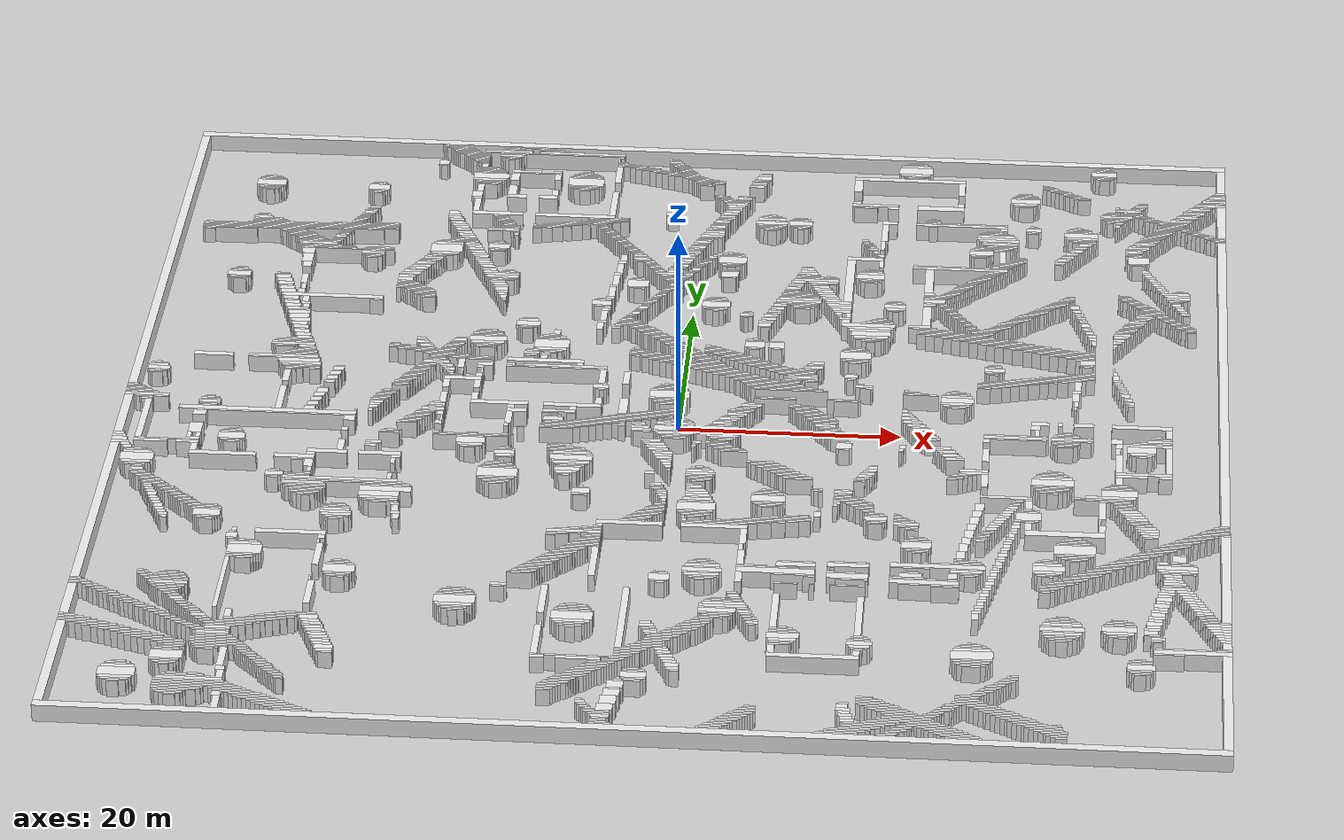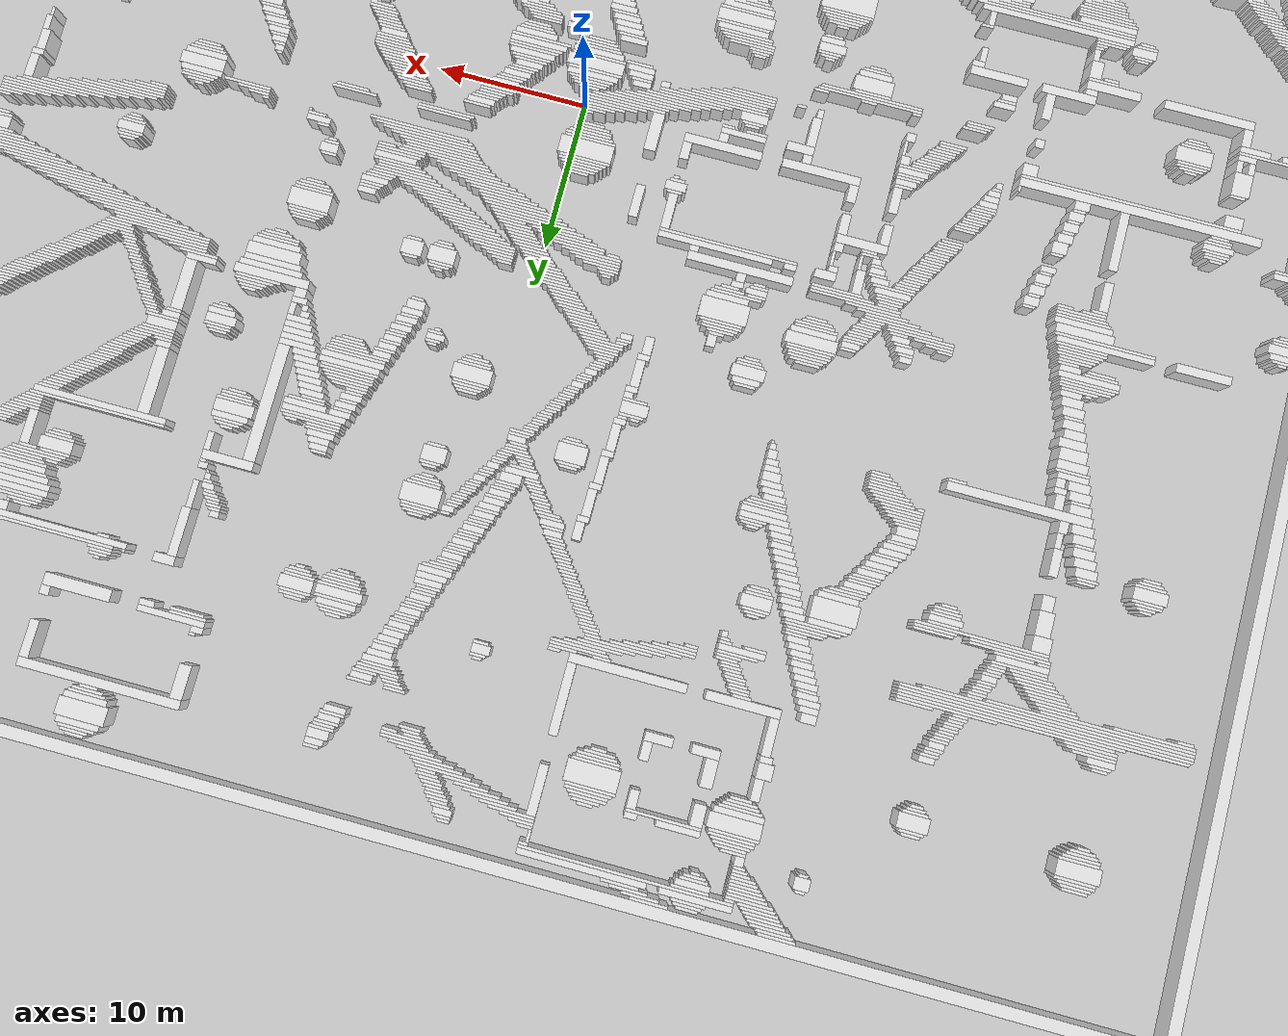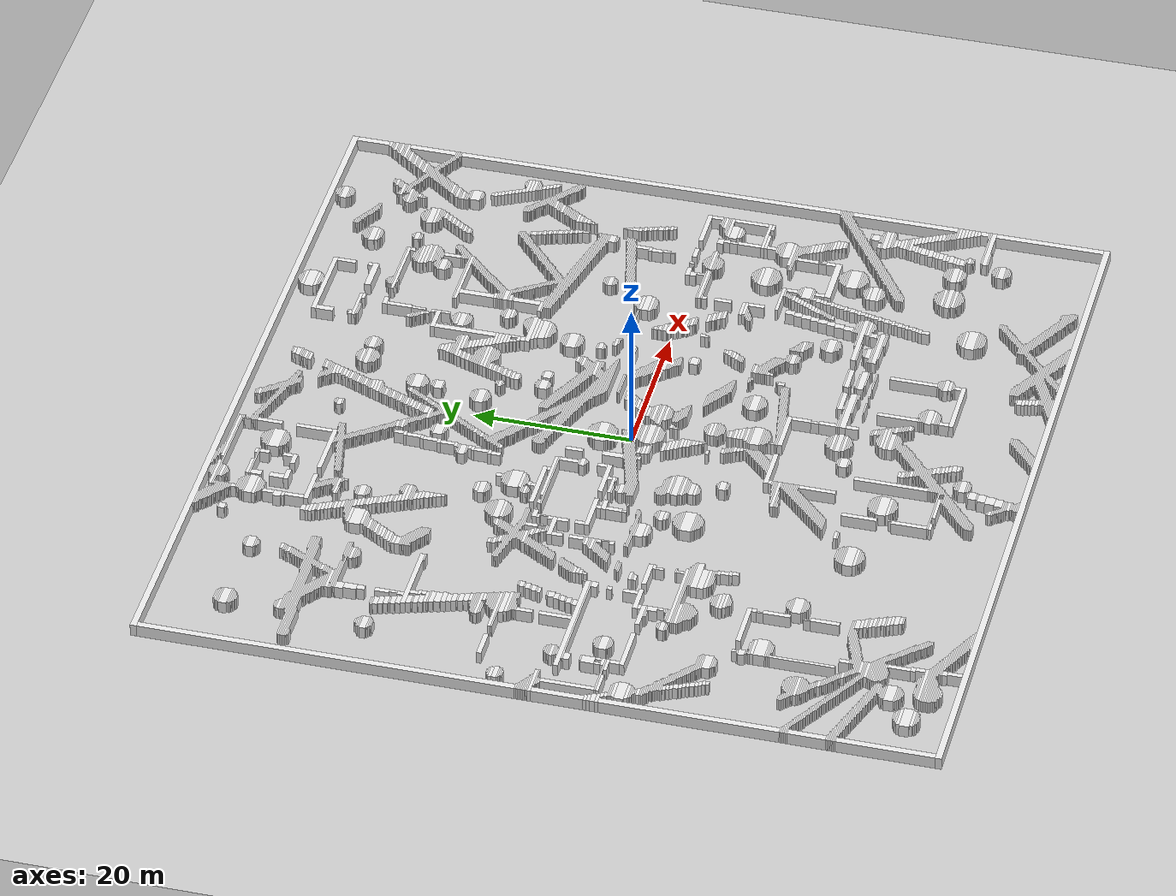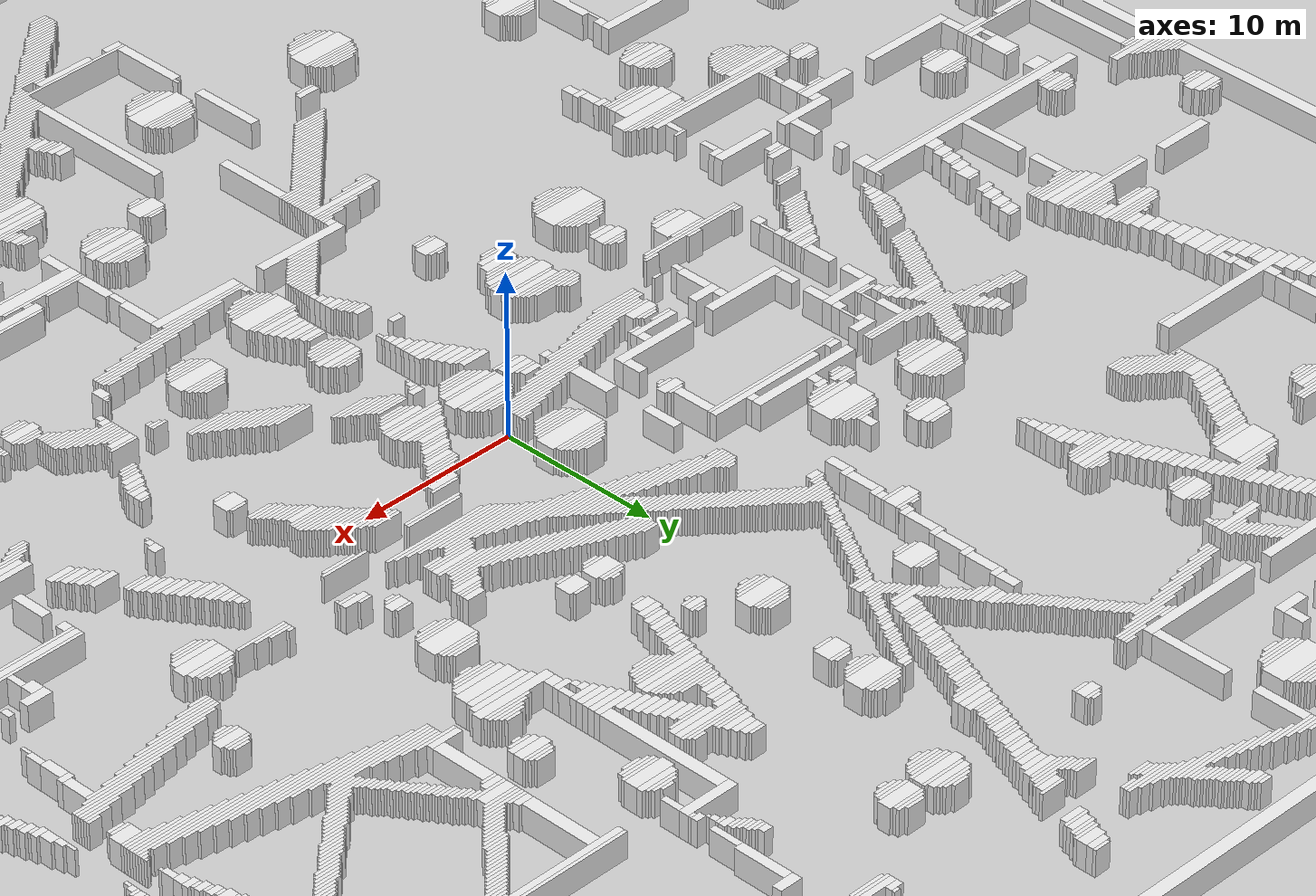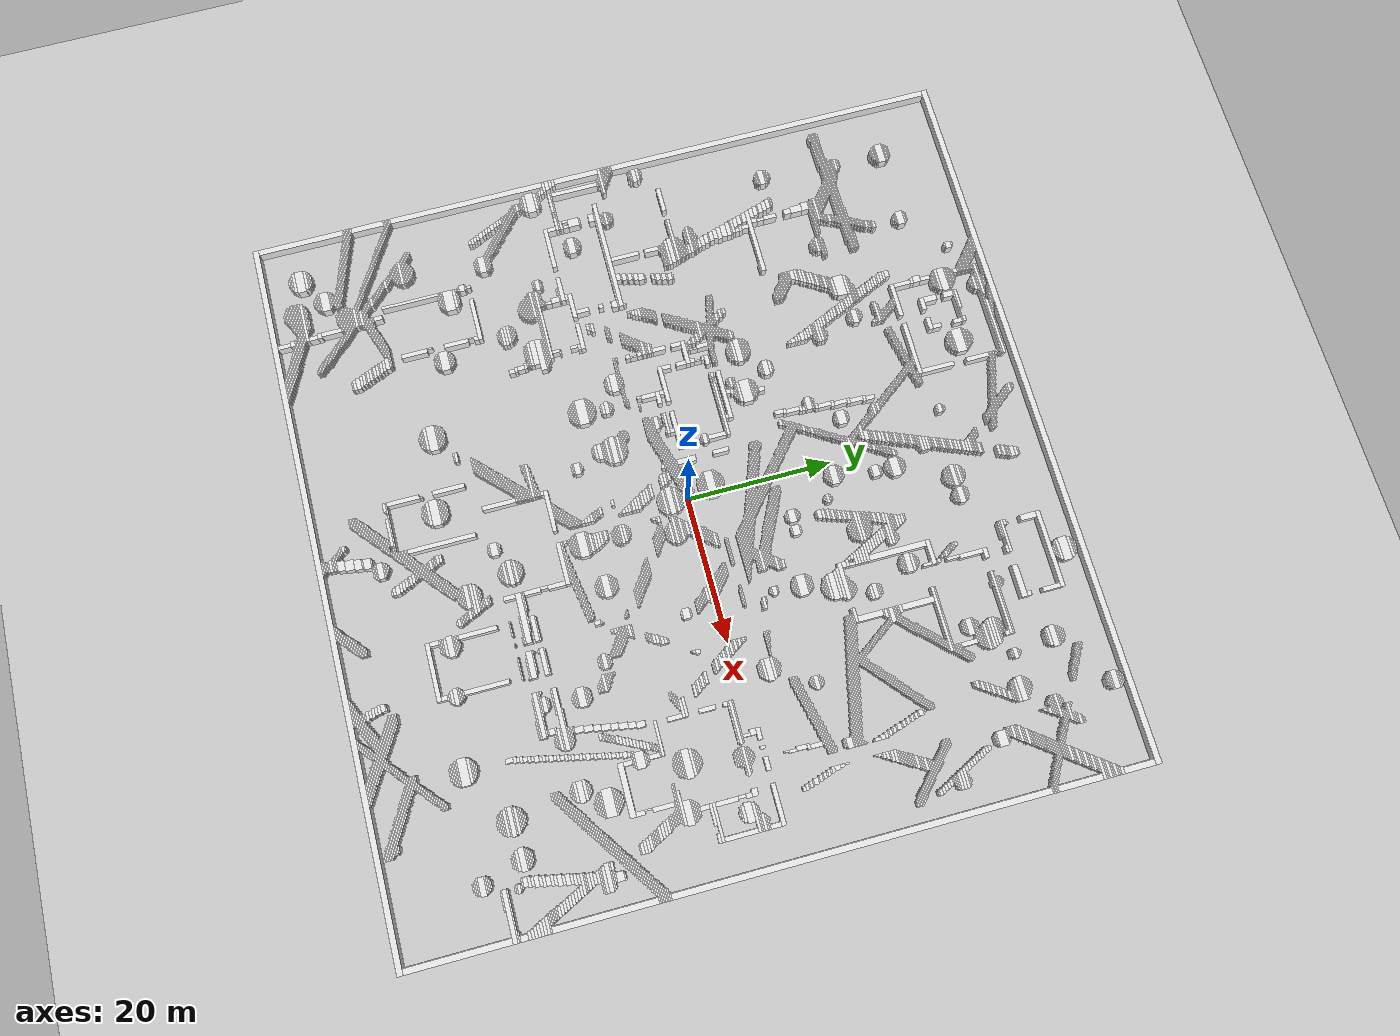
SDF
<sdf version='1.7'>
  <world name='default'>
    <light name='sun' type='directional'>
      <cast_shadows>1</cast_shadows>
      <pose>0 0 10 0 0 0</pose>
      <diffuse>0.8 0.8 0.8 1</diffuse>
      <specular>0.2 0.2 0.2 1</specular>
      <direction>-0.5 0.1 -0.9</direction>
    </light>
    <model name='ground_plane'>
      <static>1</static>
      <link name='link'>
        <collision name='collision'>
          <geometry><plane><normal>0 0 1</normal><size>120 120</size></plane></geometry>
        </collision>
        <visual name='visual'>
          <geometry><plane><normal>0 0 1</normal><size>120 120</size></plane></geometry>
          <material><script><uri>file://media/materials/scripts/gazebo.material</uri><name>Gazebo/Grey</name></script></material>
        </visual>
      </link>
    </model>
    <gravity>0 0 -9.8</gravity>
    <scene><ambient>0.4 0.4 0.4 1</ambient><background>0.7 0.7 0.7 1</background><shadows>1</shadows></scene>
    <model name='random_complex_03_model'>
      <static>1</static>
      <link name='obs_1'>
        <pose>-0.4000 48.8000 0.8000 0 0 0</pose>
        <collision name='obs_1_col'>
          <geometry><box><size>99.2000 0.8000 1.6000</size></box></geometry>
        </collision>
        <visual name='obs_1_vis'>
          <geometry><box><size>99.2000 0.8000 1.6000</size></box></geometry>
          <material><script><uri>file://media/materials/scripts/gazebo.material</uri><name>Gazebo/White</name></script></material>
        </visual>
      </link>
      <link name='obs_2'>
        <pose>-25.2000 48.3000 0.8000 0 0 0</pose>
        <collision name='obs_2_col'>
          <geometry><box><size>2.4000 0.2000 1.6000</size></box></geometry>
        </collision>
        <visual name='obs_2_vis'>
          <geometry><box><size>2.4000 0.2000 1.6000</size></box></geometry>
          <material><script><uri>file://media/materials/scripts/gazebo.material</uri><name>Gazebo/White</name></script></material>
        </visual>
      </link>
      <link name='obs_3'>
        <pose>-17.2000 48.3000 0.8000 0 0 0</pose>
        <collision name='obs_3_col'>
          <geometry><box><size>2.4000 0.2000 1.6000</size></box></geometry>
        </collision>
        <visual name='obs_3_vis'>
          <geometry><box><size>2.4000 0.2000 1.6000</size></box></geometry>
          <material><script><uri>file://media/materials/scripts/gazebo.material</uri><name>Gazebo/White</name></script></material>
        </visual>
      </link>
      <link name='obs_4'>
        <pose>-25.0000 48.1000 0.8000 0 0 0</pose>
        <collision name='obs_4_col'>
          <geometry><box><size>2.4000 0.2000 1.6000</size></box></geometry>
        </collision>
        <visual name='obs_4_vis'>
          <geometry><box><size>2.4000 0.2000 1.6000</size></box></geometry>
          <material><script><uri>file://media/materials/scripts/gazebo.material</uri><name>Gazebo/White</name></script></material>
        </visual>
      </link>
      <link name='obs_5'>
        <pose>-19.5000 48.1000 0.8000 0 0 0</pose>
        <collision name='obs_5_col'>
          <geometry><box><size>1.4000 0.2000 1.6000</size></box></geometry>
        </collision>
        <visual name='obs_5_vis'>
          <geometry><box><size>1.4000 0.2000 1.6000</size></box></geometry>
          <material><script><uri>file://media/materials/scripts/gazebo.material</uri><name>Gazebo/White</name></script></material>
        </visual>
      </link>
      <link name='obs_6'>
        <pose>-16.6000 48.1000 0.8000 0 0 0</pose>
        <collision name='obs_6_col'>
          <geometry><box><size>2.4000 0.2000 1.6000</size></box></geometry>
        </collision>
        <visual name='obs_6_vis'>
          <geometry><box><size>2.4000 0.2000 1.6000</size></box></geometry>
          <material><script><uri>file://media/materials/scripts/gazebo.material</uri><name>Gazebo/White</name></script></material>
        </visual>
      </link>
      <link name='obs_7'>
        <pose>37.7000 48.1000 0.8000 0 0 0</pose>
        <collision name='obs_7_col'>
          <geometry><box><size>1.0000 0.2000 1.6000</size></box></geometry>
        </collision>
        <visual name='obs_7_vis'>
          <geometry><box><size>1.0000 0.2000 1.6000</size></box></geometry>
          <material><script><uri>file://media/materials/scripts/gazebo.material</uri><name>Gazebo/White</name></script></material>
        </visual>
      </link>
      <link name='obs_8'>
        <pose>-24.7000 47.9000 0.8000 0 0 0</pose>
        <collision name='obs_8_col'>
          <geometry><box><size>2.6000 0.2000 1.6000</size></box></geometry>
        </collision>
        <visual name='obs_8_vis'>
          <geometry><box><size>2.6000 0.2000 1.6000</size></box></geometry>
          <material><script><uri>file://media/materials/scripts/gazebo.material</uri><name>Gazebo/White</name></script></material>
        </visual>
      </link>
      <link name='obs_9'>
        <pose>-19.5000 47.9000 0.8000 0 0 0</pose>
        <collision name='obs_9_col'>
          <geometry><box><size>1.8000 0.2000 1.6000</size></box></geometry>
        </collision>
        <visual name='obs_9_vis'>
          <geometry><box><size>1.8000 0.2000 1.6000</size></box></geometry>
          <material><script><uri>file://media/materials/scripts/gazebo.material</uri><name>Gazebo/White</name></script></material>
        </visual>
      </link>
      <link name='obs_10'>
        <pose>-15.8000 47.9000 0.8000 0 0 0</pose>
        <collision name='obs_10_col'>
          <geometry><box><size>2.4000 0.2000 1.6000</size></box></geometry>
        </collision>
        <visual name='obs_10_vis'>
          <geometry><box><size>2.4000 0.2000 1.6000</size></box></geometry>
          <material><script><uri>file://media/materials/scripts/gazebo.material</uri><name>Gazebo/White</name></script></material>
        </visual>
      </link>
      <link name='obs_11'>
        <pose>19.6000 47.9000 0.8000 0 0 0</pose>
        <collision name='obs_11_col'>
          <geometry><box><size>1.2000 0.2000 1.6000</size></box></geometry>
        </collision>
        <visual name='obs_11_vis'>
          <geometry><box><size>1.2000 0.2000 1.6000</size></box></geometry>
          <material><script><uri>file://media/materials/scripts/gazebo.material</uri><name>Gazebo/White</name></script></material>
        </visual>
      </link>
      <link name='obs_12'>
        <pose>37.6000 47.9000 0.8000 0 0 0</pose>
        <collision name='obs_12_col'>
          <geometry><box><size>1.6000 0.2000 1.6000</size></box></geometry>
        </collision>
        <visual name='obs_12_vis'>
          <geometry><box><size>1.6000 0.2000 1.6000</size></box></geometry>
          <material><script><uri>file://media/materials/scripts/gazebo.material</uri><name>Gazebo/White</name></script></material>
        </visual>
      </link>
      <link name='obs_13'>
        <pose>-24.4000 47.7000 0.8000 0 0 0</pose>
        <collision name='obs_13_col'>
          <geometry><box><size>2.4000 0.2000 1.6000</size></box></geometry>
        </collision>
        <visual name='obs_13_vis'>
          <geometry><box><size>2.4000 0.2000 1.6000</size></box></geometry>
          <material><script><uri>file://media/materials/scripts/gazebo.material</uri><name>Gazebo/White</name></script></material>
        </visual>
      </link>
      <link name='obs_14'>
        <pose>-19.5000 47.7000 0.8000 0 0 0</pose>
        <collision name='obs_14_col'>
          <geometry><box><size>2.2000 0.2000 1.6000</size></box></geometry>
        </collision>
        <visual name='obs_14_vis'>
          <geometry><box><size>2.2000 0.2000 1.6000</size></box></geometry>
          <material><script><uri>file://media/materials/scripts/gazebo.material</uri><name>Gazebo/White</name></script></material>
        </visual>
      </link>
      <link name='obs_15'>
        <pose>-15.2000 47.7000 0.8000 0 0 0</pose>
        <collision name='obs_15_col'>
          <geometry><box><size>2.4000 0.2000 1.6000</size></box></geometry>
        </collision>
        <visual name='obs_15_vis'>
          <geometry><box><size>2.4000 0.2000 1.6000</size></box></geometry>
          <material><script><uri>file://media/materials/scripts/gazebo.material</uri><name>Gazebo/White</name></script></material>
        </visual>
      </link>
      <link name='obs_16'>
        <pose>19.7000 47.7000 0.8000 0 0 0</pose>
        <collision name='obs_16_col'>
          <geometry><box><size>1.8000 0.2000 1.6000</size></box></geometry>
        </collision>
        <visual name='obs_16_vis'>
          <geometry><box><size>1.8000 0.2000 1.6000</size></box></geometry>
          <material><script><uri>file://media/materials/scripts/gazebo.material</uri><name>Gazebo/White</name></script></material>
        </visual>
      </link>
      <link name='obs_17'>
        <pose>37.7000 47.7000 0.8000 0 0 0</pose>
        <collision name='obs_17_col'>
          <geometry><box><size>1.8000 0.2000 1.6000</size></box></geometry>
        </collision>
        <visual name='obs_17_vis'>
          <geometry><box><size>1.8000 0.2000 1.6000</size></box></geometry>
          <material><script><uri>file://media/materials/scripts/gazebo.material</uri><name>Gazebo/White</name></script></material>
        </visual>
      </link>
      <link name='obs_18'>
        <pose>-24.2000 47.5000 0.8000 0 0 0</pose>
        <collision name='obs_18_col'>
          <geometry><box><size>2.4000 0.2000 1.6000</size></box></geometry>
        </collision>
        <visual name='obs_18_vis'>
          <geometry><box><size>2.4000 0.2000 1.6000</size></box></geometry>
          <material><script><uri>file://media/materials/scripts/gazebo.material</uri><name>Gazebo/White</name></script></material>
        </visual>
      </link>
      <link name='obs_19'>
        <pose>19.6000 47.5000 0.8000 0 0 0</pose>
        <collision name='obs_19_col'>
          <geometry><box><size>2.4000 0.2000 1.6000</size></box></geometry>
        </collision>
        <visual name='obs_19_vis'>
          <geometry><box><size>2.4000 0.2000 1.6000</size></box></geometry>
          <material><script><uri>file://media/materials/scripts/gazebo.material</uri><name>Gazebo/White</name></script></material>
        </visual>
      </link>
      <link name='obs_20'>
        <pose>37.7000 47.5000 0.8000 0 0 0</pose>
        <collision name='obs_20_col'>
          <geometry><box><size>2.2000 0.2000 1.6000</size></box></geometry>
        </collision>
        <visual name='obs_20_vis'>
          <geometry><box><size>2.2000 0.2000 1.6000</size></box></geometry>
          <material><script><uri>file://media/materials/scripts/gazebo.material</uri><name>Gazebo/White</name></script></material>
        </visual>
      </link>
      <link name='obs_21'>
        <pose>-19.9000 47.4000 0.8000 0 0 0</pose>
        <collision name='obs_21_col'>
          <geometry><box><size>4.6000 0.4000 1.6000</size></box></geometry>
        </collision>
        <visual name='obs_21_vis'>
          <geometry><box><size>4.6000 0.4000 1.6000</size></box></geometry>
          <material><script><uri>file://media/materials/scripts/gazebo.material</uri><name>Gazebo/White</name></script></material>
        </visual>
      </link>
      <link name='obs_22'>
        <pose>-12.7000 47.4000 0.8000 0 0 0</pose>
        <collision name='obs_22_col'>
          <geometry><box><size>8.2000 0.4000 1.6000</size></box></geometry>
        </collision>
        <visual name='obs_22_vis'>
          <geometry><box><size>8.2000 0.4000 1.6000</size></box></geometry>
          <material><script><uri>file://media/materials/scripts/gazebo.material</uri><name>Gazebo/White</name></script></material>
        </visual>
      </link>
      <link name='obs_23'>
        <pose>-24.0000 47.3000 0.8000 0 0 0</pose>
        <collision name='obs_23_col'>
          <geometry><box><size>2.4000 0.2000 1.6000</size></box></geometry>
        </collision>
        <visual name='obs_23_vis'>
          <geometry><box><size>2.4000 0.2000 1.6000</size></box></geometry>
          <material><script><uri>file://media/materials/scripts/gazebo.material</uri><name>Gazebo/White</name></script></material>
        </visual>
      </link>
      <link name='obs_24'>
        <pose>19.6000 47.2000 0.8000 0 0 0</pose>
        <collision name='obs_24_col'>
          <geometry><box><size>2.8000 0.4000 1.6000</size></box></geometry>
        </collision>
        <visual name='obs_24_vis'>
          <geometry><box><size>2.8000 0.4000 1.6000</size></box></geometry>
          <material><script><uri>file://media/materials/scripts/gazebo.material</uri><name>Gazebo/White</name></script></material>
        </visual>
      </link>
      <link name='obs_25'>
        <pose>-23.8000 47.1000 0.8000 0 0 0</pose>
        <collision name='obs_25_col'>
          <geometry><box><size>2.4000 0.2000 1.6000</size></box></geometry>
        </collision>
        <visual name='obs_25_vis'>
          <geometry><box><size>2.4000 0.2000 1.6000</size></box></geometry>
          <material><script><uri>file://media/materials/scripts/gazebo.material</uri><name>Gazebo/White</name></script></material>
        </visual>
      </link>
      <link name='obs_26'>
        <pose>-15.4000 47.1000 0.8000 0 0 0</pose>
        <collision name='obs_26_col'>
          <geometry><box><size>13.6000 0.2000 1.6000</size></box></geometry>
        </collision>
        <visual name='obs_26_vis'>
          <geometry><box><size>13.6000 0.2000 1.6000</size></box></geometry>
          <material><script><uri>file://media/materials/scripts/gazebo.material</uri><name>Gazebo/White</name></script></material>
        </visual>
      </link>
      <link name='obs_27'>
        <pose>-23.6000 46.9000 0.8000 0 0 0</pose>
        <collision name='obs_27_col'>
          <geometry><box><size>2.4000 0.2000 1.6000</size></box></geometry>
        </collision>
        <visual name='obs_27_vis'>
          <geometry><box><size>2.4000 0.2000 1.6000</size></box></geometry>
          <material><script><uri>file://media/materials/scripts/gazebo.material</uri><name>Gazebo/White</name></script></material>
        </visual>
      </link>
      <link name='obs_28'>
        <pose>-21.9000 46.9000 0.8000 0 0 0</pose>
        <collision name='obs_28_col'>
          <geometry><box><size>0.6000 0.2000 1.6000</size></box></geometry>
        </collision>
        <visual name='obs_28_vis'>
          <geometry><box><size>0.6000 0.2000 1.6000</size></box></geometry>
          <material><script><uri>file://media/materials/scripts/gazebo.material</uri><name>Gazebo/White</name></script></material>
        </visual>
      </link>
      <link name='obs_29'>
        <pose>-19.4000 46.9000 0.8000 0 0 0</pose>
        <collision name='obs_29_col'>
          <geometry><box><size>2.4000 0.2000 1.6000</size></box></geometry>
        </collision>
        <visual name='obs_29_vis'>
          <geometry><box><size>2.4000 0.2000 1.6000</size></box></geometry>
          <material><script><uri>file://media/materials/scripts/gazebo.material</uri><name>Gazebo/White</name></script></material>
        </visual>
      </link>
      <link name='obs_30'>
        <pose>-8.9000 46.9000 0.8000 0 0 0</pose>
        <collision name='obs_30_col'>
          <geometry><box><size>0.6000 0.2000 1.6000</size></box></geometry>
        </collision>
        <visual name='obs_30_vis'>
          <geometry><box><size>0.6000 0.2000 1.6000</size></box></geometry>
          <material><script><uri>file://media/materials/scripts/gazebo.material</uri><name>Gazebo/White</name></script></material>
        </visual>
      </link>
      <link name='obs_31'>
        <pose>-3.8000 46.9000 0.8000 0 0 0</pose>
        <collision name='obs_31_col'>
          <geometry><box><size>0.8000 0.2000 1.6000</size></box></geometry>
        </collision>
        <visual name='obs_31_vis'>
          <geometry><box><size>0.8000 0.2000 1.6000</size></box></geometry>
          <material><script><uri>file://media/materials/scripts/gazebo.material</uri><name>Gazebo/White</name></script></material>
        </visual>
      </link>
      <link name='obs_32'>
        <pose>37.6000 47.0000 0.8000 0 0 0</pose>
        <collision name='obs_32_col'>
          <geometry><box><size>2.4000 0.8000 1.6000</size></box></geometry>
        </collision>
        <visual name='obs_32_vis'>
          <geometry><box><size>2.4000 0.8000 1.6000</size></box></geometry>
          <material><script><uri>file://media/materials/scripts/gazebo.material</uri><name>Gazebo/White</name></script></material>
        </visual>
      </link>
      <link name='obs_33'>
        <pose>-23.1000 46.7000 0.8000 0 0 0</pose>
        <collision name='obs_33_col'>
          <geometry><box><size>3.0000 0.2000 1.6000</size></box></geometry>
        </collision>
        <visual name='obs_33_vis'>
          <geometry><box><size>3.0000 0.2000 1.6000</size></box></geometry>
          <material><script><uri>file://media/materials/scripts/gazebo.material</uri><name>Gazebo/White</name></script></material>
        </visual>
      </link>
      <link name='obs_34'>
        <pose>-3.7000 46.7000 0.8000 0 0 0</pose>
        <collision name='obs_34_col'>
          <geometry><box><size>1.0000 0.2000 1.6000</size></box></geometry>
        </collision>
        <visual name='obs_34_vis'>
          <geometry><box><size>1.0000 0.2000 1.6000</size></box></geometry>
          <material><script><uri>file://media/materials/scripts/gazebo.material</uri><name>Gazebo/White</name></script></material>
        </visual>
      </link>
      <link name='obs_35'>
        <pose>-19.5000 46.6000 0.8000 0 0 0</pose>
        <collision name='obs_35_col'>
          <geometry><box><size>2.2000 0.4000 1.6000</size></box></geometry>
        </collision>
        <visual name='obs_35_vis'>
          <geometry><box><size>2.2000 0.4000 1.6000</size></box></geometry>
          <material><script><uri>file://media/materials/scripts/gazebo.material</uri><name>Gazebo/White</name></script></material>
        </visual>
      </link>
      <link name='obs_36'>
        <pose>-22.9000 46.5000 0.8000 0 0 0</pose>
        <collision name='obs_36_col'>
          <geometry><box><size>2.6000 0.2000 1.6000</size></box></geometry>
        </collision>
        <visual name='obs_36_vis'>
          <geometry><box><size>2.6000 0.2000 1.6000</size></box></geometry>
          <material><script><uri>file://media/materials/scripts/gazebo.material</uri><name>Gazebo/White</name></script></material>
        </visual>
      </link>
      <link name='obs_37'>
        <pose>37.7000 46.5000 0.8000 0 0 0</pose>
        <collision name='obs_37_col'>
          <geometry><box><size>2.2000 0.2000 1.6000</size></box></geometry>
        </collision>
        <visual name='obs_37_vis'>
          <geometry><box><size>2.2000 0.2000 1.6000</size></box></geometry>
          <material><script><uri>file://media/materials/scripts/gazebo.material</uri><name>Gazebo/White</name></script></material>
        </visual>
      </link>
      <link name='obs_38'>
        <pose>-3.6000 46.4000 0.8000 0 0 0</pose>
        <collision name='obs_38_col'>
          <geometry><box><size>1.2000 0.4000 1.6000</size></box></geometry>
        </collision>
        <visual name='obs_38_vis'>
          <geometry><box><size>1.2000 0.4000 1.6000</size></box></geometry>
          <material><script><uri>file://media/materials/scripts/gazebo.material</uri><name>Gazebo/White</name></script></material>
        </visual>
      </link>
      <link name='obs_39'>
        <pose>-22.8000 46.3000 0.8000 0 0 0</pose>
        <collision name='obs_39_col'>
          <geometry><box><size>2.4000 0.2000 1.6000</size></box></geometry>
        </collision>
        <visual name='obs_39_vis'>
          <geometry><box><size>2.4000 0.2000 1.6000</size></box></geometry>
          <material><script><uri>file://media/materials/scripts/gazebo.material</uri><name>Gazebo/White</name></script></material>
        </visual>
      </link>
      <link name='obs_40'>
        <pose>-19.5000 46.3000 0.8000 0 0 0</pose>
        <collision name='obs_40_col'>
          <geometry><box><size>1.8000 0.2000 1.6000</size></box></geometry>
        </collision>
        <visual name='obs_40_vis'>
          <geometry><box><size>1.8000 0.2000 1.6000</size></box></geometry>
          <material><script><uri>file://media/materials/scripts/gazebo.material</uri><name>Gazebo/White</name></script></material>
        </visual>
      </link>
      <link name='obs_41'>
        <pose>37.6000 46.3000 0.8000 0 0 0</pose>
        <collision name='obs_41_col'>
          <geometry><box><size>2.0000 0.2000 1.6000</size></box></geometry>
        </collision>
        <visual name='obs_41_vis'>
          <geometry><box><size>2.0000 0.2000 1.6000</size></box></geometry>
          <material><script><uri>file://media/materials/scripts/gazebo.material</uri><name>Gazebo/White</name></script></material>
        </visual>
      </link>
      <link name='obs_42'>
        <pose>-9.1000 46.4000 0.8000 0 0 0</pose>
        <collision name='obs_42_col'>
          <geometry><box><size>0.2000 0.8000 1.6000</size></box></geometry>
        </collision>
        <visual name='obs_42_vis'>
          <geometry><box><size>0.2000 0.8000 1.6000</size></box></geometry>
          <material><script><uri>file://media/materials/scripts/gazebo.material</uri><name>Gazebo/White</name></script></material>
        </visual>
      </link>
      <link name='obs_43'>
        <pose>-22.7000 46.1000 0.8000 0 0 0</pose>
        <collision name='obs_43_col'>
          <geometry><box><size>2.2000 0.2000 1.6000</size></box></geometry>
        </collision>
        <visual name='obs_43_vis'>
          <geometry><box><size>2.2000 0.2000 1.6000</size></box></geometry>
          <material><script><uri>file://media/materials/scripts/gazebo.material</uri><name>Gazebo/White</name></script></material>
        </visual>
      </link>
      <link name='obs_44'>
        <pose>-19.5000 46.1000 0.8000 0 0 0</pose>
        <collision name='obs_44_col'>
          <geometry><box><size>1.4000 0.2000 1.6000</size></box></geometry>
        </collision>
        <visual name='obs_44_vis'>
          <geometry><box><size>1.4000 0.2000 1.6000</size></box></geometry>
          <material><script><uri>file://media/materials/scripts/gazebo.material</uri><name>Gazebo/White</name></script></material>
        </visual>
      </link>
      <link name='obs_45'>
        <pose>-3.4000 46.1000 0.8000 0 0 0</pose>
        <collision name='obs_45_col'>
          <geometry><box><size>1.2000 0.2000 1.6000</size></box></geometry>
        </collision>
        <visual name='obs_45_vis'>
          <geometry><box><size>1.2000 0.2000 1.6000</size></box></geometry>
          <material><script><uri>file://media/materials/scripts/gazebo.material</uri><name>Gazebo/White</name></script></material>
        </visual>
      </link>
      <link name='obs_46'>
        <pose>37.7000 46.1000 0.8000 0 0 0</pose>
        <collision name='obs_46_col'>
          <geometry><box><size>1.8000 0.2000 1.6000</size></box></geometry>
        </collision>
        <visual name='obs_46_vis'>
          <geometry><box><size>1.8000 0.2000 1.6000</size></box></geometry>
          <material><script><uri>file://media/materials/scripts/gazebo.material</uri><name>Gazebo/White</name></script></material>
        </visual>
      </link>
      <link name='obs_47'>
        <pose>19.6000 46.4000 0.8000 0 0 0</pose>
        <collision name='obs_47_col'>
          <geometry><box><size>3.2000 1.2000 1.6000</size></box></geometry>
        </collision>
        <visual name='obs_47_vis'>
          <geometry><box><size>3.2000 1.2000 1.6000</size></box></geometry>
          <material><script><uri>file://media/materials/scripts/gazebo.material</uri><name>Gazebo/White</name></script></material>
        </visual>
      </link>
      <link name='obs_48'>
        <pose>-22.6000 45.9000 0.8000 0 0 0</pose>
        <collision name='obs_48_col'>
          <geometry><box><size>2.0000 0.2000 1.6000</size></box></geometry>
        </collision>
        <visual name='obs_48_vis'>
          <geometry><box><size>2.0000 0.2000 1.6000</size></box></geometry>
          <material><script><uri>file://media/materials/scripts/gazebo.material</uri><name>Gazebo/White</name></script></material>
        </visual>
      </link>
      <link name='obs_49'>
        <pose>-19.5000 45.9000 0.8000 0 0 0</pose>
        <collision name='obs_49_col'>
          <geometry><box><size>0.6000 0.2000 1.6000</size></box></geometry>
        </collision>
        <visual name='obs_49_vis'>
          <geometry><box><size>0.6000 0.2000 1.6000</size></box></geometry>
          <material><script><uri>file://media/materials/scripts/gazebo.material</uri><name>Gazebo/White</name></script></material>
        </visual>
      </link>
      <link name='obs_50'>
        <pose>-8.7000 45.9000 0.8000 0 0 0</pose>
        <collision name='obs_50_col'>
          <geometry><box><size>1.0000 0.2000 1.6000</size></box></geometry>
        </collision>
        <visual name='obs_50_vis'>
          <geometry><box><size>1.0000 0.2000 1.6000</size></box></geometry>
          <material><script><uri>file://media/materials/scripts/gazebo.material</uri><name>Gazebo/White</name></script></material>
        </visual>
      </link>
      <link name='obs_51'>
        <pose>-3.2000 45.9000 0.8000 0 0 0</pose>
        <collision name='obs_51_col'>
          <geometry><box><size>1.2000 0.2000 1.6000</size></box></geometry>
        </collision>
        <visual name='obs_51_vis'>
          <geometry><box><size>1.2000 0.2000 1.6000</size></box></geometry>
          <material><script><uri>file://media/materials/scripts/gazebo.material</uri><name>Gazebo/White</name></script></material>
        </visual>
      </link>
      <link name='obs_52'>
        <pose>37.7000 45.9000 0.8000 0 0 0</pose>
        <collision name='obs_52_col'>
          <geometry><box><size>1.0000 0.2000 1.6000</size></box></geometry>
        </collision>
        <visual name='obs_52_vis'>
          <geometry><box><size>1.0000 0.2000 1.6000</size></box></geometry>
          <material><script><uri>file://media/materials/scripts/gazebo.material</uri><name>Gazebo/White</name></script></material>
        </visual>
      </link>
      <link name='obs_53'>
        <pose>-22.5000 45.7000 0.8000 0 0 0</pose>
        <collision name='obs_53_col'>
          <geometry><box><size>1.8000 0.2000 1.6000</size></box></geometry>
        </collision>
        <visual name='obs_53_vis'>
          <geometry><box><size>1.8000 0.2000 1.6000</size></box></geometry>
          <material><script><uri>file://media/materials/scripts/gazebo.material</uri><name>Gazebo/White</name></script></material>
        </visual>
      </link>
      <link name='obs_54'>
        <pose>-8.4000 45.7000 0.8000 0 0 0</pose>
        <collision name='obs_54_col'>
          <geometry><box><size>1.6000 0.2000 1.6000</size></box></geometry>
        </collision>
        <visual name='obs_54_vis'>
          <geometry><box><size>1.6000 0.2000 1.6000</size></box></geometry>
          <material><script><uri>file://media/materials/scripts/gazebo.material</uri><name>Gazebo/White</name></script></material>
        </visual>
      </link>
      <link name='obs_55'>
        <pose>-3.1000 45.7000 0.8000 0 0 0</pose>
        <collision name='obs_55_col'>
          <geometry><box><size>1.4000 0.2000 1.6000</size></box></geometry>
        </collision>
        <visual name='obs_55_vis'>
          <geometry><box><size>1.4000 0.2000 1.6000</size></box></geometry>
          <material><script><uri>file://media/materials/scripts/gazebo.material</uri><name>Gazebo/White</name></script></material>
        </visual>
      </link>
      <link name='obs_56'>
        <pose>19.6000 45.6000 0.8000 0 0 0</pose>
        <collision name='obs_56_col'>
          <geometry><box><size>2.8000 0.4000 1.6000</size></box></geometry>
        </collision>
        <visual name='obs_56_vis'>
          <geometry><box><size>2.8000 0.4000 1.6000</size></box></geometry>
          <material><script><uri>file://media/materials/scripts/gazebo.material</uri><name>Gazebo/White</name></script></material>
        </visual>
      </link>
      <link name='obs_57'>
        <pose>-22.4000 45.5000 0.8000 0 0 0</pose>
        <collision name='obs_57_col'>
          <geometry><box><size>1.6000 0.2000 1.6000</size></box></geometry>
        </collision>
        <visual name='obs_57_vis'>
          <geometry><box><size>1.6000 0.2000 1.6000</size></box></geometry>
          <material><script><uri>file://media/materials/scripts/gazebo.material</uri><name>Gazebo/White</name></script></material>
        </visual>
      </link>
      <link name='obs_58'>
        <pose>-8.1000 45.5000 0.8000 0 0 0</pose>
        <collision name='obs_58_col'>
          <geometry><box><size>2.2000 0.2000 1.6000</size></box></geometry>
        </collision>
        <visual name='obs_58_vis'>
          <geometry><box><size>2.2000 0.2000 1.6000</size></box></geometry>
          <material><script><uri>file://media/materials/scripts/gazebo.material</uri><name>Gazebo/White</name></script></material>
        </visual>
      </link>
      <link name='obs_59'>
        <pose>-2.9000 45.5000 0.8000 0 0 0</pose>
        <collision name='obs_59_col'>
          <geometry><box><size>1.4000 0.2000 1.6000</size></box></geometry>
        </collision>
        <visual name='obs_59_vis'>
          <geometry><box><size>1.4000 0.2000 1.6000</size></box></geometry>
          <material><script><uri>file://media/materials/scripts/gazebo.material</uri><name>Gazebo/White</name></script></material>
        </visual>
      </link>
      <link name='obs_60'>
        <pose>-25.9000 45.3000 0.8000 0 0 0</pose>
        <collision name='obs_60_col'>
          <geometry><box><size>0.6000 0.2000 1.6000</size></box></geometry>
        </collision>
        <visual name='obs_60_vis'>
          <geometry><box><size>0.6000 0.2000 1.6000</size></box></geometry>
          <material><script><uri>file://media/materials/scripts/gazebo.material</uri><name>Gazebo/White</name></script></material>
        </visual>
      </link>
      <link name='obs_61'>
        <pose>-22.2000 45.3000 0.8000 0 0 0</pose>
        <collision name='obs_61_col'>
          <geometry><box><size>1.2000 0.2000 1.6000</size></box></geometry>
        </collision>
        <visual name='obs_61_vis'>
          <geometry><box><size>1.2000 0.2000 1.6000</size></box></geometry>
          <material><script><uri>file://media/materials/scripts/gazebo.material</uri><name>Gazebo/White</name></script></material>
        </visual>
      </link>
      <link name='obs_62'>
        <pose>-7.7000 45.3000 0.8000 0 0 0</pose>
        <collision name='obs_62_col'>
          <geometry><box><size>3.0000 0.2000 1.6000</size></box></geometry>
        </collision>
        <visual name='obs_62_vis'>
          <geometry><box><size>3.0000 0.2000 1.6000</size></box></geometry>
          <material><script><uri>file://media/materials/scripts/gazebo.material</uri><name>Gazebo/White</name></script></material>
        </visual>
      </link>
      <link name='obs_63'>
        <pose>-2.8000 45.3000 0.8000 0 0 0</pose>
        <collision name='obs_63_col'>
          <geometry><box><size>1.2000 0.2000 1.6000</size></box></geometry>
        </collision>
        <visual name='obs_63_vis'>
          <geometry><box><size>1.2000 0.2000 1.6000</size></box></geometry>
          <material><script><uri>file://media/materials/scripts/gazebo.material</uri><name>Gazebo/White</name></script></material>
        </visual>
      </link>
      <link name='obs_64'>
        <pose>19.6000 45.3000 0.8000 0 0 0</pose>
        <collision name='obs_64_col'>
          <geometry><box><size>2.4000 0.2000 1.6000</size></box></geometry>
        </collision>
        <visual name='obs_64_vis'>
          <geometry><box><size>2.4000 0.2000 1.6000</size></box></geometry>
          <material><script><uri>file://media/materials/scripts/gazebo.material</uri><name>Gazebo/White</name></script></material>
        </visual>
      </link>
      <link name='obs_65'>
        <pose>-22.1000 45.1000 0.8000 0 0 0</pose>
        <collision name='obs_65_col'>
          <geometry><box><size>1.0000 0.2000 1.6000</size></box></geometry>
        </collision>
        <visual name='obs_65_vis'>
          <geometry><box><size>1.0000 0.2000 1.6000</size></box></geometry>
          <material><script><uri>file://media/materials/scripts/gazebo.material</uri><name>Gazebo/White</name></script></material>
        </visual>
      </link>
      <link name='obs_66'>
        <pose>-6.8000 45.1000 0.8000 0 0 0</pose>
        <collision name='obs_66_col'>
          <geometry><box><size>2.4000 0.2000 1.6000</size></box></geometry>
        </collision>
        <visual name='obs_66_vis'>
          <geometry><box><size>2.4000 0.2000 1.6000</size></box></geometry>
          <material><script><uri>file://media/materials/scripts/gazebo.material</uri><name>Gazebo/White</name></script></material>
        </visual>
      </link>
      <link name='obs_67'>
        <pose>-2.6000 45.1000 0.8000 0 0 0</pose>
        <collision name='obs_67_col'>
          <geometry><box><size>1.2000 0.2000 1.6000</size></box></geometry>
        </collision>
        <visual name='obs_67_vis'>
          <geometry><box><size>1.2000 0.2000 1.6000</size></box></geometry>
          <material><script><uri>file://media/materials/scripts/gazebo.material</uri><name>Gazebo/White</name></script></material>
        </visual>
      </link>
      <link name='obs_68'>
        <pose>19.6000 45.1000 0.8000 0 0 0</pose>
        <collision name='obs_68_col'>
          <geometry><box><size>2.0000 0.2000 1.6000</size></box></geometry>
        </collision>
        <visual name='obs_68_vis'>
          <geometry><box><size>2.0000 0.2000 1.6000</size></box></geometry>
          <material><script><uri>file://media/materials/scripts/gazebo.material</uri><name>Gazebo/White</name></script></material>
        </visual>
      </link>
      <link name='obs_69'>
        <pose>-22.0000 44.9000 0.8000 0 0 0</pose>
        <collision name='obs_69_col'>
          <geometry><box><size>0.8000 0.2000 1.6000</size></box></geometry>
        </collision>
        <visual name='obs_69_vis'>
          <geometry><box><size>0.8000 0.2000 1.6000</size></box></geometry>
          <material><script><uri>file://media/materials/scripts/gazebo.material</uri><name>Gazebo/White</name></script></material>
        </visual>
      </link>
      <link name='obs_70'>
        <pose>-6.2000 44.9000 0.8000 0 0 0</pose>
        <collision name='obs_70_col'>
          <geometry><box><size>2.4000 0.2000 1.6000</size></box></geometry>
        </collision>
        <visual name='obs_70_vis'>
          <geometry><box><size>2.4000 0.2000 1.6000</size></box></geometry>
          <material><script><uri>file://media/materials/scripts/gazebo.material</uri><name>Gazebo/White</name></script></material>
        </visual>
      </link>
      <link name='obs_71'>
        <pose>-2.5000 44.9000 0.8000 0 0 0</pose>
        <collision name='obs_71_col'>
          <geometry><box><size>1.4000 0.2000 1.6000</size></box></geometry>
        </collision>
        <visual name='obs_71_vis'>
          <geometry><box><size>1.4000 0.2000 1.6000</size></box></geometry>
          <material><script><uri>file://media/materials/scripts/gazebo.material</uri><name>Gazebo/White</name></script></material>
        </visual>
      </link>
      <link name='obs_72'>
        <pose>19.6000 44.9000 0.8000 0 0 0</pose>
        <collision name='obs_72_col'>
          <geometry><box><size>1.2000 0.2000 1.6000</size></box></geometry>
        </collision>
        <visual name='obs_72_vis'>
          <geometry><box><size>1.2000 0.2000 1.6000</size></box></geometry>
          <material><script><uri>file://media/materials/scripts/gazebo.material</uri><name>Gazebo/White</name></script></material>
        </visual>
      </link>
      <link name='obs_73'>
        <pose>-5.6000 44.7000 0.8000 0 0 0</pose>
        <collision name='obs_73_col'>
          <geometry><box><size>2.4000 0.2000 1.6000</size></box></geometry>
        </collision>
        <visual name='obs_73_vis'>
          <geometry><box><size>2.4000 0.2000 1.6000</size></box></geometry>
          <material><script><uri>file://media/materials/scripts/gazebo.material</uri><name>Gazebo/White</name></script></material>
        </visual>
      </link>
      <link name='obs_74'>
        <pose>-2.3000 44.7000 0.8000 0 0 0</pose>
        <collision name='obs_74_col'>
          <geometry><box><size>1.4000 0.2000 1.6000</size></box></geometry>
        </collision>
        <visual name='obs_74_vis'>
          <geometry><box><size>1.4000 0.2000 1.6000</size></box></geometry>
          <material><script><uri>file://media/materials/scripts/gazebo.material</uri><name>Gazebo/White</name></script></material>
        </visual>
      </link>
      <link name='obs_75'>
        <pose>5.3000 44.7000 0.8000 0 0 0</pose>
        <collision name='obs_75_col'>
          <geometry><box><size>1.0000 0.2000 1.6000</size></box></geometry>
        </collision>
        <visual name='obs_75_vis'>
          <geometry><box><size>1.0000 0.2000 1.6000</size></box></geometry>
          <material><script><uri>file://media/materials/scripts/gazebo.material</uri><name>Gazebo/White</name></script></material>
        </visual>
      </link>
      <link name='obs_76'>
        <pose>-25.9000 44.8000 0.8000 0 0 0</pose>
        <collision name='obs_76_col'>
          <geometry><box><size>1.0000 0.8000 1.6000</size></box></geometry>
        </collision>
        <visual name='obs_76_vis'>
          <geometry><box><size>1.0000 0.8000 1.6000</size></box></geometry>
          <material><script><uri>file://media/materials/scripts/gazebo.material</uri><name>Gazebo/White</name></script></material>
        </visual>
      </link>
      <link name='obs_77'>
        <pose>-4.9000 44.5000 0.8000 0 0 0</pose>
        <collision name='obs_77_col'>
          <geometry><box><size>2.2000 0.2000 1.6000</size></box></geometry>
        </collision>
        <visual name='obs_77_vis'>
          <geometry><box><size>2.2000 0.2000 1.6000</size></box></geometry>
          <material><script><uri>file://media/materials/scripts/gazebo.material</uri><name>Gazebo/White</name></script></material>
        </visual>
      </link>
      <link name='obs_78'>
        <pose>-2.1000 44.5000 0.8000 0 0 0</pose>
        <collision name='obs_78_col'>
          <geometry><box><size>1.4000 0.2000 1.6000</size></box></geometry>
        </collision>
        <visual name='obs_78_vis'>
          <geometry><box><size>1.4000 0.2000 1.6000</size></box></geometry>
          <material><script><uri>file://media/materials/scripts/gazebo.material</uri><name>Gazebo/White</name></script></material>
        </visual>
      </link>
      <link name='obs_79'>
        <pose>48.8000 46.3000 0.8000 0 0 0</pose>
        <collision name='obs_79_col'>
          <geometry><box><size>0.8000 4.2000 1.6000</size></box></geometry>
        </collision>
        <visual name='obs_79_vis'>
          <geometry><box><size>0.8000 4.2000 1.6000</size></box></geometry>
          <material><script><uri>file://media/materials/scripts/gazebo.material</uri><name>Gazebo/White</name></script></material>
        </visual>
      </link>
      <link name='obs_80'>
        <pose>-21.9000 44.5000 0.8000 0 0 0</pose>
        <collision name='obs_80_col'>
          <geometry><box><size>0.6000 0.6000 1.6000</size></box></geometry>
        </collision>
        <visual name='obs_80_vis'>
          <geometry><box><size>0.6000 0.6000 1.6000</size></box></geometry>
          <material><script><uri>file://media/materials/scripts/gazebo.material</uri><name>Gazebo/White</name></script></material>
        </visual>
      </link>
      <link name='obs_81'>
        <pose>19.1000 44.5000 0.8000 0 0 0</pose>
        <collision name='obs_81_col'>
          <geometry><box><size>10.6000 0.6000 1.6000</size></box></geometry>
        </collision>
        <visual name='obs_81_vis'>
          <geometry><box><size>10.6000 0.6000 1.6000</size></box></geometry>
          <material><script><uri>file://media/materials/scripts/gazebo.material</uri><name>Gazebo/White</name></script></material>
        </visual>
      </link>
      <link name='obs_82'>
        <pose>5.2000 44.4000 0.8000 0 0 0</pose>
        <collision name='obs_82_col'>
          <geometry><box><size>1.2000 0.4000 1.6000</size></box></geometry>
        </collision>
        <visual name='obs_82_vis'>
          <geometry><box><size>1.2000 0.4000 1.6000</size></box></geometry>
          <material><script><uri>file://media/materials/scripts/gazebo.material</uri><name>Gazebo/White</name></script></material>
        </visual>
      </link>
      <link name='obs_83'>
        <pose>-25.9000 44.3000 0.8000 0 0 0</pose>
        <collision name='obs_83_col'>
          <geometry><box><size>0.6000 0.2000 1.6000</size></box></geometry>
        </collision>
        <visual name='obs_83_vis'>
          <geometry><box><size>0.6000 0.2000 1.6000</size></box></geometry>
          <material><script><uri>file://media/materials/scripts/gazebo.material</uri><name>Gazebo/White</name></script></material>
        </visual>
      </link>
      <link name='obs_84'>
        <pose>-4.2000 44.3000 0.8000 0 0 0</pose>
        <collision name='obs_84_col'>
          <geometry><box><size>2.4000 0.2000 1.6000</size></box></geometry>
        </collision>
        <visual name='obs_84_vis'>
          <geometry><box><size>2.4000 0.2000 1.6000</size></box></geometry>
          <material><script><uri>file://media/materials/scripts/gazebo.material</uri><name>Gazebo/White</name></script></material>
        </visual>
      </link>
      <link name='obs_85'>
        <pose>-2.0000 44.3000 0.8000 0 0 0</pose>
        <collision name='obs_85_col'>
          <geometry><box><size>1.2000 0.2000 1.6000</size></box></geometry>
        </collision>
        <visual name='obs_85_vis'>
          <geometry><box><size>1.2000 0.2000 1.6000</size></box></geometry>
          <material><script><uri>file://media/materials/scripts/gazebo.material</uri><name>Gazebo/White</name></script></material>
        </visual>
      </link>
      <link name='obs_86'>
        <pose>32.1000 44.3000 0.8000 0 0 0</pose>
        <collision name='obs_86_col'>
          <geometry><box><size>0.6000 0.2000 1.6000</size></box></geometry>
        </collision>
        <visual name='obs_86_vis'>
          <geometry><box><size>0.6000 0.2000 1.6000</size></box></geometry>
          <material><script><uri>file://media/materials/scripts/gazebo.material</uri><name>Gazebo/White</name></script></material>
        </visual>
      </link>
      <link name='obs_87'>
        <pose>-21.4000 44.1000 0.8000 0 0 0</pose>
        <collision name='obs_87_col'>
          <geometry><box><size>1.6000 0.2000 1.6000</size></box></geometry>
        </collision>
        <visual name='obs_87_vis'>
          <geometry><box><size>1.6000 0.2000 1.6000</size></box></geometry>
          <material><script><uri>file://media/materials/scripts/gazebo.material</uri><name>Gazebo/White</name></script></material>
        </visual>
      </link>
      <link name='obs_88'>
        <pose>-3.0000 44.1000 0.8000 0 0 0</pose>
        <collision name='obs_88_col'>
          <geometry><box><size>3.6000 0.2000 1.6000</size></box></geometry>
        </collision>
        <visual name='obs_88_vis'>
          <geometry><box><size>3.6000 0.2000 1.6000</size></box></geometry>
          <material><script><uri>file://media/materials/scripts/gazebo.material</uri><name>Gazebo/White</name></script></material>
        </visual>
      </link>
      <link name='obs_89'>
        <pose>32.3000 44.1000 0.8000 0 0 0</pose>
        <collision name='obs_89_col'>
          <geometry><box><size>1.0000 0.2000 1.6000</size></box></geometry>
        </collision>
        <visual name='obs_89_vis'>
          <geometry><box><size>1.0000 0.2000 1.6000</size></box></geometry>
          <material><script><uri>file://media/materials/scripts/gazebo.material</uri><name>Gazebo/White</name></script></material>
        </visual>
      </link>
      <link name='obs_90'>
        <pose>48.7000 44.0000 0.8000 0 0 0</pose>
        <collision name='obs_90_col'>
          <geometry><box><size>1.0000 0.4000 1.6000</size></box></geometry>
        </collision>
        <visual name='obs_90_vis'>
          <geometry><box><size>1.0000 0.4000 1.6000</size></box></geometry>
          <material><script><uri>file://media/materials/scripts/gazebo.material</uri><name>Gazebo/White</name></script></material>
        </visual>
      </link>
      <link name='obs_91'>
        <pose>-21.2000 43.9000 0.8000 0 0 0</pose>
        <collision name='obs_91_col'>
          <geometry><box><size>2.0000 0.2000 1.6000</size></box></geometry>
        </collision>
        <visual name='obs_91_vis'>
          <geometry><box><size>2.0000 0.2000 1.6000</size></box></geometry>
          <material><script><uri>file://media/materials/scripts/gazebo.material</uri><name>Gazebo/White</name></script></material>
        </visual>
      </link>
      <link name='obs_92'>
        <pose>-2.6000 43.9000 0.8000 0 0 0</pose>
        <collision name='obs_92_col'>
          <geometry><box><size>3.2000 0.2000 1.6000</size></box></geometry>
        </collision>
        <visual name='obs_92_vis'>
          <geometry><box><size>3.2000 0.2000 1.6000</size></box></geometry>
          <material><script><uri>file://media/materials/scripts/gazebo.material</uri><name>Gazebo/White</name></script></material>
        </visual>
      </link>
      <link name='obs_93'>
        <pose>32.4000 43.9000 0.8000 0 0 0</pose>
        <collision name='obs_93_col'>
          <geometry><box><size>1.2000 0.2000 1.6000</size></box></geometry>
        </collision>
        <visual name='obs_93_vis'>
          <geometry><box><size>1.2000 0.2000 1.6000</size></box></geometry>
          <material><script><uri>file://media/materials/scripts/gazebo.material</uri><name>Gazebo/White</name></script></material>
        </visual>
      </link>
      <link name='obs_94'>
        <pose>5.1000 43.9000 0.8000 0 0 0</pose>
        <collision name='obs_94_col'>
          <geometry><box><size>1.4000 0.6000 1.6000</size></box></geometry>
        </collision>
        <visual name='obs_94_vis'>
          <geometry><box><size>1.4000 0.6000 1.6000</size></box></geometry>
          <material><script><uri>file://media/materials/scripts/gazebo.material</uri><name>Gazebo/White</name></script></material>
        </visual>
      </link>
      <link name='obs_95'>
        <pose>-21.2000 43.7000 0.8000 0 0 0</pose>
        <collision name='obs_95_col'>
          <geometry><box><size>2.4000 0.2000 1.6000</size></box></geometry>
        </collision>
        <visual name='obs_95_vis'>
          <geometry><box><size>2.4000 0.2000 1.6000</size></box></geometry>
          <material><script><uri>file://media/materials/scripts/gazebo.material</uri><name>Gazebo/White</name></script></material>
        </visual>
      </link>
      <link name='obs_96'>
        <pose>-11.9000 43.7000 0.8000 0 0 0</pose>
        <collision name='obs_96_col'>
          <geometry><box><size>1.0000 0.2000 1.6000</size></box></geometry>
        </collision>
        <visual name='obs_96_vis'>
          <geometry><box><size>1.0000 0.2000 1.6000</size></box></geometry>
          <material><script><uri>file://media/materials/scripts/gazebo.material</uri><name>Gazebo/White</name></script></material>
        </visual>
      </link>
      <link name='obs_97'>
        <pose>-2.2000 43.7000 0.8000 0 0 0</pose>
        <collision name='obs_97_col'>
          <geometry><box><size>2.8000 0.2000 1.6000</size></box></geometry>
        </collision>
        <visual name='obs_97_vis'>
          <geometry><box><size>2.8000 0.2000 1.6000</size></box></geometry>
          <material><script><uri>file://media/materials/scripts/gazebo.material</uri><name>Gazebo/White</name></script></material>
        </visual>
      </link>
      <link name='obs_98'>
        <pose>32.6000 43.7000 0.8000 0 0 0</pose>
        <collision name='obs_98_col'>
          <geometry><box><size>1.6000 0.2000 1.6000</size></box></geometry>
        </collision>
        <visual name='obs_98_vis'>
          <geometry><box><size>1.6000 0.2000 1.6000</size></box></geometry>
          <material><script><uri>file://media/materials/scripts/gazebo.material</uri><name>Gazebo/White</name></script></material>
        </visual>
      </link>
      <link name='obs_99'>
        <pose>48.6000 43.7000 0.8000 0 0 0</pose>
        <collision name='obs_99_col'>
          <geometry><box><size>1.2000 0.2000 1.6000</size></box></geometry>
        </collision>
        <visual name='obs_99_vis'>
          <geometry><box><size>1.2000 0.2000 1.6000</size></box></geometry>
          <material><script><uri>file://media/materials/scripts/gazebo.material</uri><name>Gazebo/White</name></script></material>
        </visual>
      </link>
      <link name='obs_100'>
        <pose>-17.8000 43.6000 0.8000 0 0 0</pose>
        <collision name='obs_100_col'>
          <geometry><box><size>2.8000 0.4000 1.6000</size></box></geometry>
        </collision>
        <visual name='obs_100_vis'>
          <geometry><box><size>2.8000 0.4000 1.6000</size></box></geometry>
          <material><script><uri>file://media/materials/scripts/gazebo.material</uri><name>Gazebo/White</name></script></material>
        </visual>
      </link>
      <link name='obs_101'>
        <pose>-14.8000 43.6000 0.8000 0 0 0</pose>
        <collision name='obs_101_col'>
          <geometry><box><size>0.8000 0.4000 1.6000</size></box></geometry>
        </collision>
        <visual name='obs_101_vis'>
          <geometry><box><size>0.8000 0.4000 1.6000</size></box></geometry>
          <material><script><uri>file://media/materials/scripts/gazebo.material</uri><name>Gazebo/White</name></script></material>
        </visual>
      </link>
      <link name='obs_102'>
        <pose>-21.2000 43.5000 0.8000 0 0 0</pose>
        <collision name='obs_102_col'>
          <geometry><box><size>2.8000 0.2000 1.6000</size></box></geometry>
        </collision>
        <visual name='obs_102_vis'>
          <geometry><box><size>2.8000 0.2000 1.6000</size></box></geometry>
          <material><script><uri>file://media/materials/scripts/gazebo.material</uri><name>Gazebo/White</name></script></material>
        </visual>
      </link>
      <link name='obs_103'>
        <pose>-11.9000 43.5000 0.8000 0 0 0</pose>
        <collision name='obs_103_col'>
          <geometry><box><size>1.8000 0.2000 1.6000</size></box></geometry>
        </collision>
        <visual name='obs_103_vis'>
          <geometry><box><size>1.8000 0.2000 1.6000</size></box></geometry>
          <material><script><uri>file://media/materials/scripts/gazebo.material</uri><name>Gazebo/White</name></script></material>
        </visual>
      </link>
      <link name='obs_104'>
        <pose>-1.6000 43.5000 0.8000 0 0 0</pose>
        <collision name='obs_104_col'>
          <geometry><box><size>2.4000 0.2000 1.6000</size></box></geometry>
        </collision>
        <visual name='obs_104_vis'>
          <geometry><box><size>2.4000 0.2000 1.6000</size></box></geometry>
          <material><script><uri>file://media/materials/scripts/gazebo.material</uri><name>Gazebo/White</name></script></material>
        </visual>
      </link>
      <link name='obs_105'>
        <pose>5.0000 43.5000 0.8000 0 0 0</pose>
        <collision name='obs_105_col'>
          <geometry><box><size>1.6000 0.2000 1.6000</size></box></geometry>
        </collision>
        <visual name='obs_105_vis'>
          <geometry><box><size>1.6000 0.2000 1.6000</size></box></geometry>
          <material><script><uri>file://media/materials/scripts/gazebo.material</uri><name>Gazebo/White</name></script></material>
        </visual>
      </link>
      <link name='obs_106'>
        <pose>33.0000 43.5000 0.8000 0 0 0</pose>
        <collision name='obs_106_col'>
          <geometry><box><size>1.6000 0.2000 1.6000</size></box></geometry>
        </collision>
        <visual name='obs_106_vis'>
          <geometry><box><size>1.6000 0.2000 1.6000</size></box></geometry>
          <material><script><uri>file://media/materials/scripts/gazebo.material</uri><name>Gazebo/White</name></script></material>
        </visual>
      </link>
      <link name='obs_107'>
        <pose>48.5000 43.5000 0.8000 0 0 0</pose>
        <collision name='obs_107_col'>
          <geometry><box><size>1.4000 0.2000 1.6000</size></box></geometry>
        </collision>
        <visual name='obs_107_vis'>
          <geometry><box><size>1.4000 0.2000 1.6000</size></box></geometry>
          <material><script><uri>file://media/materials/scripts/gazebo.material</uri><name>Gazebo/White</name></script></material>
        </visual>
      </link>
      <link name='obs_108'>
        <pose>-21.1000 43.3000 0.8000 0 0 0</pose>
        <collision name='obs_108_col'>
          <geometry><box><size>3.0000 0.2000 1.6000</size></box></geometry>
        </collision>
        <visual name='obs_108_vis'>
          <geometry><box><size>3.0000 0.2000 1.6000</size></box></geometry>
          <material><script><uri>file://media/materials/scripts/gazebo.material</uri><name>Gazebo/White</name></script></material>
        </visual>
      </link>
      <link name='obs_109'>
        <pose>-16.8000 43.3000 0.8000 0 0 0</pose>
        <collision name='obs_109_col'>
          <geometry><box><size>4.8000 0.2000 1.6000</size></box></geometry>
        </collision>
        <visual name='obs_109_vis'>
          <geometry><box><size>4.8000 0.2000 1.6000</size></box></geometry>
          <material><script><uri>file://media/materials/scripts/gazebo.material</uri><name>Gazebo/White</name></script></material>
        </visual>
      </link>
      <link name='obs_110'>
        <pose>-12.0000 43.3000 0.8000 0 0 0</pose>
        <collision name='obs_110_col'>
          <geometry><box><size>2.4000 0.2000 1.6000</size></box></geometry>
        </collision>
        <visual name='obs_110_vis'>
          <geometry><box><size>2.4000 0.2000 1.6000</size></box></geometry>
          <material><script><uri>file://media/materials/scripts/gazebo.material</uri><name>Gazebo/White</name></script></material>
        </visual>
      </link>
      <link name='obs_111'>
        <pose>-1.0000 43.3000 0.8000 0 0 0</pose>
        <collision name='obs_111_col'>
          <geometry><box><size>2.4000 0.2000 1.6000</size></box></geometry>
        </collision>
        <visual name='obs_111_vis'>
          <geometry><box><size>2.4000 0.2000 1.6000</size></box></geometry>
          <material><script><uri>file://media/materials/scripts/gazebo.material</uri><name>Gazebo/White</name></script></material>
        </visual>
      </link>
      <link name='obs_112'>
        <pose>4.9000 43.3000 0.8000 0 0 0</pose>
        <collision name='obs_112_col'>
          <geometry><box><size>1.4000 0.2000 1.6000</size></box></geometry>
        </collision>
        <visual name='obs_112_vis'>
          <geometry><box><size>1.4000 0.2000 1.6000</size></box></geometry>
          <material><script><uri>file://media/materials/scripts/gazebo.material</uri><name>Gazebo/White</name></script></material>
        </visual>
      </link>
      <link name='obs_113'>
        <pose>33.4000 43.3000 0.8000 0 0 0</pose>
        <collision name='obs_113_col'>
          <geometry><box><size>1.6000 0.2000 1.6000</size></box></geometry>
        </collision>
        <visual name='obs_113_vis'>
          <geometry><box><size>1.6000 0.2000 1.6000</size></box></geometry>
          <material><script><uri>file://media/materials/scripts/gazebo.material</uri><name>Gazebo/White</name></script></material>
        </visual>
      </link>
      <link name='obs_114'>
        <pose>48.4000 43.2000 0.8000 0 0 0</pose>
        <collision name='obs_114_col'>
          <geometry><box><size>1.6000 0.4000 1.6000</size></box></geometry>
        </collision>
        <visual name='obs_114_vis'>
          <geometry><box><size>1.6000 0.4000 1.6000</size></box></geometry>
          <material><script><uri>file://media/materials/scripts/gazebo.material</uri><name>Gazebo/White</name></script></material>
        </visual>
      </link>
      <link name='obs_115'>
        <pose>-21.2000 43.1000 0.8000 0 0 0</pose>
        <collision name='obs_115_col'>
          <geometry><box><size>3.2000 0.2000 1.6000</size></box></geometry>
        </collision>
        <visual name='obs_115_vis'>
          <geometry><box><size>3.2000 0.2000 1.6000</size></box></geometry>
          <material><script><uri>file://media/materials/scripts/gazebo.material</uri><name>Gazebo/White</name></script></material>
        </visual>
      </link>
      <link name='obs_116'>
        <pose>-11.9000 43.1000 0.8000 0 0 0</pose>
        <collision name='obs_116_col'>
          <geometry><box><size>2.6000 0.2000 1.6000</size></box></geometry>
        </collision>
        <visual name='obs_116_vis'>
          <geometry><box><size>2.6000 0.2000 1.6000</size></box></geometry>
          <material><script><uri>file://media/materials/scripts/gazebo.material</uri><name>Gazebo/White</name></script></material>
        </visual>
      </link>
      <link name='obs_117'>
        <pose>-0.5000 43.1000 0.8000 0 0 0</pose>
        <collision name='obs_117_col'>
          <geometry><box><size>2.6000 0.2000 1.6000</size></box></geometry>
        </collision>
        <visual name='obs_117_vis'>
          <geometry><box><size>2.6000 0.2000 1.6000</size></box></geometry>
          <material><script><uri>file://media/materials/scripts/gazebo.material</uri><name>Gazebo/White</name></script></material>
        </visual>
      </link>
      <link name='obs_118'>
        <pose>4.8000 43.1000 0.8000 0 0 0</pose>
        <collision name='obs_118_col'>
          <geometry><box><size>1.6000 0.2000 1.6000</size></box></geometry>
        </collision>
        <visual name='obs_118_vis'>
          <geometry><box><size>1.6000 0.2000 1.6000</size></box></geometry>
          <material><script><uri>file://media/materials/scripts/gazebo.material</uri><name>Gazebo/White</name></script></material>
        </visual>
      </link>
      <link name='obs_119'>
        <pose>33.8000 43.1000 0.8000 0 0 0</pose>
        <collision name='obs_119_col'>
          <geometry><box><size>1.6000 0.2000 1.6000</size></box></geometry>
        </collision>
        <visual name='obs_119_vis'>
          <geometry><box><size>1.6000 0.2000 1.6000</size></box></geometry>
          <material><script><uri>file://media/materials/scripts/gazebo.material</uri><name>Gazebo/White</name></script></material>
        </visual>
      </link>
      <link name='obs_120'>
        <pose>-11.9000 42.9000 0.8000 0 0 0</pose>
        <collision name='obs_120_col'>
          <geometry><box><size>3.0000 0.2000 1.6000</size></box></geometry>
        </collision>
        <visual name='obs_120_vis'>
          <geometry><box><size>3.0000 0.2000 1.6000</size></box></geometry>
          <material><script><uri>file://media/materials/scripts/gazebo.material</uri><name>Gazebo/White</name></script></material>
        </visual>
      </link>
      <link name='obs_121'>
        <pose>-0.1000 42.9000 0.8000 0 0 0</pose>
        <collision name='obs_121_col'>
          <geometry><box><size>3.0000 0.2000 1.6000</size></box></geometry>
        </collision>
        <visual name='obs_121_vis'>
          <geometry><box><size>3.0000 0.2000 1.6000</size></box></geometry>
          <material><script><uri>file://media/materials/scripts/gazebo.material</uri><name>Gazebo/White</name></script></material>
        </visual>
      </link>
      <link name='obs_122'>
        <pose>34.1000 42.9000 0.8000 0 0 0</pose>
        <collision name='obs_122_col'>
          <geometry><box><size>1.4000 0.2000 1.6000</size></box></geometry>
        </collision>
        <visual name='obs_122_vis'>
          <geometry><box><size>1.4000 0.2000 1.6000</size></box></geometry>
          <material><script><uri>file://media/materials/scripts/gazebo.material</uri><name>Gazebo/White</name></script></material>
        </visual>
      </link>
      <link name='obs_123'>
        <pose>48.3000 42.9000 0.8000 0 0 0</pose>
        <collision name='obs_123_col'>
          <geometry><box><size>1.8000 0.2000 1.6000</size></box></geometry>
        </collision>
        <visual name='obs_123_vis'>
          <geometry><box><size>1.8000 0.2000 1.6000</size></box></geometry>
          <material><script><uri>file://media/materials/scripts/gazebo.material</uri><name>Gazebo/White</name></script></material>
        </visual>
      </link>
      <link name='obs_124'>
        <pose>4.7000 42.8000 0.8000 0 0 0</pose>
        <collision name='obs_124_col'>
          <geometry><box><size>1.4000 0.4000 1.6000</size></box></geometry>
        </collision>
        <visual name='obs_124_vis'>
          <geometry><box><size>1.4000 0.4000 1.6000</size></box></geometry>
          <material><script><uri>file://media/materials/scripts/gazebo.material</uri><name>Gazebo/White</name></script></material>
        </visual>
      </link>
      <link name='obs_125'>
        <pose>-12.0000 42.7000 0.8000 0 0 0</pose>
        <collision name='obs_125_col'>
          <geometry><box><size>3.2000 0.2000 1.6000</size></box></geometry>
        </collision>
        <visual name='obs_125_vis'>
          <geometry><box><size>3.2000 0.2000 1.6000</size></box></geometry>
          <material><script><uri>file://media/materials/scripts/gazebo.material</uri><name>Gazebo/White</name></script></material>
        </visual>
      </link>
      <link name='obs_126'>
        <pose>0.0000 42.7000 0.8000 0 0 0</pose>
        <collision name='obs_126_col'>
          <geometry><box><size>2.8000 0.2000 1.6000</size></box></geometry>
        </collision>
        <visual name='obs_126_vis'>
          <geometry><box><size>2.8000 0.2000 1.6000</size></box></geometry>
          <material><script><uri>file://media/materials/scripts/gazebo.material</uri><name>Gazebo/White</name></script></material>
        </visual>
      </link>
      <link name='obs_127'>
        <pose>34.5000 42.7000 0.8000 0 0 0</pose>
        <collision name='obs_127_col'>
          <geometry><box><size>1.4000 0.2000 1.6000</size></box></geometry>
        </collision>
        <visual name='obs_127_vis'>
          <geometry><box><size>1.4000 0.2000 1.6000</size></box></geometry>
          <material><script><uri>file://media/materials/scripts/gazebo.material</uri><name>Gazebo/White</name></script></material>
        </visual>
      </link>
      <link name='obs_128'>
        <pose>48.2000 42.7000 0.8000 0 0 0</pose>
        <collision name='obs_128_col'>
          <geometry><box><size>2.0000 0.2000 1.6000</size></box></geometry>
        </collision>
        <visual name='obs_128_vis'>
          <geometry><box><size>2.0000 0.2000 1.6000</size></box></geometry>
          <material><script><uri>file://media/materials/scripts/gazebo.material</uri><name>Gazebo/White</name></script></material>
        </visual>
      </link>
      <link name='obs_129'>
        <pose>-0.6000 42.5000 0.8000 0 0 0</pose>
        <collision name='obs_129_col'>
          <geometry><box><size>1.2000 0.2000 1.6000</size></box></geometry>
        </collision>
        <visual name='obs_129_vis'>
          <geometry><box><size>1.2000 0.2000 1.6000</size></box></geometry>
          <material><script><uri>file://media/materials/scripts/gazebo.material</uri><name>Gazebo/White</name></script></material>
        </visual>
      </link>
      <link name='obs_130'>
        <pose>0.9000 42.5000 0.8000 0 0 0</pose>
        <collision name='obs_130_col'>
          <geometry><box><size>1.0000 0.2000 1.6000</size></box></geometry>
        </collision>
        <visual name='obs_130_vis'>
          <geometry><box><size>1.0000 0.2000 1.6000</size></box></geometry>
          <material><script><uri>file://media/materials/scripts/gazebo.material</uri><name>Gazebo/White</name></script></material>
        </visual>
      </link>
      <link name='obs_131'>
        <pose>4.6000 42.5000 0.8000 0 0 0</pose>
        <collision name='obs_131_col'>
          <geometry><box><size>1.6000 0.2000 1.6000</size></box></geometry>
        </collision>
        <visual name='obs_131_vis'>
          <geometry><box><size>1.6000 0.2000 1.6000</size></box></geometry>
          <material><script><uri>file://media/materials/scripts/gazebo.material</uri><name>Gazebo/White</name></script></material>
        </visual>
      </link>
      <link name='obs_132'>
        <pose>30.2000 42.5000 0.8000 0 0 0</pose>
        <collision name='obs_132_col'>
          <geometry><box><size>1.2000 0.2000 1.6000</size></box></geometry>
        </collision>
        <visual name='obs_132_vis'>
          <geometry><box><size>1.2000 0.2000 1.6000</size></box></geometry>
          <material><script><uri>file://media/materials/scripts/gazebo.material</uri><name>Gazebo/White</name></script></material>
        </visual>
      </link>
      <link name='obs_133'>
        <pose>34.8000 42.5000 0.8000 0 0 0</pose>
        <collision name='obs_133_col'>
          <geometry><box><size>1.6000 0.2000 1.6000</size></box></geometry>
        </collision>
        <visual name='obs_133_vis'>
          <geometry><box><size>1.6000 0.2000 1.6000</size></box></geometry>
          <material><script><uri>file://media/materials/scripts/gazebo.material</uri><name>Gazebo/White</name></script></material>
        </visual>
      </link>
      <link name='obs_134'>
        <pose>48.1000 42.4000 0.8000 0 0 0</pose>
        <collision name='obs_134_col'>
          <geometry><box><size>2.2000 0.4000 1.6000</size></box></geometry>
        </collision>
        <visual name='obs_134_vis'>
          <geometry><box><size>2.2000 0.4000 1.6000</size></box></geometry>
          <material><script><uri>file://media/materials/scripts/gazebo.material</uri><name>Gazebo/White</name></script></material>
        </visual>
      </link>
      <link name='obs_135'>
        <pose>-0.4000 42.3000 0.8000 0 0 0</pose>
        <collision name='obs_135_col'>
          <geometry><box><size>1.2000 0.2000 1.6000</size></box></geometry>
        </collision>
        <visual name='obs_135_vis'>
          <geometry><box><size>1.2000 0.2000 1.6000</size></box></geometry>
          <material><script><uri>file://media/materials/scripts/gazebo.material</uri><name>Gazebo/White</name></script></material>
        </visual>
      </link>
      <link name='obs_136'>
        <pose>30.3000 42.3000 0.8000 0 0 0</pose>
        <collision name='obs_136_col'>
          <geometry><box><size>1.8000 0.2000 1.6000</size></box></geometry>
        </collision>
        <visual name='obs_136_vis'>
          <geometry><box><size>1.8000 0.2000 1.6000</size></box></geometry>
          <material><script><uri>file://media/materials/scripts/gazebo.material</uri><name>Gazebo/White</name></script></material>
        </visual>
      </link>
      <link name='obs_137'>
        <pose>35.2000 42.3000 0.8000 0 0 0</pose>
        <collision name='obs_137_col'>
          <geometry><box><size>1.6000 0.2000 1.6000</size></box></geometry>
        </collision>
        <visual name='obs_137_vis'>
          <geometry><box><size>1.6000 0.2000 1.6000</size></box></geometry>
          <material><script><uri>file://media/materials/scripts/gazebo.material</uri><name>Gazebo/White</name></script></material>
        </visual>
      </link>
      <link name='obs_138'>
        <pose>-8.9000 43.6000 0.8000 0 0 0</pose>
        <collision name='obs_138_col'>
          <geometry><box><size>0.6000 3.2000 1.6000</size></box></geometry>
        </collision>
        <visual name='obs_138_vis'>
          <geometry><box><size>0.6000 3.2000 1.6000</size></box></geometry>
          <material><script><uri>file://media/materials/scripts/gazebo.material</uri><name>Gazebo/White</name></script></material>
        </visual>
      </link>
      <link name='obs_139'>
        <pose>14.2000 43.1000 0.8000 0 0 0</pose>
        <collision name='obs_139_col'>
          <geometry><box><size>0.8000 2.2000 1.6000</size></box></geometry>
        </collision>
        <visual name='obs_139_vis'>
          <geometry><box><size>0.8000 2.2000 1.6000</size></box></geometry>
          <material><script><uri>file://media/materials/scripts/gazebo.material</uri><name>Gazebo/White</name></script></material>
        </visual>
      </link>
      <link name='obs_140'>
        <pose>-14.7000 42.6000 0.8000 0 0 0</pose>
        <collision name='obs_140_col'>
          <geometry><box><size>0.6000 1.2000 1.6000</size></box></geometry>
        </collision>
        <visual name='obs_140_vis'>
          <geometry><box><size>0.6000 1.2000 1.6000</size></box></geometry>
          <material><script><uri>file://media/materials/scripts/gazebo.material</uri><name>Gazebo/White</name></script></material>
        </visual>
      </link>
      <link name='obs_141'>
        <pose>-21.1000 42.5000 0.8000 0 0 0</pose>
        <collision name='obs_141_col'>
          <geometry><box><size>3.4000 1.0000 1.6000</size></box></geometry>
        </collision>
        <visual name='obs_141_vis'>
          <geometry><box><size>3.4000 1.0000 1.6000</size></box></geometry>
          <material><script><uri>file://media/materials/scripts/gazebo.material</uri><name>Gazebo/White</name></script></material>
        </visual>
      </link>
      <link name='obs_142'>
        <pose>4.5000 42.2000 0.8000 0 0 0</pose>
        <collision name='obs_142_col'>
          <geometry><box><size>1.4000 0.4000 1.6000</size></box></geometry>
        </collision>
        <visual name='obs_142_vis'>
          <geometry><box><size>1.4000 0.4000 1.6000</size></box></geometry>
          <material><script><uri>file://media/materials/scripts/gazebo.material</uri><name>Gazebo/White</name></script></material>
        </visual>
      </link>
      <link name='obs_143'>
        <pose>-0.3000 42.1000 0.8000 0 0 0</pose>
        <collision name='obs_143_col'>
          <geometry><box><size>1.4000 0.2000 1.6000</size></box></geometry>
        </collision>
        <visual name='obs_143_vis'>
          <geometry><box><size>1.4000 0.2000 1.6000</size></box></geometry>
          <material><script><uri>file://media/materials/scripts/gazebo.material</uri><name>Gazebo/White</name></script></material>
        </visual>
      </link>
      <link name='obs_144'>
        <pose>30.3000 42.1000 0.8000 0 0 0</pose>
        <collision name='obs_144_col'>
          <geometry><box><size>2.2000 0.2000 1.6000</size></box></geometry>
        </collision>
        <visual name='obs_144_vis'>
          <geometry><box><size>2.2000 0.2000 1.6000</size></box></geometry>
          <material><script><uri>file://media/materials/scripts/gazebo.material</uri><name>Gazebo/White</name></script></material>
        </visual>
      </link>
      <link name='obs_145'>
        <pose>35.6000 42.1000 0.8000 0 0 0</pose>
        <collision name='obs_145_col'>
          <geometry><box><size>1.6000 0.2000 1.6000</size></box></geometry>
        </collision>
        <visual name='obs_145_vis'>
          <geometry><box><size>1.6000 0.2000 1.6000</size></box></geometry>
          <material><script><uri>file://media/materials/scripts/gazebo.material</uri><name>Gazebo/White</name></script></material>
        </visual>
      </link>
      <link name='obs_146'>
        <pose>48.0000 42.1000 0.8000 0 0 0</pose>
        <collision name='obs_146_col'>
          <geometry><box><size>2.4000 0.2000 1.6000</size></box></geometry>
        </collision>
        <visual name='obs_146_vis'>
          <geometry><box><size>2.4000 0.2000 1.6000</size></box></geometry>
          <material><script><uri>file://media/materials/scripts/gazebo.material</uri><name>Gazebo/White</name></script></material>
        </visual>
      </link>
      <link name='obs_147'>
        <pose>24.1000 43.0000 0.8000 0 0 0</pose>
        <collision name='obs_147_col'>
          <geometry><box><size>0.6000 2.4000 1.6000</size></box></geometry>
        </collision>
        <visual name='obs_147_vis'>
          <geometry><box><size>0.6000 2.4000 1.6000</size></box></geometry>
          <material><script><uri>file://media/materials/scripts/gazebo.material</uri><name>Gazebo/White</name></script></material>
        </visual>
      </link>
      <link name='obs_148'>
        <pose>-18.8000 42.5000 0.8000 0 0 0</pose>
        <collision name='obs_148_col'>
          <geometry><box><size>0.8000 1.4000 1.6000</size></box></geometry>
        </collision>
        <visual name='obs_148_vis'>
          <geometry><box><size>0.8000 1.4000 1.6000</size></box></geometry>
          <material><script><uri>file://media/materials/scripts/gazebo.material</uri><name>Gazebo/White</name></script></material>
        </visual>
      </link>
      <link name='obs_149'>
        <pose>30.2000 41.9000 0.8000 0 0 0</pose>
        <collision name='obs_149_col'>
          <geometry><box><size>2.4000 0.2000 1.6000</size></box></geometry>
        </collision>
        <visual name='obs_149_vis'>
          <geometry><box><size>2.4000 0.2000 1.6000</size></box></geometry>
          <material><script><uri>file://media/materials/scripts/gazebo.material</uri><name>Gazebo/White</name></script></material>
        </visual>
      </link>
      <link name='obs_150'>
        <pose>35.8000 41.9000 0.8000 0 0 0</pose>
        <collision name='obs_150_col'>
          <geometry><box><size>1.2000 0.2000 1.6000</size></box></geometry>
        </collision>
        <visual name='obs_150_vis'>
          <geometry><box><size>1.2000 0.2000 1.6000</size></box></geometry>
          <material><script><uri>file://media/materials/scripts/gazebo.material</uri><name>Gazebo/White</name></script></material>
        </visual>
      </link>
      <link name='obs_151'>
        <pose>47.9000 41.9000 0.8000 0 0 0</pose>
        <collision name='obs_151_col'>
          <geometry><box><size>2.6000 0.2000 1.6000</size></box></geometry>
        </collision>
        <visual name='obs_151_vis'>
          <geometry><box><size>2.6000 0.2000 1.6000</size></box></geometry>
          <material><script><uri>file://media/materials/scripts/gazebo.material</uri><name>Gazebo/White</name></script></material>
        </visual>
      </link>
      <link name='obs_152'>
        <pose>-21.2000 41.8000 0.8000 0 0 0</pose>
        <collision name='obs_152_col'>
          <geometry><box><size>3.2000 0.4000 1.6000</size></box></geometry>
        </collision>
        <visual name='obs_152_vis'>
          <geometry><box><size>3.2000 0.4000 1.6000</size></box></geometry>
          <material><script><uri>file://media/materials/scripts/gazebo.material</uri><name>Gazebo/White</name></script></material>
        </visual>
      </link>
      <link name='obs_153'>
        <pose>30.3000 41.7000 0.8000 0 0 0</pose>
        <collision name='obs_153_col'>
          <geometry><box><size>2.6000 0.2000 1.6000</size></box></geometry>
        </collision>
        <visual name='obs_153_vis'>
          <geometry><box><size>2.6000 0.2000 1.6000</size></box></geometry>
          <material><script><uri>file://media/materials/scripts/gazebo.material</uri><name>Gazebo/White</name></script></material>
        </visual>
      </link>
      <link name='obs_154'>
        <pose>47.8000 41.6000 0.8000 0 0 0</pose>
        <collision name='obs_154_col'>
          <geometry><box><size>2.8000 0.4000 1.6000</size></box></geometry>
        </collision>
        <visual name='obs_154_vis'>
          <geometry><box><size>2.8000 0.4000 1.6000</size></box></geometry>
          <material><script><uri>file://media/materials/scripts/gazebo.material</uri><name>Gazebo/White</name></script></material>
        </visual>
      </link>
      <link name='obs_155'>
        <pose>-21.2000 41.5000 0.8000 0 0 0</pose>
        <collision name='obs_155_col'>
          <geometry><box><size>2.8000 0.2000 1.6000</size></box></geometry>
        </collision>
        <visual name='obs_155_vis'>
          <geometry><box><size>2.8000 0.2000 1.6000</size></box></geometry>
          <material><script><uri>file://media/materials/scripts/gazebo.material</uri><name>Gazebo/White</name></script></material>
        </visual>
      </link>
      <link name='obs_156'>
        <pose>41.4000 41.5000 0.8000 0 0 0</pose>
        <collision name='obs_156_col'>
          <geometry><box><size>0.8000 0.2000 1.6000</size></box></geometry>
        </collision>
        <visual name='obs_156_vis'>
          <geometry><box><size>0.8000 0.2000 1.6000</size></box></geometry>
          <material><script><uri>file://media/materials/scripts/gazebo.material</uri><name>Gazebo/White</name></script></material>
        </visual>
      </link>
      <link name='obs_157'>
        <pose>-11.9000 41.9000 0.8000 0 0 0</pose>
        <collision name='obs_157_col'>
          <geometry><box><size>3.4000 1.4000 1.6000</size></box></geometry>
        </collision>
        <visual name='obs_157_vis'>
          <geometry><box><size>3.4000 1.4000 1.6000</size></box></geometry>
          <material><script><uri>file://media/materials/scripts/gazebo.material</uri><name>Gazebo/White</name></script></material>
        </visual>
      </link>
      <link name='obs_158'>
        <pose>-21.2000 41.3000 0.8000 0 0 0</pose>
        <collision name='obs_158_col'>
          <geometry><box><size>2.4000 0.2000 1.6000</size></box></geometry>
        </collision>
        <visual name='obs_158_vis'>
          <geometry><box><size>2.4000 0.2000 1.6000</size></box></geometry>
          <material><script><uri>file://media/materials/scripts/gazebo.material</uri><name>Gazebo/White</name></script></material>
        </visual>
      </link>
      <link name='obs_159'>
        <pose>41.3000 41.3000 0.8000 0 0 0</pose>
        <collision name='obs_159_col'>
          <geometry><box><size>1.0000 0.2000 1.6000</size></box></geometry>
        </collision>
        <visual name='obs_159_vis'>
          <geometry><box><size>1.0000 0.2000 1.6000</size></box></geometry>
          <material><script><uri>file://media/materials/scripts/gazebo.material</uri><name>Gazebo/White</name></script></material>
        </visual>
      </link>
      <link name='obs_160'>
        <pose>47.2000 41.3000 0.8000 0 0 0</pose>
        <collision name='obs_160_col'>
          <geometry><box><size>2.0000 0.2000 1.6000</size></box></geometry>
        </collision>
        <visual name='obs_160_vis'>
          <geometry><box><size>2.0000 0.2000 1.6000</size></box></geometry>
          <material><script><uri>file://media/materials/scripts/gazebo.material</uri><name>Gazebo/White</name></script></material>
        </visual>
      </link>
      <link name='obs_161'>
        <pose>-21.2000 41.1000 0.8000 0 0 0</pose>
        <collision name='obs_161_col'>
          <geometry><box><size>2.0000 0.2000 1.6000</size></box></geometry>
        </collision>
        <visual name='obs_161_vis'>
          <geometry><box><size>2.0000 0.2000 1.6000</size></box></geometry>
          <material><script><uri>file://media/materials/scripts/gazebo.material</uri><name>Gazebo/White</name></script></material>
        </visual>
      </link>
      <link name='obs_162'>
        <pose>-11.9000 41.1000 0.8000 0 0 0</pose>
        <collision name='obs_162_col'>
          <geometry><box><size>3.0000 0.2000 1.6000</size></box></geometry>
        </collision>
        <visual name='obs_162_vis'>
          <geometry><box><size>3.0000 0.2000 1.6000</size></box></geometry>
          <material><script><uri>file://media/materials/scripts/gazebo.material</uri><name>Gazebo/White</name></script></material>
        </visual>
      </link>
      <link name='obs_163'>
        <pose>47.0000 41.1000 0.8000 0 0 0</pose>
        <collision name='obs_163_col'>
          <geometry><box><size>2.0000 0.2000 1.6000</size></box></geometry>
        </collision>
        <visual name='obs_163_vis'>
          <geometry><box><size>2.0000 0.2000 1.6000</size></box></geometry>
          <material><script><uri>file://media/materials/scripts/gazebo.material</uri><name>Gazebo/White</name></script></material>
        </visual>
      </link>
      <link name='obs_164'>
        <pose>30.2000 41.2000 0.8000 0 0 0</pose>
        <collision name='obs_164_col'>
          <geometry><box><size>2.8000 0.8000 1.6000</size></box></geometry>
        </collision>
        <visual name='obs_164_vis'>
          <geometry><box><size>2.8000 0.8000 1.6000</size></box></geometry>
          <material><script><uri>file://media/materials/scripts/gazebo.material</uri><name>Gazebo/White</name></script></material>
        </visual>
      </link>
      <link name='obs_165'>
        <pose>41.2000 41.0000 0.8000 0 0 0</pose>
        <collision name='obs_165_col'>
          <geometry><box><size>1.2000 0.4000 1.6000</size></box></geometry>
        </collision>
        <visual name='obs_165_vis'>
          <geometry><box><size>1.2000 0.4000 1.6000</size></box></geometry>
          <material><script><uri>file://media/materials/scripts/gazebo.material</uri><name>Gazebo/White</name></script></material>
        </visual>
      </link>
      <link name='obs_166'>
        <pose>-42.0000 40.9000 0.8000 0 0 0</pose>
        <collision name='obs_166_col'>
          <geometry><box><size>1.6000 0.2000 1.6000</size></box></geometry>
        </collision>
        <visual name='obs_166_vis'>
          <geometry><box><size>1.6000 0.2000 1.6000</size></box></geometry>
          <material><script><uri>file://media/materials/scripts/gazebo.material</uri><name>Gazebo/White</name></script></material>
        </visual>
      </link>
      <link name='obs_167'>
        <pose>-21.1000 40.9000 0.8000 0 0 0</pose>
        <collision name='obs_167_col'>
          <geometry><box><size>1.4000 0.2000 1.6000</size></box></geometry>
        </collision>
        <visual name='obs_167_vis'>
          <geometry><box><size>1.4000 0.2000 1.6000</size></box></geometry>
          <material><script><uri>file://media/materials/scripts/gazebo.material</uri><name>Gazebo/White</name></script></material>
        </visual>
      </link>
      <link name='obs_168'>
        <pose>-12.0000 40.9000 0.8000 0 0 0</pose>
        <collision name='obs_168_col'>
          <geometry><box><size>2.8000 0.2000 1.6000</size></box></geometry>
        </collision>
        <visual name='obs_168_vis'>
          <geometry><box><size>2.8000 0.2000 1.6000</size></box></geometry>
          <material><script><uri>file://media/materials/scripts/gazebo.material</uri><name>Gazebo/White</name></script></material>
        </visual>
      </link>
      <link name='obs_169'>
        <pose>46.8000 40.8000 0.8000 0 0 0</pose>
        <collision name='obs_169_col'>
          <geometry><box><size>2.0000 0.4000 1.6000</size></box></geometry>
        </collision>
        <visual name='obs_169_vis'>
          <geometry><box><size>2.0000 0.4000 1.6000</size></box></geometry>
          <material><script><uri>file://media/materials/scripts/gazebo.material</uri><name>Gazebo/White</name></script></material>
        </visual>
      </link>
      <link name='obs_170'>
        <pose>-42.0000 40.7000 0.8000 0 0 0</pose>
        <collision name='obs_170_col'>
          <geometry><box><size>2.0000 0.2000 1.6000</size></box></geometry>
        </collision>
        <visual name='obs_170_vis'>
          <geometry><box><size>2.0000 0.2000 1.6000</size></box></geometry>
          <material><script><uri>file://media/materials/scripts/gazebo.material</uri><name>Gazebo/White</name></script></material>
        </visual>
      </link>
      <link name='obs_171'>
        <pose>-11.9000 40.7000 0.8000 0 0 0</pose>
        <collision name='obs_171_col'>
          <geometry><box><size>2.6000 0.2000 1.6000</size></box></geometry>
        </collision>
        <visual name='obs_171_vis'>
          <geometry><box><size>2.6000 0.2000 1.6000</size></box></geometry>
          <material><script><uri>file://media/materials/scripts/gazebo.material</uri><name>Gazebo/White</name></script></material>
        </visual>
      </link>
      <link name='obs_172'>
        <pose>41.0000 40.7000 0.8000 0 0 0</pose>
        <collision name='obs_172_col'>
          <geometry><box><size>1.2000 0.2000 1.6000</size></box></geometry>
        </collision>
        <visual name='obs_172_vis'>
          <geometry><box><size>1.2000 0.2000 1.6000</size></box></geometry>
          <material><script><uri>file://media/materials/scripts/gazebo.material</uri><name>Gazebo/White</name></script></material>
        </visual>
      </link>
      <link name='obs_173'>
        <pose>30.2000 40.6000 0.8000 0 0 0</pose>
        <collision name='obs_173_col'>
          <geometry><box><size>2.4000 0.4000 1.6000</size></box></geometry>
        </collision>
        <visual name='obs_173_vis'>
          <geometry><box><size>2.4000 0.4000 1.6000</size></box></geometry>
          <material><script><uri>file://media/materials/scripts/gazebo.material</uri><name>Gazebo/White</name></script></material>
        </visual>
      </link>
      <link name='obs_174'>
        <pose>-42.0000 40.5000 0.8000 0 0 0</pose>
        <collision name='obs_174_col'>
          <geometry><box><size>2.4000 0.2000 1.6000</size></box></geometry>
        </collision>
        <visual name='obs_174_vis'>
          <geometry><box><size>2.4000 0.2000 1.6000</size></box></geometry>
          <material><script><uri>file://media/materials/scripts/gazebo.material</uri><name>Gazebo/White</name></script></material>
        </visual>
      </link>
      <link name='obs_175'>
        <pose>-12.0000 40.5000 0.8000 0 0 0</pose>
        <collision name='obs_175_col'>
          <geometry><box><size>2.0000 0.2000 1.6000</size></box></geometry>
        </collision>
        <visual name='obs_175_vis'>
          <geometry><box><size>2.0000 0.2000 1.6000</size></box></geometry>
          <material><script><uri>file://media/materials/scripts/gazebo.material</uri><name>Gazebo/White</name></script></material>
        </visual>
      </link>
      <link name='obs_176'>
        <pose>39.0000 40.5000 0.8000 0 0 0</pose>
        <collision name='obs_176_col'>
          <geometry><box><size>0.4000 0.2000 1.6000</size></box></geometry>
        </collision>
        <visual name='obs_176_vis'>
          <geometry><box><size>0.4000 0.2000 1.6000</size></box></geometry>
          <material><script><uri>file://media/materials/scripts/gazebo.material</uri><name>Gazebo/White</name></script></material>
        </visual>
      </link>
      <link name='obs_177'>
        <pose>40.9000 40.5000 0.8000 0 0 0</pose>
        <collision name='obs_177_col'>
          <geometry><box><size>1.4000 0.2000 1.6000</size></box></geometry>
        </collision>
        <visual name='obs_177_vis'>
          <geometry><box><size>1.4000 0.2000 1.6000</size></box></geometry>
          <material><script><uri>file://media/materials/scripts/gazebo.material</uri><name>Gazebo/White</name></script></material>
        </visual>
      </link>
      <link name='obs_178'>
        <pose>46.6000 40.5000 0.8000 0 0 0</pose>
        <collision name='obs_178_col'>
          <geometry><box><size>2.0000 0.2000 1.6000</size></box></geometry>
        </collision>
        <visual name='obs_178_vis'>
          <geometry><box><size>2.0000 0.2000 1.6000</size></box></geometry>
          <material><script><uri>file://media/materials/scripts/gazebo.material</uri><name>Gazebo/White</name></script></material>
        </visual>
      </link>
      <link name='obs_179'>
        <pose>-41.9000 40.3000 0.8000 0 0 0</pose>
        <collision name='obs_179_col'>
          <geometry><box><size>2.6000 0.2000 1.6000</size></box></geometry>
        </collision>
        <visual name='obs_179_vis'>
          <geometry><box><size>2.6000 0.2000 1.6000</size></box></geometry>
          <material><script><uri>file://media/materials/scripts/gazebo.material</uri><name>Gazebo/White</name></script></material>
        </visual>
      </link>
      <link name='obs_180'>
        <pose>-31.6000 40.3000 0.8000 0 0 0</pose>
        <collision name='obs_180_col'>
          <geometry><box><size>1.2000 0.2000 1.6000</size></box></geometry>
        </collision>
        <visual name='obs_180_vis'>
          <geometry><box><size>1.2000 0.2000 1.6000</size></box></geometry>
          <material><script><uri>file://media/materials/scripts/gazebo.material</uri><name>Gazebo/White</name></script></material>
        </visual>
      </link>
      <link name='obs_181'>
        <pose>-11.9000 40.3000 0.8000 0 0 0</pose>
        <collision name='obs_181_col'>
          <geometry><box><size>1.0000 0.2000 1.6000</size></box></geometry>
        </collision>
        <visual name='obs_181_vis'>
          <geometry><box><size>1.0000 0.2000 1.6000</size></box></geometry>
          <material><script><uri>file://media/materials/scripts/gazebo.material</uri><name>Gazebo/White</name></script></material>
        </visual>
      </link>
      <link name='obs_182'>
        <pose>30.2000 40.3000 0.8000 0 0 0</pose>
        <collision name='obs_182_col'>
          <geometry><box><size>2.0000 0.2000 1.6000</size></box></geometry>
        </collision>
        <visual name='obs_182_vis'>
          <geometry><box><size>2.0000 0.2000 1.6000</size></box></geometry>
          <material><script><uri>file://media/materials/scripts/gazebo.material</uri><name>Gazebo/White</name></script></material>
        </visual>
      </link>
      <link name='obs_183'>
        <pose>39.2000 40.3000 0.8000 0 0 0</pose>
        <collision name='obs_183_col'>
          <geometry><box><size>0.8000 0.2000 1.6000</size></box></geometry>
        </collision>
        <visual name='obs_183_vis'>
          <geometry><box><size>0.8000 0.2000 1.6000</size></box></geometry>
          <material><script><uri>file://media/materials/scripts/gazebo.material</uri><name>Gazebo/White</name></script></material>
        </visual>
      </link>
      <link name='obs_184'>
        <pose>40.8000 40.3000 0.8000 0 0 0</pose>
        <collision name='obs_184_col'>
          <geometry><box><size>1.2000 0.2000 1.6000</size></box></geometry>
        </collision>
        <visual name='obs_184_vis'>
          <geometry><box><size>1.2000 0.2000 1.6000</size></box></geometry>
          <material><script><uri>file://media/materials/scripts/gazebo.material</uri><name>Gazebo/White</name></script></material>
        </visual>
      </link>
      <link name='obs_185'>
        <pose>46.4000 40.3000 0.8000 0 0 0</pose>
        <collision name='obs_185_col'>
          <geometry><box><size>2.0000 0.2000 1.6000</size></box></geometry>
        </collision>
        <visual name='obs_185_vis'>
          <geometry><box><size>2.0000 0.2000 1.6000</size></box></geometry>
          <material><script><uri>file://media/materials/scripts/gazebo.material</uri><name>Gazebo/White</name></script></material>
        </visual>
      </link>
      <link name='obs_186'>
        <pose>-31.6000 40.1000 0.8000 0 0 0</pose>
        <collision name='obs_186_col'>
          <geometry><box><size>1.6000 0.2000 1.6000</size></box></geometry>
        </collision>
        <visual name='obs_186_vis'>
          <geometry><box><size>1.6000 0.2000 1.6000</size></box></geometry>
          <material><script><uri>file://media/materials/scripts/gazebo.material</uri><name>Gazebo/White</name></script></material>
        </visual>
      </link>
      <link name='obs_187'>
        <pose>1.3000 40.1000 0.8000 0 0 0</pose>
        <collision name='obs_187_col'>
          <geometry><box><size>1.4000 0.2000 1.6000</size></box></geometry>
        </collision>
        <visual name='obs_187_vis'>
          <geometry><box><size>1.4000 0.2000 1.6000</size></box></geometry>
          <material><script><uri>file://media/materials/scripts/gazebo.material</uri><name>Gazebo/White</name></script></material>
        </visual>
      </link>
      <link name='obs_188'>
        <pose>3.6000 40.1000 0.8000 0 0 0</pose>
        <collision name='obs_188_col'>
          <geometry><box><size>1.6000 0.2000 1.6000</size></box></geometry>
        </collision>
        <visual name='obs_188_vis'>
          <geometry><box><size>1.6000 0.2000 1.6000</size></box></geometry>
          <material><script><uri>file://media/materials/scripts/gazebo.material</uri><name>Gazebo/White</name></script></material>
        </visual>
      </link>
      <link name='obs_189'>
        <pose>14.4000 40.1000 0.8000 0 0 0</pose>
        <collision name='obs_189_col'>
          <geometry><box><size>0.4000 0.2000 1.6000</size></box></geometry>
        </collision>
        <visual name='obs_189_vis'>
          <geometry><box><size>0.4000 0.2000 1.6000</size></box></geometry>
          <material><script><uri>file://media/materials/scripts/gazebo.material</uri><name>Gazebo/White</name></script></material>
        </visual>
      </link>
      <link name='obs_190'>
        <pose>30.3000 40.1000 0.8000 0 0 0</pose>
        <collision name='obs_190_col'>
          <geometry><box><size>1.4000 0.2000 1.6000</size></box></geometry>
        </collision>
        <visual name='obs_190_vis'>
          <geometry><box><size>1.4000 0.2000 1.6000</size></box></geometry>
          <material><script><uri>file://media/materials/scripts/gazebo.material</uri><name>Gazebo/White</name></script></material>
        </visual>
      </link>
      <link name='obs_191'>
        <pose>40.0000 40.0000 0.8000 0 0 0</pose>
        <collision name='obs_191_col'>
          <geometry><box><size>2.4000 0.4000 1.6000</size></box></geometry>
        </collision>
        <visual name='obs_191_vis'>
          <geometry><box><size>2.4000 0.4000 1.6000</size></box></geometry>
          <material><script><uri>file://media/materials/scripts/gazebo.material</uri><name>Gazebo/White</name></script></material>
        </visual>
      </link>
      <link name='obs_192'>
        <pose>46.2000 40.0000 0.8000 0 0 0</pose>
        <collision name='obs_192_col'>
          <geometry><box><size>2.0000 0.4000 1.6000</size></box></geometry>
        </collision>
        <visual name='obs_192_vis'>
          <geometry><box><size>2.0000 0.4000 1.6000</size></box></geometry>
          <material><script><uri>file://media/materials/scripts/gazebo.material</uri><name>Gazebo/White</name></script></material>
        </visual>
      </link>
      <link name='obs_193'>
        <pose>1.4000 39.9000 0.8000 0 0 0</pose>
        <collision name='obs_193_col'>
          <geometry><box><size>1.2000 0.2000 1.6000</size></box></geometry>
        </collision>
        <visual name='obs_193_vis'>
          <geometry><box><size>1.2000 0.2000 1.6000</size></box></geometry>
          <material><script><uri>file://media/materials/scripts/gazebo.material</uri><name>Gazebo/White</name></script></material>
        </visual>
      </link>
      <link name='obs_194'>
        <pose>24.1000 39.9000 0.8000 0 0 0</pose>
        <collision name='obs_194_col'>
          <geometry><box><size>0.6000 0.6000 1.6000</size></box></geometry>
        </collision>
        <visual name='obs_194_vis'>
          <geometry><box><size>0.6000 0.6000 1.6000</size></box></geometry>
          <material><script><uri>file://media/materials/scripts/gazebo.material</uri><name>Gazebo/White</name></script></material>
        </visual>
      </link>
      <link name='obs_195'>
        <pose>3.5000 39.8000 0.8000 0 0 0</pose>
        <collision name='obs_195_col'>
          <geometry><box><size>1.4000 0.4000 1.6000</size></box></geometry>
        </collision>
        <visual name='obs_195_vis'>
          <geometry><box><size>1.4000 0.4000 1.6000</size></box></geometry>
          <material><script><uri>file://media/materials/scripts/gazebo.material</uri><name>Gazebo/White</name></script></material>
        </visual>
      </link>
      <link name='obs_196'>
        <pose>14.2000 39.8000 0.8000 0 0 0</pose>
        <collision name='obs_196_col'>
          <geometry><box><size>0.8000 0.4000 1.6000</size></box></geometry>
        </collision>
        <visual name='obs_196_vis'>
          <geometry><box><size>0.8000 0.4000 1.6000</size></box></geometry>
          <material><script><uri>file://media/materials/scripts/gazebo.material</uri><name>Gazebo/White</name></script></material>
        </visual>
      </link>
      <link name='obs_197'>
        <pose>1.6000 39.7000 0.8000 0 0 0</pose>
        <collision name='obs_197_col'>
          <geometry><box><size>1.2000 0.2000 1.6000</size></box></geometry>
        </collision>
        <visual name='obs_197_vis'>
          <geometry><box><size>1.2000 0.2000 1.6000</size></box></geometry>
          <material><script><uri>file://media/materials/scripts/gazebo.material</uri><name>Gazebo/White</name></script></material>
        </visual>
      </link>
      <link name='obs_198'>
        <pose>40.1000 39.7000 0.8000 0 0 0</pose>
        <collision name='obs_198_col'>
          <geometry><box><size>1.8000 0.2000 1.6000</size></box></geometry>
        </collision>
        <visual name='obs_198_vis'>
          <geometry><box><size>1.8000 0.2000 1.6000</size></box></geometry>
          <material><script><uri>file://media/materials/scripts/gazebo.material</uri><name>Gazebo/White</name></script></material>
        </visual>
      </link>
      <link name='obs_199'>
        <pose>46.0000 39.7000 0.8000 0 0 0</pose>
        <collision name='obs_199_col'>
          <geometry><box><size>2.0000 0.2000 1.6000</size></box></geometry>
        </collision>
        <visual name='obs_199_vis'>
          <geometry><box><size>2.0000 0.2000 1.6000</size></box></geometry>
          <material><script><uri>file://media/materials/scripts/gazebo.material</uri><name>Gazebo/White</name></script></material>
        </visual>
      </link>
      <link name='obs_200'>
        <pose>-21.9000 40.1000 0.8000 0 0 0</pose>
        <collision name='obs_200_col'>
          <geometry><box><size>0.6000 1.4000 1.6000</size></box></geometry>
        </collision>
        <visual name='obs_200_vis'>
          <geometry><box><size>0.6000 1.4000 1.6000</size></box></geometry>
          <material><script><uri>file://media/materials/scripts/gazebo.material</uri><name>Gazebo/White</name></script></material>
        </visual>
      </link>
      <link name='obs_201'>
        <pose>1.8000 39.5000 0.8000 0 0 0</pose>
        <collision name='obs_201_col'>
          <geometry><box><size>1.2000 0.2000 1.6000</size></box></geometry>
        </collision>
        <visual name='obs_201_vis'>
          <geometry><box><size>1.2000 0.2000 1.6000</size></box></geometry>
          <material><script><uri>file://media/materials/scripts/gazebo.material</uri><name>Gazebo/White</name></script></material>
        </visual>
      </link>
      <link name='obs_202'>
        <pose>3.4000 39.5000 0.8000 0 0 0</pose>
        <collision name='obs_202_col'>
          <geometry><box><size>1.6000 0.2000 1.6000</size></box></geometry>
        </collision>
        <visual name='obs_202_vis'>
          <geometry><box><size>1.6000 0.2000 1.6000</size></box></geometry>
          <material><script><uri>file://media/materials/scripts/gazebo.material</uri><name>Gazebo/White</name></script></material>
        </visual>
      </link>
      <link name='obs_203'>
        <pose>38.4000 39.5000 0.8000 0 0 0</pose>
        <collision name='obs_203_col'>
          <geometry><box><size>0.8000 0.2000 1.6000</size></box></geometry>
        </collision>
        <visual name='obs_203_vis'>
          <geometry><box><size>0.8000 0.2000 1.6000</size></box></geometry>
          <material><script><uri>file://media/materials/scripts/gazebo.material</uri><name>Gazebo/White</name></script></material>
        </visual>
      </link>
      <link name='obs_204'>
        <pose>40.3000 39.5000 0.8000 0 0 0</pose>
        <collision name='obs_204_col'>
          <geometry><box><size>1.4000 0.2000 1.6000</size></box></geometry>
        </collision>
        <visual name='obs_204_vis'>
          <geometry><box><size>1.4000 0.2000 1.6000</size></box></geometry>
          <material><script><uri>file://media/materials/scripts/gazebo.material</uri><name>Gazebo/White</name></script></material>
        </visual>
      </link>
      <link name='obs_205'>
        <pose>45.8000 39.5000 0.8000 0 0 0</pose>
        <collision name='obs_205_col'>
          <geometry><box><size>2.0000 0.2000 1.6000</size></box></geometry>
        </collision>
        <visual name='obs_205_vis'>
          <geometry><box><size>2.0000 0.2000 1.6000</size></box></geometry>
          <material><script><uri>file://media/materials/scripts/gazebo.material</uri><name>Gazebo/White</name></script></material>
        </visual>
      </link>
      <link name='obs_206'>
        <pose>-42.0000 39.7000 0.8000 0 0 0</pose>
        <collision name='obs_206_col'>
          <geometry><box><size>2.8000 1.0000 1.6000</size></box></geometry>
        </collision>
        <visual name='obs_206_vis'>
          <geometry><box><size>2.8000 1.0000 1.6000</size></box></geometry>
          <material><script><uri>file://media/materials/scripts/gazebo.material</uri><name>Gazebo/White</name></script></material>
        </visual>
      </link>
      <link name='obs_207'>
        <pose>16.0000 39.4000 0.8000 0 0 0</pose>
        <collision name='obs_207_col'>
          <geometry><box><size>4.4000 0.4000 1.6000</size></box></geometry>
        </collision>
        <visual name='obs_207_vis'>
          <geometry><box><size>4.4000 0.4000 1.6000</size></box></geometry>
          <material><script><uri>file://media/materials/scripts/gazebo.material</uri><name>Gazebo/White</name></script></material>
        </visual>
      </link>
      <link name='obs_208'>
        <pose>2.6000 39.3000 0.8000 0 0 0</pose>
        <collision name='obs_208_col'>
          <geometry><box><size>2.8000 0.2000 1.6000</size></box></geometry>
        </collision>
        <visual name='obs_208_vis'>
          <geometry><box><size>2.8000 0.2000 1.6000</size></box></geometry>
          <material><script><uri>file://media/materials/scripts/gazebo.material</uri><name>Gazebo/White</name></script></material>
        </visual>
      </link>
      <link name='obs_209'>
        <pose>38.3000 39.3000 0.8000 0 0 0</pose>
        <collision name='obs_209_col'>
          <geometry><box><size>1.4000 0.2000 1.6000</size></box></geometry>
        </collision>
        <visual name='obs_209_vis'>
          <geometry><box><size>1.4000 0.2000 1.6000</size></box></geometry>
          <material><script><uri>file://media/materials/scripts/gazebo.material</uri><name>Gazebo/White</name></script></material>
        </visual>
      </link>
      <link name='obs_210'>
        <pose>40.4000 39.3000 0.8000 0 0 0</pose>
        <collision name='obs_210_col'>
          <geometry><box><size>2.0000 0.2000 1.6000</size></box></geometry>
        </collision>
        <visual name='obs_210_vis'>
          <geometry><box><size>2.0000 0.2000 1.6000</size></box></geometry>
          <material><script><uri>file://media/materials/scripts/gazebo.material</uri><name>Gazebo/White</name></script></material>
        </visual>
      </link>
      <link name='obs_211'>
        <pose>-18.8000 39.9000 0.8000 0 0 0</pose>
        <collision name='obs_211_col'>
          <geometry><box><size>0.8000 1.8000 1.6000</size></box></geometry>
        </collision>
        <visual name='obs_211_vis'>
          <geometry><box><size>0.8000 1.8000 1.6000</size></box></geometry>
          <material><script><uri>file://media/materials/scripts/gazebo.material</uri><name>Gazebo/White</name></script></material>
        </visual>
      </link>
      <link name='obs_212'>
        <pose>-14.7000 39.6000 0.8000 0 0 0</pose>
        <collision name='obs_212_col'>
          <geometry><box><size>0.6000 1.2000 1.6000</size></box></geometry>
        </collision>
        <visual name='obs_212_vis'>
          <geometry><box><size>0.6000 1.2000 1.6000</size></box></geometry>
          <material><script><uri>file://media/materials/scripts/gazebo.material</uri><name>Gazebo/White</name></script></material>
        </visual>
      </link>
      <link name='obs_213'>
        <pose>-31.6000 39.5000 0.8000 0 0 0</pose>
        <collision name='obs_213_col'>
          <geometry><box><size>2.0000 1.0000 1.6000</size></box></geometry>
        </collision>
        <visual name='obs_213_vis'>
          <geometry><box><size>2.0000 1.0000 1.6000</size></box></geometry>
          <material><script><uri>file://media/materials/scripts/gazebo.material</uri><name>Gazebo/White</name></script></material>
        </visual>
      </link>
      <link name='obs_214'>
        <pose>45.6000 39.2000 0.8000 0 0 0</pose>
        <collision name='obs_214_col'>
          <geometry><box><size>2.0000 0.4000 1.6000</size></box></geometry>
        </collision>
        <visual name='obs_214_vis'>
          <geometry><box><size>2.0000 0.4000 1.6000</size></box></geometry>
          <material><script><uri>file://media/materials/scripts/gazebo.material</uri><name>Gazebo/White</name></script></material>
        </visual>
      </link>
      <link name='obs_215'>
        <pose>-41.9000 39.1000 0.8000 0 0 0</pose>
        <collision name='obs_215_col'>
          <geometry><box><size>2.6000 0.2000 1.6000</size></box></geometry>
        </collision>
        <visual name='obs_215_vis'>
          <geometry><box><size>2.6000 0.2000 1.6000</size></box></geometry>
          <material><script><uri>file://media/materials/scripts/gazebo.material</uri><name>Gazebo/White</name></script></material>
        </visual>
      </link>
      <link name='obs_216'>
        <pose>2.7000 39.1000 0.8000 0 0 0</pose>
        <collision name='obs_216_col'>
          <geometry><box><size>2.6000 0.2000 1.6000</size></box></geometry>
        </collision>
        <visual name='obs_216_vis'>
          <geometry><box><size>2.6000 0.2000 1.6000</size></box></geometry>
          <material><script><uri>file://media/materials/scripts/gazebo.material</uri><name>Gazebo/White</name></script></material>
        </visual>
      </link>
      <link name='obs_217'>
        <pose>15.0000 39.1000 0.8000 0 0 0</pose>
        <collision name='obs_217_col'>
          <geometry><box><size>2.4000 0.2000 1.6000</size></box></geometry>
        </collision>
        <visual name='obs_217_vis'>
          <geometry><box><size>2.4000 0.2000 1.6000</size></box></geometry>
          <material><script><uri>file://media/materials/scripts/gazebo.material</uri><name>Gazebo/White</name></script></material>
        </visual>
      </link>
      <link name='obs_218'>
        <pose>38.4000 39.1000 0.8000 0 0 0</pose>
        <collision name='obs_218_col'>
          <geometry><box><size>1.6000 0.2000 1.6000</size></box></geometry>
        </collision>
        <visual name='obs_218_vis'>
          <geometry><box><size>1.6000 0.2000 1.6000</size></box></geometry>
          <material><script><uri>file://media/materials/scripts/gazebo.material</uri><name>Gazebo/White</name></script></material>
        </visual>
      </link>
      <link name='obs_219'>
        <pose>40.6000 39.1000 0.8000 0 0 0</pose>
        <collision name='obs_219_col'>
          <geometry><box><size>2.4000 0.2000 1.6000</size></box></geometry>
        </collision>
        <visual name='obs_219_vis'>
          <geometry><box><size>2.4000 0.2000 1.6000</size></box></geometry>
          <material><script><uri>file://media/materials/scripts/gazebo.material</uri><name>Gazebo/White</name></script></material>
        </visual>
      </link>
      <link name='obs_220'>
        <pose>22.2000 39.2000 0.8000 0 0 0</pose>
        <collision name='obs_220_col'>
          <geometry><box><size>4.4000 0.8000 1.6000</size></box></geometry>
        </collision>
        <visual name='obs_220_vis'>
          <geometry><box><size>4.4000 0.8000 1.6000</size></box></geometry>
          <material><script><uri>file://media/materials/scripts/gazebo.material</uri><name>Gazebo/White</name></script></material>
        </visual>
      </link>
      <link name='obs_221'>
        <pose>17.7000 39.0000 0.8000 0 0 0</pose>
        <collision name='obs_221_col'>
          <geometry><box><size>1.0000 0.4000 1.6000</size></box></geometry>
        </collision>
        <visual name='obs_221_vis'>
          <geometry><box><size>1.0000 0.4000 1.6000</size></box></geometry>
          <material><script><uri>file://media/materials/scripts/gazebo.material</uri><name>Gazebo/White</name></script></material>
        </visual>
      </link>
      <link name='obs_222'>
        <pose>-42.0000 38.9000 0.8000 0 0 0</pose>
        <collision name='obs_222_col'>
          <geometry><box><size>2.4000 0.2000 1.6000</size></box></geometry>
        </collision>
        <visual name='obs_222_vis'>
          <geometry><box><size>2.4000 0.2000 1.6000</size></box></geometry>
          <material><script><uri>file://media/materials/scripts/gazebo.material</uri><name>Gazebo/White</name></script></material>
        </visual>
      </link>
      <link name='obs_223'>
        <pose>-31.6000 38.9000 0.8000 0 0 0</pose>
        <collision name='obs_223_col'>
          <geometry><box><size>1.6000 0.2000 1.6000</size></box></geometry>
        </collision>
        <visual name='obs_223_vis'>
          <geometry><box><size>1.6000 0.2000 1.6000</size></box></geometry>
          <material><script><uri>file://media/materials/scripts/gazebo.material</uri><name>Gazebo/White</name></script></material>
        </visual>
      </link>
      <link name='obs_224'>
        <pose>2.7000 38.9000 0.8000 0 0 0</pose>
        <collision name='obs_224_col'>
          <geometry><box><size>2.2000 0.2000 1.6000</size></box></geometry>
        </collision>
        <visual name='obs_224_vis'>
          <geometry><box><size>2.2000 0.2000 1.6000</size></box></geometry>
          <material><script><uri>file://media/materials/scripts/gazebo.material</uri><name>Gazebo/White</name></script></material>
        </visual>
      </link>
      <link name='obs_225'>
        <pose>15.1000 38.9000 0.8000 0 0 0</pose>
        <collision name='obs_225_col'>
          <geometry><box><size>2.2000 0.2000 1.6000</size></box></geometry>
        </collision>
        <visual name='obs_225_vis'>
          <geometry><box><size>2.2000 0.2000 1.6000</size></box></geometry>
          <material><script><uri>file://media/materials/scripts/gazebo.material</uri><name>Gazebo/White</name></script></material>
        </visual>
      </link>
      <link name='obs_226'>
        <pose>41.4000 38.9000 0.8000 0 0 0</pose>
        <collision name='obs_226_col'>
          <geometry><box><size>1.6000 0.2000 1.6000</size></box></geometry>
        </collision>
        <visual name='obs_226_vis'>
          <geometry><box><size>1.6000 0.2000 1.6000</size></box></geometry>
          <material><script><uri>file://media/materials/scripts/gazebo.material</uri><name>Gazebo/White</name></script></material>
        </visual>
      </link>
      <link name='obs_227'>
        <pose>45.4000 38.9000 0.8000 0 0 0</pose>
        <collision name='obs_227_col'>
          <geometry><box><size>2.0000 0.2000 1.6000</size></box></geometry>
        </collision>
        <visual name='obs_227_vis'>
          <geometry><box><size>2.0000 0.2000 1.6000</size></box></geometry>
          <material><script><uri>file://media/materials/scripts/gazebo.material</uri><name>Gazebo/White</name></script></material>
        </visual>
      </link>
      <link name='obs_228'>
        <pose>38.9000 38.8000 0.8000 0 0 0</pose>
        <collision name='obs_228_col'>
          <geometry><box><size>3.0000 0.4000 1.6000</size></box></geometry>
        </collision>
        <visual name='obs_228_vis'>
          <geometry><box><size>3.0000 0.4000 1.6000</size></box></geometry>
          <material><script><uri>file://media/materials/scripts/gazebo.material</uri><name>Gazebo/White</name></script></material>
        </visual>
      </link>
      <link name='obs_229'>
        <pose>-42.0000 38.7000 0.8000 0 0 0</pose>
        <collision name='obs_229_col'>
          <geometry><box><size>2.0000 0.2000 1.6000</size></box></geometry>
        </collision>
        <visual name='obs_229_vis'>
          <geometry><box><size>2.0000 0.2000 1.6000</size></box></geometry>
          <material><script><uri>file://media/materials/scripts/gazebo.material</uri><name>Gazebo/White</name></script></material>
        </visual>
      </link>
      <link name='obs_230'>
        <pose>-31.6000 38.7000 0.8000 0 0 0</pose>
        <collision name='obs_230_col'>
          <geometry><box><size>1.2000 0.2000 1.6000</size></box></geometry>
        </collision>
        <visual name='obs_230_vis'>
          <geometry><box><size>1.2000 0.2000 1.6000</size></box></geometry>
          <material><script><uri>file://media/materials/scripts/gazebo.material</uri><name>Gazebo/White</name></script></material>
        </visual>
      </link>
      <link name='obs_231'>
        <pose>41.7000 38.7000 0.8000 0 0 0</pose>
        <collision name='obs_231_col'>
          <geometry><box><size>1.4000 0.2000 1.6000</size></box></geometry>
        </collision>
        <visual name='obs_231_vis'>
          <geometry><box><size>1.4000 0.2000 1.6000</size></box></geometry>
          <material><script><uri>file://media/materials/scripts/gazebo.material</uri><name>Gazebo/White</name></script></material>
        </visual>
      </link>
      <link name='obs_232'>
        <pose>45.2000 38.7000 0.8000 0 0 0</pose>
        <collision name='obs_232_col'>
          <geometry><box><size>2.0000 0.2000 1.6000</size></box></geometry>
        </collision>
        <visual name='obs_232_vis'>
          <geometry><box><size>2.0000 0.2000 1.6000</size></box></geometry>
          <material><script><uri>file://media/materials/scripts/gazebo.material</uri><name>Gazebo/White</name></script></material>
        </visual>
      </link>
      <link name='obs_233'>
        <pose>-22.1000 38.9000 0.8000 0 0 0</pose>
        <collision name='obs_233_col'>
          <geometry><box><size>1.0000 1.0000 1.6000</size></box></geometry>
        </collision>
        <visual name='obs_233_vis'>
          <geometry><box><size>1.0000 1.0000 1.6000</size></box></geometry>
          <material><script><uri>file://media/materials/scripts/gazebo.material</uri><name>Gazebo/White</name></script></material>
        </visual>
      </link>
      <link name='obs_234'>
        <pose>-18.3000 38.7000 0.8000 0 0 0</pose>
        <collision name='obs_234_col'>
          <geometry><box><size>1.8000 0.6000 1.6000</size></box></geometry>
        </collision>
        <visual name='obs_234_vis'>
          <geometry><box><size>1.8000 0.6000 1.6000</size></box></geometry>
          <material><script><uri>file://media/materials/scripts/gazebo.material</uri><name>Gazebo/White</name></script></material>
        </visual>
      </link>
      <link name='obs_235'>
        <pose>-15.3000 38.7000 0.8000 0 0 0</pose>
        <collision name='obs_235_col'>
          <geometry><box><size>1.8000 0.6000 1.6000</size></box></geometry>
        </collision>
        <visual name='obs_235_vis'>
          <geometry><box><size>1.8000 0.6000 1.6000</size></box></geometry>
          <material><script><uri>file://media/materials/scripts/gazebo.material</uri><name>Gazebo/White</name></script></material>
        </visual>
      </link>
      <link name='obs_236'>
        <pose>2.8000 38.6000 0.8000 0 0 0</pose>
        <collision name='obs_236_col'>
          <geometry><box><size>2.0000 0.4000 1.6000</size></box></geometry>
        </collision>
        <visual name='obs_236_vis'>
          <geometry><box><size>2.0000 0.4000 1.6000</size></box></geometry>
          <material><script><uri>file://media/materials/scripts/gazebo.material</uri><name>Gazebo/White</name></script></material>
        </visual>
      </link>
      <link name='obs_237'>
        <pose>-42.0000 38.5000 0.8000 0 0 0</pose>
        <collision name='obs_237_col'>
          <geometry><box><size>1.6000 0.2000 1.6000</size></box></geometry>
        </collision>
        <visual name='obs_237_vis'>
          <geometry><box><size>1.6000 0.2000 1.6000</size></box></geometry>
          <material><script><uri>file://media/materials/scripts/gazebo.material</uri><name>Gazebo/White</name></script></material>
        </visual>
      </link>
      <link name='obs_238'>
        <pose>-31.6000 38.5000 0.8000 0 0 0</pose>
        <collision name='obs_238_col'>
          <geometry><box><size>0.8000 0.2000 1.6000</size></box></geometry>
        </collision>
        <visual name='obs_238_vis'>
          <geometry><box><size>0.8000 0.2000 1.6000</size></box></geometry>
          <material><script><uri>file://media/materials/scripts/gazebo.material</uri><name>Gazebo/White</name></script></material>
        </visual>
      </link>
      <link name='obs_239'>
        <pose>38.8000 38.5000 0.8000 0 0 0</pose>
        <collision name='obs_239_col'>
          <geometry><box><size>2.8000 0.2000 1.6000</size></box></geometry>
        </collision>
        <visual name='obs_239_vis'>
          <geometry><box><size>2.8000 0.2000 1.6000</size></box></geometry>
          <material><script><uri>file://media/materials/scripts/gazebo.material</uri><name>Gazebo/White</name></script></material>
        </visual>
      </link>
      <link name='obs_240'>
        <pose>42.1000 38.5000 0.8000 0 0 0</pose>
        <collision name='obs_240_col'>
          <geometry><box><size>1.4000 0.2000 1.6000</size></box></geometry>
        </collision>
        <visual name='obs_240_vis'>
          <geometry><box><size>1.4000 0.2000 1.6000</size></box></geometry>
          <material><script><uri>file://media/materials/scripts/gazebo.material</uri><name>Gazebo/White</name></script></material>
        </visual>
      </link>
      <link name='obs_241'>
        <pose>45.0000 38.4000 0.8000 0 0 0</pose>
        <collision name='obs_241_col'>
          <geometry><box><size>2.0000 0.4000 1.6000</size></box></geometry>
        </collision>
        <visual name='obs_241_vis'>
          <geometry><box><size>2.0000 0.4000 1.6000</size></box></geometry>
          <material><script><uri>file://media/materials/scripts/gazebo.material</uri><name>Gazebo/White</name></script></material>
        </visual>
      </link>
      <link name='obs_242'>
        <pose>-42.0000 38.3000 0.8000 0 0 0</pose>
        <collision name='obs_242_col'>
          <geometry><box><size>0.8000 0.2000 1.6000</size></box></geometry>
        </collision>
        <visual name='obs_242_vis'>
          <geometry><box><size>0.8000 0.2000 1.6000</size></box></geometry>
          <material><script><uri>file://media/materials/scripts/gazebo.material</uri><name>Gazebo/White</name></script></material>
        </visual>
      </link>
      <link name='obs_243'>
        <pose>38.7000 38.3000 0.8000 0 0 0</pose>
        <collision name='obs_243_col'>
          <geometry><box><size>2.6000 0.2000 1.6000</size></box></geometry>
        </collision>
        <visual name='obs_243_vis'>
          <geometry><box><size>2.6000 0.2000 1.6000</size></box></geometry>
          <material><script><uri>file://media/materials/scripts/gazebo.material</uri><name>Gazebo/White</name></script></material>
        </visual>
      </link>
      <link name='obs_244'>
        <pose>42.4000 38.3000 0.8000 0 0 0</pose>
        <collision name='obs_244_col'>
          <geometry><box><size>1.6000 0.2000 1.6000</size></box></geometry>
        </collision>
        <visual name='obs_244_vis'>
          <geometry><box><size>1.6000 0.2000 1.6000</size></box></geometry>
          <material><script><uri>file://media/materials/scripts/gazebo.material</uri><name>Gazebo/White</name></script></material>
        </visual>
      </link>
      <link name='obs_245'>
        <pose>-22.0000 38.2000 0.8000 0 0 0</pose>
        <collision name='obs_245_col'>
          <geometry><box><size>0.8000 0.4000 1.6000</size></box></geometry>
        </collision>
        <visual name='obs_245_vis'>
          <geometry><box><size>0.8000 0.4000 1.6000</size></box></geometry>
          <material><script><uri>file://media/materials/scripts/gazebo.material</uri><name>Gazebo/White</name></script></material>
        </visual>
      </link>
      <link name='obs_246'>
        <pose>2.8000 38.2000 0.8000 0 0 0</pose>
        <collision name='obs_246_col'>
          <geometry><box><size>1.6000 0.4000 1.6000</size></box></geometry>
        </collision>
        <visual name='obs_246_vis'>
          <geometry><box><size>1.6000 0.4000 1.6000</size></box></geometry>
          <material><script><uri>file://media/materials/scripts/gazebo.material</uri><name>Gazebo/White</name></script></material>
        </visual>
      </link>
      <link name='obs_247'>
        <pose>38.8000 38.1000 0.8000 0 0 0</pose>
        <collision name='obs_247_col'>
          <geometry><box><size>2.4000 0.2000 1.6000</size></box></geometry>
        </collision>
        <visual name='obs_247_vis'>
          <geometry><box><size>2.4000 0.2000 1.6000</size></box></geometry>
          <material><script><uri>file://media/materials/scripts/gazebo.material</uri><name>Gazebo/White</name></script></material>
        </visual>
      </link>
      <link name='obs_248'>
        <pose>42.8000 38.1000 0.8000 0 0 0</pose>
        <collision name='obs_248_col'>
          <geometry><box><size>1.6000 0.2000 1.6000</size></box></geometry>
        </collision>
        <visual name='obs_248_vis'>
          <geometry><box><size>1.6000 0.2000 1.6000</size></box></geometry>
          <material><script><uri>file://media/materials/scripts/gazebo.material</uri><name>Gazebo/White</name></script></material>
        </visual>
      </link>
      <link name='obs_249'>
        <pose>44.8000 38.1000 0.8000 0 0 0</pose>
        <collision name='obs_249_col'>
          <geometry><box><size>2.0000 0.2000 1.6000</size></box></geometry>
        </collision>
        <visual name='obs_249_vis'>
          <geometry><box><size>2.0000 0.2000 1.6000</size></box></geometry>
          <material><script><uri>file://media/materials/scripts/gazebo.material</uri><name>Gazebo/White</name></script></material>
        </visual>
      </link>
      <link name='obs_250'>
        <pose>38.8000 37.9000 0.8000 0 0 0</pose>
        <collision name='obs_250_col'>
          <geometry><box><size>2.0000 0.2000 1.6000</size></box></geometry>
        </collision>
        <visual name='obs_250_vis'>
          <geometry><box><size>2.0000 0.2000 1.6000</size></box></geometry>
          <material><script><uri>file://media/materials/scripts/gazebo.material</uri><name>Gazebo/White</name></script></material>
        </visual>
      </link>
      <link name='obs_251'>
        <pose>44.0000 37.9000 0.8000 0 0 0</pose>
        <collision name='obs_251_col'>
          <geometry><box><size>3.2000 0.2000 1.6000</size></box></geometry>
        </collision>
        <visual name='obs_251_vis'>
          <geometry><box><size>3.2000 0.2000 1.6000</size></box></geometry>
          <material><script><uri>file://media/materials/scripts/gazebo.material</uri><name>Gazebo/White</name></script></material>
        </visual>
      </link>
      <link name='obs_252'>
        <pose>2.7000 37.8000 0.8000 0 0 0</pose>
        <collision name='obs_252_col'>
          <geometry><box><size>1.4000 0.4000 1.6000</size></box></geometry>
        </collision>
        <visual name='obs_252_vis'>
          <geometry><box><size>1.4000 0.4000 1.6000</size></box></geometry>
          <material><script><uri>file://media/materials/scripts/gazebo.material</uri><name>Gazebo/White</name></script></material>
        </visual>
      </link>
      <link name='obs_253'>
        <pose>38.3000 37.7000 0.8000 0 0 0</pose>
        <collision name='obs_253_col'>
          <geometry><box><size>0.6000 0.2000 1.6000</size></box></geometry>
        </collision>
        <visual name='obs_253_vis'>
          <geometry><box><size>0.6000 0.2000 1.6000</size></box></geometry>
          <material><script><uri>file://media/materials/scripts/gazebo.material</uri><name>Gazebo/White</name></script></material>
        </visual>
      </link>
      <link name='obs_254'>
        <pose>44.1000 37.7000 0.8000 0 0 0</pose>
        <collision name='obs_254_col'>
          <geometry><box><size>2.6000 0.2000 1.6000</size></box></geometry>
        </collision>
        <visual name='obs_254_vis'>
          <geometry><box><size>2.6000 0.2000 1.6000</size></box></geometry>
          <material><script><uri>file://media/materials/scripts/gazebo.material</uri><name>Gazebo/White</name></script></material>
        </visual>
      </link>
      <link name='obs_255'>
        <pose>39.2000 37.6000 0.8000 0 0 0</pose>
        <collision name='obs_255_col'>
          <geometry><box><size>0.8000 0.4000 1.6000</size></box></geometry>
        </collision>
        <visual name='obs_255_vis'>
          <geometry><box><size>0.8000 0.4000 1.6000</size></box></geometry>
          <material><script><uri>file://media/materials/scripts/gazebo.material</uri><name>Gazebo/White</name></script></material>
        </visual>
      </link>
      <link name='obs_256'>
        <pose>2.6000 37.5000 0.8000 0 0 0</pose>
        <collision name='obs_256_col'>
          <geometry><box><size>1.6000 0.2000 1.6000</size></box></geometry>
        </collision>
        <visual name='obs_256_vis'>
          <geometry><box><size>1.6000 0.2000 1.6000</size></box></geometry>
          <material><script><uri>file://media/materials/scripts/gazebo.material</uri><name>Gazebo/White</name></script></material>
        </visual>
      </link>
      <link name='obs_257'>
        <pose>44.3000 37.5000 0.8000 0 0 0</pose>
        <collision name='obs_257_col'>
          <geometry><box><size>2.2000 0.2000 1.6000</size></box></geometry>
        </collision>
        <visual name='obs_257_vis'>
          <geometry><box><size>2.2000 0.2000 1.6000</size></box></geometry>
          <material><script><uri>file://media/materials/scripts/gazebo.material</uri><name>Gazebo/White</name></script></material>
        </visual>
      </link>
      <link name='obs_258'>
        <pose>39.1000 37.3000 0.8000 0 0 0</pose>
        <collision name='obs_258_col'>
          <geometry><box><size>0.6000 0.2000 1.6000</size></box></geometry>
        </collision>
        <visual name='obs_258_vis'>
          <geometry><box><size>0.6000 0.2000 1.6000</size></box></geometry>
          <material><script><uri>file://media/materials/scripts/gazebo.material</uri><name>Gazebo/White</name></script></material>
        </visual>
      </link>
      <link name='obs_259'>
        <pose>44.2000 37.3000 0.8000 0 0 0</pose>
        <collision name='obs_259_col'>
          <geometry><box><size>2.0000 0.2000 1.6000</size></box></geometry>
        </collision>
        <visual name='obs_259_vis'>
          <geometry><box><size>2.0000 0.2000 1.6000</size></box></geometry>
          <material><script><uri>file://media/materials/scripts/gazebo.material</uri><name>Gazebo/White</name></script></material>
        </visual>
      </link>
      <link name='obs_260'>
        <pose>2.5000 37.2000 0.8000 0 0 0</pose>
        <collision name='obs_260_col'>
          <geometry><box><size>1.4000 0.4000 1.6000</size></box></geometry>
        </collision>
        <visual name='obs_260_vis'>
          <geometry><box><size>1.4000 0.4000 1.6000</size></box></geometry>
          <material><script><uri>file://media/materials/scripts/gazebo.material</uri><name>Gazebo/White</name></script></material>
        </visual>
      </link>
      <link name='obs_261'>
        <pose>21.6000 37.1000 0.8000 0 0 0</pose>
        <collision name='obs_261_col'>
          <geometry><box><size>0.4000 0.2000 1.6000</size></box></geometry>
        </collision>
        <visual name='obs_261_vis'>
          <geometry><box><size>0.4000 0.2000 1.6000</size></box></geometry>
          <material><script><uri>file://media/materials/scripts/gazebo.material</uri><name>Gazebo/White</name></script></material>
        </visual>
      </link>
      <link name='obs_262'>
        <pose>44.2000 37.1000 0.8000 0 0 0</pose>
        <collision name='obs_262_col'>
          <geometry><box><size>2.4000 0.2000 1.6000</size></box></geometry>
        </collision>
        <visual name='obs_262_vis'>
          <geometry><box><size>2.4000 0.2000 1.6000</size></box></geometry>
          <material><script><uri>file://media/materials/scripts/gazebo.material</uri><name>Gazebo/White</name></script></material>
        </visual>
      </link>
      <link name='obs_263'>
        <pose>39.0000 37.0000 0.8000 0 0 0</pose>
        <collision name='obs_263_col'>
          <geometry><box><size>0.4000 0.4000 1.6000</size></box></geometry>
        </collision>
        <visual name='obs_263_vis'>
          <geometry><box><size>0.4000 0.4000 1.6000</size></box></geometry>
          <material><script><uri>file://media/materials/scripts/gazebo.material</uri><name>Gazebo/White</name></script></material>
        </visual>
      </link>
      <link name='obs_264'>
        <pose>-3.1000 36.9000 0.8000 0 0 0</pose>
        <collision name='obs_264_col'>
          <geometry><box><size>0.6000 0.2000 1.6000</size></box></geometry>
        </collision>
        <visual name='obs_264_vis'>
          <geometry><box><size>0.6000 0.2000 1.6000</size></box></geometry>
          <material><script><uri>file://media/materials/scripts/gazebo.material</uri><name>Gazebo/White</name></script></material>
        </visual>
      </link>
      <link name='obs_265'>
        <pose>21.6000 36.9000 0.8000 0 0 0</pose>
        <collision name='obs_265_col'>
          <geometry><box><size>1.2000 0.2000 1.6000</size></box></geometry>
        </collision>
        <visual name='obs_265_vis'>
          <geometry><box><size>1.2000 0.2000 1.6000</size></box></geometry>
          <material><script><uri>file://media/materials/scripts/gazebo.material</uri><name>Gazebo/White</name></script></material>
        </visual>
      </link>
      <link name='obs_266'>
        <pose>44.4000 36.9000 0.8000 0 0 0</pose>
        <collision name='obs_266_col'>
          <geometry><box><size>2.8000 0.2000 1.6000</size></box></geometry>
        </collision>
        <visual name='obs_266_vis'>
          <geometry><box><size>2.8000 0.2000 1.6000</size></box></geometry>
          <material><script><uri>file://media/materials/scripts/gazebo.material</uri><name>Gazebo/White</name></script></material>
        </visual>
      </link>
      <link name='obs_267'>
        <pose>2.3000 36.8000 0.8000 0 0 0</pose>
        <collision name='obs_267_col'>
          <geometry><box><size>1.4000 0.4000 1.6000</size></box></geometry>
        </collision>
        <visual name='obs_267_vis'>
          <geometry><box><size>1.4000 0.4000 1.6000</size></box></geometry>
          <material><script><uri>file://media/materials/scripts/gazebo.material</uri><name>Gazebo/White</name></script></material>
        </visual>
      </link>
      <link name='obs_268'>
        <pose>-3.1000 36.7000 0.8000 0 0 0</pose>
        <collision name='obs_268_col'>
          <geometry><box><size>1.0000 0.2000 1.6000</size></box></geometry>
        </collision>
        <visual name='obs_268_vis'>
          <geometry><box><size>1.0000 0.2000 1.6000</size></box></geometry>
          <material><script><uri>file://media/materials/scripts/gazebo.material</uri><name>Gazebo/White</name></script></material>
        </visual>
      </link>
      <link name='obs_269'>
        <pose>6.3000 36.7000 0.8000 0 0 0</pose>
        <collision name='obs_269_col'>
          <geometry><box><size>1.0000 0.2000 1.6000</size></box></geometry>
        </collision>
        <visual name='obs_269_vis'>
          <geometry><box><size>1.0000 0.2000 1.6000</size></box></geometry>
          <material><script><uri>file://media/materials/scripts/gazebo.material</uri><name>Gazebo/White</name></script></material>
        </visual>
      </link>
      <link name='obs_270'>
        <pose>21.5000 36.7000 0.8000 0 0 0</pose>
        <collision name='obs_270_col'>
          <geometry><box><size>1.4000 0.2000 1.6000</size></box></geometry>
        </collision>
        <visual name='obs_270_vis'>
          <geometry><box><size>1.4000 0.2000 1.6000</size></box></geometry>
          <material><script><uri>file://media/materials/scripts/gazebo.material</uri><name>Gazebo/White</name></script></material>
        </visual>
      </link>
      <link name='obs_271'>
        <pose>38.9000 36.7000 0.8000 0 0 0</pose>
        <collision name='obs_271_col'>
          <geometry><box><size>0.2000 0.2000 1.6000</size></box></geometry>
        </collision>
        <visual name='obs_271_vis'>
          <geometry><box><size>0.2000 0.2000 1.6000</size></box></geometry>
          <material><script><uri>file://media/materials/scripts/gazebo.material</uri><name>Gazebo/White</name></script></material>
        </visual>
      </link>
      <link name='obs_272'>
        <pose>44.5000 36.7000 0.8000 0 0 0</pose>
        <collision name='obs_272_col'>
          <geometry><box><size>3.4000 0.2000 1.6000</size></box></geometry>
        </collision>
        <visual name='obs_272_vis'>
          <geometry><box><size>3.4000 0.2000 1.6000</size></box></geometry>
          <material><script><uri>file://media/materials/scripts/gazebo.material</uri><name>Gazebo/White</name></script></material>
        </visual>
      </link>
      <link name='obs_273'>
        <pose>2.2000 36.5000 0.8000 0 0 0</pose>
        <collision name='obs_273_col'>
          <geometry><box><size>1.6000 0.2000 1.6000</size></box></geometry>
        </collision>
        <visual name='obs_273_vis'>
          <geometry><box><size>1.6000 0.2000 1.6000</size></box></geometry>
          <material><script><uri>file://media/materials/scripts/gazebo.material</uri><name>Gazebo/White</name></script></material>
        </visual>
      </link>
      <link name='obs_274'>
        <pose>6.3000 36.5000 0.8000 0 0 0</pose>
        <collision name='obs_274_col'>
          <geometry><box><size>1.8000 0.2000 1.6000</size></box></geometry>
        </collision>
        <visual name='obs_274_vis'>
          <geometry><box><size>1.8000 0.2000 1.6000</size></box></geometry>
          <material><script><uri>file://media/materials/scripts/gazebo.material</uri><name>Gazebo/White</name></script></material>
        </visual>
      </link>
      <link name='obs_275'>
        <pose>21.6000 36.5000 0.8000 0 0 0</pose>
        <collision name='obs_275_col'>
          <geometry><box><size>1.6000 0.2000 1.6000</size></box></geometry>
        </collision>
        <visual name='obs_275_vis'>
          <geometry><box><size>1.6000 0.2000 1.6000</size></box></geometry>
          <material><script><uri>file://media/materials/scripts/gazebo.material</uri><name>Gazebo/White</name></script></material>
        </visual>
      </link>
      <link name='obs_276'>
        <pose>43.6000 36.5000 0.8000 0 0 0</pose>
        <collision name='obs_276_col'>
          <geometry><box><size>2.0000 0.2000 1.6000</size></box></geometry>
        </collision>
        <visual name='obs_276_vis'>
          <geometry><box><size>2.0000 0.2000 1.6000</size></box></geometry>
          <material><script><uri>file://media/materials/scripts/gazebo.material</uri><name>Gazebo/White</name></script></material>
        </visual>
      </link>
      <link name='obs_277'>
        <pose>45.7000 36.5000 0.8000 0 0 0</pose>
        <collision name='obs_277_col'>
          <geometry><box><size>1.4000 0.2000 1.6000</size></box></geometry>
        </collision>
        <visual name='obs_277_vis'>
          <geometry><box><size>1.4000 0.2000 1.6000</size></box></geometry>
          <material><script><uri>file://media/materials/scripts/gazebo.material</uri><name>Gazebo/White</name></script></material>
        </visual>
      </link>
      <link name='obs_278'>
        <pose>6.3000 36.3000 0.8000 0 0 0</pose>
        <collision name='obs_278_col'>
          <geometry><box><size>2.2000 0.2000 1.6000</size></box></geometry>
        </collision>
        <visual name='obs_278_vis'>
          <geometry><box><size>2.2000 0.2000 1.6000</size></box></geometry>
          <material><script><uri>file://media/materials/scripts/gazebo.material</uri><name>Gazebo/White</name></script></material>
        </visual>
      </link>
      <link name='obs_279'>
        <pose>9.0000 36.3000 0.8000 0 0 0</pose>
        <collision name='obs_279_col'>
          <geometry><box><size>1.2000 0.2000 1.6000</size></box></geometry>
        </collision>
        <visual name='obs_279_vis'>
          <geometry><box><size>1.2000 0.2000 1.6000</size></box></geometry>
          <material><script><uri>file://media/materials/scripts/gazebo.material</uri><name>Gazebo/White</name></script></material>
        </visual>
      </link>
      <link name='obs_280'>
        <pose>20.1000 36.3000 0.8000 0 0 0</pose>
        <collision name='obs_280_col'>
          <geometry><box><size>0.2000 0.2000 1.6000</size></box></geometry>
        </collision>
        <visual name='obs_280_vis'>
          <geometry><box><size>0.2000 0.2000 1.6000</size></box></geometry>
          <material><script><uri>file://media/materials/scripts/gazebo.material</uri><name>Gazebo/White</name></script></material>
        </visual>
      </link>
      <link name='obs_281'>
        <pose>24.7000 36.3000 0.8000 0 0 0</pose>
        <collision name='obs_281_col'>
          <geometry><box><size>7.8000 0.2000 1.6000</size></box></geometry>
        </collision>
        <visual name='obs_281_vis'>
          <geometry><box><size>7.8000 0.2000 1.6000</size></box></geometry>
          <material><script><uri>file://media/materials/scripts/gazebo.material</uri><name>Gazebo/White</name></script></material>
        </visual>
      </link>
      <link name='obs_282'>
        <pose>31.1000 36.3000 0.8000 0 0 0</pose>
        <collision name='obs_282_col'>
          <geometry><box><size>0.6000 0.2000 1.6000</size></box></geometry>
        </collision>
        <visual name='obs_282_vis'>
          <geometry><box><size>0.6000 0.2000 1.6000</size></box></geometry>
          <material><script><uri>file://media/materials/scripts/gazebo.material</uri><name>Gazebo/White</name></script></material>
        </visual>
      </link>
      <link name='obs_283'>
        <pose>35.4000 36.3000 0.8000 0 0 0</pose>
        <collision name='obs_283_col'>
          <geometry><box><size>0.8000 0.2000 1.6000</size></box></geometry>
        </collision>
        <visual name='obs_283_vis'>
          <geometry><box><size>0.8000 0.2000 1.6000</size></box></geometry>
          <material><script><uri>file://media/materials/scripts/gazebo.material</uri><name>Gazebo/White</name></script></material>
        </visual>
      </link>
      <link name='obs_284'>
        <pose>43.4000 36.3000 0.8000 0 0 0</pose>
        <collision name='obs_284_col'>
          <geometry><box><size>2.0000 0.2000 1.6000</size></box></geometry>
        </collision>
        <visual name='obs_284_vis'>
          <geometry><box><size>2.0000 0.2000 1.6000</size></box></geometry>
          <material><script><uri>file://media/materials/scripts/gazebo.material</uri><name>Gazebo/White</name></script></material>
        </visual>
      </link>
      <link name='obs_285'>
        <pose>46.1000 36.3000 0.8000 0 0 0</pose>
        <collision name='obs_285_col'>
          <geometry><box><size>1.4000 0.2000 1.6000</size></box></geometry>
        </collision>
        <visual name='obs_285_vis'>
          <geometry><box><size>1.4000 0.2000 1.6000</size></box></geometry>
          <material><script><uri>file://media/materials/scripts/gazebo.material</uri><name>Gazebo/White</name></script></material>
        </visual>
      </link>
      <link name='obs_286'>
        <pose>-3.2000 36.3000 0.8000 0 0 0</pose>
        <collision name='obs_286_col'>
          <geometry><box><size>1.2000 0.6000 1.6000</size></box></geometry>
        </collision>
        <visual name='obs_286_vis'>
          <geometry><box><size>1.2000 0.6000 1.6000</size></box></geometry>
          <material><script><uri>file://media/materials/scripts/gazebo.material</uri><name>Gazebo/White</name></script></material>
        </visual>
      </link>
      <link name='obs_287'>
        <pose>2.1000 36.2000 0.8000 0 0 0</pose>
        <collision name='obs_287_col'>
          <geometry><box><size>1.4000 0.4000 1.6000</size></box></geometry>
        </collision>
        <visual name='obs_287_vis'>
          <geometry><box><size>1.4000 0.4000 1.6000</size></box></geometry>
          <material><script><uri>file://media/materials/scripts/gazebo.material</uri><name>Gazebo/White</name></script></material>
        </visual>
      </link>
      <link name='obs_288'>
        <pose>9.1000 36.1000 0.8000 0 0 0</pose>
        <collision name='obs_288_col'>
          <geometry><box><size>1.8000 0.2000 1.6000</size></box></geometry>
        </collision>
        <visual name='obs_288_vis'>
          <geometry><box><size>1.8000 0.2000 1.6000</size></box></geometry>
          <material><script><uri>file://media/materials/scripts/gazebo.material</uri><name>Gazebo/White</name></script></material>
        </visual>
      </link>
      <link name='obs_289'>
        <pose>31.1000 36.1000 0.8000 0 0 0</pose>
        <collision name='obs_289_col'>
          <geometry><box><size>1.0000 0.2000 1.6000</size></box></geometry>
        </collision>
        <visual name='obs_289_vis'>
          <geometry><box><size>1.0000 0.2000 1.6000</size></box></geometry>
          <material><script><uri>file://media/materials/scripts/gazebo.material</uri><name>Gazebo/White</name></script></material>
        </visual>
      </link>
      <link name='obs_290'>
        <pose>35.4000 36.1000 0.8000 0 0 0</pose>
        <collision name='obs_290_col'>
          <geometry><box><size>1.6000 0.2000 1.6000</size></box></geometry>
        </collision>
        <visual name='obs_290_vis'>
          <geometry><box><size>1.6000 0.2000 1.6000</size></box></geometry>
          <material><script><uri>file://media/materials/scripts/gazebo.material</uri><name>Gazebo/White</name></script></material>
        </visual>
      </link>
      <link name='obs_291'>
        <pose>43.3000 36.1000 0.8000 0 0 0</pose>
        <collision name='obs_291_col'>
          <geometry><box><size>1.8000 0.2000 1.6000</size></box></geometry>
        </collision>
        <visual name='obs_291_vis'>
          <geometry><box><size>1.8000 0.2000 1.6000</size></box></geometry>
          <material><script><uri>file://media/materials/scripts/gazebo.material</uri><name>Gazebo/White</name></script></material>
        </visual>
      </link>
      <link name='obs_292'>
        <pose>46.4000 36.1000 0.8000 0 0 0</pose>
        <collision name='obs_292_col'>
          <geometry><box><size>1.6000 0.2000 1.6000</size></box></geometry>
        </collision>
        <visual name='obs_292_vis'>
          <geometry><box><size>1.6000 0.2000 1.6000</size></box></geometry>
          <material><script><uri>file://media/materials/scripts/gazebo.material</uri><name>Gazebo/White</name></script></material>
        </visual>
      </link>
      <link name='obs_293'>
        <pose>17.5000 36.1000 0.8000 0 0 0</pose>
        <collision name='obs_293_col'>
          <geometry><box><size>1.4000 0.6000 1.6000</size></box></geometry>
        </collision>
        <visual name='obs_293_vis'>
          <geometry><box><size>1.4000 0.6000 1.6000</size></box></geometry>
          <material><script><uri>file://media/materials/scripts/gazebo.material</uri><name>Gazebo/White</name></script></material>
        </visual>
      </link>
      <link name='obs_294'>
        <pose>6.3000 36.0000 0.8000 0 0 0</pose>
        <collision name='obs_294_col'>
          <geometry><box><size>2.6000 0.4000 1.6000</size></box></geometry>
        </collision>
        <visual name='obs_294_vis'>
          <geometry><box><size>2.6000 0.4000 1.6000</size></box></geometry>
          <material><script><uri>file://media/materials/scripts/gazebo.material</uri><name>Gazebo/White</name></script></material>
        </visual>
      </link>
      <link name='obs_295'>
        <pose>24.3000 36.0000 0.8000 0 0 0</pose>
        <collision name='obs_295_col'>
          <geometry><box><size>8.6000 0.4000 1.6000</size></box></geometry>
        </collision>
        <visual name='obs_295_vis'>
          <geometry><box><size>8.6000 0.4000 1.6000</size></box></geometry>
          <material><script><uri>file://media/materials/scripts/gazebo.material</uri><name>Gazebo/White</name></script></material>
        </visual>
      </link>
      <link name='obs_296'>
        <pose>-3.1000 35.9000 0.8000 0 0 0</pose>
        <collision name='obs_296_col'>
          <geometry><box><size>1.0000 0.2000 1.6000</size></box></geometry>
        </collision>
        <visual name='obs_296_vis'>
          <geometry><box><size>1.0000 0.2000 1.6000</size></box></geometry>
          <material><script><uri>file://media/materials/scripts/gazebo.material</uri><name>Gazebo/White</name></script></material>
        </visual>
      </link>
      <link name='obs_297'>
        <pose>2.0000 35.9000 0.8000 0 0 0</pose>
        <collision name='obs_297_col'>
          <geometry><box><size>1.6000 0.2000 1.6000</size></box></geometry>
        </collision>
        <visual name='obs_297_vis'>
          <geometry><box><size>1.6000 0.2000 1.6000</size></box></geometry>
          <material><script><uri>file://media/materials/scripts/gazebo.material</uri><name>Gazebo/White</name></script></material>
        </visual>
      </link>
      <link name='obs_298'>
        <pose>9.0000 35.9000 0.8000 0 0 0</pose>
        <collision name='obs_298_col'>
          <geometry><box><size>2.0000 0.2000 1.6000</size></box></geometry>
        </collision>
        <visual name='obs_298_vis'>
          <geometry><box><size>2.0000 0.2000 1.6000</size></box></geometry>
          <material><script><uri>file://media/materials/scripts/gazebo.material</uri><name>Gazebo/White</name></script></material>
        </visual>
      </link>
      <link name='obs_299'>
        <pose>35.5000 35.9000 0.8000 0 0 0</pose>
        <collision name='obs_299_col'>
          <geometry><box><size>2.2000 0.2000 1.6000</size></box></geometry>
        </collision>
        <visual name='obs_299_vis'>
          <geometry><box><size>2.2000 0.2000 1.6000</size></box></geometry>
          <material><script><uri>file://media/materials/scripts/gazebo.material</uri><name>Gazebo/White</name></script></material>
        </visual>
      </link>
      <link name='obs_300'>
        <pose>43.2000 35.9000 0.8000 0 0 0</pose>
        <collision name='obs_300_col'>
          <geometry><box><size>2.0000 0.2000 1.6000</size></box></geometry>
        </collision>
        <visual name='obs_300_vis'>
          <geometry><box><size>2.0000 0.2000 1.6000</size></box></geometry>
          <material><script><uri>file://media/materials/scripts/gazebo.material</uri><name>Gazebo/White</name></script></material>
        </visual>
      </link>
      <link name='obs_301'>
        <pose>46.8000 35.9000 0.8000 0 0 0</pose>
        <collision name='obs_301_col'>
          <geometry><box><size>1.6000 0.2000 1.6000</size></box></geometry>
        </collision>
        <visual name='obs_301_vis'>
          <geometry><box><size>1.6000 0.2000 1.6000</size></box></geometry>
          <material><script><uri>file://media/materials/scripts/gazebo.material</uri><name>Gazebo/White</name></script></material>
        </visual>
      </link>
      <link name='obs_302'>
        <pose>-8.9000 37.9000 0.8000 0 0 0</pose>
        <collision name='obs_302_col'>
          <geometry><box><size>0.6000 4.6000 1.6000</size></box></geometry>
        </collision>
        <visual name='obs_302_vis'>
          <geometry><box><size>0.6000 4.6000 1.6000</size></box></geometry>
          <material><script><uri>file://media/materials/scripts/gazebo.material</uri><name>Gazebo/White</name></script></material>
        </visual>
      </link>
      <link name='obs_303'>
        <pose>-21.9000 36.8000 0.8000 0 0 0</pose>
        <collision name='obs_303_col'>
          <geometry><box><size>0.6000 2.4000 1.6000</size></box></geometry>
        </collision>
        <visual name='obs_303_vis'>
          <geometry><box><size>0.6000 2.4000 1.6000</size></box></geometry>
          <material><script><uri>file://media/materials/scripts/gazebo.material</uri><name>Gazebo/White</name></script></material>
        </visual>
      </link>
      <link name='obs_304'>
        <pose>1.9000 35.7000 0.8000 0 0 0</pose>
        <collision name='obs_304_col'>
          <geometry><box><size>1.4000 0.2000 1.6000</size></box></geometry>
        </collision>
        <visual name='obs_304_vis'>
          <geometry><box><size>1.4000 0.2000 1.6000</size></box></geometry>
          <material><script><uri>file://media/materials/scripts/gazebo.material</uri><name>Gazebo/White</name></script></material>
        </visual>
      </link>
      <link name='obs_305'>
        <pose>6.4000 35.7000 0.8000 0 0 0</pose>
        <collision name='obs_305_col'>
          <geometry><box><size>2.8000 0.2000 1.6000</size></box></geometry>
        </collision>
        <visual name='obs_305_vis'>
          <geometry><box><size>2.8000 0.2000 1.6000</size></box></geometry>
          <material><script><uri>file://media/materials/scripts/gazebo.material</uri><name>Gazebo/White</name></script></material>
        </visual>
      </link>
      <link name='obs_306'>
        <pose>21.6000 35.7000 0.8000 0 0 0</pose>
        <collision name='obs_306_col'>
          <geometry><box><size>0.8000 0.2000 1.6000</size></box></geometry>
        </collision>
        <visual name='obs_306_vis'>
          <geometry><box><size>0.8000 0.2000 1.6000</size></box></geometry>
          <material><script><uri>file://media/materials/scripts/gazebo.material</uri><name>Gazebo/White</name></script></material>
        </visual>
      </link>
      <link name='obs_307'>
        <pose>35.4000 35.7000 0.8000 0 0 0</pose>
        <collision name='obs_307_col'>
          <geometry><box><size>2.4000 0.2000 1.6000</size></box></geometry>
        </collision>
        <visual name='obs_307_vis'>
          <geometry><box><size>2.4000 0.2000 1.6000</size></box></geometry>
          <material><script><uri>file://media/materials/scripts/gazebo.material</uri><name>Gazebo/White</name></script></material>
        </visual>
      </link>
      <link name='obs_308'>
        <pose>43.0000 35.7000 0.8000 0 0 0</pose>
        <collision name='obs_308_col'>
          <geometry><box><size>2.0000 0.2000 1.6000</size></box></geometry>
        </collision>
        <visual name='obs_308_vis'>
          <geometry><box><size>2.0000 0.2000 1.6000</size></box></geometry>
          <material><script><uri>file://media/materials/scripts/gazebo.material</uri><name>Gazebo/White</name></script></material>
        </visual>
      </link>
      <link name='obs_309'>
        <pose>47.2000 35.7000 0.8000 0 0 0</pose>
        <collision name='obs_309_col'>
          <geometry><box><size>1.6000 0.2000 1.6000</size></box></geometry>
        </collision>
        <visual name='obs_309_vis'>
          <geometry><box><size>1.6000 0.2000 1.6000</size></box></geometry>
          <material><script><uri>file://media/materials/scripts/gazebo.material</uri><name>Gazebo/White</name></script></material>
        </visual>
      </link>
      <link name='obs_310'>
        <pose>48.8000 38.4000 0.8000 0 0 0</pose>
        <collision name='obs_310_col'>
          <geometry><box><size>0.8000 6.0000 1.6000</size></box></geometry>
        </collision>
        <visual name='obs_310_vis'>
          <geometry><box><size>0.8000 6.0000 1.6000</size></box></geometry>
          <material><script><uri>file://media/materials/scripts/gazebo.material</uri><name>Gazebo/White</name></script></material>
        </visual>
      </link>
      <link name='obs_311'>
        <pose>31.1000 35.7000 0.8000 0 0 0</pose>
        <collision name='obs_311_col'>
          <geometry><box><size>1.4000 0.6000 1.6000</size></box></geometry>
        </collision>
        <visual name='obs_311_vis'>
          <geometry><box><size>1.4000 0.6000 1.6000</size></box></geometry>
          <material><script><uri>file://media/materials/scripts/gazebo.material</uri><name>Gazebo/White</name></script></material>
        </visual>
      </link>
      <link name='obs_312'>
        <pose>-31.5000 35.6000 0.8000 0 0 0</pose>
        <collision name='obs_312_col'>
          <geometry><box><size>1.0000 0.4000 1.6000</size></box></geometry>
        </collision>
        <visual name='obs_312_vis'>
          <geometry><box><size>1.0000 0.4000 1.6000</size></box></geometry>
          <material><script><uri>file://media/materials/scripts/gazebo.material</uri><name>Gazebo/White</name></script></material>
        </visual>
      </link>
      <link name='obs_313'>
        <pose>1.8000 35.5000 0.8000 0 0 0</pose>
        <collision name='obs_313_col'>
          <geometry><box><size>1.6000 0.2000 1.6000</size></box></geometry>
        </collision>
        <visual name='obs_313_vis'>
          <geometry><box><size>1.6000 0.2000 1.6000</size></box></geometry>
          <material><script><uri>file://media/materials/scripts/gazebo.material</uri><name>Gazebo/White</name></script></material>
        </visual>
      </link>
      <link name='obs_314'>
        <pose>35.5000 35.5000 0.8000 0 0 0</pose>
        <collision name='obs_314_col'>
          <geometry><box><size>2.6000 0.2000 1.6000</size></box></geometry>
        </collision>
        <visual name='obs_314_vis'>
          <geometry><box><size>2.6000 0.2000 1.6000</size></box></geometry>
          <material><script><uri>file://media/materials/scripts/gazebo.material</uri><name>Gazebo/White</name></script></material>
        </visual>
      </link>
      <link name='obs_315'>
        <pose>37.1000 35.5000 0.8000 0 0 0</pose>
        <collision name='obs_315_col'>
          <geometry><box><size>0.2000 0.2000 1.6000</size></box></geometry>
        </collision>
        <visual name='obs_315_vis'>
          <geometry><box><size>0.2000 0.2000 1.6000</size></box></geometry>
          <material><script><uri>file://media/materials/scripts/gazebo.material</uri><name>Gazebo/White</name></script></material>
        </visual>
      </link>
      <link name='obs_316'>
        <pose>42.8000 35.5000 0.8000 0 0 0</pose>
        <collision name='obs_316_col'>
          <geometry><box><size>2.0000 0.2000 1.6000</size></box></geometry>
        </collision>
        <visual name='obs_316_vis'>
          <geometry><box><size>2.0000 0.2000 1.6000</size></box></geometry>
          <material><script><uri>file://media/materials/scripts/gazebo.material</uri><name>Gazebo/White</name></script></material>
        </visual>
      </link>
      <link name='obs_317'>
        <pose>47.5000 35.5000 0.8000 0 0 0</pose>
        <collision name='obs_317_col'>
          <geometry><box><size>1.4000 0.2000 1.6000</size></box></geometry>
        </collision>
        <visual name='obs_317_vis'>
          <geometry><box><size>1.4000 0.2000 1.6000</size></box></geometry>
          <material><script><uri>file://media/materials/scripts/gazebo.material</uri><name>Gazebo/White</name></script></material>
        </visual>
      </link>
      <link name='obs_318'>
        <pose>28.3000 35.5000 0.8000 0 0 0</pose>
        <collision name='obs_318_col'>
          <geometry><box><size>0.6000 0.6000 1.6000</size></box></geometry>
        </collision>
        <visual name='obs_318_vis'>
          <geometry><box><size>0.6000 0.6000 1.6000</size></box></geometry>
          <material><script><uri>file://media/materials/scripts/gazebo.material</uri><name>Gazebo/White</name></script></material>
        </visual>
      </link>
      <link name='obs_319'>
        <pose>-31.6000 35.3000 0.8000 0 0 0</pose>
        <collision name='obs_319_col'>
          <geometry><box><size>1.2000 0.2000 1.6000</size></box></geometry>
        </collision>
        <visual name='obs_319_vis'>
          <geometry><box><size>1.2000 0.2000 1.6000</size></box></geometry>
          <material><script><uri>file://media/materials/scripts/gazebo.material</uri><name>Gazebo/White</name></script></material>
        </visual>
      </link>
      <link name='obs_320'>
        <pose>31.0000 35.3000 0.8000 0 0 0</pose>
        <collision name='obs_320_col'>
          <geometry><box><size>1.2000 0.2000 1.6000</size></box></geometry>
        </collision>
        <visual name='obs_320_vis'>
          <geometry><box><size>1.2000 0.2000 1.6000</size></box></geometry>
          <material><script><uri>file://media/materials/scripts/gazebo.material</uri><name>Gazebo/White</name></script></material>
        </visual>
      </link>
      <link name='obs_321'>
        <pose>42.7000 35.3000 0.8000 0 0 0</pose>
        <collision name='obs_321_col'>
          <geometry><box><size>1.8000 0.2000 1.6000</size></box></geometry>
        </collision>
        <visual name='obs_321_vis'>
          <geometry><box><size>1.8000 0.2000 1.6000</size></box></geometry>
          <material><script><uri>file://media/materials/scripts/gazebo.material</uri><name>Gazebo/White</name></script></material>
        </visual>
      </link>
      <link name='obs_322'>
        <pose>48.2000 35.3000 0.8000 0 0 0</pose>
        <collision name='obs_322_col'>
          <geometry><box><size>2.0000 0.2000 1.6000</size></box></geometry>
        </collision>
        <visual name='obs_322_vis'>
          <geometry><box><size>2.0000 0.2000 1.6000</size></box></geometry>
          <material><script><uri>file://media/materials/scripts/gazebo.material</uri><name>Gazebo/White</name></script></material>
        </visual>
      </link>
      <link name='obs_323'>
        <pose>9.1000 35.4000 0.8000 0 0 0</pose>
        <collision name='obs_323_col'>
          <geometry><box><size>2.2000 0.8000 1.6000</size></box></geometry>
        </collision>
        <visual name='obs_323_vis'>
          <geometry><box><size>2.2000 0.8000 1.6000</size></box></geometry>
          <material><script><uri>file://media/materials/scripts/gazebo.material</uri><name>Gazebo/White</name></script></material>
        </visual>
      </link>
      <link name='obs_324'>
        <pose>-19.8000 35.3000 0.8000 0 0 0</pose>
        <collision name='obs_324_col'>
          <geometry><box><size>4.8000 0.6000 1.6000</size></box></geometry>
        </collision>
        <visual name='obs_324_vis'>
          <geometry><box><size>4.8000 0.6000 1.6000</size></box></geometry>
          <material><script><uri>file://media/materials/scripts/gazebo.material</uri><name>Gazebo/White</name></script></material>
        </visual>
      </link>
      <link name='obs_325'>
        <pose>-12.4000 35.3000 0.8000 0 0 0</pose>
        <collision name='obs_325_col'>
          <geometry><box><size>7.6000 0.6000 1.6000</size></box></geometry>
        </collision>
        <visual name='obs_325_vis'>
          <geometry><box><size>7.6000 0.6000 1.6000</size></box></geometry>
          <material><script><uri>file://media/materials/scripts/gazebo.material</uri><name>Gazebo/White</name></script></material>
        </visual>
      </link>
      <link name='obs_326'>
        <pose>6.3000 35.3000 0.8000 0 0 0</pose>
        <collision name='obs_326_col'>
          <geometry><box><size>3.0000 0.6000 1.6000</size></box></geometry>
        </collision>
        <visual name='obs_326_vis'>
          <geometry><box><size>3.0000 0.6000 1.6000</size></box></geometry>
          <material><script><uri>file://media/materials/scripts/gazebo.material</uri><name>Gazebo/White</name></script></material>
        </visual>
      </link>
      <link name='obs_327'>
        <pose>1.7000 35.2000 0.8000 0 0 0</pose>
        <collision name='obs_327_col'>
          <geometry><box><size>1.4000 0.4000 1.6000</size></box></geometry>
        </collision>
        <visual name='obs_327_vis'>
          <geometry><box><size>1.4000 0.4000 1.6000</size></box></geometry>
          <material><script><uri>file://media/materials/scripts/gazebo.material</uri><name>Gazebo/White</name></script></material>
        </visual>
      </link>
      <link name='obs_328'>
        <pose>-31.7000 35.1000 0.8000 0 0 0</pose>
        <collision name='obs_328_col'>
          <geometry><box><size>1.0000 0.2000 1.6000</size></box></geometry>
        </collision>
        <visual name='obs_328_vis'>
          <geometry><box><size>1.0000 0.2000 1.6000</size></box></geometry>
          <material><script><uri>file://media/materials/scripts/gazebo.material</uri><name>Gazebo/White</name></script></material>
        </visual>
      </link>
      <link name='obs_329'>
        <pose>-7.6000 35.1000 0.8000 0 0 0</pose>
        <collision name='obs_329_col'>
          <geometry><box><size>0.8000 0.2000 1.6000</size></box></geometry>
        </collision>
        <visual name='obs_329_vis'>
          <geometry><box><size>0.8000 0.2000 1.6000</size></box></geometry>
          <material><script><uri>file://media/materials/scripts/gazebo.material</uri><name>Gazebo/White</name></script></material>
        </visual>
      </link>
      <link name='obs_330'>
        <pose>27.2000 35.1000 0.8000 0 0 0</pose>
        <collision name='obs_330_col'>
          <geometry><box><size>1.2000 0.2000 1.6000</size></box></geometry>
        </collision>
        <visual name='obs_330_vis'>
          <geometry><box><size>1.2000 0.2000 1.6000</size></box></geometry>
          <material><script><uri>file://media/materials/scripts/gazebo.material</uri><name>Gazebo/White</name></script></material>
        </visual>
      </link>
      <link name='obs_331'>
        <pose>28.1000 35.1000 0.8000 0 0 0</pose>
        <collision name='obs_331_col'>
          <geometry><box><size>0.2000 0.2000 1.6000</size></box></geometry>
        </collision>
        <visual name='obs_331_vis'>
          <geometry><box><size>0.2000 0.2000 1.6000</size></box></geometry>
          <material><script><uri>file://media/materials/scripts/gazebo.material</uri><name>Gazebo/White</name></script></material>
        </visual>
      </link>
      <link name='obs_332'>
        <pose>31.1000 35.1000 0.8000 0 0 0</pose>
        <collision name='obs_332_col'>
          <geometry><box><size>1.0000 0.2000 1.6000</size></box></geometry>
        </collision>
        <visual name='obs_332_vis'>
          <geometry><box><size>1.0000 0.2000 1.6000</size></box></geometry>
          <material><script><uri>file://media/materials/scripts/gazebo.material</uri><name>Gazebo/White</name></script></material>
        </visual>
      </link>
      <link name='obs_333'>
        <pose>42.6000 35.1000 0.8000 0 0 0</pose>
        <collision name='obs_333_col'>
          <geometry><box><size>2.0000 0.2000 1.6000</size></box></geometry>
        </collision>
        <visual name='obs_333_vis'>
          <geometry><box><size>2.0000 0.2000 1.6000</size></box></geometry>
          <material><script><uri>file://media/materials/scripts/gazebo.material</uri><name>Gazebo/White</name></script></material>
        </visual>
      </link>
      <link name='obs_334'>
        <pose>48.3000 35.1000 0.8000 0 0 0</pose>
        <collision name='obs_334_col'>
          <geometry><box><size>1.8000 0.2000 1.6000</size></box></geometry>
        </collision>
        <visual name='obs_334_vis'>
          <geometry><box><size>1.8000 0.2000 1.6000</size></box></geometry>
          <material><script><uri>file://media/materials/scripts/gazebo.material</uri><name>Gazebo/White</name></script></material>
        </visual>
      </link>
      <link name='obs_335'>
        <pose>-23.9000 35.1000 0.8000 0 0 0</pose>
        <collision name='obs_335_col'>
          <geometry><box><size>1.0000 0.6000 1.6000</size></box></geometry>
        </collision>
        <visual name='obs_335_vis'>
          <geometry><box><size>1.0000 0.6000 1.6000</size></box></geometry>
          <material><script><uri>file://media/materials/scripts/gazebo.material</uri><name>Gazebo/White</name></script></material>
        </visual>
      </link>
      <link name='obs_336'>
        <pose>-31.8000 34.9000 0.8000 0 0 0</pose>
        <collision name='obs_336_col'>
          <geometry><box><size>1.2000 0.2000 1.6000</size></box></geometry>
        </collision>
        <visual name='obs_336_vis'>
          <geometry><box><size>1.2000 0.2000 1.6000</size></box></geometry>
          <material><script><uri>file://media/materials/scripts/gazebo.material</uri><name>Gazebo/White</name></script></material>
        </visual>
      </link>
      <link name='obs_337'>
        <pose>-19.6000 34.9000 0.8000 0 0 0</pose>
        <collision name='obs_337_col'>
          <geometry><box><size>1.2000 0.2000 1.6000</size></box></geometry>
        </collision>
        <visual name='obs_337_vis'>
          <geometry><box><size>1.2000 0.2000 1.6000</size></box></geometry>
          <material><script><uri>file://media/materials/scripts/gazebo.material</uri><name>Gazebo/White</name></script></material>
        </visual>
      </link>
      <link name='obs_338'>
        <pose>-10.6000 34.9000 0.8000 0 0 0</pose>
        <collision name='obs_338_col'>
          <geometry><box><size>1.2000 0.2000 1.6000</size></box></geometry>
        </collision>
        <visual name='obs_338_vis'>
          <geometry><box><size>1.2000 0.2000 1.6000</size></box></geometry>
          <material><script><uri>file://media/materials/scripts/gazebo.material</uri><name>Gazebo/White</name></script></material>
        </visual>
      </link>
      <link name='obs_339'>
        <pose>-8.1000 34.9000 0.8000 0 0 0</pose>
        <collision name='obs_339_col'>
          <geometry><box><size>1.8000 0.2000 1.6000</size></box></geometry>
        </collision>
        <visual name='obs_339_vis'>
          <geometry><box><size>1.8000 0.2000 1.6000</size></box></geometry>
          <material><script><uri>file://media/materials/scripts/gazebo.material</uri><name>Gazebo/White</name></script></material>
        </visual>
      </link>
      <link name='obs_340'>
        <pose>1.6000 34.9000 0.8000 0 0 0</pose>
        <collision name='obs_340_col'>
          <geometry><box><size>1.6000 0.2000 1.6000</size></box></geometry>
        </collision>
        <visual name='obs_340_vis'>
          <geometry><box><size>1.6000 0.2000 1.6000</size></box></geometry>
          <material><script><uri>file://media/materials/scripts/gazebo.material</uri><name>Gazebo/White</name></script></material>
        </visual>
      </link>
      <link name='obs_341'>
        <pose>6.4000 34.9000 0.8000 0 0 0</pose>
        <collision name='obs_341_col'>
          <geometry><box><size>2.8000 0.2000 1.6000</size></box></geometry>
        </collision>
        <visual name='obs_341_vis'>
          <geometry><box><size>2.8000 0.2000 1.6000</size></box></geometry>
          <material><script><uri>file://media/materials/scripts/gazebo.material</uri><name>Gazebo/White</name></script></material>
        </visual>
      </link>
      <link name='obs_342'>
        <pose>9.0000 34.9000 0.8000 0 0 0</pose>
        <collision name='obs_342_col'>
          <geometry><box><size>2.0000 0.2000 1.6000</size></box></geometry>
        </collision>
        <visual name='obs_342_vis'>
          <geometry><box><size>2.0000 0.2000 1.6000</size></box></geometry>
          <material><script><uri>file://media/materials/scripts/gazebo.material</uri><name>Gazebo/White</name></script></material>
        </visual>
      </link>
      <link name='obs_343'>
        <pose>27.2000 34.9000 0.8000 0 0 0</pose>
        <collision name='obs_343_col'>
          <geometry><box><size>2.0000 0.2000 1.6000</size></box></geometry>
        </collision>
        <visual name='obs_343_vis'>
          <geometry><box><size>2.0000 0.2000 1.6000</size></box></geometry>
          <material><script><uri>file://media/materials/scripts/gazebo.material</uri><name>Gazebo/White</name></script></material>
        </visual>
      </link>
      <link name='obs_344'>
        <pose>42.4000 34.9000 0.8000 0 0 0</pose>
        <collision name='obs_344_col'>
          <geometry><box><size>2.0000 0.2000 1.6000</size></box></geometry>
        </collision>
        <visual name='obs_344_vis'>
          <geometry><box><size>2.0000 0.2000 1.6000</size></box></geometry>
          <material><script><uri>file://media/materials/scripts/gazebo.material</uri><name>Gazebo/White</name></script></material>
        </visual>
      </link>
      <link name='obs_345'>
        <pose>48.5000 34.9000 0.8000 0 0 0</pose>
        <collision name='obs_345_col'>
          <geometry><box><size>1.4000 0.2000 1.6000</size></box></geometry>
        </collision>
        <visual name='obs_345_vis'>
          <geometry><box><size>1.4000 0.2000 1.6000</size></box></geometry>
          <material><script><uri>file://media/materials/scripts/gazebo.material</uri><name>Gazebo/White</name></script></material>
        </visual>
      </link>
      <link name='obs_346'>
        <pose>35.6000 35.0000 0.8000 0 0 0</pose>
        <collision name='obs_346_col'>
          <geometry><box><size>3.2000 0.8000 1.6000</size></box></geometry>
        </collision>
        <visual name='obs_346_vis'>
          <geometry><box><size>3.2000 0.8000 1.6000</size></box></geometry>
          <material><script><uri>file://media/materials/scripts/gazebo.material</uri><name>Gazebo/White</name></script></material>
        </visual>
      </link>
      <link name='obs_347'>
        <pose>-19.4000 34.7000 0.8000 0 0 0</pose>
        <collision name='obs_347_col'>
          <geometry><box><size>1.2000 0.2000 1.6000</size></box></geometry>
        </collision>
        <visual name='obs_347_vis'>
          <geometry><box><size>1.2000 0.2000 1.6000</size></box></geometry>
          <material><script><uri>file://media/materials/scripts/gazebo.material</uri><name>Gazebo/White</name></script></material>
        </visual>
      </link>
      <link name='obs_348'>
        <pose>-9.1000 34.7000 0.8000 0 0 0</pose>
        <collision name='obs_348_col'>
          <geometry><box><size>3.8000 0.2000 1.6000</size></box></geometry>
        </collision>
        <visual name='obs_348_vis'>
          <geometry><box><size>3.8000 0.2000 1.6000</size></box></geometry>
          <material><script><uri>file://media/materials/scripts/gazebo.material</uri><name>Gazebo/White</name></script></material>
        </visual>
      </link>
      <link name='obs_349'>
        <pose>1.5000 34.7000 0.8000 0 0 0</pose>
        <collision name='obs_349_col'>
          <geometry><box><size>1.4000 0.2000 1.6000</size></box></geometry>
        </collision>
        <visual name='obs_349_vis'>
          <geometry><box><size>1.4000 0.2000 1.6000</size></box></geometry>
          <material><script><uri>file://media/materials/scripts/gazebo.material</uri><name>Gazebo/White</name></script></material>
        </visual>
      </link>
      <link name='obs_350'>
        <pose>6.3000 34.7000 0.8000 0 0 0</pose>
        <collision name='obs_350_col'>
          <geometry><box><size>2.6000 0.2000 1.6000</size></box></geometry>
        </collision>
        <visual name='obs_350_vis'>
          <geometry><box><size>2.6000 0.2000 1.6000</size></box></geometry>
          <material><script><uri>file://media/materials/scripts/gazebo.material</uri><name>Gazebo/White</name></script></material>
        </visual>
      </link>
      <link name='obs_351'>
        <pose>9.1000 34.7000 0.8000 0 0 0</pose>
        <collision name='obs_351_col'>
          <geometry><box><size>1.8000 0.2000 1.6000</size></box></geometry>
        </collision>
        <visual name='obs_351_vis'>
          <geometry><box><size>1.8000 0.2000 1.6000</size></box></geometry>
          <material><script><uri>file://media/materials/scripts/gazebo.material</uri><name>Gazebo/White</name></script></material>
        </visual>
      </link>
      <link name='obs_352'>
        <pose>27.4000 34.7000 0.8000 0 0 0</pose>
        <collision name='obs_352_col'>
          <geometry><box><size>2.8000 0.2000 1.6000</size></box></geometry>
        </collision>
        <visual name='obs_352_vis'>
          <geometry><box><size>2.8000 0.2000 1.6000</size></box></geometry>
          <material><script><uri>file://media/materials/scripts/gazebo.material</uri><name>Gazebo/White</name></script></material>
        </visual>
      </link>
      <link name='obs_353'>
        <pose>42.2000 34.7000 0.8000 0 0 0</pose>
        <collision name='obs_353_col'>
          <geometry><box><size>2.0000 0.2000 1.6000</size></box></geometry>
        </collision>
        <visual name='obs_353_vis'>
          <geometry><box><size>2.0000 0.2000 1.6000</size></box></geometry>
          <material><script><uri>file://media/materials/scripts/gazebo.material</uri><name>Gazebo/White</name></script></material>
        </visual>
      </link>
      <link name='obs_354'>
        <pose>48.7000 34.7000 0.8000 0 0 0</pose>
        <collision name='obs_354_col'>
          <geometry><box><size>1.0000 0.2000 1.6000</size></box></geometry>
        </collision>
        <visual name='obs_354_vis'>
          <geometry><box><size>1.0000 0.2000 1.6000</size></box></geometry>
          <material><script><uri>file://media/materials/scripts/gazebo.material</uri><name>Gazebo/White</name></script></material>
        </visual>
      </link>
      <link name='obs_355'>
        <pose>-31.9000 34.6000 0.8000 0 0 0</pose>
        <collision name='obs_355_col'>
          <geometry><box><size>1.0000 0.4000 1.6000</size></box></geometry>
        </collision>
        <visual name='obs_355_vis'>
          <geometry><box><size>1.0000 0.4000 1.6000</size></box></geometry>
          <material><script><uri>file://media/materials/scripts/gazebo.material</uri><name>Gazebo/White</name></script></material>
        </visual>
      </link>
      <link name='obs_356'>
        <pose>-23.8000 34.6000 0.8000 0 0 0</pose>
        <collision name='obs_356_col'>
          <geometry><box><size>1.2000 0.4000 1.6000</size></box></geometry>
        </collision>
        <visual name='obs_356_vis'>
          <geometry><box><size>1.2000 0.4000 1.6000</size></box></geometry>
          <material><script><uri>file://media/materials/scripts/gazebo.material</uri><name>Gazebo/White</name></script></material>
        </visual>
      </link>
      <link name='obs_357'>
        <pose>-19.3000 34.5000 0.8000 0 0 0</pose>
        <collision name='obs_357_col'>
          <geometry><box><size>1.4000 0.2000 1.6000</size></box></geometry>
        </collision>
        <visual name='obs_357_vis'>
          <geometry><box><size>1.4000 0.2000 1.6000</size></box></geometry>
          <material><script><uri>file://media/materials/scripts/gazebo.material</uri><name>Gazebo/White</name></script></material>
        </visual>
      </link>
      <link name='obs_358'>
        <pose>-9.0000 34.5000 0.8000 0 0 0</pose>
        <collision name='obs_358_col'>
          <geometry><box><size>3.6000 0.2000 1.6000</size></box></geometry>
        </collision>
        <visual name='obs_358_vis'>
          <geometry><box><size>3.6000 0.2000 1.6000</size></box></geometry>
          <material><script><uri>file://media/materials/scripts/gazebo.material</uri><name>Gazebo/White</name></script></material>
        </visual>
      </link>
      <link name='obs_359'>
        <pose>1.4000 34.5000 0.8000 0 0 0</pose>
        <collision name='obs_359_col'>
          <geometry><box><size>1.6000 0.2000 1.6000</size></box></geometry>
        </collision>
        <visual name='obs_359_vis'>
          <geometry><box><size>1.6000 0.2000 1.6000</size></box></geometry>
          <material><script><uri>file://media/materials/scripts/gazebo.material</uri><name>Gazebo/White</name></script></material>
        </visual>
      </link>
      <link name='obs_360'>
        <pose>6.4000 34.5000 0.8000 0 0 0</pose>
        <collision name='obs_360_col'>
          <geometry><box><size>2.4000 0.2000 1.6000</size></box></geometry>
        </collision>
        <visual name='obs_360_vis'>
          <geometry><box><size>2.4000 0.2000 1.6000</size></box></geometry>
          <material><script><uri>file://media/materials/scripts/gazebo.material</uri><name>Gazebo/White</name></script></material>
        </visual>
      </link>
      <link name='obs_361'>
        <pose>9.1000 34.5000 0.8000 0 0 0</pose>
        <collision name='obs_361_col'>
          <geometry><box><size>1.4000 0.2000 1.6000</size></box></geometry>
        </collision>
        <visual name='obs_361_vis'>
          <geometry><box><size>1.4000 0.2000 1.6000</size></box></geometry>
          <material><script><uri>file://media/materials/scripts/gazebo.material</uri><name>Gazebo/White</name></script></material>
        </visual>
      </link>
      <link name='obs_362'>
        <pose>27.6000 34.5000 0.8000 0 0 0</pose>
        <collision name='obs_362_col'>
          <geometry><box><size>3.2000 0.2000 1.6000</size></box></geometry>
        </collision>
        <visual name='obs_362_vis'>
          <geometry><box><size>3.2000 0.2000 1.6000</size></box></geometry>
          <material><script><uri>file://media/materials/scripts/gazebo.material</uri><name>Gazebo/White</name></script></material>
        </visual>
      </link>
      <link name='obs_363'>
        <pose>42.1000 34.5000 0.8000 0 0 0</pose>
        <collision name='obs_363_col'>
          <geometry><box><size>1.8000 0.2000 1.6000</size></box></geometry>
        </collision>
        <visual name='obs_363_vis'>
          <geometry><box><size>1.8000 0.2000 1.6000</size></box></geometry>
          <material><script><uri>file://media/materials/scripts/gazebo.material</uri><name>Gazebo/White</name></script></material>
        </visual>
      </link>
      <link name='obs_364'>
        <pose>35.7000 34.4000 0.8000 0 0 0</pose>
        <collision name='obs_364_col'>
          <geometry><box><size>3.0000 0.4000 1.6000</size></box></geometry>
        </collision>
        <visual name='obs_364_vis'>
          <geometry><box><size>3.0000 0.4000 1.6000</size></box></geometry>
          <material><script><uri>file://media/materials/scripts/gazebo.material</uri><name>Gazebo/White</name></script></material>
        </visual>
      </link>
      <link name='obs_365'>
        <pose>-32.0000 34.3000 0.8000 0 0 0</pose>
        <collision name='obs_365_col'>
          <geometry><box><size>1.2000 0.2000 1.6000</size></box></geometry>
        </collision>
        <visual name='obs_365_vis'>
          <geometry><box><size>1.2000 0.2000 1.6000</size></box></geometry>
          <material><script><uri>file://media/materials/scripts/gazebo.material</uri><name>Gazebo/White</name></script></material>
        </visual>
      </link>
      <link name='obs_366'>
        <pose>-19.2000 34.3000 0.8000 0 0 0</pose>
        <collision name='obs_366_col'>
          <geometry><box><size>1.2000 0.2000 1.6000</size></box></geometry>
        </collision>
        <visual name='obs_366_vis'>
          <geometry><box><size>1.2000 0.2000 1.6000</size></box></geometry>
          <material><script><uri>file://media/materials/scripts/gazebo.material</uri><name>Gazebo/White</name></script></material>
        </visual>
      </link>
      <link name='obs_367'>
        <pose>-9.9000 34.3000 0.8000 0 0 0</pose>
        <collision name='obs_367_col'>
          <geometry><box><size>3.8000 0.2000 1.6000</size></box></geometry>
        </collision>
        <visual name='obs_367_vis'>
          <geometry><box><size>3.8000 0.2000 1.6000</size></box></geometry>
          <material><script><uri>file://media/materials/scripts/gazebo.material</uri><name>Gazebo/White</name></script></material>
        </visual>
      </link>
      <link name='obs_368'>
        <pose>6.3000 34.3000 0.8000 0 0 0</pose>
        <collision name='obs_368_col'>
          <geometry><box><size>2.2000 0.2000 1.6000</size></box></geometry>
        </collision>
        <visual name='obs_368_vis'>
          <geometry><box><size>2.2000 0.2000 1.6000</size></box></geometry>
          <material><script><uri>file://media/materials/scripts/gazebo.material</uri><name>Gazebo/White</name></script></material>
        </visual>
      </link>
      <link name='obs_369'>
        <pose>9.1000 34.3000 0.8000 0 0 0</pose>
        <collision name='obs_369_col'>
          <geometry><box><size>0.6000 0.2000 1.6000</size></box></geometry>
        </collision>
        <visual name='obs_369_vis'>
          <geometry><box><size>0.6000 0.2000 1.6000</size></box></geometry>
          <material><script><uri>file://media/materials/scripts/gazebo.material</uri><name>Gazebo/White</name></script></material>
        </visual>
      </link>
      <link name='obs_370'>
        <pose>42.0000 34.3000 0.8000 0 0 0</pose>
        <collision name='obs_370_col'>
          <geometry><box><size>2.0000 0.2000 1.6000</size></box></geometry>
        </collision>
        <visual name='obs_370_vis'>
          <geometry><box><size>2.0000 0.2000 1.6000</size></box></geometry>
          <material><script><uri>file://media/materials/scripts/gazebo.material</uri><name>Gazebo/White</name></script></material>
        </visual>
      </link>
      <link name='obs_371'>
        <pose>-23.7000 34.2000 0.8000 0 0 0</pose>
        <collision name='obs_371_col'>
          <geometry><box><size>1.4000 0.4000 1.6000</size></box></geometry>
        </collision>
        <visual name='obs_371_vis'>
          <geometry><box><size>1.4000 0.4000 1.6000</size></box></geometry>
          <material><script><uri>file://media/materials/scripts/gazebo.material</uri><name>Gazebo/White</name></script></material>
        </visual>
      </link>
      <link name='obs_372'>
        <pose>1.3000 34.2000 0.8000 0 0 0</pose>
        <collision name='obs_372_col'>
          <geometry><box><size>1.4000 0.4000 1.6000</size></box></geometry>
        </collision>
        <visual name='obs_372_vis'>
          <geometry><box><size>1.4000 0.4000 1.6000</size></box></geometry>
          <material><script><uri>file://media/materials/scripts/gazebo.material</uri><name>Gazebo/White</name></script></material>
        </visual>
      </link>
      <link name='obs_373'>
        <pose>27.6000 34.2000 0.8000 0 0 0</pose>
        <collision name='obs_373_col'>
          <geometry><box><size>3.6000 0.4000 1.6000</size></box></geometry>
        </collision>
        <visual name='obs_373_vis'>
          <geometry><box><size>3.6000 0.4000 1.6000</size></box></geometry>
          <material><script><uri>file://media/materials/scripts/gazebo.material</uri><name>Gazebo/White</name></script></material>
        </visual>
      </link>
      <link name='obs_374'>
        <pose>-32.1000 34.1000 0.8000 0 0 0</pose>
        <collision name='obs_374_col'>
          <geometry><box><size>1.0000 0.2000 1.6000</size></box></geometry>
        </collision>
        <visual name='obs_374_vis'>
          <geometry><box><size>1.0000 0.2000 1.6000</size></box></geometry>
          <material><script><uri>file://media/materials/scripts/gazebo.material</uri><name>Gazebo/White</name></script></material>
        </visual>
      </link>
      <link name='obs_375'>
        <pose>-19.0000 34.1000 0.8000 0 0 0</pose>
        <collision name='obs_375_col'>
          <geometry><box><size>1.2000 0.2000 1.6000</size></box></geometry>
        </collision>
        <visual name='obs_375_vis'>
          <geometry><box><size>1.2000 0.2000 1.6000</size></box></geometry>
          <material><script><uri>file://media/materials/scripts/gazebo.material</uri><name>Gazebo/White</name></script></material>
        </visual>
      </link>
      <link name='obs_376'>
        <pose>-10.7000 34.1000 0.8000 0 0 0</pose>
        <collision name='obs_376_col'>
          <geometry><box><size>3.8000 0.2000 1.6000</size></box></geometry>
        </collision>
        <visual name='obs_376_vis'>
          <geometry><box><size>3.8000 0.2000 1.6000</size></box></geometry>
          <material><script><uri>file://media/materials/scripts/gazebo.material</uri><name>Gazebo/White</name></script></material>
        </visual>
      </link>
      <link name='obs_377'>
        <pose>6.4000 34.1000 0.8000 0 0 0</pose>
        <collision name='obs_377_col'>
          <geometry><box><size>1.6000 0.2000 1.6000</size></box></geometry>
        </collision>
        <visual name='obs_377_vis'>
          <geometry><box><size>1.6000 0.2000 1.6000</size></box></geometry>
          <material><script><uri>file://media/materials/scripts/gazebo.material</uri><name>Gazebo/White</name></script></material>
        </visual>
      </link>
      <link name='obs_378'>
        <pose>35.8000 34.1000 0.8000 0 0 0</pose>
        <collision name='obs_378_col'>
          <geometry><box><size>2.8000 0.2000 1.6000</size></box></geometry>
        </collision>
        <visual name='obs_378_vis'>
          <geometry><box><size>2.8000 0.2000 1.6000</size></box></geometry>
          <material><script><uri>file://media/materials/scripts/gazebo.material</uri><name>Gazebo/White</name></script></material>
        </visual>
      </link>
      <link name='obs_379'>
        <pose>41.8000 34.1000 0.8000 0 0 0</pose>
        <collision name='obs_379_col'>
          <geometry><box><size>2.0000 0.2000 1.6000</size></box></geometry>
        </collision>
        <visual name='obs_379_vis'>
          <geometry><box><size>2.0000 0.2000 1.6000</size></box></geometry>
          <material><script><uri>file://media/materials/scripts/gazebo.material</uri><name>Gazebo/White</name></script></material>
        </visual>
      </link>
      <link name='obs_380'>
        <pose>-32.2000 33.9000 0.8000 0 0 0</pose>
        <collision name='obs_380_col'>
          <geometry><box><size>1.2000 0.2000 1.6000</size></box></geometry>
        </collision>
        <visual name='obs_380_vis'>
          <geometry><box><size>1.2000 0.2000 1.6000</size></box></geometry>
          <material><script><uri>file://media/materials/scripts/gazebo.material</uri><name>Gazebo/White</name></script></material>
        </visual>
      </link>
      <link name='obs_381'>
        <pose>-18.9000 33.9000 0.8000 0 0 0</pose>
        <collision name='obs_381_col'>
          <geometry><box><size>1.4000 0.2000 1.6000</size></box></geometry>
        </collision>
        <visual name='obs_381_vis'>
          <geometry><box><size>1.4000 0.2000 1.6000</size></box></geometry>
          <material><script><uri>file://media/materials/scripts/gazebo.material</uri><name>Gazebo/White</name></script></material>
        </visual>
      </link>
      <link name='obs_382'>
        <pose>-11.4000 33.9000 0.8000 0 0 0</pose>
        <collision name='obs_382_col'>
          <geometry><box><size>4.4000 0.2000 1.6000</size></box></geometry>
        </collision>
        <visual name='obs_382_vis'>
          <geometry><box><size>4.4000 0.2000 1.6000</size></box></geometry>
          <material><script><uri>file://media/materials/scripts/gazebo.material</uri><name>Gazebo/White</name></script></material>
        </visual>
      </link>
      <link name='obs_383'>
        <pose>1.2000 33.9000 0.8000 0 0 0</pose>
        <collision name='obs_383_col'>
          <geometry><box><size>1.6000 0.2000 1.6000</size></box></geometry>
        </collision>
        <visual name='obs_383_vis'>
          <geometry><box><size>1.6000 0.2000 1.6000</size></box></geometry>
          <material><script><uri>file://media/materials/scripts/gazebo.material</uri><name>Gazebo/White</name></script></material>
        </visual>
      </link>
      <link name='obs_384'>
        <pose>6.4000 33.9000 0.8000 0 0 0</pose>
        <collision name='obs_384_col'>
          <geometry><box><size>0.8000 0.2000 1.6000</size></box></geometry>
        </collision>
        <visual name='obs_384_vis'>
          <geometry><box><size>0.8000 0.2000 1.6000</size></box></geometry>
          <material><script><uri>file://media/materials/scripts/gazebo.material</uri><name>Gazebo/White</name></script></material>
        </visual>
      </link>
      <link name='obs_385'>
        <pose>35.7000 33.9000 0.8000 0 0 0</pose>
        <collision name='obs_385_col'>
          <geometry><box><size>2.6000 0.2000 1.6000</size></box></geometry>
        </collision>
        <visual name='obs_385_vis'>
          <geometry><box><size>2.6000 0.2000 1.6000</size></box></geometry>
          <material><script><uri>file://media/materials/scripts/gazebo.material</uri><name>Gazebo/White</name></script></material>
        </visual>
      </link>
      <link name='obs_386'>
        <pose>-23.5000 33.8000 0.8000 0 0 0</pose>
        <collision name='obs_386_col'>
          <geometry><box><size>1.4000 0.4000 1.6000</size></box></geometry>
        </collision>
        <visual name='obs_386_vis'>
          <geometry><box><size>1.4000 0.4000 1.6000</size></box></geometry>
          <material><script><uri>file://media/materials/scripts/gazebo.material</uri><name>Gazebo/White</name></script></material>
        </visual>
      </link>
      <link name='obs_387'>
        <pose>27.7000 33.8000 0.8000 0 0 0</pose>
        <collision name='obs_387_col'>
          <geometry><box><size>3.8000 0.4000 1.6000</size></box></geometry>
        </collision>
        <visual name='obs_387_vis'>
          <geometry><box><size>3.8000 0.4000 1.6000</size></box></geometry>
          <material><script><uri>file://media/materials/scripts/gazebo.material</uri><name>Gazebo/White</name></script></material>
        </visual>
      </link>
      <link name='obs_388'>
        <pose>41.6000 33.8000 0.8000 0 0 0</pose>
        <collision name='obs_388_col'>
          <geometry><box><size>2.0000 0.4000 1.6000</size></box></geometry>
        </collision>
        <visual name='obs_388_vis'>
          <geometry><box><size>2.0000 0.4000 1.6000</size></box></geometry>
          <material><script><uri>file://media/materials/scripts/gazebo.material</uri><name>Gazebo/White</name></script></material>
        </visual>
      </link>
      <link name='obs_389'>
        <pose>-32.3000 33.7000 0.8000 0 0 0</pose>
        <collision name='obs_389_col'>
          <geometry><box><size>1.0000 0.2000 1.6000</size></box></geometry>
        </collision>
        <visual name='obs_389_vis'>
          <geometry><box><size>1.0000 0.2000 1.6000</size></box></geometry>
          <material><script><uri>file://media/materials/scripts/gazebo.material</uri><name>Gazebo/White</name></script></material>
        </visual>
      </link>
      <link name='obs_390'>
        <pose>-18.8000 33.7000 0.8000 0 0 0</pose>
        <collision name='obs_390_col'>
          <geometry><box><size>1.2000 0.2000 1.6000</size></box></geometry>
        </collision>
        <visual name='obs_390_vis'>
          <geometry><box><size>1.2000 0.2000 1.6000</size></box></geometry>
          <material><script><uri>file://media/materials/scripts/gazebo.material</uri><name>Gazebo/White</name></script></material>
        </visual>
      </link>
      <link name='obs_391'>
        <pose>-12.6000 33.7000 0.8000 0 0 0</pose>
        <collision name='obs_391_col'>
          <geometry><box><size>3.6000 0.2000 1.6000</size></box></geometry>
        </collision>
        <visual name='obs_391_vis'>
          <geometry><box><size>3.6000 0.2000 1.6000</size></box></geometry>
          <material><script><uri>file://media/materials/scripts/gazebo.material</uri><name>Gazebo/White</name></script></material>
        </visual>
      </link>
      <link name='obs_392'>
        <pose>-9.7000 33.7000 0.8000 0 0 0</pose>
        <collision name='obs_392_col'>
          <geometry><box><size>1.0000 0.2000 1.6000</size></box></geometry>
        </collision>
        <visual name='obs_392_vis'>
          <geometry><box><size>1.0000 0.2000 1.6000</size></box></geometry>
          <material><script><uri>file://media/materials/scripts/gazebo.material</uri><name>Gazebo/White</name></script></material>
        </visual>
      </link>
      <link name='obs_393'>
        <pose>1.1000 33.7000 0.8000 0 0 0</pose>
        <collision name='obs_393_col'>
          <geometry><box><size>1.4000 0.2000 1.6000</size></box></geometry>
        </collision>
        <visual name='obs_393_vis'>
          <geometry><box><size>1.4000 0.2000 1.6000</size></box></geometry>
          <material><script><uri>file://media/materials/scripts/gazebo.material</uri><name>Gazebo/White</name></script></material>
        </visual>
      </link>
      <link name='obs_394'>
        <pose>35.9000 33.7000 0.8000 0 0 0</pose>
        <collision name='obs_394_col'>
          <geometry><box><size>2.2000 0.2000 1.6000</size></box></geometry>
        </collision>
        <visual name='obs_394_vis'>
          <geometry><box><size>2.2000 0.2000 1.6000</size></box></geometry>
          <material><script><uri>file://media/materials/scripts/gazebo.material</uri><name>Gazebo/White</name></script></material>
        </visual>
      </link>
      <link name='obs_395'>
        <pose>-41.9000 33.5000 0.8000 0 0 0</pose>
        <collision name='obs_395_col'>
          <geometry><box><size>1.0000 0.2000 1.6000</size></box></geometry>
        </collision>
        <visual name='obs_395_vis'>
          <geometry><box><size>1.0000 0.2000 1.6000</size></box></geometry>
          <material><script><uri>file://media/materials/scripts/gazebo.material</uri><name>Gazebo/White</name></script></material>
        </visual>
      </link>
      <link name='obs_396'>
        <pose>-32.4000 33.5000 0.8000 0 0 0</pose>
        <collision name='obs_396_col'>
          <geometry><box><size>1.2000 0.2000 1.6000</size></box></geometry>
        </collision>
        <visual name='obs_396_vis'>
          <geometry><box><size>1.2000 0.2000 1.6000</size></box></geometry>
          <material><script><uri>file://media/materials/scripts/gazebo.material</uri><name>Gazebo/White</name></script></material>
        </visual>
      </link>
      <link name='obs_397'>
        <pose>-23.4000 33.5000 0.8000 0 0 0</pose>
        <collision name='obs_397_col'>
          <geometry><box><size>1.2000 0.2000 1.6000</size></box></geometry>
        </collision>
        <visual name='obs_397_vis'>
          <geometry><box><size>1.2000 0.2000 1.6000</size></box></geometry>
          <material><script><uri>file://media/materials/scripts/gazebo.material</uri><name>Gazebo/White</name></script></material>
        </visual>
      </link>
      <link name='obs_398'>
        <pose>-18.6000 33.5000 0.8000 0 0 0</pose>
        <collision name='obs_398_col'>
          <geometry><box><size>1.2000 0.2000 1.6000</size></box></geometry>
        </collision>
        <visual name='obs_398_vis'>
          <geometry><box><size>1.2000 0.2000 1.6000</size></box></geometry>
          <material><script><uri>file://media/materials/scripts/gazebo.material</uri><name>Gazebo/White</name></script></material>
        </visual>
      </link>
      <link name='obs_399'>
        <pose>-13.5000 33.5000 0.8000 0 0 0</pose>
        <collision name='obs_399_col'>
          <geometry><box><size>3.8000 0.2000 1.6000</size></box></geometry>
        </collision>
        <visual name='obs_399_vis'>
          <geometry><box><size>3.8000 0.2000 1.6000</size></box></geometry>
          <material><script><uri>file://media/materials/scripts/gazebo.material</uri><name>Gazebo/White</name></script></material>
        </visual>
      </link>
      <link name='obs_400'>
        <pose>-9.5000 33.5000 0.8000 0 0 0</pose>
        <collision name='obs_400_col'>
          <geometry><box><size>1.0000 0.2000 1.6000</size></box></geometry>
        </collision>
        <visual name='obs_400_vis'>
          <geometry><box><size>1.0000 0.2000 1.6000</size></box></geometry>
          <material><script><uri>file://media/materials/scripts/gazebo.material</uri><name>Gazebo/White</name></script></material>
        </visual>
      </link>
      <link name='obs_401'>
        <pose>1.0000 33.5000 0.8000 0 0 0</pose>
        <collision name='obs_401_col'>
          <geometry><box><size>1.6000 0.2000 1.6000</size></box></geometry>
        </collision>
        <visual name='obs_401_vis'>
          <geometry><box><size>1.6000 0.2000 1.6000</size></box></geometry>
          <material><script><uri>file://media/materials/scripts/gazebo.material</uri><name>Gazebo/White</name></script></material>
        </visual>
      </link>
      <link name='obs_402'>
        <pose>36.2000 33.5000 0.8000 0 0 0</pose>
        <collision name='obs_402_col'>
          <geometry><box><size>1.2000 0.2000 1.6000</size></box></geometry>
        </collision>
        <visual name='obs_402_vis'>
          <geometry><box><size>1.2000 0.2000 1.6000</size></box></geometry>
          <material><script><uri>file://media/materials/scripts/gazebo.material</uri><name>Gazebo/White</name></script></material>
        </visual>
      </link>
      <link name='obs_403'>
        <pose>41.4000 33.5000 0.8000 0 0 0</pose>
        <collision name='obs_403_col'>
          <geometry><box><size>2.0000 0.2000 1.6000</size></box></geometry>
        </collision>
        <visual name='obs_403_vis'>
          <geometry><box><size>2.0000 0.2000 1.6000</size></box></geometry>
          <material><script><uri>file://media/materials/scripts/gazebo.material</uri><name>Gazebo/White</name></script></material>
        </visual>
      </link>
      <link name='obs_404'>
        <pose>27.9000 33.4000 0.8000 0 0 0</pose>
        <collision name='obs_404_col'>
          <geometry><box><size>3.8000 0.4000 1.6000</size></box></geometry>
        </collision>
        <visual name='obs_404_vis'>
          <geometry><box><size>3.8000 0.4000 1.6000</size></box></geometry>
          <material><script><uri>file://media/materials/scripts/gazebo.material</uri><name>Gazebo/White</name></script></material>
        </visual>
      </link>
      <link name='obs_405'>
        <pose>-41.9000 33.3000 0.8000 0 0 0</pose>
        <collision name='obs_405_col'>
          <geometry><box><size>1.4000 0.2000 1.6000</size></box></geometry>
        </collision>
        <visual name='obs_405_vis'>
          <geometry><box><size>1.4000 0.2000 1.6000</size></box></geometry>
          <material><script><uri>file://media/materials/scripts/gazebo.material</uri><name>Gazebo/White</name></script></material>
        </visual>
      </link>
      <link name='obs_406'>
        <pose>-32.5000 33.3000 0.8000 0 0 0</pose>
        <collision name='obs_406_col'>
          <geometry><box><size>1.0000 0.2000 1.6000</size></box></geometry>
        </collision>
        <visual name='obs_406_vis'>
          <geometry><box><size>1.0000 0.2000 1.6000</size></box></geometry>
          <material><script><uri>file://media/materials/scripts/gazebo.material</uri><name>Gazebo/White</name></script></material>
        </visual>
      </link>
      <link name='obs_407'>
        <pose>-18.5000 33.3000 0.8000 0 0 0</pose>
        <collision name='obs_407_col'>
          <geometry><box><size>1.4000 0.2000 1.6000</size></box></geometry>
        </collision>
        <visual name='obs_407_vis'>
          <geometry><box><size>1.4000 0.2000 1.6000</size></box></geometry>
          <material><script><uri>file://media/materials/scripts/gazebo.material</uri><name>Gazebo/White</name></script></material>
        </visual>
      </link>
      <link name='obs_408'>
        <pose>-14.4000 33.3000 0.8000 0 0 0</pose>
        <collision name='obs_408_col'>
          <geometry><box><size>3.6000 0.2000 1.6000</size></box></geometry>
        </collision>
        <visual name='obs_408_vis'>
          <geometry><box><size>3.6000 0.2000 1.6000</size></box></geometry>
          <material><script><uri>file://media/materials/scripts/gazebo.material</uri><name>Gazebo/White</name></script></material>
        </visual>
      </link>
      <link name='obs_409'>
        <pose>-9.4000 33.3000 0.8000 0 0 0</pose>
        <collision name='obs_409_col'>
          <geometry><box><size>1.2000 0.2000 1.6000</size></box></geometry>
        </collision>
        <visual name='obs_409_vis'>
          <geometry><box><size>1.2000 0.2000 1.6000</size></box></geometry>
          <material><script><uri>file://media/materials/scripts/gazebo.material</uri><name>Gazebo/White</name></script></material>
        </visual>
      </link>
      <link name='obs_410'>
        <pose>41.2000 33.3000 0.8000 0 0 0</pose>
        <collision name='obs_410_col'>
          <geometry><box><size>2.0000 0.2000 1.6000</size></box></geometry>
        </collision>
        <visual name='obs_410_vis'>
          <geometry><box><size>2.0000 0.2000 1.6000</size></box></geometry>
          <material><script><uri>file://media/materials/scripts/gazebo.material</uri><name>Gazebo/White</name></script></material>
        </visual>
      </link>
      <link name='obs_411'>
        <pose>-23.3000 33.2000 0.8000 0 0 0</pose>
        <collision name='obs_411_col'>
          <geometry><box><size>1.4000 0.4000 1.6000</size></box></geometry>
        </collision>
        <visual name='obs_411_vis'>
          <geometry><box><size>1.4000 0.4000 1.6000</size></box></geometry>
          <material><script><uri>file://media/materials/scripts/gazebo.material</uri><name>Gazebo/White</name></script></material>
        </visual>
      </link>
      <link name='obs_412'>
        <pose>1.1000 33.2000 0.8000 0 0 0</pose>
        <collision name='obs_412_col'>
          <geometry><box><size>1.8000 0.4000 1.6000</size></box></geometry>
        </collision>
        <visual name='obs_412_vis'>
          <geometry><box><size>1.8000 0.4000 1.6000</size></box></geometry>
          <material><script><uri>file://media/materials/scripts/gazebo.material</uri><name>Gazebo/White</name></script></material>
        </visual>
      </link>
      <link name='obs_413'>
        <pose>36.0000 33.2000 0.8000 0 0 0</pose>
        <collision name='obs_413_col'>
          <geometry><box><size>1.2000 0.4000 1.6000</size></box></geometry>
        </collision>
        <visual name='obs_413_vis'>
          <geometry><box><size>1.2000 0.4000 1.6000</size></box></geometry>
          <material><script><uri>file://media/materials/scripts/gazebo.material</uri><name>Gazebo/White</name></script></material>
        </visual>
      </link>
      <link name='obs_414'>
        <pose>-32.6000 33.1000 0.8000 0 0 0</pose>
        <collision name='obs_414_col'>
          <geometry><box><size>1.2000 0.2000 1.6000</size></box></geometry>
        </collision>
        <visual name='obs_414_vis'>
          <geometry><box><size>1.2000 0.2000 1.6000</size></box></geometry>
          <material><script><uri>file://media/materials/scripts/gazebo.material</uri><name>Gazebo/White</name></script></material>
        </visual>
      </link>
      <link name='obs_415'>
        <pose>-18.4000 33.1000 0.8000 0 0 0</pose>
        <collision name='obs_415_col'>
          <geometry><box><size>1.2000 0.2000 1.6000</size></box></geometry>
        </collision>
        <visual name='obs_415_vis'>
          <geometry><box><size>1.2000 0.2000 1.6000</size></box></geometry>
          <material><script><uri>file://media/materials/scripts/gazebo.material</uri><name>Gazebo/White</name></script></material>
        </visual>
      </link>
      <link name='obs_416'>
        <pose>-14.8000 33.1000 0.8000 0 0 0</pose>
        <collision name='obs_416_col'>
          <geometry><box><size>2.8000 0.2000 1.6000</size></box></geometry>
        </collision>
        <visual name='obs_416_vis'>
          <geometry><box><size>2.8000 0.2000 1.6000</size></box></geometry>
          <material><script><uri>file://media/materials/scripts/gazebo.material</uri><name>Gazebo/White</name></script></material>
        </visual>
      </link>
      <link name='obs_417'>
        <pose>-9.2000 33.1000 0.8000 0 0 0</pose>
        <collision name='obs_417_col'>
          <geometry><box><size>1.2000 0.2000 1.6000</size></box></geometry>
        </collision>
        <visual name='obs_417_vis'>
          <geometry><box><size>1.2000 0.2000 1.6000</size></box></geometry>
          <material><script><uri>file://media/materials/scripts/gazebo.material</uri><name>Gazebo/White</name></script></material>
        </visual>
      </link>
      <link name='obs_418'>
        <pose>28.0000 33.1000 0.8000 0 0 0</pose>
        <collision name='obs_418_col'>
          <geometry><box><size>3.6000 0.2000 1.6000</size></box></geometry>
        </collision>
        <visual name='obs_418_vis'>
          <geometry><box><size>3.6000 0.2000 1.6000</size></box></geometry>
          <material><script><uri>file://media/materials/scripts/gazebo.material</uri><name>Gazebo/White</name></script></material>
        </visual>
      </link>
      <link name='obs_419'>
        <pose>-41.9000 33.0000 0.8000 0 0 0</pose>
        <collision name='obs_419_col'>
          <geometry><box><size>1.8000 0.4000 1.6000</size></box></geometry>
        </collision>
        <visual name='obs_419_vis'>
          <geometry><box><size>1.8000 0.4000 1.6000</size></box></geometry>
          <material><script><uri>file://media/materials/scripts/gazebo.material</uri><name>Gazebo/White</name></script></material>
        </visual>
      </link>
      <link name='obs_420'>
        <pose>41.0000 33.0000 0.8000 0 0 0</pose>
        <collision name='obs_420_col'>
          <geometry><box><size>2.0000 0.4000 1.6000</size></box></geometry>
        </collision>
        <visual name='obs_420_vis'>
          <geometry><box><size>2.0000 0.4000 1.6000</size></box></geometry>
          <material><script><uri>file://media/materials/scripts/gazebo.material</uri><name>Gazebo/White</name></script></material>
        </visual>
      </link>
      <link name='obs_421'>
        <pose>-32.7000 32.9000 0.8000 0 0 0</pose>
        <collision name='obs_421_col'>
          <geometry><box><size>1.0000 0.2000 1.6000</size></box></geometry>
        </collision>
        <visual name='obs_421_vis'>
          <geometry><box><size>1.0000 0.2000 1.6000</size></box></geometry>
          <material><script><uri>file://media/materials/scripts/gazebo.material</uri><name>Gazebo/White</name></script></material>
        </visual>
      </link>
      <link name='obs_422'>
        <pose>-18.1000 32.9000 0.8000 0 0 0</pose>
        <collision name='obs_422_col'>
          <geometry><box><size>1.4000 0.2000 1.6000</size></box></geometry>
        </collision>
        <visual name='obs_422_vis'>
          <geometry><box><size>1.4000 0.2000 1.6000</size></box></geometry>
          <material><script><uri>file://media/materials/scripts/gazebo.material</uri><name>Gazebo/White</name></script></material>
        </visual>
      </link>
      <link name='obs_423'>
        <pose>-15.3000 32.9000 0.8000 0 0 0</pose>
        <collision name='obs_423_col'>
          <geometry><box><size>1.8000 0.2000 1.6000</size></box></geometry>
        </collision>
        <visual name='obs_423_vis'>
          <geometry><box><size>1.8000 0.2000 1.6000</size></box></geometry>
          <material><script><uri>file://media/materials/scripts/gazebo.material</uri><name>Gazebo/White</name></script></material>
        </visual>
      </link>
      <link name='obs_424'>
        <pose>-9.1000 32.9000 0.8000 0 0 0</pose>
        <collision name='obs_424_col'>
          <geometry><box><size>1.0000 0.2000 1.6000</size></box></geometry>
        </collision>
        <visual name='obs_424_vis'>
          <geometry><box><size>1.0000 0.2000 1.6000</size></box></geometry>
          <material><script><uri>file://media/materials/scripts/gazebo.material</uri><name>Gazebo/White</name></script></material>
        </visual>
      </link>
      <link name='obs_425'>
        <pose>35.8000 32.9000 0.8000 0 0 0</pose>
        <collision name='obs_425_col'>
          <geometry><box><size>1.2000 0.2000 1.6000</size></box></geometry>
        </collision>
        <visual name='obs_425_vis'>
          <geometry><box><size>1.2000 0.2000 1.6000</size></box></geometry>
          <material><script><uri>file://media/materials/scripts/gazebo.material</uri><name>Gazebo/White</name></script></material>
        </visual>
      </link>
      <link name='obs_426'>
        <pose>17.1000 34.2000 0.8000 0 0 0</pose>
        <collision name='obs_426_col'>
          <geometry><box><size>0.6000 3.2000 1.6000</size></box></geometry>
        </collision>
        <visual name='obs_426_vis'>
          <geometry><box><size>0.6000 3.2000 1.6000</size></box></geometry>
          <material><script><uri>file://media/materials/scripts/gazebo.material</uri><name>Gazebo/White</name></script></material>
        </visual>
      </link>
      <link name='obs_427'>
        <pose>-23.1000 32.8000 0.8000 0 0 0</pose>
        <collision name='obs_427_col'>
          <geometry><box><size>1.4000 0.4000 1.6000</size></box></geometry>
        </collision>
        <visual name='obs_427_vis'>
          <geometry><box><size>1.4000 0.4000 1.6000</size></box></geometry>
          <material><script><uri>file://media/materials/scripts/gazebo.material</uri><name>Gazebo/White</name></script></material>
        </visual>
      </link>
      <link name='obs_428'>
        <pose>1.0000 32.8000 0.8000 0 0 0</pose>
        <collision name='obs_428_col'>
          <geometry><box><size>2.0000 0.4000 1.6000</size></box></geometry>
        </collision>
        <visual name='obs_428_vis'>
          <geometry><box><size>2.0000 0.4000 1.6000</size></box></geometry>
          <material><script><uri>file://media/materials/scripts/gazebo.material</uri><name>Gazebo/White</name></script></material>
        </visual>
      </link>
      <link name='obs_429'>
        <pose>28.1000 32.8000 0.8000 0 0 0</pose>
        <collision name='obs_429_col'>
          <geometry><box><size>3.4000 0.4000 1.6000</size></box></geometry>
        </collision>
        <visual name='obs_429_vis'>
          <geometry><box><size>3.4000 0.4000 1.6000</size></box></geometry>
          <material><script><uri>file://media/materials/scripts/gazebo.material</uri><name>Gazebo/White</name></script></material>
        </visual>
      </link>
      <link name='obs_430'>
        <pose>-41.4000 32.7000 0.8000 0 0 0</pose>
        <collision name='obs_430_col'>
          <geometry><box><size>2.8000 0.2000 1.6000</size></box></geometry>
        </collision>
        <visual name='obs_430_vis'>
          <geometry><box><size>2.8000 0.2000 1.6000</size></box></geometry>
          <material><script><uri>file://media/materials/scripts/gazebo.material</uri><name>Gazebo/White</name></script></material>
        </visual>
      </link>
      <link name='obs_431'>
        <pose>-32.8000 32.7000 0.8000 0 0 0</pose>
        <collision name='obs_431_col'>
          <geometry><box><size>1.2000 0.2000 1.6000</size></box></geometry>
        </collision>
        <visual name='obs_431_vis'>
          <geometry><box><size>1.2000 0.2000 1.6000</size></box></geometry>
          <material><script><uri>file://media/materials/scripts/gazebo.material</uri><name>Gazebo/White</name></script></material>
        </visual>
      </link>
      <link name='obs_432'>
        <pose>-18.2000 32.7000 0.8000 0 0 0</pose>
        <collision name='obs_432_col'>
          <geometry><box><size>1.6000 0.2000 1.6000</size></box></geometry>
        </collision>
        <visual name='obs_432_vis'>
          <geometry><box><size>1.6000 0.2000 1.6000</size></box></geometry>
          <material><script><uri>file://media/materials/scripts/gazebo.material</uri><name>Gazebo/White</name></script></material>
        </visual>
      </link>
      <link name='obs_433'>
        <pose>-15.8000 32.7000 0.8000 0 0 0</pose>
        <collision name='obs_433_col'>
          <geometry><box><size>0.8000 0.2000 1.6000</size></box></geometry>
        </collision>
        <visual name='obs_433_vis'>
          <geometry><box><size>0.8000 0.2000 1.6000</size></box></geometry>
          <material><script><uri>file://media/materials/scripts/gazebo.material</uri><name>Gazebo/White</name></script></material>
        </visual>
      </link>
      <link name='obs_434'>
        <pose>-8.9000 32.7000 0.8000 0 0 0</pose>
        <collision name='obs_434_col'>
          <geometry><box><size>1.0000 0.2000 1.6000</size></box></geometry>
        </collision>
        <visual name='obs_434_vis'>
          <geometry><box><size>1.0000 0.2000 1.6000</size></box></geometry>
          <material><script><uri>file://media/materials/scripts/gazebo.material</uri><name>Gazebo/White</name></script></material>
        </visual>
      </link>
      <link name='obs_435'>
        <pose>40.8000 32.7000 0.8000 0 0 0</pose>
        <collision name='obs_435_col'>
          <geometry><box><size>2.0000 0.2000 1.6000</size></box></geometry>
        </collision>
        <visual name='obs_435_vis'>
          <geometry><box><size>2.0000 0.2000 1.6000</size></box></geometry>
          <material><script><uri>file://media/materials/scripts/gazebo.material</uri><name>Gazebo/White</name></script></material>
        </visual>
      </link>
      <link name='obs_436'>
        <pose>15.3000 32.6000 0.8000 0 0 0</pose>
        <collision name='obs_436_col'>
          <geometry><box><size>0.6000 0.4000 1.6000</size></box></geometry>
        </collision>
        <visual name='obs_436_vis'>
          <geometry><box><size>0.6000 0.4000 1.6000</size></box></geometry>
          <material><script><uri>file://media/materials/scripts/gazebo.material</uri><name>Gazebo/White</name></script></material>
        </visual>
      </link>
      <link name='obs_437'>
        <pose>35.6000 32.6000 0.8000 0 0 0</pose>
        <collision name='obs_437_col'>
          <geometry><box><size>1.2000 0.4000 1.6000</size></box></geometry>
        </collision>
        <visual name='obs_437_vis'>
          <geometry><box><size>1.2000 0.4000 1.6000</size></box></geometry>
          <material><script><uri>file://media/materials/scripts/gazebo.material</uri><name>Gazebo/White</name></script></material>
        </visual>
      </link>
      <link name='obs_438'>
        <pose>-41.2000 32.5000 0.8000 0 0 0</pose>
        <collision name='obs_438_col'>
          <geometry><box><size>3.2000 0.2000 1.6000</size></box></geometry>
        </collision>
        <visual name='obs_438_vis'>
          <geometry><box><size>3.2000 0.2000 1.6000</size></box></geometry>
          <material><script><uri>file://media/materials/scripts/gazebo.material</uri><name>Gazebo/White</name></script></material>
        </visual>
      </link>
      <link name='obs_439'>
        <pose>-32.9000 32.5000 0.8000 0 0 0</pose>
        <collision name='obs_439_col'>
          <geometry><box><size>1.0000 0.2000 1.6000</size></box></geometry>
        </collision>
        <visual name='obs_439_vis'>
          <geometry><box><size>1.0000 0.2000 1.6000</size></box></geometry>
          <material><script><uri>file://media/materials/scripts/gazebo.material</uri><name>Gazebo/White</name></script></material>
        </visual>
      </link>
      <link name='obs_440'>
        <pose>-30.0000 32.5000 0.8000 0 0 0</pose>
        <collision name='obs_440_col'>
          <geometry><box><size>2.4000 0.2000 1.6000</size></box></geometry>
        </collision>
        <visual name='obs_440_vis'>
          <geometry><box><size>2.4000 0.2000 1.6000</size></box></geometry>
          <material><script><uri>file://media/materials/scripts/gazebo.material</uri><name>Gazebo/White</name></script></material>
        </visual>
      </link>
      <link name='obs_441'>
        <pose>-18.7000 32.5000 0.8000 0 0 0</pose>
        <collision name='obs_441_col'>
          <geometry><box><size>2.6000 0.2000 1.6000</size></box></geometry>
        </collision>
        <visual name='obs_441_vis'>
          <geometry><box><size>2.6000 0.2000 1.6000</size></box></geometry>
          <material><script><uri>file://media/materials/scripts/gazebo.material</uri><name>Gazebo/White</name></script></material>
        </visual>
      </link>
      <link name='obs_442'>
        <pose>-8.8000 32.5000 0.8000 0 0 0</pose>
        <collision name='obs_442_col'>
          <geometry><box><size>1.2000 0.2000 1.6000</size></box></geometry>
        </collision>
        <visual name='obs_442_vis'>
          <geometry><box><size>1.2000 0.2000 1.6000</size></box></geometry>
          <material><script><uri>file://media/materials/scripts/gazebo.material</uri><name>Gazebo/White</name></script></material>
        </visual>
      </link>
      <link name='obs_443'>
        <pose>28.0000 32.5000 0.8000 0 0 0</pose>
        <collision name='obs_443_col'>
          <geometry><box><size>3.2000 0.2000 1.6000</size></box></geometry>
        </collision>
        <visual name='obs_443_vis'>
          <geometry><box><size>3.2000 0.2000 1.6000</size></box></geometry>
          <material><script><uri>file://media/materials/scripts/gazebo.material</uri><name>Gazebo/White</name></script></material>
        </visual>
      </link>
      <link name='obs_444'>
        <pose>40.7000 32.5000 0.8000 0 0 0</pose>
        <collision name='obs_444_col'>
          <geometry><box><size>1.8000 0.2000 1.6000</size></box></geometry>
        </collision>
        <visual name='obs_444_vis'>
          <geometry><box><size>1.8000 0.2000 1.6000</size></box></geometry>
          <material><script><uri>file://media/materials/scripts/gazebo.material</uri><name>Gazebo/White</name></script></material>
        </visual>
      </link>
      <link name='obs_445'>
        <pose>-22.9000 32.4000 0.8000 0 0 0</pose>
        <collision name='obs_445_col'>
          <geometry><box><size>1.4000 0.4000 1.6000</size></box></geometry>
        </collision>
        <visual name='obs_445_vis'>
          <geometry><box><size>1.4000 0.4000 1.6000</size></box></geometry>
          <material><script><uri>file://media/materials/scripts/gazebo.material</uri><name>Gazebo/White</name></script></material>
        </visual>
      </link>
      <link name='obs_446'>
        <pose>0.9000 32.4000 0.8000 0 0 0</pose>
        <collision name='obs_446_col'>
          <geometry><box><size>2.2000 0.4000 1.6000</size></box></geometry>
        </collision>
        <visual name='obs_446_vis'>
          <geometry><box><size>2.2000 0.4000 1.6000</size></box></geometry>
          <material><script><uri>file://media/materials/scripts/gazebo.material</uri><name>Gazebo/White</name></script></material>
        </visual>
      </link>
      <link name='obs_447'>
        <pose>-41.1000 32.3000 0.8000 0 0 0</pose>
        <collision name='obs_447_col'>
          <geometry><box><size>3.4000 0.2000 1.6000</size></box></geometry>
        </collision>
        <visual name='obs_447_vis'>
          <geometry><box><size>3.4000 0.2000 1.6000</size></box></geometry>
          <material><script><uri>file://media/materials/scripts/gazebo.material</uri><name>Gazebo/White</name></script></material>
        </visual>
      </link>
      <link name='obs_448'>
        <pose>-32.0000 32.3000 0.8000 0 0 0</pose>
        <collision name='obs_448_col'>
          <geometry><box><size>6.4000 0.2000 1.6000</size></box></geometry>
        </collision>
        <visual name='obs_448_vis'>
          <geometry><box><size>6.4000 0.2000 1.6000</size></box></geometry>
          <material><script><uri>file://media/materials/scripts/gazebo.material</uri><name>Gazebo/White</name></script></material>
        </visual>
      </link>
      <link name='obs_449'>
        <pose>-8.6000 32.3000 0.8000 0 0 0</pose>
        <collision name='obs_449_col'>
          <geometry><box><size>1.2000 0.2000 1.6000</size></box></geometry>
        </collision>
        <visual name='obs_449_vis'>
          <geometry><box><size>1.2000 0.2000 1.6000</size></box></geometry>
          <material><script><uri>file://media/materials/scripts/gazebo.material</uri><name>Gazebo/White</name></script></material>
        </visual>
      </link>
      <link name='obs_450'>
        <pose>15.4000 32.3000 0.8000 0 0 0</pose>
        <collision name='obs_450_col'>
          <geometry><box><size>0.8000 0.2000 1.6000</size></box></geometry>
        </collision>
        <visual name='obs_450_vis'>
          <geometry><box><size>0.8000 0.2000 1.6000</size></box></geometry>
          <material><script><uri>file://media/materials/scripts/gazebo.material</uri><name>Gazebo/White</name></script></material>
        </visual>
      </link>
      <link name='obs_451'>
        <pose>28.1000 32.3000 0.8000 0 0 0</pose>
        <collision name='obs_451_col'>
          <geometry><box><size>3.0000 0.2000 1.6000</size></box></geometry>
        </collision>
        <visual name='obs_451_vis'>
          <geometry><box><size>3.0000 0.2000 1.6000</size></box></geometry>
          <material><script><uri>file://media/materials/scripts/gazebo.material</uri><name>Gazebo/White</name></script></material>
        </visual>
      </link>
      <link name='obs_452'>
        <pose>35.4000 32.3000 0.8000 0 0 0</pose>
        <collision name='obs_452_col'>
          <geometry><box><size>1.2000 0.2000 1.6000</size></box></geometry>
        </collision>
        <visual name='obs_452_vis'>
          <geometry><box><size>1.2000 0.2000 1.6000</size></box></geometry>
          <material><script><uri>file://media/materials/scripts/gazebo.material</uri><name>Gazebo/White</name></script></material>
        </visual>
      </link>
      <link name='obs_453'>
        <pose>-18.9000 32.2000 0.8000 0 0 0</pose>
        <collision name='obs_453_col'>
          <geometry><box><size>3.0000 0.4000 1.6000</size></box></geometry>
        </collision>
        <visual name='obs_453_vis'>
          <geometry><box><size>3.0000 0.4000 1.6000</size></box></geometry>
          <material><script><uri>file://media/materials/scripts/gazebo.material</uri><name>Gazebo/White</name></script></material>
        </visual>
      </link>
      <link name='obs_454'>
        <pose>40.6000 32.2000 0.8000 0 0 0</pose>
        <collision name='obs_454_col'>
          <geometry><box><size>1.6000 0.4000 1.6000</size></box></geometry>
        </collision>
        <visual name='obs_454_vis'>
          <geometry><box><size>1.6000 0.4000 1.6000</size></box></geometry>
          <material><script><uri>file://media/materials/scripts/gazebo.material</uri><name>Gazebo/White</name></script></material>
        </visual>
      </link>
      <link name='obs_455'>
        <pose>-35.7000 32.1000 0.8000 0 0 0</pose>
        <collision name='obs_455_col'>
          <geometry><box><size>13.8000 0.2000 1.6000</size></box></geometry>
        </collision>
        <visual name='obs_455_vis'>
          <geometry><box><size>13.8000 0.2000 1.6000</size></box></geometry>
          <material><script><uri>file://media/materials/scripts/gazebo.material</uri><name>Gazebo/White</name></script></material>
        </visual>
      </link>
      <link name='obs_456'>
        <pose>-8.5000 32.1000 0.8000 0 0 0</pose>
        <collision name='obs_456_col'>
          <geometry><box><size>1.0000 0.2000 1.6000</size></box></geometry>
        </collision>
        <visual name='obs_456_vis'>
          <geometry><box><size>1.0000 0.2000 1.6000</size></box></geometry>
          <material><script><uri>file://media/materials/scripts/gazebo.material</uri><name>Gazebo/White</name></script></material>
        </visual>
      </link>
      <link name='obs_457'>
        <pose>0.8000 32.1000 0.8000 0 0 0</pose>
        <collision name='obs_457_col'>
          <geometry><box><size>2.0000 0.2000 1.6000</size></box></geometry>
        </collision>
        <visual name='obs_457_vis'>
          <geometry><box><size>2.0000 0.2000 1.6000</size></box></geometry>
          <material><script><uri>file://media/materials/scripts/gazebo.material</uri><name>Gazebo/White</name></script></material>
        </visual>
      </link>
      <link name='obs_458'>
        <pose>15.5000 32.1000 0.8000 0 0 0</pose>
        <collision name='obs_458_col'>
          <geometry><box><size>1.0000 0.2000 1.6000</size></box></geometry>
        </collision>
        <visual name='obs_458_vis'>
          <geometry><box><size>1.0000 0.2000 1.6000</size></box></geometry>
          <material><script><uri>file://media/materials/scripts/gazebo.material</uri><name>Gazebo/White</name></script></material>
        </visual>
      </link>
      <link name='obs_459'>
        <pose>26.2000 32.1000 0.8000 0 0 0</pose>
        <collision name='obs_459_col'>
          <geometry><box><size>0.8000 0.2000 1.6000</size></box></geometry>
        </collision>
        <visual name='obs_459_vis'>
          <geometry><box><size>0.8000 0.2000 1.6000</size></box></geometry>
          <material><script><uri>file://media/materials/scripts/gazebo.material</uri><name>Gazebo/White</name></script></material>
        </visual>
      </link>
      <link name='obs_460'>
        <pose>28.1000 32.1000 0.8000 0 0 0</pose>
        <collision name='obs_460_col'>
          <geometry><box><size>2.6000 0.2000 1.6000</size></box></geometry>
        </collision>
        <visual name='obs_460_vis'>
          <geometry><box><size>2.6000 0.2000 1.6000</size></box></geometry>
          <material><script><uri>file://media/materials/scripts/gazebo.material</uri><name>Gazebo/White</name></script></material>
        </visual>
      </link>
      <link name='obs_461'>
        <pose>-22.7000 32.0000 0.8000 0 0 0</pose>
        <collision name='obs_461_col'>
          <geometry><box><size>1.4000 0.4000 1.6000</size></box></geometry>
        </collision>
        <visual name='obs_461_vis'>
          <geometry><box><size>1.4000 0.4000 1.6000</size></box></geometry>
          <material><script><uri>file://media/materials/scripts/gazebo.material</uri><name>Gazebo/White</name></script></material>
        </visual>
      </link>
      <link name='obs_462'>
        <pose>35.2000 32.0000 0.8000 0 0 0</pose>
        <collision name='obs_462_col'>
          <geometry><box><size>1.2000 0.4000 1.6000</size></box></geometry>
        </collision>
        <visual name='obs_462_vis'>
          <geometry><box><size>1.2000 0.4000 1.6000</size></box></geometry>
          <material><script><uri>file://media/materials/scripts/gazebo.material</uri><name>Gazebo/White</name></script></material>
        </visual>
      </link>
      <link name='obs_463'>
        <pose>-36.0000 31.9000 0.8000 0 0 0</pose>
        <collision name='obs_463_col'>
          <geometry><box><size>14.4000 0.2000 1.6000</size></box></geometry>
        </collision>
        <visual name='obs_463_vis'>
          <geometry><box><size>14.4000 0.2000 1.6000</size></box></geometry>
          <material><script><uri>file://media/materials/scripts/gazebo.material</uri><name>Gazebo/White</name></script></material>
        </visual>
      </link>
      <link name='obs_464'>
        <pose>-19.7000 31.9000 0.8000 0 0 0</pose>
        <collision name='obs_464_col'>
          <geometry><box><size>1.4000 0.2000 1.6000</size></box></geometry>
        </collision>
        <visual name='obs_464_vis'>
          <geometry><box><size>1.4000 0.2000 1.6000</size></box></geometry>
          <material><script><uri>file://media/materials/scripts/gazebo.material</uri><name>Gazebo/White</name></script></material>
        </visual>
      </link>
      <link name='obs_465'>
        <pose>-17.8000 31.9000 0.8000 0 0 0</pose>
        <collision name='obs_465_col'>
          <geometry><box><size>0.8000 0.2000 1.6000</size></box></geometry>
        </collision>
        <visual name='obs_465_vis'>
          <geometry><box><size>0.8000 0.2000 1.6000</size></box></geometry>
          <material><script><uri>file://media/materials/scripts/gazebo.material</uri><name>Gazebo/White</name></script></material>
        </visual>
      </link>
      <link name='obs_466'>
        <pose>-8.3000 31.9000 0.8000 0 0 0</pose>
        <collision name='obs_466_col'>
          <geometry><box><size>1.0000 0.2000 1.6000</size></box></geometry>
        </collision>
        <visual name='obs_466_vis'>
          <geometry><box><size>1.0000 0.2000 1.6000</size></box></geometry>
          <material><script><uri>file://media/materials/scripts/gazebo.material</uri><name>Gazebo/White</name></script></material>
        </visual>
      </link>
      <link name='obs_467'>
        <pose>0.5000 31.9000 0.8000 0 0 0</pose>
        <collision name='obs_467_col'>
          <geometry><box><size>1.8000 0.2000 1.6000</size></box></geometry>
        </collision>
        <visual name='obs_467_vis'>
          <geometry><box><size>1.8000 0.2000 1.6000</size></box></geometry>
          <material><script><uri>file://media/materials/scripts/gazebo.material</uri><name>Gazebo/White</name></script></material>
        </visual>
      </link>
      <link name='obs_468'>
        <pose>15.6000 31.9000 0.8000 0 0 0</pose>
        <collision name='obs_468_col'>
          <geometry><box><size>0.8000 0.2000 1.6000</size></box></geometry>
        </collision>
        <visual name='obs_468_vis'>
          <geometry><box><size>0.8000 0.2000 1.6000</size></box></geometry>
          <material><script><uri>file://media/materials/scripts/gazebo.material</uri><name>Gazebo/White</name></script></material>
        </visual>
      </link>
      <link name='obs_469'>
        <pose>27.4000 31.9000 0.8000 0 0 0</pose>
        <collision name='obs_469_col'>
          <geometry><box><size>3.6000 0.2000 1.6000</size></box></geometry>
        </collision>
        <visual name='obs_469_vis'>
          <geometry><box><size>3.6000 0.2000 1.6000</size></box></geometry>
          <material><script><uri>file://media/materials/scripts/gazebo.material</uri><name>Gazebo/White</name></script></material>
        </visual>
      </link>
      <link name='obs_470'>
        <pose>40.5000 31.9000 0.8000 0 0 0</pose>
        <collision name='obs_470_col'>
          <geometry><box><size>1.4000 0.2000 1.6000</size></box></geometry>
        </collision>
        <visual name='obs_470_vis'>
          <geometry><box><size>1.4000 0.2000 1.6000</size></box></geometry>
          <material><script><uri>file://media/materials/scripts/gazebo.material</uri><name>Gazebo/White</name></script></material>
        </visual>
      </link>
      <link name='obs_471'>
        <pose>-38.0000 31.7000 0.8000 0 0 0</pose>
        <collision name='obs_471_col'>
          <geometry><box><size>18.4000 0.2000 1.6000</size></box></geometry>
        </collision>
        <visual name='obs_471_vis'>
          <geometry><box><size>18.4000 0.2000 1.6000</size></box></geometry>
          <material><script><uri>file://media/materials/scripts/gazebo.material</uri><name>Gazebo/White</name></script></material>
        </visual>
      </link>
      <link name='obs_472'>
        <pose>-22.6000 31.7000 0.8000 0 0 0</pose>
        <collision name='obs_472_col'>
          <geometry><box><size>1.2000 0.2000 1.6000</size></box></geometry>
        </collision>
        <visual name='obs_472_vis'>
          <geometry><box><size>1.2000 0.2000 1.6000</size></box></geometry>
          <material><script><uri>file://media/materials/scripts/gazebo.material</uri><name>Gazebo/White</name></script></material>
        </visual>
      </link>
      <link name='obs_473'>
        <pose>-17.7000 31.7000 0.8000 0 0 0</pose>
        <collision name='obs_473_col'>
          <geometry><box><size>0.6000 0.2000 1.6000</size></box></geometry>
        </collision>
        <visual name='obs_473_vis'>
          <geometry><box><size>0.6000 0.2000 1.6000</size></box></geometry>
          <material><script><uri>file://media/materials/scripts/gazebo.material</uri><name>Gazebo/White</name></script></material>
        </visual>
      </link>
      <link name='obs_474'>
        <pose>-8.2000 31.7000 0.8000 0 0 0</pose>
        <collision name='obs_474_col'>
          <geometry><box><size>1.2000 0.2000 1.6000</size></box></geometry>
        </collision>
        <visual name='obs_474_vis'>
          <geometry><box><size>1.2000 0.2000 1.6000</size></box></geometry>
          <material><script><uri>file://media/materials/scripts/gazebo.material</uri><name>Gazebo/White</name></script></material>
        </visual>
      </link>
      <link name='obs_475'>
        <pose>0.3000 31.7000 0.8000 0 0 0</pose>
        <collision name='obs_475_col'>
          <geometry><box><size>1.4000 0.2000 1.6000</size></box></geometry>
        </collision>
        <visual name='obs_475_vis'>
          <geometry><box><size>1.4000 0.2000 1.6000</size></box></geometry>
          <material><script><uri>file://media/materials/scripts/gazebo.material</uri><name>Gazebo/White</name></script></material>
        </visual>
      </link>
      <link name='obs_476'>
        <pose>15.7000 31.7000 0.8000 0 0 0</pose>
        <collision name='obs_476_col'>
          <geometry><box><size>1.0000 0.2000 1.6000</size></box></geometry>
        </collision>
        <visual name='obs_476_vis'>
          <geometry><box><size>1.0000 0.2000 1.6000</size></box></geometry>
          <material><script><uri>file://media/materials/scripts/gazebo.material</uri><name>Gazebo/White</name></script></material>
        </visual>
      </link>
      <link name='obs_477'>
        <pose>27.2000 31.7000 0.8000 0 0 0</pose>
        <collision name='obs_477_col'>
          <geometry><box><size>3.6000 0.2000 1.6000</size></box></geometry>
        </collision>
        <visual name='obs_477_vis'>
          <geometry><box><size>3.6000 0.2000 1.6000</size></box></geometry>
          <material><script><uri>file://media/materials/scripts/gazebo.material</uri><name>Gazebo/White</name></script></material>
        </visual>
      </link>
      <link name='obs_478'>
        <pose>35.0000 31.7000 0.8000 0 0 0</pose>
        <collision name='obs_478_col'>
          <geometry><box><size>1.2000 0.2000 1.6000</size></box></geometry>
        </collision>
        <visual name='obs_478_vis'>
          <geometry><box><size>1.2000 0.2000 1.6000</size></box></geometry>
          <material><script><uri>file://media/materials/scripts/gazebo.material</uri><name>Gazebo/White</name></script></material>
        </visual>
      </link>
      <link name='obs_479'>
        <pose>40.4000 31.7000 0.8000 0 0 0</pose>
        <collision name='obs_479_col'>
          <geometry><box><size>1.2000 0.2000 1.6000</size></box></geometry>
        </collision>
        <visual name='obs_479_vis'>
          <geometry><box><size>1.2000 0.2000 1.6000</size></box></geometry>
          <material><script><uri>file://media/materials/scripts/gazebo.material</uri><name>Gazebo/White</name></script></material>
        </visual>
      </link>
      <link name='obs_480'>
        <pose>-38.1000 31.5000 0.8000 0 0 0</pose>
        <collision name='obs_480_col'>
          <geometry><box><size>18.6000 0.2000 1.6000</size></box></geometry>
        </collision>
        <visual name='obs_480_vis'>
          <geometry><box><size>18.6000 0.2000 1.6000</size></box></geometry>
          <material><script><uri>file://media/materials/scripts/gazebo.material</uri><name>Gazebo/White</name></script></material>
        </visual>
      </link>
      <link name='obs_481'>
        <pose>-8.0000 31.5000 0.8000 0 0 0</pose>
        <collision name='obs_481_col'>
          <geometry><box><size>1.2000 0.2000 1.6000</size></box></geometry>
        </collision>
        <visual name='obs_481_vis'>
          <geometry><box><size>1.2000 0.2000 1.6000</size></box></geometry>
          <material><script><uri>file://media/materials/scripts/gazebo.material</uri><name>Gazebo/White</name></script></material>
        </visual>
      </link>
      <link name='obs_482'>
        <pose>0.2000 31.5000 0.8000 0 0 0</pose>
        <collision name='obs_482_col'>
          <geometry><box><size>1.6000 0.2000 1.6000</size></box></geometry>
        </collision>
        <visual name='obs_482_vis'>
          <geometry><box><size>1.6000 0.2000 1.6000</size></box></geometry>
          <material><script><uri>file://media/materials/scripts/gazebo.material</uri><name>Gazebo/White</name></script></material>
        </visual>
      </link>
      <link name='obs_483'>
        <pose>15.9000 31.5000 0.8000 0 0 0</pose>
        <collision name='obs_483_col'>
          <geometry><box><size>1.0000 0.2000 1.6000</size></box></geometry>
        </collision>
        <visual name='obs_483_vis'>
          <geometry><box><size>1.0000 0.2000 1.6000</size></box></geometry>
          <material><script><uri>file://media/materials/scripts/gazebo.material</uri><name>Gazebo/White</name></script></material>
        </visual>
      </link>
      <link name='obs_484'>
        <pose>26.2000 31.5000 0.8000 0 0 0</pose>
        <collision name='obs_484_col'>
          <geometry><box><size>2.0000 0.2000 1.6000</size></box></geometry>
        </collision>
        <visual name='obs_484_vis'>
          <geometry><box><size>2.0000 0.2000 1.6000</size></box></geometry>
          <material><script><uri>file://media/materials/scripts/gazebo.material</uri><name>Gazebo/White</name></script></material>
        </visual>
      </link>
      <link name='obs_485'>
        <pose>28.0000 31.5000 0.8000 0 0 0</pose>
        <collision name='obs_485_col'>
          <geometry><box><size>1.2000 0.2000 1.6000</size></box></geometry>
        </collision>
        <visual name='obs_485_vis'>
          <geometry><box><size>1.2000 0.2000 1.6000</size></box></geometry>
          <material><script><uri>file://media/materials/scripts/gazebo.material</uri><name>Gazebo/White</name></script></material>
        </visual>
      </link>
      <link name='obs_486'>
        <pose>40.7000 31.5000 0.8000 0 0 0</pose>
        <collision name='obs_486_col'>
          <geometry><box><size>1.8000 0.2000 1.6000</size></box></geometry>
        </collision>
        <visual name='obs_486_vis'>
          <geometry><box><size>1.8000 0.2000 1.6000</size></box></geometry>
          <material><script><uri>file://media/materials/scripts/gazebo.material</uri><name>Gazebo/White</name></script></material>
        </visual>
      </link>
      <link name='obs_487'>
        <pose>-22.5000 31.4000 0.8000 0 0 0</pose>
        <collision name='obs_487_col'>
          <geometry><box><size>1.4000 0.4000 1.6000</size></box></geometry>
        </collision>
        <visual name='obs_487_vis'>
          <geometry><box><size>1.4000 0.4000 1.6000</size></box></geometry>
          <material><script><uri>file://media/materials/scripts/gazebo.material</uri><name>Gazebo/White</name></script></material>
        </visual>
      </link>
      <link name='obs_488'>
        <pose>-17.6000 31.4000 0.8000 0 0 0</pose>
        <collision name='obs_488_col'>
          <geometry><box><size>0.4000 0.4000 1.6000</size></box></geometry>
        </collision>
        <visual name='obs_488_vis'>
          <geometry><box><size>0.4000 0.4000 1.6000</size></box></geometry>
          <material><script><uri>file://media/materials/scripts/gazebo.material</uri><name>Gazebo/White</name></script></material>
        </visual>
      </link>
      <link name='obs_489'>
        <pose>34.8000 31.4000 0.8000 0 0 0</pose>
        <collision name='obs_489_col'>
          <geometry><box><size>1.2000 0.4000 1.6000</size></box></geometry>
        </collision>
        <visual name='obs_489_vis'>
          <geometry><box><size>1.2000 0.4000 1.6000</size></box></geometry>
          <material><script><uri>file://media/materials/scripts/gazebo.material</uri><name>Gazebo/White</name></script></material>
        </visual>
      </link>
      <link name='obs_490'>
        <pose>-38.8000 31.3000 0.8000 0 0 0</pose>
        <collision name='obs_490_col'>
          <geometry><box><size>17.2000 0.2000 1.6000</size></box></geometry>
        </collision>
        <visual name='obs_490_vis'>
          <geometry><box><size>17.2000 0.2000 1.6000</size></box></geometry>
          <material><script><uri>file://media/materials/scripts/gazebo.material</uri><name>Gazebo/White</name></script></material>
        </visual>
      </link>
      <link name='obs_491'>
        <pose>-7.9000 31.3000 0.8000 0 0 0</pose>
        <collision name='obs_491_col'>
          <geometry><box><size>1.0000 0.2000 1.6000</size></box></geometry>
        </collision>
        <visual name='obs_491_vis'>
          <geometry><box><size>1.0000 0.2000 1.6000</size></box></geometry>
          <material><script><uri>file://media/materials/scripts/gazebo.material</uri><name>Gazebo/White</name></script></material>
        </visual>
      </link>
      <link name='obs_492'>
        <pose>16.0000 31.3000 0.8000 0 0 0</pose>
        <collision name='obs_492_col'>
          <geometry><box><size>0.8000 0.2000 1.6000</size></box></geometry>
        </collision>
        <visual name='obs_492_vis'>
          <geometry><box><size>0.8000 0.2000 1.6000</size></box></geometry>
          <material><script><uri>file://media/materials/scripts/gazebo.material</uri><name>Gazebo/White</name></script></material>
        </visual>
      </link>
      <link name='obs_493'>
        <pose>41.0000 31.3000 0.8000 0 0 0</pose>
        <collision name='obs_493_col'>
          <geometry><box><size>1.6000 0.2000 1.6000</size></box></geometry>
        </collision>
        <visual name='obs_493_vis'>
          <geometry><box><size>1.6000 0.2000 1.6000</size></box></geometry>
          <material><script><uri>file://media/materials/scripts/gazebo.material</uri><name>Gazebo/White</name></script></material>
        </visual>
      </link>
      <link name='obs_494'>
        <pose>0.1000 31.2000 0.8000 0 0 0</pose>
        <collision name='obs_494_col'>
          <geometry><box><size>1.4000 0.4000 1.6000</size></box></geometry>
        </collision>
        <visual name='obs_494_vis'>
          <geometry><box><size>1.4000 0.4000 1.6000</size></box></geometry>
          <material><script><uri>file://media/materials/scripts/gazebo.material</uri><name>Gazebo/White</name></script></material>
        </visual>
      </link>
      <link name='obs_495'>
        <pose>-40.8000 31.1000 0.8000 0 0 0</pose>
        <collision name='obs_495_col'>
          <geometry><box><size>13.2000 0.2000 1.6000</size></box></geometry>
        </collision>
        <visual name='obs_495_vis'>
          <geometry><box><size>13.2000 0.2000 1.6000</size></box></geometry>
          <material><script><uri>file://media/materials/scripts/gazebo.material</uri><name>Gazebo/White</name></script></material>
        </visual>
      </link>
      <link name='obs_496'>
        <pose>-33.5000 31.1000 0.8000 0 0 0</pose>
        <collision name='obs_496_col'>
          <geometry><box><size>1.0000 0.2000 1.6000</size></box></geometry>
        </collision>
        <visual name='obs_496_vis'>
          <geometry><box><size>1.0000 0.2000 1.6000</size></box></geometry>
          <material><script><uri>file://media/materials/scripts/gazebo.material</uri><name>Gazebo/White</name></script></material>
        </visual>
      </link>
      <link name='obs_497'>
        <pose>-7.8000 31.1000 0.8000 0 0 0</pose>
        <collision name='obs_497_col'>
          <geometry><box><size>1.2000 0.2000 1.6000</size></box></geometry>
        </collision>
        <visual name='obs_497_vis'>
          <geometry><box><size>1.2000 0.2000 1.6000</size></box></geometry>
          <material><script><uri>file://media/materials/scripts/gazebo.material</uri><name>Gazebo/White</name></script></material>
        </visual>
      </link>
      <link name='obs_498'>
        <pose>34.6000 31.1000 0.8000 0 0 0</pose>
        <collision name='obs_498_col'>
          <geometry><box><size>1.2000 0.2000 1.6000</size></box></geometry>
        </collision>
        <visual name='obs_498_vis'>
          <geometry><box><size>1.2000 0.2000 1.6000</size></box></geometry>
          <material><script><uri>file://media/materials/scripts/gazebo.material</uri><name>Gazebo/White</name></script></material>
        </visual>
      </link>
      <link name='obs_499'>
        <pose>17.0000 31.7000 0.8000 0 0 0</pose>
        <collision name='obs_499_col'>
          <geometry><box><size>0.4000 1.8000 1.6000</size></box></geometry>
        </collision>
        <visual name='obs_499_vis'>
          <geometry><box><size>0.4000 1.8000 1.6000</size></box></geometry>
          <material><script><uri>file://media/materials/scripts/gazebo.material</uri><name>Gazebo/White</name></script></material>
        </visual>
      </link>
      <link name='obs_500'>
        <pose>-22.3000 31.0000 0.8000 0 0 0</pose>
        <collision name='obs_500_col'>
          <geometry><box><size>1.4000 0.4000 1.6000</size></box></geometry>
        </collision>
        <visual name='obs_500_vis'>
          <geometry><box><size>1.4000 0.4000 1.6000</size></box></geometry>
          <material><script><uri>file://media/materials/scripts/gazebo.material</uri><name>Gazebo/White</name></script></material>
        </visual>
      </link>
      <link name='obs_501'>
        <pose>16.2000 31.0000 0.8000 0 0 0</pose>
        <collision name='obs_501_col'>
          <geometry><box><size>0.8000 0.4000 1.6000</size></box></geometry>
        </collision>
        <visual name='obs_501_vis'>
          <geometry><box><size>0.8000 0.4000 1.6000</size></box></geometry>
          <material><script><uri>file://media/materials/scripts/gazebo.material</uri><name>Gazebo/White</name></script></material>
        </visual>
      </link>
      <link name='obs_502'>
        <pose>-42.5000 30.9000 0.8000 0 0 0</pose>
        <collision name='obs_502_col'>
          <geometry><box><size>9.8000 0.2000 1.6000</size></box></geometry>
        </collision>
        <visual name='obs_502_vis'>
          <geometry><box><size>9.8000 0.2000 1.6000</size></box></geometry>
          <material><script><uri>file://media/materials/scripts/gazebo.material</uri><name>Gazebo/White</name></script></material>
        </visual>
      </link>
      <link name='obs_503'>
        <pose>-33.6000 30.9000 0.8000 0 0 0</pose>
        <collision name='obs_503_col'>
          <geometry><box><size>1.2000 0.2000 1.6000</size></box></geometry>
        </collision>
        <visual name='obs_503_vis'>
          <geometry><box><size>1.2000 0.2000 1.6000</size></box></geometry>
          <material><script><uri>file://media/materials/scripts/gazebo.material</uri><name>Gazebo/White</name></script></material>
        </visual>
      </link>
      <link name='obs_504'>
        <pose>-7.6000 30.9000 0.8000 0 0 0</pose>
        <collision name='obs_504_col'>
          <geometry><box><size>1.2000 0.2000 1.6000</size></box></geometry>
        </collision>
        <visual name='obs_504_vis'>
          <geometry><box><size>1.2000 0.2000 1.6000</size></box></geometry>
          <material><script><uri>file://media/materials/scripts/gazebo.material</uri><name>Gazebo/White</name></script></material>
        </visual>
      </link>
      <link name='obs_505'>
        <pose>0.0000 30.9000 0.8000 0 0 0</pose>
        <collision name='obs_505_col'>
          <geometry><box><size>1.6000 0.2000 1.6000</size></box></geometry>
        </collision>
        <visual name='obs_505_vis'>
          <geometry><box><size>1.6000 0.2000 1.6000</size></box></geometry>
          <material><script><uri>file://media/materials/scripts/gazebo.material</uri><name>Gazebo/White</name></script></material>
        </visual>
      </link>
      <link name='obs_506'>
        <pose>26.3000 31.0000 0.8000 0 0 0</pose>
        <collision name='obs_506_col'>
          <geometry><box><size>2.2000 0.8000 1.6000</size></box></geometry>
        </collision>
        <visual name='obs_506_vis'>
          <geometry><box><size>2.2000 0.8000 1.6000</size></box></geometry>
          <material><script><uri>file://media/materials/scripts/gazebo.material</uri><name>Gazebo/White</name></script></material>
        </visual>
      </link>
      <link name='obs_507'>
        <pose>34.4000 30.8000 0.8000 0 0 0</pose>
        <collision name='obs_507_col'>
          <geometry><box><size>1.2000 0.4000 1.6000</size></box></geometry>
        </collision>
        <visual name='obs_507_vis'>
          <geometry><box><size>1.2000 0.4000 1.6000</size></box></geometry>
          <material><script><uri>file://media/materials/scripts/gazebo.material</uri><name>Gazebo/White</name></script></material>
        </visual>
      </link>
      <link name='obs_508'>
        <pose>-44.8000 30.7000 0.8000 0 0 0</pose>
        <collision name='obs_508_col'>
          <geometry><box><size>5.2000 0.2000 1.6000</size></box></geometry>
        </collision>
        <visual name='obs_508_vis'>
          <geometry><box><size>5.2000 0.2000 1.6000</size></box></geometry>
          <material><script><uri>file://media/materials/scripts/gazebo.material</uri><name>Gazebo/White</name></script></material>
        </visual>
      </link>
      <link name='obs_509'>
        <pose>-38.7000 30.7000 0.8000 0 0 0</pose>
        <collision name='obs_509_col'>
          <geometry><box><size>2.6000 0.2000 1.6000</size></box></geometry>
        </collision>
        <visual name='obs_509_vis'>
          <geometry><box><size>2.6000 0.2000 1.6000</size></box></geometry>
          <material><script><uri>file://media/materials/scripts/gazebo.material</uri><name>Gazebo/White</name></script></material>
        </visual>
      </link>
      <link name='obs_510'>
        <pose>-33.7000 30.7000 0.8000 0 0 0</pose>
        <collision name='obs_510_col'>
          <geometry><box><size>1.0000 0.2000 1.6000</size></box></geometry>
        </collision>
        <visual name='obs_510_vis'>
          <geometry><box><size>1.0000 0.2000 1.6000</size></box></geometry>
          <material><script><uri>file://media/materials/scripts/gazebo.material</uri><name>Gazebo/White</name></script></material>
        </visual>
      </link>
      <link name='obs_511'>
        <pose>-7.5000 30.7000 0.8000 0 0 0</pose>
        <collision name='obs_511_col'>
          <geometry><box><size>1.0000 0.2000 1.6000</size></box></geometry>
        </collision>
        <visual name='obs_511_vis'>
          <geometry><box><size>1.0000 0.2000 1.6000</size></box></geometry>
          <material><script><uri>file://media/materials/scripts/gazebo.material</uri><name>Gazebo/White</name></script></material>
        </visual>
      </link>
      <link name='obs_512'>
        <pose>-0.1000 30.7000 0.8000 0 0 0</pose>
        <collision name='obs_512_col'>
          <geometry><box><size>1.4000 0.2000 1.6000</size></box></geometry>
        </collision>
        <visual name='obs_512_vis'>
          <geometry><box><size>1.4000 0.2000 1.6000</size></box></geometry>
          <material><script><uri>file://media/materials/scripts/gazebo.material</uri><name>Gazebo/White</name></script></material>
        </visual>
      </link>
      <link name='obs_513'>
        <pose>16.3000 30.7000 0.8000 0 0 0</pose>
        <collision name='obs_513_col'>
          <geometry><box><size>0.6000 0.2000 1.6000</size></box></geometry>
        </collision>
        <visual name='obs_513_vis'>
          <geometry><box><size>0.6000 0.2000 1.6000</size></box></geometry>
          <material><script><uri>file://media/materials/scripts/gazebo.material</uri><name>Gazebo/White</name></script></material>
        </visual>
      </link>
      <link name='obs_514'>
        <pose>-22.1000 30.6000 0.8000 0 0 0</pose>
        <collision name='obs_514_col'>
          <geometry><box><size>1.4000 0.4000 1.6000</size></box></geometry>
        </collision>
        <visual name='obs_514_vis'>
          <geometry><box><size>1.4000 0.4000 1.6000</size></box></geometry>
          <material><script><uri>file://media/materials/scripts/gazebo.material</uri><name>Gazebo/White</name></script></material>
        </visual>
      </link>
      <link name='obs_515'>
        <pose>-46.7000 30.5000 0.8000 0 0 0</pose>
        <collision name='obs_515_col'>
          <geometry><box><size>1.0000 0.2000 1.6000</size></box></geometry>
        </collision>
        <visual name='obs_515_vis'>
          <geometry><box><size>1.0000 0.2000 1.6000</size></box></geometry>
          <material><script><uri>file://media/materials/scripts/gazebo.material</uri><name>Gazebo/White</name></script></material>
        </visual>
      </link>
      <link name='obs_516'>
        <pose>-38.5000 30.5000 0.8000 0 0 0</pose>
        <collision name='obs_516_col'>
          <geometry><box><size>2.6000 0.2000 1.6000</size></box></geometry>
        </collision>
        <visual name='obs_516_vis'>
          <geometry><box><size>2.6000 0.2000 1.6000</size></box></geometry>
          <material><script><uri>file://media/materials/scripts/gazebo.material</uri><name>Gazebo/White</name></script></material>
        </visual>
      </link>
      <link name='obs_517'>
        <pose>-33.8000 30.5000 0.8000 0 0 0</pose>
        <collision name='obs_517_col'>
          <geometry><box><size>1.2000 0.2000 1.6000</size></box></geometry>
        </collision>
        <visual name='obs_517_vis'>
          <geometry><box><size>1.2000 0.2000 1.6000</size></box></geometry>
          <material><script><uri>file://media/materials/scripts/gazebo.material</uri><name>Gazebo/White</name></script></material>
        </visual>
      </link>
      <link name='obs_518'>
        <pose>-7.3000 30.5000 0.8000 0 0 0</pose>
        <collision name='obs_518_col'>
          <geometry><box><size>1.0000 0.2000 1.6000</size></box></geometry>
        </collision>
        <visual name='obs_518_vis'>
          <geometry><box><size>1.0000 0.2000 1.6000</size></box></geometry>
          <material><script><uri>file://media/materials/scripts/gazebo.material</uri><name>Gazebo/White</name></script></material>
        </visual>
      </link>
      <link name='obs_519'>
        <pose>-0.2000 30.5000 0.8000 0 0 0</pose>
        <collision name='obs_519_col'>
          <geometry><box><size>1.6000 0.2000 1.6000</size></box></geometry>
        </collision>
        <visual name='obs_519_vis'>
          <geometry><box><size>1.6000 0.2000 1.6000</size></box></geometry>
          <material><script><uri>file://media/materials/scripts/gazebo.material</uri><name>Gazebo/White</name></script></material>
        </visual>
      </link>
      <link name='obs_520'>
        <pose>26.2000 30.5000 0.8000 0 0 0</pose>
        <collision name='obs_520_col'>
          <geometry><box><size>2.0000 0.2000 1.6000</size></box></geometry>
        </collision>
        <visual name='obs_520_vis'>
          <geometry><box><size>2.0000 0.2000 1.6000</size></box></geometry>
          <material><script><uri>file://media/materials/scripts/gazebo.material</uri><name>Gazebo/White</name></script></material>
        </visual>
      </link>
      <link name='obs_521'>
        <pose>34.2000 30.5000 0.8000 0 0 0</pose>
        <collision name='obs_521_col'>
          <geometry><box><size>1.2000 0.2000 1.6000</size></box></geometry>
        </collision>
        <visual name='obs_521_vis'>
          <geometry><box><size>1.2000 0.2000 1.6000</size></box></geometry>
          <material><script><uri>file://media/materials/scripts/gazebo.material</uri><name>Gazebo/White</name></script></material>
        </visual>
      </link>
      <link name='obs_522'>
        <pose>16.4000 30.4000 0.8000 0 0 0</pose>
        <collision name='obs_522_col'>
          <geometry><box><size>0.4000 0.4000 1.6000</size></box></geometry>
        </collision>
        <visual name='obs_522_vis'>
          <geometry><box><size>0.4000 0.4000 1.6000</size></box></geometry>
          <material><script><uri>file://media/materials/scripts/gazebo.material</uri><name>Gazebo/White</name></script></material>
        </visual>
      </link>
      <link name='obs_523'>
        <pose>-38.1000 30.3000 0.8000 0 0 0</pose>
        <collision name='obs_523_col'>
          <geometry><box><size>2.6000 0.2000 1.6000</size></box></geometry>
        </collision>
        <visual name='obs_523_vis'>
          <geometry><box><size>2.6000 0.2000 1.6000</size></box></geometry>
          <material><script><uri>file://media/materials/scripts/gazebo.material</uri><name>Gazebo/White</name></script></material>
        </visual>
      </link>
      <link name='obs_524'>
        <pose>-33.9000 30.3000 0.8000 0 0 0</pose>
        <collision name='obs_524_col'>
          <geometry><box><size>1.0000 0.2000 1.6000</size></box></geometry>
        </collision>
        <visual name='obs_524_vis'>
          <geometry><box><size>1.0000 0.2000 1.6000</size></box></geometry>
          <material><script><uri>file://media/materials/scripts/gazebo.material</uri><name>Gazebo/White</name></script></material>
        </visual>
      </link>
      <link name='obs_525'>
        <pose>-21.9000 30.3000 0.8000 0 0 0</pose>
        <collision name='obs_525_col'>
          <geometry><box><size>1.4000 0.2000 1.6000</size></box></geometry>
        </collision>
        <visual name='obs_525_vis'>
          <geometry><box><size>1.4000 0.2000 1.6000</size></box></geometry>
          <material><script><uri>file://media/materials/scripts/gazebo.material</uri><name>Gazebo/White</name></script></material>
        </visual>
      </link>
      <link name='obs_526'>
        <pose>-7.2000 30.3000 0.8000 0 0 0</pose>
        <collision name='obs_526_col'>
          <geometry><box><size>1.2000 0.2000 1.6000</size></box></geometry>
        </collision>
        <visual name='obs_526_vis'>
          <geometry><box><size>1.2000 0.2000 1.6000</size></box></geometry>
          <material><script><uri>file://media/materials/scripts/gazebo.material</uri><name>Gazebo/White</name></script></material>
        </visual>
      </link>
      <link name='obs_527'>
        <pose>26.2000 30.3000 0.8000 0 0 0</pose>
        <collision name='obs_527_col'>
          <geometry><box><size>1.6000 0.2000 1.6000</size></box></geometry>
        </collision>
        <visual name='obs_527_vis'>
          <geometry><box><size>1.6000 0.2000 1.6000</size></box></geometry>
          <material><script><uri>file://media/materials/scripts/gazebo.material</uri><name>Gazebo/White</name></script></material>
        </visual>
      </link>
      <link name='obs_528'>
        <pose>30.1000 30.3000 0.8000 0 0 0</pose>
        <collision name='obs_528_col'>
          <geometry><box><size>0.6000 0.2000 1.6000</size></box></geometry>
        </collision>
        <visual name='obs_528_vis'>
          <geometry><box><size>0.6000 0.2000 1.6000</size></box></geometry>
          <material><script><uri>file://media/materials/scripts/gazebo.material</uri><name>Gazebo/White</name></script></material>
        </visual>
      </link>
      <link name='obs_529'>
        <pose>41.0000 30.6000 0.8000 0 0 0</pose>
        <collision name='obs_529_col'>
          <geometry><box><size>2.0000 1.2000 1.6000</size></box></geometry>
        </collision>
        <visual name='obs_529_vis'>
          <geometry><box><size>2.0000 1.2000 1.6000</size></box></geometry>
          <material><script><uri>file://media/materials/scripts/gazebo.material</uri><name>Gazebo/White</name></script></material>
        </visual>
      </link>
      <link name='obs_530'>
        <pose>-0.3000 30.2000 0.8000 0 0 0</pose>
        <collision name='obs_530_col'>
          <geometry><box><size>1.4000 0.4000 1.6000</size></box></geometry>
        </collision>
        <visual name='obs_530_vis'>
          <geometry><box><size>1.4000 0.4000 1.6000</size></box></geometry>
          <material><script><uri>file://media/materials/scripts/gazebo.material</uri><name>Gazebo/White</name></script></material>
        </visual>
      </link>
      <link name='obs_531'>
        <pose>34.0000 30.2000 0.8000 0 0 0</pose>
        <collision name='obs_531_col'>
          <geometry><box><size>1.2000 0.4000 1.6000</size></box></geometry>
        </collision>
        <visual name='obs_531_vis'>
          <geometry><box><size>1.2000 0.4000 1.6000</size></box></geometry>
          <material><script><uri>file://media/materials/scripts/gazebo.material</uri><name>Gazebo/White</name></script></material>
        </visual>
      </link>
      <link name='obs_532'>
        <pose>-37.9000 30.1000 0.8000 0 0 0</pose>
        <collision name='obs_532_col'>
          <geometry><box><size>2.6000 0.2000 1.6000</size></box></geometry>
        </collision>
        <visual name='obs_532_vis'>
          <geometry><box><size>2.6000 0.2000 1.6000</size></box></geometry>
          <material><script><uri>file://media/materials/scripts/gazebo.material</uri><name>Gazebo/White</name></script></material>
        </visual>
      </link>
      <link name='obs_533'>
        <pose>-34.0000 30.1000 0.8000 0 0 0</pose>
        <collision name='obs_533_col'>
          <geometry><box><size>1.2000 0.2000 1.6000</size></box></geometry>
        </collision>
        <visual name='obs_533_vis'>
          <geometry><box><size>1.2000 0.2000 1.6000</size></box></geometry>
          <material><script><uri>file://media/materials/scripts/gazebo.material</uri><name>Gazebo/White</name></script></material>
        </visual>
      </link>
      <link name='obs_534'>
        <pose>-22.4000 30.1000 0.8000 0 0 0</pose>
        <collision name='obs_534_col'>
          <geometry><box><size>2.4000 0.2000 1.6000</size></box></geometry>
        </collision>
        <visual name='obs_534_vis'>
          <geometry><box><size>2.4000 0.2000 1.6000</size></box></geometry>
          <material><script><uri>file://media/materials/scripts/gazebo.material</uri><name>Gazebo/White</name></script></material>
        </visual>
      </link>
      <link name='obs_535'>
        <pose>-7.0000 30.1000 0.8000 0 0 0</pose>
        <collision name='obs_535_col'>
          <geometry><box><size>1.2000 0.2000 1.6000</size></box></geometry>
        </collision>
        <visual name='obs_535_vis'>
          <geometry><box><size>1.2000 0.2000 1.6000</size></box></geometry>
          <material><script><uri>file://media/materials/scripts/gazebo.material</uri><name>Gazebo/White</name></script></material>
        </visual>
      </link>
      <link name='obs_536'>
        <pose>16.5000 30.1000 0.8000 0 0 0</pose>
        <collision name='obs_536_col'>
          <geometry><box><size>0.2000 0.2000 1.6000</size></box></geometry>
        </collision>
        <visual name='obs_536_vis'>
          <geometry><box><size>0.2000 0.2000 1.6000</size></box></geometry>
          <material><script><uri>file://media/materials/scripts/gazebo.material</uri><name>Gazebo/White</name></script></material>
        </visual>
      </link>
      <link name='obs_537'>
        <pose>26.2000 30.1000 0.8000 0 0 0</pose>
        <collision name='obs_537_col'>
          <geometry><box><size>1.2000 0.2000 1.6000</size></box></geometry>
        </collision>
        <visual name='obs_537_vis'>
          <geometry><box><size>1.2000 0.2000 1.6000</size></box></geometry>
          <material><script><uri>file://media/materials/scripts/gazebo.material</uri><name>Gazebo/White</name></script></material>
        </visual>
      </link>
      <link name='obs_538'>
        <pose>30.1000 30.1000 0.8000 0 0 0</pose>
        <collision name='obs_538_col'>
          <geometry><box><size>1.0000 0.2000 1.6000</size></box></geometry>
        </collision>
        <visual name='obs_538_vis'>
          <geometry><box><size>1.0000 0.2000 1.6000</size></box></geometry>
          <material><script><uri>file://media/materials/scripts/gazebo.material</uri><name>Gazebo/White</name></script></material>
        </visual>
      </link>
      <link name='obs_539'>
        <pose>-37.7000 29.9000 0.8000 0 0 0</pose>
        <collision name='obs_539_col'>
          <geometry><box><size>2.6000 0.2000 1.6000</size></box></geometry>
        </collision>
        <visual name='obs_539_vis'>
          <geometry><box><size>2.6000 0.2000 1.6000</size></box></geometry>
          <material><script><uri>file://media/materials/scripts/gazebo.material</uri><name>Gazebo/White</name></script></material>
        </visual>
      </link>
      <link name='obs_540'>
        <pose>-22.5000 29.9000 0.8000 0 0 0</pose>
        <collision name='obs_540_col'>
          <geometry><box><size>2.6000 0.2000 1.6000</size></box></geometry>
        </collision>
        <visual name='obs_540_vis'>
          <geometry><box><size>2.6000 0.2000 1.6000</size></box></geometry>
          <material><script><uri>file://media/materials/scripts/gazebo.material</uri><name>Gazebo/White</name></script></material>
        </visual>
      </link>
      <link name='obs_541'>
        <pose>-19.0000 29.9000 0.8000 0 0 0</pose>
        <collision name='obs_541_col'>
          <geometry><box><size>0.8000 0.2000 1.6000</size></box></geometry>
        </collision>
        <visual name='obs_541_vis'>
          <geometry><box><size>0.8000 0.2000 1.6000</size></box></geometry>
          <material><script><uri>file://media/materials/scripts/gazebo.material</uri><name>Gazebo/White</name></script></material>
        </visual>
      </link>
      <link name='obs_542'>
        <pose>-6.9000 29.9000 0.8000 0 0 0</pose>
        <collision name='obs_542_col'>
          <geometry><box><size>1.0000 0.2000 1.6000</size></box></geometry>
        </collision>
        <visual name='obs_542_vis'>
          <geometry><box><size>1.0000 0.2000 1.6000</size></box></geometry>
          <material><script><uri>file://media/materials/scripts/gazebo.material</uri><name>Gazebo/White</name></script></material>
        </visual>
      </link>
      <link name='obs_543'>
        <pose>-0.4000 29.9000 0.8000 0 0 0</pose>
        <collision name='obs_543_col'>
          <geometry><box><size>1.6000 0.2000 1.6000</size></box></geometry>
        </collision>
        <visual name='obs_543_vis'>
          <geometry><box><size>1.6000 0.2000 1.6000</size></box></geometry>
          <material><script><uri>file://media/materials/scripts/gazebo.material</uri><name>Gazebo/White</name></script></material>
        </visual>
      </link>
      <link name='obs_544'>
        <pose>30.0000 29.9000 0.8000 0 0 0</pose>
        <collision name='obs_544_col'>
          <geometry><box><size>1.2000 0.2000 1.6000</size></box></geometry>
        </collision>
        <visual name='obs_544_vis'>
          <geometry><box><size>1.2000 0.2000 1.6000</size></box></geometry>
          <material><script><uri>file://media/materials/scripts/gazebo.material</uri><name>Gazebo/White</name></script></material>
        </visual>
      </link>
      <link name='obs_545'>
        <pose>33.8000 29.9000 0.8000 0 0 0</pose>
        <collision name='obs_545_col'>
          <geometry><box><size>1.2000 0.2000 1.6000</size></box></geometry>
        </collision>
        <visual name='obs_545_vis'>
          <geometry><box><size>1.2000 0.2000 1.6000</size></box></geometry>
          <material><script><uri>file://media/materials/scripts/gazebo.material</uri><name>Gazebo/White</name></script></material>
        </visual>
      </link>
      <link name='obs_546'>
        <pose>41.0000 29.9000 0.8000 0 0 0</pose>
        <collision name='obs_546_col'>
          <geometry><box><size>1.6000 0.2000 1.6000</size></box></geometry>
        </collision>
        <visual name='obs_546_vis'>
          <geometry><box><size>1.6000 0.2000 1.6000</size></box></geometry>
          <material><script><uri>file://media/materials/scripts/gazebo.material</uri><name>Gazebo/White</name></script></material>
        </visual>
      </link>
      <link name='obs_547'>
        <pose>-34.1000 29.8000 0.8000 0 0 0</pose>
        <collision name='obs_547_col'>
          <geometry><box><size>1.0000 0.4000 1.6000</size></box></geometry>
        </collision>
        <visual name='obs_547_vis'>
          <geometry><box><size>1.0000 0.4000 1.6000</size></box></geometry>
          <material><script><uri>file://media/materials/scripts/gazebo.material</uri><name>Gazebo/White</name></script></material>
        </visual>
      </link>
      <link name='obs_548'>
        <pose>16.9000 29.8000 0.8000 0 0 0</pose>
        <collision name='obs_548_col'>
          <geometry><box><size>0.6000 0.4000 1.6000</size></box></geometry>
        </collision>
        <visual name='obs_548_vis'>
          <geometry><box><size>0.6000 0.4000 1.6000</size></box></geometry>
          <material><script><uri>file://media/materials/scripts/gazebo.material</uri><name>Gazebo/White</name></script></material>
        </visual>
      </link>
      <link name='obs_549'>
        <pose>-37.5000 29.7000 0.8000 0 0 0</pose>
        <collision name='obs_549_col'>
          <geometry><box><size>2.6000 0.2000 1.6000</size></box></geometry>
        </collision>
        <visual name='obs_549_vis'>
          <geometry><box><size>2.6000 0.2000 1.6000</size></box></geometry>
          <material><script><uri>file://media/materials/scripts/gazebo.material</uri><name>Gazebo/White</name></script></material>
        </visual>
      </link>
      <link name='obs_550'>
        <pose>-22.8000 29.7000 0.8000 0 0 0</pose>
        <collision name='obs_550_col'>
          <geometry><box><size>3.6000 0.2000 1.6000</size></box></geometry>
        </collision>
        <visual name='obs_550_vis'>
          <geometry><box><size>3.6000 0.2000 1.6000</size></box></geometry>
          <material><script><uri>file://media/materials/scripts/gazebo.material</uri><name>Gazebo/White</name></script></material>
        </visual>
      </link>
      <link name='obs_551'>
        <pose>-19.1000 29.7000 0.8000 0 0 0</pose>
        <collision name='obs_551_col'>
          <geometry><box><size>1.4000 0.2000 1.6000</size></box></geometry>
        </collision>
        <visual name='obs_551_vis'>
          <geometry><box><size>1.4000 0.2000 1.6000</size></box></geometry>
          <material><script><uri>file://media/materials/scripts/gazebo.material</uri><name>Gazebo/White</name></script></material>
        </visual>
      </link>
      <link name='obs_552'>
        <pose>-6.7000 29.7000 0.8000 0 0 0</pose>
        <collision name='obs_552_col'>
          <geometry><box><size>1.0000 0.2000 1.6000</size></box></geometry>
        </collision>
        <visual name='obs_552_vis'>
          <geometry><box><size>1.0000 0.2000 1.6000</size></box></geometry>
          <material><script><uri>file://media/materials/scripts/gazebo.material</uri><name>Gazebo/White</name></script></material>
        </visual>
      </link>
      <link name='obs_553'>
        <pose>-0.5000 29.7000 0.8000 0 0 0</pose>
        <collision name='obs_553_col'>
          <geometry><box><size>1.4000 0.2000 1.6000</size></box></geometry>
        </collision>
        <visual name='obs_553_vis'>
          <geometry><box><size>1.4000 0.2000 1.6000</size></box></geometry>
          <material><script><uri>file://media/materials/scripts/gazebo.material</uri><name>Gazebo/White</name></script></material>
        </visual>
      </link>
      <link name='obs_554'>
        <pose>29.9000 29.7000 0.8000 0 0 0</pose>
        <collision name='obs_554_col'>
          <geometry><box><size>1.4000 0.2000 1.6000</size></box></geometry>
        </collision>
        <visual name='obs_554_vis'>
          <geometry><box><size>1.4000 0.2000 1.6000</size></box></geometry>
          <material><script><uri>file://media/materials/scripts/gazebo.material</uri><name>Gazebo/White</name></script></material>
        </visual>
      </link>
      <link name='obs_555'>
        <pose>41.0000 29.7000 0.8000 0 0 0</pose>
        <collision name='obs_555_col'>
          <geometry><box><size>1.2000 0.2000 1.6000</size></box></geometry>
        </collision>
        <visual name='obs_555_vis'>
          <geometry><box><size>1.2000 0.2000 1.6000</size></box></geometry>
          <material><script><uri>file://media/materials/scripts/gazebo.material</uri><name>Gazebo/White</name></script></material>
        </visual>
      </link>
      <link name='obs_556'>
        <pose>33.7000 29.6000 0.8000 0 0 0</pose>
        <collision name='obs_556_col'>
          <geometry><box><size>1.0000 0.4000 1.6000</size></box></geometry>
        </collision>
        <visual name='obs_556_vis'>
          <geometry><box><size>1.0000 0.4000 1.6000</size></box></geometry>
          <material><script><uri>file://media/materials/scripts/gazebo.material</uri><name>Gazebo/White</name></script></material>
        </visual>
      </link>
      <link name='obs_557'>
        <pose>-37.1000 29.5000 0.8000 0 0 0</pose>
        <collision name='obs_557_col'>
          <geometry><box><size>2.6000 0.2000 1.6000</size></box></geometry>
        </collision>
        <visual name='obs_557_vis'>
          <geometry><box><size>2.6000 0.2000 1.6000</size></box></geometry>
          <material><script><uri>file://media/materials/scripts/gazebo.material</uri><name>Gazebo/White</name></script></material>
        </visual>
      </link>
      <link name='obs_558'>
        <pose>-34.2000 29.5000 0.8000 0 0 0</pose>
        <collision name='obs_558_col'>
          <geometry><box><size>1.2000 0.2000 1.6000</size></box></geometry>
        </collision>
        <visual name='obs_558_vis'>
          <geometry><box><size>1.2000 0.2000 1.6000</size></box></geometry>
          <material><script><uri>file://media/materials/scripts/gazebo.material</uri><name>Gazebo/White</name></script></material>
        </visual>
      </link>
      <link name='obs_559'>
        <pose>-23.0000 29.5000 0.8000 0 0 0</pose>
        <collision name='obs_559_col'>
          <geometry><box><size>4.0000 0.2000 1.6000</size></box></geometry>
        </collision>
        <visual name='obs_559_vis'>
          <geometry><box><size>4.0000 0.2000 1.6000</size></box></geometry>
          <material><script><uri>file://media/materials/scripts/gazebo.material</uri><name>Gazebo/White</name></script></material>
        </visual>
      </link>
      <link name='obs_560'>
        <pose>-19.1000 29.5000 0.8000 0 0 0</pose>
        <collision name='obs_560_col'>
          <geometry><box><size>1.8000 0.2000 1.6000</size></box></geometry>
        </collision>
        <visual name='obs_560_vis'>
          <geometry><box><size>1.8000 0.2000 1.6000</size></box></geometry>
          <material><script><uri>file://media/materials/scripts/gazebo.material</uri><name>Gazebo/White</name></script></material>
        </visual>
      </link>
      <link name='obs_561'>
        <pose>-6.6000 29.5000 0.8000 0 0 0</pose>
        <collision name='obs_561_col'>
          <geometry><box><size>1.2000 0.2000 1.6000</size></box></geometry>
        </collision>
        <visual name='obs_561_vis'>
          <geometry><box><size>1.2000 0.2000 1.6000</size></box></geometry>
          <material><script><uri>file://media/materials/scripts/gazebo.material</uri><name>Gazebo/White</name></script></material>
        </visual>
      </link>
      <link name='obs_562'>
        <pose>-0.6000 29.5000 0.8000 0 0 0</pose>
        <collision name='obs_562_col'>
          <geometry><box><size>1.6000 0.2000 1.6000</size></box></geometry>
        </collision>
        <visual name='obs_562_vis'>
          <geometry><box><size>1.6000 0.2000 1.6000</size></box></geometry>
          <material><script><uri>file://media/materials/scripts/gazebo.material</uri><name>Gazebo/White</name></script></material>
        </visual>
      </link>
      <link name='obs_563'>
        <pose>17.0000 29.5000 0.8000 0 0 0</pose>
        <collision name='obs_563_col'>
          <geometry><box><size>0.4000 0.2000 1.6000</size></box></geometry>
        </collision>
        <visual name='obs_563_vis'>
          <geometry><box><size>0.4000 0.2000 1.6000</size></box></geometry>
          <material><script><uri>file://media/materials/scripts/gazebo.material</uri><name>Gazebo/White</name></script></material>
        </visual>
      </link>
      <link name='obs_564'>
        <pose>29.7000 29.5000 0.8000 0 0 0</pose>
        <collision name='obs_564_col'>
          <geometry><box><size>1.4000 0.2000 1.6000</size></box></geometry>
        </collision>
        <visual name='obs_564_vis'>
          <geometry><box><size>1.4000 0.2000 1.6000</size></box></geometry>
          <material><script><uri>file://media/materials/scripts/gazebo.material</uri><name>Gazebo/White</name></script></material>
        </visual>
      </link>
      <link name='obs_565'>
        <pose>28.3000 30.3000 0.8000 0 0 0</pose>
        <collision name='obs_565_col'>
          <geometry><box><size>0.6000 2.2000 1.6000</size></box></geometry>
        </collision>
        <visual name='obs_565_vis'>
          <geometry><box><size>0.6000 2.2000 1.6000</size></box></geometry>
          <material><script><uri>file://media/materials/scripts/gazebo.material</uri><name>Gazebo/White</name></script></material>
        </visual>
      </link>
      <link name='obs_566'>
        <pose>-36.9000 29.3000 0.8000 0 0 0</pose>
        <collision name='obs_566_col'>
          <geometry><box><size>2.6000 0.2000 1.6000</size></box></geometry>
        </collision>
        <visual name='obs_566_vis'>
          <geometry><box><size>2.6000 0.2000 1.6000</size></box></geometry>
          <material><script><uri>file://media/materials/scripts/gazebo.material</uri><name>Gazebo/White</name></script></material>
        </visual>
      </link>
      <link name='obs_567'>
        <pose>-34.3000 29.3000 0.8000 0 0 0</pose>
        <collision name='obs_567_col'>
          <geometry><box><size>1.0000 0.2000 1.6000</size></box></geometry>
        </collision>
        <visual name='obs_567_vis'>
          <geometry><box><size>1.0000 0.2000 1.6000</size></box></geometry>
          <material><script><uri>file://media/materials/scripts/gazebo.material</uri><name>Gazebo/White</name></script></material>
        </visual>
      </link>
      <link name='obs_568'>
        <pose>-6.4000 29.3000 0.8000 0 0 0</pose>
        <collision name='obs_568_col'>
          <geometry><box><size>1.2000 0.2000 1.6000</size></box></geometry>
        </collision>
        <visual name='obs_568_vis'>
          <geometry><box><size>1.2000 0.2000 1.6000</size></box></geometry>
          <material><script><uri>file://media/materials/scripts/gazebo.material</uri><name>Gazebo/White</name></script></material>
        </visual>
      </link>
      <link name='obs_569'>
        <pose>3.1000 29.3000 0.8000 0 0 0</pose>
        <collision name='obs_569_col'>
          <geometry><box><size>1.0000 0.2000 1.6000</size></box></geometry>
        </collision>
        <visual name='obs_569_vis'>
          <geometry><box><size>1.0000 0.2000 1.6000</size></box></geometry>
          <material><script><uri>file://media/materials/scripts/gazebo.material</uri><name>Gazebo/White</name></script></material>
        </visual>
      </link>
      <link name='obs_570'>
        <pose>29.5000 29.3000 0.8000 0 0 0</pose>
        <collision name='obs_570_col'>
          <geometry><box><size>1.4000 0.2000 1.6000</size></box></geometry>
        </collision>
        <visual name='obs_570_vis'>
          <geometry><box><size>1.4000 0.2000 1.6000</size></box></geometry>
          <material><script><uri>file://media/materials/scripts/gazebo.material</uri><name>Gazebo/White</name></script></material>
        </visual>
      </link>
      <link name='obs_571'>
        <pose>33.6000 29.3000 0.8000 0 0 0</pose>
        <collision name='obs_571_col'>
          <geometry><box><size>0.8000 0.2000 1.6000</size></box></geometry>
        </collision>
        <visual name='obs_571_vis'>
          <geometry><box><size>0.8000 0.2000 1.6000</size></box></geometry>
          <material><script><uri>file://media/materials/scripts/gazebo.material</uri><name>Gazebo/White</name></script></material>
        </visual>
      </link>
      <link name='obs_572'>
        <pose>-23.8000 29.2000 0.8000 0 0 0</pose>
        <collision name='obs_572_col'>
          <geometry><box><size>2.8000 0.4000 1.6000</size></box></geometry>
        </collision>
        <visual name='obs_572_vis'>
          <geometry><box><size>2.8000 0.4000 1.6000</size></box></geometry>
          <material><script><uri>file://media/materials/scripts/gazebo.material</uri><name>Gazebo/White</name></script></material>
        </visual>
      </link>
      <link name='obs_573'>
        <pose>-21.5000 29.2000 0.8000 0 0 0</pose>
        <collision name='obs_573_col'>
          <geometry><box><size>1.4000 0.4000 1.6000</size></box></geometry>
        </collision>
        <visual name='obs_573_vis'>
          <geometry><box><size>1.4000 0.4000 1.6000</size></box></geometry>
          <material><script><uri>file://media/materials/scripts/gazebo.material</uri><name>Gazebo/White</name></script></material>
        </visual>
      </link>
      <link name='obs_574'>
        <pose>-0.7000 29.2000 0.8000 0 0 0</pose>
        <collision name='obs_574_col'>
          <geometry><box><size>1.4000 0.4000 1.6000</size></box></geometry>
        </collision>
        <visual name='obs_574_vis'>
          <geometry><box><size>1.4000 0.4000 1.6000</size></box></geometry>
          <material><script><uri>file://media/materials/scripts/gazebo.material</uri><name>Gazebo/White</name></script></material>
        </visual>
      </link>
      <link name='obs_575'>
        <pose>-36.7000 29.1000 0.8000 0 0 0</pose>
        <collision name='obs_575_col'>
          <geometry><box><size>2.6000 0.2000 1.6000</size></box></geometry>
        </collision>
        <visual name='obs_575_vis'>
          <geometry><box><size>2.6000 0.2000 1.6000</size></box></geometry>
          <material><script><uri>file://media/materials/scripts/gazebo.material</uri><name>Gazebo/White</name></script></material>
        </visual>
      </link>
      <link name='obs_576'>
        <pose>-34.4000 29.1000 0.8000 0 0 0</pose>
        <collision name='obs_576_col'>
          <geometry><box><size>1.2000 0.2000 1.6000</size></box></geometry>
        </collision>
        <visual name='obs_576_vis'>
          <geometry><box><size>1.2000 0.2000 1.6000</size></box></geometry>
          <material><script><uri>file://media/materials/scripts/gazebo.material</uri><name>Gazebo/White</name></script></material>
        </visual>
      </link>
      <link name='obs_577'>
        <pose>-6.3000 29.1000 0.8000 0 0 0</pose>
        <collision name='obs_577_col'>
          <geometry><box><size>1.0000 0.2000 1.6000</size></box></geometry>
        </collision>
        <visual name='obs_577_vis'>
          <geometry><box><size>1.0000 0.2000 1.6000</size></box></geometry>
          <material><script><uri>file://media/materials/scripts/gazebo.material</uri><name>Gazebo/White</name></script></material>
        </visual>
      </link>
      <link name='obs_578'>
        <pose>3.1000 29.1000 0.8000 0 0 0</pose>
        <collision name='obs_578_col'>
          <geometry><box><size>1.8000 0.2000 1.6000</size></box></geometry>
        </collision>
        <visual name='obs_578_vis'>
          <geometry><box><size>1.8000 0.2000 1.6000</size></box></geometry>
          <material><script><uri>file://media/materials/scripts/gazebo.material</uri><name>Gazebo/White</name></script></material>
        </visual>
      </link>
      <link name='obs_579'>
        <pose>29.0000 29.1000 0.8000 0 0 0</pose>
        <collision name='obs_579_col'>
          <geometry><box><size>2.0000 0.2000 1.6000</size></box></geometry>
        </collision>
        <visual name='obs_579_vis'>
          <geometry><box><size>2.0000 0.2000 1.6000</size></box></geometry>
          <material><script><uri>file://media/materials/scripts/gazebo.material</uri><name>Gazebo/White</name></script></material>
        </visual>
      </link>
      <link name='obs_580'>
        <pose>15.5000 29.1000 0.8000 0 0 0</pose>
        <collision name='obs_580_col'>
          <geometry><box><size>3.4000 0.6000 1.6000</size></box></geometry>
        </collision>
        <visual name='obs_580_vis'>
          <geometry><box><size>3.4000 0.6000 1.6000</size></box></geometry>
          <material><script><uri>file://media/materials/scripts/gazebo.material</uri><name>Gazebo/White</name></script></material>
        </visual>
      </link>
      <link name='obs_581'>
        <pose>-36.4000 28.9000 0.8000 0 0 0</pose>
        <collision name='obs_581_col'>
          <geometry><box><size>2.4000 0.2000 1.6000</size></box></geometry>
        </collision>
        <visual name='obs_581_vis'>
          <geometry><box><size>2.4000 0.2000 1.6000</size></box></geometry>
          <material><script><uri>file://media/materials/scripts/gazebo.material</uri><name>Gazebo/White</name></script></material>
        </visual>
      </link>
      <link name='obs_582'>
        <pose>-34.5000 28.9000 0.8000 0 0 0</pose>
        <collision name='obs_582_col'>
          <geometry><box><size>1.0000 0.2000 1.6000</size></box></geometry>
        </collision>
        <visual name='obs_582_vis'>
          <geometry><box><size>1.0000 0.2000 1.6000</size></box></geometry>
          <material><script><uri>file://media/materials/scripts/gazebo.material</uri><name>Gazebo/White</name></script></material>
        </visual>
      </link>
      <link name='obs_583'>
        <pose>-6.1000 28.9000 0.8000 0 0 0</pose>
        <collision name='obs_583_col'>
          <geometry><box><size>1.0000 0.2000 1.6000</size></box></geometry>
        </collision>
        <visual name='obs_583_vis'>
          <geometry><box><size>1.0000 0.2000 1.6000</size></box></geometry>
          <material><script><uri>file://media/materials/scripts/gazebo.material</uri><name>Gazebo/White</name></script></material>
        </visual>
      </link>
      <link name='obs_584'>
        <pose>-0.8000 28.9000 0.8000 0 0 0</pose>
        <collision name='obs_584_col'>
          <geometry><box><size>1.6000 0.2000 1.6000</size></box></geometry>
        </collision>
        <visual name='obs_584_vis'>
          <geometry><box><size>1.6000 0.2000 1.6000</size></box></geometry>
          <material><script><uri>file://media/materials/scripts/gazebo.material</uri><name>Gazebo/White</name></script></material>
        </visual>
      </link>
      <link name='obs_585'>
        <pose>3.1000 28.9000 0.8000 0 0 0</pose>
        <collision name='obs_585_col'>
          <geometry><box><size>2.2000 0.2000 1.6000</size></box></geometry>
        </collision>
        <visual name='obs_585_vis'>
          <geometry><box><size>2.2000 0.2000 1.6000</size></box></geometry>
          <material><script><uri>file://media/materials/scripts/gazebo.material</uri><name>Gazebo/White</name></script></material>
        </visual>
      </link>
      <link name='obs_586'>
        <pose>28.9000 28.9000 0.8000 0 0 0</pose>
        <collision name='obs_586_col'>
          <geometry><box><size>1.8000 0.2000 1.6000</size></box></geometry>
        </collision>
        <visual name='obs_586_vis'>
          <geometry><box><size>1.8000 0.2000 1.6000</size></box></geometry>
          <material><script><uri>file://media/materials/scripts/gazebo.material</uri><name>Gazebo/White</name></script></material>
        </visual>
      </link>
      <link name='obs_587'>
        <pose>-19.0000 29.0000 0.8000 0 0 0</pose>
        <collision name='obs_587_col'>
          <geometry><box><size>2.0000 0.8000 1.6000</size></box></geometry>
        </collision>
        <visual name='obs_587_vis'>
          <geometry><box><size>2.0000 0.8000 1.6000</size></box></geometry>
          <material><script><uri>file://media/materials/scripts/gazebo.material</uri><name>Gazebo/White</name></script></material>
        </visual>
      </link>
      <link name='obs_588'>
        <pose>-21.3000 28.8000 0.8000 0 0 0</pose>
        <collision name='obs_588_col'>
          <geometry><box><size>1.4000 0.4000 1.6000</size></box></geometry>
        </collision>
        <visual name='obs_588_vis'>
          <geometry><box><size>1.4000 0.4000 1.6000</size></box></geometry>
          <material><script><uri>file://media/materials/scripts/gazebo.material</uri><name>Gazebo/White</name></script></material>
        </visual>
      </link>
      <link name='obs_589'>
        <pose>-35.8000 28.7000 0.8000 0 0 0</pose>
        <collision name='obs_589_col'>
          <geometry><box><size>3.6000 0.2000 1.6000</size></box></geometry>
        </collision>
        <visual name='obs_589_vis'>
          <geometry><box><size>3.6000 0.2000 1.6000</size></box></geometry>
          <material><script><uri>file://media/materials/scripts/gazebo.material</uri><name>Gazebo/White</name></script></material>
        </visual>
      </link>
      <link name='obs_590'>
        <pose>-6.0000 28.7000 0.8000 0 0 0</pose>
        <collision name='obs_590_col'>
          <geometry><box><size>1.2000 0.2000 1.6000</size></box></geometry>
        </collision>
        <visual name='obs_590_vis'>
          <geometry><box><size>1.2000 0.2000 1.6000</size></box></geometry>
          <material><script><uri>file://media/materials/scripts/gazebo.material</uri><name>Gazebo/White</name></script></material>
        </visual>
      </link>
      <link name='obs_591'>
        <pose>-0.9000 28.7000 0.8000 0 0 0</pose>
        <collision name='obs_591_col'>
          <geometry><box><size>1.4000 0.2000 1.6000</size></box></geometry>
        </collision>
        <visual name='obs_591_vis'>
          <geometry><box><size>1.4000 0.2000 1.6000</size></box></geometry>
          <material><script><uri>file://media/materials/scripts/gazebo.material</uri><name>Gazebo/White</name></script></material>
        </visual>
      </link>
      <link name='obs_592'>
        <pose>1.3000 28.7000 0.8000 0 0 0</pose>
        <collision name='obs_592_col'>
          <geometry><box><size>0.6000 0.2000 1.6000</size></box></geometry>
        </collision>
        <visual name='obs_592_vis'>
          <geometry><box><size>0.6000 0.2000 1.6000</size></box></geometry>
          <material><script><uri>file://media/materials/scripts/gazebo.material</uri><name>Gazebo/White</name></script></material>
        </visual>
      </link>
      <link name='obs_593'>
        <pose>3.0000 28.7000 0.8000 0 0 0</pose>
        <collision name='obs_593_col'>
          <geometry><box><size>2.4000 0.2000 1.6000</size></box></geometry>
        </collision>
        <visual name='obs_593_vis'>
          <geometry><box><size>2.4000 0.2000 1.6000</size></box></geometry>
          <material><script><uri>file://media/materials/scripts/gazebo.material</uri><name>Gazebo/White</name></script></material>
        </visual>
      </link>
      <link name='obs_594'>
        <pose>28.8000 28.7000 0.8000 0 0 0</pose>
        <collision name='obs_594_col'>
          <geometry><box><size>1.6000 0.2000 1.6000</size></box></geometry>
        </collision>
        <visual name='obs_594_vis'>
          <geometry><box><size>1.6000 0.2000 1.6000</size></box></geometry>
          <material><script><uri>file://media/materials/scripts/gazebo.material</uri><name>Gazebo/White</name></script></material>
        </visual>
      </link>
      <link name='obs_595'>
        <pose>41.7000 28.6000 0.8000 0 0 0</pose>
        <collision name='obs_595_col'>
          <geometry><box><size>0.6000 0.4000 1.6000</size></box></geometry>
        </collision>
        <visual name='obs_595_vis'>
          <geometry><box><size>0.6000 0.4000 1.6000</size></box></geometry>
          <material><script><uri>file://media/materials/scripts/gazebo.material</uri><name>Gazebo/White</name></script></material>
        </visual>
      </link>
      <link name='obs_596'>
        <pose>-19.1000 28.5000 0.8000 0 0 0</pose>
        <collision name='obs_596_col'>
          <geometry><box><size>1.8000 0.2000 1.6000</size></box></geometry>
        </collision>
        <visual name='obs_596_vis'>
          <geometry><box><size>1.8000 0.2000 1.6000</size></box></geometry>
          <material><script><uri>file://media/materials/scripts/gazebo.material</uri><name>Gazebo/White</name></script></material>
        </visual>
      </link>
      <link name='obs_597'>
        <pose>-5.8000 28.5000 0.8000 0 0 0</pose>
        <collision name='obs_597_col'>
          <geometry><box><size>1.2000 0.2000 1.6000</size></box></geometry>
        </collision>
        <visual name='obs_597_vis'>
          <geometry><box><size>1.2000 0.2000 1.6000</size></box></geometry>
          <material><script><uri>file://media/materials/scripts/gazebo.material</uri><name>Gazebo/White</name></script></material>
        </visual>
      </link>
      <link name='obs_598'>
        <pose>-1.0000 28.5000 0.8000 0 0 0</pose>
        <collision name='obs_598_col'>
          <geometry><box><size>1.6000 0.2000 1.6000</size></box></geometry>
        </collision>
        <visual name='obs_598_vis'>
          <geometry><box><size>1.6000 0.2000 1.6000</size></box></geometry>
          <material><script><uri>file://media/materials/scripts/gazebo.material</uri><name>Gazebo/White</name></script></material>
        </visual>
      </link>
      <link name='obs_599'>
        <pose>28.7000 28.5000 0.8000 0 0 0</pose>
        <collision name='obs_599_col'>
          <geometry><box><size>1.4000 0.2000 1.6000</size></box></geometry>
        </collision>
        <visual name='obs_599_vis'>
          <geometry><box><size>1.4000 0.2000 1.6000</size></box></geometry>
          <material><script><uri>file://media/materials/scripts/gazebo.material</uri><name>Gazebo/White</name></script></material>
        </visual>
      </link>
      <link name='obs_600'>
        <pose>-35.9000 28.4000 0.8000 0 0 0</pose>
        <collision name='obs_600_col'>
          <geometry><box><size>3.4000 0.4000 1.6000</size></box></geometry>
        </collision>
        <visual name='obs_600_vis'>
          <geometry><box><size>3.4000 0.4000 1.6000</size></box></geometry>
          <material><script><uri>file://media/materials/scripts/gazebo.material</uri><name>Gazebo/White</name></script></material>
        </visual>
      </link>
      <link name='obs_601'>
        <pose>-21.1000 28.4000 0.8000 0 0 0</pose>
        <collision name='obs_601_col'>
          <geometry><box><size>1.4000 0.4000 1.6000</size></box></geometry>
        </collision>
        <visual name='obs_601_vis'>
          <geometry><box><size>1.4000 0.4000 1.6000</size></box></geometry>
          <material><script><uri>file://media/materials/scripts/gazebo.material</uri><name>Gazebo/White</name></script></material>
        </visual>
      </link>
      <link name='obs_602'>
        <pose>1.2000 28.4000 0.8000 0 0 0</pose>
        <collision name='obs_602_col'>
          <geometry><box><size>0.8000 0.4000 1.6000</size></box></geometry>
        </collision>
        <visual name='obs_602_vis'>
          <geometry><box><size>0.8000 0.4000 1.6000</size></box></geometry>
          <material><script><uri>file://media/materials/scripts/gazebo.material</uri><name>Gazebo/White</name></script></material>
        </visual>
      </link>
      <link name='obs_603'>
        <pose>-19.0000 28.3000 0.8000 0 0 0</pose>
        <collision name='obs_603_col'>
          <geometry><box><size>1.6000 0.2000 1.6000</size></box></geometry>
        </collision>
        <visual name='obs_603_vis'>
          <geometry><box><size>1.6000 0.2000 1.6000</size></box></geometry>
          <material><script><uri>file://media/materials/scripts/gazebo.material</uri><name>Gazebo/White</name></script></material>
        </visual>
      </link>
      <link name='obs_604'>
        <pose>28.6000 28.3000 0.8000 0 0 0</pose>
        <collision name='obs_604_col'>
          <geometry><box><size>1.2000 0.2000 1.6000</size></box></geometry>
        </collision>
        <visual name='obs_604_vis'>
          <geometry><box><size>1.2000 0.2000 1.6000</size></box></geometry>
          <material><script><uri>file://media/materials/scripts/gazebo.material</uri><name>Gazebo/White</name></script></material>
        </visual>
      </link>
      <link name='obs_605'>
        <pose>-5.6000 28.2000 0.8000 0 0 0</pose>
        <collision name='obs_605_col'>
          <geometry><box><size>1.2000 0.4000 1.6000</size></box></geometry>
        </collision>
        <visual name='obs_605_vis'>
          <geometry><box><size>1.2000 0.4000 1.6000</size></box></geometry>
          <material><script><uri>file://media/materials/scripts/gazebo.material</uri><name>Gazebo/White</name></script></material>
        </visual>
      </link>
      <link name='obs_606'>
        <pose>-1.1000 28.2000 0.8000 0 0 0</pose>
        <collision name='obs_606_col'>
          <geometry><box><size>1.4000 0.4000 1.6000</size></box></geometry>
        </collision>
        <visual name='obs_606_vis'>
          <geometry><box><size>1.4000 0.4000 1.6000</size></box></geometry>
          <material><script><uri>file://media/materials/scripts/gazebo.material</uri><name>Gazebo/White</name></script></material>
        </visual>
      </link>
      <link name='obs_607'>
        <pose>41.8000 28.2000 0.8000 0 0 0</pose>
        <collision name='obs_607_col'>
          <geometry><box><size>0.8000 0.4000 1.6000</size></box></geometry>
        </collision>
        <visual name='obs_607_vis'>
          <geometry><box><size>0.8000 0.4000 1.6000</size></box></geometry>
          <material><script><uri>file://media/materials/scripts/gazebo.material</uri><name>Gazebo/White</name></script></material>
        </visual>
      </link>
      <link name='obs_608'>
        <pose>-37.2000 28.1000 0.8000 0 0 0</pose>
        <collision name='obs_608_col'>
          <geometry><box><size>0.8000 0.2000 1.6000</size></box></geometry>
        </collision>
        <visual name='obs_608_vis'>
          <geometry><box><size>0.8000 0.2000 1.6000</size></box></geometry>
          <material><script><uri>file://media/materials/scripts/gazebo.material</uri><name>Gazebo/White</name></script></material>
        </visual>
      </link>
      <link name='obs_609'>
        <pose>-35.3000 28.1000 0.8000 0 0 0</pose>
        <collision name='obs_609_col'>
          <geometry><box><size>2.6000 0.2000 1.6000</size></box></geometry>
        </collision>
        <visual name='obs_609_vis'>
          <geometry><box><size>2.6000 0.2000 1.6000</size></box></geometry>
          <material><script><uri>file://media/materials/scripts/gazebo.material</uri><name>Gazebo/White</name></script></material>
        </visual>
      </link>
      <link name='obs_610'>
        <pose>-21.0000 28.1000 0.8000 0 0 0</pose>
        <collision name='obs_610_col'>
          <geometry><box><size>1.2000 0.2000 1.6000</size></box></geometry>
        </collision>
        <visual name='obs_610_vis'>
          <geometry><box><size>1.2000 0.2000 1.6000</size></box></geometry>
          <material><script><uri>file://media/materials/scripts/gazebo.material</uri><name>Gazebo/White</name></script></material>
        </visual>
      </link>
      <link name='obs_611'>
        <pose>-19.0000 28.1000 0.8000 0 0 0</pose>
        <collision name='obs_611_col'>
          <geometry><box><size>1.2000 0.2000 1.6000</size></box></geometry>
        </collision>
        <visual name='obs_611_vis'>
          <geometry><box><size>1.2000 0.2000 1.6000</size></box></geometry>
          <material><script><uri>file://media/materials/scripts/gazebo.material</uri><name>Gazebo/White</name></script></material>
        </visual>
      </link>
      <link name='obs_612'>
        <pose>1.0000 28.1000 0.8000 0 0 0</pose>
        <collision name='obs_612_col'>
          <geometry><box><size>0.8000 0.2000 1.6000</size></box></geometry>
        </collision>
        <visual name='obs_612_vis'>
          <geometry><box><size>0.8000 0.2000 1.6000</size></box></geometry>
          <material><script><uri>file://media/materials/scripts/gazebo.material</uri><name>Gazebo/White</name></script></material>
        </visual>
      </link>
      <link name='obs_613'>
        <pose>24.5000 28.1000 0.8000 0 0 0</pose>
        <collision name='obs_613_col'>
          <geometry><box><size>9.0000 0.2000 1.6000</size></box></geometry>
        </collision>
        <visual name='obs_613_vis'>
          <geometry><box><size>9.0000 0.2000 1.6000</size></box></geometry>
          <material><script><uri>file://media/materials/scripts/gazebo.material</uri><name>Gazebo/White</name></script></material>
        </visual>
      </link>
      <link name='obs_614'>
        <pose>-35.0000 27.9000 0.8000 0 0 0</pose>
        <collision name='obs_614_col'>
          <geometry><box><size>5.2000 0.2000 1.6000</size></box></geometry>
        </collision>
        <visual name='obs_614_vis'>
          <geometry><box><size>5.2000 0.2000 1.6000</size></box></geometry>
          <material><script><uri>file://media/materials/scripts/gazebo.material</uri><name>Gazebo/White</name></script></material>
        </visual>
      </link>
      <link name='obs_615'>
        <pose>-30.1000 27.9000 0.8000 0 0 0</pose>
        <collision name='obs_615_col'>
          <geometry><box><size>2.6000 0.2000 1.6000</size></box></geometry>
        </collision>
        <visual name='obs_615_vis'>
          <geometry><box><size>2.6000 0.2000 1.6000</size></box></geometry>
          <material><script><uri>file://media/materials/scripts/gazebo.material</uri><name>Gazebo/White</name></script></material>
        </visual>
      </link>
      <link name='obs_616'>
        <pose>-5.5000 27.9000 0.8000 0 0 0</pose>
        <collision name='obs_616_col'>
          <geometry><box><size>1.4000 0.2000 1.6000</size></box></geometry>
        </collision>
        <visual name='obs_616_vis'>
          <geometry><box><size>1.4000 0.2000 1.6000</size></box></geometry>
          <material><script><uri>file://media/materials/scripts/gazebo.material</uri><name>Gazebo/White</name></script></material>
        </visual>
      </link>
      <link name='obs_617'>
        <pose>-1.2000 27.9000 0.8000 0 0 0</pose>
        <collision name='obs_617_col'>
          <geometry><box><size>1.6000 0.2000 1.6000</size></box></geometry>
        </collision>
        <visual name='obs_617_vis'>
          <geometry><box><size>1.6000 0.2000 1.6000</size></box></geometry>
          <material><script><uri>file://media/materials/scripts/gazebo.material</uri><name>Gazebo/White</name></script></material>
        </visual>
      </link>
      <link name='obs_618'>
        <pose>0.9000 27.9000 0.8000 0 0 0</pose>
        <collision name='obs_618_col'>
          <geometry><box><size>1.0000 0.2000 1.6000</size></box></geometry>
        </collision>
        <visual name='obs_618_vis'>
          <geometry><box><size>1.0000 0.2000 1.6000</size></box></geometry>
          <material><script><uri>file://media/materials/scripts/gazebo.material</uri><name>Gazebo/White</name></script></material>
        </visual>
      </link>
      <link name='obs_619'>
        <pose>-23.9000 28.3000 0.8000 0 0 0</pose>
        <collision name='obs_619_col'>
          <geometry><box><size>3.0000 1.4000 1.6000</size></box></geometry>
        </collision>
        <visual name='obs_619_vis'>
          <geometry><box><size>3.0000 1.4000 1.6000</size></box></geometry>
          <material><script><uri>file://media/materials/scripts/gazebo.material</uri><name>Gazebo/White</name></script></material>
        </visual>
      </link>
      <link name='obs_620'>
        <pose>17.0000 28.2000 0.8000 0 0 0</pose>
        <collision name='obs_620_col'>
          <geometry><box><size>0.4000 1.2000 1.6000</size></box></geometry>
        </collision>
        <visual name='obs_620_vis'>
          <geometry><box><size>0.4000 1.2000 1.6000</size></box></geometry>
          <material><script><uri>file://media/materials/scripts/gazebo.material</uri><name>Gazebo/White</name></script></material>
        </visual>
      </link>
      <link name='obs_621'>
        <pose>-20.9000 27.8000 0.8000 0 0 0</pose>
        <collision name='obs_621_col'>
          <geometry><box><size>1.4000 0.4000 1.6000</size></box></geometry>
        </collision>
        <visual name='obs_621_vis'>
          <geometry><box><size>1.4000 0.4000 1.6000</size></box></geometry>
          <material><script><uri>file://media/materials/scripts/gazebo.material</uri><name>Gazebo/White</name></script></material>
        </visual>
      </link>
      <link name='obs_622'>
        <pose>24.4000 27.8000 0.8000 0 0 0</pose>
        <collision name='obs_622_col'>
          <geometry><box><size>8.8000 0.4000 1.6000</size></box></geometry>
        </collision>
        <visual name='obs_622_vis'>
          <geometry><box><size>8.8000 0.4000 1.6000</size></box></geometry>
          <material><script><uri>file://media/materials/scripts/gazebo.material</uri><name>Gazebo/White</name></script></material>
        </visual>
      </link>
      <link name='obs_623'>
        <pose>42.0000 27.8000 0.8000 0 0 0</pose>
        <collision name='obs_623_col'>
          <geometry><box><size>0.8000 0.4000 1.6000</size></box></geometry>
        </collision>
        <visual name='obs_623_vis'>
          <geometry><box><size>0.8000 0.4000 1.6000</size></box></geometry>
          <material><script><uri>file://media/materials/scripts/gazebo.material</uri><name>Gazebo/White</name></script></material>
        </visual>
      </link>
      <link name='obs_624'>
        <pose>-34.9000 27.7000 0.8000 0 0 0</pose>
        <collision name='obs_624_col'>
          <geometry><box><size>5.0000 0.2000 1.6000</size></box></geometry>
        </collision>
        <visual name='obs_624_vis'>
          <geometry><box><size>5.0000 0.2000 1.6000</size></box></geometry>
          <material><script><uri>file://media/materials/scripts/gazebo.material</uri><name>Gazebo/White</name></script></material>
        </visual>
      </link>
      <link name='obs_625'>
        <pose>-30.2000 27.7000 0.8000 0 0 0</pose>
        <collision name='obs_625_col'>
          <geometry><box><size>2.8000 0.2000 1.6000</size></box></geometry>
        </collision>
        <visual name='obs_625_vis'>
          <geometry><box><size>2.8000 0.2000 1.6000</size></box></geometry>
          <material><script><uri>file://media/materials/scripts/gazebo.material</uri><name>Gazebo/White</name></script></material>
        </visual>
      </link>
      <link name='obs_626'>
        <pose>0.8000 27.7000 0.8000 0 0 0</pose>
        <collision name='obs_626_col'>
          <geometry><box><size>0.8000 0.2000 1.6000</size></box></geometry>
        </collision>
        <visual name='obs_626_vis'>
          <geometry><box><size>0.8000 0.2000 1.6000</size></box></geometry>
          <material><script><uri>file://media/materials/scripts/gazebo.material</uri><name>Gazebo/White</name></script></material>
        </visual>
      </link>
      <link name='obs_627'>
        <pose>3.1000 28.0000 0.8000 0 0 0</pose>
        <collision name='obs_627_col'>
          <geometry><box><size>2.6000 1.2000 1.6000</size></box></geometry>
        </collision>
        <visual name='obs_627_vis'>
          <geometry><box><size>2.6000 1.2000 1.6000</size></box></geometry>
          <material><script><uri>file://media/materials/scripts/gazebo.material</uri><name>Gazebo/White</name></script></material>
        </visual>
      </link>
      <link name='obs_628'>
        <pose>-5.4000 27.6000 0.8000 0 0 0</pose>
        <collision name='obs_628_col'>
          <geometry><box><size>1.6000 0.4000 1.6000</size></box></geometry>
        </collision>
        <visual name='obs_628_vis'>
          <geometry><box><size>1.6000 0.4000 1.6000</size></box></geometry>
          <material><script><uri>file://media/materials/scripts/gazebo.material</uri><name>Gazebo/White</name></script></material>
        </visual>
      </link>
      <link name='obs_629'>
        <pose>-1.3000 27.6000 0.8000 0 0 0</pose>
        <collision name='obs_629_col'>
          <geometry><box><size>1.4000 0.4000 1.6000</size></box></geometry>
        </collision>
        <visual name='obs_629_vis'>
          <geometry><box><size>1.4000 0.4000 1.6000</size></box></geometry>
          <material><script><uri>file://media/materials/scripts/gazebo.material</uri><name>Gazebo/White</name></script></material>
        </visual>
      </link>
      <link name='obs_630'>
        <pose>-33.1000 27.5000 0.8000 0 0 0</pose>
        <collision name='obs_630_col'>
          <geometry><box><size>8.6000 0.2000 1.6000</size></box></geometry>
        </collision>
        <visual name='obs_630_vis'>
          <geometry><box><size>8.6000 0.2000 1.6000</size></box></geometry>
          <material><script><uri>file://media/materials/scripts/gazebo.material</uri><name>Gazebo/White</name></script></material>
        </visual>
      </link>
      <link name='obs_631'>
        <pose>0.7000 27.5000 0.8000 0 0 0</pose>
        <collision name='obs_631_col'>
          <geometry><box><size>1.0000 0.2000 1.6000</size></box></geometry>
        </collision>
        <visual name='obs_631_vis'>
          <geometry><box><size>1.0000 0.2000 1.6000</size></box></geometry>
          <material><script><uri>file://media/materials/scripts/gazebo.material</uri><name>Gazebo/White</name></script></material>
        </visual>
      </link>
      <link name='obs_632'>
        <pose>27.9000 27.5000 0.8000 0 0 0</pose>
        <collision name='obs_632_col'>
          <geometry><box><size>1.4000 0.2000 1.6000</size></box></geometry>
        </collision>
        <visual name='obs_632_vis'>
          <geometry><box><size>1.4000 0.2000 1.6000</size></box></geometry>
          <material><script><uri>file://media/materials/scripts/gazebo.material</uri><name>Gazebo/White</name></script></material>
        </visual>
      </link>
      <link name='obs_633'>
        <pose>-23.9000 27.4000 0.8000 0 0 0</pose>
        <collision name='obs_633_col'>
          <geometry><box><size>2.6000 0.4000 1.6000</size></box></geometry>
        </collision>
        <visual name='obs_633_vis'>
          <geometry><box><size>2.6000 0.4000 1.6000</size></box></geometry>
          <material><script><uri>file://media/materials/scripts/gazebo.material</uri><name>Gazebo/White</name></script></material>
        </visual>
      </link>
      <link name='obs_634'>
        <pose>-20.7000 27.4000 0.8000 0 0 0</pose>
        <collision name='obs_634_col'>
          <geometry><box><size>1.4000 0.4000 1.6000</size></box></geometry>
        </collision>
        <visual name='obs_634_vis'>
          <geometry><box><size>1.4000 0.4000 1.6000</size></box></geometry>
          <material><script><uri>file://media/materials/scripts/gazebo.material</uri><name>Gazebo/White</name></script></material>
        </visual>
      </link>
      <link name='obs_635'>
        <pose>42.2000 27.4000 0.8000 0 0 0</pose>
        <collision name='obs_635_col'>
          <geometry><box><size>0.8000 0.4000 1.6000</size></box></geometry>
        </collision>
        <visual name='obs_635_vis'>
          <geometry><box><size>0.8000 0.4000 1.6000</size></box></geometry>
          <material><script><uri>file://media/materials/scripts/gazebo.material</uri><name>Gazebo/White</name></script></material>
        </visual>
      </link>
      <link name='obs_636'>
        <pose>-30.6000 27.3000 0.8000 0 0 0</pose>
        <collision name='obs_636_col'>
          <geometry><box><size>2.0000 0.2000 1.6000</size></box></geometry>
        </collision>
        <visual name='obs_636_vis'>
          <geometry><box><size>2.0000 0.2000 1.6000</size></box></geometry>
          <material><script><uri>file://media/materials/scripts/gazebo.material</uri><name>Gazebo/White</name></script></material>
        </visual>
      </link>
      <link name='obs_637'>
        <pose>-5.2000 27.3000 0.8000 0 0 0</pose>
        <collision name='obs_637_col'>
          <geometry><box><size>1.6000 0.2000 1.6000</size></box></geometry>
        </collision>
        <visual name='obs_637_vis'>
          <geometry><box><size>1.6000 0.2000 1.6000</size></box></geometry>
          <material><script><uri>file://media/materials/scripts/gazebo.material</uri><name>Gazebo/White</name></script></material>
        </visual>
      </link>
      <link name='obs_638'>
        <pose>0.6000 27.3000 0.8000 0 0 0</pose>
        <collision name='obs_638_col'>
          <geometry><box><size>0.8000 0.2000 1.6000</size></box></geometry>
        </collision>
        <visual name='obs_638_vis'>
          <geometry><box><size>0.8000 0.2000 1.6000</size></box></geometry>
          <material><script><uri>file://media/materials/scripts/gazebo.material</uri><name>Gazebo/White</name></script></material>
        </visual>
      </link>
      <link name='obs_639'>
        <pose>3.1000 27.3000 0.8000 0 0 0</pose>
        <collision name='obs_639_col'>
          <geometry><box><size>2.2000 0.2000 1.6000</size></box></geometry>
        </collision>
        <visual name='obs_639_vis'>
          <geometry><box><size>2.2000 0.2000 1.6000</size></box></geometry>
          <material><script><uri>file://media/materials/scripts/gazebo.material</uri><name>Gazebo/White</name></script></material>
        </visual>
      </link>
      <link name='obs_640'>
        <pose>27.7000 27.3000 0.8000 0 0 0</pose>
        <collision name='obs_640_col'>
          <geometry><box><size>1.4000 0.2000 1.6000</size></box></geometry>
        </collision>
        <visual name='obs_640_vis'>
          <geometry><box><size>1.4000 0.2000 1.6000</size></box></geometry>
          <material><script><uri>file://media/materials/scripts/gazebo.material</uri><name>Gazebo/White</name></script></material>
        </visual>
      </link>
      <link name='obs_641'>
        <pose>-7.1000 27.6000 0.8000 0 0 0</pose>
        <collision name='obs_641_col'>
          <geometry><box><size>0.6000 1.2000 1.6000</size></box></geometry>
        </collision>
        <visual name='obs_641_vis'>
          <geometry><box><size>0.6000 1.2000 1.6000</size></box></geometry>
          <material><script><uri>file://media/materials/scripts/gazebo.material</uri><name>Gazebo/White</name></script></material>
        </visual>
      </link>
      <link name='obs_642'>
        <pose>-1.5000 27.2000 0.8000 0 0 0</pose>
        <collision name='obs_642_col'>
          <geometry><box><size>1.4000 0.4000 1.6000</size></box></geometry>
        </collision>
        <visual name='obs_642_vis'>
          <geometry><box><size>1.4000 0.4000 1.6000</size></box></geometry>
          <material><script><uri>file://media/materials/scripts/gazebo.material</uri><name>Gazebo/White</name></script></material>
        </visual>
      </link>
      <link name='obs_643'>
        <pose>-24.1000 27.1000 0.8000 0 0 0</pose>
        <collision name='obs_643_col'>
          <geometry><box><size>2.6000 0.2000 1.6000</size></box></geometry>
        </collision>
        <visual name='obs_643_vis'>
          <geometry><box><size>2.6000 0.2000 1.6000</size></box></geometry>
          <material><script><uri>file://media/materials/scripts/gazebo.material</uri><name>Gazebo/White</name></script></material>
        </visual>
      </link>
      <link name='obs_644'>
        <pose>-5.0000 27.1000 0.8000 0 0 0</pose>
        <collision name='obs_644_col'>
          <geometry><box><size>1.6000 0.2000 1.6000</size></box></geometry>
        </collision>
        <visual name='obs_644_vis'>
          <geometry><box><size>1.6000 0.2000 1.6000</size></box></geometry>
          <material><script><uri>file://media/materials/scripts/gazebo.material</uri><name>Gazebo/White</name></script></material>
        </visual>
      </link>
      <link name='obs_645'>
        <pose>0.4000 27.1000 0.8000 0 0 0</pose>
        <collision name='obs_645_col'>
          <geometry><box><size>0.8000 0.2000 1.6000</size></box></geometry>
        </collision>
        <visual name='obs_645_vis'>
          <geometry><box><size>0.8000 0.2000 1.6000</size></box></geometry>
          <material><script><uri>file://media/materials/scripts/gazebo.material</uri><name>Gazebo/White</name></script></material>
        </visual>
      </link>
      <link name='obs_646'>
        <pose>3.0000 27.1000 0.8000 0 0 0</pose>
        <collision name='obs_646_col'>
          <geometry><box><size>2.0000 0.2000 1.6000</size></box></geometry>
        </collision>
        <visual name='obs_646_vis'>
          <geometry><box><size>2.0000 0.2000 1.6000</size></box></geometry>
          <material><script><uri>file://media/materials/scripts/gazebo.material</uri><name>Gazebo/White</name></script></material>
        </visual>
      </link>
      <link name='obs_647'>
        <pose>10.1000 27.1000 0.8000 0 0 0</pose>
        <collision name='obs_647_col'>
          <geometry><box><size>1.0000 0.2000 1.6000</size></box></geometry>
        </collision>
        <visual name='obs_647_vis'>
          <geometry><box><size>1.0000 0.2000 1.6000</size></box></geometry>
          <material><script><uri>file://media/materials/scripts/gazebo.material</uri><name>Gazebo/White</name></script></material>
        </visual>
      </link>
      <link name='obs_648'>
        <pose>16.2000 27.1000 0.8000 0 0 0</pose>
        <collision name='obs_648_col'>
          <geometry><box><size>0.8000 0.2000 1.6000</size></box></geometry>
        </collision>
        <visual name='obs_648_vis'>
          <geometry><box><size>0.8000 0.2000 1.6000</size></box></geometry>
          <material><script><uri>file://media/materials/scripts/gazebo.material</uri><name>Gazebo/White</name></script></material>
        </visual>
      </link>
      <link name='obs_649'>
        <pose>27.5000 27.1000 0.8000 0 0 0</pose>
        <collision name='obs_649_col'>
          <geometry><box><size>1.4000 0.2000 1.6000</size></box></geometry>
        </collision>
        <visual name='obs_649_vis'>
          <geometry><box><size>1.4000 0.2000 1.6000</size></box></geometry>
          <material><script><uri>file://media/materials/scripts/gazebo.material</uri><name>Gazebo/White</name></script></material>
        </visual>
      </link>
      <link name='obs_650'>
        <pose>-30.7000 27.0000 0.8000 0 0 0</pose>
        <collision name='obs_650_col'>
          <geometry><box><size>2.2000 0.4000 1.6000</size></box></geometry>
        </collision>
        <visual name='obs_650_vis'>
          <geometry><box><size>2.2000 0.4000 1.6000</size></box></geometry>
          <material><script><uri>file://media/materials/scripts/gazebo.material</uri><name>Gazebo/White</name></script></material>
        </visual>
      </link>
      <link name='obs_651'>
        <pose>-20.5000 27.0000 0.8000 0 0 0</pose>
        <collision name='obs_651_col'>
          <geometry><box><size>1.4000 0.4000 1.6000</size></box></geometry>
        </collision>
        <visual name='obs_651_vis'>
          <geometry><box><size>1.4000 0.4000 1.6000</size></box></geometry>
          <material><script><uri>file://media/materials/scripts/gazebo.material</uri><name>Gazebo/White</name></script></material>
        </visual>
      </link>
      <link name='obs_652'>
        <pose>42.4000 27.0000 0.8000 0 0 0</pose>
        <collision name='obs_652_col'>
          <geometry><box><size>0.8000 0.4000 1.6000</size></box></geometry>
        </collision>
        <visual name='obs_652_vis'>
          <geometry><box><size>0.8000 0.4000 1.6000</size></box></geometry>
          <material><script><uri>file://media/materials/scripts/gazebo.material</uri><name>Gazebo/White</name></script></material>
        </visual>
      </link>
      <link name='obs_653'>
        <pose>-24.4000 26.9000 0.8000 0 0 0</pose>
        <collision name='obs_653_col'>
          <geometry><box><size>2.4000 0.2000 1.6000</size></box></geometry>
        </collision>
        <visual name='obs_653_vis'>
          <geometry><box><size>2.4000 0.2000 1.6000</size></box></geometry>
          <material><script><uri>file://media/materials/scripts/gazebo.material</uri><name>Gazebo/White</name></script></material>
        </visual>
      </link>
      <link name='obs_654'>
        <pose>-4.6000 26.9000 0.8000 0 0 0</pose>
        <collision name='obs_654_col'>
          <geometry><box><size>1.2000 0.2000 1.6000</size></box></geometry>
        </collision>
        <visual name='obs_654_vis'>
          <geometry><box><size>1.2000 0.2000 1.6000</size></box></geometry>
          <material><script><uri>file://media/materials/scripts/gazebo.material</uri><name>Gazebo/White</name></script></material>
        </visual>
      </link>
      <link name='obs_655'>
        <pose>-1.6000 26.9000 0.8000 0 0 0</pose>
        <collision name='obs_655_col'>
          <geometry><box><size>1.6000 0.2000 1.6000</size></box></geometry>
        </collision>
        <visual name='obs_655_vis'>
          <geometry><box><size>1.6000 0.2000 1.6000</size></box></geometry>
          <material><script><uri>file://media/materials/scripts/gazebo.material</uri><name>Gazebo/White</name></script></material>
        </visual>
      </link>
      <link name='obs_656'>
        <pose>0.3000 26.9000 0.8000 0 0 0</pose>
        <collision name='obs_656_col'>
          <geometry><box><size>1.0000 0.2000 1.6000</size></box></geometry>
        </collision>
        <visual name='obs_656_vis'>
          <geometry><box><size>1.0000 0.2000 1.6000</size></box></geometry>
          <material><script><uri>file://media/materials/scripts/gazebo.material</uri><name>Gazebo/White</name></script></material>
        </visual>
      </link>
      <link name='obs_657'>
        <pose>3.0000 26.9000 0.8000 0 0 0</pose>
        <collision name='obs_657_col'>
          <geometry><box><size>1.6000 0.2000 1.6000</size></box></geometry>
        </collision>
        <visual name='obs_657_vis'>
          <geometry><box><size>1.6000 0.2000 1.6000</size></box></geometry>
          <material><script><uri>file://media/materials/scripts/gazebo.material</uri><name>Gazebo/White</name></script></material>
        </visual>
      </link>
      <link name='obs_658'>
        <pose>16.2000 26.9000 0.8000 0 0 0</pose>
        <collision name='obs_658_col'>
          <geometry><box><size>1.6000 0.2000 1.6000</size></box></geometry>
        </collision>
        <visual name='obs_658_vis'>
          <geometry><box><size>1.6000 0.2000 1.6000</size></box></geometry>
          <material><script><uri>file://media/materials/scripts/gazebo.material</uri><name>Gazebo/White</name></script></material>
        </visual>
      </link>
      <link name='obs_659'>
        <pose>27.3000 26.9000 0.8000 0 0 0</pose>
        <collision name='obs_659_col'>
          <geometry><box><size>1.4000 0.2000 1.6000</size></box></geometry>
        </collision>
        <visual name='obs_659_vis'>
          <geometry><box><size>1.4000 0.2000 1.6000</size></box></geometry>
          <material><script><uri>file://media/materials/scripts/gazebo.material</uri><name>Gazebo/White</name></script></material>
        </visual>
      </link>
      <link name='obs_660'>
        <pose>-7.2000 26.8000 0.8000 0 0 0</pose>
        <collision name='obs_660_col'>
          <geometry><box><size>0.8000 0.4000 1.6000</size></box></geometry>
        </collision>
        <visual name='obs_660_vis'>
          <geometry><box><size>0.8000 0.4000 1.6000</size></box></geometry>
          <material><script><uri>file://media/materials/scripts/gazebo.material</uri><name>Gazebo/White</name></script></material>
        </visual>
      </link>
      <link name='obs_661'>
        <pose>10.2000 26.8000 0.8000 0 0 0</pose>
        <collision name='obs_661_col'>
          <geometry><box><size>1.2000 0.4000 1.6000</size></box></geometry>
        </collision>
        <visual name='obs_661_vis'>
          <geometry><box><size>1.2000 0.4000 1.6000</size></box></geometry>
          <material><script><uri>file://media/materials/scripts/gazebo.material</uri><name>Gazebo/White</name></script></material>
        </visual>
      </link>
      <link name='obs_662'>
        <pose>-30.6000 26.7000 0.8000 0 0 0</pose>
        <collision name='obs_662_col'>
          <geometry><box><size>2.0000 0.2000 1.6000</size></box></geometry>
        </collision>
        <visual name='obs_662_vis'>
          <geometry><box><size>2.0000 0.2000 1.6000</size></box></geometry>
          <material><script><uri>file://media/materials/scripts/gazebo.material</uri><name>Gazebo/White</name></script></material>
        </visual>
      </link>
      <link name='obs_663'>
        <pose>-24.7000 26.7000 0.8000 0 0 0</pose>
        <collision name='obs_663_col'>
          <geometry><box><size>1.8000 0.2000 1.6000</size></box></geometry>
        </collision>
        <visual name='obs_663_vis'>
          <geometry><box><size>1.8000 0.2000 1.6000</size></box></geometry>
          <material><script><uri>file://media/materials/scripts/gazebo.material</uri><name>Gazebo/White</name></script></material>
        </visual>
      </link>
      <link name='obs_664'>
        <pose>-20.4000 26.7000 0.8000 0 0 0</pose>
        <collision name='obs_664_col'>
          <geometry><box><size>1.2000 0.2000 1.6000</size></box></geometry>
        </collision>
        <visual name='obs_664_vis'>
          <geometry><box><size>1.2000 0.2000 1.6000</size></box></geometry>
          <material><script><uri>file://media/materials/scripts/gazebo.material</uri><name>Gazebo/White</name></script></material>
        </visual>
      </link>
      <link name='obs_665'>
        <pose>-4.5000 26.7000 0.8000 0 0 0</pose>
        <collision name='obs_665_col'>
          <geometry><box><size>1.0000 0.2000 1.6000</size></box></geometry>
        </collision>
        <visual name='obs_665_vis'>
          <geometry><box><size>1.0000 0.2000 1.6000</size></box></geometry>
          <material><script><uri>file://media/materials/scripts/gazebo.material</uri><name>Gazebo/White</name></script></material>
        </visual>
      </link>
      <link name='obs_666'>
        <pose>0.2000 26.7000 0.8000 0 0 0</pose>
        <collision name='obs_666_col'>
          <geometry><box><size>0.8000 0.2000 1.6000</size></box></geometry>
        </collision>
        <visual name='obs_666_vis'>
          <geometry><box><size>0.8000 0.2000 1.6000</size></box></geometry>
          <material><script><uri>file://media/materials/scripts/gazebo.material</uri><name>Gazebo/White</name></script></material>
        </visual>
      </link>
      <link name='obs_667'>
        <pose>3.0000 26.7000 0.8000 0 0 0</pose>
        <collision name='obs_667_col'>
          <geometry><box><size>0.8000 0.2000 1.6000</size></box></geometry>
        </collision>
        <visual name='obs_667_vis'>
          <geometry><box><size>0.8000 0.2000 1.6000</size></box></geometry>
          <material><script><uri>file://media/materials/scripts/gazebo.material</uri><name>Gazebo/White</name></script></material>
        </visual>
      </link>
      <link name='obs_668'>
        <pose>16.2000 26.7000 0.8000 0 0 0</pose>
        <collision name='obs_668_col'>
          <geometry><box><size>2.0000 0.2000 1.6000</size></box></geometry>
        </collision>
        <visual name='obs_668_vis'>
          <geometry><box><size>2.0000 0.2000 1.6000</size></box></geometry>
          <material><script><uri>file://media/materials/scripts/gazebo.material</uri><name>Gazebo/White</name></script></material>
        </visual>
      </link>
      <link name='obs_669'>
        <pose>27.1000 26.7000 0.8000 0 0 0</pose>
        <collision name='obs_669_col'>
          <geometry><box><size>1.4000 0.2000 1.6000</size></box></geometry>
        </collision>
        <visual name='obs_669_vis'>
          <geometry><box><size>1.4000 0.2000 1.6000</size></box></geometry>
          <material><script><uri>file://media/materials/scripts/gazebo.material</uri><name>Gazebo/White</name></script></material>
        </visual>
      </link>
      <link name='obs_670'>
        <pose>-36.8000 26.9000 0.8000 0 0 0</pose>
        <collision name='obs_670_col'>
          <geometry><box><size>1.2000 1.0000 1.6000</size></box></geometry>
        </collision>
        <visual name='obs_670_vis'>
          <geometry><box><size>1.2000 1.0000 1.6000</size></box></geometry>
          <material><script><uri>file://media/materials/scripts/gazebo.material</uri><name>Gazebo/White</name></script></material>
        </visual>
      </link>
      <link name='obs_671'>
        <pose>-1.7000 26.6000 0.8000 0 0 0</pose>
        <collision name='obs_671_col'>
          <geometry><box><size>1.4000 0.4000 1.6000</size></box></geometry>
        </collision>
        <visual name='obs_671_vis'>
          <geometry><box><size>1.4000 0.4000 1.6000</size></box></geometry>
          <material><script><uri>file://media/materials/scripts/gazebo.material</uri><name>Gazebo/White</name></script></material>
        </visual>
      </link>
      <link name='obs_672'>
        <pose>42.6000 26.6000 0.8000 0 0 0</pose>
        <collision name='obs_672_col'>
          <geometry><box><size>0.8000 0.4000 1.6000</size></box></geometry>
        </collision>
        <visual name='obs_672_vis'>
          <geometry><box><size>0.8000 0.4000 1.6000</size></box></geometry>
          <material><script><uri>file://media/materials/scripts/gazebo.material</uri><name>Gazebo/White</name></script></material>
        </visual>
      </link>
      <link name='obs_673'>
        <pose>-30.7000 26.5000 0.8000 0 0 0</pose>
        <collision name='obs_673_col'>
          <geometry><box><size>1.8000 0.2000 1.6000</size></box></geometry>
        </collision>
        <visual name='obs_673_vis'>
          <geometry><box><size>1.8000 0.2000 1.6000</size></box></geometry>
          <material><script><uri>file://media/materials/scripts/gazebo.material</uri><name>Gazebo/White</name></script></material>
        </visual>
      </link>
      <link name='obs_674'>
        <pose>-4.4000 26.5000 0.8000 0 0 0</pose>
        <collision name='obs_674_col'>
          <geometry><box><size>1.2000 0.2000 1.6000</size></box></geometry>
        </collision>
        <visual name='obs_674_vis'>
          <geometry><box><size>1.2000 0.2000 1.6000</size></box></geometry>
          <material><script><uri>file://media/materials/scripts/gazebo.material</uri><name>Gazebo/White</name></script></material>
        </visual>
      </link>
      <link name='obs_675'>
        <pose>0.1000 26.5000 0.8000 0 0 0</pose>
        <collision name='obs_675_col'>
          <geometry><box><size>1.0000 0.2000 1.6000</size></box></geometry>
        </collision>
        <visual name='obs_675_vis'>
          <geometry><box><size>1.0000 0.2000 1.6000</size></box></geometry>
          <material><script><uri>file://media/materials/scripts/gazebo.material</uri><name>Gazebo/White</name></script></material>
        </visual>
      </link>
      <link name='obs_676'>
        <pose>26.9000 26.5000 0.8000 0 0 0</pose>
        <collision name='obs_676_col'>
          <geometry><box><size>1.4000 0.2000 1.6000</size></box></geometry>
        </collision>
        <visual name='obs_676_vis'>
          <geometry><box><size>1.4000 0.2000 1.6000</size></box></geometry>
          <material><script><uri>file://media/materials/scripts/gazebo.material</uri><name>Gazebo/White</name></script></material>
        </visual>
      </link>
      <link name='obs_677'>
        <pose>-24.9000 26.4000 0.8000 0 0 0</pose>
        <collision name='obs_677_col'>
          <geometry><box><size>1.8000 0.4000 1.6000</size></box></geometry>
        </collision>
        <visual name='obs_677_vis'>
          <geometry><box><size>1.8000 0.4000 1.6000</size></box></geometry>
          <material><script><uri>file://media/materials/scripts/gazebo.material</uri><name>Gazebo/White</name></script></material>
        </visual>
      </link>
      <link name='obs_678'>
        <pose>-20.3000 26.4000 0.8000 0 0 0</pose>
        <collision name='obs_678_col'>
          <geometry><box><size>1.4000 0.4000 1.6000</size></box></geometry>
        </collision>
        <visual name='obs_678_vis'>
          <geometry><box><size>1.4000 0.4000 1.6000</size></box></geometry>
          <material><script><uri>file://media/materials/scripts/gazebo.material</uri><name>Gazebo/White</name></script></material>
        </visual>
      </link>
      <link name='obs_679'>
        <pose>10.3000 26.4000 0.8000 0 0 0</pose>
        <collision name='obs_679_col'>
          <geometry><box><size>1.4000 0.4000 1.6000</size></box></geometry>
        </collision>
        <visual name='obs_679_vis'>
          <geometry><box><size>1.4000 0.4000 1.6000</size></box></geometry>
          <material><script><uri>file://media/materials/scripts/gazebo.material</uri><name>Gazebo/White</name></script></material>
        </visual>
      </link>
      <link name='obs_680'>
        <pose>16.2000 26.4000 0.8000 0 0 0</pose>
        <collision name='obs_680_col'>
          <geometry><box><size>2.4000 0.4000 1.6000</size></box></geometry>
        </collision>
        <visual name='obs_680_vis'>
          <geometry><box><size>2.4000 0.4000 1.6000</size></box></geometry>
          <material><script><uri>file://media/materials/scripts/gazebo.material</uri><name>Gazebo/White</name></script></material>
        </visual>
      </link>
      <link name='obs_681'>
        <pose>-30.6000 26.3000 0.8000 0 0 0</pose>
        <collision name='obs_681_col'>
          <geometry><box><size>1.6000 0.2000 1.6000</size></box></geometry>
        </collision>
        <visual name='obs_681_vis'>
          <geometry><box><size>1.6000 0.2000 1.6000</size></box></geometry>
          <material><script><uri>file://media/materials/scripts/gazebo.material</uri><name>Gazebo/White</name></script></material>
        </visual>
      </link>
      <link name='obs_682'>
        <pose>-4.2000 26.3000 0.8000 0 0 0</pose>
        <collision name='obs_682_col'>
          <geometry><box><size>1.2000 0.2000 1.6000</size></box></geometry>
        </collision>
        <visual name='obs_682_vis'>
          <geometry><box><size>1.2000 0.2000 1.6000</size></box></geometry>
          <material><script><uri>file://media/materials/scripts/gazebo.material</uri><name>Gazebo/White</name></script></material>
        </visual>
      </link>
      <link name='obs_683'>
        <pose>-1.8000 26.3000 0.8000 0 0 0</pose>
        <collision name='obs_683_col'>
          <geometry><box><size>1.6000 0.2000 1.6000</size></box></geometry>
        </collision>
        <visual name='obs_683_vis'>
          <geometry><box><size>1.6000 0.2000 1.6000</size></box></geometry>
          <material><script><uri>file://media/materials/scripts/gazebo.material</uri><name>Gazebo/White</name></script></material>
        </visual>
      </link>
      <link name='obs_684'>
        <pose>0.0000 26.3000 0.8000 0 0 0</pose>
        <collision name='obs_684_col'>
          <geometry><box><size>0.8000 0.2000 1.6000</size></box></geometry>
        </collision>
        <visual name='obs_684_vis'>
          <geometry><box><size>0.8000 0.2000 1.6000</size></box></geometry>
          <material><script><uri>file://media/materials/scripts/gazebo.material</uri><name>Gazebo/White</name></script></material>
        </visual>
      </link>
      <link name='obs_685'>
        <pose>26.7000 26.3000 0.8000 0 0 0</pose>
        <collision name='obs_685_col'>
          <geometry><box><size>1.4000 0.2000 1.6000</size></box></geometry>
        </collision>
        <visual name='obs_685_vis'>
          <geometry><box><size>1.4000 0.2000 1.6000</size></box></geometry>
          <material><script><uri>file://media/materials/scripts/gazebo.material</uri><name>Gazebo/White</name></script></material>
        </visual>
      </link>
      <link name='obs_686'>
        <pose>42.8000 26.2000 0.8000 0 0 0</pose>
        <collision name='obs_686_col'>
          <geometry><box><size>0.8000 0.4000 1.6000</size></box></geometry>
        </collision>
        <visual name='obs_686_vis'>
          <geometry><box><size>0.8000 0.4000 1.6000</size></box></geometry>
          <material><script><uri>file://media/materials/scripts/gazebo.material</uri><name>Gazebo/White</name></script></material>
        </visual>
      </link>
      <link name='obs_687'>
        <pose>-30.7000 26.1000 0.8000 0 0 0</pose>
        <collision name='obs_687_col'>
          <geometry><box><size>1.0000 0.2000 1.6000</size></box></geometry>
        </collision>
        <visual name='obs_687_vis'>
          <geometry><box><size>1.0000 0.2000 1.6000</size></box></geometry>
          <material><script><uri>file://media/materials/scripts/gazebo.material</uri><name>Gazebo/White</name></script></material>
        </visual>
      </link>
      <link name='obs_688'>
        <pose>-25.1000 26.1000 0.8000 0 0 0</pose>
        <collision name='obs_688_col'>
          <geometry><box><size>1.8000 0.2000 1.6000</size></box></geometry>
        </collision>
        <visual name='obs_688_vis'>
          <geometry><box><size>1.8000 0.2000 1.6000</size></box></geometry>
          <material><script><uri>file://media/materials/scripts/gazebo.material</uri><name>Gazebo/White</name></script></material>
        </visual>
      </link>
      <link name='obs_689'>
        <pose>-4.1000 26.1000 0.8000 0 0 0</pose>
        <collision name='obs_689_col'>
          <geometry><box><size>1.0000 0.2000 1.6000</size></box></geometry>
        </collision>
        <visual name='obs_689_vis'>
          <geometry><box><size>1.0000 0.2000 1.6000</size></box></geometry>
          <material><script><uri>file://media/materials/scripts/gazebo.material</uri><name>Gazebo/White</name></script></material>
        </visual>
      </link>
      <link name='obs_690'>
        <pose>-1.9000 26.1000 0.8000 0 0 0</pose>
        <collision name='obs_690_col'>
          <geometry><box><size>1.4000 0.2000 1.6000</size></box></geometry>
        </collision>
        <visual name='obs_690_vis'>
          <geometry><box><size>1.4000 0.2000 1.6000</size></box></geometry>
          <material><script><uri>file://media/materials/scripts/gazebo.material</uri><name>Gazebo/White</name></script></material>
        </visual>
      </link>
      <link name='obs_691'>
        <pose>3.1000 26.1000 0.8000 0 0 0</pose>
        <collision name='obs_691_col'>
          <geometry><box><size>1.0000 0.2000 1.6000</size></box></geometry>
        </collision>
        <visual name='obs_691_vis'>
          <geometry><box><size>1.0000 0.2000 1.6000</size></box></geometry>
          <material><script><uri>file://media/materials/scripts/gazebo.material</uri><name>Gazebo/White</name></script></material>
        </visual>
      </link>
      <link name='obs_692'>
        <pose>26.5000 26.1000 0.8000 0 0 0</pose>
        <collision name='obs_692_col'>
          <geometry><box><size>1.4000 0.2000 1.6000</size></box></geometry>
        </collision>
        <visual name='obs_692_vis'>
          <geometry><box><size>1.4000 0.2000 1.6000</size></box></geometry>
          <material><script><uri>file://media/materials/scripts/gazebo.material</uri><name>Gazebo/White</name></script></material>
        </visual>
      </link>
      <link name='obs_693'>
        <pose>-20.1000 26.0000 0.8000 0 0 0</pose>
        <collision name='obs_693_col'>
          <geometry><box><size>1.4000 0.4000 1.6000</size></box></geometry>
        </collision>
        <visual name='obs_693_vis'>
          <geometry><box><size>1.4000 0.4000 1.6000</size></box></geometry>
          <material><script><uri>file://media/materials/scripts/gazebo.material</uri><name>Gazebo/White</name></script></material>
        </visual>
      </link>
      <link name='obs_694'>
        <pose>-0.2000 26.0000 0.8000 0 0 0</pose>
        <collision name='obs_694_col'>
          <geometry><box><size>0.8000 0.4000 1.6000</size></box></geometry>
        </collision>
        <visual name='obs_694_vis'>
          <geometry><box><size>0.8000 0.4000 1.6000</size></box></geometry>
          <material><script><uri>file://media/materials/scripts/gazebo.material</uri><name>Gazebo/White</name></script></material>
        </visual>
      </link>
      <link name='obs_695'>
        <pose>10.3000 26.0000 0.8000 0 0 0</pose>
        <collision name='obs_695_col'>
          <geometry><box><size>1.8000 0.4000 1.6000</size></box></geometry>
        </collision>
        <visual name='obs_695_vis'>
          <geometry><box><size>1.8000 0.4000 1.6000</size></box></geometry>
          <material><script><uri>file://media/materials/scripts/gazebo.material</uri><name>Gazebo/White</name></script></material>
        </visual>
      </link>
      <link name='obs_696'>
        <pose>-25.2000 25.9000 0.8000 0 0 0</pose>
        <collision name='obs_696_col'>
          <geometry><box><size>2.0000 0.2000 1.6000</size></box></geometry>
        </collision>
        <visual name='obs_696_vis'>
          <geometry><box><size>2.0000 0.2000 1.6000</size></box></geometry>
          <material><script><uri>file://media/materials/scripts/gazebo.material</uri><name>Gazebo/White</name></script></material>
        </visual>
      </link>
      <link name='obs_697'>
        <pose>-3.9000 25.9000 0.8000 0 0 0</pose>
        <collision name='obs_697_col'>
          <geometry><box><size>1.0000 0.2000 1.6000</size></box></geometry>
        </collision>
        <visual name='obs_697_vis'>
          <geometry><box><size>1.0000 0.2000 1.6000</size></box></geometry>
          <material><script><uri>file://media/materials/scripts/gazebo.material</uri><name>Gazebo/White</name></script></material>
        </visual>
      </link>
      <link name='obs_698'>
        <pose>-2.0000 25.9000 0.8000 0 0 0</pose>
        <collision name='obs_698_col'>
          <geometry><box><size>1.6000 0.2000 1.6000</size></box></geometry>
        </collision>
        <visual name='obs_698_vis'>
          <geometry><box><size>1.6000 0.2000 1.6000</size></box></geometry>
          <material><script><uri>file://media/materials/scripts/gazebo.material</uri><name>Gazebo/White</name></script></material>
        </visual>
      </link>
      <link name='obs_699'>
        <pose>3.1000 25.9000 0.8000 0 0 0</pose>
        <collision name='obs_699_col'>
          <geometry><box><size>1.4000 0.2000 1.6000</size></box></geometry>
        </collision>
        <visual name='obs_699_vis'>
          <geometry><box><size>1.4000 0.2000 1.6000</size></box></geometry>
          <material><script><uri>file://media/materials/scripts/gazebo.material</uri><name>Gazebo/White</name></script></material>
        </visual>
      </link>
      <link name='obs_700'>
        <pose>26.3000 25.9000 0.8000 0 0 0</pose>
        <collision name='obs_700_col'>
          <geometry><box><size>1.4000 0.2000 1.6000</size></box></geometry>
        </collision>
        <visual name='obs_700_vis'>
          <geometry><box><size>1.4000 0.2000 1.6000</size></box></geometry>
          <material><script><uri>file://media/materials/scripts/gazebo.material</uri><name>Gazebo/White</name></script></material>
        </visual>
      </link>
      <link name='obs_701'>
        <pose>43.0000 25.8000 0.8000 0 0 0</pose>
        <collision name='obs_701_col'>
          <geometry><box><size>0.8000 0.4000 1.6000</size></box></geometry>
        </collision>
        <visual name='obs_701_vis'>
          <geometry><box><size>0.8000 0.4000 1.6000</size></box></geometry>
          <material><script><uri>file://media/materials/scripts/gazebo.material</uri><name>Gazebo/White</name></script></material>
        </visual>
      </link>
      <link name='obs_702'>
        <pose>-25.3000 25.7000 0.8000 0 0 0</pose>
        <collision name='obs_702_col'>
          <geometry><box><size>1.8000 0.2000 1.6000</size></box></geometry>
        </collision>
        <visual name='obs_702_vis'>
          <geometry><box><size>1.8000 0.2000 1.6000</size></box></geometry>
          <material><script><uri>file://media/materials/scripts/gazebo.material</uri><name>Gazebo/White</name></script></material>
        </visual>
      </link>
      <link name='obs_703'>
        <pose>-3.8000 25.7000 0.8000 0 0 0</pose>
        <collision name='obs_703_col'>
          <geometry><box><size>1.2000 0.2000 1.6000</size></box></geometry>
        </collision>
        <visual name='obs_703_vis'>
          <geometry><box><size>1.2000 0.2000 1.6000</size></box></geometry>
          <material><script><uri>file://media/materials/scripts/gazebo.material</uri><name>Gazebo/White</name></script></material>
        </visual>
      </link>
      <link name='obs_704'>
        <pose>-0.4000 25.7000 0.8000 0 0 0</pose>
        <collision name='obs_704_col'>
          <geometry><box><size>0.8000 0.2000 1.6000</size></box></geometry>
        </collision>
        <visual name='obs_704_vis'>
          <geometry><box><size>0.8000 0.2000 1.6000</size></box></geometry>
          <material><script><uri>file://media/materials/scripts/gazebo.material</uri><name>Gazebo/White</name></script></material>
        </visual>
      </link>
      <link name='obs_705'>
        <pose>10.4000 25.7000 0.8000 0 0 0</pose>
        <collision name='obs_705_col'>
          <geometry><box><size>2.0000 0.2000 1.6000</size></box></geometry>
        </collision>
        <visual name='obs_705_vis'>
          <geometry><box><size>2.0000 0.2000 1.6000</size></box></geometry>
          <material><script><uri>file://media/materials/scripts/gazebo.material</uri><name>Gazebo/White</name></script></material>
        </visual>
      </link>
      <link name='obs_706'>
        <pose>26.1000 25.7000 0.8000 0 0 0</pose>
        <collision name='obs_706_col'>
          <geometry><box><size>1.4000 0.2000 1.6000</size></box></geometry>
        </collision>
        <visual name='obs_706_vis'>
          <geometry><box><size>1.4000 0.2000 1.6000</size></box></geometry>
          <material><script><uri>file://media/materials/scripts/gazebo.material</uri><name>Gazebo/White</name></script></material>
        </visual>
      </link>
      <link name='obs_707'>
        <pose>16.1000 25.8000 0.8000 0 0 0</pose>
        <collision name='obs_707_col'>
          <geometry><box><size>2.6000 0.8000 1.6000</size></box></geometry>
        </collision>
        <visual name='obs_707_vis'>
          <geometry><box><size>2.6000 0.8000 1.6000</size></box></geometry>
          <material><script><uri>file://media/materials/scripts/gazebo.material</uri><name>Gazebo/White</name></script></material>
        </visual>
      </link>
      <link name='obs_708'>
        <pose>-19.9000 25.6000 0.8000 0 0 0</pose>
        <collision name='obs_708_col'>
          <geometry><box><size>1.4000 0.4000 1.6000</size></box></geometry>
        </collision>
        <visual name='obs_708_vis'>
          <geometry><box><size>1.4000 0.4000 1.6000</size></box></geometry>
          <material><script><uri>file://media/materials/scripts/gazebo.material</uri><name>Gazebo/White</name></script></material>
        </visual>
      </link>
      <link name='obs_709'>
        <pose>-3.6000 25.5000 0.8000 0 0 0</pose>
        <collision name='obs_709_col'>
          <geometry><box><size>1.2000 0.2000 1.6000</size></box></geometry>
        </collision>
        <visual name='obs_709_vis'>
          <geometry><box><size>1.2000 0.2000 1.6000</size></box></geometry>
          <material><script><uri>file://media/materials/scripts/gazebo.material</uri><name>Gazebo/White</name></script></material>
        </visual>
      </link>
      <link name='obs_710'>
        <pose>-0.5000 25.5000 0.8000 0 0 0</pose>
        <collision name='obs_710_col'>
          <geometry><box><size>1.0000 0.2000 1.6000</size></box></geometry>
        </collision>
        <visual name='obs_710_vis'>
          <geometry><box><size>1.0000 0.2000 1.6000</size></box></geometry>
          <material><script><uri>file://media/materials/scripts/gazebo.material</uri><name>Gazebo/White</name></script></material>
        </visual>
      </link>
      <link name='obs_711'>
        <pose>10.3000 25.5000 0.8000 0 0 0</pose>
        <collision name='obs_711_col'>
          <geometry><box><size>2.2000 0.2000 1.6000</size></box></geometry>
        </collision>
        <visual name='obs_711_vis'>
          <geometry><box><size>2.2000 0.2000 1.6000</size></box></geometry>
          <material><script><uri>file://media/materials/scripts/gazebo.material</uri><name>Gazebo/White</name></script></material>
        </visual>
      </link>
      <link name='obs_712'>
        <pose>12.4000 25.5000 0.8000 0 0 0</pose>
        <collision name='obs_712_col'>
          <geometry><box><size>0.8000 0.2000 1.6000</size></box></geometry>
        </collision>
        <visual name='obs_712_vis'>
          <geometry><box><size>0.8000 0.2000 1.6000</size></box></geometry>
          <material><script><uri>file://media/materials/scripts/gazebo.material</uri><name>Gazebo/White</name></script></material>
        </visual>
      </link>
      <link name='obs_713'>
        <pose>25.9000 25.5000 0.8000 0 0 0</pose>
        <collision name='obs_713_col'>
          <geometry><box><size>1.4000 0.2000 1.6000</size></box></geometry>
        </collision>
        <visual name='obs_713_vis'>
          <geometry><box><size>1.4000 0.2000 1.6000</size></box></geometry>
          <material><script><uri>file://media/materials/scripts/gazebo.material</uri><name>Gazebo/White</name></script></material>
        </visual>
      </link>
      <link name='obs_714'>
        <pose>-2.1000 25.5000 0.8000 0 0 0</pose>
        <collision name='obs_714_col'>
          <geometry><box><size>1.4000 0.6000 1.6000</size></box></geometry>
        </collision>
        <visual name='obs_714_vis'>
          <geometry><box><size>1.4000 0.6000 1.6000</size></box></geometry>
          <material><script><uri>file://media/materials/scripts/gazebo.material</uri><name>Gazebo/White</name></script></material>
        </visual>
      </link>
      <link name='obs_715'>
        <pose>-25.5000 25.4000 0.8000 0 0 0</pose>
        <collision name='obs_715_col'>
          <geometry><box><size>1.8000 0.4000 1.6000</size></box></geometry>
        </collision>
        <visual name='obs_715_vis'>
          <geometry><box><size>1.8000 0.4000 1.6000</size></box></geometry>
          <material><script><uri>file://media/materials/scripts/gazebo.material</uri><name>Gazebo/White</name></script></material>
        </visual>
      </link>
      <link name='obs_716'>
        <pose>43.2000 25.4000 0.8000 0 0 0</pose>
        <collision name='obs_716_col'>
          <geometry><box><size>0.8000 0.4000 1.6000</size></box></geometry>
        </collision>
        <visual name='obs_716_vis'>
          <geometry><box><size>0.8000 0.4000 1.6000</size></box></geometry>
          <material><script><uri>file://media/materials/scripts/gazebo.material</uri><name>Gazebo/White</name></script></material>
        </visual>
      </link>
      <link name='obs_717'>
        <pose>-3.5000 25.3000 0.8000 0 0 0</pose>
        <collision name='obs_717_col'>
          <geometry><box><size>1.0000 0.2000 1.6000</size></box></geometry>
        </collision>
        <visual name='obs_717_vis'>
          <geometry><box><size>1.0000 0.2000 1.6000</size></box></geometry>
          <material><script><uri>file://media/materials/scripts/gazebo.material</uri><name>Gazebo/White</name></script></material>
        </visual>
      </link>
      <link name='obs_718'>
        <pose>-0.6000 25.3000 0.8000 0 0 0</pose>
        <collision name='obs_718_col'>
          <geometry><box><size>0.8000 0.2000 1.6000</size></box></geometry>
        </collision>
        <visual name='obs_718_vis'>
          <geometry><box><size>0.8000 0.2000 1.6000</size></box></geometry>
          <material><script><uri>file://media/materials/scripts/gazebo.material</uri><name>Gazebo/White</name></script></material>
        </visual>
      </link>
      <link name='obs_719'>
        <pose>11.1000 25.3000 0.8000 0 0 0</pose>
        <collision name='obs_719_col'>
          <geometry><box><size>3.8000 0.2000 1.6000</size></box></geometry>
        </collision>
        <visual name='obs_719_vis'>
          <geometry><box><size>3.8000 0.2000 1.6000</size></box></geometry>
          <material><script><uri>file://media/materials/scripts/gazebo.material</uri><name>Gazebo/White</name></script></material>
        </visual>
      </link>
      <link name='obs_720'>
        <pose>16.2000 25.3000 0.8000 0 0 0</pose>
        <collision name='obs_720_col'>
          <geometry><box><size>2.4000 0.2000 1.6000</size></box></geometry>
        </collision>
        <visual name='obs_720_vis'>
          <geometry><box><size>2.4000 0.2000 1.6000</size></box></geometry>
          <material><script><uri>file://media/materials/scripts/gazebo.material</uri><name>Gazebo/White</name></script></material>
        </visual>
      </link>
      <link name='obs_721'>
        <pose>25.7000 25.3000 0.8000 0 0 0</pose>
        <collision name='obs_721_col'>
          <geometry><box><size>1.4000 0.2000 1.6000</size></box></geometry>
        </collision>
        <visual name='obs_721_vis'>
          <geometry><box><size>1.4000 0.2000 1.6000</size></box></geometry>
          <material><script><uri>file://media/materials/scripts/gazebo.material</uri><name>Gazebo/White</name></script></material>
        </visual>
      </link>
      <link name='obs_722'>
        <pose>-19.7000 25.2000 0.8000 0 0 0</pose>
        <collision name='obs_722_col'>
          <geometry><box><size>1.4000 0.4000 1.6000</size></box></geometry>
        </collision>
        <visual name='obs_722_vis'>
          <geometry><box><size>1.4000 0.4000 1.6000</size></box></geometry>
          <material><script><uri>file://media/materials/scripts/gazebo.material</uri><name>Gazebo/White</name></script></material>
        </visual>
      </link>
      <link name='obs_723'>
        <pose>-25.7000 25.1000 0.8000 0 0 0</pose>
        <collision name='obs_723_col'>
          <geometry><box><size>1.8000 0.2000 1.6000</size></box></geometry>
        </collision>
        <visual name='obs_723_vis'>
          <geometry><box><size>1.8000 0.2000 1.6000</size></box></geometry>
          <material><script><uri>file://media/materials/scripts/gazebo.material</uri><name>Gazebo/White</name></script></material>
        </visual>
      </link>
      <link name='obs_724'>
        <pose>11.2000 25.1000 0.8000 0 0 0</pose>
        <collision name='obs_724_col'>
          <geometry><box><size>4.0000 0.2000 1.6000</size></box></geometry>
        </collision>
        <visual name='obs_724_vis'>
          <geometry><box><size>4.0000 0.2000 1.6000</size></box></geometry>
          <material><script><uri>file://media/materials/scripts/gazebo.material</uri><name>Gazebo/White</name></script></material>
        </visual>
      </link>
      <link name='obs_725'>
        <pose>16.1000 25.1000 0.8000 0 0 0</pose>
        <collision name='obs_725_col'>
          <geometry><box><size>2.2000 0.2000 1.6000</size></box></geometry>
        </collision>
        <visual name='obs_725_vis'>
          <geometry><box><size>2.2000 0.2000 1.6000</size></box></geometry>
          <material><script><uri>file://media/materials/scripts/gazebo.material</uri><name>Gazebo/White</name></script></material>
        </visual>
      </link>
      <link name='obs_726'>
        <pose>25.5000 25.1000 0.8000 0 0 0</pose>
        <collision name='obs_726_col'>
          <geometry><box><size>1.4000 0.2000 1.6000</size></box></geometry>
        </collision>
        <visual name='obs_726_vis'>
          <geometry><box><size>1.4000 0.2000 1.6000</size></box></geometry>
          <material><script><uri>file://media/materials/scripts/gazebo.material</uri><name>Gazebo/White</name></script></material>
        </visual>
      </link>
      <link name='obs_727'>
        <pose>44.9000 25.1000 0.8000 0 0 0</pose>
        <collision name='obs_727_col'>
          <geometry><box><size>0.6000 0.2000 1.6000</size></box></geometry>
        </collision>
        <visual name='obs_727_vis'>
          <geometry><box><size>0.6000 0.2000 1.6000</size></box></geometry>
          <material><script><uri>file://media/materials/scripts/gazebo.material</uri><name>Gazebo/White</name></script></material>
        </visual>
      </link>
      <link name='obs_728'>
        <pose>-7.3000 25.7000 0.8000 0 0 0</pose>
        <collision name='obs_728_col'>
          <geometry><box><size>0.6000 1.8000 1.6000</size></box></geometry>
        </collision>
        <visual name='obs_728_vis'>
          <geometry><box><size>0.6000 1.8000 1.6000</size></box></geometry>
          <material><script><uri>file://media/materials/scripts/gazebo.material</uri><name>Gazebo/White</name></script></material>
        </visual>
      </link>
      <link name='obs_729'>
        <pose>-36.7000 25.6000 0.8000 0 0 0</pose>
        <collision name='obs_729_col'>
          <geometry><box><size>1.0000 1.6000 1.6000</size></box></geometry>
        </collision>
        <visual name='obs_729_vis'>
          <geometry><box><size>1.0000 1.6000 1.6000</size></box></geometry>
          <material><script><uri>file://media/materials/scripts/gazebo.material</uri><name>Gazebo/White</name></script></material>
        </visual>
      </link>
      <link name='obs_730'>
        <pose>3.0000 25.3000 0.8000 0 0 0</pose>
        <collision name='obs_730_col'>
          <geometry><box><size>1.6000 1.0000 1.6000</size></box></geometry>
        </collision>
        <visual name='obs_730_vis'>
          <geometry><box><size>1.6000 1.0000 1.6000</size></box></geometry>
          <material><script><uri>file://media/materials/scripts/gazebo.material</uri><name>Gazebo/White</name></script></material>
        </visual>
      </link>
      <link name='obs_731'>
        <pose>-2.7000 25.0000 0.8000 0 0 0</pose>
        <collision name='obs_731_col'>
          <geometry><box><size>2.2000 0.4000 1.6000</size></box></geometry>
        </collision>
        <visual name='obs_731_vis'>
          <geometry><box><size>2.2000 0.4000 1.6000</size></box></geometry>
          <material><script><uri>file://media/materials/scripts/gazebo.material</uri><name>Gazebo/White</name></script></material>
        </visual>
      </link>
      <link name='obs_732'>
        <pose>-0.8000 25.0000 0.8000 0 0 0</pose>
        <collision name='obs_732_col'>
          <geometry><box><size>0.8000 0.4000 1.6000</size></box></geometry>
        </collision>
        <visual name='obs_732_vis'>
          <geometry><box><size>0.8000 0.4000 1.6000</size></box></geometry>
          <material><script><uri>file://media/materials/scripts/gazebo.material</uri><name>Gazebo/White</name></script></material>
        </visual>
      </link>
      <link name='obs_733'>
        <pose>43.4000 25.0000 0.8000 0 0 0</pose>
        <collision name='obs_733_col'>
          <geometry><box><size>0.8000 0.4000 1.6000</size></box></geometry>
        </collision>
        <visual name='obs_733_vis'>
          <geometry><box><size>0.8000 0.4000 1.6000</size></box></geometry>
          <material><script><uri>file://media/materials/scripts/gazebo.material</uri><name>Gazebo/White</name></script></material>
        </visual>
      </link>
      <link name='obs_734'>
        <pose>-19.6000 24.9000 0.8000 0 0 0</pose>
        <collision name='obs_734_col'>
          <geometry><box><size>1.2000 0.2000 1.6000</size></box></geometry>
        </collision>
        <visual name='obs_734_vis'>
          <geometry><box><size>1.2000 0.2000 1.6000</size></box></geometry>
          <material><script><uri>file://media/materials/scripts/gazebo.material</uri><name>Gazebo/White</name></script></material>
        </visual>
      </link>
      <link name='obs_735'>
        <pose>16.2000 24.9000 0.8000 0 0 0</pose>
        <collision name='obs_735_col'>
          <geometry><box><size>2.0000 0.2000 1.6000</size></box></geometry>
        </collision>
        <visual name='obs_735_vis'>
          <geometry><box><size>2.0000 0.2000 1.6000</size></box></geometry>
          <material><script><uri>file://media/materials/scripts/gazebo.material</uri><name>Gazebo/White</name></script></material>
        </visual>
      </link>
      <link name='obs_736'>
        <pose>25.3000 24.9000 0.8000 0 0 0</pose>
        <collision name='obs_736_col'>
          <geometry><box><size>1.4000 0.2000 1.6000</size></box></geometry>
        </collision>
        <visual name='obs_736_vis'>
          <geometry><box><size>1.4000 0.2000 1.6000</size></box></geometry>
          <material><script><uri>file://media/materials/scripts/gazebo.material</uri><name>Gazebo/White</name></script></material>
        </visual>
      </link>
      <link name='obs_737'>
        <pose>44.9000 24.9000 0.8000 0 0 0</pose>
        <collision name='obs_737_col'>
          <geometry><box><size>1.4000 0.2000 1.6000</size></box></geometry>
        </collision>
        <visual name='obs_737_vis'>
          <geometry><box><size>1.4000 0.2000 1.6000</size></box></geometry>
          <material><script><uri>file://media/materials/scripts/gazebo.material</uri><name>Gazebo/White</name></script></material>
        </visual>
      </link>
      <link name='obs_738'>
        <pose>-25.9000 24.8000 0.8000 0 0 0</pose>
        <collision name='obs_738_col'>
          <geometry><box><size>1.8000 0.4000 1.6000</size></box></geometry>
        </collision>
        <visual name='obs_738_vis'>
          <geometry><box><size>1.8000 0.4000 1.6000</size></box></geometry>
          <material><script><uri>file://media/materials/scripts/gazebo.material</uri><name>Gazebo/White</name></script></material>
        </visual>
      </link>
      <link name='obs_739'>
        <pose>11.1000 24.8000 0.8000 0 0 0</pose>
        <collision name='obs_739_col'>
          <geometry><box><size>4.2000 0.4000 1.6000</size></box></geometry>
        </collision>
        <visual name='obs_739_vis'>
          <geometry><box><size>4.2000 0.4000 1.6000</size></box></geometry>
          <material><script><uri>file://media/materials/scripts/gazebo.material</uri><name>Gazebo/White</name></script></material>
        </visual>
      </link>
      <link name='obs_740'>
        <pose>-2.7000 24.7000 0.8000 0 0 0</pose>
        <collision name='obs_740_col'>
          <geometry><box><size>1.8000 0.2000 1.6000</size></box></geometry>
        </collision>
        <visual name='obs_740_vis'>
          <geometry><box><size>1.8000 0.2000 1.6000</size></box></geometry>
          <material><script><uri>file://media/materials/scripts/gazebo.material</uri><name>Gazebo/White</name></script></material>
        </visual>
      </link>
      <link name='obs_741'>
        <pose>-1.0000 24.7000 0.8000 0 0 0</pose>
        <collision name='obs_741_col'>
          <geometry><box><size>0.8000 0.2000 1.6000</size></box></geometry>
        </collision>
        <visual name='obs_741_vis'>
          <geometry><box><size>0.8000 0.2000 1.6000</size></box></geometry>
          <material><script><uri>file://media/materials/scripts/gazebo.material</uri><name>Gazebo/White</name></script></material>
        </visual>
      </link>
      <link name='obs_742'>
        <pose>3.0000 24.7000 0.8000 0 0 0</pose>
        <collision name='obs_742_col'>
          <geometry><box><size>1.2000 0.2000 1.6000</size></box></geometry>
        </collision>
        <visual name='obs_742_vis'>
          <geometry><box><size>1.2000 0.2000 1.6000</size></box></geometry>
          <material><script><uri>file://media/materials/scripts/gazebo.material</uri><name>Gazebo/White</name></script></material>
        </visual>
      </link>
      <link name='obs_743'>
        <pose>16.2000 24.7000 0.8000 0 0 0</pose>
        <collision name='obs_743_col'>
          <geometry><box><size>1.2000 0.2000 1.6000</size></box></geometry>
        </collision>
        <visual name='obs_743_vis'>
          <geometry><box><size>1.2000 0.2000 1.6000</size></box></geometry>
          <material><script><uri>file://media/materials/scripts/gazebo.material</uri><name>Gazebo/White</name></script></material>
        </visual>
      </link>
      <link name='obs_744'>
        <pose>25.1000 24.7000 0.8000 0 0 0</pose>
        <collision name='obs_744_col'>
          <geometry><box><size>1.4000 0.2000 1.6000</size></box></geometry>
        </collision>
        <visual name='obs_744_vis'>
          <geometry><box><size>1.4000 0.2000 1.6000</size></box></geometry>
          <material><script><uri>file://media/materials/scripts/gazebo.material</uri><name>Gazebo/White</name></script></material>
        </visual>
      </link>
      <link name='obs_745'>
        <pose>-19.5000 24.6000 0.8000 0 0 0</pose>
        <collision name='obs_745_col'>
          <geometry><box><size>1.4000 0.4000 1.6000</size></box></geometry>
        </collision>
        <visual name='obs_745_vis'>
          <geometry><box><size>1.4000 0.4000 1.6000</size></box></geometry>
          <material><script><uri>file://media/materials/scripts/gazebo.material</uri><name>Gazebo/White</name></script></material>
        </visual>
      </link>
      <link name='obs_746'>
        <pose>-7.4000 24.6000 0.8000 0 0 0</pose>
        <collision name='obs_746_col'>
          <geometry><box><size>0.8000 0.4000 1.6000</size></box></geometry>
        </collision>
        <visual name='obs_746_vis'>
          <geometry><box><size>0.8000 0.4000 1.6000</size></box></geometry>
          <material><script><uri>file://media/materials/scripts/gazebo.material</uri><name>Gazebo/White</name></script></material>
        </visual>
      </link>
      <link name='obs_747'>
        <pose>44.5000 24.6000 0.8000 0 0 0</pose>
        <collision name='obs_747_col'>
          <geometry><box><size>2.6000 0.4000 1.6000</size></box></geometry>
        </collision>
        <visual name='obs_747_vis'>
          <geometry><box><size>2.6000 0.4000 1.6000</size></box></geometry>
          <material><script><uri>file://media/materials/scripts/gazebo.material</uri><name>Gazebo/White</name></script></material>
        </visual>
      </link>
      <link name='obs_748'>
        <pose>-17.6000 24.5000 0.8000 0 0 0</pose>
        <collision name='obs_748_col'>
          <geometry><box><size>0.8000 0.2000 1.6000</size></box></geometry>
        </collision>
        <visual name='obs_748_vis'>
          <geometry><box><size>0.8000 0.2000 1.6000</size></box></geometry>
          <material><script><uri>file://media/materials/scripts/gazebo.material</uri><name>Gazebo/White</name></script></material>
        </visual>
      </link>
      <link name='obs_749'>
        <pose>-2.9000 24.5000 0.8000 0 0 0</pose>
        <collision name='obs_749_col'>
          <geometry><box><size>1.0000 0.2000 1.6000</size></box></geometry>
        </collision>
        <visual name='obs_749_vis'>
          <geometry><box><size>1.0000 0.2000 1.6000</size></box></geometry>
          <material><script><uri>file://media/materials/scripts/gazebo.material</uri><name>Gazebo/White</name></script></material>
        </visual>
      </link>
      <link name='obs_750'>
        <pose>-1.1000 24.5000 0.8000 0 0 0</pose>
        <collision name='obs_750_col'>
          <geometry><box><size>1.0000 0.2000 1.6000</size></box></geometry>
        </collision>
        <visual name='obs_750_vis'>
          <geometry><box><size>1.0000 0.2000 1.6000</size></box></geometry>
          <material><script><uri>file://media/materials/scripts/gazebo.material</uri><name>Gazebo/White</name></script></material>
        </visual>
      </link>
      <link name='obs_751'>
        <pose>24.9000 24.5000 0.8000 0 0 0</pose>
        <collision name='obs_751_col'>
          <geometry><box><size>1.4000 0.2000 1.6000</size></box></geometry>
        </collision>
        <visual name='obs_751_vis'>
          <geometry><box><size>1.4000 0.2000 1.6000</size></box></geometry>
          <material><script><uri>file://media/materials/scripts/gazebo.material</uri><name>Gazebo/White</name></script></material>
        </visual>
      </link>
      <link name='obs_752'>
        <pose>-26.1000 24.4000 0.8000 0 0 0</pose>
        <collision name='obs_752_col'>
          <geometry><box><size>1.8000 0.4000 1.6000</size></box></geometry>
        </collision>
        <visual name='obs_752_vis'>
          <geometry><box><size>1.8000 0.4000 1.6000</size></box></geometry>
          <material><script><uri>file://media/materials/scripts/gazebo.material</uri><name>Gazebo/White</name></script></material>
        </visual>
      </link>
      <link name='obs_753'>
        <pose>9.5000 24.4000 0.8000 0 0 0</pose>
        <collision name='obs_753_col'>
          <geometry><box><size>1.4000 0.4000 1.6000</size></box></geometry>
        </collision>
        <visual name='obs_753_vis'>
          <geometry><box><size>1.4000 0.4000 1.6000</size></box></geometry>
          <material><script><uri>file://media/materials/scripts/gazebo.material</uri><name>Gazebo/White</name></script></material>
        </visual>
      </link>
      <link name='obs_754'>
        <pose>11.8000 24.4000 0.8000 0 0 0</pose>
        <collision name='obs_754_col'>
          <geometry><box><size>2.8000 0.4000 1.6000</size></box></geometry>
        </collision>
        <visual name='obs_754_vis'>
          <geometry><box><size>2.8000 0.4000 1.6000</size></box></geometry>
          <material><script><uri>file://media/materials/scripts/gazebo.material</uri><name>Gazebo/White</name></script></material>
        </visual>
      </link>
      <link name='obs_755'>
        <pose>-17.5000 24.3000 0.8000 0 0 0</pose>
        <collision name='obs_755_col'>
          <geometry><box><size>1.4000 0.2000 1.6000</size></box></geometry>
        </collision>
        <visual name='obs_755_vis'>
          <geometry><box><size>1.4000 0.2000 1.6000</size></box></geometry>
          <material><script><uri>file://media/materials/scripts/gazebo.material</uri><name>Gazebo/White</name></script></material>
        </visual>
      </link>
      <link name='obs_756'>
        <pose>-2.7000 24.3000 0.8000 0 0 0</pose>
        <collision name='obs_756_col'>
          <geometry><box><size>1.0000 0.2000 1.6000</size></box></geometry>
        </collision>
        <visual name='obs_756_vis'>
          <geometry><box><size>1.0000 0.2000 1.6000</size></box></geometry>
          <material><script><uri>file://media/materials/scripts/gazebo.material</uri><name>Gazebo/White</name></script></material>
        </visual>
      </link>
      <link name='obs_757'>
        <pose>-1.2000 24.3000 0.8000 0 0 0</pose>
        <collision name='obs_757_col'>
          <geometry><box><size>0.8000 0.2000 1.6000</size></box></geometry>
        </collision>
        <visual name='obs_757_vis'>
          <geometry><box><size>0.8000 0.2000 1.6000</size></box></geometry>
          <material><script><uri>file://media/materials/scripts/gazebo.material</uri><name>Gazebo/White</name></script></material>
        </visual>
      </link>
      <link name='obs_758'>
        <pose>24.8000 24.3000 0.8000 0 0 0</pose>
        <collision name='obs_758_col'>
          <geometry><box><size>1.6000 0.2000 1.6000</size></box></geometry>
        </collision>
        <visual name='obs_758_vis'>
          <geometry><box><size>1.6000 0.2000 1.6000</size></box></geometry>
          <material><script><uri>file://media/materials/scripts/gazebo.material</uri><name>Gazebo/White</name></script></material>
        </visual>
      </link>
      <link name='obs_759'>
        <pose>-19.3000 24.2000 0.8000 0 0 0</pose>
        <collision name='obs_759_col'>
          <geometry><box><size>1.4000 0.4000 1.6000</size></box></geometry>
        </collision>
        <visual name='obs_759_vis'>
          <geometry><box><size>1.4000 0.4000 1.6000</size></box></geometry>
          <material><script><uri>file://media/materials/scripts/gazebo.material</uri><name>Gazebo/White</name></script></material>
        </visual>
      </link>
      <link name='obs_760'>
        <pose>44.6000 24.2000 0.8000 0 0 0</pose>
        <collision name='obs_760_col'>
          <geometry><box><size>2.4000 0.4000 1.6000</size></box></geometry>
        </collision>
        <visual name='obs_760_vis'>
          <geometry><box><size>2.4000 0.4000 1.6000</size></box></geometry>
          <material><script><uri>file://media/materials/scripts/gazebo.material</uri><name>Gazebo/White</name></script></material>
        </visual>
      </link>
      <link name='obs_761'>
        <pose>-26.3000 24.1000 0.8000 0 0 0</pose>
        <collision name='obs_761_col'>
          <geometry><box><size>1.8000 0.2000 1.6000</size></box></geometry>
        </collision>
        <visual name='obs_761_vis'>
          <geometry><box><size>1.8000 0.2000 1.6000</size></box></geometry>
          <material><script><uri>file://media/materials/scripts/gazebo.material</uri><name>Gazebo/White</name></script></material>
        </visual>
      </link>
      <link name='obs_762'>
        <pose>-17.5000 24.1000 0.8000 0 0 0</pose>
        <collision name='obs_762_col'>
          <geometry><box><size>1.8000 0.2000 1.6000</size></box></geometry>
        </collision>
        <visual name='obs_762_vis'>
          <geometry><box><size>1.8000 0.2000 1.6000</size></box></geometry>
          <material><script><uri>file://media/materials/scripts/gazebo.material</uri><name>Gazebo/White</name></script></material>
        </visual>
      </link>
      <link name='obs_763'>
        <pose>-2.6000 24.1000 0.8000 0 0 0</pose>
        <collision name='obs_763_col'>
          <geometry><box><size>1.2000 0.2000 1.6000</size></box></geometry>
        </collision>
        <visual name='obs_763_vis'>
          <geometry><box><size>1.2000 0.2000 1.6000</size></box></geometry>
          <material><script><uri>file://media/materials/scripts/gazebo.material</uri><name>Gazebo/White</name></script></material>
        </visual>
      </link>
      <link name='obs_764'>
        <pose>-1.3000 24.1000 0.8000 0 0 0</pose>
        <collision name='obs_764_col'>
          <geometry><box><size>1.0000 0.2000 1.6000</size></box></geometry>
        </collision>
        <visual name='obs_764_vis'>
          <geometry><box><size>1.0000 0.2000 1.6000</size></box></geometry>
          <material><script><uri>file://media/materials/scripts/gazebo.material</uri><name>Gazebo/White</name></script></material>
        </visual>
      </link>
      <link name='obs_765'>
        <pose>9.4000 24.1000 0.8000 0 0 0</pose>
        <collision name='obs_765_col'>
          <geometry><box><size>1.2000 0.2000 1.6000</size></box></geometry>
        </collision>
        <visual name='obs_765_vis'>
          <geometry><box><size>1.2000 0.2000 1.6000</size></box></geometry>
          <material><script><uri>file://media/materials/scripts/gazebo.material</uri><name>Gazebo/White</name></script></material>
        </visual>
      </link>
      <link name='obs_766'>
        <pose>11.8000 24.1000 0.8000 0 0 0</pose>
        <collision name='obs_766_col'>
          <geometry><box><size>2.4000 0.2000 1.6000</size></box></geometry>
        </collision>
        <visual name='obs_766_vis'>
          <geometry><box><size>2.4000 0.2000 1.6000</size></box></geometry>
          <material><script><uri>file://media/materials/scripts/gazebo.material</uri><name>Gazebo/White</name></script></material>
        </visual>
      </link>
      <link name='obs_767'>
        <pose>24.7000 24.1000 0.8000 0 0 0</pose>
        <collision name='obs_767_col'>
          <geometry><box><size>1.4000 0.2000 1.6000</size></box></geometry>
        </collision>
        <visual name='obs_767_vis'>
          <geometry><box><size>1.4000 0.2000 1.6000</size></box></geometry>
          <material><script><uri>file://media/materials/scripts/gazebo.material</uri><name>Gazebo/White</name></script></material>
        </visual>
      </link>
      <link name='obs_768'>
        <pose>-36.6000 24.3000 0.8000 0 0 0</pose>
        <collision name='obs_768_col'>
          <geometry><box><size>0.8000 1.0000 1.6000</size></box></geometry>
        </collision>
        <visual name='obs_768_vis'>
          <geometry><box><size>0.8000 1.0000 1.6000</size></box></geometry>
          <material><script><uri>file://media/materials/scripts/gazebo.material</uri><name>Gazebo/White</name></script></material>
        </visual>
      </link>
      <link name='obs_769'>
        <pose>-5.4000 23.9000 0.8000 0 0 0</pose>
        <collision name='obs_769_col'>
          <geometry><box><size>1.2000 0.2000 1.6000</size></box></geometry>
        </collision>
        <visual name='obs_769_vis'>
          <geometry><box><size>1.2000 0.2000 1.6000</size></box></geometry>
          <material><script><uri>file://media/materials/scripts/gazebo.material</uri><name>Gazebo/White</name></script></material>
        </visual>
      </link>
      <link name='obs_770'>
        <pose>-2.0000 23.9000 0.8000 0 0 0</pose>
        <collision name='obs_770_col'>
          <geometry><box><size>2.0000 0.2000 1.6000</size></box></geometry>
        </collision>
        <visual name='obs_770_vis'>
          <geometry><box><size>2.0000 0.2000 1.6000</size></box></geometry>
          <material><script><uri>file://media/materials/scripts/gazebo.material</uri><name>Gazebo/White</name></script></material>
        </visual>
      </link>
      <link name='obs_771'>
        <pose>11.4000 23.9000 0.8000 0 0 0</pose>
        <collision name='obs_771_col'>
          <geometry><box><size>1.6000 0.2000 1.6000</size></box></geometry>
        </collision>
        <visual name='obs_771_vis'>
          <geometry><box><size>1.6000 0.2000 1.6000</size></box></geometry>
          <material><script><uri>file://media/materials/scripts/gazebo.material</uri><name>Gazebo/White</name></script></material>
        </visual>
      </link>
      <link name='obs_772'>
        <pose>24.5000 23.9000 0.8000 0 0 0</pose>
        <collision name='obs_772_col'>
          <geometry><box><size>1.4000 0.2000 1.6000</size></box></geometry>
        </collision>
        <visual name='obs_772_vis'>
          <geometry><box><size>1.4000 0.2000 1.6000</size></box></geometry>
          <material><script><uri>file://media/materials/scripts/gazebo.material</uri><name>Gazebo/White</name></script></material>
        </visual>
      </link>
      <link name='obs_773'>
        <pose>39.7000 23.9000 0.8000 0 0 0</pose>
        <collision name='obs_773_col'>
          <geometry><box><size>1.0000 0.2000 1.6000</size></box></geometry>
        </collision>
        <visual name='obs_773_vis'>
          <geometry><box><size>1.0000 0.2000 1.6000</size></box></geometry>
          <material><script><uri>file://media/materials/scripts/gazebo.material</uri><name>Gazebo/White</name></script></material>
        </visual>
      </link>
      <link name='obs_774'>
        <pose>-26.5000 23.8000 0.8000 0 0 0</pose>
        <collision name='obs_774_col'>
          <geometry><box><size>1.8000 0.4000 1.6000</size></box></geometry>
        </collision>
        <visual name='obs_774_vis'>
          <geometry><box><size>1.8000 0.4000 1.6000</size></box></geometry>
          <material><script><uri>file://media/materials/scripts/gazebo.material</uri><name>Gazebo/White</name></script></material>
        </visual>
      </link>
      <link name='obs_775'>
        <pose>-18.2000 23.8000 0.8000 0 0 0</pose>
        <collision name='obs_775_col'>
          <geometry><box><size>3.2000 0.4000 1.6000</size></box></geometry>
        </collision>
        <visual name='obs_775_vis'>
          <geometry><box><size>3.2000 0.4000 1.6000</size></box></geometry>
          <material><script><uri>file://media/materials/scripts/gazebo.material</uri><name>Gazebo/White</name></script></material>
        </visual>
      </link>
      <link name='obs_776'>
        <pose>9.3000 23.8000 0.8000 0 0 0</pose>
        <collision name='obs_776_col'>
          <geometry><box><size>1.4000 0.4000 1.6000</size></box></geometry>
        </collision>
        <visual name='obs_776_vis'>
          <geometry><box><size>1.4000 0.4000 1.6000</size></box></geometry>
          <material><script><uri>file://media/materials/scripts/gazebo.material</uri><name>Gazebo/White</name></script></material>
        </visual>
      </link>
      <link name='obs_777'>
        <pose>44.7000 23.8000 0.8000 0 0 0</pose>
        <collision name='obs_777_col'>
          <geometry><box><size>2.2000 0.4000 1.6000</size></box></geometry>
        </collision>
        <visual name='obs_777_vis'>
          <geometry><box><size>2.2000 0.4000 1.6000</size></box></geometry>
          <material><script><uri>file://media/materials/scripts/gazebo.material</uri><name>Gazebo/White</name></script></material>
        </visual>
      </link>
      <link name='obs_778'>
        <pose>-5.4000 23.7000 0.8000 0 0 0</pose>
        <collision name='obs_778_col'>
          <geometry><box><size>1.6000 0.2000 1.6000</size></box></geometry>
        </collision>
        <visual name='obs_778_vis'>
          <geometry><box><size>1.6000 0.2000 1.6000</size></box></geometry>
          <material><script><uri>file://media/materials/scripts/gazebo.material</uri><name>Gazebo/White</name></script></material>
        </visual>
      </link>
      <link name='obs_779'>
        <pose>-2.0000 23.7000 0.8000 0 0 0</pose>
        <collision name='obs_779_col'>
          <geometry><box><size>1.6000 0.2000 1.6000</size></box></geometry>
        </collision>
        <visual name='obs_779_vis'>
          <geometry><box><size>1.6000 0.2000 1.6000</size></box></geometry>
          <material><script><uri>file://media/materials/scripts/gazebo.material</uri><name>Gazebo/White</name></script></material>
        </visual>
      </link>
      <link name='obs_780'>
        <pose>24.3000 23.7000 0.8000 0 0 0</pose>
        <collision name='obs_780_col'>
          <geometry><box><size>1.4000 0.2000 1.6000</size></box></geometry>
        </collision>
        <visual name='obs_780_vis'>
          <geometry><box><size>1.4000 0.2000 1.6000</size></box></geometry>
          <material><script><uri>file://media/materials/scripts/gazebo.material</uri><name>Gazebo/White</name></script></material>
        </visual>
      </link>
      <link name='obs_781'>
        <pose>39.8000 23.7000 0.8000 0 0 0</pose>
        <collision name='obs_781_col'>
          <geometry><box><size>1.2000 0.2000 1.6000</size></box></geometry>
        </collision>
        <visual name='obs_781_vis'>
          <geometry><box><size>1.2000 0.2000 1.6000</size></box></geometry>
          <material><script><uri>file://media/materials/scripts/gazebo.material</uri><name>Gazebo/White</name></script></material>
        </visual>
      </link>
      <link name='obs_782'>
        <pose>11.6000 23.6000 0.8000 0 0 0</pose>
        <collision name='obs_782_col'>
          <geometry><box><size>1.6000 0.4000 1.6000</size></box></geometry>
        </collision>
        <visual name='obs_782_vis'>
          <geometry><box><size>1.6000 0.4000 1.6000</size></box></geometry>
          <material><script><uri>file://media/materials/scripts/gazebo.material</uri><name>Gazebo/White</name></script></material>
        </visual>
      </link>
      <link name='obs_783'>
        <pose>-1.9000 23.5000 0.8000 0 0 0</pose>
        <collision name='obs_783_col'>
          <geometry><box><size>1.4000 0.2000 1.6000</size></box></geometry>
        </collision>
        <visual name='obs_783_vis'>
          <geometry><box><size>1.4000 0.2000 1.6000</size></box></geometry>
          <material><script><uri>file://media/materials/scripts/gazebo.material</uri><name>Gazebo/White</name></script></material>
        </visual>
      </link>
      <link name='obs_784'>
        <pose>9.2000 23.5000 0.8000 0 0 0</pose>
        <collision name='obs_784_col'>
          <geometry><box><size>1.2000 0.2000 1.6000</size></box></geometry>
        </collision>
        <visual name='obs_784_vis'>
          <geometry><box><size>1.2000 0.2000 1.6000</size></box></geometry>
          <material><script><uri>file://media/materials/scripts/gazebo.material</uri><name>Gazebo/White</name></script></material>
        </visual>
      </link>
      <link name='obs_785'>
        <pose>24.1000 23.5000 0.8000 0 0 0</pose>
        <collision name='obs_785_col'>
          <geometry><box><size>1.4000 0.2000 1.6000</size></box></geometry>
        </collision>
        <visual name='obs_785_vis'>
          <geometry><box><size>1.4000 0.2000 1.6000</size></box></geometry>
          <material><script><uri>file://media/materials/scripts/gazebo.material</uri><name>Gazebo/White</name></script></material>
        </visual>
      </link>
      <link name='obs_786'>
        <pose>39.9000 23.5000 0.8000 0 0 0</pose>
        <collision name='obs_786_col'>
          <geometry><box><size>1.4000 0.2000 1.6000</size></box></geometry>
        </collision>
        <visual name='obs_786_vis'>
          <geometry><box><size>1.4000 0.2000 1.6000</size></box></geometry>
          <material><script><uri>file://media/materials/scripts/gazebo.material</uri><name>Gazebo/White</name></script></material>
        </visual>
      </link>
      <link name='obs_787'>
        <pose>44.8000 23.5000 0.8000 0 0 0</pose>
        <collision name='obs_787_col'>
          <geometry><box><size>2.0000 0.2000 1.6000</size></box></geometry>
        </collision>
        <visual name='obs_787_vis'>
          <geometry><box><size>2.0000 0.2000 1.6000</size></box></geometry>
          <material><script><uri>file://media/materials/scripts/gazebo.material</uri><name>Gazebo/White</name></script></material>
        </visual>
      </link>
      <link name='obs_788'>
        <pose>21.6000 25.4000 0.8000 0 0 0</pose>
        <collision name='obs_788_col'>
          <geometry><box><size>0.8000 4.4000 1.6000</size></box></geometry>
        </collision>
        <visual name='obs_788_vis'>
          <geometry><box><size>0.8000 4.4000 1.6000</size></box></geometry>
          <material><script><uri>file://media/materials/scripts/gazebo.material</uri><name>Gazebo/White</name></script></material>
        </visual>
      </link>
      <link name='obs_789'>
        <pose>-26.7000 23.4000 0.8000 0 0 0</pose>
        <collision name='obs_789_col'>
          <geometry><box><size>1.8000 0.4000 1.6000</size></box></geometry>
        </collision>
        <visual name='obs_789_vis'>
          <geometry><box><size>1.8000 0.4000 1.6000</size></box></geometry>
          <material><script><uri>file://media/materials/scripts/gazebo.material</uri><name>Gazebo/White</name></script></material>
        </visual>
      </link>
      <link name='obs_790'>
        <pose>-18.1000 23.4000 0.8000 0 0 0</pose>
        <collision name='obs_790_col'>
          <geometry><box><size>3.0000 0.4000 1.6000</size></box></geometry>
        </collision>
        <visual name='obs_790_vis'>
          <geometry><box><size>3.0000 0.4000 1.6000</size></box></geometry>
          <material><script><uri>file://media/materials/scripts/gazebo.material</uri><name>Gazebo/White</name></script></material>
        </visual>
      </link>
      <link name='obs_791'>
        <pose>-42.6000 23.3000 0.8000 0 0 0</pose>
        <collision name='obs_791_col'>
          <geometry><box><size>0.8000 0.2000 1.6000</size></box></geometry>
        </collision>
        <visual name='obs_791_vis'>
          <geometry><box><size>0.8000 0.2000 1.6000</size></box></geometry>
          <material><script><uri>file://media/materials/scripts/gazebo.material</uri><name>Gazebo/White</name></script></material>
        </visual>
      </link>
      <link name='obs_792'>
        <pose>-2.0000 23.3000 0.8000 0 0 0</pose>
        <collision name='obs_792_col'>
          <geometry><box><size>1.2000 0.2000 1.6000</size></box></geometry>
        </collision>
        <visual name='obs_792_vis'>
          <geometry><box><size>1.2000 0.2000 1.6000</size></box></geometry>
          <material><script><uri>file://media/materials/scripts/gazebo.material</uri><name>Gazebo/White</name></script></material>
        </visual>
      </link>
      <link name='obs_793'>
        <pose>23.9000 23.3000 0.8000 0 0 0</pose>
        <collision name='obs_793_col'>
          <geometry><box><size>1.4000 0.2000 1.6000</size></box></geometry>
        </collision>
        <visual name='obs_793_vis'>
          <geometry><box><size>1.4000 0.2000 1.6000</size></box></geometry>
          <material><script><uri>file://media/materials/scripts/gazebo.material</uri><name>Gazebo/White</name></script></material>
        </visual>
      </link>
      <link name='obs_794'>
        <pose>34.8000 23.3000 0.8000 0 0 0</pose>
        <collision name='obs_794_col'>
          <geometry><box><size>0.8000 0.2000 1.6000</size></box></geometry>
        </collision>
        <visual name='obs_794_vis'>
          <geometry><box><size>0.8000 0.2000 1.6000</size></box></geometry>
          <material><script><uri>file://media/materials/scripts/gazebo.material</uri><name>Gazebo/White</name></script></material>
        </visual>
      </link>
      <link name='obs_795'>
        <pose>40.0000 23.3000 0.8000 0 0 0</pose>
        <collision name='obs_795_col'>
          <geometry><box><size>1.6000 0.2000 1.6000</size></box></geometry>
        </collision>
        <visual name='obs_795_vis'>
          <geometry><box><size>1.6000 0.2000 1.6000</size></box></geometry>
          <material><script><uri>file://media/materials/scripts/gazebo.material</uri><name>Gazebo/White</name></script></material>
        </visual>
      </link>
      <link name='obs_796'>
        <pose>44.7000 23.3000 0.8000 0 0 0</pose>
        <collision name='obs_796_col'>
          <geometry><box><size>1.8000 0.2000 1.6000</size></box></geometry>
        </collision>
        <visual name='obs_796_vis'>
          <geometry><box><size>1.8000 0.2000 1.6000</size></box></geometry>
          <material><script><uri>file://media/materials/scripts/gazebo.material</uri><name>Gazebo/White</name></script></material>
        </visual>
      </link>
      <link name='obs_797'>
        <pose>9.1000 23.2000 0.8000 0 0 0</pose>
        <collision name='obs_797_col'>
          <geometry><box><size>1.4000 0.4000 1.6000</size></box></geometry>
        </collision>
        <visual name='obs_797_vis'>
          <geometry><box><size>1.4000 0.4000 1.6000</size></box></geometry>
          <material><script><uri>file://media/materials/scripts/gazebo.material</uri><name>Gazebo/White</name></script></material>
        </visual>
      </link>
      <link name='obs_798'>
        <pose>11.8000 23.2000 0.8000 0 0 0</pose>
        <collision name='obs_798_col'>
          <geometry><box><size>1.6000 0.4000 1.6000</size></box></geometry>
        </collision>
        <visual name='obs_798_vis'>
          <geometry><box><size>1.6000 0.4000 1.6000</size></box></geometry>
          <material><script><uri>file://media/materials/scripts/gazebo.material</uri><name>Gazebo/White</name></script></material>
        </visual>
      </link>
      <link name='obs_799'>
        <pose>-42.6000 23.1000 0.8000 0 0 0</pose>
        <collision name='obs_799_col'>
          <geometry><box><size>1.2000 0.2000 1.6000</size></box></geometry>
        </collision>
        <visual name='obs_799_vis'>
          <geometry><box><size>1.2000 0.2000 1.6000</size></box></geometry>
          <material><script><uri>file://media/materials/scripts/gazebo.material</uri><name>Gazebo/White</name></script></material>
        </visual>
      </link>
      <link name='obs_800'>
        <pose>-26.9000 23.1000 0.8000 0 0 0</pose>
        <collision name='obs_800_col'>
          <geometry><box><size>1.8000 0.2000 1.6000</size></box></geometry>
        </collision>
        <visual name='obs_800_vis'>
          <geometry><box><size>1.8000 0.2000 1.6000</size></box></geometry>
          <material><script><uri>file://media/materials/scripts/gazebo.material</uri><name>Gazebo/White</name></script></material>
        </visual>
      </link>
      <link name='obs_801'>
        <pose>-18.0000 23.1000 0.8000 0 0 0</pose>
        <collision name='obs_801_col'>
          <geometry><box><size>2.8000 0.2000 1.6000</size></box></geometry>
        </collision>
        <visual name='obs_801_vis'>
          <geometry><box><size>2.8000 0.2000 1.6000</size></box></geometry>
          <material><script><uri>file://media/materials/scripts/gazebo.material</uri><name>Gazebo/White</name></script></material>
        </visual>
      </link>
      <link name='obs_802'>
        <pose>23.7000 23.1000 0.8000 0 0 0</pose>
        <collision name='obs_802_col'>
          <geometry><box><size>1.4000 0.2000 1.6000</size></box></geometry>
        </collision>
        <visual name='obs_802_vis'>
          <geometry><box><size>1.4000 0.2000 1.6000</size></box></geometry>
          <material><script><uri>file://media/materials/scripts/gazebo.material</uri><name>Gazebo/White</name></script></material>
        </visual>
      </link>
      <link name='obs_803'>
        <pose>34.7000 23.1000 0.8000 0 0 0</pose>
        <collision name='obs_803_col'>
          <geometry><box><size>1.0000 0.2000 1.6000</size></box></geometry>
        </collision>
        <visual name='obs_803_vis'>
          <geometry><box><size>1.0000 0.2000 1.6000</size></box></geometry>
          <material><script><uri>file://media/materials/scripts/gazebo.material</uri><name>Gazebo/White</name></script></material>
        </visual>
      </link>
      <link name='obs_804'>
        <pose>40.2000 23.1000 0.8000 0 0 0</pose>
        <collision name='obs_804_col'>
          <geometry><box><size>1.6000 0.2000 1.6000</size></box></geometry>
        </collision>
        <visual name='obs_804_vis'>
          <geometry><box><size>1.6000 0.2000 1.6000</size></box></geometry>
          <material><script><uri>file://media/materials/scripts/gazebo.material</uri><name>Gazebo/White</name></script></material>
        </visual>
      </link>
      <link name='obs_805'>
        <pose>44.6000 23.1000 0.8000 0 0 0</pose>
        <collision name='obs_805_col'>
          <geometry><box><size>1.2000 0.2000 1.6000</size></box></geometry>
        </collision>
        <visual name='obs_805_vis'>
          <geometry><box><size>1.2000 0.2000 1.6000</size></box></geometry>
          <material><script><uri>file://media/materials/scripts/gazebo.material</uri><name>Gazebo/White</name></script></material>
        </visual>
      </link>
      <link name='obs_806'>
        <pose>-1.8000 23.0000 0.8000 0 0 0</pose>
        <collision name='obs_806_col'>
          <geometry><box><size>1.2000 0.4000 1.6000</size></box></geometry>
        </collision>
        <visual name='obs_806_vis'>
          <geometry><box><size>1.2000 0.4000 1.6000</size></box></geometry>
          <material><script><uri>file://media/materials/scripts/gazebo.material</uri><name>Gazebo/White</name></script></material>
        </visual>
      </link>
      <link name='obs_807'>
        <pose>21.7000 23.0000 0.8000 0 0 0</pose>
        <collision name='obs_807_col'>
          <geometry><box><size>1.0000 0.4000 1.6000</size></box></geometry>
        </collision>
        <visual name='obs_807_vis'>
          <geometry><box><size>1.0000 0.4000 1.6000</size></box></geometry>
          <material><script><uri>file://media/materials/scripts/gazebo.material</uri><name>Gazebo/White</name></script></material>
        </visual>
      </link>
      <link name='obs_808'>
        <pose>-42.7000 22.9000 0.8000 0 0 0</pose>
        <collision name='obs_808_col'>
          <geometry><box><size>1.8000 0.2000 1.6000</size></box></geometry>
        </collision>
        <visual name='obs_808_vis'>
          <geometry><box><size>1.8000 0.2000 1.6000</size></box></geometry>
          <material><script><uri>file://media/materials/scripts/gazebo.material</uri><name>Gazebo/White</name></script></material>
        </visual>
      </link>
      <link name='obs_809'>
        <pose>-18.1000 22.9000 0.8000 0 0 0</pose>
        <collision name='obs_809_col'>
          <geometry><box><size>2.6000 0.2000 1.6000</size></box></geometry>
        </collision>
        <visual name='obs_809_vis'>
          <geometry><box><size>2.6000 0.2000 1.6000</size></box></geometry>
          <material><script><uri>file://media/materials/scripts/gazebo.material</uri><name>Gazebo/White</name></script></material>
        </visual>
      </link>
      <link name='obs_810'>
        <pose>9.0000 22.9000 0.8000 0 0 0</pose>
        <collision name='obs_810_col'>
          <geometry><box><size>1.2000 0.2000 1.6000</size></box></geometry>
        </collision>
        <visual name='obs_810_vis'>
          <geometry><box><size>1.2000 0.2000 1.6000</size></box></geometry>
          <material><script><uri>file://media/materials/scripts/gazebo.material</uri><name>Gazebo/White</name></script></material>
        </visual>
      </link>
      <link name='obs_811'>
        <pose>23.5000 22.9000 0.8000 0 0 0</pose>
        <collision name='obs_811_col'>
          <geometry><box><size>1.4000 0.2000 1.6000</size></box></geometry>
        </collision>
        <visual name='obs_811_vis'>
          <geometry><box><size>1.4000 0.2000 1.6000</size></box></geometry>
          <material><script><uri>file://media/materials/scripts/gazebo.material</uri><name>Gazebo/White</name></script></material>
        </visual>
      </link>
      <link name='obs_812'>
        <pose>34.6000 22.9000 0.8000 0 0 0</pose>
        <collision name='obs_812_col'>
          <geometry><box><size>1.2000 0.2000 1.6000</size></box></geometry>
        </collision>
        <visual name='obs_812_vis'>
          <geometry><box><size>1.2000 0.2000 1.6000</size></box></geometry>
          <material><script><uri>file://media/materials/scripts/gazebo.material</uri><name>Gazebo/White</name></script></material>
        </visual>
      </link>
      <link name='obs_813'>
        <pose>40.4000 22.9000 0.8000 0 0 0</pose>
        <collision name='obs_813_col'>
          <geometry><box><size>1.6000 0.2000 1.6000</size></box></geometry>
        </collision>
        <visual name='obs_813_vis'>
          <geometry><box><size>1.6000 0.2000 1.6000</size></box></geometry>
          <material><script><uri>file://media/materials/scripts/gazebo.material</uri><name>Gazebo/White</name></script></material>
        </visual>
      </link>
      <link name='obs_814'>
        <pose>44.4000 22.9000 0.8000 0 0 0</pose>
        <collision name='obs_814_col'>
          <geometry><box><size>0.8000 0.2000 1.6000</size></box></geometry>
        </collision>
        <visual name='obs_814_vis'>
          <geometry><box><size>0.8000 0.2000 1.6000</size></box></geometry>
          <material><script><uri>file://media/materials/scripts/gazebo.material</uri><name>Gazebo/White</name></script></material>
        </visual>
      </link>
      <link name='obs_815'>
        <pose>-7.5000 23.5000 0.8000 0 0 0</pose>
        <collision name='obs_815_col'>
          <geometry><box><size>0.6000 1.8000 1.6000</size></box></geometry>
        </collision>
        <visual name='obs_815_vis'>
          <geometry><box><size>0.6000 1.8000 1.6000</size></box></geometry>
          <material><script><uri>file://media/materials/scripts/gazebo.material</uri><name>Gazebo/White</name></script></material>
        </visual>
      </link>
      <link name='obs_816'>
        <pose>-27.0000 22.8000 0.8000 0 0 0</pose>
        <collision name='obs_816_col'>
          <geometry><box><size>1.6000 0.4000 1.6000</size></box></geometry>
        </collision>
        <visual name='obs_816_vis'>
          <geometry><box><size>1.6000 0.4000 1.6000</size></box></geometry>
          <material><script><uri>file://media/materials/scripts/gazebo.material</uri><name>Gazebo/White</name></script></material>
        </visual>
      </link>
      <link name='obs_817'>
        <pose>12.0000 22.8000 0.8000 0 0 0</pose>
        <collision name='obs_817_col'>
          <geometry><box><size>1.6000 0.4000 1.6000</size></box></geometry>
        </collision>
        <visual name='obs_817_vis'>
          <geometry><box><size>1.6000 0.4000 1.6000</size></box></geometry>
          <material><script><uri>file://media/materials/scripts/gazebo.material</uri><name>Gazebo/White</name></script></material>
        </visual>
      </link>
      <link name='obs_818'>
        <pose>-42.6000 22.7000 0.8000 0 0 0</pose>
        <collision name='obs_818_col'>
          <geometry><box><size>2.0000 0.2000 1.6000</size></box></geometry>
        </collision>
        <visual name='obs_818_vis'>
          <geometry><box><size>2.0000 0.2000 1.6000</size></box></geometry>
          <material><script><uri>file://media/materials/scripts/gazebo.material</uri><name>Gazebo/White</name></script></material>
        </visual>
      </link>
      <link name='obs_819'>
        <pose>-18.2000 22.7000 0.8000 0 0 0</pose>
        <collision name='obs_819_col'>
          <geometry><box><size>2.4000 0.2000 1.6000</size></box></geometry>
        </collision>
        <visual name='obs_819_vis'>
          <geometry><box><size>2.4000 0.2000 1.6000</size></box></geometry>
          <material><script><uri>file://media/materials/scripts/gazebo.material</uri><name>Gazebo/White</name></script></material>
        </visual>
      </link>
      <link name='obs_820'>
        <pose>-1.9000 22.7000 0.8000 0 0 0</pose>
        <collision name='obs_820_col'>
          <geometry><box><size>1.4000 0.2000 1.6000</size></box></geometry>
        </collision>
        <visual name='obs_820_vis'>
          <geometry><box><size>1.4000 0.2000 1.6000</size></box></geometry>
          <material><script><uri>file://media/materials/scripts/gazebo.material</uri><name>Gazebo/White</name></script></material>
        </visual>
      </link>
      <link name='obs_821'>
        <pose>8.9000 22.7000 0.8000 0 0 0</pose>
        <collision name='obs_821_col'>
          <geometry><box><size>1.4000 0.2000 1.6000</size></box></geometry>
        </collision>
        <visual name='obs_821_vis'>
          <geometry><box><size>1.4000 0.2000 1.6000</size></box></geometry>
          <material><script><uri>file://media/materials/scripts/gazebo.material</uri><name>Gazebo/White</name></script></material>
        </visual>
      </link>
      <link name='obs_822'>
        <pose>21.8000 22.7000 0.8000 0 0 0</pose>
        <collision name='obs_822_col'>
          <geometry><box><size>1.2000 0.2000 1.6000</size></box></geometry>
        </collision>
        <visual name='obs_822_vis'>
          <geometry><box><size>1.2000 0.2000 1.6000</size></box></geometry>
          <material><script><uri>file://media/materials/scripts/gazebo.material</uri><name>Gazebo/White</name></script></material>
        </visual>
      </link>
      <link name='obs_823'>
        <pose>23.3000 22.7000 0.8000 0 0 0</pose>
        <collision name='obs_823_col'>
          <geometry><box><size>1.4000 0.2000 1.6000</size></box></geometry>
        </collision>
        <visual name='obs_823_vis'>
          <geometry><box><size>1.4000 0.2000 1.6000</size></box></geometry>
          <material><script><uri>file://media/materials/scripts/gazebo.material</uri><name>Gazebo/White</name></script></material>
        </visual>
      </link>
      <link name='obs_824'>
        <pose>34.5000 22.7000 0.8000 0 0 0</pose>
        <collision name='obs_824_col'>
          <geometry><box><size>1.4000 0.2000 1.6000</size></box></geometry>
        </collision>
        <visual name='obs_824_vis'>
          <geometry><box><size>1.4000 0.2000 1.6000</size></box></geometry>
          <material><script><uri>file://media/materials/scripts/gazebo.material</uri><name>Gazebo/White</name></script></material>
        </visual>
      </link>
      <link name='obs_825'>
        <pose>40.7000 22.7000 0.8000 0 0 0</pose>
        <collision name='obs_825_col'>
          <geometry><box><size>1.4000 0.2000 1.6000</size></box></geometry>
        </collision>
        <visual name='obs_825_vis'>
          <geometry><box><size>1.4000 0.2000 1.6000</size></box></geometry>
          <material><script><uri>file://media/materials/scripts/gazebo.material</uri><name>Gazebo/White</name></script></material>
        </visual>
      </link>
      <link name='obs_826'>
        <pose>-5.4000 23.0000 0.8000 0 0 0</pose>
        <collision name='obs_826_col'>
          <geometry><box><size>2.0000 1.2000 1.6000</size></box></geometry>
        </collision>
        <visual name='obs_826_vis'>
          <geometry><box><size>2.0000 1.2000 1.6000</size></box></geometry>
          <material><script><uri>file://media/materials/scripts/gazebo.material</uri><name>Gazebo/White</name></script></material>
        </visual>
      </link>
      <link name='obs_827'>
        <pose>44.6000 22.6000 0.8000 0 0 0</pose>
        <collision name='obs_827_col'>
          <geometry><box><size>0.8000 0.4000 1.6000</size></box></geometry>
        </collision>
        <visual name='obs_827_vis'>
          <geometry><box><size>0.8000 0.4000 1.6000</size></box></geometry>
          <material><script><uri>file://media/materials/scripts/gazebo.material</uri><name>Gazebo/White</name></script></material>
        </visual>
      </link>
      <link name='obs_828'>
        <pose>-38.6000 22.5000 0.8000 0 0 0</pose>
        <collision name='obs_828_col'>
          <geometry><box><size>1.2000 0.2000 1.6000</size></box></geometry>
        </collision>
        <visual name='obs_828_vis'>
          <geometry><box><size>1.2000 0.2000 1.6000</size></box></geometry>
          <material><script><uri>file://media/materials/scripts/gazebo.material</uri><name>Gazebo/White</name></script></material>
        </visual>
      </link>
      <link name='obs_829'>
        <pose>-2.0000 22.5000 0.8000 0 0 0</pose>
        <collision name='obs_829_col'>
          <geometry><box><size>1.6000 0.2000 1.6000</size></box></geometry>
        </collision>
        <visual name='obs_829_vis'>
          <geometry><box><size>1.6000 0.2000 1.6000</size></box></geometry>
          <material><script><uri>file://media/materials/scripts/gazebo.material</uri><name>Gazebo/White</name></script></material>
        </visual>
      </link>
      <link name='obs_830'>
        <pose>9.4000 22.5000 0.8000 0 0 0</pose>
        <collision name='obs_830_col'>
          <geometry><box><size>2.4000 0.2000 1.6000</size></box></geometry>
        </collision>
        <visual name='obs_830_vis'>
          <geometry><box><size>2.4000 0.2000 1.6000</size></box></geometry>
          <material><script><uri>file://media/materials/scripts/gazebo.material</uri><name>Gazebo/White</name></script></material>
        </visual>
      </link>
      <link name='obs_831'>
        <pose>22.5000 22.5000 0.8000 0 0 0</pose>
        <collision name='obs_831_col'>
          <geometry><box><size>2.6000 0.2000 1.6000</size></box></geometry>
        </collision>
        <visual name='obs_831_vis'>
          <geometry><box><size>2.6000 0.2000 1.6000</size></box></geometry>
          <material><script><uri>file://media/materials/scripts/gazebo.material</uri><name>Gazebo/White</name></script></material>
        </visual>
      </link>
      <link name='obs_832'>
        <pose>34.3000 22.5000 0.8000 0 0 0</pose>
        <collision name='obs_832_col'>
          <geometry><box><size>1.4000 0.2000 1.6000</size></box></geometry>
        </collision>
        <visual name='obs_832_vis'>
          <geometry><box><size>1.4000 0.2000 1.6000</size></box></geometry>
          <material><script><uri>file://media/materials/scripts/gazebo.material</uri><name>Gazebo/White</name></script></material>
        </visual>
      </link>
      <link name='obs_833'>
        <pose>40.9000 22.5000 0.8000 0 0 0</pose>
        <collision name='obs_833_col'>
          <geometry><box><size>1.4000 0.2000 1.6000</size></box></geometry>
        </collision>
        <visual name='obs_833_vis'>
          <geometry><box><size>1.4000 0.2000 1.6000</size></box></geometry>
          <material><script><uri>file://media/materials/scripts/gazebo.material</uri><name>Gazebo/White</name></script></material>
        </visual>
      </link>
      <link name='obs_834'>
        <pose>-18.5000 22.4000 0.8000 0 0 0</pose>
        <collision name='obs_834_col'>
          <geometry><box><size>1.4000 0.4000 1.6000</size></box></geometry>
        </collision>
        <visual name='obs_834_vis'>
          <geometry><box><size>1.4000 0.4000 1.6000</size></box></geometry>
          <material><script><uri>file://media/materials/scripts/gazebo.material</uri><name>Gazebo/White</name></script></material>
        </visual>
      </link>
      <link name='obs_835'>
        <pose>-7.6000 22.4000 0.8000 0 0 0</pose>
        <collision name='obs_835_col'>
          <geometry><box><size>0.8000 0.4000 1.6000</size></box></geometry>
        </collision>
        <visual name='obs_835_vis'>
          <geometry><box><size>0.8000 0.4000 1.6000</size></box></geometry>
          <material><script><uri>file://media/materials/scripts/gazebo.material</uri><name>Gazebo/White</name></script></material>
        </visual>
      </link>
      <link name='obs_836'>
        <pose>12.2000 22.4000 0.8000 0 0 0</pose>
        <collision name='obs_836_col'>
          <geometry><box><size>1.6000 0.4000 1.6000</size></box></geometry>
        </collision>
        <visual name='obs_836_vis'>
          <geometry><box><size>1.6000 0.4000 1.6000</size></box></geometry>
          <material><script><uri>file://media/materials/scripts/gazebo.material</uri><name>Gazebo/White</name></script></material>
        </visual>
      </link>
      <link name='obs_837'>
        <pose>-38.7000 22.3000 0.8000 0 0 0</pose>
        <collision name='obs_837_col'>
          <geometry><box><size>1.4000 0.2000 1.6000</size></box></geometry>
        </collision>
        <visual name='obs_837_vis'>
          <geometry><box><size>1.4000 0.2000 1.6000</size></box></geometry>
          <material><script><uri>file://media/materials/scripts/gazebo.material</uri><name>Gazebo/White</name></script></material>
        </visual>
      </link>
      <link name='obs_838'>
        <pose>-5.4000 22.3000 0.8000 0 0 0</pose>
        <collision name='obs_838_col'>
          <geometry><box><size>1.6000 0.2000 1.6000</size></box></geometry>
        </collision>
        <visual name='obs_838_vis'>
          <geometry><box><size>1.6000 0.2000 1.6000</size></box></geometry>
          <material><script><uri>file://media/materials/scripts/gazebo.material</uri><name>Gazebo/White</name></script></material>
        </visual>
      </link>
      <link name='obs_839'>
        <pose>-2.4000 22.3000 0.8000 0 0 0</pose>
        <collision name='obs_839_col'>
          <geometry><box><size>0.8000 0.2000 1.6000</size></box></geometry>
        </collision>
        <visual name='obs_839_vis'>
          <geometry><box><size>0.8000 0.2000 1.6000</size></box></geometry>
          <material><script><uri>file://media/materials/scripts/gazebo.material</uri><name>Gazebo/White</name></script></material>
        </visual>
      </link>
      <link name='obs_840'>
        <pose>9.6000 22.3000 0.8000 0 0 0</pose>
        <collision name='obs_840_col'>
          <geometry><box><size>2.8000 0.2000 1.6000</size></box></geometry>
        </collision>
        <visual name='obs_840_vis'>
          <geometry><box><size>2.8000 0.2000 1.6000</size></box></geometry>
          <material><script><uri>file://media/materials/scripts/gazebo.material</uri><name>Gazebo/White</name></script></material>
        </visual>
      </link>
      <link name='obs_841'>
        <pose>22.4000 22.3000 0.8000 0 0 0</pose>
        <collision name='obs_841_col'>
          <geometry><box><size>2.4000 0.2000 1.6000</size></box></geometry>
        </collision>
        <visual name='obs_841_vis'>
          <geometry><box><size>2.4000 0.2000 1.6000</size></box></geometry>
          <material><script><uri>file://media/materials/scripts/gazebo.material</uri><name>Gazebo/White</name></script></material>
        </visual>
      </link>
      <link name='obs_842'>
        <pose>34.0000 22.3000 0.8000 0 0 0</pose>
        <collision name='obs_842_col'>
          <geometry><box><size>1.6000 0.2000 1.6000</size></box></geometry>
        </collision>
        <visual name='obs_842_vis'>
          <geometry><box><size>1.6000 0.2000 1.6000</size></box></geometry>
          <material><script><uri>file://media/materials/scripts/gazebo.material</uri><name>Gazebo/White</name></script></material>
        </visual>
      </link>
      <link name='obs_843'>
        <pose>41.2000 22.3000 0.8000 0 0 0</pose>
        <collision name='obs_843_col'>
          <geometry><box><size>1.6000 0.2000 1.6000</size></box></geometry>
        </collision>
        <visual name='obs_843_vis'>
          <geometry><box><size>1.6000 0.2000 1.6000</size></box></geometry>
          <material><script><uri>file://media/materials/scripts/gazebo.material</uri><name>Gazebo/White</name></script></material>
        </visual>
      </link>
      <link name='obs_844'>
        <pose>-27.1000 22.3000 0.8000 0 0 0</pose>
        <collision name='obs_844_col'>
          <geometry><box><size>1.4000 0.6000 1.6000</size></box></geometry>
        </collision>
        <visual name='obs_844_vis'>
          <geometry><box><size>1.4000 0.6000 1.6000</size></box></geometry>
          <material><script><uri>file://media/materials/scripts/gazebo.material</uri><name>Gazebo/White</name></script></material>
        </visual>
      </link>
      <link name='obs_845'>
        <pose>44.8000 22.2000 0.8000 0 0 0</pose>
        <collision name='obs_845_col'>
          <geometry><box><size>0.8000 0.4000 1.6000</size></box></geometry>
        </collision>
        <visual name='obs_845_vis'>
          <geometry><box><size>0.8000 0.4000 1.6000</size></box></geometry>
          <material><script><uri>file://media/materials/scripts/gazebo.material</uri><name>Gazebo/White</name></script></material>
        </visual>
      </link>
      <link name='obs_846'>
        <pose>-5.3000 22.1000 0.8000 0 0 0</pose>
        <collision name='obs_846_col'>
          <geometry><box><size>1.0000 0.2000 1.6000</size></box></geometry>
        </collision>
        <visual name='obs_846_vis'>
          <geometry><box><size>1.0000 0.2000 1.6000</size></box></geometry>
          <material><script><uri>file://media/materials/scripts/gazebo.material</uri><name>Gazebo/White</name></script></material>
        </visual>
      </link>
      <link name='obs_847'>
        <pose>-2.5000 22.1000 0.8000 0 0 0</pose>
        <collision name='obs_847_col'>
          <geometry><box><size>1.0000 0.2000 1.6000</size></box></geometry>
        </collision>
        <visual name='obs_847_vis'>
          <geometry><box><size>1.0000 0.2000 1.6000</size></box></geometry>
          <material><script><uri>file://media/materials/scripts/gazebo.material</uri><name>Gazebo/White</name></script></material>
        </visual>
      </link>
      <link name='obs_848'>
        <pose>9.6000 22.1000 0.8000 0 0 0</pose>
        <collision name='obs_848_col'>
          <geometry><box><size>3.2000 0.2000 1.6000</size></box></geometry>
        </collision>
        <visual name='obs_848_vis'>
          <geometry><box><size>3.2000 0.2000 1.6000</size></box></geometry>
          <material><script><uri>file://media/materials/scripts/gazebo.material</uri><name>Gazebo/White</name></script></material>
        </visual>
      </link>
      <link name='obs_849'>
        <pose>22.3000 22.1000 0.8000 0 0 0</pose>
        <collision name='obs_849_col'>
          <geometry><box><size>2.2000 0.2000 1.6000</size></box></geometry>
        </collision>
        <visual name='obs_849_vis'>
          <geometry><box><size>2.2000 0.2000 1.6000</size></box></geometry>
          <material><script><uri>file://media/materials/scripts/gazebo.material</uri><name>Gazebo/White</name></script></material>
        </visual>
      </link>
      <link name='obs_850'>
        <pose>33.8000 22.1000 0.8000 0 0 0</pose>
        <collision name='obs_850_col'>
          <geometry><box><size>1.6000 0.2000 1.6000</size></box></geometry>
        </collision>
        <visual name='obs_850_vis'>
          <geometry><box><size>1.6000 0.2000 1.6000</size></box></geometry>
          <material><script><uri>file://media/materials/scripts/gazebo.material</uri><name>Gazebo/White</name></script></material>
        </visual>
      </link>
      <link name='obs_851'>
        <pose>41.4000 22.1000 0.8000 0 0 0</pose>
        <collision name='obs_851_col'>
          <geometry><box><size>1.6000 0.2000 1.6000</size></box></geometry>
        </collision>
        <visual name='obs_851_vis'>
          <geometry><box><size>1.6000 0.2000 1.6000</size></box></geometry>
          <material><script><uri>file://media/materials/scripts/gazebo.material</uri><name>Gazebo/White</name></script></material>
        </visual>
      </link>
      <link name='obs_852'>
        <pose>-42.7000 22.2000 0.8000 0 0 0</pose>
        <collision name='obs_852_col'>
          <geometry><box><size>2.2000 0.8000 1.6000</size></box></geometry>
        </collision>
        <visual name='obs_852_vis'>
          <geometry><box><size>2.2000 0.8000 1.6000</size></box></geometry>
          <material><script><uri>file://media/materials/scripts/gazebo.material</uri><name>Gazebo/White</name></script></material>
        </visual>
      </link>
      <link name='obs_853'>
        <pose>-18.3000 22.0000 0.8000 0 0 0</pose>
        <collision name='obs_853_col'>
          <geometry><box><size>1.4000 0.4000 1.6000</size></box></geometry>
        </collision>
        <visual name='obs_853_vis'>
          <geometry><box><size>1.4000 0.4000 1.6000</size></box></geometry>
          <material><script><uri>file://media/materials/scripts/gazebo.material</uri><name>Gazebo/White</name></script></material>
        </visual>
      </link>
      <link name='obs_854'>
        <pose>12.4000 22.0000 0.8000 0 0 0</pose>
        <collision name='obs_854_col'>
          <geometry><box><size>1.6000 0.4000 1.6000</size></box></geometry>
        </collision>
        <visual name='obs_854_vis'>
          <geometry><box><size>1.6000 0.4000 1.6000</size></box></geometry>
          <material><script><uri>file://media/materials/scripts/gazebo.material</uri><name>Gazebo/White</name></script></material>
        </visual>
      </link>
      <link name='obs_855'>
        <pose>-27.0000 21.9000 0.8000 0 0 0</pose>
        <collision name='obs_855_col'>
          <geometry><box><size>1.6000 0.2000 1.6000</size></box></geometry>
        </collision>
        <visual name='obs_855_vis'>
          <geometry><box><size>1.6000 0.2000 1.6000</size></box></geometry>
          <material><script><uri>file://media/materials/scripts/gazebo.material</uri><name>Gazebo/White</name></script></material>
        </visual>
      </link>
      <link name='obs_856'>
        <pose>-2.6000 21.9000 0.8000 0 0 0</pose>
        <collision name='obs_856_col'>
          <geometry><box><size>0.8000 0.2000 1.6000</size></box></geometry>
        </collision>
        <visual name='obs_856_vis'>
          <geometry><box><size>0.8000 0.2000 1.6000</size></box></geometry>
          <material><script><uri>file://media/materials/scripts/gazebo.material</uri><name>Gazebo/White</name></script></material>
        </visual>
      </link>
      <link name='obs_857'>
        <pose>9.7000 21.9000 0.8000 0 0 0</pose>
        <collision name='obs_857_col'>
          <geometry><box><size>3.4000 0.2000 1.6000</size></box></geometry>
        </collision>
        <visual name='obs_857_vis'>
          <geometry><box><size>3.4000 0.2000 1.6000</size></box></geometry>
          <material><script><uri>file://media/materials/scripts/gazebo.material</uri><name>Gazebo/White</name></script></material>
        </visual>
      </link>
      <link name='obs_858'>
        <pose>33.6000 21.9000 0.8000 0 0 0</pose>
        <collision name='obs_858_col'>
          <geometry><box><size>1.6000 0.2000 1.6000</size></box></geometry>
        </collision>
        <visual name='obs_858_vis'>
          <geometry><box><size>1.6000 0.2000 1.6000</size></box></geometry>
          <material><script><uri>file://media/materials/scripts/gazebo.material</uri><name>Gazebo/White</name></script></material>
        </visual>
      </link>
      <link name='obs_859'>
        <pose>35.1000 21.9000 0.8000 0 0 0</pose>
        <collision name='obs_859_col'>
          <geometry><box><size>0.6000 0.2000 1.6000</size></box></geometry>
        </collision>
        <visual name='obs_859_vis'>
          <geometry><box><size>0.6000 0.2000 1.6000</size></box></geometry>
          <material><script><uri>file://media/materials/scripts/gazebo.material</uri><name>Gazebo/White</name></script></material>
        </visual>
      </link>
      <link name='obs_860'>
        <pose>41.6000 21.9000 0.8000 0 0 0</pose>
        <collision name='obs_860_col'>
          <geometry><box><size>1.6000 0.2000 1.6000</size></box></geometry>
        </collision>
        <visual name='obs_860_vis'>
          <geometry><box><size>1.6000 0.2000 1.6000</size></box></geometry>
          <material><script><uri>file://media/materials/scripts/gazebo.material</uri><name>Gazebo/White</name></script></material>
        </visual>
      </link>
      <link name='obs_861'>
        <pose>-38.5000 21.9000 0.8000 0 0 0</pose>
        <collision name='obs_861_col'>
          <geometry><box><size>1.4000 0.6000 1.6000</size></box></geometry>
        </collision>
        <visual name='obs_861_vis'>
          <geometry><box><size>1.4000 0.6000 1.6000</size></box></geometry>
          <material><script><uri>file://media/materials/scripts/gazebo.material</uri><name>Gazebo/White</name></script></material>
        </visual>
      </link>
      <link name='obs_862'>
        <pose>45.0000 21.8000 0.8000 0 0 0</pose>
        <collision name='obs_862_col'>
          <geometry><box><size>0.8000 0.4000 1.6000</size></box></geometry>
        </collision>
        <visual name='obs_862_vis'>
          <geometry><box><size>0.8000 0.4000 1.6000</size></box></geometry>
          <material><script><uri>file://media/materials/scripts/gazebo.material</uri><name>Gazebo/White</name></script></material>
        </visual>
      </link>
      <link name='obs_863'>
        <pose>-42.6000 21.7000 0.8000 0 0 0</pose>
        <collision name='obs_863_col'>
          <geometry><box><size>2.0000 0.2000 1.6000</size></box></geometry>
        </collision>
        <visual name='obs_863_vis'>
          <geometry><box><size>2.0000 0.2000 1.6000</size></box></geometry>
          <material><script><uri>file://media/materials/scripts/gazebo.material</uri><name>Gazebo/White</name></script></material>
        </visual>
      </link>
      <link name='obs_864'>
        <pose>-26.9000 21.7000 0.8000 0 0 0</pose>
        <collision name='obs_864_col'>
          <geometry><box><size>1.8000 0.2000 1.6000</size></box></geometry>
        </collision>
        <visual name='obs_864_vis'>
          <geometry><box><size>1.8000 0.2000 1.6000</size></box></geometry>
          <material><script><uri>file://media/materials/scripts/gazebo.material</uri><name>Gazebo/White</name></script></material>
        </visual>
      </link>
      <link name='obs_865'>
        <pose>-2.8000 21.7000 0.8000 0 0 0</pose>
        <collision name='obs_865_col'>
          <geometry><box><size>0.8000 0.2000 1.6000</size></box></geometry>
        </collision>
        <visual name='obs_865_vis'>
          <geometry><box><size>0.8000 0.2000 1.6000</size></box></geometry>
          <material><script><uri>file://media/materials/scripts/gazebo.material</uri><name>Gazebo/White</name></script></material>
        </visual>
      </link>
      <link name='obs_866'>
        <pose>9.8000 21.7000 0.8000 0 0 0</pose>
        <collision name='obs_866_col'>
          <geometry><box><size>3.6000 0.2000 1.6000</size></box></geometry>
        </collision>
        <visual name='obs_866_vis'>
          <geometry><box><size>3.6000 0.2000 1.6000</size></box></geometry>
          <material><script><uri>file://media/materials/scripts/gazebo.material</uri><name>Gazebo/White</name></script></material>
        </visual>
      </link>
      <link name='obs_867'>
        <pose>33.4000 21.7000 0.8000 0 0 0</pose>
        <collision name='obs_867_col'>
          <geometry><box><size>1.6000 0.2000 1.6000</size></box></geometry>
        </collision>
        <visual name='obs_867_vis'>
          <geometry><box><size>1.6000 0.2000 1.6000</size></box></geometry>
          <material><script><uri>file://media/materials/scripts/gazebo.material</uri><name>Gazebo/White</name></script></material>
        </visual>
      </link>
      <link name='obs_868'>
        <pose>41.8000 21.7000 0.8000 0 0 0</pose>
        <collision name='obs_868_col'>
          <geometry><box><size>1.6000 0.2000 1.6000</size></box></geometry>
        </collision>
        <visual name='obs_868_vis'>
          <geometry><box><size>1.6000 0.2000 1.6000</size></box></geometry>
          <material><script><uri>file://media/materials/scripts/gazebo.material</uri><name>Gazebo/White</name></script></material>
        </visual>
      </link>
      <link name='obs_869'>
        <pose>22.2000 21.7000 0.8000 0 0 0</pose>
        <collision name='obs_869_col'>
          <geometry><box><size>2.0000 0.6000 1.6000</size></box></geometry>
        </collision>
        <visual name='obs_869_vis'>
          <geometry><box><size>2.0000 0.6000 1.6000</size></box></geometry>
          <material><script><uri>file://media/materials/scripts/gazebo.material</uri><name>Gazebo/White</name></script></material>
        </visual>
      </link>
      <link name='obs_870'>
        <pose>-18.1000 21.6000 0.8000 0 0 0</pose>
        <collision name='obs_870_col'>
          <geometry><box><size>1.4000 0.4000 1.6000</size></box></geometry>
        </collision>
        <visual name='obs_870_vis'>
          <geometry><box><size>1.4000 0.4000 1.6000</size></box></geometry>
          <material><script><uri>file://media/materials/scripts/gazebo.material</uri><name>Gazebo/White</name></script></material>
        </visual>
      </link>
      <link name='obs_871'>
        <pose>12.6000 21.6000 0.8000 0 0 0</pose>
        <collision name='obs_871_col'>
          <geometry><box><size>1.6000 0.4000 1.6000</size></box></geometry>
        </collision>
        <visual name='obs_871_vis'>
          <geometry><box><size>1.6000 0.4000 1.6000</size></box></geometry>
          <material><script><uri>file://media/materials/scripts/gazebo.material</uri><name>Gazebo/White</name></script></material>
        </visual>
      </link>
      <link name='obs_872'>
        <pose>-42.6000 21.5000 0.8000 0 0 0</pose>
        <collision name='obs_872_col'>
          <geometry><box><size>1.6000 0.2000 1.6000</size></box></geometry>
        </collision>
        <visual name='obs_872_vis'>
          <geometry><box><size>1.6000 0.2000 1.6000</size></box></geometry>
          <material><script><uri>file://media/materials/scripts/gazebo.material</uri><name>Gazebo/White</name></script></material>
        </visual>
      </link>
      <link name='obs_873'>
        <pose>-26.7000 21.5000 0.8000 0 0 0</pose>
        <collision name='obs_873_col'>
          <geometry><box><size>2.2000 0.2000 1.6000</size></box></geometry>
        </collision>
        <visual name='obs_873_vis'>
          <geometry><box><size>2.2000 0.2000 1.6000</size></box></geometry>
          <material><script><uri>file://media/materials/scripts/gazebo.material</uri><name>Gazebo/White</name></script></material>
        </visual>
      </link>
      <link name='obs_874'>
        <pose>-2.9000 21.5000 0.8000 0 0 0</pose>
        <collision name='obs_874_col'>
          <geometry><box><size>1.0000 0.2000 1.6000</size></box></geometry>
        </collision>
        <visual name='obs_874_vis'>
          <geometry><box><size>1.0000 0.2000 1.6000</size></box></geometry>
          <material><script><uri>file://media/materials/scripts/gazebo.material</uri><name>Gazebo/White</name></script></material>
        </visual>
      </link>
      <link name='obs_875'>
        <pose>9.7000 21.5000 0.8000 0 0 0</pose>
        <collision name='obs_875_col'>
          <geometry><box><size>3.8000 0.2000 1.6000</size></box></geometry>
        </collision>
        <visual name='obs_875_vis'>
          <geometry><box><size>3.8000 0.2000 1.6000</size></box></geometry>
          <material><script><uri>file://media/materials/scripts/gazebo.material</uri><name>Gazebo/White</name></script></material>
        </visual>
      </link>
      <link name='obs_876'>
        <pose>33.2000 21.5000 0.8000 0 0 0</pose>
        <collision name='obs_876_col'>
          <geometry><box><size>1.6000 0.2000 1.6000</size></box></geometry>
        </collision>
        <visual name='obs_876_vis'>
          <geometry><box><size>1.6000 0.2000 1.6000</size></box></geometry>
          <material><script><uri>file://media/materials/scripts/gazebo.material</uri><name>Gazebo/White</name></script></material>
        </visual>
      </link>
      <link name='obs_877'>
        <pose>42.0000 21.5000 0.8000 0 0 0</pose>
        <collision name='obs_877_col'>
          <geometry><box><size>1.6000 0.2000 1.6000</size></box></geometry>
        </collision>
        <visual name='obs_877_vis'>
          <geometry><box><size>1.6000 0.2000 1.6000</size></box></geometry>
          <material><script><uri>file://media/materials/scripts/gazebo.material</uri><name>Gazebo/White</name></script></material>
        </visual>
      </link>
      <link name='obs_878'>
        <pose>35.2000 21.5000 0.8000 0 0 0</pose>
        <collision name='obs_878_col'>
          <geometry><box><size>0.8000 0.6000 1.6000</size></box></geometry>
        </collision>
        <visual name='obs_878_vis'>
          <geometry><box><size>0.8000 0.6000 1.6000</size></box></geometry>
          <material><script><uri>file://media/materials/scripts/gazebo.material</uri><name>Gazebo/White</name></script></material>
        </visual>
      </link>
      <link name='obs_879'>
        <pose>45.2000 21.4000 0.8000 0 0 0</pose>
        <collision name='obs_879_col'>
          <geometry><box><size>0.8000 0.4000 1.6000</size></box></geometry>
        </collision>
        <visual name='obs_879_vis'>
          <geometry><box><size>0.8000 0.4000 1.6000</size></box></geometry>
          <material><script><uri>file://media/materials/scripts/gazebo.material</uri><name>Gazebo/White</name></script></material>
        </visual>
      </link>
      <link name='obs_880'>
        <pose>-42.6000 21.3000 0.8000 0 0 0</pose>
        <collision name='obs_880_col'>
          <geometry><box><size>1.2000 0.2000 1.6000</size></box></geometry>
        </collision>
        <visual name='obs_880_vis'>
          <geometry><box><size>1.2000 0.2000 1.6000</size></box></geometry>
          <material><script><uri>file://media/materials/scripts/gazebo.material</uri><name>Gazebo/White</name></script></material>
        </visual>
      </link>
      <link name='obs_881'>
        <pose>-26.6000 21.3000 0.8000 0 0 0</pose>
        <collision name='obs_881_col'>
          <geometry><box><size>2.4000 0.2000 1.6000</size></box></geometry>
        </collision>
        <visual name='obs_881_vis'>
          <geometry><box><size>2.4000 0.2000 1.6000</size></box></geometry>
          <material><script><uri>file://media/materials/scripts/gazebo.material</uri><name>Gazebo/White</name></script></material>
        </visual>
      </link>
      <link name='obs_882'>
        <pose>-3.0000 21.3000 0.8000 0 0 0</pose>
        <collision name='obs_882_col'>
          <geometry><box><size>0.8000 0.2000 1.6000</size></box></geometry>
        </collision>
        <visual name='obs_882_vis'>
          <geometry><box><size>0.8000 0.2000 1.6000</size></box></geometry>
          <material><script><uri>file://media/materials/scripts/gazebo.material</uri><name>Gazebo/White</name></script></material>
        </visual>
      </link>
      <link name='obs_883'>
        <pose>18.6000 21.3000 0.8000 0 0 0</pose>
        <collision name='obs_883_col'>
          <geometry><box><size>1.2000 0.2000 1.6000</size></box></geometry>
        </collision>
        <visual name='obs_883_vis'>
          <geometry><box><size>1.2000 0.2000 1.6000</size></box></geometry>
          <material><script><uri>file://media/materials/scripts/gazebo.material</uri><name>Gazebo/White</name></script></material>
        </visual>
      </link>
      <link name='obs_884'>
        <pose>22.3000 21.3000 0.8000 0 0 0</pose>
        <collision name='obs_884_col'>
          <geometry><box><size>2.2000 0.2000 1.6000</size></box></geometry>
        </collision>
        <visual name='obs_884_vis'>
          <geometry><box><size>2.2000 0.2000 1.6000</size></box></geometry>
          <material><script><uri>file://media/materials/scripts/gazebo.material</uri><name>Gazebo/White</name></script></material>
        </visual>
      </link>
      <link name='obs_885'>
        <pose>33.0000 21.3000 0.8000 0 0 0</pose>
        <collision name='obs_885_col'>
          <geometry><box><size>1.6000 0.2000 1.6000</size></box></geometry>
        </collision>
        <visual name='obs_885_vis'>
          <geometry><box><size>1.6000 0.2000 1.6000</size></box></geometry>
          <material><script><uri>file://media/materials/scripts/gazebo.material</uri><name>Gazebo/White</name></script></material>
        </visual>
      </link>
      <link name='obs_886'>
        <pose>42.2000 21.3000 0.8000 0 0 0</pose>
        <collision name='obs_886_col'>
          <geometry><box><size>1.6000 0.2000 1.6000</size></box></geometry>
        </collision>
        <visual name='obs_886_vis'>
          <geometry><box><size>1.6000 0.2000 1.6000</size></box></geometry>
          <material><script><uri>file://media/materials/scripts/gazebo.material</uri><name>Gazebo/White</name></script></material>
        </visual>
      </link>
      <link name='obs_887'>
        <pose>14.2000 24.9000 0.8000 0 0 0</pose>
        <collision name='obs_887_col'>
          <geometry><box><size>0.8000 7.8000 1.6000</size></box></geometry>
        </collision>
        <visual name='obs_887_vis'>
          <geometry><box><size>0.8000 7.8000 1.6000</size></box></geometry>
          <material><script><uri>file://media/materials/scripts/gazebo.material</uri><name>Gazebo/White</name></script></material>
        </visual>
      </link>
      <link name='obs_888'>
        <pose>-38.3000 21.3000 0.8000 0 0 0</pose>
        <collision name='obs_888_col'>
          <geometry><box><size>1.4000 0.6000 1.6000</size></box></geometry>
        </collision>
        <visual name='obs_888_vis'>
          <geometry><box><size>1.4000 0.6000 1.6000</size></box></geometry>
          <material><script><uri>file://media/materials/scripts/gazebo.material</uri><name>Gazebo/White</name></script></material>
        </visual>
      </link>
      <link name='obs_889'>
        <pose>9.8000 21.2000 0.8000 0 0 0</pose>
        <collision name='obs_889_col'>
          <geometry><box><size>4.0000 0.4000 1.6000</size></box></geometry>
        </collision>
        <visual name='obs_889_vis'>
          <geometry><box><size>4.0000 0.4000 1.6000</size></box></geometry>
          <material><script><uri>file://media/materials/scripts/gazebo.material</uri><name>Gazebo/White</name></script></material>
        </visual>
      </link>
      <link name='obs_890'>
        <pose>12.8000 21.2000 0.8000 0 0 0</pose>
        <collision name='obs_890_col'>
          <geometry><box><size>1.6000 0.4000 1.6000</size></box></geometry>
        </collision>
        <visual name='obs_890_vis'>
          <geometry><box><size>1.6000 0.4000 1.6000</size></box></geometry>
          <material><script><uri>file://media/materials/scripts/gazebo.material</uri><name>Gazebo/White</name></script></material>
        </visual>
      </link>
      <link name='obs_891'>
        <pose>-26.5000 21.1000 0.8000 0 0 0</pose>
        <collision name='obs_891_col'>
          <geometry><box><size>2.6000 0.2000 1.6000</size></box></geometry>
        </collision>
        <visual name='obs_891_vis'>
          <geometry><box><size>2.6000 0.2000 1.6000</size></box></geometry>
          <material><script><uri>file://media/materials/scripts/gazebo.material</uri><name>Gazebo/White</name></script></material>
        </visual>
      </link>
      <link name='obs_892'>
        <pose>-3.1000 21.1000 0.8000 0 0 0</pose>
        <collision name='obs_892_col'>
          <geometry><box><size>1.0000 0.2000 1.6000</size></box></geometry>
        </collision>
        <visual name='obs_892_vis'>
          <geometry><box><size>1.0000 0.2000 1.6000</size></box></geometry>
          <material><script><uri>file://media/materials/scripts/gazebo.material</uri><name>Gazebo/White</name></script></material>
        </visual>
      </link>
      <link name='obs_893'>
        <pose>18.6000 21.1000 0.8000 0 0 0</pose>
        <collision name='obs_893_col'>
          <geometry><box><size>1.6000 0.2000 1.6000</size></box></geometry>
        </collision>
        <visual name='obs_893_vis'>
          <geometry><box><size>1.6000 0.2000 1.6000</size></box></geometry>
          <material><script><uri>file://media/materials/scripts/gazebo.material</uri><name>Gazebo/White</name></script></material>
        </visual>
      </link>
      <link name='obs_894'>
        <pose>23.0000 21.1000 0.8000 0 0 0</pose>
        <collision name='obs_894_col'>
          <geometry><box><size>0.8000 0.2000 1.6000</size></box></geometry>
        </collision>
        <visual name='obs_894_vis'>
          <geometry><box><size>0.8000 0.2000 1.6000</size></box></geometry>
          <material><script><uri>file://media/materials/scripts/gazebo.material</uri><name>Gazebo/White</name></script></material>
        </visual>
      </link>
      <link name='obs_895'>
        <pose>32.7000 21.1000 0.8000 0 0 0</pose>
        <collision name='obs_895_col'>
          <geometry><box><size>1.4000 0.2000 1.6000</size></box></geometry>
        </collision>
        <visual name='obs_895_vis'>
          <geometry><box><size>1.4000 0.2000 1.6000</size></box></geometry>
          <material><script><uri>file://media/materials/scripts/gazebo.material</uri><name>Gazebo/White</name></script></material>
        </visual>
      </link>
      <link name='obs_896'>
        <pose>35.3000 21.1000 0.8000 0 0 0</pose>
        <collision name='obs_896_col'>
          <geometry><box><size>0.6000 0.2000 1.6000</size></box></geometry>
        </collision>
        <visual name='obs_896_vis'>
          <geometry><box><size>0.6000 0.2000 1.6000</size></box></geometry>
          <material><script><uri>file://media/materials/scripts/gazebo.material</uri><name>Gazebo/White</name></script></material>
        </visual>
      </link>
      <link name='obs_897'>
        <pose>42.3000 21.1000 0.8000 0 0 0</pose>
        <collision name='obs_897_col'>
          <geometry><box><size>1.8000 0.2000 1.6000</size></box></geometry>
        </collision>
        <visual name='obs_897_vis'>
          <geometry><box><size>1.8000 0.2000 1.6000</size></box></geometry>
          <material><script><uri>file://media/materials/scripts/gazebo.material</uri><name>Gazebo/White</name></script></material>
        </visual>
      </link>
      <link name='obs_898'>
        <pose>-36.5000 21.7000 0.8000 0 0 0</pose>
        <collision name='obs_898_col'>
          <geometry><box><size>0.6000 1.8000 1.6000</size></box></geometry>
        </collision>
        <visual name='obs_898_vis'>
          <geometry><box><size>0.6000 1.8000 1.6000</size></box></geometry>
          <material><script><uri>file://media/materials/scripts/gazebo.material</uri><name>Gazebo/White</name></script></material>
        </visual>
      </link>
      <link name='obs_899'>
        <pose>-18.0000 21.1000 0.8000 0 0 0</pose>
        <collision name='obs_899_col'>
          <geometry><box><size>1.2000 0.6000 1.6000</size></box></geometry>
        </collision>
        <visual name='obs_899_vis'>
          <geometry><box><size>1.2000 0.6000 1.6000</size></box></geometry>
          <material><script><uri>file://media/materials/scripts/gazebo.material</uri><name>Gazebo/White</name></script></material>
        </visual>
      </link>
      <link name='obs_900'>
        <pose>21.8000 21.0000 0.8000 0 0 0</pose>
        <collision name='obs_900_col'>
          <geometry><box><size>1.2000 0.4000 1.6000</size></box></geometry>
        </collision>
        <visual name='obs_900_vis'>
          <geometry><box><size>1.2000 0.4000 1.6000</size></box></geometry>
          <material><script><uri>file://media/materials/scripts/gazebo.material</uri><name>Gazebo/White</name></script></material>
        </visual>
      </link>
      <link name='obs_901'>
        <pose>45.4000 21.0000 0.8000 0 0 0</pose>
        <collision name='obs_901_col'>
          <geometry><box><size>0.8000 0.4000 1.6000</size></box></geometry>
        </collision>
        <visual name='obs_901_vis'>
          <geometry><box><size>0.8000 0.4000 1.6000</size></box></geometry>
          <material><script><uri>file://media/materials/scripts/gazebo.material</uri><name>Gazebo/White</name></script></material>
        </visual>
      </link>
      <link name='obs_902'>
        <pose>-26.4000 20.9000 0.8000 0 0 0</pose>
        <collision name='obs_902_col'>
          <geometry><box><size>2.8000 0.2000 1.6000</size></box></geometry>
        </collision>
        <visual name='obs_902_vis'>
          <geometry><box><size>2.8000 0.2000 1.6000</size></box></geometry>
          <material><script><uri>file://media/materials/scripts/gazebo.material</uri><name>Gazebo/White</name></script></material>
        </visual>
      </link>
      <link name='obs_903'>
        <pose>-3.2000 20.9000 0.8000 0 0 0</pose>
        <collision name='obs_903_col'>
          <geometry><box><size>0.8000 0.2000 1.6000</size></box></geometry>
        </collision>
        <visual name='obs_903_vis'>
          <geometry><box><size>0.8000 0.2000 1.6000</size></box></geometry>
          <material><script><uri>file://media/materials/scripts/gazebo.material</uri><name>Gazebo/White</name></script></material>
        </visual>
      </link>
      <link name='obs_904'>
        <pose>2.1000 20.9000 0.8000 0 0 0</pose>
        <collision name='obs_904_col'>
          <geometry><box><size>1.4000 0.2000 1.6000</size></box></geometry>
        </collision>
        <visual name='obs_904_vis'>
          <geometry><box><size>1.4000 0.2000 1.6000</size></box></geometry>
          <material><script><uri>file://media/materials/scripts/gazebo.material</uri><name>Gazebo/White</name></script></material>
        </visual>
      </link>
      <link name='obs_905'>
        <pose>18.7000 20.9000 0.8000 0 0 0</pose>
        <collision name='obs_905_col'>
          <geometry><box><size>1.8000 0.2000 1.6000</size></box></geometry>
        </collision>
        <visual name='obs_905_vis'>
          <geometry><box><size>1.8000 0.2000 1.6000</size></box></geometry>
          <material><script><uri>file://media/materials/scripts/gazebo.material</uri><name>Gazebo/White</name></script></material>
        </visual>
      </link>
      <link name='obs_906'>
        <pose>23.2000 20.9000 0.8000 0 0 0</pose>
        <collision name='obs_906_col'>
          <geometry><box><size>0.8000 0.2000 1.6000</size></box></geometry>
        </collision>
        <visual name='obs_906_vis'>
          <geometry><box><size>0.8000 0.2000 1.6000</size></box></geometry>
          <material><script><uri>file://media/materials/scripts/gazebo.material</uri><name>Gazebo/White</name></script></material>
        </visual>
      </link>
      <link name='obs_907'>
        <pose>32.4000 20.9000 0.8000 0 0 0</pose>
        <collision name='obs_907_col'>
          <geometry><box><size>1.6000 0.2000 1.6000</size></box></geometry>
        </collision>
        <visual name='obs_907_vis'>
          <geometry><box><size>1.6000 0.2000 1.6000</size></box></geometry>
          <material><script><uri>file://media/materials/scripts/gazebo.material</uri><name>Gazebo/White</name></script></material>
        </visual>
      </link>
      <link name='obs_908'>
        <pose>42.3000 20.9000 0.8000 0 0 0</pose>
        <collision name='obs_908_col'>
          <geometry><box><size>2.2000 0.2000 1.6000</size></box></geometry>
        </collision>
        <visual name='obs_908_vis'>
          <geometry><box><size>2.2000 0.2000 1.6000</size></box></geometry>
          <material><script><uri>file://media/materials/scripts/gazebo.material</uri><name>Gazebo/White</name></script></material>
        </visual>
      </link>
      <link name='obs_909'>
        <pose>9.7000 20.8000 0.8000 0 0 0</pose>
        <collision name='obs_909_col'>
          <geometry><box><size>4.2000 0.4000 1.6000</size></box></geometry>
        </collision>
        <visual name='obs_909_vis'>
          <geometry><box><size>4.2000 0.4000 1.6000</size></box></geometry>
          <material><script><uri>file://media/materials/scripts/gazebo.material</uri><name>Gazebo/White</name></script></material>
        </visual>
      </link>
      <link name='obs_910'>
        <pose>13.4000 20.8000 0.8000 0 0 0</pose>
        <collision name='obs_910_col'>
          <geometry><box><size>2.4000 0.4000 1.6000</size></box></geometry>
        </collision>
        <visual name='obs_910_vis'>
          <geometry><box><size>2.4000 0.4000 1.6000</size></box></geometry>
          <material><script><uri>file://media/materials/scripts/gazebo.material</uri><name>Gazebo/White</name></script></material>
        </visual>
      </link>
      <link name='obs_911'>
        <pose>35.4000 20.8000 0.8000 0 0 0</pose>
        <collision name='obs_911_col'>
          <geometry><box><size>0.8000 0.4000 1.6000</size></box></geometry>
        </collision>
        <visual name='obs_911_vis'>
          <geometry><box><size>0.8000 0.4000 1.6000</size></box></geometry>
          <material><script><uri>file://media/materials/scripts/gazebo.material</uri><name>Gazebo/White</name></script></material>
        </visual>
      </link>
      <link name='obs_912'>
        <pose>-27.6000 20.7000 0.8000 0 0 0</pose>
        <collision name='obs_912_col'>
          <geometry><box><size>0.4000 0.2000 1.6000</size></box></geometry>
        </collision>
        <visual name='obs_912_vis'>
          <geometry><box><size>0.4000 0.2000 1.6000</size></box></geometry>
          <material><script><uri>file://media/materials/scripts/gazebo.material</uri><name>Gazebo/White</name></script></material>
        </visual>
      </link>
      <link name='obs_913'>
        <pose>-25.9000 20.7000 0.8000 0 0 0</pose>
        <collision name='obs_913_col'>
          <geometry><box><size>2.6000 0.2000 1.6000</size></box></geometry>
        </collision>
        <visual name='obs_913_vis'>
          <geometry><box><size>2.6000 0.2000 1.6000</size></box></geometry>
          <material><script><uri>file://media/materials/scripts/gazebo.material</uri><name>Gazebo/White</name></script></material>
        </visual>
      </link>
      <link name='obs_914'>
        <pose>-3.4000 20.7000 0.8000 0 0 0</pose>
        <collision name='obs_914_col'>
          <geometry><box><size>0.8000 0.2000 1.6000</size></box></geometry>
        </collision>
        <visual name='obs_914_vis'>
          <geometry><box><size>0.8000 0.2000 1.6000</size></box></geometry>
          <material><script><uri>file://media/materials/scripts/gazebo.material</uri><name>Gazebo/White</name></script></material>
        </visual>
      </link>
      <link name='obs_915'>
        <pose>2.1000 20.7000 0.8000 0 0 0</pose>
        <collision name='obs_915_col'>
          <geometry><box><size>1.8000 0.2000 1.6000</size></box></geometry>
        </collision>
        <visual name='obs_915_vis'>
          <geometry><box><size>1.8000 0.2000 1.6000</size></box></geometry>
          <material><script><uri>file://media/materials/scripts/gazebo.material</uri><name>Gazebo/White</name></script></material>
        </visual>
      </link>
      <link name='obs_916'>
        <pose>21.7000 20.7000 0.8000 0 0 0</pose>
        <collision name='obs_916_col'>
          <geometry><box><size>1.0000 0.2000 1.6000</size></box></geometry>
        </collision>
        <visual name='obs_916_vis'>
          <geometry><box><size>1.0000 0.2000 1.6000</size></box></geometry>
          <material><script><uri>file://media/materials/scripts/gazebo.material</uri><name>Gazebo/White</name></script></material>
        </visual>
      </link>
      <link name='obs_917'>
        <pose>23.3000 20.7000 0.8000 0 0 0</pose>
        <collision name='obs_917_col'>
          <geometry><box><size>1.0000 0.2000 1.6000</size></box></geometry>
        </collision>
        <visual name='obs_917_vis'>
          <geometry><box><size>1.0000 0.2000 1.6000</size></box></geometry>
          <material><script><uri>file://media/materials/scripts/gazebo.material</uri><name>Gazebo/White</name></script></material>
        </visual>
      </link>
      <link name='obs_918'>
        <pose>32.2000 20.7000 0.8000 0 0 0</pose>
        <collision name='obs_918_col'>
          <geometry><box><size>1.6000 0.2000 1.6000</size></box></geometry>
        </collision>
        <visual name='obs_918_vis'>
          <geometry><box><size>1.6000 0.2000 1.6000</size></box></geometry>
          <material><script><uri>file://media/materials/scripts/gazebo.material</uri><name>Gazebo/White</name></script></material>
        </visual>
      </link>
      <link name='obs_919'>
        <pose>42.4000 20.7000 0.8000 0 0 0</pose>
        <collision name='obs_919_col'>
          <geometry><box><size>2.8000 0.2000 1.6000</size></box></geometry>
        </collision>
        <visual name='obs_919_vis'>
          <geometry><box><size>2.8000 0.2000 1.6000</size></box></geometry>
          <material><script><uri>file://media/materials/scripts/gazebo.material</uri><name>Gazebo/White</name></script></material>
        </visual>
      </link>
      <link name='obs_920'>
        <pose>45.5000 20.7000 0.8000 0 0 0</pose>
        <collision name='obs_920_col'>
          <geometry><box><size>0.6000 0.2000 1.6000</size></box></geometry>
        </collision>
        <visual name='obs_920_vis'>
          <geometry><box><size>0.6000 0.2000 1.6000</size></box></geometry>
          <material><script><uri>file://media/materials/scripts/gazebo.material</uri><name>Gazebo/White</name></script></material>
        </visual>
      </link>
      <link name='obs_921'>
        <pose>-7.7000 21.3000 0.8000 0 0 0</pose>
        <collision name='obs_921_col'>
          <geometry><box><size>0.6000 1.8000 1.6000</size></box></geometry>
        </collision>
        <visual name='obs_921_vis'>
          <geometry><box><size>0.6000 1.8000 1.6000</size></box></geometry>
          <material><script><uri>file://media/materials/scripts/gazebo.material</uri><name>Gazebo/White</name></script></material>
        </visual>
      </link>
      <link name='obs_922'>
        <pose>-38.1000 20.7000 0.8000 0 0 0</pose>
        <collision name='obs_922_col'>
          <geometry><box><size>1.4000 0.6000 1.6000</size></box></geometry>
        </collision>
        <visual name='obs_922_vis'>
          <geometry><box><size>1.4000 0.6000 1.6000</size></box></geometry>
          <material><script><uri>file://media/materials/scripts/gazebo.material</uri><name>Gazebo/White</name></script></material>
        </visual>
      </link>
      <link name='obs_923'>
        <pose>-17.9000 20.6000 0.8000 0 0 0</pose>
        <collision name='obs_923_col'>
          <geometry><box><size>1.0000 0.4000 1.6000</size></box></geometry>
        </collision>
        <visual name='obs_923_vis'>
          <geometry><box><size>1.0000 0.4000 1.6000</size></box></geometry>
          <material><script><uri>file://media/materials/scripts/gazebo.material</uri><name>Gazebo/White</name></script></material>
        </visual>
      </link>
      <link name='obs_924'>
        <pose>-25.7000 20.5000 0.8000 0 0 0</pose>
        <collision name='obs_924_col'>
          <geometry><box><size>2.6000 0.2000 1.6000</size></box></geometry>
        </collision>
        <visual name='obs_924_vis'>
          <geometry><box><size>2.6000 0.2000 1.6000</size></box></geometry>
          <material><script><uri>file://media/materials/scripts/gazebo.material</uri><name>Gazebo/White</name></script></material>
        </visual>
      </link>
      <link name='obs_925'>
        <pose>-3.5000 20.5000 0.8000 0 0 0</pose>
        <collision name='obs_925_col'>
          <geometry><box><size>1.0000 0.2000 1.6000</size></box></geometry>
        </collision>
        <visual name='obs_925_vis'>
          <geometry><box><size>1.0000 0.2000 1.6000</size></box></geometry>
          <material><script><uri>file://media/materials/scripts/gazebo.material</uri><name>Gazebo/White</name></script></material>
        </visual>
      </link>
      <link name='obs_926'>
        <pose>2.1000 20.5000 0.8000 0 0 0</pose>
        <collision name='obs_926_col'>
          <geometry><box><size>2.2000 0.2000 1.6000</size></box></geometry>
        </collision>
        <visual name='obs_926_vis'>
          <geometry><box><size>2.2000 0.2000 1.6000</size></box></geometry>
          <material><script><uri>file://media/materials/scripts/gazebo.material</uri><name>Gazebo/White</name></script></material>
        </visual>
      </link>
      <link name='obs_927'>
        <pose>9.6000 20.5000 0.8000 0 0 0</pose>
        <collision name='obs_927_col'>
          <geometry><box><size>4.0000 0.2000 1.6000</size></box></geometry>
        </collision>
        <visual name='obs_927_vis'>
          <geometry><box><size>4.0000 0.2000 1.6000</size></box></geometry>
          <material><script><uri>file://media/materials/scripts/gazebo.material</uri><name>Gazebo/White</name></script></material>
        </visual>
      </link>
      <link name='obs_928'>
        <pose>23.5000 20.5000 0.8000 0 0 0</pose>
        <collision name='obs_928_col'>
          <geometry><box><size>1.0000 0.2000 1.6000</size></box></geometry>
        </collision>
        <visual name='obs_928_vis'>
          <geometry><box><size>1.0000 0.2000 1.6000</size></box></geometry>
          <material><script><uri>file://media/materials/scripts/gazebo.material</uri><name>Gazebo/White</name></script></material>
        </visual>
      </link>
      <link name='obs_929'>
        <pose>32.0000 20.5000 0.8000 0 0 0</pose>
        <collision name='obs_929_col'>
          <geometry><box><size>1.6000 0.2000 1.6000</size></box></geometry>
        </collision>
        <visual name='obs_929_vis'>
          <geometry><box><size>1.6000 0.2000 1.6000</size></box></geometry>
          <material><script><uri>file://media/materials/scripts/gazebo.material</uri><name>Gazebo/White</name></script></material>
        </visual>
      </link>
      <link name='obs_930'>
        <pose>35.5000 20.5000 0.8000 0 0 0</pose>
        <collision name='obs_930_col'>
          <geometry><box><size>0.6000 0.2000 1.6000</size></box></geometry>
        </collision>
        <visual name='obs_930_vis'>
          <geometry><box><size>0.6000 0.2000 1.6000</size></box></geometry>
          <material><script><uri>file://media/materials/scripts/gazebo.material</uri><name>Gazebo/White</name></script></material>
        </visual>
      </link>
      <link name='obs_931'>
        <pose>42.5000 20.5000 0.8000 0 0 0</pose>
        <collision name='obs_931_col'>
          <geometry><box><size>3.0000 0.2000 1.6000</size></box></geometry>
        </collision>
        <visual name='obs_931_vis'>
          <geometry><box><size>3.0000 0.2000 1.6000</size></box></geometry>
          <material><script><uri>file://media/materials/scripts/gazebo.material</uri><name>Gazebo/White</name></script></material>
        </visual>
      </link>
      <link name='obs_932'>
        <pose>18.6000 20.5000 0.8000 0 0 0</pose>
        <collision name='obs_932_col'>
          <geometry><box><size>2.0000 0.6000 1.6000</size></box></geometry>
        </collision>
        <visual name='obs_932_vis'>
          <geometry><box><size>2.0000 0.6000 1.6000</size></box></geometry>
          <material><script><uri>file://media/materials/scripts/gazebo.material</uri><name>Gazebo/White</name></script></material>
        </visual>
      </link>
      <link name='obs_933'>
        <pose>13.5000 20.4000 0.8000 0 0 0</pose>
        <collision name='obs_933_col'>
          <geometry><box><size>2.2000 0.4000 1.6000</size></box></geometry>
        </collision>
        <visual name='obs_933_vis'>
          <geometry><box><size>2.2000 0.4000 1.6000</size></box></geometry>
          <material><script><uri>file://media/materials/scripts/gazebo.material</uri><name>Gazebo/White</name></script></material>
        </visual>
      </link>
      <link name='obs_934'>
        <pose>-38.0000 20.3000 0.8000 0 0 0</pose>
        <collision name='obs_934_col'>
          <geometry><box><size>1.2000 0.2000 1.6000</size></box></geometry>
        </collision>
        <visual name='obs_934_vis'>
          <geometry><box><size>1.2000 0.2000 1.6000</size></box></geometry>
          <material><script><uri>file://media/materials/scripts/gazebo.material</uri><name>Gazebo/White</name></script></material>
        </visual>
      </link>
      <link name='obs_935'>
        <pose>-25.5000 20.3000 0.8000 0 0 0</pose>
        <collision name='obs_935_col'>
          <geometry><box><size>2.6000 0.2000 1.6000</size></box></geometry>
        </collision>
        <visual name='obs_935_vis'>
          <geometry><box><size>2.6000 0.2000 1.6000</size></box></geometry>
          <material><script><uri>file://media/materials/scripts/gazebo.material</uri><name>Gazebo/White</name></script></material>
        </visual>
      </link>
      <link name='obs_936'>
        <pose>-3.6000 20.3000 0.8000 0 0 0</pose>
        <collision name='obs_936_col'>
          <geometry><box><size>0.8000 0.2000 1.6000</size></box></geometry>
        </collision>
        <visual name='obs_936_vis'>
          <geometry><box><size>0.8000 0.2000 1.6000</size></box></geometry>
          <material><script><uri>file://media/materials/scripts/gazebo.material</uri><name>Gazebo/White</name></script></material>
        </visual>
      </link>
      <link name='obs_937'>
        <pose>2.0000 20.3000 0.8000 0 0 0</pose>
        <collision name='obs_937_col'>
          <geometry><box><size>2.4000 0.2000 1.6000</size></box></geometry>
        </collision>
        <visual name='obs_937_vis'>
          <geometry><box><size>2.4000 0.2000 1.6000</size></box></geometry>
          <material><script><uri>file://media/materials/scripts/gazebo.material</uri><name>Gazebo/White</name></script></material>
        </visual>
      </link>
      <link name='obs_938'>
        <pose>9.5000 20.3000 0.8000 0 0 0</pose>
        <collision name='obs_938_col'>
          <geometry><box><size>4.2000 0.2000 1.6000</size></box></geometry>
        </collision>
        <visual name='obs_938_vis'>
          <geometry><box><size>4.2000 0.2000 1.6000</size></box></geometry>
          <material><script><uri>file://media/materials/scripts/gazebo.material</uri><name>Gazebo/White</name></script></material>
        </visual>
      </link>
      <link name='obs_939'>
        <pose>23.6000 20.3000 0.8000 0 0 0</pose>
        <collision name='obs_939_col'>
          <geometry><box><size>0.8000 0.2000 1.6000</size></box></geometry>
        </collision>
        <visual name='obs_939_vis'>
          <geometry><box><size>0.8000 0.2000 1.6000</size></box></geometry>
          <material><script><uri>file://media/materials/scripts/gazebo.material</uri><name>Gazebo/White</name></script></material>
        </visual>
      </link>
      <link name='obs_940'>
        <pose>31.8000 20.3000 0.8000 0 0 0</pose>
        <collision name='obs_940_col'>
          <geometry><box><size>1.6000 0.2000 1.6000</size></box></geometry>
        </collision>
        <visual name='obs_940_vis'>
          <geometry><box><size>1.6000 0.2000 1.6000</size></box></geometry>
          <material><script><uri>file://media/materials/scripts/gazebo.material</uri><name>Gazebo/White</name></script></material>
        </visual>
      </link>
      <link name='obs_941'>
        <pose>43.4000 20.3000 0.8000 0 0 0</pose>
        <collision name='obs_941_col'>
          <geometry><box><size>1.6000 0.2000 1.6000</size></box></geometry>
        </collision>
        <visual name='obs_941_vis'>
          <geometry><box><size>1.6000 0.2000 1.6000</size></box></geometry>
          <material><script><uri>file://media/materials/scripts/gazebo.material</uri><name>Gazebo/White</name></script></material>
        </visual>
      </link>
      <link name='obs_942'>
        <pose>-17.8000 20.2000 0.8000 0 0 0</pose>
        <collision name='obs_942_col'>
          <geometry><box><size>0.8000 0.4000 1.6000</size></box></geometry>
        </collision>
        <visual name='obs_942_vis'>
          <geometry><box><size>0.8000 0.4000 1.6000</size></box></geometry>
          <material><script><uri>file://media/materials/scripts/gazebo.material</uri><name>Gazebo/White</name></script></material>
        </visual>
      </link>
      <link name='obs_943'>
        <pose>-7.8000 20.2000 0.8000 0 0 0</pose>
        <collision name='obs_943_col'>
          <geometry><box><size>0.8000 0.4000 1.6000</size></box></geometry>
        </collision>
        <visual name='obs_943_vis'>
          <geometry><box><size>0.8000 0.4000 1.6000</size></box></geometry>
          <material><script><uri>file://media/materials/scripts/gazebo.material</uri><name>Gazebo/White</name></script></material>
        </visual>
      </link>
      <link name='obs_944'>
        <pose>35.6000 20.2000 0.8000 0 0 0</pose>
        <collision name='obs_944_col'>
          <geometry><box><size>0.8000 0.4000 1.6000</size></box></geometry>
        </collision>
        <visual name='obs_944_vis'>
          <geometry><box><size>0.8000 0.4000 1.6000</size></box></geometry>
          <material><script><uri>file://media/materials/scripts/gazebo.material</uri><name>Gazebo/White</name></script></material>
        </visual>
      </link>
      <link name='obs_945'>
        <pose>41.6000 20.2000 0.8000 0 0 0</pose>
        <collision name='obs_945_col'>
          <geometry><box><size>1.6000 0.4000 1.6000</size></box></geometry>
        </collision>
        <visual name='obs_945_vis'>
          <geometry><box><size>1.6000 0.4000 1.6000</size></box></geometry>
          <material><script><uri>file://media/materials/scripts/gazebo.material</uri><name>Gazebo/White</name></script></material>
        </visual>
      </link>
      <link name='obs_946'>
        <pose>-25.2000 20.1000 0.8000 0 0 0</pose>
        <collision name='obs_946_col'>
          <geometry><box><size>2.4000 0.2000 1.6000</size></box></geometry>
        </collision>
        <visual name='obs_946_vis'>
          <geometry><box><size>2.4000 0.2000 1.6000</size></box></geometry>
          <material><script><uri>file://media/materials/scripts/gazebo.material</uri><name>Gazebo/White</name></script></material>
        </visual>
      </link>
      <link name='obs_947'>
        <pose>-3.7000 20.1000 0.8000 0 0 0</pose>
        <collision name='obs_947_col'>
          <geometry><box><size>1.0000 0.2000 1.6000</size></box></geometry>
        </collision>
        <visual name='obs_947_vis'>
          <geometry><box><size>1.0000 0.2000 1.6000</size></box></geometry>
          <material><script><uri>file://media/materials/scripts/gazebo.material</uri><name>Gazebo/White</name></script></material>
        </visual>
      </link>
      <link name='obs_948'>
        <pose>10.1000 20.1000 0.8000 0 0 0</pose>
        <collision name='obs_948_col'>
          <geometry><box><size>2.6000 0.2000 1.6000</size></box></geometry>
        </collision>
        <visual name='obs_948_vis'>
          <geometry><box><size>2.6000 0.2000 1.6000</size></box></geometry>
          <material><script><uri>file://media/materials/scripts/gazebo.material</uri><name>Gazebo/White</name></script></material>
        </visual>
      </link>
      <link name='obs_949'>
        <pose>23.7000 20.1000 0.8000 0 0 0</pose>
        <collision name='obs_949_col'>
          <geometry><box><size>1.0000 0.2000 1.6000</size></box></geometry>
        </collision>
        <visual name='obs_949_vis'>
          <geometry><box><size>1.0000 0.2000 1.6000</size></box></geometry>
          <material><script><uri>file://media/materials/scripts/gazebo.material</uri><name>Gazebo/White</name></script></material>
        </visual>
      </link>
      <link name='obs_950'>
        <pose>31.6000 20.1000 0.8000 0 0 0</pose>
        <collision name='obs_950_col'>
          <geometry><box><size>1.6000 0.2000 1.6000</size></box></geometry>
        </collision>
        <visual name='obs_950_vis'>
          <geometry><box><size>1.6000 0.2000 1.6000</size></box></geometry>
          <material><script><uri>file://media/materials/scripts/gazebo.material</uri><name>Gazebo/White</name></script></material>
        </visual>
      </link>
      <link name='obs_951'>
        <pose>43.6000 20.1000 0.8000 0 0 0</pose>
        <collision name='obs_951_col'>
          <geometry><box><size>1.6000 0.2000 1.6000</size></box></geometry>
        </collision>
        <visual name='obs_951_vis'>
          <geometry><box><size>1.6000 0.2000 1.6000</size></box></geometry>
          <material><script><uri>file://media/materials/scripts/gazebo.material</uri><name>Gazebo/White</name></script></material>
        </visual>
      </link>
      <link name='obs_952'>
        <pose>-36.4000 20.3000 0.8000 0 0 0</pose>
        <collision name='obs_952_col'>
          <geometry><box><size>0.4000 1.0000 1.6000</size></box></geometry>
        </collision>
        <visual name='obs_952_vis'>
          <geometry><box><size>0.4000 1.0000 1.6000</size></box></geometry>
          <material><script><uri>file://media/materials/scripts/gazebo.material</uri><name>Gazebo/White</name></script></material>
        </visual>
      </link>
      <link name='obs_953'>
        <pose>8.0000 20.0000 0.8000 0 0 0</pose>
        <collision name='obs_953_col'>
          <geometry><box><size>1.2000 0.4000 1.6000</size></box></geometry>
        </collision>
        <visual name='obs_953_vis'>
          <geometry><box><size>1.2000 0.4000 1.6000</size></box></geometry>
          <material><script><uri>file://media/materials/scripts/gazebo.material</uri><name>Gazebo/White</name></script></material>
        </visual>
      </link>
      <link name='obs_954'>
        <pose>13.6000 20.0000 0.8000 0 0 0</pose>
        <collision name='obs_954_col'>
          <geometry><box><size>2.0000 0.4000 1.6000</size></box></geometry>
        </collision>
        <visual name='obs_954_vis'>
          <geometry><box><size>2.0000 0.4000 1.6000</size></box></geometry>
          <material><script><uri>file://media/materials/scripts/gazebo.material</uri><name>Gazebo/White</name></script></material>
        </visual>
      </link>
      <link name='obs_955'>
        <pose>18.7000 20.0000 0.8000 0 0 0</pose>
        <collision name='obs_955_col'>
          <geometry><box><size>1.8000 0.4000 1.6000</size></box></geometry>
        </collision>
        <visual name='obs_955_vis'>
          <geometry><box><size>1.8000 0.4000 1.6000</size></box></geometry>
          <material><script><uri>file://media/materials/scripts/gazebo.material</uri><name>Gazebo/White</name></script></material>
        </visual>
      </link>
      <link name='obs_956'>
        <pose>-25.1000 19.9000 0.8000 0 0 0</pose>
        <collision name='obs_956_col'>
          <geometry><box><size>2.2000 0.2000 1.6000</size></box></geometry>
        </collision>
        <visual name='obs_956_vis'>
          <geometry><box><size>2.2000 0.2000 1.6000</size></box></geometry>
          <material><script><uri>file://media/materials/scripts/gazebo.material</uri><name>Gazebo/White</name></script></material>
        </visual>
      </link>
      <link name='obs_957'>
        <pose>-8.7000 19.9000 0.8000 0 0 0</pose>
        <collision name='obs_957_col'>
          <geometry><box><size>0.6000 0.2000 1.6000</size></box></geometry>
        </collision>
        <visual name='obs_957_vis'>
          <geometry><box><size>0.6000 0.2000 1.6000</size></box></geometry>
          <material><script><uri>file://media/materials/scripts/gazebo.material</uri><name>Gazebo/White</name></script></material>
        </visual>
      </link>
      <link name='obs_958'>
        <pose>-7.9000 19.9000 0.8000 0 0 0</pose>
        <collision name='obs_958_col'>
          <geometry><box><size>0.6000 0.2000 1.6000</size></box></geometry>
        </collision>
        <visual name='obs_958_vis'>
          <geometry><box><size>0.6000 0.2000 1.6000</size></box></geometry>
          <material><script><uri>file://media/materials/scripts/gazebo.material</uri><name>Gazebo/White</name></script></material>
        </visual>
      </link>
      <link name='obs_959'>
        <pose>-3.8000 19.9000 0.8000 0 0 0</pose>
        <collision name='obs_959_col'>
          <geometry><box><size>0.8000 0.2000 1.6000</size></box></geometry>
        </collision>
        <visual name='obs_959_vis'>
          <geometry><box><size>0.8000 0.2000 1.6000</size></box></geometry>
          <material><script><uri>file://media/materials/scripts/gazebo.material</uri><name>Gazebo/White</name></script></material>
        </visual>
      </link>
      <link name='obs_960'>
        <pose>10.2000 19.9000 0.8000 0 0 0</pose>
        <collision name='obs_960_col'>
          <geometry><box><size>2.4000 0.2000 1.6000</size></box></geometry>
        </collision>
        <visual name='obs_960_vis'>
          <geometry><box><size>2.4000 0.2000 1.6000</size></box></geometry>
          <material><script><uri>file://media/materials/scripts/gazebo.material</uri><name>Gazebo/White</name></script></material>
        </visual>
      </link>
      <link name='obs_961'>
        <pose>23.9000 19.9000 0.8000 0 0 0</pose>
        <collision name='obs_961_col'>
          <geometry><box><size>1.0000 0.2000 1.6000</size></box></geometry>
        </collision>
        <visual name='obs_961_vis'>
          <geometry><box><size>1.0000 0.2000 1.6000</size></box></geometry>
          <material><script><uri>file://media/materials/scripts/gazebo.material</uri><name>Gazebo/White</name></script></material>
        </visual>
      </link>
      <link name='obs_962'>
        <pose>31.3000 19.9000 0.8000 0 0 0</pose>
        <collision name='obs_962_col'>
          <geometry><box><size>1.4000 0.2000 1.6000</size></box></geometry>
        </collision>
        <visual name='obs_962_vis'>
          <geometry><box><size>1.4000 0.2000 1.6000</size></box></geometry>
          <material><script><uri>file://media/materials/scripts/gazebo.material</uri><name>Gazebo/White</name></script></material>
        </visual>
      </link>
      <link name='obs_963'>
        <pose>35.7000 19.9000 0.8000 0 0 0</pose>
        <collision name='obs_963_col'>
          <geometry><box><size>0.6000 0.2000 1.6000</size></box></geometry>
        </collision>
        <visual name='obs_963_vis'>
          <geometry><box><size>0.6000 0.2000 1.6000</size></box></geometry>
          <material><script><uri>file://media/materials/scripts/gazebo.material</uri><name>Gazebo/White</name></script></material>
        </visual>
      </link>
      <link name='obs_964'>
        <pose>41.4000 19.9000 0.8000 0 0 0</pose>
        <collision name='obs_964_col'>
          <geometry><box><size>1.6000 0.2000 1.6000</size></box></geometry>
        </collision>
        <visual name='obs_964_vis'>
          <geometry><box><size>1.6000 0.2000 1.6000</size></box></geometry>
          <material><script><uri>file://media/materials/scripts/gazebo.material</uri><name>Gazebo/White</name></script></material>
        </visual>
      </link>
      <link name='obs_965'>
        <pose>43.8000 19.9000 0.8000 0 0 0</pose>
        <collision name='obs_965_col'>
          <geometry><box><size>1.6000 0.2000 1.6000</size></box></geometry>
        </collision>
        <visual name='obs_965_vis'>
          <geometry><box><size>1.6000 0.2000 1.6000</size></box></geometry>
          <material><script><uri>file://media/materials/scripts/gazebo.material</uri><name>Gazebo/White</name></script></material>
        </visual>
      </link>
      <link name='obs_966'>
        <pose>-37.9000 19.9000 0.8000 0 0 0</pose>
        <collision name='obs_966_col'>
          <geometry><box><size>1.4000 0.6000 1.6000</size></box></geometry>
        </collision>
        <visual name='obs_966_vis'>
          <geometry><box><size>1.4000 0.6000 1.6000</size></box></geometry>
          <material><script><uri>file://media/materials/scripts/gazebo.material</uri><name>Gazebo/White</name></script></material>
        </visual>
      </link>
      <link name='obs_967'>
        <pose>-25.0000 19.7000 0.8000 0 0 0</pose>
        <collision name='obs_967_col'>
          <geometry><box><size>2.0000 0.2000 1.6000</size></box></geometry>
        </collision>
        <visual name='obs_967_vis'>
          <geometry><box><size>2.0000 0.2000 1.6000</size></box></geometry>
          <material><script><uri>file://media/materials/scripts/gazebo.material</uri><name>Gazebo/White</name></script></material>
        </visual>
      </link>
      <link name='obs_968'>
        <pose>-8.4000 19.7000 0.8000 0 0 0</pose>
        <collision name='obs_968_col'>
          <geometry><box><size>1.6000 0.2000 1.6000</size></box></geometry>
        </collision>
        <visual name='obs_968_vis'>
          <geometry><box><size>1.6000 0.2000 1.6000</size></box></geometry>
          <material><script><uri>file://media/materials/scripts/gazebo.material</uri><name>Gazebo/White</name></script></material>
        </visual>
      </link>
      <link name='obs_969'>
        <pose>-4.0000 19.7000 0.8000 0 0 0</pose>
        <collision name='obs_969_col'>
          <geometry><box><size>0.8000 0.2000 1.6000</size></box></geometry>
        </collision>
        <visual name='obs_969_vis'>
          <geometry><box><size>0.8000 0.2000 1.6000</size></box></geometry>
          <material><script><uri>file://media/materials/scripts/gazebo.material</uri><name>Gazebo/White</name></script></material>
        </visual>
      </link>
      <link name='obs_970'>
        <pose>7.9000 19.7000 0.8000 0 0 0</pose>
        <collision name='obs_970_col'>
          <geometry><box><size>1.4000 0.2000 1.6000</size></box></geometry>
        </collision>
        <visual name='obs_970_vis'>
          <geometry><box><size>1.4000 0.2000 1.6000</size></box></geometry>
          <material><script><uri>file://media/materials/scripts/gazebo.material</uri><name>Gazebo/White</name></script></material>
        </visual>
      </link>
      <link name='obs_971'>
        <pose>10.2000 19.7000 0.8000 0 0 0</pose>
        <collision name='obs_971_col'>
          <geometry><box><size>2.0000 0.2000 1.6000</size></box></geometry>
        </collision>
        <visual name='obs_971_vis'>
          <geometry><box><size>2.0000 0.2000 1.6000</size></box></geometry>
          <material><script><uri>file://media/materials/scripts/gazebo.material</uri><name>Gazebo/White</name></script></material>
        </visual>
      </link>
      <link name='obs_972'>
        <pose>18.7000 19.7000 0.8000 0 0 0</pose>
        <collision name='obs_972_col'>
          <geometry><box><size>1.4000 0.2000 1.6000</size></box></geometry>
        </collision>
        <visual name='obs_972_vis'>
          <geometry><box><size>1.4000 0.2000 1.6000</size></box></geometry>
          <material><script><uri>file://media/materials/scripts/gazebo.material</uri><name>Gazebo/White</name></script></material>
        </visual>
      </link>
      <link name='obs_973'>
        <pose>24.0000 19.7000 0.8000 0 0 0</pose>
        <collision name='obs_973_col'>
          <geometry><box><size>0.8000 0.2000 1.6000</size></box></geometry>
        </collision>
        <visual name='obs_973_vis'>
          <geometry><box><size>0.8000 0.2000 1.6000</size></box></geometry>
          <material><script><uri>file://media/materials/scripts/gazebo.material</uri><name>Gazebo/White</name></script></material>
        </visual>
      </link>
      <link name='obs_974'>
        <pose>31.0000 19.7000 0.8000 0 0 0</pose>
        <collision name='obs_974_col'>
          <geometry><box><size>1.6000 0.2000 1.6000</size></box></geometry>
        </collision>
        <visual name='obs_974_vis'>
          <geometry><box><size>1.6000 0.2000 1.6000</size></box></geometry>
          <material><script><uri>file://media/materials/scripts/gazebo.material</uri><name>Gazebo/White</name></script></material>
        </visual>
      </link>
      <link name='obs_975'>
        <pose>41.3000 19.7000 0.8000 0 0 0</pose>
        <collision name='obs_975_col'>
          <geometry><box><size>1.8000 0.2000 1.6000</size></box></geometry>
        </collision>
        <visual name='obs_975_vis'>
          <geometry><box><size>1.8000 0.2000 1.6000</size></box></geometry>
          <material><script><uri>file://media/materials/scripts/gazebo.material</uri><name>Gazebo/White</name></script></material>
        </visual>
      </link>
      <link name='obs_976'>
        <pose>44.0000 19.7000 0.8000 0 0 0</pose>
        <collision name='obs_976_col'>
          <geometry><box><size>1.6000 0.2000 1.6000</size></box></geometry>
        </collision>
        <visual name='obs_976_vis'>
          <geometry><box><size>1.6000 0.2000 1.6000</size></box></geometry>
          <material><script><uri>file://media/materials/scripts/gazebo.material</uri><name>Gazebo/White</name></script></material>
        </visual>
      </link>
      <link name='obs_977'>
        <pose>-17.7000 19.7000 0.8000 0 0 0</pose>
        <collision name='obs_977_col'>
          <geometry><box><size>0.6000 0.6000 1.6000</size></box></geometry>
        </collision>
        <visual name='obs_977_vis'>
          <geometry><box><size>0.6000 0.6000 1.6000</size></box></geometry>
          <material><script><uri>file://media/materials/scripts/gazebo.material</uri><name>Gazebo/White</name></script></material>
        </visual>
      </link>
      <link name='obs_978'>
        <pose>13.7000 19.6000 0.8000 0 0 0</pose>
        <collision name='obs_978_col'>
          <geometry><box><size>1.8000 0.4000 1.6000</size></box></geometry>
        </collision>
        <visual name='obs_978_vis'>
          <geometry><box><size>1.8000 0.4000 1.6000</size></box></geometry>
          <material><script><uri>file://media/materials/scripts/gazebo.material</uri><name>Gazebo/White</name></script></material>
        </visual>
      </link>
      <link name='obs_979'>
        <pose>35.8000 19.6000 0.8000 0 0 0</pose>
        <collision name='obs_979_col'>
          <geometry><box><size>0.8000 0.4000 1.6000</size></box></geometry>
        </collision>
        <visual name='obs_979_vis'>
          <geometry><box><size>0.8000 0.4000 1.6000</size></box></geometry>
          <material><script><uri>file://media/materials/scripts/gazebo.material</uri><name>Gazebo/White</name></script></material>
        </visual>
      </link>
      <link name='obs_980'>
        <pose>-24.9000 19.5000 0.8000 0 0 0</pose>
        <collision name='obs_980_col'>
          <geometry><box><size>1.8000 0.2000 1.6000</size></box></geometry>
        </collision>
        <visual name='obs_980_vis'>
          <geometry><box><size>1.8000 0.2000 1.6000</size></box></geometry>
          <material><script><uri>file://media/materials/scripts/gazebo.material</uri><name>Gazebo/White</name></script></material>
        </visual>
      </link>
      <link name='obs_981'>
        <pose>-4.1000 19.5000 0.8000 0 0 0</pose>
        <collision name='obs_981_col'>
          <geometry><box><size>1.0000 0.2000 1.6000</size></box></geometry>
        </collision>
        <visual name='obs_981_vis'>
          <geometry><box><size>1.0000 0.2000 1.6000</size></box></geometry>
          <material><script><uri>file://media/materials/scripts/gazebo.material</uri><name>Gazebo/White</name></script></material>
        </visual>
      </link>
      <link name='obs_982'>
        <pose>10.1000 19.5000 0.8000 0 0 0</pose>
        <collision name='obs_982_col'>
          <geometry><box><size>1.4000 0.2000 1.6000</size></box></geometry>
        </collision>
        <visual name='obs_982_vis'>
          <geometry><box><size>1.4000 0.2000 1.6000</size></box></geometry>
          <material><script><uri>file://media/materials/scripts/gazebo.material</uri><name>Gazebo/White</name></script></material>
        </visual>
      </link>
      <link name='obs_983'>
        <pose>18.7000 19.5000 0.8000 0 0 0</pose>
        <collision name='obs_983_col'>
          <geometry><box><size>0.6000 0.2000 1.6000</size></box></geometry>
        </collision>
        <visual name='obs_983_vis'>
          <geometry><box><size>0.6000 0.2000 1.6000</size></box></geometry>
          <material><script><uri>file://media/materials/scripts/gazebo.material</uri><name>Gazebo/White</name></script></material>
        </visual>
      </link>
      <link name='obs_984'>
        <pose>24.1000 19.5000 0.8000 0 0 0</pose>
        <collision name='obs_984_col'>
          <geometry><box><size>1.0000 0.2000 1.6000</size></box></geometry>
        </collision>
        <visual name='obs_984_vis'>
          <geometry><box><size>1.0000 0.2000 1.6000</size></box></geometry>
          <material><script><uri>file://media/materials/scripts/gazebo.material</uri><name>Gazebo/White</name></script></material>
        </visual>
      </link>
      <link name='obs_985'>
        <pose>30.8000 19.5000 0.8000 0 0 0</pose>
        <collision name='obs_985_col'>
          <geometry><box><size>1.6000 0.2000 1.6000</size></box></geometry>
        </collision>
        <visual name='obs_985_vis'>
          <geometry><box><size>1.6000 0.2000 1.6000</size></box></geometry>
          <material><script><uri>file://media/materials/scripts/gazebo.material</uri><name>Gazebo/White</name></script></material>
        </visual>
      </link>
      <link name='obs_986'>
        <pose>41.2000 19.5000 0.8000 0 0 0</pose>
        <collision name='obs_986_col'>
          <geometry><box><size>1.6000 0.2000 1.6000</size></box></geometry>
        </collision>
        <visual name='obs_986_vis'>
          <geometry><box><size>1.6000 0.2000 1.6000</size></box></geometry>
          <material><script><uri>file://media/materials/scripts/gazebo.material</uri><name>Gazebo/White</name></script></material>
        </visual>
      </link>
      <link name='obs_987'>
        <pose>44.3000 19.5000 0.8000 0 0 0</pose>
        <collision name='obs_987_col'>
          <geometry><box><size>1.4000 0.2000 1.6000</size></box></geometry>
        </collision>
        <visual name='obs_987_vis'>
          <geometry><box><size>1.4000 0.2000 1.6000</size></box></geometry>
          <material><script><uri>file://media/materials/scripts/gazebo.material</uri><name>Gazebo/White</name></script></material>
        </visual>
      </link>
      <link name='obs_988'>
        <pose>2.1000 19.7000 0.8000 0 0 0</pose>
        <collision name='obs_988_col'>
          <geometry><box><size>2.6000 1.0000 1.6000</size></box></geometry>
        </collision>
        <visual name='obs_988_vis'>
          <geometry><box><size>2.6000 1.0000 1.6000</size></box></geometry>
          <material><script><uri>file://media/materials/scripts/gazebo.material</uri><name>Gazebo/White</name></script></material>
        </visual>
      </link>
      <link name='obs_989'>
        <pose>7.8000 19.4000 0.8000 0 0 0</pose>
        <collision name='obs_989_col'>
          <geometry><box><size>1.2000 0.4000 1.6000</size></box></geometry>
        </collision>
        <visual name='obs_989_vis'>
          <geometry><box><size>1.2000 0.4000 1.6000</size></box></geometry>
          <material><script><uri>file://media/materials/scripts/gazebo.material</uri><name>Gazebo/White</name></script></material>
        </visual>
      </link>
      <link name='obs_990'>
        <pose>-24.7000 19.3000 0.8000 0 0 0</pose>
        <collision name='obs_990_col'>
          <geometry><box><size>1.4000 0.2000 1.6000</size></box></geometry>
        </collision>
        <visual name='obs_990_vis'>
          <geometry><box><size>1.4000 0.2000 1.6000</size></box></geometry>
          <material><script><uri>file://media/materials/scripts/gazebo.material</uri><name>Gazebo/White</name></script></material>
        </visual>
      </link>
      <link name='obs_991'>
        <pose>-4.2000 19.3000 0.8000 0 0 0</pose>
        <collision name='obs_991_col'>
          <geometry><box><size>0.8000 0.2000 1.6000</size></box></geometry>
        </collision>
        <visual name='obs_991_vis'>
          <geometry><box><size>0.8000 0.2000 1.6000</size></box></geometry>
          <material><script><uri>file://media/materials/scripts/gazebo.material</uri><name>Gazebo/White</name></script></material>
        </visual>
      </link>
      <link name='obs_992'>
        <pose>24.3000 19.3000 0.8000 0 0 0</pose>
        <collision name='obs_992_col'>
          <geometry><box><size>1.0000 0.2000 1.6000</size></box></geometry>
        </collision>
        <visual name='obs_992_vis'>
          <geometry><box><size>1.0000 0.2000 1.6000</size></box></geometry>
          <material><script><uri>file://media/materials/scripts/gazebo.material</uri><name>Gazebo/White</name></script></material>
        </visual>
      </link>
      <link name='obs_993'>
        <pose>30.6000 19.3000 0.8000 0 0 0</pose>
        <collision name='obs_993_col'>
          <geometry><box><size>1.6000 0.2000 1.6000</size></box></geometry>
        </collision>
        <visual name='obs_993_vis'>
          <geometry><box><size>1.6000 0.2000 1.6000</size></box></geometry>
          <material><script><uri>file://media/materials/scripts/gazebo.material</uri><name>Gazebo/White</name></script></material>
        </visual>
      </link>
      <link name='obs_994'>
        <pose>35.9000 19.3000 0.8000 0 0 0</pose>
        <collision name='obs_994_col'>
          <geometry><box><size>0.6000 0.2000 1.6000</size></box></geometry>
        </collision>
        <visual name='obs_994_vis'>
          <geometry><box><size>0.6000 0.2000 1.6000</size></box></geometry>
          <material><script><uri>file://media/materials/scripts/gazebo.material</uri><name>Gazebo/White</name></script></material>
        </visual>
      </link>
      <link name='obs_995'>
        <pose>44.5000 19.3000 0.8000 0 0 0</pose>
        <collision name='obs_995_col'>
          <geometry><box><size>1.4000 0.2000 1.6000</size></box></geometry>
        </collision>
        <visual name='obs_995_vis'>
          <geometry><box><size>1.4000 0.2000 1.6000</size></box></geometry>
          <material><script><uri>file://media/materials/scripts/gazebo.material</uri><name>Gazebo/White</name></script></material>
        </visual>
      </link>
      <link name='obs_996'>
        <pose>-36.5000 19.4000 0.8000 0 0 0</pose>
        <collision name='obs_996_col'>
          <geometry><box><size>0.6000 0.8000 1.6000</size></box></geometry>
        </collision>
        <visual name='obs_996_vis'>
          <geometry><box><size>0.6000 0.8000 1.6000</size></box></geometry>
          <material><script><uri>file://media/materials/scripts/gazebo.material</uri><name>Gazebo/White</name></script></material>
        </visual>
      </link>
      <link name='obs_997'>
        <pose>-37.7000 19.3000 0.8000 0 0 0</pose>
        <collision name='obs_997_col'>
          <geometry><box><size>1.4000 0.6000 1.6000</size></box></geometry>
        </collision>
        <visual name='obs_997_vis'>
          <geometry><box><size>1.4000 0.6000 1.6000</size></box></geometry>
          <material><script><uri>file://media/materials/scripts/gazebo.material</uri><name>Gazebo/White</name></script></material>
        </visual>
      </link>
      <link name='obs_998'>
        <pose>-17.6000 19.2000 0.8000 0 0 0</pose>
        <collision name='obs_998_col'>
          <geometry><box><size>0.4000 0.4000 1.6000</size></box></geometry>
        </collision>
        <visual name='obs_998_vis'>
          <geometry><box><size>0.4000 0.4000 1.6000</size></box></geometry>
          <material><script><uri>file://media/materials/scripts/gazebo.material</uri><name>Gazebo/White</name></script></material>
        </visual>
      </link>
      <link name='obs_999'>
        <pose>13.8000 19.2000 0.8000 0 0 0</pose>
        <collision name='obs_999_col'>
          <geometry><box><size>1.6000 0.4000 1.6000</size></box></geometry>
        </collision>
        <visual name='obs_999_vis'>
          <geometry><box><size>1.6000 0.4000 1.6000</size></box></geometry>
          <material><script><uri>file://media/materials/scripts/gazebo.material</uri><name>Gazebo/White</name></script></material>
        </visual>
      </link>
      <link name='obs_1000'>
        <pose>41.0000 19.2000 0.8000 0 0 0</pose>
        <collision name='obs_1000_col'>
          <geometry><box><size>1.6000 0.4000 1.6000</size></box></geometry>
        </collision>
        <visual name='obs_1000_vis'>
          <geometry><box><size>1.6000 0.4000 1.6000</size></box></geometry>
          <material><script><uri>file://media/materials/scripts/gazebo.material</uri><name>Gazebo/White</name></script></material>
        </visual>
      </link>
      <link name='obs_1001'>
        <pose>-24.6000 19.1000 0.8000 0 0 0</pose>
        <collision name='obs_1001_col'>
          <geometry><box><size>1.2000 0.2000 1.6000</size></box></geometry>
        </collision>
        <visual name='obs_1001_vis'>
          <geometry><box><size>1.2000 0.2000 1.6000</size></box></geometry>
          <material><script><uri>file://media/materials/scripts/gazebo.material</uri><name>Gazebo/White</name></script></material>
        </visual>
      </link>
      <link name='obs_1002'>
        <pose>-4.3000 19.1000 0.8000 0 0 0</pose>
        <collision name='obs_1002_col'>
          <geometry><box><size>1.0000 0.2000 1.6000</size></box></geometry>
        </collision>
        <visual name='obs_1002_vis'>
          <geometry><box><size>1.0000 0.2000 1.6000</size></box></geometry>
          <material><script><uri>file://media/materials/scripts/gazebo.material</uri><name>Gazebo/White</name></script></material>
        </visual>
      </link>
      <link name='obs_1003'>
        <pose>2.1000 19.1000 0.8000 0 0 0</pose>
        <collision name='obs_1003_col'>
          <geometry><box><size>2.2000 0.2000 1.6000</size></box></geometry>
        </collision>
        <visual name='obs_1003_vis'>
          <geometry><box><size>2.2000 0.2000 1.6000</size></box></geometry>
          <material><script><uri>file://media/materials/scripts/gazebo.material</uri><name>Gazebo/White</name></script></material>
        </visual>
      </link>
      <link name='obs_1004'>
        <pose>7.7000 19.1000 0.8000 0 0 0</pose>
        <collision name='obs_1004_col'>
          <geometry><box><size>1.4000 0.2000 1.6000</size></box></geometry>
        </collision>
        <visual name='obs_1004_vis'>
          <geometry><box><size>1.4000 0.2000 1.6000</size></box></geometry>
          <material><script><uri>file://media/materials/scripts/gazebo.material</uri><name>Gazebo/White</name></script></material>
        </visual>
      </link>
      <link name='obs_1005'>
        <pose>24.4000 19.1000 0.8000 0 0 0</pose>
        <collision name='obs_1005_col'>
          <geometry><box><size>0.8000 0.2000 1.6000</size></box></geometry>
        </collision>
        <visual name='obs_1005_vis'>
          <geometry><box><size>0.8000 0.2000 1.6000</size></box></geometry>
          <material><script><uri>file://media/materials/scripts/gazebo.material</uri><name>Gazebo/White</name></script></material>
        </visual>
      </link>
      <link name='obs_1006'>
        <pose>30.4000 19.1000 0.8000 0 0 0</pose>
        <collision name='obs_1006_col'>
          <geometry><box><size>1.6000 0.2000 1.6000</size></box></geometry>
        </collision>
        <visual name='obs_1006_vis'>
          <geometry><box><size>1.6000 0.2000 1.6000</size></box></geometry>
          <material><script><uri>file://media/materials/scripts/gazebo.material</uri><name>Gazebo/White</name></script></material>
        </visual>
      </link>
      <link name='obs_1007'>
        <pose>44.8000 19.1000 0.8000 0 0 0</pose>
        <collision name='obs_1007_col'>
          <geometry><box><size>1.6000 0.2000 1.6000</size></box></geometry>
        </collision>
        <visual name='obs_1007_vis'>
          <geometry><box><size>1.6000 0.2000 1.6000</size></box></geometry>
          <material><script><uri>file://media/materials/scripts/gazebo.material</uri><name>Gazebo/White</name></script></material>
        </visual>
      </link>
      <link name='obs_1008'>
        <pose>-8.5000 19.2000 0.8000 0 0 0</pose>
        <collision name='obs_1008_col'>
          <geometry><box><size>1.8000 0.8000 1.6000</size></box></geometry>
        </collision>
        <visual name='obs_1008_vis'>
          <geometry><box><size>1.8000 0.8000 1.6000</size></box></geometry>
          <material><script><uri>file://media/materials/scripts/gazebo.material</uri><name>Gazebo/White</name></script></material>
        </visual>
      </link>
      <link name='obs_1009'>
        <pose>36.0000 19.0000 0.8000 0 0 0</pose>
        <collision name='obs_1009_col'>
          <geometry><box><size>0.8000 0.4000 1.6000</size></box></geometry>
        </collision>
        <visual name='obs_1009_vis'>
          <geometry><box><size>0.8000 0.4000 1.6000</size></box></geometry>
          <material><script><uri>file://media/materials/scripts/gazebo.material</uri><name>Gazebo/White</name></script></material>
        </visual>
      </link>
      <link name='obs_1010'>
        <pose>-17.5000 18.9000 0.8000 0 0 0</pose>
        <collision name='obs_1010_col'>
          <geometry><box><size>0.2000 0.2000 1.6000</size></box></geometry>
        </collision>
        <visual name='obs_1010_vis'>
          <geometry><box><size>0.2000 0.2000 1.6000</size></box></geometry>
          <material><script><uri>file://media/materials/scripts/gazebo.material</uri><name>Gazebo/White</name></script></material>
        </visual>
      </link>
      <link name='obs_1011'>
        <pose>-4.4000 18.9000 0.8000 0 0 0</pose>
        <collision name='obs_1011_col'>
          <geometry><box><size>0.8000 0.2000 1.6000</size></box></geometry>
        </collision>
        <visual name='obs_1011_vis'>
          <geometry><box><size>0.8000 0.2000 1.6000</size></box></geometry>
          <material><script><uri>file://media/materials/scripts/gazebo.material</uri><name>Gazebo/White</name></script></material>
        </visual>
      </link>
      <link name='obs_1012'>
        <pose>2.0000 18.9000 0.8000 0 0 0</pose>
        <collision name='obs_1012_col'>
          <geometry><box><size>2.0000 0.2000 1.6000</size></box></geometry>
        </collision>
        <visual name='obs_1012_vis'>
          <geometry><box><size>2.0000 0.2000 1.6000</size></box></geometry>
          <material><script><uri>file://media/materials/scripts/gazebo.material</uri><name>Gazebo/White</name></script></material>
        </visual>
      </link>
      <link name='obs_1013'>
        <pose>24.5000 18.9000 0.8000 0 0 0</pose>
        <collision name='obs_1013_col'>
          <geometry><box><size>1.0000 0.2000 1.6000</size></box></geometry>
        </collision>
        <visual name='obs_1013_vis'>
          <geometry><box><size>1.0000 0.2000 1.6000</size></box></geometry>
          <material><script><uri>file://media/materials/scripts/gazebo.material</uri><name>Gazebo/White</name></script></material>
        </visual>
      </link>
      <link name='obs_1014'>
        <pose>30.2000 18.9000 0.8000 0 0 0</pose>
        <collision name='obs_1014_col'>
          <geometry><box><size>1.6000 0.2000 1.6000</size></box></geometry>
        </collision>
        <visual name='obs_1014_vis'>
          <geometry><box><size>1.6000 0.2000 1.6000</size></box></geometry>
          <material><script><uri>file://media/materials/scripts/gazebo.material</uri><name>Gazebo/White</name></script></material>
        </visual>
      </link>
      <link name='obs_1015'>
        <pose>40.8000 18.9000 0.8000 0 0 0</pose>
        <collision name='obs_1015_col'>
          <geometry><box><size>1.6000 0.2000 1.6000</size></box></geometry>
        </collision>
        <visual name='obs_1015_vis'>
          <geometry><box><size>1.6000 0.2000 1.6000</size></box></geometry>
          <material><script><uri>file://media/materials/scripts/gazebo.material</uri><name>Gazebo/White</name></script></material>
        </visual>
      </link>
      <link name='obs_1016'>
        <pose>45.0000 18.9000 0.8000 0 0 0</pose>
        <collision name='obs_1016_col'>
          <geometry><box><size>1.6000 0.2000 1.6000</size></box></geometry>
        </collision>
        <visual name='obs_1016_vis'>
          <geometry><box><size>1.6000 0.2000 1.6000</size></box></geometry>
          <material><script><uri>file://media/materials/scripts/gazebo.material</uri><name>Gazebo/White</name></script></material>
        </visual>
      </link>
      <link name='obs_1017'>
        <pose>7.6000 18.8000 0.8000 0 0 0</pose>
        <collision name='obs_1017_col'>
          <geometry><box><size>1.2000 0.4000 1.6000</size></box></geometry>
        </collision>
        <visual name='obs_1017_vis'>
          <geometry><box><size>1.2000 0.4000 1.6000</size></box></geometry>
          <material><script><uri>file://media/materials/scripts/gazebo.material</uri><name>Gazebo/White</name></script></material>
        </visual>
      </link>
      <link name='obs_1018'>
        <pose>13.5000 18.8000 0.8000 0 0 0</pose>
        <collision name='obs_1018_col'>
          <geometry><box><size>0.6000 0.4000 1.6000</size></box></geometry>
        </collision>
        <visual name='obs_1018_vis'>
          <geometry><box><size>0.6000 0.4000 1.6000</size></box></geometry>
          <material><script><uri>file://media/materials/scripts/gazebo.material</uri><name>Gazebo/White</name></script></material>
        </visual>
      </link>
      <link name='obs_1019'>
        <pose>-8.4000 18.7000 0.8000 0 0 0</pose>
        <collision name='obs_1019_col'>
          <geometry><box><size>1.6000 0.2000 1.6000</size></box></geometry>
        </collision>
        <visual name='obs_1019_vis'>
          <geometry><box><size>1.6000 0.2000 1.6000</size></box></geometry>
          <material><script><uri>file://media/materials/scripts/gazebo.material</uri><name>Gazebo/White</name></script></material>
        </visual>
      </link>
      <link name='obs_1020'>
        <pose>2.0000 18.7000 0.8000 0 0 0</pose>
        <collision name='obs_1020_col'>
          <geometry><box><size>1.6000 0.2000 1.6000</size></box></geometry>
        </collision>
        <visual name='obs_1020_vis'>
          <geometry><box><size>1.6000 0.2000 1.6000</size></box></geometry>
          <material><script><uri>file://media/materials/scripts/gazebo.material</uri><name>Gazebo/White</name></script></material>
        </visual>
      </link>
      <link name='obs_1021'>
        <pose>24.7000 18.7000 0.8000 0 0 0</pose>
        <collision name='obs_1021_col'>
          <geometry><box><size>1.0000 0.2000 1.6000</size></box></geometry>
        </collision>
        <visual name='obs_1021_vis'>
          <geometry><box><size>1.0000 0.2000 1.6000</size></box></geometry>
          <material><script><uri>file://media/materials/scripts/gazebo.material</uri><name>Gazebo/White</name></script></material>
        </visual>
      </link>
      <link name='obs_1022'>
        <pose>30.0000 18.7000 0.8000 0 0 0</pose>
        <collision name='obs_1022_col'>
          <geometry><box><size>1.6000 0.2000 1.6000</size></box></geometry>
        </collision>
        <visual name='obs_1022_vis'>
          <geometry><box><size>1.6000 0.2000 1.6000</size></box></geometry>
          <material><script><uri>file://media/materials/scripts/gazebo.material</uri><name>Gazebo/White</name></script></material>
        </visual>
      </link>
      <link name='obs_1023'>
        <pose>36.1000 18.7000 0.8000 0 0 0</pose>
        <collision name='obs_1023_col'>
          <geometry><box><size>0.6000 0.2000 1.6000</size></box></geometry>
        </collision>
        <visual name='obs_1023_vis'>
          <geometry><box><size>0.6000 0.2000 1.6000</size></box></geometry>
          <material><script><uri>file://media/materials/scripts/gazebo.material</uri><name>Gazebo/White</name></script></material>
        </visual>
      </link>
      <link name='obs_1024'>
        <pose>40.7000 18.7000 0.8000 0 0 0</pose>
        <collision name='obs_1024_col'>
          <geometry><box><size>1.8000 0.2000 1.6000</size></box></geometry>
        </collision>
        <visual name='obs_1024_vis'>
          <geometry><box><size>1.8000 0.2000 1.6000</size></box></geometry>
          <material><script><uri>file://media/materials/scripts/gazebo.material</uri><name>Gazebo/White</name></script></material>
        </visual>
      </link>
      <link name='obs_1025'>
        <pose>45.2000 18.7000 0.8000 0 0 0</pose>
        <collision name='obs_1025_col'>
          <geometry><box><size>1.6000 0.2000 1.6000</size></box></geometry>
        </collision>
        <visual name='obs_1025_vis'>
          <geometry><box><size>1.6000 0.2000 1.6000</size></box></geometry>
          <material><script><uri>file://media/materials/scripts/gazebo.material</uri><name>Gazebo/White</name></script></material>
        </visual>
      </link>
      <link name='obs_1026'>
        <pose>-33.5000 18.7000 0.8000 0 0 0</pose>
        <collision name='obs_1026_col'>
          <geometry><box><size>9.4000 0.6000 1.6000</size></box></geometry>
        </collision>
        <visual name='obs_1026_vis'>
          <geometry><box><size>9.4000 0.6000 1.6000</size></box></geometry>
          <material><script><uri>file://media/materials/scripts/gazebo.material</uri><name>Gazebo/White</name></script></material>
        </visual>
      </link>
      <link name='obs_1027'>
        <pose>-4.6000 18.6000 0.8000 0 0 0</pose>
        <collision name='obs_1027_col'>
          <geometry><box><size>0.8000 0.4000 1.6000</size></box></geometry>
        </collision>
        <visual name='obs_1027_vis'>
          <geometry><box><size>0.8000 0.4000 1.6000</size></box></geometry>
          <material><script><uri>file://media/materials/scripts/gazebo.material</uri><name>Gazebo/White</name></script></material>
        </visual>
      </link>
      <link name='obs_1028'>
        <pose>2.1000 18.5000 0.8000 0 0 0</pose>
        <collision name='obs_1028_col'>
          <geometry><box><size>0.6000 0.2000 1.6000</size></box></geometry>
        </collision>
        <visual name='obs_1028_vis'>
          <geometry><box><size>0.6000 0.2000 1.6000</size></box></geometry>
          <material><script><uri>file://media/materials/scripts/gazebo.material</uri><name>Gazebo/White</name></script></material>
        </visual>
      </link>
      <link name='obs_1029'>
        <pose>5.1000 18.5000 0.8000 0 0 0</pose>
        <collision name='obs_1029_col'>
          <geometry><box><size>0.6000 0.2000 1.6000</size></box></geometry>
        </collision>
        <visual name='obs_1029_vis'>
          <geometry><box><size>0.6000 0.2000 1.6000</size></box></geometry>
          <material><script><uri>file://media/materials/scripts/gazebo.material</uri><name>Gazebo/White</name></script></material>
        </visual>
      </link>
      <link name='obs_1030'>
        <pose>7.5000 18.5000 0.8000 0 0 0</pose>
        <collision name='obs_1030_col'>
          <geometry><box><size>1.4000 0.2000 1.6000</size></box></geometry>
        </collision>
        <visual name='obs_1030_vis'>
          <geometry><box><size>1.4000 0.2000 1.6000</size></box></geometry>
          <material><script><uri>file://media/materials/scripts/gazebo.material</uri><name>Gazebo/White</name></script></material>
        </visual>
      </link>
      <link name='obs_1031'>
        <pose>24.8000 18.5000 0.8000 0 0 0</pose>
        <collision name='obs_1031_col'>
          <geometry><box><size>0.8000 0.2000 1.6000</size></box></geometry>
        </collision>
        <visual name='obs_1031_vis'>
          <geometry><box><size>0.8000 0.2000 1.6000</size></box></geometry>
          <material><script><uri>file://media/materials/scripts/gazebo.material</uri><name>Gazebo/White</name></script></material>
        </visual>
      </link>
      <link name='obs_1032'>
        <pose>29.7000 18.5000 0.8000 0 0 0</pose>
        <collision name='obs_1032_col'>
          <geometry><box><size>1.4000 0.2000 1.6000</size></box></geometry>
        </collision>
        <visual name='obs_1032_vis'>
          <geometry><box><size>1.4000 0.2000 1.6000</size></box></geometry>
          <material><script><uri>file://media/materials/scripts/gazebo.material</uri><name>Gazebo/White</name></script></material>
        </visual>
      </link>
      <link name='obs_1033'>
        <pose>40.6000 18.5000 0.8000 0 0 0</pose>
        <collision name='obs_1033_col'>
          <geometry><box><size>1.6000 0.2000 1.6000</size></box></geometry>
        </collision>
        <visual name='obs_1033_vis'>
          <geometry><box><size>1.6000 0.2000 1.6000</size></box></geometry>
          <material><script><uri>file://media/materials/scripts/gazebo.material</uri><name>Gazebo/White</name></script></material>
        </visual>
      </link>
      <link name='obs_1034'>
        <pose>45.4000 18.5000 0.8000 0 0 0</pose>
        <collision name='obs_1034_col'>
          <geometry><box><size>1.6000 0.2000 1.6000</size></box></geometry>
        </collision>
        <visual name='obs_1034_vis'>
          <geometry><box><size>1.6000 0.2000 1.6000</size></box></geometry>
          <material><script><uri>file://media/materials/scripts/gazebo.material</uri><name>Gazebo/White</name></script></material>
        </visual>
      </link>
      <link name='obs_1035'>
        <pose>14.4000 18.6000 0.8000 0 0 0</pose>
        <collision name='obs_1035_col'>
          <geometry><box><size>0.4000 0.8000 1.6000</size></box></geometry>
        </collision>
        <visual name='obs_1035_vis'>
          <geometry><box><size>0.4000 0.8000 1.6000</size></box></geometry>
          <material><script><uri>file://media/materials/scripts/gazebo.material</uri><name>Gazebo/White</name></script></material>
        </visual>
      </link>
      <link name='obs_1036'>
        <pose>-7.9000 18.4000 0.8000 0 0 0</pose>
        <collision name='obs_1036_col'>
          <geometry><box><size>0.6000 0.4000 1.6000</size></box></geometry>
        </collision>
        <visual name='obs_1036_vis'>
          <geometry><box><size>0.6000 0.4000 1.6000</size></box></geometry>
          <material><script><uri>file://media/materials/scripts/gazebo.material</uri><name>Gazebo/White</name></script></material>
        </visual>
      </link>
      <link name='obs_1037'>
        <pose>13.6000 18.4000 0.8000 0 0 0</pose>
        <collision name='obs_1037_col'>
          <geometry><box><size>0.4000 0.4000 1.6000</size></box></geometry>
        </collision>
        <visual name='obs_1037_vis'>
          <geometry><box><size>0.4000 0.4000 1.6000</size></box></geometry>
          <material><script><uri>file://media/materials/scripts/gazebo.material</uri><name>Gazebo/White</name></script></material>
        </visual>
      </link>
      <link name='obs_1038'>
        <pose>-29.4000 18.3000 0.8000 0 0 0</pose>
        <collision name='obs_1038_col'>
          <geometry><box><size>1.2000 0.2000 1.6000</size></box></geometry>
        </collision>
        <visual name='obs_1038_vis'>
          <geometry><box><size>1.2000 0.2000 1.6000</size></box></geometry>
          <material><script><uri>file://media/materials/scripts/gazebo.material</uri><name>Gazebo/White</name></script></material>
        </visual>
      </link>
      <link name='obs_1039'>
        <pose>-4.8000 18.3000 0.8000 0 0 0</pose>
        <collision name='obs_1039_col'>
          <geometry><box><size>0.8000 0.2000 1.6000</size></box></geometry>
        </collision>
        <visual name='obs_1039_vis'>
          <geometry><box><size>0.8000 0.2000 1.6000</size></box></geometry>
          <material><script><uri>file://media/materials/scripts/gazebo.material</uri><name>Gazebo/White</name></script></material>
        </visual>
      </link>
      <link name='obs_1040'>
        <pose>5.1000 18.3000 0.8000 0 0 0</pose>
        <collision name='obs_1040_col'>
          <geometry><box><size>1.0000 0.2000 1.6000</size></box></geometry>
        </collision>
        <visual name='obs_1040_vis'>
          <geometry><box><size>1.0000 0.2000 1.6000</size></box></geometry>
          <material><script><uri>file://media/materials/scripts/gazebo.material</uri><name>Gazebo/White</name></script></material>
        </visual>
      </link>
      <link name='obs_1041'>
        <pose>7.4000 18.3000 0.8000 0 0 0</pose>
        <collision name='obs_1041_col'>
          <geometry><box><size>1.2000 0.2000 1.6000</size></box></geometry>
        </collision>
        <visual name='obs_1041_vis'>
          <geometry><box><size>1.2000 0.2000 1.6000</size></box></geometry>
          <material><script><uri>file://media/materials/scripts/gazebo.material</uri><name>Gazebo/White</name></script></material>
        </visual>
      </link>
      <link name='obs_1042'>
        <pose>25.0000 18.3000 0.8000 0 0 0</pose>
        <collision name='obs_1042_col'>
          <geometry><box><size>0.8000 0.2000 1.6000</size></box></geometry>
        </collision>
        <visual name='obs_1042_vis'>
          <geometry><box><size>0.8000 0.2000 1.6000</size></box></geometry>
          <material><script><uri>file://media/materials/scripts/gazebo.material</uri><name>Gazebo/White</name></script></material>
        </visual>
      </link>
      <link name='obs_1043'>
        <pose>29.4000 18.3000 0.8000 0 0 0</pose>
        <collision name='obs_1043_col'>
          <geometry><box><size>1.6000 0.2000 1.6000</size></box></geometry>
        </collision>
        <visual name='obs_1043_vis'>
          <geometry><box><size>1.6000 0.2000 1.6000</size></box></geometry>
          <material><script><uri>file://media/materials/scripts/gazebo.material</uri><name>Gazebo/White</name></script></material>
        </visual>
      </link>
      <link name='obs_1044'>
        <pose>40.5000 18.3000 0.8000 0 0 0</pose>
        <collision name='obs_1044_col'>
          <geometry><box><size>1.8000 0.2000 1.6000</size></box></geometry>
        </collision>
        <visual name='obs_1044_vis'>
          <geometry><box><size>1.8000 0.2000 1.6000</size></box></geometry>
          <material><script><uri>file://media/materials/scripts/gazebo.material</uri><name>Gazebo/White</name></script></material>
        </visual>
      </link>
      <link name='obs_1045'>
        <pose>45.6000 18.3000 0.8000 0 0 0</pose>
        <collision name='obs_1045_col'>
          <geometry><box><size>1.6000 0.2000 1.6000</size></box></geometry>
        </collision>
        <visual name='obs_1045_vis'>
          <geometry><box><size>1.6000 0.2000 1.6000</size></box></geometry>
          <material><script><uri>file://media/materials/scripts/gazebo.material</uri><name>Gazebo/White</name></script></material>
        </visual>
      </link>
      <link name='obs_1046'>
        <pose>36.2000 18.3000 0.8000 0 0 0</pose>
        <collision name='obs_1046_col'>
          <geometry><box><size>0.8000 0.6000 1.6000</size></box></geometry>
        </collision>
        <visual name='obs_1046_vis'>
          <geometry><box><size>0.8000 0.6000 1.6000</size></box></geometry>
          <material><script><uri>file://media/materials/scripts/gazebo.material</uri><name>Gazebo/White</name></script></material>
        </visual>
      </link>
      <link name='obs_1047'>
        <pose>-4.9000 18.1000 0.8000 0 0 0</pose>
        <collision name='obs_1047_col'>
          <geometry><box><size>1.0000 0.2000 1.6000</size></box></geometry>
        </collision>
        <visual name='obs_1047_vis'>
          <geometry><box><size>1.0000 0.2000 1.6000</size></box></geometry>
          <material><script><uri>file://media/materials/scripts/gazebo.material</uri><name>Gazebo/White</name></script></material>
        </visual>
      </link>
      <link name='obs_1048'>
        <pose>17.5000 18.1000 0.8000 0 0 0</pose>
        <collision name='obs_1048_col'>
          <geometry><box><size>1.0000 0.2000 1.6000</size></box></geometry>
        </collision>
        <visual name='obs_1048_vis'>
          <geometry><box><size>1.0000 0.2000 1.6000</size></box></geometry>
          <material><script><uri>file://media/materials/scripts/gazebo.material</uri><name>Gazebo/White</name></script></material>
        </visual>
      </link>
      <link name='obs_1049'>
        <pose>25.1000 18.1000 0.8000 0 0 0</pose>
        <collision name='obs_1049_col'>
          <geometry><box><size>1.0000 0.2000 1.6000</size></box></geometry>
        </collision>
        <visual name='obs_1049_vis'>
          <geometry><box><size>1.0000 0.2000 1.6000</size></box></geometry>
          <material><script><uri>file://media/materials/scripts/gazebo.material</uri><name>Gazebo/White</name></script></material>
        </visual>
      </link>
      <link name='obs_1050'>
        <pose>29.2000 18.1000 0.8000 0 0 0</pose>
        <collision name='obs_1050_col'>
          <geometry><box><size>1.6000 0.2000 1.6000</size></box></geometry>
        </collision>
        <visual name='obs_1050_vis'>
          <geometry><box><size>1.6000 0.2000 1.6000</size></box></geometry>
          <material><script><uri>file://media/materials/scripts/gazebo.material</uri><name>Gazebo/White</name></script></material>
        </visual>
      </link>
      <link name='obs_1051'>
        <pose>40.4000 18.1000 0.8000 0 0 0</pose>
        <collision name='obs_1051_col'>
          <geometry><box><size>1.6000 0.2000 1.6000</size></box></geometry>
        </collision>
        <visual name='obs_1051_vis'>
          <geometry><box><size>1.6000 0.2000 1.6000</size></box></geometry>
          <material><script><uri>file://media/materials/scripts/gazebo.material</uri><name>Gazebo/White</name></script></material>
        </visual>
      </link>
      <link name='obs_1052'>
        <pose>45.7000 18.1000 0.8000 0 0 0</pose>
        <collision name='obs_1052_col'>
          <geometry><box><size>1.4000 0.2000 1.6000</size></box></geometry>
        </collision>
        <visual name='obs_1052_vis'>
          <geometry><box><size>1.4000 0.2000 1.6000</size></box></geometry>
          <material><script><uri>file://media/materials/scripts/gazebo.material</uri><name>Gazebo/White</name></script></material>
        </visual>
      </link>
      <link name='obs_1053'>
        <pose>-37.3000 18.1000 0.8000 0 0 0</pose>
        <collision name='obs_1053_col'>
          <geometry><box><size>1.4000 0.6000 1.6000</size></box></geometry>
        </collision>
        <visual name='obs_1053_vis'>
          <geometry><box><size>1.4000 0.6000 1.6000</size></box></geometry>
          <material><script><uri>file://media/materials/scripts/gazebo.material</uri><name>Gazebo/White</name></script></material>
        </visual>
      </link>
      <link name='obs_1054'>
        <pose>-8.0000 18.0000 0.8000 0 0 0</pose>
        <collision name='obs_1054_col'>
          <geometry><box><size>0.8000 0.4000 1.6000</size></box></geometry>
        </collision>
        <visual name='obs_1054_vis'>
          <geometry><box><size>0.8000 0.4000 1.6000</size></box></geometry>
          <material><script><uri>file://media/materials/scripts/gazebo.material</uri><name>Gazebo/White</name></script></material>
        </visual>
      </link>
      <link name='obs_1055'>
        <pose>5.0000 18.0000 0.8000 0 0 0</pose>
        <collision name='obs_1055_col'>
          <geometry><box><size>1.2000 0.4000 1.6000</size></box></geometry>
        </collision>
        <visual name='obs_1055_vis'>
          <geometry><box><size>1.2000 0.4000 1.6000</size></box></geometry>
          <material><script><uri>file://media/materials/scripts/gazebo.material</uri><name>Gazebo/White</name></script></material>
        </visual>
      </link>
      <link name='obs_1056'>
        <pose>7.3000 18.0000 0.8000 0 0 0</pose>
        <collision name='obs_1056_col'>
          <geometry><box><size>1.4000 0.4000 1.6000</size></box></geometry>
        </collision>
        <visual name='obs_1056_vis'>
          <geometry><box><size>1.4000 0.4000 1.6000</size></box></geometry>
          <material><script><uri>file://media/materials/scripts/gazebo.material</uri><name>Gazebo/White</name></script></material>
        </visual>
      </link>
      <link name='obs_1057'>
        <pose>14.1000 18.0000 0.8000 0 0 0</pose>
        <collision name='obs_1057_col'>
          <geometry><box><size>1.0000 0.4000 1.6000</size></box></geometry>
        </collision>
        <visual name='obs_1057_vis'>
          <geometry><box><size>1.0000 0.4000 1.6000</size></box></geometry>
          <material><script><uri>file://media/materials/scripts/gazebo.material</uri><name>Gazebo/White</name></script></material>
        </visual>
      </link>
      <link name='obs_1058'>
        <pose>-5.0000 17.9000 0.8000 0 0 0</pose>
        <collision name='obs_1058_col'>
          <geometry><box><size>0.8000 0.2000 1.6000</size></box></geometry>
        </collision>
        <visual name='obs_1058_vis'>
          <geometry><box><size>0.8000 0.2000 1.6000</size></box></geometry>
          <material><script><uri>file://media/materials/scripts/gazebo.material</uri><name>Gazebo/White</name></script></material>
        </visual>
      </link>
      <link name='obs_1059'>
        <pose>17.4000 17.9000 0.8000 0 0 0</pose>
        <collision name='obs_1059_col'>
          <geometry><box><size>1.6000 0.2000 1.6000</size></box></geometry>
        </collision>
        <visual name='obs_1059_vis'>
          <geometry><box><size>1.6000 0.2000 1.6000</size></box></geometry>
          <material><script><uri>file://media/materials/scripts/gazebo.material</uri><name>Gazebo/White</name></script></material>
        </visual>
      </link>
      <link name='obs_1060'>
        <pose>25.2000 17.9000 0.8000 0 0 0</pose>
        <collision name='obs_1060_col'>
          <geometry><box><size>0.8000 0.2000 1.6000</size></box></geometry>
        </collision>
        <visual name='obs_1060_vis'>
          <geometry><box><size>0.8000 0.2000 1.6000</size></box></geometry>
          <material><script><uri>file://media/materials/scripts/gazebo.material</uri><name>Gazebo/White</name></script></material>
        </visual>
      </link>
      <link name='obs_1061'>
        <pose>29.0000 17.9000 0.8000 0 0 0</pose>
        <collision name='obs_1061_col'>
          <geometry><box><size>1.6000 0.2000 1.6000</size></box></geometry>
        </collision>
        <visual name='obs_1061_vis'>
          <geometry><box><size>1.6000 0.2000 1.6000</size></box></geometry>
          <material><script><uri>file://media/materials/scripts/gazebo.material</uri><name>Gazebo/White</name></script></material>
        </visual>
      </link>
      <link name='obs_1062'>
        <pose>36.3000 17.9000 0.8000 0 0 0</pose>
        <collision name='obs_1062_col'>
          <geometry><box><size>0.6000 0.2000 1.6000</size></box></geometry>
        </collision>
        <visual name='obs_1062_vis'>
          <geometry><box><size>0.6000 0.2000 1.6000</size></box></geometry>
          <material><script><uri>file://media/materials/scripts/gazebo.material</uri><name>Gazebo/White</name></script></material>
        </visual>
      </link>
      <link name='obs_1063'>
        <pose>40.2000 17.9000 0.8000 0 0 0</pose>
        <collision name='obs_1063_col'>
          <geometry><box><size>1.6000 0.2000 1.6000</size></box></geometry>
        </collision>
        <visual name='obs_1063_vis'>
          <geometry><box><size>1.6000 0.2000 1.6000</size></box></geometry>
          <material><script><uri>file://media/materials/scripts/gazebo.material</uri><name>Gazebo/White</name></script></material>
        </visual>
      </link>
      <link name='obs_1064'>
        <pose>45.9000 17.9000 0.8000 0 0 0</pose>
        <collision name='obs_1064_col'>
          <geometry><box><size>1.0000 0.2000 1.6000</size></box></geometry>
        </collision>
        <visual name='obs_1064_vis'>
          <geometry><box><size>1.0000 0.2000 1.6000</size></box></geometry>
          <material><script><uri>file://media/materials/scripts/gazebo.material</uri><name>Gazebo/White</name></script></material>
        </visual>
      </link>
      <link name='obs_1065'>
        <pose>-37.2000 17.7000 0.8000 0 0 0</pose>
        <collision name='obs_1065_col'>
          <geometry><box><size>1.2000 0.2000 1.6000</size></box></geometry>
        </collision>
        <visual name='obs_1065_vis'>
          <geometry><box><size>1.2000 0.2000 1.6000</size></box></geometry>
          <material><script><uri>file://media/materials/scripts/gazebo.material</uri><name>Gazebo/White</name></script></material>
        </visual>
      </link>
      <link name='obs_1066'>
        <pose>5.1000 17.7000 0.8000 0 0 0</pose>
        <collision name='obs_1066_col'>
          <geometry><box><size>1.0000 0.2000 1.6000</size></box></geometry>
        </collision>
        <visual name='obs_1066_vis'>
          <geometry><box><size>1.0000 0.2000 1.6000</size></box></geometry>
          <material><script><uri>file://media/materials/scripts/gazebo.material</uri><name>Gazebo/White</name></script></material>
        </visual>
      </link>
      <link name='obs_1067'>
        <pose>7.2000 17.7000 0.8000 0 0 0</pose>
        <collision name='obs_1067_col'>
          <geometry><box><size>1.2000 0.2000 1.6000</size></box></geometry>
        </collision>
        <visual name='obs_1067_vis'>
          <geometry><box><size>1.2000 0.2000 1.6000</size></box></geometry>
          <material><script><uri>file://media/materials/scripts/gazebo.material</uri><name>Gazebo/White</name></script></material>
        </visual>
      </link>
      <link name='obs_1068'>
        <pose>17.4000 17.7000 0.8000 0 0 0</pose>
        <collision name='obs_1068_col'>
          <geometry><box><size>2.0000 0.2000 1.6000</size></box></geometry>
        </collision>
        <visual name='obs_1068_vis'>
          <geometry><box><size>2.0000 0.2000 1.6000</size></box></geometry>
          <material><script><uri>file://media/materials/scripts/gazebo.material</uri><name>Gazebo/White</name></script></material>
        </visual>
      </link>
      <link name='obs_1069'>
        <pose>25.4000 17.7000 0.8000 0 0 0</pose>
        <collision name='obs_1069_col'>
          <geometry><box><size>0.8000 0.2000 1.6000</size></box></geometry>
        </collision>
        <visual name='obs_1069_vis'>
          <geometry><box><size>0.8000 0.2000 1.6000</size></box></geometry>
          <material><script><uri>file://media/materials/scripts/gazebo.material</uri><name>Gazebo/White</name></script></material>
        </visual>
      </link>
      <link name='obs_1070'>
        <pose>28.8000 17.7000 0.8000 0 0 0</pose>
        <collision name='obs_1070_col'>
          <geometry><box><size>1.6000 0.2000 1.6000</size></box></geometry>
        </collision>
        <visual name='obs_1070_vis'>
          <geometry><box><size>1.6000 0.2000 1.6000</size></box></geometry>
          <material><script><uri>file://media/materials/scripts/gazebo.material</uri><name>Gazebo/White</name></script></material>
        </visual>
      </link>
      <link name='obs_1071'>
        <pose>40.1000 17.7000 0.8000 0 0 0</pose>
        <collision name='obs_1071_col'>
          <geometry><box><size>1.8000 0.2000 1.6000</size></box></geometry>
        </collision>
        <visual name='obs_1071_vis'>
          <geometry><box><size>1.8000 0.2000 1.6000</size></box></geometry>
          <material><script><uri>file://media/materials/scripts/gazebo.material</uri><name>Gazebo/White</name></script></material>
        </visual>
      </link>
      <link name='obs_1072'>
        <pose>46.0000 17.7000 0.8000 0 0 0</pose>
        <collision name='obs_1072_col'>
          <geometry><box><size>0.8000 0.2000 1.6000</size></box></geometry>
        </collision>
        <visual name='obs_1072_vis'>
          <geometry><box><size>0.8000 0.2000 1.6000</size></box></geometry>
          <material><script><uri>file://media/materials/scripts/gazebo.material</uri><name>Gazebo/White</name></script></material>
        </visual>
      </link>
      <link name='obs_1073'>
        <pose>-35.9000 17.9000 0.8000 0 0 0</pose>
        <collision name='obs_1073_col'>
          <geometry><box><size>0.6000 1.0000 1.6000</size></box></geometry>
        </collision>
        <visual name='obs_1073_vis'>
          <geometry><box><size>0.6000 1.0000 1.6000</size></box></geometry>
          <material><script><uri>file://media/materials/scripts/gazebo.material</uri><name>Gazebo/White</name></script></material>
        </visual>
      </link>
      <link name='obs_1074'>
        <pose>-5.2000 17.6000 0.8000 0 0 0</pose>
        <collision name='obs_1074_col'>
          <geometry><box><size>0.8000 0.4000 1.6000</size></box></geometry>
        </collision>
        <visual name='obs_1074_vis'>
          <geometry><box><size>0.8000 0.4000 1.6000</size></box></geometry>
          <material><script><uri>file://media/materials/scripts/gazebo.material</uri><name>Gazebo/White</name></script></material>
        </visual>
      </link>
      <link name='obs_1075'>
        <pose>36.4000 17.6000 0.8000 0 0 0</pose>
        <collision name='obs_1075_col'>
          <geometry><box><size>0.8000 0.4000 1.6000</size></box></geometry>
        </collision>
        <visual name='obs_1075_vis'>
          <geometry><box><size>0.8000 0.4000 1.6000</size></box></geometry>
          <material><script><uri>file://media/materials/scripts/gazebo.material</uri><name>Gazebo/White</name></script></material>
        </visual>
      </link>
      <link name='obs_1076'>
        <pose>5.0000 17.5000 0.8000 0 0 0</pose>
        <collision name='obs_1076_col'>
          <geometry><box><size>0.4000 0.2000 1.6000</size></box></geometry>
        </collision>
        <visual name='obs_1076_vis'>
          <geometry><box><size>0.4000 0.2000 1.6000</size></box></geometry>
          <material><script><uri>file://media/materials/scripts/gazebo.material</uri><name>Gazebo/White</name></script></material>
        </visual>
      </link>
      <link name='obs_1077'>
        <pose>17.3000 17.5000 0.8000 0 0 0</pose>
        <collision name='obs_1077_col'>
          <geometry><box><size>2.6000 0.2000 1.6000</size></box></geometry>
        </collision>
        <visual name='obs_1077_vis'>
          <geometry><box><size>2.6000 0.2000 1.6000</size></box></geometry>
          <material><script><uri>file://media/materials/scripts/gazebo.material</uri><name>Gazebo/White</name></script></material>
        </visual>
      </link>
      <link name='obs_1078'>
        <pose>25.5000 17.5000 0.8000 0 0 0</pose>
        <collision name='obs_1078_col'>
          <geometry><box><size>1.0000 0.2000 1.6000</size></box></geometry>
        </collision>
        <visual name='obs_1078_vis'>
          <geometry><box><size>1.0000 0.2000 1.6000</size></box></geometry>
          <material><script><uri>file://media/materials/scripts/gazebo.material</uri><name>Gazebo/White</name></script></material>
        </visual>
      </link>
      <link name='obs_1079'>
        <pose>28.6000 17.5000 0.8000 0 0 0</pose>
        <collision name='obs_1079_col'>
          <geometry><box><size>1.6000 0.2000 1.6000</size></box></geometry>
        </collision>
        <visual name='obs_1079_vis'>
          <geometry><box><size>1.6000 0.2000 1.6000</size></box></geometry>
          <material><script><uri>file://media/materials/scripts/gazebo.material</uri><name>Gazebo/White</name></script></material>
        </visual>
      </link>
      <link name='obs_1080'>
        <pose>40.0000 17.5000 0.8000 0 0 0</pose>
        <collision name='obs_1080_col'>
          <geometry><box><size>1.6000 0.2000 1.6000</size></box></geometry>
        </collision>
        <visual name='obs_1080_vis'>
          <geometry><box><size>1.6000 0.2000 1.6000</size></box></geometry>
          <material><script><uri>file://media/materials/scripts/gazebo.material</uri><name>Gazebo/White</name></script></material>
        </visual>
      </link>
      <link name='obs_1081'>
        <pose>21.6000 18.9000 0.8000 0 0 0</pose>
        <collision name='obs_1081_col'>
          <geometry><box><size>0.8000 3.4000 1.6000</size></box></geometry>
        </collision>
        <visual name='obs_1081_vis'>
          <geometry><box><size>0.8000 3.4000 1.6000</size></box></geometry>
          <material><script><uri>file://media/materials/scripts/gazebo.material</uri><name>Gazebo/White</name></script></material>
        </visual>
      </link>
      <link name='obs_1082'>
        <pose>14.2000 17.5000 0.8000 0 0 0</pose>
        <collision name='obs_1082_col'>
          <geometry><box><size>0.8000 0.6000 1.6000</size></box></geometry>
        </collision>
        <visual name='obs_1082_vis'>
          <geometry><box><size>0.8000 0.6000 1.6000</size></box></geometry>
          <material><script><uri>file://media/materials/scripts/gazebo.material</uri><name>Gazebo/White</name></script></material>
        </visual>
      </link>
      <link name='obs_1083'>
        <pose>7.1000 17.4000 0.8000 0 0 0</pose>
        <collision name='obs_1083_col'>
          <geometry><box><size>1.4000 0.4000 1.6000</size></box></geometry>
        </collision>
        <visual name='obs_1083_vis'>
          <geometry><box><size>1.4000 0.4000 1.6000</size></box></geometry>
          <material><script><uri>file://media/materials/scripts/gazebo.material</uri><name>Gazebo/White</name></script></material>
        </visual>
      </link>
      <link name='obs_1084'>
        <pose>-5.4000 17.3000 0.8000 0 0 0</pose>
        <collision name='obs_1084_col'>
          <geometry><box><size>0.8000 0.2000 1.6000</size></box></geometry>
        </collision>
        <visual name='obs_1084_vis'>
          <geometry><box><size>0.8000 0.2000 1.6000</size></box></geometry>
          <material><script><uri>file://media/materials/scripts/gazebo.material</uri><name>Gazebo/White</name></script></material>
        </visual>
      </link>
      <link name='obs_1085'>
        <pose>17.1000 17.3000 0.8000 0 0 0</pose>
        <collision name='obs_1085_col'>
          <geometry><box><size>3.0000 0.2000 1.6000</size></box></geometry>
        </collision>
        <visual name='obs_1085_vis'>
          <geometry><box><size>3.0000 0.2000 1.6000</size></box></geometry>
          <material><script><uri>file://media/materials/scripts/gazebo.material</uri><name>Gazebo/White</name></script></material>
        </visual>
      </link>
      <link name='obs_1086'>
        <pose>25.7000 17.3000 0.8000 0 0 0</pose>
        <collision name='obs_1086_col'>
          <geometry><box><size>1.0000 0.2000 1.6000</size></box></geometry>
        </collision>
        <visual name='obs_1086_vis'>
          <geometry><box><size>1.0000 0.2000 1.6000</size></box></geometry>
          <material><script><uri>file://media/materials/scripts/gazebo.material</uri><name>Gazebo/White</name></script></material>
        </visual>
      </link>
      <link name='obs_1087'>
        <pose>28.4000 17.3000 0.8000 0 0 0</pose>
        <collision name='obs_1087_col'>
          <geometry><box><size>1.6000 0.2000 1.6000</size></box></geometry>
        </collision>
        <visual name='obs_1087_vis'>
          <geometry><box><size>1.6000 0.2000 1.6000</size></box></geometry>
          <material><script><uri>file://media/materials/scripts/gazebo.material</uri><name>Gazebo/White</name></script></material>
        </visual>
      </link>
      <link name='obs_1088'>
        <pose>36.5000 17.3000 0.8000 0 0 0</pose>
        <collision name='obs_1088_col'>
          <geometry><box><size>0.6000 0.2000 1.6000</size></box></geometry>
        </collision>
        <visual name='obs_1088_vis'>
          <geometry><box><size>0.6000 0.2000 1.6000</size></box></geometry>
          <material><script><uri>file://media/materials/scripts/gazebo.material</uri><name>Gazebo/White</name></script></material>
        </visual>
      </link>
      <link name='obs_1089'>
        <pose>39.9000 17.3000 0.8000 0 0 0</pose>
        <collision name='obs_1089_col'>
          <geometry><box><size>1.8000 0.2000 1.6000</size></box></geometry>
        </collision>
        <visual name='obs_1089_vis'>
          <geometry><box><size>1.8000 0.2000 1.6000</size></box></geometry>
          <material><script><uri>file://media/materials/scripts/gazebo.material</uri><name>Gazebo/White</name></script></material>
        </visual>
      </link>
      <link name='obs_1090'>
        <pose>-37.1000 17.3000 0.8000 0 0 0</pose>
        <collision name='obs_1090_col'>
          <geometry><box><size>1.4000 0.6000 1.6000</size></box></geometry>
        </collision>
        <visual name='obs_1090_vis'>
          <geometry><box><size>1.4000 0.6000 1.6000</size></box></geometry>
          <material><script><uri>file://media/materials/scripts/gazebo.material</uri><name>Gazebo/White</name></script></material>
        </visual>
      </link>
      <link name='obs_1091'>
        <pose>-35.8000 17.2000 0.8000 0 0 0</pose>
        <collision name='obs_1091_col'>
          <geometry><box><size>0.8000 0.4000 1.6000</size></box></geometry>
        </collision>
        <visual name='obs_1091_vis'>
          <geometry><box><size>0.8000 0.4000 1.6000</size></box></geometry>
          <material><script><uri>file://media/materials/scripts/gazebo.material</uri><name>Gazebo/White</name></script></material>
        </visual>
      </link>
      <link name='obs_1092'>
        <pose>-5.5000 17.1000 0.8000 0 0 0</pose>
        <collision name='obs_1092_col'>
          <geometry><box><size>1.0000 0.2000 1.6000</size></box></geometry>
        </collision>
        <visual name='obs_1092_vis'>
          <geometry><box><size>1.0000 0.2000 1.6000</size></box></geometry>
          <material><script><uri>file://media/materials/scripts/gazebo.material</uri><name>Gazebo/White</name></script></material>
        </visual>
      </link>
      <link name='obs_1093'>
        <pose>7.0000 17.1000 0.8000 0 0 0</pose>
        <collision name='obs_1093_col'>
          <geometry><box><size>1.2000 0.2000 1.6000</size></box></geometry>
        </collision>
        <visual name='obs_1093_vis'>
          <geometry><box><size>1.2000 0.2000 1.6000</size></box></geometry>
          <material><script><uri>file://media/materials/scripts/gazebo.material</uri><name>Gazebo/White</name></script></material>
        </visual>
      </link>
      <link name='obs_1094'>
        <pose>25.8000 17.1000 0.8000 0 0 0</pose>
        <collision name='obs_1094_col'>
          <geometry><box><size>0.8000 0.2000 1.6000</size></box></geometry>
        </collision>
        <visual name='obs_1094_vis'>
          <geometry><box><size>0.8000 0.2000 1.6000</size></box></geometry>
          <material><script><uri>file://media/materials/scripts/gazebo.material</uri><name>Gazebo/White</name></script></material>
        </visual>
      </link>
      <link name='obs_1095'>
        <pose>28.1000 17.1000 0.8000 0 0 0</pose>
        <collision name='obs_1095_col'>
          <geometry><box><size>1.4000 0.2000 1.6000</size></box></geometry>
        </collision>
        <visual name='obs_1095_vis'>
          <geometry><box><size>1.4000 0.2000 1.6000</size></box></geometry>
          <material><script><uri>file://media/materials/scripts/gazebo.material</uri><name>Gazebo/White</name></script></material>
        </visual>
      </link>
      <link name='obs_1096'>
        <pose>39.8000 17.1000 0.8000 0 0 0</pose>
        <collision name='obs_1096_col'>
          <geometry><box><size>1.6000 0.2000 1.6000</size></box></geometry>
        </collision>
        <visual name='obs_1096_vis'>
          <geometry><box><size>1.6000 0.2000 1.6000</size></box></geometry>
          <material><script><uri>file://media/materials/scripts/gazebo.material</uri><name>Gazebo/White</name></script></material>
        </visual>
      </link>
      <link name='obs_1097'>
        <pose>21.0000 17.0000 0.8000 0 0 0</pose>
        <collision name='obs_1097_col'>
          <geometry><box><size>2.0000 0.4000 1.6000</size></box></geometry>
        </collision>
        <visual name='obs_1097_vis'>
          <geometry><box><size>2.0000 0.4000 1.6000</size></box></geometry>
          <material><script><uri>file://media/materials/scripts/gazebo.material</uri><name>Gazebo/White</name></script></material>
        </visual>
      </link>
      <link name='obs_1098'>
        <pose>36.6000 17.0000 0.8000 0 0 0</pose>
        <collision name='obs_1098_col'>
          <geometry><box><size>0.8000 0.4000 1.6000</size></box></geometry>
        </collision>
        <visual name='obs_1098_vis'>
          <geometry><box><size>0.8000 0.4000 1.6000</size></box></geometry>
          <material><script><uri>file://media/materials/scripts/gazebo.material</uri><name>Gazebo/White</name></script></material>
        </visual>
      </link>
      <link name='obs_1099'>
        <pose>-5.6000 16.9000 0.8000 0 0 0</pose>
        <collision name='obs_1099_col'>
          <geometry><box><size>0.8000 0.2000 1.6000</size></box></geometry>
        </collision>
        <visual name='obs_1099_vis'>
          <geometry><box><size>0.8000 0.2000 1.6000</size></box></geometry>
          <material><script><uri>file://media/materials/scripts/gazebo.material</uri><name>Gazebo/White</name></script></material>
        </visual>
      </link>
      <link name='obs_1100'>
        <pose>25.9000 16.9000 0.8000 0 0 0</pose>
        <collision name='obs_1100_col'>
          <geometry><box><size>1.0000 0.2000 1.6000</size></box></geometry>
        </collision>
        <visual name='obs_1100_vis'>
          <geometry><box><size>1.0000 0.2000 1.6000</size></box></geometry>
          <material><script><uri>file://media/materials/scripts/gazebo.material</uri><name>Gazebo/White</name></script></material>
        </visual>
      </link>
      <link name='obs_1101'>
        <pose>27.8000 16.9000 0.8000 0 0 0</pose>
        <collision name='obs_1101_col'>
          <geometry><box><size>1.6000 0.2000 1.6000</size></box></geometry>
        </collision>
        <visual name='obs_1101_vis'>
          <geometry><box><size>1.6000 0.2000 1.6000</size></box></geometry>
          <material><script><uri>file://media/materials/scripts/gazebo.material</uri><name>Gazebo/White</name></script></material>
        </visual>
      </link>
      <link name='obs_1102'>
        <pose>16.3000 16.9000 0.8000 0 0 0</pose>
        <collision name='obs_1102_col'>
          <geometry><box><size>5.0000 0.6000 1.6000</size></box></geometry>
        </collision>
        <visual name='obs_1102_vis'>
          <geometry><box><size>5.0000 0.6000 1.6000</size></box></geometry>
          <material><script><uri>file://media/materials/scripts/gazebo.material</uri><name>Gazebo/White</name></script></material>
        </visual>
      </link>
      <link name='obs_1103'>
        <pose>6.9000 16.8000 0.8000 0 0 0</pose>
        <collision name='obs_1103_col'>
          <geometry><box><size>1.4000 0.4000 1.6000</size></box></geometry>
        </collision>
        <visual name='obs_1103_vis'>
          <geometry><box><size>1.4000 0.4000 1.6000</size></box></geometry>
          <material><script><uri>file://media/materials/scripts/gazebo.material</uri><name>Gazebo/White</name></script></material>
        </visual>
      </link>
      <link name='obs_1104'>
        <pose>39.6000 16.8000 0.8000 0 0 0</pose>
        <collision name='obs_1104_col'>
          <geometry><box><size>1.6000 0.4000 1.6000</size></box></geometry>
        </collision>
        <visual name='obs_1104_vis'>
          <geometry><box><size>1.6000 0.4000 1.6000</size></box></geometry>
          <material><script><uri>file://media/materials/scripts/gazebo.material</uri><name>Gazebo/White</name></script></material>
        </visual>
      </link>
      <link name='obs_1105'>
        <pose>-5.8000 16.7000 0.8000 0 0 0</pose>
        <collision name='obs_1105_col'>
          <geometry><box><size>0.8000 0.2000 1.6000</size></box></geometry>
        </collision>
        <visual name='obs_1105_vis'>
          <geometry><box><size>0.8000 0.2000 1.6000</size></box></geometry>
          <material><script><uri>file://media/materials/scripts/gazebo.material</uri><name>Gazebo/White</name></script></material>
        </visual>
      </link>
      <link name='obs_1106'>
        <pose>21.3000 16.7000 0.8000 0 0 0</pose>
        <collision name='obs_1106_col'>
          <geometry><box><size>2.6000 0.2000 1.6000</size></box></geometry>
        </collision>
        <visual name='obs_1106_vis'>
          <geometry><box><size>2.6000 0.2000 1.6000</size></box></geometry>
          <material><script><uri>file://media/materials/scripts/gazebo.material</uri><name>Gazebo/White</name></script></material>
        </visual>
      </link>
      <link name='obs_1107'>
        <pose>26.1000 16.7000 0.8000 0 0 0</pose>
        <collision name='obs_1107_col'>
          <geometry><box><size>1.0000 0.2000 1.6000</size></box></geometry>
        </collision>
        <visual name='obs_1107_vis'>
          <geometry><box><size>1.0000 0.2000 1.6000</size></box></geometry>
          <material><script><uri>file://media/materials/scripts/gazebo.material</uri><name>Gazebo/White</name></script></material>
        </visual>
      </link>
      <link name='obs_1108'>
        <pose>27.6000 16.7000 0.8000 0 0 0</pose>
        <collision name='obs_1108_col'>
          <geometry><box><size>1.6000 0.2000 1.6000</size></box></geometry>
        </collision>
        <visual name='obs_1108_vis'>
          <geometry><box><size>1.6000 0.2000 1.6000</size></box></geometry>
          <material><script><uri>file://media/materials/scripts/gazebo.material</uri><name>Gazebo/White</name></script></material>
        </visual>
      </link>
      <link name='obs_1109'>
        <pose>36.7000 16.7000 0.8000 0 0 0</pose>
        <collision name='obs_1109_col'>
          <geometry><box><size>0.6000 0.2000 1.6000</size></box></geometry>
        </collision>
        <visual name='obs_1109_vis'>
          <geometry><box><size>0.6000 0.2000 1.6000</size></box></geometry>
          <material><script><uri>file://media/materials/scripts/gazebo.material</uri><name>Gazebo/White</name></script></material>
        </visual>
      </link>
      <link name='obs_1110'>
        <pose>-36.9000 16.7000 0.8000 0 0 0</pose>
        <collision name='obs_1110_col'>
          <geometry><box><size>1.4000 0.6000 1.6000</size></box></geometry>
        </collision>
        <visual name='obs_1110_vis'>
          <geometry><box><size>1.4000 0.6000 1.6000</size></box></geometry>
          <material><script><uri>file://media/materials/scripts/gazebo.material</uri><name>Gazebo/White</name></script></material>
        </visual>
      </link>
      <link name='obs_1111'>
        <pose>-35.7000 16.7000 0.8000 0 0 0</pose>
        <collision name='obs_1111_col'>
          <geometry><box><size>0.6000 0.6000 1.6000</size></box></geometry>
        </collision>
        <visual name='obs_1111_vis'>
          <geometry><box><size>0.6000 0.6000 1.6000</size></box></geometry>
          <material><script><uri>file://media/materials/scripts/gazebo.material</uri><name>Gazebo/White</name></script></material>
        </visual>
      </link>
      <link name='obs_1112'>
        <pose>-5.8000 16.5000 0.8000 0 0 0</pose>
        <collision name='obs_1112_col'>
          <geometry><box><size>1.2000 0.2000 1.6000</size></box></geometry>
        </collision>
        <visual name='obs_1112_vis'>
          <geometry><box><size>1.2000 0.2000 1.6000</size></box></geometry>
          <material><script><uri>file://media/materials/scripts/gazebo.material</uri><name>Gazebo/White</name></script></material>
        </visual>
      </link>
      <link name='obs_1113'>
        <pose>22.1000 16.5000 0.8000 0 0 0</pose>
        <collision name='obs_1113_col'>
          <geometry><box><size>2.6000 0.2000 1.6000</size></box></geometry>
        </collision>
        <visual name='obs_1113_vis'>
          <geometry><box><size>2.6000 0.2000 1.6000</size></box></geometry>
          <material><script><uri>file://media/materials/scripts/gazebo.material</uri><name>Gazebo/White</name></script></material>
        </visual>
      </link>
      <link name='obs_1114'>
        <pose>27.0000 16.5000 0.8000 0 0 0</pose>
        <collision name='obs_1114_col'>
          <geometry><box><size>2.4000 0.2000 1.6000</size></box></geometry>
        </collision>
        <visual name='obs_1114_vis'>
          <geometry><box><size>2.4000 0.2000 1.6000</size></box></geometry>
          <material><script><uri>file://media/materials/scripts/gazebo.material</uri><name>Gazebo/White</name></script></material>
        </visual>
      </link>
      <link name='obs_1115'>
        <pose>16.5000 16.4000 0.8000 0 0 0</pose>
        <collision name='obs_1115_col'>
          <geometry><box><size>4.2000 0.4000 1.6000</size></box></geometry>
        </collision>
        <visual name='obs_1115_vis'>
          <geometry><box><size>4.2000 0.4000 1.6000</size></box></geometry>
          <material><script><uri>file://media/materials/scripts/gazebo.material</uri><name>Gazebo/White</name></script></material>
        </visual>
      </link>
      <link name='obs_1116'>
        <pose>36.8000 16.4000 0.8000 0 0 0</pose>
        <collision name='obs_1116_col'>
          <geometry><box><size>0.8000 0.4000 1.6000</size></box></geometry>
        </collision>
        <visual name='obs_1116_vis'>
          <geometry><box><size>0.8000 0.4000 1.6000</size></box></geometry>
          <material><script><uri>file://media/materials/scripts/gazebo.material</uri><name>Gazebo/White</name></script></material>
        </visual>
      </link>
      <link name='obs_1117'>
        <pose>39.5000 16.4000 0.8000 0 0 0</pose>
        <collision name='obs_1117_col'>
          <geometry><box><size>1.4000 0.4000 1.6000</size></box></geometry>
        </collision>
        <visual name='obs_1117_vis'>
          <geometry><box><size>1.4000 0.4000 1.6000</size></box></geometry>
          <material><script><uri>file://media/materials/scripts/gazebo.material</uri><name>Gazebo/White</name></script></material>
        </visual>
      </link>
      <link name='obs_1118'>
        <pose>-5.7000 16.3000 0.8000 0 0 0</pose>
        <collision name='obs_1118_col'>
          <geometry><box><size>1.4000 0.2000 1.6000</size></box></geometry>
        </collision>
        <visual name='obs_1118_vis'>
          <geometry><box><size>1.4000 0.2000 1.6000</size></box></geometry>
          <material><script><uri>file://media/materials/scripts/gazebo.material</uri><name>Gazebo/White</name></script></material>
        </visual>
      </link>
      <link name='obs_1119'>
        <pose>22.5000 16.3000 0.8000 0 0 0</pose>
        <collision name='obs_1119_col'>
          <geometry><box><size>3.4000 0.2000 1.6000</size></box></geometry>
        </collision>
        <visual name='obs_1119_vis'>
          <geometry><box><size>3.4000 0.2000 1.6000</size></box></geometry>
          <material><script><uri>file://media/materials/scripts/gazebo.material</uri><name>Gazebo/White</name></script></material>
        </visual>
      </link>
      <link name='obs_1120'>
        <pose>26.9000 16.3000 0.8000 0 0 0</pose>
        <collision name='obs_1120_col'>
          <geometry><box><size>2.2000 0.2000 1.6000</size></box></geometry>
        </collision>
        <visual name='obs_1120_vis'>
          <geometry><box><size>2.2000 0.2000 1.6000</size></box></geometry>
          <material><script><uri>file://media/materials/scripts/gazebo.material</uri><name>Gazebo/White</name></script></material>
        </visual>
      </link>
      <link name='obs_1121'>
        <pose>-8.1000 16.9000 0.8000 0 0 0</pose>
        <collision name='obs_1121_col'>
          <geometry><box><size>0.6000 1.8000 1.6000</size></box></geometry>
        </collision>
        <visual name='obs_1121_vis'>
          <geometry><box><size>0.6000 1.8000 1.6000</size></box></geometry>
          <material><script><uri>file://media/materials/scripts/gazebo.material</uri><name>Gazebo/White</name></script></material>
        </visual>
      </link>
      <link name='obs_1122'>
        <pose>6.8000 16.3000 0.8000 0 0 0</pose>
        <collision name='obs_1122_col'>
          <geometry><box><size>1.2000 0.6000 1.6000</size></box></geometry>
        </collision>
        <visual name='obs_1122_vis'>
          <geometry><box><size>1.2000 0.6000 1.6000</size></box></geometry>
          <material><script><uri>file://media/materials/scripts/gazebo.material</uri><name>Gazebo/White</name></script></material>
        </visual>
      </link>
      <link name='obs_1123'>
        <pose>-36.4000 16.2000 0.8000 0 0 0</pose>
        <collision name='obs_1123_col'>
          <geometry><box><size>2.0000 0.4000 1.6000</size></box></geometry>
        </collision>
        <visual name='obs_1123_vis'>
          <geometry><box><size>2.0000 0.4000 1.6000</size></box></geometry>
          <material><script><uri>file://media/materials/scripts/gazebo.material</uri><name>Gazebo/White</name></script></material>
        </visual>
      </link>
      <link name='obs_1124'>
        <pose>-5.6000 16.1000 0.8000 0 0 0</pose>
        <collision name='obs_1124_col'>
          <geometry><box><size>2.0000 0.2000 1.6000</size></box></geometry>
        </collision>
        <visual name='obs_1124_vis'>
          <geometry><box><size>2.0000 0.2000 1.6000</size></box></geometry>
          <material><script><uri>file://media/materials/scripts/gazebo.material</uri><name>Gazebo/White</name></script></material>
        </visual>
      </link>
      <link name='obs_1125'>
        <pose>22.9000 16.1000 0.8000 0 0 0</pose>
        <collision name='obs_1125_col'>
          <geometry><box><size>4.2000 0.2000 1.6000</size></box></geometry>
        </collision>
        <visual name='obs_1125_vis'>
          <geometry><box><size>4.2000 0.2000 1.6000</size></box></geometry>
          <material><script><uri>file://media/materials/scripts/gazebo.material</uri><name>Gazebo/White</name></script></material>
        </visual>
      </link>
      <link name='obs_1126'>
        <pose>26.9000 16.1000 0.8000 0 0 0</pose>
        <collision name='obs_1126_col'>
          <geometry><box><size>1.8000 0.2000 1.6000</size></box></geometry>
        </collision>
        <visual name='obs_1126_vis'>
          <geometry><box><size>1.8000 0.2000 1.6000</size></box></geometry>
          <material><script><uri>file://media/materials/scripts/gazebo.material</uri><name>Gazebo/White</name></script></material>
        </visual>
      </link>
      <link name='obs_1127'>
        <pose>39.4000 16.1000 0.8000 0 0 0</pose>
        <collision name='obs_1127_col'>
          <geometry><box><size>1.2000 0.2000 1.6000</size></box></geometry>
        </collision>
        <visual name='obs_1127_vis'>
          <geometry><box><size>1.2000 0.2000 1.6000</size></box></geometry>
          <material><script><uri>file://media/materials/scripts/gazebo.material</uri><name>Gazebo/White</name></script></material>
        </visual>
      </link>
      <link name='obs_1128'>
        <pose>16.5000 16.0000 0.8000 0 0 0</pose>
        <collision name='obs_1128_col'>
          <geometry><box><size>3.8000 0.4000 1.6000</size></box></geometry>
        </collision>
        <visual name='obs_1128_vis'>
          <geometry><box><size>3.8000 0.4000 1.6000</size></box></geometry>
          <material><script><uri>file://media/materials/scripts/gazebo.material</uri><name>Gazebo/White</name></script></material>
        </visual>
      </link>
      <link name='obs_1129'>
        <pose>-36.3000 15.9000 0.8000 0 0 0</pose>
        <collision name='obs_1129_col'>
          <geometry><box><size>2.2000 0.2000 1.6000</size></box></geometry>
        </collision>
        <visual name='obs_1129_vis'>
          <geometry><box><size>2.2000 0.2000 1.6000</size></box></geometry>
          <material><script><uri>file://media/materials/scripts/gazebo.material</uri><name>Gazebo/White</name></script></material>
        </visual>
      </link>
      <link name='obs_1130'>
        <pose>-14.9000 15.9000 0.8000 0 0 0</pose>
        <collision name='obs_1130_col'>
          <geometry><box><size>1.4000 0.2000 1.6000</size></box></geometry>
        </collision>
        <visual name='obs_1130_vis'>
          <geometry><box><size>1.4000 0.2000 1.6000</size></box></geometry>
          <material><script><uri>file://media/materials/scripts/gazebo.material</uri><name>Gazebo/White</name></script></material>
        </visual>
      </link>
      <link name='obs_1131'>
        <pose>-5.5000 15.9000 0.8000 0 0 0</pose>
        <collision name='obs_1131_col'>
          <geometry><box><size>2.2000 0.2000 1.6000</size></box></geometry>
        </collision>
        <visual name='obs_1131_vis'>
          <geometry><box><size>2.2000 0.2000 1.6000</size></box></geometry>
          <material><script><uri>file://media/materials/scripts/gazebo.material</uri><name>Gazebo/White</name></script></material>
        </visual>
      </link>
      <link name='obs_1132'>
        <pose>6.8000 15.9000 0.8000 0 0 0</pose>
        <collision name='obs_1132_col'>
          <geometry><box><size>0.8000 0.2000 1.6000</size></box></geometry>
        </collision>
        <visual name='obs_1132_vis'>
          <geometry><box><size>0.8000 0.2000 1.6000</size></box></geometry>
          <material><script><uri>file://media/materials/scripts/gazebo.material</uri><name>Gazebo/White</name></script></material>
        </visual>
      </link>
      <link name='obs_1133'>
        <pose>24.2000 15.9000 0.8000 0 0 0</pose>
        <collision name='obs_1133_col'>
          <geometry><box><size>6.8000 0.2000 1.6000</size></box></geometry>
        </collision>
        <visual name='obs_1133_vis'>
          <geometry><box><size>6.8000 0.2000 1.6000</size></box></geometry>
          <material><script><uri>file://media/materials/scripts/gazebo.material</uri><name>Gazebo/White</name></script></material>
        </visual>
      </link>
      <link name='obs_1134'>
        <pose>36.9000 15.9000 0.8000 0 0 0</pose>
        <collision name='obs_1134_col'>
          <geometry><box><size>0.6000 0.6000 1.6000</size></box></geometry>
        </collision>
        <visual name='obs_1134_vis'>
          <geometry><box><size>0.6000 0.6000 1.6000</size></box></geometry>
          <material><script><uri>file://media/materials/scripts/gazebo.material</uri><name>Gazebo/White</name></script></material>
        </visual>
      </link>
      <link name='obs_1135'>
        <pose>-8.2000 15.8000 0.8000 0 0 0</pose>
        <collision name='obs_1135_col'>
          <geometry><box><size>0.8000 0.4000 1.6000</size></box></geometry>
        </collision>
        <visual name='obs_1135_vis'>
          <geometry><box><size>0.8000 0.4000 1.6000</size></box></geometry>
          <material><script><uri>file://media/materials/scripts/gazebo.material</uri><name>Gazebo/White</name></script></material>
        </visual>
      </link>
      <link name='obs_1136'>
        <pose>39.3000 15.8000 0.8000 0 0 0</pose>
        <collision name='obs_1136_col'>
          <geometry><box><size>1.0000 0.4000 1.6000</size></box></geometry>
        </collision>
        <visual name='obs_1136_vis'>
          <geometry><box><size>1.0000 0.4000 1.6000</size></box></geometry>
          <material><script><uri>file://media/materials/scripts/gazebo.material</uri><name>Gazebo/White</name></script></material>
        </visual>
      </link>
      <link name='obs_1137'>
        <pose>-5.5000 15.7000 0.8000 0 0 0</pose>
        <collision name='obs_1137_col'>
          <geometry><box><size>2.6000 0.2000 1.6000</size></box></geometry>
        </collision>
        <visual name='obs_1137_vis'>
          <geometry><box><size>2.6000 0.2000 1.6000</size></box></geometry>
          <material><script><uri>file://media/materials/scripts/gazebo.material</uri><name>Gazebo/White</name></script></material>
        </visual>
      </link>
      <link name='obs_1138'>
        <pose>24.0000 15.7000 0.8000 0 0 0</pose>
        <collision name='obs_1138_col'>
          <geometry><box><size>6.4000 0.2000 1.6000</size></box></geometry>
        </collision>
        <visual name='obs_1138_vis'>
          <geometry><box><size>6.4000 0.2000 1.6000</size></box></geometry>
          <material><script><uri>file://media/materials/scripts/gazebo.material</uri><name>Gazebo/White</name></script></material>
        </visual>
      </link>
      <link name='obs_1139'>
        <pose>-14.9000 15.6000 0.8000 0 0 0</pose>
        <collision name='obs_1139_col'>
          <geometry><box><size>1.8000 0.4000 1.6000</size></box></geometry>
        </collision>
        <visual name='obs_1139_vis'>
          <geometry><box><size>1.8000 0.4000 1.6000</size></box></geometry>
          <material><script><uri>file://media/materials/scripts/gazebo.material</uri><name>Gazebo/White</name></script></material>
        </visual>
      </link>
      <link name='obs_1140'>
        <pose>-5.4000 15.5000 0.8000 0 0 0</pose>
        <collision name='obs_1140_col'>
          <geometry><box><size>2.8000 0.2000 1.6000</size></box></geometry>
        </collision>
        <visual name='obs_1140_vis'>
          <geometry><box><size>2.8000 0.2000 1.6000</size></box></geometry>
          <material><script><uri>file://media/materials/scripts/gazebo.material</uri><name>Gazebo/White</name></script></material>
        </visual>
      </link>
      <link name='obs_1141'>
        <pose>24.5000 15.5000 0.8000 0 0 0</pose>
        <collision name='obs_1141_col'>
          <geometry><box><size>5.8000 0.2000 1.6000</size></box></geometry>
        </collision>
        <visual name='obs_1141_vis'>
          <geometry><box><size>5.8000 0.2000 1.6000</size></box></geometry>
          <material><script><uri>file://media/materials/scripts/gazebo.material</uri><name>Gazebo/White</name></script></material>
        </visual>
      </link>
      <link name='obs_1142'>
        <pose>-36.2000 15.5000 0.8000 0 0 0</pose>
        <collision name='obs_1142_col'>
          <geometry><box><size>2.0000 0.6000 1.6000</size></box></geometry>
        </collision>
        <visual name='obs_1142_vis'>
          <geometry><box><size>2.0000 0.6000 1.6000</size></box></geometry>
          <material><script><uri>file://media/materials/scripts/gazebo.material</uri><name>Gazebo/White</name></script></material>
        </visual>
      </link>
      <link name='obs_1143'>
        <pose>39.2000 15.4000 0.8000 0 0 0</pose>
        <collision name='obs_1143_col'>
          <geometry><box><size>0.8000 0.4000 1.6000</size></box></geometry>
        </collision>
        <visual name='obs_1143_vis'>
          <geometry><box><size>0.8000 0.4000 1.6000</size></box></geometry>
          <material><script><uri>file://media/materials/scripts/gazebo.material</uri><name>Gazebo/White</name></script></material>
        </visual>
      </link>
      <link name='obs_1144'>
        <pose>-6.6000 15.3000 0.8000 0 0 0</pose>
        <collision name='obs_1144_col'>
          <geometry><box><size>0.8000 0.2000 1.6000</size></box></geometry>
        </collision>
        <visual name='obs_1144_vis'>
          <geometry><box><size>0.8000 0.2000 1.6000</size></box></geometry>
          <material><script><uri>file://media/materials/scripts/gazebo.material</uri><name>Gazebo/White</name></script></material>
        </visual>
      </link>
      <link name='obs_1145'>
        <pose>-4.8000 15.3000 0.8000 0 0 0</pose>
        <collision name='obs_1145_col'>
          <geometry><box><size>2.0000 0.2000 1.6000</size></box></geometry>
        </collision>
        <visual name='obs_1145_vis'>
          <geometry><box><size>2.0000 0.2000 1.6000</size></box></geometry>
          <material><script><uri>file://media/materials/scripts/gazebo.material</uri><name>Gazebo/White</name></script></material>
        </visual>
      </link>
      <link name='obs_1146'>
        <pose>25.3000 15.3000 0.8000 0 0 0</pose>
        <collision name='obs_1146_col'>
          <geometry><box><size>5.8000 0.2000 1.6000</size></box></geometry>
        </collision>
        <visual name='obs_1146_vis'>
          <geometry><box><size>5.8000 0.2000 1.6000</size></box></geometry>
          <material><script><uri>file://media/materials/scripts/gazebo.material</uri><name>Gazebo/White</name></script></material>
        </visual>
      </link>
      <link name='obs_1147'>
        <pose>16.6000 15.4000 0.8000 0 0 0</pose>
        <collision name='obs_1147_col'>
          <geometry><box><size>3.6000 0.8000 1.6000</size></box></geometry>
        </collision>
        <visual name='obs_1147_vis'>
          <geometry><box><size>3.6000 0.8000 1.6000</size></box></geometry>
          <material><script><uri>file://media/materials/scripts/gazebo.material</uri><name>Gazebo/White</name></script></material>
        </visual>
      </link>
      <link name='obs_1148'>
        <pose>-6.7000 15.1000 0.8000 0 0 0</pose>
        <collision name='obs_1148_col'>
          <geometry><box><size>1.0000 0.2000 1.6000</size></box></geometry>
        </collision>
        <visual name='obs_1148_vis'>
          <geometry><box><size>1.0000 0.2000 1.6000</size></box></geometry>
          <material><script><uri>file://media/materials/scripts/gazebo.material</uri><name>Gazebo/White</name></script></material>
        </visual>
      </link>
      <link name='obs_1149'>
        <pose>-4.6000 15.1000 0.8000 0 0 0</pose>
        <collision name='obs_1149_col'>
          <geometry><box><size>2.0000 0.2000 1.6000</size></box></geometry>
        </collision>
        <visual name='obs_1149_vis'>
          <geometry><box><size>2.0000 0.2000 1.6000</size></box></geometry>
          <material><script><uri>file://media/materials/scripts/gazebo.material</uri><name>Gazebo/White</name></script></material>
        </visual>
      </link>
      <link name='obs_1150'>
        <pose>26.2000 15.1000 0.8000 0 0 0</pose>
        <collision name='obs_1150_col'>
          <geometry><box><size>6.0000 0.2000 1.6000</size></box></geometry>
        </collision>
        <visual name='obs_1150_vis'>
          <geometry><box><size>6.0000 0.2000 1.6000</size></box></geometry>
          <material><script><uri>file://media/materials/scripts/gazebo.material</uri><name>Gazebo/White</name></script></material>
        </visual>
      </link>
      <link name='obs_1151'>
        <pose>39.1000 15.1000 0.8000 0 0 0</pose>
        <collision name='obs_1151_col'>
          <geometry><box><size>0.6000 0.2000 1.6000</size></box></geometry>
        </collision>
        <visual name='obs_1151_vis'>
          <geometry><box><size>0.6000 0.2000 1.6000</size></box></geometry>
          <material><script><uri>file://media/materials/scripts/gazebo.material</uri><name>Gazebo/White</name></script></material>
        </visual>
      </link>
      <link name='obs_1152'>
        <pose>37.0000 15.2000 0.8000 0 0 0</pose>
        <collision name='obs_1152_col'>
          <geometry><box><size>0.4000 0.8000 1.6000</size></box></geometry>
        </collision>
        <visual name='obs_1152_vis'>
          <geometry><box><size>0.4000 0.8000 1.6000</size></box></geometry>
          <material><script><uri>file://media/materials/scripts/gazebo.material</uri><name>Gazebo/White</name></script></material>
        </visual>
      </link>
      <link name='obs_1153'>
        <pose>-4.3000 14.9000 0.8000 0 0 0</pose>
        <collision name='obs_1153_col'>
          <geometry><box><size>2.2000 0.2000 1.6000</size></box></geometry>
        </collision>
        <visual name='obs_1153_vis'>
          <geometry><box><size>2.2000 0.2000 1.6000</size></box></geometry>
          <material><script><uri>file://media/materials/scripts/gazebo.material</uri><name>Gazebo/White</name></script></material>
        </visual>
      </link>
      <link name='obs_1154'>
        <pose>27.0000 14.9000 0.8000 0 0 0</pose>
        <collision name='obs_1154_col'>
          <geometry><box><size>6.0000 0.2000 1.6000</size></box></geometry>
        </collision>
        <visual name='obs_1154_vis'>
          <geometry><box><size>6.0000 0.2000 1.6000</size></box></geometry>
          <material><script><uri>file://media/materials/scripts/gazebo.material</uri><name>Gazebo/White</name></script></material>
        </visual>
      </link>
      <link name='obs_1155'>
        <pose>-14.9000 15.0000 0.8000 0 0 0</pose>
        <collision name='obs_1155_col'>
          <geometry><box><size>2.2000 0.8000 1.6000</size></box></geometry>
        </collision>
        <visual name='obs_1155_vis'>
          <geometry><box><size>2.2000 0.8000 1.6000</size></box></geometry>
          <material><script><uri>file://media/materials/scripts/gazebo.material</uri><name>Gazebo/White</name></script></material>
        </visual>
      </link>
      <link name='obs_1156'>
        <pose>-6.8000 14.8000 0.8000 0 0 0</pose>
        <collision name='obs_1156_col'>
          <geometry><box><size>0.8000 0.4000 1.6000</size></box></geometry>
        </collision>
        <visual name='obs_1156_vis'>
          <geometry><box><size>0.8000 0.4000 1.6000</size></box></geometry>
          <material><script><uri>file://media/materials/scripts/gazebo.material</uri><name>Gazebo/White</name></script></material>
        </visual>
      </link>
      <link name='obs_1157'>
        <pose>16.6000 14.8000 0.8000 0 0 0</pose>
        <collision name='obs_1157_col'>
          <geometry><box><size>3.2000 0.4000 1.6000</size></box></geometry>
        </collision>
        <visual name='obs_1157_vis'>
          <geometry><box><size>3.2000 0.4000 1.6000</size></box></geometry>
          <material><script><uri>file://media/materials/scripts/gazebo.material</uri><name>Gazebo/White</name></script></material>
        </visual>
      </link>
      <link name='obs_1158'>
        <pose>39.0000 14.8000 0.8000 0 0 0</pose>
        <collision name='obs_1158_col'>
          <geometry><box><size>0.4000 0.4000 1.6000</size></box></geometry>
        </collision>
        <visual name='obs_1158_vis'>
          <geometry><box><size>0.4000 0.4000 1.6000</size></box></geometry>
          <material><script><uri>file://media/materials/scripts/gazebo.material</uri><name>Gazebo/White</name></script></material>
        </visual>
      </link>
      <link name='obs_1159'>
        <pose>-4.0000 14.7000 0.8000 0 0 0</pose>
        <collision name='obs_1159_col'>
          <geometry><box><size>2.0000 0.2000 1.6000</size></box></geometry>
        </collision>
        <visual name='obs_1159_vis'>
          <geometry><box><size>2.0000 0.2000 1.6000</size></box></geometry>
          <material><script><uri>file://media/materials/scripts/gazebo.material</uri><name>Gazebo/White</name></script></material>
        </visual>
      </link>
      <link name='obs_1160'>
        <pose>27.8000 14.7000 0.8000 0 0 0</pose>
        <collision name='obs_1160_col'>
          <geometry><box><size>6.0000 0.2000 1.6000</size></box></geometry>
        </collision>
        <visual name='obs_1160_vis'>
          <geometry><box><size>6.0000 0.2000 1.6000</size></box></geometry>
          <material><script><uri>file://media/materials/scripts/gazebo.material</uri><name>Gazebo/White</name></script></material>
        </visual>
      </link>
      <link name='obs_1161'>
        <pose>37.1000 14.7000 0.8000 0 0 0</pose>
        <collision name='obs_1161_col'>
          <geometry><box><size>0.2000 0.2000 1.6000</size></box></geometry>
        </collision>
        <visual name='obs_1161_vis'>
          <geometry><box><size>0.2000 0.2000 1.6000</size></box></geometry>
          <material><script><uri>file://media/materials/scripts/gazebo.material</uri><name>Gazebo/White</name></script></material>
        </visual>
      </link>
      <link name='obs_1162'>
        <pose>-8.3000 15.0000 0.8000 0 0 0</pose>
        <collision name='obs_1162_col'>
          <geometry><box><size>0.6000 1.2000 1.6000</size></box></geometry>
        </collision>
        <visual name='obs_1162_vis'>
          <geometry><box><size>0.6000 1.2000 1.6000</size></box></geometry>
          <material><script><uri>file://media/materials/scripts/gazebo.material</uri><name>Gazebo/White</name></script></material>
        </visual>
      </link>
      <link name='obs_1163'>
        <pose>-36.1000 14.8000 0.8000 0 0 0</pose>
        <collision name='obs_1163_col'>
          <geometry><box><size>1.8000 0.8000 1.6000</size></box></geometry>
        </collision>
        <visual name='obs_1163_vis'>
          <geometry><box><size>1.8000 0.8000 1.6000</size></box></geometry>
          <material><script><uri>file://media/materials/scripts/gazebo.material</uri><name>Gazebo/White</name></script></material>
        </visual>
      </link>
      <link name='obs_1164'>
        <pose>-14.9000 14.5000 0.8000 0 0 0</pose>
        <collision name='obs_1164_col'>
          <geometry><box><size>1.8000 0.2000 1.6000</size></box></geometry>
        </collision>
        <visual name='obs_1164_vis'>
          <geometry><box><size>1.8000 0.2000 1.6000</size></box></geometry>
          <material><script><uri>file://media/materials/scripts/gazebo.material</uri><name>Gazebo/White</name></script></material>
        </visual>
      </link>
      <link name='obs_1165'>
        <pose>-3.8000 14.5000 0.8000 0 0 0</pose>
        <collision name='obs_1165_col'>
          <geometry><box><size>2.0000 0.2000 1.6000</size></box></geometry>
        </collision>
        <visual name='obs_1165_vis'>
          <geometry><box><size>2.0000 0.2000 1.6000</size></box></geometry>
          <material><script><uri>file://media/materials/scripts/gazebo.material</uri><name>Gazebo/White</name></script></material>
        </visual>
      </link>
      <link name='obs_1166'>
        <pose>16.6000 14.5000 0.8000 0 0 0</pose>
        <collision name='obs_1166_col'>
          <geometry><box><size>2.8000 0.2000 1.6000</size></box></geometry>
        </collision>
        <visual name='obs_1166_vis'>
          <geometry><box><size>2.8000 0.2000 1.6000</size></box></geometry>
          <material><script><uri>file://media/materials/scripts/gazebo.material</uri><name>Gazebo/White</name></script></material>
        </visual>
      </link>
      <link name='obs_1167'>
        <pose>28.6000 14.5000 0.8000 0 0 0</pose>
        <collision name='obs_1167_col'>
          <geometry><box><size>6.0000 0.2000 1.6000</size></box></geometry>
        </collision>
        <visual name='obs_1167_vis'>
          <geometry><box><size>6.0000 0.2000 1.6000</size></box></geometry>
          <material><script><uri>file://media/materials/scripts/gazebo.material</uri><name>Gazebo/White</name></script></material>
        </visual>
      </link>
      <link name='obs_1168'>
        <pose>38.9000 14.4000 0.8000 0 0 0</pose>
        <collision name='obs_1168_col'>
          <geometry><box><size>0.2000 0.4000 1.6000</size></box></geometry>
        </collision>
        <visual name='obs_1168_vis'>
          <geometry><box><size>0.2000 0.4000 1.6000</size></box></geometry>
          <material><script><uri>file://media/materials/scripts/gazebo.material</uri><name>Gazebo/White</name></script></material>
        </visual>
      </link>
      <link name='obs_1169'>
        <pose>-14.8000 14.3000 0.8000 0 0 0</pose>
        <collision name='obs_1169_col'>
          <geometry><box><size>1.6000 0.2000 1.6000</size></box></geometry>
        </collision>
        <visual name='obs_1169_vis'>
          <geometry><box><size>1.6000 0.2000 1.6000</size></box></geometry>
          <material><script><uri>file://media/materials/scripts/gazebo.material</uri><name>Gazebo/White</name></script></material>
        </visual>
      </link>
      <link name='obs_1170'>
        <pose>-3.6000 14.3000 0.8000 0 0 0</pose>
        <collision name='obs_1170_col'>
          <geometry><box><size>2.0000 0.2000 1.6000</size></box></geometry>
        </collision>
        <visual name='obs_1170_vis'>
          <geometry><box><size>2.0000 0.2000 1.6000</size></box></geometry>
          <material><script><uri>file://media/materials/scripts/gazebo.material</uri><name>Gazebo/White</name></script></material>
        </visual>
      </link>
      <link name='obs_1171'>
        <pose>16.5000 14.3000 0.8000 0 0 0</pose>
        <collision name='obs_1171_col'>
          <geometry><box><size>2.6000 0.2000 1.6000</size></box></geometry>
        </collision>
        <visual name='obs_1171_vis'>
          <geometry><box><size>2.6000 0.2000 1.6000</size></box></geometry>
          <material><script><uri>file://media/materials/scripts/gazebo.material</uri><name>Gazebo/White</name></script></material>
        </visual>
      </link>
      <link name='obs_1172'>
        <pose>29.4000 14.3000 0.8000 0 0 0</pose>
        <collision name='obs_1172_col'>
          <geometry><box><size>6.0000 0.2000 1.6000</size></box></geometry>
        </collision>
        <visual name='obs_1172_vis'>
          <geometry><box><size>6.0000 0.2000 1.6000</size></box></geometry>
          <material><script><uri>file://media/materials/scripts/gazebo.material</uri><name>Gazebo/White</name></script></material>
        </visual>
      </link>
      <link name='obs_1173'>
        <pose>-14.9000 14.1000 0.8000 0 0 0</pose>
        <collision name='obs_1173_col'>
          <geometry><box><size>1.0000 0.2000 1.6000</size></box></geometry>
        </collision>
        <visual name='obs_1173_vis'>
          <geometry><box><size>1.0000 0.2000 1.6000</size></box></geometry>
          <material><script><uri>file://media/materials/scripts/gazebo.material</uri><name>Gazebo/White</name></script></material>
        </visual>
      </link>
      <link name='obs_1174'>
        <pose>-3.4000 14.1000 0.8000 0 0 0</pose>
        <collision name='obs_1174_col'>
          <geometry><box><size>2.0000 0.2000 1.6000</size></box></geometry>
        </collision>
        <visual name='obs_1174_vis'>
          <geometry><box><size>2.0000 0.2000 1.6000</size></box></geometry>
          <material><script><uri>file://media/materials/scripts/gazebo.material</uri><name>Gazebo/White</name></script></material>
        </visual>
      </link>
      <link name='obs_1175'>
        <pose>16.7000 14.1000 0.8000 0 0 0</pose>
        <collision name='obs_1175_col'>
          <geometry><box><size>1.8000 0.2000 1.6000</size></box></geometry>
        </collision>
        <visual name='obs_1175_vis'>
          <geometry><box><size>1.8000 0.2000 1.6000</size></box></geometry>
          <material><script><uri>file://media/materials/scripts/gazebo.material</uri><name>Gazebo/White</name></script></material>
        </visual>
      </link>
      <link name='obs_1176'>
        <pose>30.2000 14.1000 0.8000 0 0 0</pose>
        <collision name='obs_1176_col'>
          <geometry><box><size>6.0000 0.2000 1.6000</size></box></geometry>
        </collision>
        <visual name='obs_1176_vis'>
          <geometry><box><size>6.0000 0.2000 1.6000</size></box></geometry>
          <material><script><uri>file://media/materials/scripts/gazebo.material</uri><name>Gazebo/White</name></script></material>
        </visual>
      </link>
      <link name='obs_1177'>
        <pose>-35.9000 14.1000 0.8000 0 0 0</pose>
        <collision name='obs_1177_col'>
          <geometry><box><size>1.8000 0.6000 1.6000</size></box></geometry>
        </collision>
        <visual name='obs_1177_vis'>
          <geometry><box><size>1.8000 0.6000 1.6000</size></box></geometry>
          <material><script><uri>file://media/materials/scripts/gazebo.material</uri><name>Gazebo/White</name></script></material>
        </visual>
      </link>
      <link name='obs_1178'>
        <pose>-3.1000 13.9000 0.8000 0 0 0</pose>
        <collision name='obs_1178_col'>
          <geometry><box><size>2.2000 0.2000 1.6000</size></box></geometry>
        </collision>
        <visual name='obs_1178_vis'>
          <geometry><box><size>2.2000 0.2000 1.6000</size></box></geometry>
          <material><script><uri>file://media/materials/scripts/gazebo.material</uri><name>Gazebo/White</name></script></material>
        </visual>
      </link>
      <link name='obs_1179'>
        <pose>16.6000 13.9000 0.8000 0 0 0</pose>
        <collision name='obs_1179_col'>
          <geometry><box><size>0.8000 0.2000 1.6000</size></box></geometry>
        </collision>
        <visual name='obs_1179_vis'>
          <geometry><box><size>0.8000 0.2000 1.6000</size></box></geometry>
          <material><script><uri>file://media/materials/scripts/gazebo.material</uri><name>Gazebo/White</name></script></material>
        </visual>
      </link>
      <link name='obs_1180'>
        <pose>31.0000 13.9000 0.8000 0 0 0</pose>
        <collision name='obs_1180_col'>
          <geometry><box><size>6.0000 0.2000 1.6000</size></box></geometry>
        </collision>
        <visual name='obs_1180_vis'>
          <geometry><box><size>6.0000 0.2000 1.6000</size></box></geometry>
          <material><script><uri>file://media/materials/scripts/gazebo.material</uri><name>Gazebo/White</name></script></material>
        </visual>
      </link>
      <link name='obs_1181'>
        <pose>-2.8000 13.7000 0.8000 0 0 0</pose>
        <collision name='obs_1181_col'>
          <geometry><box><size>2.0000 0.2000 1.6000</size></box></geometry>
        </collision>
        <visual name='obs_1181_vis'>
          <geometry><box><size>2.0000 0.2000 1.6000</size></box></geometry>
          <material><script><uri>file://media/materials/scripts/gazebo.material</uri><name>Gazebo/White</name></script></material>
        </visual>
      </link>
      <link name='obs_1182'>
        <pose>6.1000 13.7000 0.8000 0 0 0</pose>
        <collision name='obs_1182_col'>
          <geometry><box><size>0.6000 0.2000 1.6000</size></box></geometry>
        </collision>
        <visual name='obs_1182_vis'>
          <geometry><box><size>0.6000 0.2000 1.6000</size></box></geometry>
          <material><script><uri>file://media/materials/scripts/gazebo.material</uri><name>Gazebo/White</name></script></material>
        </visual>
      </link>
      <link name='obs_1183'>
        <pose>31.8000 13.7000 0.8000 0 0 0</pose>
        <collision name='obs_1183_col'>
          <geometry><box><size>6.0000 0.2000 1.6000</size></box></geometry>
        </collision>
        <visual name='obs_1183_vis'>
          <geometry><box><size>6.0000 0.2000 1.6000</size></box></geometry>
          <material><script><uri>file://media/materials/scripts/gazebo.material</uri><name>Gazebo/White</name></script></material>
        </visual>
      </link>
      <link name='obs_1184'>
        <pose>37.1000 13.7000 0.8000 0 0 0</pose>
        <collision name='obs_1184_col'>
          <geometry><box><size>0.2000 0.2000 1.6000</size></box></geometry>
        </collision>
        <visual name='obs_1184_vis'>
          <geometry><box><size>0.2000 0.2000 1.6000</size></box></geometry>
          <material><script><uri>file://media/materials/scripts/gazebo.material</uri><name>Gazebo/White</name></script></material>
        </visual>
      </link>
      <link name='obs_1185'>
        <pose>-18.4000 13.5000 0.8000 0 0 0</pose>
        <collision name='obs_1185_col'>
          <geometry><box><size>1.6000 0.2000 1.6000</size></box></geometry>
        </collision>
        <visual name='obs_1185_vis'>
          <geometry><box><size>1.6000 0.2000 1.6000</size></box></geometry>
          <material><script><uri>file://media/materials/scripts/gazebo.material</uri><name>Gazebo/White</name></script></material>
        </visual>
      </link>
      <link name='obs_1186'>
        <pose>-2.6000 13.5000 0.8000 0 0 0</pose>
        <collision name='obs_1186_col'>
          <geometry><box><size>2.0000 0.2000 1.6000</size></box></geometry>
        </collision>
        <visual name='obs_1186_vis'>
          <geometry><box><size>2.0000 0.2000 1.6000</size></box></geometry>
          <material><script><uri>file://media/materials/scripts/gazebo.material</uri><name>Gazebo/White</name></script></material>
        </visual>
      </link>
      <link name='obs_1187'>
        <pose>6.1000 13.5000 0.8000 0 0 0</pose>
        <collision name='obs_1187_col'>
          <geometry><box><size>1.4000 0.2000 1.6000</size></box></geometry>
        </collision>
        <visual name='obs_1187_vis'>
          <geometry><box><size>1.4000 0.2000 1.6000</size></box></geometry>
          <material><script><uri>file://media/materials/scripts/gazebo.material</uri><name>Gazebo/White</name></script></material>
        </visual>
      </link>
      <link name='obs_1188'>
        <pose>32.6000 13.5000 0.8000 0 0 0</pose>
        <collision name='obs_1188_col'>
          <geometry><box><size>6.0000 0.2000 1.6000</size></box></geometry>
        </collision>
        <visual name='obs_1188_vis'>
          <geometry><box><size>6.0000 0.2000 1.6000</size></box></geometry>
          <material><script><uri>file://media/materials/scripts/gazebo.material</uri><name>Gazebo/White</name></script></material>
        </visual>
      </link>
      <link name='obs_1189'>
        <pose>37.0000 13.5000 0.8000 0 0 0</pose>
        <collision name='obs_1189_col'>
          <geometry><box><size>0.4000 0.2000 1.6000</size></box></geometry>
        </collision>
        <visual name='obs_1189_vis'>
          <geometry><box><size>0.4000 0.2000 1.6000</size></box></geometry>
          <material><script><uri>file://media/materials/scripts/gazebo.material</uri><name>Gazebo/White</name></script></material>
        </visual>
      </link>
      <link name='obs_1190'>
        <pose>-12.1000 13.6000 0.8000 0 0 0</pose>
        <collision name='obs_1190_col'>
          <geometry><box><size>0.6000 0.8000 1.6000</size></box></geometry>
        </collision>
        <visual name='obs_1190_vis'>
          <geometry><box><size>0.6000 0.8000 1.6000</size></box></geometry>
          <material><script><uri>file://media/materials/scripts/gazebo.material</uri><name>Gazebo/White</name></script></material>
        </visual>
      </link>
      <link name='obs_1191'>
        <pose>-35.9000 13.5000 0.8000 0 0 0</pose>
        <collision name='obs_1191_col'>
          <geometry><box><size>1.4000 0.6000 1.6000</size></box></geometry>
        </collision>
        <visual name='obs_1191_vis'>
          <geometry><box><size>1.4000 0.6000 1.6000</size></box></geometry>
          <material><script><uri>file://media/materials/scripts/gazebo.material</uri><name>Gazebo/White</name></script></material>
        </visual>
      </link>
      <link name='obs_1192'>
        <pose>-18.3000 13.3000 0.8000 0 0 0</pose>
        <collision name='obs_1192_col'>
          <geometry><box><size>2.2000 0.2000 1.6000</size></box></geometry>
        </collision>
        <visual name='obs_1192_vis'>
          <geometry><box><size>2.2000 0.2000 1.6000</size></box></geometry>
          <material><script><uri>file://media/materials/scripts/gazebo.material</uri><name>Gazebo/White</name></script></material>
        </visual>
      </link>
      <link name='obs_1193'>
        <pose>-2.4000 13.3000 0.8000 0 0 0</pose>
        <collision name='obs_1193_col'>
          <geometry><box><size>2.0000 0.2000 1.6000</size></box></geometry>
        </collision>
        <visual name='obs_1193_vis'>
          <geometry><box><size>2.0000 0.2000 1.6000</size></box></geometry>
          <material><script><uri>file://media/materials/scripts/gazebo.material</uri><name>Gazebo/White</name></script></material>
        </visual>
      </link>
      <link name='obs_1194'>
        <pose>6.0000 13.3000 0.8000 0 0 0</pose>
        <collision name='obs_1194_col'>
          <geometry><box><size>1.6000 0.2000 1.6000</size></box></geometry>
        </collision>
        <visual name='obs_1194_vis'>
          <geometry><box><size>1.6000 0.2000 1.6000</size></box></geometry>
          <material><script><uri>file://media/materials/scripts/gazebo.material</uri><name>Gazebo/White</name></script></material>
        </visual>
      </link>
      <link name='obs_1195'>
        <pose>8.1000 13.3000 0.8000 0 0 0</pose>
        <collision name='obs_1195_col'>
          <geometry><box><size>1.0000 0.2000 1.6000</size></box></geometry>
        </collision>
        <visual name='obs_1195_vis'>
          <geometry><box><size>1.0000 0.2000 1.6000</size></box></geometry>
          <material><script><uri>file://media/materials/scripts/gazebo.material</uri><name>Gazebo/White</name></script></material>
        </visual>
      </link>
      <link name='obs_1196'>
        <pose>33.5000 13.3000 0.8000 0 0 0</pose>
        <collision name='obs_1196_col'>
          <geometry><box><size>5.8000 0.2000 1.6000</size></box></geometry>
        </collision>
        <visual name='obs_1196_vis'>
          <geometry><box><size>5.8000 0.2000 1.6000</size></box></geometry>
          <material><script><uri>file://media/materials/scripts/gazebo.material</uri><name>Gazebo/White</name></script></material>
        </visual>
      </link>
      <link name='obs_1197'>
        <pose>36.9000 13.3000 0.8000 0 0 0</pose>
        <collision name='obs_1197_col'>
          <geometry><box><size>0.6000 0.2000 1.6000</size></box></geometry>
        </collision>
        <visual name='obs_1197_vis'>
          <geometry><box><size>0.6000 0.2000 1.6000</size></box></geometry>
          <material><script><uri>file://media/materials/scripts/gazebo.material</uri><name>Gazebo/White</name></script></material>
        </visual>
      </link>
      <link name='obs_1198'>
        <pose>-18.3000 13.1000 0.8000 0 0 0</pose>
        <collision name='obs_1198_col'>
          <geometry><box><size>2.6000 0.2000 1.6000</size></box></geometry>
        </collision>
        <visual name='obs_1198_vis'>
          <geometry><box><size>2.6000 0.2000 1.6000</size></box></geometry>
          <material><script><uri>file://media/materials/scripts/gazebo.material</uri><name>Gazebo/White</name></script></material>
        </visual>
      </link>
      <link name='obs_1199'>
        <pose>-12.3000 13.1000 0.8000 0 0 0</pose>
        <collision name='obs_1199_col'>
          <geometry><box><size>1.0000 0.2000 1.6000</size></box></geometry>
        </collision>
        <visual name='obs_1199_vis'>
          <geometry><box><size>1.0000 0.2000 1.6000</size></box></geometry>
          <material><script><uri>file://media/materials/scripts/gazebo.material</uri><name>Gazebo/White</name></script></material>
        </visual>
      </link>
      <link name='obs_1200'>
        <pose>-2.2000 13.1000 0.8000 0 0 0</pose>
        <collision name='obs_1200_col'>
          <geometry><box><size>2.0000 0.2000 1.6000</size></box></geometry>
        </collision>
        <visual name='obs_1200_vis'>
          <geometry><box><size>2.0000 0.2000 1.6000</size></box></geometry>
          <material><script><uri>file://media/materials/scripts/gazebo.material</uri><name>Gazebo/White</name></script></material>
        </visual>
      </link>
      <link name='obs_1201'>
        <pose>34.3000 13.1000 0.8000 0 0 0</pose>
        <collision name='obs_1201_col'>
          <geometry><box><size>5.8000 0.2000 1.6000</size></box></geometry>
        </collision>
        <visual name='obs_1201_vis'>
          <geometry><box><size>5.8000 0.2000 1.6000</size></box></geometry>
          <material><script><uri>file://media/materials/scripts/gazebo.material</uri><name>Gazebo/White</name></script></material>
        </visual>
      </link>
      <link name='obs_1202'>
        <pose>-18.4000 12.9000 0.8000 0 0 0</pose>
        <collision name='obs_1202_col'>
          <geometry><box><size>2.8000 0.2000 1.6000</size></box></geometry>
        </collision>
        <visual name='obs_1202_vis'>
          <geometry><box><size>2.8000 0.2000 1.6000</size></box></geometry>
          <material><script><uri>file://media/materials/scripts/gazebo.material</uri><name>Gazebo/White</name></script></material>
        </visual>
      </link>
      <link name='obs_1203'>
        <pose>-12.5000 12.9000 0.8000 0 0 0</pose>
        <collision name='obs_1203_col'>
          <geometry><box><size>1.8000 0.2000 1.6000</size></box></geometry>
        </collision>
        <visual name='obs_1203_vis'>
          <geometry><box><size>1.8000 0.2000 1.6000</size></box></geometry>
          <material><script><uri>file://media/materials/scripts/gazebo.material</uri><name>Gazebo/White</name></script></material>
        </visual>
      </link>
      <link name='obs_1204'>
        <pose>-2.0000 12.9000 0.8000 0 0 0</pose>
        <collision name='obs_1204_col'>
          <geometry><box><size>2.0000 0.2000 1.6000</size></box></geometry>
        </collision>
        <visual name='obs_1204_vis'>
          <geometry><box><size>2.0000 0.2000 1.6000</size></box></geometry>
          <material><script><uri>file://media/materials/scripts/gazebo.material</uri><name>Gazebo/White</name></script></material>
        </visual>
      </link>
      <link name='obs_1205'>
        <pose>34.7000 12.9000 0.8000 0 0 0</pose>
        <collision name='obs_1205_col'>
          <geometry><box><size>5.0000 0.2000 1.6000</size></box></geometry>
        </collision>
        <visual name='obs_1205_vis'>
          <geometry><box><size>5.0000 0.2000 1.6000</size></box></geometry>
          <material><script><uri>file://media/materials/scripts/gazebo.material</uri><name>Gazebo/White</name></script></material>
        </visual>
      </link>
      <link name='obs_1206'>
        <pose>-35.7000 12.9000 0.8000 0 0 0</pose>
        <collision name='obs_1206_col'>
          <geometry><box><size>1.4000 0.6000 1.6000</size></box></geometry>
        </collision>
        <visual name='obs_1206_vis'>
          <geometry><box><size>1.4000 0.6000 1.6000</size></box></geometry>
          <material><script><uri>file://media/materials/scripts/gazebo.material</uri><name>Gazebo/White</name></script></material>
        </visual>
      </link>
      <link name='obs_1207'>
        <pose>-18.3000 12.7000 0.8000 0 0 0</pose>
        <collision name='obs_1207_col'>
          <geometry><box><size>3.0000 0.2000 1.6000</size></box></geometry>
        </collision>
        <visual name='obs_1207_vis'>
          <geometry><box><size>3.0000 0.2000 1.6000</size></box></geometry>
          <material><script><uri>file://media/materials/scripts/gazebo.material</uri><name>Gazebo/White</name></script></material>
        </visual>
      </link>
      <link name='obs_1208'>
        <pose>-12.4000 12.7000 0.8000 0 0 0</pose>
        <collision name='obs_1208_col'>
          <geometry><box><size>2.4000 0.2000 1.6000</size></box></geometry>
        </collision>
        <visual name='obs_1208_vis'>
          <geometry><box><size>2.4000 0.2000 1.6000</size></box></geometry>
          <material><script><uri>file://media/materials/scripts/gazebo.material</uri><name>Gazebo/White</name></script></material>
        </visual>
      </link>
      <link name='obs_1209'>
        <pose>-1.6000 12.7000 0.8000 0 0 0</pose>
        <collision name='obs_1209_col'>
          <geometry><box><size>2.0000 0.2000 1.6000</size></box></geometry>
        </collision>
        <visual name='obs_1209_vis'>
          <geometry><box><size>2.0000 0.2000 1.6000</size></box></geometry>
          <material><script><uri>file://media/materials/scripts/gazebo.material</uri><name>Gazebo/White</name></script></material>
        </visual>
      </link>
      <link name='obs_1210'>
        <pose>15.4000 12.7000 0.8000 0 0 0</pose>
        <collision name='obs_1210_col'>
          <geometry><box><size>1.6000 0.2000 1.6000</size></box></geometry>
        </collision>
        <visual name='obs_1210_vis'>
          <geometry><box><size>1.6000 0.2000 1.6000</size></box></geometry>
          <material><script><uri>file://media/materials/scripts/gazebo.material</uri><name>Gazebo/White</name></script></material>
        </visual>
      </link>
      <link name='obs_1211'>
        <pose>35.1000 12.7000 0.8000 0 0 0</pose>
        <collision name='obs_1211_col'>
          <geometry><box><size>4.2000 0.2000 1.6000</size></box></geometry>
        </collision>
        <visual name='obs_1211_vis'>
          <geometry><box><size>4.2000 0.2000 1.6000</size></box></geometry>
          <material><script><uri>file://media/materials/scripts/gazebo.material</uri><name>Gazebo/White</name></script></material>
        </visual>
      </link>
      <link name='obs_1212'>
        <pose>-35.6000 12.5000 0.8000 0 0 0</pose>
        <collision name='obs_1212_col'>
          <geometry><box><size>1.2000 0.2000 1.6000</size></box></geometry>
        </collision>
        <visual name='obs_1212_vis'>
          <geometry><box><size>1.2000 0.2000 1.6000</size></box></geometry>
          <material><script><uri>file://media/materials/scripts/gazebo.material</uri><name>Gazebo/White</name></script></material>
        </visual>
      </link>
      <link name='obs_1213'>
        <pose>-18.4000 12.5000 0.8000 0 0 0</pose>
        <collision name='obs_1213_col'>
          <geometry><box><size>3.2000 0.2000 1.6000</size></box></geometry>
        </collision>
        <visual name='obs_1213_vis'>
          <geometry><box><size>3.2000 0.2000 1.6000</size></box></geometry>
          <material><script><uri>file://media/materials/scripts/gazebo.material</uri><name>Gazebo/White</name></script></material>
        </visual>
      </link>
      <link name='obs_1214'>
        <pose>-12.5000 12.5000 0.8000 0 0 0</pose>
        <collision name='obs_1214_col'>
          <geometry><box><size>2.6000 0.2000 1.6000</size></box></geometry>
        </collision>
        <visual name='obs_1214_vis'>
          <geometry><box><size>2.6000 0.2000 1.6000</size></box></geometry>
          <material><script><uri>file://media/materials/scripts/gazebo.material</uri><name>Gazebo/White</name></script></material>
        </visual>
      </link>
      <link name='obs_1215'>
        <pose>-1.4000 12.5000 0.8000 0 0 0</pose>
        <collision name='obs_1215_col'>
          <geometry><box><size>2.0000 0.2000 1.6000</size></box></geometry>
        </collision>
        <visual name='obs_1215_vis'>
          <geometry><box><size>2.0000 0.2000 1.6000</size></box></geometry>
          <material><script><uri>file://media/materials/scripts/gazebo.material</uri><name>Gazebo/White</name></script></material>
        </visual>
      </link>
      <link name='obs_1216'>
        <pose>15.4000 12.5000 0.8000 0 0 0</pose>
        <collision name='obs_1216_col'>
          <geometry><box><size>2.0000 0.2000 1.6000</size></box></geometry>
        </collision>
        <visual name='obs_1216_vis'>
          <geometry><box><size>2.0000 0.2000 1.6000</size></box></geometry>
          <material><script><uri>file://media/materials/scripts/gazebo.material</uri><name>Gazebo/White</name></script></material>
        </visual>
      </link>
      <link name='obs_1217'>
        <pose>35.5000 12.5000 0.8000 0 0 0</pose>
        <collision name='obs_1217_col'>
          <geometry><box><size>3.4000 0.2000 1.6000</size></box></geometry>
        </collision>
        <visual name='obs_1217_vis'>
          <geometry><box><size>3.4000 0.2000 1.6000</size></box></geometry>
          <material><script><uri>file://media/materials/scripts/gazebo.material</uri><name>Gazebo/White</name></script></material>
        </visual>
      </link>
      <link name='obs_1218'>
        <pose>6.1000 12.7000 0.8000 0 0 0</pose>
        <collision name='obs_1218_col'>
          <geometry><box><size>1.8000 1.0000 1.6000</size></box></geometry>
        </collision>
        <visual name='obs_1218_vis'>
          <geometry><box><size>1.8000 1.0000 1.6000</size></box></geometry>
          <material><script><uri>file://media/materials/scripts/gazebo.material</uri><name>Gazebo/White</name></script></material>
        </visual>
      </link>
      <link name='obs_1219'>
        <pose>8.1000 12.7000 0.8000 0 0 0</pose>
        <collision name='obs_1219_col'>
          <geometry><box><size>1.4000 1.0000 1.6000</size></box></geometry>
        </collision>
        <visual name='obs_1219_vis'>
          <geometry><box><size>1.4000 1.0000 1.6000</size></box></geometry>
          <material><script><uri>file://media/materials/scripts/gazebo.material</uri><name>Gazebo/White</name></script></material>
        </visual>
      </link>
      <link name='obs_1220'>
        <pose>-12.4000 12.3000 0.8000 0 0 0</pose>
        <collision name='obs_1220_col'>
          <geometry><box><size>2.8000 0.2000 1.6000</size></box></geometry>
        </collision>
        <visual name='obs_1220_vis'>
          <geometry><box><size>2.8000 0.2000 1.6000</size></box></geometry>
          <material><script><uri>file://media/materials/scripts/gazebo.material</uri><name>Gazebo/White</name></script></material>
        </visual>
      </link>
      <link name='obs_1221'>
        <pose>-1.2000 12.3000 0.8000 0 0 0</pose>
        <collision name='obs_1221_col'>
          <geometry><box><size>2.0000 0.2000 1.6000</size></box></geometry>
        </collision>
        <visual name='obs_1221_vis'>
          <geometry><box><size>2.0000 0.2000 1.6000</size></box></geometry>
          <material><script><uri>file://media/materials/scripts/gazebo.material</uri><name>Gazebo/White</name></script></material>
        </visual>
      </link>
      <link name='obs_1222'>
        <pose>15.4000 12.3000 0.8000 0 0 0</pose>
        <collision name='obs_1222_col'>
          <geometry><box><size>2.4000 0.2000 1.6000</size></box></geometry>
        </collision>
        <visual name='obs_1222_vis'>
          <geometry><box><size>2.4000 0.2000 1.6000</size></box></geometry>
          <material><script><uri>file://media/materials/scripts/gazebo.material</uri><name>Gazebo/White</name></script></material>
        </visual>
      </link>
      <link name='obs_1223'>
        <pose>35.9000 12.3000 0.8000 0 0 0</pose>
        <collision name='obs_1223_col'>
          <geometry><box><size>2.6000 0.2000 1.6000</size></box></geometry>
        </collision>
        <visual name='obs_1223_vis'>
          <geometry><box><size>2.6000 0.2000 1.6000</size></box></geometry>
          <material><script><uri>file://media/materials/scripts/gazebo.material</uri><name>Gazebo/White</name></script></material>
        </visual>
      </link>
      <link name='obs_1224'>
        <pose>-1.0000 12.1000 0.8000 0 0 0</pose>
        <collision name='obs_1224_col'>
          <geometry><box><size>2.0000 0.2000 1.6000</size></box></geometry>
        </collision>
        <visual name='obs_1224_vis'>
          <geometry><box><size>2.0000 0.2000 1.6000</size></box></geometry>
          <material><script><uri>file://media/materials/scripts/gazebo.material</uri><name>Gazebo/White</name></script></material>
        </visual>
      </link>
      <link name='obs_1225'>
        <pose>2.1000 12.1000 0.8000 0 0 0</pose>
        <collision name='obs_1225_col'>
          <geometry><box><size>1.0000 0.2000 1.6000</size></box></geometry>
        </collision>
        <visual name='obs_1225_vis'>
          <geometry><box><size>1.0000 0.2000 1.6000</size></box></geometry>
          <material><script><uri>file://media/materials/scripts/gazebo.material</uri><name>Gazebo/White</name></script></material>
        </visual>
      </link>
      <link name='obs_1226'>
        <pose>6.1000 12.1000 0.8000 0 0 0</pose>
        <collision name='obs_1226_col'>
          <geometry><box><size>1.4000 0.2000 1.6000</size></box></geometry>
        </collision>
        <visual name='obs_1226_vis'>
          <geometry><box><size>1.4000 0.2000 1.6000</size></box></geometry>
          <material><script><uri>file://media/materials/scripts/gazebo.material</uri><name>Gazebo/White</name></script></material>
        </visual>
      </link>
      <link name='obs_1227'>
        <pose>8.1000 12.1000 0.8000 0 0 0</pose>
        <collision name='obs_1227_col'>
          <geometry><box><size>1.0000 0.2000 1.6000</size></box></geometry>
        </collision>
        <visual name='obs_1227_vis'>
          <geometry><box><size>1.0000 0.2000 1.6000</size></box></geometry>
          <material><script><uri>file://media/materials/scripts/gazebo.material</uri><name>Gazebo/White</name></script></material>
        </visual>
      </link>
      <link name='obs_1228'>
        <pose>15.3000 12.1000 0.8000 0 0 0</pose>
        <collision name='obs_1228_col'>
          <geometry><box><size>2.6000 0.2000 1.6000</size></box></geometry>
        </collision>
        <visual name='obs_1228_vis'>
          <geometry><box><size>2.6000 0.2000 1.6000</size></box></geometry>
          <material><script><uri>file://media/materials/scripts/gazebo.material</uri><name>Gazebo/White</name></script></material>
        </visual>
      </link>
      <link name='obs_1229'>
        <pose>36.3000 12.1000 0.8000 0 0 0</pose>
        <collision name='obs_1229_col'>
          <geometry><box><size>1.8000 0.2000 1.6000</size></box></geometry>
        </collision>
        <visual name='obs_1229_vis'>
          <geometry><box><size>1.8000 0.2000 1.6000</size></box></geometry>
          <material><script><uri>file://media/materials/scripts/gazebo.material</uri><name>Gazebo/White</name></script></material>
        </visual>
      </link>
      <link name='obs_1230'>
        <pose>-35.5000 12.1000 0.8000 0 0 0</pose>
        <collision name='obs_1230_col'>
          <geometry><box><size>1.4000 0.6000 1.6000</size></box></geometry>
        </collision>
        <visual name='obs_1230_vis'>
          <geometry><box><size>1.4000 0.6000 1.6000</size></box></geometry>
          <material><script><uri>file://media/materials/scripts/gazebo.material</uri><name>Gazebo/White</name></script></material>
        </visual>
      </link>
      <link name='obs_1231'>
        <pose>-20.7000 11.9000 0.8000 0 0 0</pose>
        <collision name='obs_1231_col'>
          <geometry><box><size>1.0000 0.2000 1.6000</size></box></geometry>
        </collision>
        <visual name='obs_1231_vis'>
          <geometry><box><size>1.0000 0.2000 1.6000</size></box></geometry>
          <material><script><uri>file://media/materials/scripts/gazebo.material</uri><name>Gazebo/White</name></script></material>
        </visual>
      </link>
      <link name='obs_1232'>
        <pose>-0.8000 11.9000 0.8000 0 0 0</pose>
        <collision name='obs_1232_col'>
          <geometry><box><size>2.0000 0.2000 1.6000</size></box></geometry>
        </collision>
        <visual name='obs_1232_vis'>
          <geometry><box><size>2.0000 0.2000 1.6000</size></box></geometry>
          <material><script><uri>file://media/materials/scripts/gazebo.material</uri><name>Gazebo/White</name></script></material>
        </visual>
      </link>
      <link name='obs_1233'>
        <pose>2.3000 11.9000 0.8000 0 0 0</pose>
        <collision name='obs_1233_col'>
          <geometry><box><size>1.4000 0.2000 1.6000</size></box></geometry>
        </collision>
        <visual name='obs_1233_vis'>
          <geometry><box><size>1.4000 0.2000 1.6000</size></box></geometry>
          <material><script><uri>file://media/materials/scripts/gazebo.material</uri><name>Gazebo/White</name></script></material>
        </visual>
      </link>
      <link name='obs_1234'>
        <pose>6.1000 11.9000 0.8000 0 0 0</pose>
        <collision name='obs_1234_col'>
          <geometry><box><size>1.0000 0.2000 1.6000</size></box></geometry>
        </collision>
        <visual name='obs_1234_vis'>
          <geometry><box><size>1.0000 0.2000 1.6000</size></box></geometry>
          <material><script><uri>file://media/materials/scripts/gazebo.material</uri><name>Gazebo/White</name></script></material>
        </visual>
      </link>
      <link name='obs_1235'>
        <pose>-18.3000 12.0000 0.8000 0 0 0</pose>
        <collision name='obs_1235_col'>
          <geometry><box><size>3.4000 0.8000 1.6000</size></box></geometry>
        </collision>
        <visual name='obs_1235_vis'>
          <geometry><box><size>3.4000 0.8000 1.6000</size></box></geometry>
          <material><script><uri>file://media/materials/scripts/gazebo.material</uri><name>Gazebo/White</name></script></material>
        </visual>
      </link>
      <link name='obs_1236'>
        <pose>-0.5000 11.7000 0.8000 0 0 0</pose>
        <collision name='obs_1236_col'>
          <geometry><box><size>2.2000 0.2000 1.6000</size></box></geometry>
        </collision>
        <visual name='obs_1236_vis'>
          <geometry><box><size>2.2000 0.2000 1.6000</size></box></geometry>
          <material><script><uri>file://media/materials/scripts/gazebo.material</uri><name>Gazebo/White</name></script></material>
        </visual>
      </link>
      <link name='obs_1237'>
        <pose>2.5000 11.7000 0.8000 0 0 0</pose>
        <collision name='obs_1237_col'>
          <geometry><box><size>1.8000 0.2000 1.6000</size></box></geometry>
        </collision>
        <visual name='obs_1237_vis'>
          <geometry><box><size>1.8000 0.2000 1.6000</size></box></geometry>
          <material><script><uri>file://media/materials/scripts/gazebo.material</uri><name>Gazebo/White</name></script></material>
        </visual>
      </link>
      <link name='obs_1238'>
        <pose>-24.4000 11.6000 0.8000 0 0 0</pose>
        <collision name='obs_1238_col'>
          <geometry><box><size>0.8000 0.4000 1.6000</size></box></geometry>
        </collision>
        <visual name='obs_1238_vis'>
          <geometry><box><size>0.8000 0.4000 1.6000</size></box></geometry>
          <material><script><uri>file://media/materials/scripts/gazebo.material</uri><name>Gazebo/White</name></script></material>
        </visual>
      </link>
      <link name='obs_1239'>
        <pose>-20.8000 11.6000 0.8000 0 0 0</pose>
        <collision name='obs_1239_col'>
          <geometry><box><size>1.2000 0.4000 1.6000</size></box></geometry>
        </collision>
        <visual name='obs_1239_vis'>
          <geometry><box><size>1.2000 0.4000 1.6000</size></box></geometry>
          <material><script><uri>file://media/materials/scripts/gazebo.material</uri><name>Gazebo/White</name></script></material>
        </visual>
      </link>
      <link name='obs_1240'>
        <pose>-0.2000 11.5000 0.8000 0 0 0</pose>
        <collision name='obs_1240_col'>
          <geometry><box><size>2.0000 0.2000 1.6000</size></box></geometry>
        </collision>
        <visual name='obs_1240_vis'>
          <geometry><box><size>2.0000 0.2000 1.6000</size></box></geometry>
          <material><script><uri>file://media/materials/scripts/gazebo.material</uri><name>Gazebo/White</name></script></material>
        </visual>
      </link>
      <link name='obs_1241'>
        <pose>2.7000 11.5000 0.8000 0 0 0</pose>
        <collision name='obs_1241_col'>
          <geometry><box><size>2.2000 0.2000 1.6000</size></box></geometry>
        </collision>
        <visual name='obs_1241_vis'>
          <geometry><box><size>2.2000 0.2000 1.6000</size></box></geometry>
          <material><script><uri>file://media/materials/scripts/gazebo.material</uri><name>Gazebo/White</name></script></material>
        </visual>
      </link>
      <link name='obs_1242'>
        <pose>36.5000 11.6000 0.8000 0 0 0</pose>
        <collision name='obs_1242_col'>
          <geometry><box><size>1.4000 0.8000 1.6000</size></box></geometry>
        </collision>
        <visual name='obs_1242_vis'>
          <geometry><box><size>1.4000 0.8000 1.6000</size></box></geometry>
          <material><script><uri>file://media/materials/scripts/gazebo.material</uri><name>Gazebo/White</name></script></material>
        </visual>
      </link>
      <link name='obs_1243'>
        <pose>-35.3000 11.5000 0.8000 0 0 0</pose>
        <collision name='obs_1243_col'>
          <geometry><box><size>1.4000 0.6000 1.6000</size></box></geometry>
        </collision>
        <visual name='obs_1243_vis'>
          <geometry><box><size>1.4000 0.6000 1.6000</size></box></geometry>
          <material><script><uri>file://media/materials/scripts/gazebo.material</uri><name>Gazebo/White</name></script></material>
        </visual>
      </link>
      <link name='obs_1244'>
        <pose>-18.3000 11.4000 0.8000 0 0 0</pose>
        <collision name='obs_1244_col'>
          <geometry><box><size>3.0000 0.4000 1.6000</size></box></geometry>
        </collision>
        <visual name='obs_1244_vis'>
          <geometry><box><size>3.0000 0.4000 1.6000</size></box></geometry>
          <material><script><uri>file://media/materials/scripts/gazebo.material</uri><name>Gazebo/White</name></script></material>
        </visual>
      </link>
      <link name='obs_1245'>
        <pose>-24.3000 11.3000 0.8000 0 0 0</pose>
        <collision name='obs_1245_col'>
          <geometry><box><size>1.0000 0.2000 1.6000</size></box></geometry>
        </collision>
        <visual name='obs_1245_vis'>
          <geometry><box><size>1.0000 0.2000 1.6000</size></box></geometry>
          <material><script><uri>file://media/materials/scripts/gazebo.material</uri><name>Gazebo/White</name></script></material>
        </visual>
      </link>
      <link name='obs_1246'>
        <pose>-20.9000 11.3000 0.8000 0 0 0</pose>
        <collision name='obs_1246_col'>
          <geometry><box><size>1.4000 0.2000 1.6000</size></box></geometry>
        </collision>
        <visual name='obs_1246_vis'>
          <geometry><box><size>1.4000 0.2000 1.6000</size></box></geometry>
          <material><script><uri>file://media/materials/scripts/gazebo.material</uri><name>Gazebo/White</name></script></material>
        </visual>
      </link>
      <link name='obs_1247'>
        <pose>-4.5000 11.3000 0.8000 0 0 0</pose>
        <collision name='obs_1247_col'>
          <geometry><box><size>0.6000 0.2000 1.6000</size></box></geometry>
        </collision>
        <visual name='obs_1247_vis'>
          <geometry><box><size>0.6000 0.2000 1.6000</size></box></geometry>
          <material><script><uri>file://media/materials/scripts/gazebo.material</uri><name>Gazebo/White</name></script></material>
        </visual>
      </link>
      <link name='obs_1248'>
        <pose>0.0000 11.3000 0.8000 0 0 0</pose>
        <collision name='obs_1248_col'>
          <geometry><box><size>2.0000 0.2000 1.6000</size></box></geometry>
        </collision>
        <visual name='obs_1248_vis'>
          <geometry><box><size>2.0000 0.2000 1.6000</size></box></geometry>
          <material><script><uri>file://media/materials/scripts/gazebo.material</uri><name>Gazebo/White</name></script></material>
        </visual>
      </link>
      <link name='obs_1249'>
        <pose>3.0000 11.3000 0.8000 0 0 0</pose>
        <collision name='obs_1249_col'>
          <geometry><box><size>2.8000 0.2000 1.6000</size></box></geometry>
        </collision>
        <visual name='obs_1249_vis'>
          <geometry><box><size>2.8000 0.2000 1.6000</size></box></geometry>
          <material><script><uri>file://media/materials/scripts/gazebo.material</uri><name>Gazebo/White</name></script></material>
        </visual>
      </link>
      <link name='obs_1250'>
        <pose>-21.0000 11.1000 0.8000 0 0 0</pose>
        <collision name='obs_1250_col'>
          <geometry><box><size>1.6000 0.2000 1.6000</size></box></geometry>
        </collision>
        <visual name='obs_1250_vis'>
          <geometry><box><size>1.6000 0.2000 1.6000</size></box></geometry>
          <material><script><uri>file://media/materials/scripts/gazebo.material</uri><name>Gazebo/White</name></script></material>
        </visual>
      </link>
      <link name='obs_1251'>
        <pose>-18.4000 11.1000 0.8000 0 0 0</pose>
        <collision name='obs_1251_col'>
          <geometry><box><size>2.8000 0.2000 1.6000</size></box></geometry>
        </collision>
        <visual name='obs_1251_vis'>
          <geometry><box><size>2.8000 0.2000 1.6000</size></box></geometry>
          <material><script><uri>file://media/materials/scripts/gazebo.material</uri><name>Gazebo/White</name></script></material>
        </visual>
      </link>
      <link name='obs_1252'>
        <pose>-4.5000 11.1000 0.8000 0 0 0</pose>
        <collision name='obs_1252_col'>
          <geometry><box><size>1.0000 0.2000 1.6000</size></box></geometry>
        </collision>
        <visual name='obs_1252_vis'>
          <geometry><box><size>1.0000 0.2000 1.6000</size></box></geometry>
          <material><script><uri>file://media/materials/scripts/gazebo.material</uri><name>Gazebo/White</name></script></material>
        </visual>
      </link>
      <link name='obs_1253'>
        <pose>0.2000 11.1000 0.8000 0 0 0</pose>
        <collision name='obs_1253_col'>
          <geometry><box><size>2.0000 0.2000 1.6000</size></box></geometry>
        </collision>
        <visual name='obs_1253_vis'>
          <geometry><box><size>2.0000 0.2000 1.6000</size></box></geometry>
          <material><script><uri>file://media/materials/scripts/gazebo.material</uri><name>Gazebo/White</name></script></material>
        </visual>
      </link>
      <link name='obs_1254'>
        <pose>3.2000 11.1000 0.8000 0 0 0</pose>
        <collision name='obs_1254_col'>
          <geometry><box><size>3.2000 0.2000 1.6000</size></box></geometry>
        </collision>
        <visual name='obs_1254_vis'>
          <geometry><box><size>3.2000 0.2000 1.6000</size></box></geometry>
          <material><script><uri>file://media/materials/scripts/gazebo.material</uri><name>Gazebo/White</name></script></material>
        </visual>
      </link>
      <link name='obs_1255'>
        <pose>36.4000 11.1000 0.8000 0 0 0</pose>
        <collision name='obs_1255_col'>
          <geometry><box><size>1.2000 0.2000 1.6000</size></box></geometry>
        </collision>
        <visual name='obs_1255_vis'>
          <geometry><box><size>1.2000 0.2000 1.6000</size></box></geometry>
          <material><script><uri>file://media/materials/scripts/gazebo.material</uri><name>Gazebo/White</name></script></material>
        </visual>
      </link>
      <link name='obs_1256'>
        <pose>-12.4000 11.5000 0.8000 0 0 0</pose>
        <collision name='obs_1256_col'>
          <geometry><box><size>3.2000 1.4000 1.6000</size></box></geometry>
        </collision>
        <visual name='obs_1256_vis'>
          <geometry><box><size>3.2000 1.4000 1.6000</size></box></geometry>
          <material><script><uri>file://media/materials/scripts/gazebo.material</uri><name>Gazebo/White</name></script></material>
        </visual>
      </link>
      <link name='obs_1257'>
        <pose>15.4000 11.4000 0.8000 0 0 0</pose>
        <collision name='obs_1257_col'>
          <geometry><box><size>2.8000 1.2000 1.6000</size></box></geometry>
        </collision>
        <visual name='obs_1257_vis'>
          <geometry><box><size>2.8000 1.2000 1.6000</size></box></geometry>
          <material><script><uri>file://media/materials/scripts/gazebo.material</uri><name>Gazebo/White</name></script></material>
        </visual>
      </link>
      <link name='obs_1258'>
        <pose>-35.1000 11.0000 0.8000 0 0 0</pose>
        <collision name='obs_1258_col'>
          <geometry><box><size>1.4000 0.4000 1.6000</size></box></geometry>
        </collision>
        <visual name='obs_1258_vis'>
          <geometry><box><size>1.4000 0.4000 1.6000</size></box></geometry>
          <material><script><uri>file://media/materials/scripts/gazebo.material</uri><name>Gazebo/White</name></script></material>
        </visual>
      </link>
      <link name='obs_1259'>
        <pose>-24.2000 11.0000 0.8000 0 0 0</pose>
        <collision name='obs_1259_col'>
          <geometry><box><size>1.2000 0.4000 1.6000</size></box></geometry>
        </collision>
        <visual name='obs_1259_vis'>
          <geometry><box><size>1.2000 0.4000 1.6000</size></box></geometry>
          <material><script><uri>file://media/materials/scripts/gazebo.material</uri><name>Gazebo/White</name></script></material>
        </visual>
      </link>
      <link name='obs_1260'>
        <pose>-36.2000 10.9000 0.8000 0 0 0</pose>
        <collision name='obs_1260_col'>
          <geometry><box><size>0.4000 0.2000 1.6000</size></box></geometry>
        </collision>
        <visual name='obs_1260_vis'>
          <geometry><box><size>0.4000 0.2000 1.6000</size></box></geometry>
          <material><script><uri>file://media/materials/scripts/gazebo.material</uri><name>Gazebo/White</name></script></material>
        </visual>
      </link>
      <link name='obs_1261'>
        <pose>-21.1000 10.9000 0.8000 0 0 0</pose>
        <collision name='obs_1261_col'>
          <geometry><box><size>1.4000 0.2000 1.6000</size></box></geometry>
        </collision>
        <visual name='obs_1261_vis'>
          <geometry><box><size>1.4000 0.2000 1.6000</size></box></geometry>
          <material><script><uri>file://media/materials/scripts/gazebo.material</uri><name>Gazebo/White</name></script></material>
        </visual>
      </link>
      <link name='obs_1262'>
        <pose>-18.3000 10.9000 0.8000 0 0 0</pose>
        <collision name='obs_1262_col'>
          <geometry><box><size>2.6000 0.2000 1.6000</size></box></geometry>
        </collision>
        <visual name='obs_1262_vis'>
          <geometry><box><size>2.6000 0.2000 1.6000</size></box></geometry>
          <material><script><uri>file://media/materials/scripts/gazebo.material</uri><name>Gazebo/White</name></script></material>
        </visual>
      </link>
      <link name='obs_1263'>
        <pose>-4.5000 10.9000 0.8000 0 0 0</pose>
        <collision name='obs_1263_col'>
          <geometry><box><size>1.4000 0.2000 1.6000</size></box></geometry>
        </collision>
        <visual name='obs_1263_vis'>
          <geometry><box><size>1.4000 0.2000 1.6000</size></box></geometry>
          <material><script><uri>file://media/materials/scripts/gazebo.material</uri><name>Gazebo/White</name></script></material>
        </visual>
      </link>
      <link name='obs_1264'>
        <pose>0.4000 10.9000 0.8000 0 0 0</pose>
        <collision name='obs_1264_col'>
          <geometry><box><size>2.0000 0.2000 1.6000</size></box></geometry>
        </collision>
        <visual name='obs_1264_vis'>
          <geometry><box><size>2.0000 0.2000 1.6000</size></box></geometry>
          <material><script><uri>file://media/materials/scripts/gazebo.material</uri><name>Gazebo/White</name></script></material>
        </visual>
      </link>
      <link name='obs_1265'>
        <pose>3.6000 10.9000 0.8000 0 0 0</pose>
        <collision name='obs_1265_col'>
          <geometry><box><size>3.2000 0.2000 1.6000</size></box></geometry>
        </collision>
        <visual name='obs_1265_vis'>
          <geometry><box><size>3.2000 0.2000 1.6000</size></box></geometry>
          <material><script><uri>file://media/materials/scripts/gazebo.material</uri><name>Gazebo/White</name></script></material>
        </visual>
      </link>
      <link name='obs_1266'>
        <pose>36.5000 10.9000 0.8000 0 0 0</pose>
        <collision name='obs_1266_col'>
          <geometry><box><size>1.0000 0.2000 1.6000</size></box></geometry>
        </collision>
        <visual name='obs_1266_vis'>
          <geometry><box><size>1.0000 0.2000 1.6000</size></box></geometry>
          <material><script><uri>file://media/materials/scripts/gazebo.material</uri><name>Gazebo/White</name></script></material>
        </visual>
      </link>
      <link name='obs_1267'>
        <pose>-35.6000 10.7000 0.8000 0 0 0</pose>
        <collision name='obs_1267_col'>
          <geometry><box><size>2.4000 0.2000 1.6000</size></box></geometry>
        </collision>
        <visual name='obs_1267_vis'>
          <geometry><box><size>2.4000 0.2000 1.6000</size></box></geometry>
          <material><script><uri>file://media/materials/scripts/gazebo.material</uri><name>Gazebo/White</name></script></material>
        </visual>
      </link>
      <link name='obs_1268'>
        <pose>-24.0000 10.7000 0.8000 0 0 0</pose>
        <collision name='obs_1268_col'>
          <geometry><box><size>1.2000 0.2000 1.6000</size></box></geometry>
        </collision>
        <visual name='obs_1268_vis'>
          <geometry><box><size>1.2000 0.2000 1.6000</size></box></geometry>
          <material><script><uri>file://media/materials/scripts/gazebo.material</uri><name>Gazebo/White</name></script></material>
        </visual>
      </link>
      <link name='obs_1269'>
        <pose>-21.2000 10.7000 0.8000 0 0 0</pose>
        <collision name='obs_1269_col'>
          <geometry><box><size>1.6000 0.2000 1.6000</size></box></geometry>
        </collision>
        <visual name='obs_1269_vis'>
          <geometry><box><size>1.6000 0.2000 1.6000</size></box></geometry>
          <material><script><uri>file://media/materials/scripts/gazebo.material</uri><name>Gazebo/White</name></script></material>
        </visual>
      </link>
      <link name='obs_1270'>
        <pose>-18.4000 10.7000 0.8000 0 0 0</pose>
        <collision name='obs_1270_col'>
          <geometry><box><size>2.0000 0.2000 1.6000</size></box></geometry>
        </collision>
        <visual name='obs_1270_vis'>
          <geometry><box><size>2.0000 0.2000 1.6000</size></box></geometry>
          <material><script><uri>file://media/materials/scripts/gazebo.material</uri><name>Gazebo/White</name></script></material>
        </visual>
      </link>
      <link name='obs_1271'>
        <pose>-4.0000 10.7000 0.8000 0 0 0</pose>
        <collision name='obs_1271_col'>
          <geometry><box><size>2.4000 0.2000 1.6000</size></box></geometry>
        </collision>
        <visual name='obs_1271_vis'>
          <geometry><box><size>2.4000 0.2000 1.6000</size></box></geometry>
          <material><script><uri>file://media/materials/scripts/gazebo.material</uri><name>Gazebo/White</name></script></material>
        </visual>
      </link>
      <link name='obs_1272'>
        <pose>0.7000 10.7000 0.8000 0 0 0</pose>
        <collision name='obs_1272_col'>
          <geometry><box><size>2.2000 0.2000 1.6000</size></box></geometry>
        </collision>
        <visual name='obs_1272_vis'>
          <geometry><box><size>2.2000 0.2000 1.6000</size></box></geometry>
          <material><script><uri>file://media/materials/scripts/gazebo.material</uri><name>Gazebo/White</name></script></material>
        </visual>
      </link>
      <link name='obs_1273'>
        <pose>4.0000 10.7000 0.8000 0 0 0</pose>
        <collision name='obs_1273_col'>
          <geometry><box><size>3.2000 0.2000 1.6000</size></box></geometry>
        </collision>
        <visual name='obs_1273_vis'>
          <geometry><box><size>3.2000 0.2000 1.6000</size></box></geometry>
          <material><script><uri>file://media/materials/scripts/gazebo.material</uri><name>Gazebo/White</name></script></material>
        </visual>
      </link>
      <link name='obs_1274'>
        <pose>15.3000 10.7000 0.8000 0 0 0</pose>
        <collision name='obs_1274_col'>
          <geometry><box><size>2.6000 0.2000 1.6000</size></box></geometry>
        </collision>
        <visual name='obs_1274_vis'>
          <geometry><box><size>2.6000 0.2000 1.6000</size></box></geometry>
          <material><script><uri>file://media/materials/scripts/gazebo.material</uri><name>Gazebo/White</name></script></material>
        </visual>
      </link>
      <link name='obs_1275'>
        <pose>-12.4000 10.6000 0.8000 0 0 0</pose>
        <collision name='obs_1275_col'>
          <geometry><box><size>2.8000 0.4000 1.6000</size></box></geometry>
        </collision>
        <visual name='obs_1275_vis'>
          <geometry><box><size>2.8000 0.4000 1.6000</size></box></geometry>
          <material><script><uri>file://media/materials/scripts/gazebo.material</uri><name>Gazebo/White</name></script></material>
        </visual>
      </link>
      <link name='obs_1276'>
        <pose>-35.9000 10.5000 0.8000 0 0 0</pose>
        <collision name='obs_1276_col'>
          <geometry><box><size>3.4000 0.2000 1.6000</size></box></geometry>
        </collision>
        <visual name='obs_1276_vis'>
          <geometry><box><size>3.4000 0.2000 1.6000</size></box></geometry>
          <material><script><uri>file://media/materials/scripts/gazebo.material</uri><name>Gazebo/White</name></script></material>
        </visual>
      </link>
      <link name='obs_1277'>
        <pose>-26.7000 10.5000 0.8000 0 0 0</pose>
        <collision name='obs_1277_col'>
          <geometry><box><size>1.0000 0.2000 1.6000</size></box></geometry>
        </collision>
        <visual name='obs_1277_vis'>
          <geometry><box><size>1.0000 0.2000 1.6000</size></box></geometry>
          <material><script><uri>file://media/materials/scripts/gazebo.material</uri><name>Gazebo/White</name></script></material>
        </visual>
      </link>
      <link name='obs_1278'>
        <pose>-21.3000 10.5000 0.8000 0 0 0</pose>
        <collision name='obs_1278_col'>
          <geometry><box><size>1.4000 0.2000 1.6000</size></box></geometry>
        </collision>
        <visual name='obs_1278_vis'>
          <geometry><box><size>1.4000 0.2000 1.6000</size></box></geometry>
          <material><script><uri>file://media/materials/scripts/gazebo.material</uri><name>Gazebo/White</name></script></material>
        </visual>
      </link>
      <link name='obs_1279'>
        <pose>-18.3000 10.5000 0.8000 0 0 0</pose>
        <collision name='obs_1279_col'>
          <geometry><box><size>1.4000 0.2000 1.6000</size></box></geometry>
        </collision>
        <visual name='obs_1279_vis'>
          <geometry><box><size>1.4000 0.2000 1.6000</size></box></geometry>
          <material><script><uri>file://media/materials/scripts/gazebo.material</uri><name>Gazebo/White</name></script></material>
        </visual>
      </link>
      <link name='obs_1280'>
        <pose>-3.7000 10.5000 0.8000 0 0 0</pose>
        <collision name='obs_1280_col'>
          <geometry><box><size>3.0000 0.2000 1.6000</size></box></geometry>
        </collision>
        <visual name='obs_1280_vis'>
          <geometry><box><size>3.0000 0.2000 1.6000</size></box></geometry>
          <material><script><uri>file://media/materials/scripts/gazebo.material</uri><name>Gazebo/White</name></script></material>
        </visual>
      </link>
      <link name='obs_1281'>
        <pose>1.0000 10.5000 0.8000 0 0 0</pose>
        <collision name='obs_1281_col'>
          <geometry><box><size>2.0000 0.2000 1.6000</size></box></geometry>
        </collision>
        <visual name='obs_1281_vis'>
          <geometry><box><size>2.0000 0.2000 1.6000</size></box></geometry>
          <material><script><uri>file://media/materials/scripts/gazebo.material</uri><name>Gazebo/White</name></script></material>
        </visual>
      </link>
      <link name='obs_1282'>
        <pose>4.4000 10.5000 0.8000 0 0 0</pose>
        <collision name='obs_1282_col'>
          <geometry><box><size>3.2000 0.2000 1.6000</size></box></geometry>
        </collision>
        <visual name='obs_1282_vis'>
          <geometry><box><size>3.2000 0.2000 1.6000</size></box></geometry>
          <material><script><uri>file://media/materials/scripts/gazebo.material</uri><name>Gazebo/White</name></script></material>
        </visual>
      </link>
      <link name='obs_1283'>
        <pose>15.4000 10.5000 0.8000 0 0 0</pose>
        <collision name='obs_1283_col'>
          <geometry><box><size>2.4000 0.2000 1.6000</size></box></geometry>
        </collision>
        <visual name='obs_1283_vis'>
          <geometry><box><size>2.4000 0.2000 1.6000</size></box></geometry>
          <material><script><uri>file://media/materials/scripts/gazebo.material</uri><name>Gazebo/White</name></script></material>
        </visual>
      </link>
      <link name='obs_1284'>
        <pose>28.1000 10.5000 0.8000 0 0 0</pose>
        <collision name='obs_1284_col'>
          <geometry><box><size>1.0000 0.2000 1.6000</size></box></geometry>
        </collision>
        <visual name='obs_1284_vis'>
          <geometry><box><size>1.0000 0.2000 1.6000</size></box></geometry>
          <material><script><uri>file://media/materials/scripts/gazebo.material</uri><name>Gazebo/White</name></script></material>
        </visual>
      </link>
      <link name='obs_1285'>
        <pose>38.9000 10.5000 0.8000 0 0 0</pose>
        <collision name='obs_1285_col'>
          <geometry><box><size>0.2000 0.6000 1.6000</size></box></geometry>
        </collision>
        <visual name='obs_1285_vis'>
          <geometry><box><size>0.2000 0.6000 1.6000</size></box></geometry>
          <material><script><uri>file://media/materials/scripts/gazebo.material</uri><name>Gazebo/White</name></script></material>
        </visual>
      </link>
      <link name='obs_1286'>
        <pose>-23.8000 10.4000 0.8000 0 0 0</pose>
        <collision name='obs_1286_col'>
          <geometry><box><size>1.2000 0.4000 1.6000</size></box></geometry>
        </collision>
        <visual name='obs_1286_vis'>
          <geometry><box><size>1.2000 0.4000 1.6000</size></box></geometry>
          <material><script><uri>file://media/materials/scripts/gazebo.material</uri><name>Gazebo/White</name></script></material>
        </visual>
      </link>
      <link name='obs_1287'>
        <pose>-36.0000 10.3000 0.8000 0 0 0</pose>
        <collision name='obs_1287_col'>
          <geometry><box><size>3.6000 0.2000 1.6000</size></box></geometry>
        </collision>
        <visual name='obs_1287_vis'>
          <geometry><box><size>3.6000 0.2000 1.6000</size></box></geometry>
          <material><script><uri>file://media/materials/scripts/gazebo.material</uri><name>Gazebo/White</name></script></material>
        </visual>
      </link>
      <link name='obs_1288'>
        <pose>-26.3000 10.3000 0.8000 0 0 0</pose>
        <collision name='obs_1288_col'>
          <geometry><box><size>1.8000 0.2000 1.6000</size></box></geometry>
        </collision>
        <visual name='obs_1288_vis'>
          <geometry><box><size>1.8000 0.2000 1.6000</size></box></geometry>
          <material><script><uri>file://media/materials/scripts/gazebo.material</uri><name>Gazebo/White</name></script></material>
        </visual>
      </link>
      <link name='obs_1289'>
        <pose>-21.4000 10.3000 0.8000 0 0 0</pose>
        <collision name='obs_1289_col'>
          <geometry><box><size>1.6000 0.2000 1.6000</size></box></geometry>
        </collision>
        <visual name='obs_1289_vis'>
          <geometry><box><size>1.6000 0.2000 1.6000</size></box></geometry>
          <material><script><uri>file://media/materials/scripts/gazebo.material</uri><name>Gazebo/White</name></script></material>
        </visual>
      </link>
      <link name='obs_1290'>
        <pose>-12.9000 10.3000 0.8000 0 0 0</pose>
        <collision name='obs_1290_col'>
          <geometry><box><size>3.4000 0.2000 1.6000</size></box></geometry>
        </collision>
        <visual name='obs_1290_vis'>
          <geometry><box><size>3.4000 0.2000 1.6000</size></box></geometry>
          <material><script><uri>file://media/materials/scripts/gazebo.material</uri><name>Gazebo/White</name></script></material>
        </visual>
      </link>
      <link name='obs_1291'>
        <pose>-3.5000 10.3000 0.8000 0 0 0</pose>
        <collision name='obs_1291_col'>
          <geometry><box><size>3.4000 0.2000 1.6000</size></box></geometry>
        </collision>
        <visual name='obs_1291_vis'>
          <geometry><box><size>3.4000 0.2000 1.6000</size></box></geometry>
          <material><script><uri>file://media/materials/scripts/gazebo.material</uri><name>Gazebo/White</name></script></material>
        </visual>
      </link>
      <link name='obs_1292'>
        <pose>1.2000 10.3000 0.8000 0 0 0</pose>
        <collision name='obs_1292_col'>
          <geometry><box><size>2.0000 0.2000 1.6000</size></box></geometry>
        </collision>
        <visual name='obs_1292_vis'>
          <geometry><box><size>2.0000 0.2000 1.6000</size></box></geometry>
          <material><script><uri>file://media/materials/scripts/gazebo.material</uri><name>Gazebo/White</name></script></material>
        </visual>
      </link>
      <link name='obs_1293'>
        <pose>4.8000 10.3000 0.8000 0 0 0</pose>
        <collision name='obs_1293_col'>
          <geometry><box><size>3.2000 0.2000 1.6000</size></box></geometry>
        </collision>
        <visual name='obs_1293_vis'>
          <geometry><box><size>3.2000 0.2000 1.6000</size></box></geometry>
          <material><script><uri>file://media/materials/scripts/gazebo.material</uri><name>Gazebo/White</name></script></material>
        </visual>
      </link>
      <link name='obs_1294'>
        <pose>15.4000 10.3000 0.8000 0 0 0</pose>
        <collision name='obs_1294_col'>
          <geometry><box><size>2.0000 0.2000 1.6000</size></box></geometry>
        </collision>
        <visual name='obs_1294_vis'>
          <geometry><box><size>2.0000 0.2000 1.6000</size></box></geometry>
          <material><script><uri>file://media/materials/scripts/gazebo.material</uri><name>Gazebo/White</name></script></material>
        </visual>
      </link>
      <link name='obs_1295'>
        <pose>28.1000 10.3000 0.8000 0 0 0</pose>
        <collision name='obs_1295_col'>
          <geometry><box><size>1.4000 0.2000 1.6000</size></box></geometry>
        </collision>
        <visual name='obs_1295_vis'>
          <geometry><box><size>1.4000 0.2000 1.6000</size></box></geometry>
          <material><script><uri>file://media/materials/scripts/gazebo.material</uri><name>Gazebo/White</name></script></material>
        </visual>
      </link>
      <link name='obs_1296'>
        <pose>-36.1000 10.1000 0.8000 0 0 0</pose>
        <collision name='obs_1296_col'>
          <geometry><box><size>3.8000 0.2000 1.6000</size></box></geometry>
        </collision>
        <visual name='obs_1296_vis'>
          <geometry><box><size>3.8000 0.2000 1.6000</size></box></geometry>
          <material><script><uri>file://media/materials/scripts/gazebo.material</uri><name>Gazebo/White</name></script></material>
        </visual>
      </link>
      <link name='obs_1297'>
        <pose>-25.9000 10.1000 0.8000 0 0 0</pose>
        <collision name='obs_1297_col'>
          <geometry><box><size>2.6000 0.2000 1.6000</size></box></geometry>
        </collision>
        <visual name='obs_1297_vis'>
          <geometry><box><size>2.6000 0.2000 1.6000</size></box></geometry>
          <material><script><uri>file://media/materials/scripts/gazebo.material</uri><name>Gazebo/White</name></script></material>
        </visual>
      </link>
      <link name='obs_1298'>
        <pose>-23.6000 10.1000 0.8000 0 0 0</pose>
        <collision name='obs_1298_col'>
          <geometry><box><size>1.2000 0.2000 1.6000</size></box></geometry>
        </collision>
        <visual name='obs_1298_vis'>
          <geometry><box><size>1.2000 0.2000 1.6000</size></box></geometry>
          <material><script><uri>file://media/materials/scripts/gazebo.material</uri><name>Gazebo/White</name></script></material>
        </visual>
      </link>
      <link name='obs_1299'>
        <pose>-21.6000 10.1000 0.8000 0 0 0</pose>
        <collision name='obs_1299_col'>
          <geometry><box><size>1.6000 0.2000 1.6000</size></box></geometry>
        </collision>
        <visual name='obs_1299_vis'>
          <geometry><box><size>1.6000 0.2000 1.6000</size></box></geometry>
          <material><script><uri>file://media/materials/scripts/gazebo.material</uri><name>Gazebo/White</name></script></material>
        </visual>
      </link>
      <link name='obs_1300'>
        <pose>-14.2000 10.1000 0.8000 0 0 0</pose>
        <collision name='obs_1300_col'>
          <geometry><box><size>1.2000 0.2000 1.6000</size></box></geometry>
        </collision>
        <visual name='obs_1300_vis'>
          <geometry><box><size>1.2000 0.2000 1.6000</size></box></geometry>
          <material><script><uri>file://media/materials/scripts/gazebo.material</uri><name>Gazebo/White</name></script></material>
        </visual>
      </link>
      <link name='obs_1301'>
        <pose>-12.4000 10.1000 0.8000 0 0 0</pose>
        <collision name='obs_1301_col'>
          <geometry><box><size>2.0000 0.2000 1.6000</size></box></geometry>
        </collision>
        <visual name='obs_1301_vis'>
          <geometry><box><size>2.0000 0.2000 1.6000</size></box></geometry>
          <material><script><uri>file://media/materials/scripts/gazebo.material</uri><name>Gazebo/White</name></script></material>
        </visual>
      </link>
      <link name='obs_1302'>
        <pose>-3.2000 10.1000 0.8000 0 0 0</pose>
        <collision name='obs_1302_col'>
          <geometry><box><size>4.0000 0.2000 1.6000</size></box></geometry>
        </collision>
        <visual name='obs_1302_vis'>
          <geometry><box><size>4.0000 0.2000 1.6000</size></box></geometry>
          <material><script><uri>file://media/materials/scripts/gazebo.material</uri><name>Gazebo/White</name></script></material>
        </visual>
      </link>
      <link name='obs_1303'>
        <pose>1.4000 10.1000 0.8000 0 0 0</pose>
        <collision name='obs_1303_col'>
          <geometry><box><size>2.0000 0.2000 1.6000</size></box></geometry>
        </collision>
        <visual name='obs_1303_vis'>
          <geometry><box><size>2.0000 0.2000 1.6000</size></box></geometry>
          <material><script><uri>file://media/materials/scripts/gazebo.material</uri><name>Gazebo/White</name></script></material>
        </visual>
      </link>
      <link name='obs_1304'>
        <pose>5.2000 10.1000 0.8000 0 0 0</pose>
        <collision name='obs_1304_col'>
          <geometry><box><size>3.2000 0.2000 1.6000</size></box></geometry>
        </collision>
        <visual name='obs_1304_vis'>
          <geometry><box><size>3.2000 0.2000 1.6000</size></box></geometry>
          <material><script><uri>file://media/materials/scripts/gazebo.material</uri><name>Gazebo/White</name></script></material>
        </visual>
      </link>
      <link name='obs_1305'>
        <pose>15.4000 10.1000 0.8000 0 0 0</pose>
        <collision name='obs_1305_col'>
          <geometry><box><size>1.2000 0.2000 1.6000</size></box></geometry>
        </collision>
        <visual name='obs_1305_vis'>
          <geometry><box><size>1.2000 0.2000 1.6000</size></box></geometry>
          <material><script><uri>file://media/materials/scripts/gazebo.material</uri><name>Gazebo/White</name></script></material>
        </visual>
      </link>
      <link name='obs_1306'>
        <pose>28.0000 10.1000 0.8000 0 0 0</pose>
        <collision name='obs_1306_col'>
          <geometry><box><size>1.6000 0.2000 1.6000</size></box></geometry>
        </collision>
        <visual name='obs_1306_vis'>
          <geometry><box><size>1.6000 0.2000 1.6000</size></box></geometry>
          <material><script><uri>file://media/materials/scripts/gazebo.material</uri><name>Gazebo/White</name></script></material>
        </visual>
      </link>
      <link name='obs_1307'>
        <pose>-25.0000 9.9000 0.8000 0 0 0</pose>
        <collision name='obs_1307_col'>
          <geometry><box><size>4.4000 0.2000 1.6000</size></box></geometry>
        </collision>
        <visual name='obs_1307_vis'>
          <geometry><box><size>4.4000 0.2000 1.6000</size></box></geometry>
          <material><script><uri>file://media/materials/scripts/gazebo.material</uri><name>Gazebo/White</name></script></material>
        </visual>
      </link>
      <link name='obs_1308'>
        <pose>-21.7000 9.9000 0.8000 0 0 0</pose>
        <collision name='obs_1308_col'>
          <geometry><box><size>1.4000 0.2000 1.6000</size></box></geometry>
        </collision>
        <visual name='obs_1308_vis'>
          <geometry><box><size>1.4000 0.2000 1.6000</size></box></geometry>
          <material><script><uri>file://media/materials/scripts/gazebo.material</uri><name>Gazebo/White</name></script></material>
        </visual>
      </link>
      <link name='obs_1309'>
        <pose>-12.4000 9.9000 0.8000 0 0 0</pose>
        <collision name='obs_1309_col'>
          <geometry><box><size>1.2000 0.2000 1.6000</size></box></geometry>
        </collision>
        <visual name='obs_1309_vis'>
          <geometry><box><size>1.2000 0.2000 1.6000</size></box></geometry>
          <material><script><uri>file://media/materials/scripts/gazebo.material</uri><name>Gazebo/White</name></script></material>
        </visual>
      </link>
      <link name='obs_1310'>
        <pose>-4.6000 9.9000 0.8000 0 0 0</pose>
        <collision name='obs_1310_col'>
          <geometry><box><size>0.8000 0.2000 1.6000</size></box></geometry>
        </collision>
        <visual name='obs_1310_vis'>
          <geometry><box><size>0.8000 0.2000 1.6000</size></box></geometry>
          <material><script><uri>file://media/materials/scripts/gazebo.material</uri><name>Gazebo/White</name></script></material>
        </visual>
      </link>
      <link name='obs_1311'>
        <pose>-2.3000 9.9000 0.8000 0 0 0</pose>
        <collision name='obs_1311_col'>
          <geometry><box><size>3.4000 0.2000 1.6000</size></box></geometry>
        </collision>
        <visual name='obs_1311_vis'>
          <geometry><box><size>3.4000 0.2000 1.6000</size></box></geometry>
          <material><script><uri>file://media/materials/scripts/gazebo.material</uri><name>Gazebo/White</name></script></material>
        </visual>
      </link>
      <link name='obs_1312'>
        <pose>1.6000 9.9000 0.8000 0 0 0</pose>
        <collision name='obs_1312_col'>
          <geometry><box><size>2.0000 0.2000 1.6000</size></box></geometry>
        </collision>
        <visual name='obs_1312_vis'>
          <geometry><box><size>2.0000 0.2000 1.6000</size></box></geometry>
          <material><script><uri>file://media/materials/scripts/gazebo.material</uri><name>Gazebo/White</name></script></material>
        </visual>
      </link>
      <link name='obs_1313'>
        <pose>5.6000 9.9000 0.8000 0 0 0</pose>
        <collision name='obs_1313_col'>
          <geometry><box><size>3.2000 0.2000 1.6000</size></box></geometry>
        </collision>
        <visual name='obs_1313_vis'>
          <geometry><box><size>3.2000 0.2000 1.6000</size></box></geometry>
          <material><script><uri>file://media/materials/scripts/gazebo.material</uri><name>Gazebo/White</name></script></material>
        </visual>
      </link>
      <link name='obs_1314'>
        <pose>39.0000 9.9000 0.8000 0 0 0</pose>
        <collision name='obs_1314_col'>
          <geometry><box><size>0.4000 0.6000 1.6000</size></box></geometry>
        </collision>
        <visual name='obs_1314_vis'>
          <geometry><box><size>0.4000 0.6000 1.6000</size></box></geometry>
          <material><script><uri>file://media/materials/scripts/gazebo.material</uri><name>Gazebo/White</name></script></material>
        </visual>
      </link>
      <link name='obs_1315'>
        <pose>-36.0000 9.8000 0.8000 0 0 0</pose>
        <collision name='obs_1315_col'>
          <geometry><box><size>4.0000 0.4000 1.6000</size></box></geometry>
        </collision>
        <visual name='obs_1315_vis'>
          <geometry><box><size>4.0000 0.4000 1.6000</size></box></geometry>
          <material><script><uri>file://media/materials/scripts/gazebo.material</uri><name>Gazebo/White</name></script></material>
        </visual>
      </link>
      <link name='obs_1316'>
        <pose>-14.1000 9.8000 0.8000 0 0 0</pose>
        <collision name='obs_1316_col'>
          <geometry><box><size>1.4000 0.4000 1.6000</size></box></geometry>
        </collision>
        <visual name='obs_1316_vis'>
          <geometry><box><size>1.4000 0.4000 1.6000</size></box></geometry>
          <material><script><uri>file://media/materials/scripts/gazebo.material</uri><name>Gazebo/White</name></script></material>
        </visual>
      </link>
      <link name='obs_1317'>
        <pose>12.0000 9.8000 0.8000 0 0 0</pose>
        <collision name='obs_1317_col'>
          <geometry><box><size>1.2000 0.4000 1.6000</size></box></geometry>
        </collision>
        <visual name='obs_1317_vis'>
          <geometry><box><size>1.2000 0.4000 1.6000</size></box></geometry>
          <material><script><uri>file://media/materials/scripts/gazebo.material</uri><name>Gazebo/White</name></script></material>
        </visual>
      </link>
      <link name='obs_1318'>
        <pose>-24.6000 9.7000 0.8000 0 0 0</pose>
        <collision name='obs_1318_col'>
          <geometry><box><size>3.6000 0.2000 1.6000</size></box></geometry>
        </collision>
        <visual name='obs_1318_vis'>
          <geometry><box><size>3.6000 0.2000 1.6000</size></box></geometry>
          <material><script><uri>file://media/materials/scripts/gazebo.material</uri><name>Gazebo/White</name></script></material>
        </visual>
      </link>
      <link name='obs_1319'>
        <pose>-21.8000 9.7000 0.8000 0 0 0</pose>
        <collision name='obs_1319_col'>
          <geometry><box><size>1.6000 0.2000 1.6000</size></box></geometry>
        </collision>
        <visual name='obs_1319_vis'>
          <geometry><box><size>1.6000 0.2000 1.6000</size></box></geometry>
          <material><script><uri>file://media/materials/scripts/gazebo.material</uri><name>Gazebo/White</name></script></material>
        </visual>
      </link>
      <link name='obs_1320'>
        <pose>-2.0000 9.7000 0.8000 0 0 0</pose>
        <collision name='obs_1320_col'>
          <geometry><box><size>4.0000 0.2000 1.6000</size></box></geometry>
        </collision>
        <visual name='obs_1320_vis'>
          <geometry><box><size>4.0000 0.2000 1.6000</size></box></geometry>
          <material><script><uri>file://media/materials/scripts/gazebo.material</uri><name>Gazebo/White</name></script></material>
        </visual>
      </link>
      <link name='obs_1321'>
        <pose>1.8000 9.7000 0.8000 0 0 0</pose>
        <collision name='obs_1321_col'>
          <geometry><box><size>2.0000 0.2000 1.6000</size></box></geometry>
        </collision>
        <visual name='obs_1321_vis'>
          <geometry><box><size>2.0000 0.2000 1.6000</size></box></geometry>
          <material><script><uri>file://media/materials/scripts/gazebo.material</uri><name>Gazebo/White</name></script></material>
        </visual>
      </link>
      <link name='obs_1322'>
        <pose>6.0000 9.7000 0.8000 0 0 0</pose>
        <collision name='obs_1322_col'>
          <geometry><box><size>3.2000 0.2000 1.6000</size></box></geometry>
        </collision>
        <visual name='obs_1322_vis'>
          <geometry><box><size>3.2000 0.2000 1.6000</size></box></geometry>
          <material><script><uri>file://media/materials/scripts/gazebo.material</uri><name>Gazebo/White</name></script></material>
        </visual>
      </link>
      <link name='obs_1323'>
        <pose>36.8000 9.7000 0.8000 0 0 0</pose>
        <collision name='obs_1323_col'>
          <geometry><box><size>0.8000 0.2000 1.6000</size></box></geometry>
        </collision>
        <visual name='obs_1323_vis'>
          <geometry><box><size>0.8000 0.2000 1.6000</size></box></geometry>
          <material><script><uri>file://media/materials/scripts/gazebo.material</uri><name>Gazebo/White</name></script></material>
        </visual>
      </link>
      <link name='obs_1324'>
        <pose>28.1000 9.7000 0.8000 0 0 0</pose>
        <collision name='obs_1324_col'>
          <geometry><box><size>1.8000 0.6000 1.6000</size></box></geometry>
        </collision>
        <visual name='obs_1324_vis'>
          <geometry><box><size>1.8000 0.6000 1.6000</size></box></geometry>
          <material><script><uri>file://media/materials/scripts/gazebo.material</uri><name>Gazebo/White</name></script></material>
        </visual>
      </link>
      <link name='obs_1325'>
        <pose>-12.8000 9.6000 0.8000 0 0 0</pose>
        <collision name='obs_1325_col'>
          <geometry><box><size>0.8000 0.4000 1.6000</size></box></geometry>
        </collision>
        <visual name='obs_1325_vis'>
          <geometry><box><size>0.8000 0.4000 1.6000</size></box></geometry>
          <material><script><uri>file://media/materials/scripts/gazebo.material</uri><name>Gazebo/White</name></script></material>
        </visual>
      </link>
      <link name='obs_1326'>
        <pose>-36.7000 9.5000 0.8000 0 0 0</pose>
        <collision name='obs_1326_col'>
          <geometry><box><size>2.2000 0.2000 1.6000</size></box></geometry>
        </collision>
        <visual name='obs_1326_vis'>
          <geometry><box><size>2.2000 0.2000 1.6000</size></box></geometry>
          <material><script><uri>file://media/materials/scripts/gazebo.material</uri><name>Gazebo/White</name></script></material>
        </visual>
      </link>
      <link name='obs_1327'>
        <pose>-23.4000 9.5000 0.8000 0 0 0</pose>
        <collision name='obs_1327_col'>
          <geometry><box><size>4.4000 0.2000 1.6000</size></box></geometry>
        </collision>
        <visual name='obs_1327_vis'>
          <geometry><box><size>4.4000 0.2000 1.6000</size></box></geometry>
          <material><script><uri>file://media/materials/scripts/gazebo.material</uri><name>Gazebo/White</name></script></material>
        </visual>
      </link>
      <link name='obs_1328'>
        <pose>-14.2000 9.5000 0.8000 0 0 0</pose>
        <collision name='obs_1328_col'>
          <geometry><box><size>1.2000 0.2000 1.6000</size></box></geometry>
        </collision>
        <visual name='obs_1328_vis'>
          <geometry><box><size>1.2000 0.2000 1.6000</size></box></geometry>
          <material><script><uri>file://media/materials/scripts/gazebo.material</uri><name>Gazebo/White</name></script></material>
        </visual>
      </link>
      <link name='obs_1329'>
        <pose>-1.4000 9.5000 0.8000 0 0 0</pose>
        <collision name='obs_1329_col'>
          <geometry><box><size>4.0000 0.2000 1.6000</size></box></geometry>
        </collision>
        <visual name='obs_1329_vis'>
          <geometry><box><size>4.0000 0.2000 1.6000</size></box></geometry>
          <material><script><uri>file://media/materials/scripts/gazebo.material</uri><name>Gazebo/White</name></script></material>
        </visual>
      </link>
      <link name='obs_1330'>
        <pose>2.1000 9.5000 0.8000 0 0 0</pose>
        <collision name='obs_1330_col'>
          <geometry><box><size>2.2000 0.2000 1.6000</size></box></geometry>
        </collision>
        <visual name='obs_1330_vis'>
          <geometry><box><size>2.2000 0.2000 1.6000</size></box></geometry>
          <material><script><uri>file://media/materials/scripts/gazebo.material</uri><name>Gazebo/White</name></script></material>
        </visual>
      </link>
      <link name='obs_1331'>
        <pose>6.4000 9.5000 0.8000 0 0 0</pose>
        <collision name='obs_1331_col'>
          <geometry><box><size>3.2000 0.2000 1.6000</size></box></geometry>
        </collision>
        <visual name='obs_1331_vis'>
          <geometry><box><size>3.2000 0.2000 1.6000</size></box></geometry>
          <material><script><uri>file://media/materials/scripts/gazebo.material</uri><name>Gazebo/White</name></script></material>
        </visual>
      </link>
      <link name='obs_1332'>
        <pose>11.9000 9.5000 0.8000 0 0 0</pose>
        <collision name='obs_1332_col'>
          <geometry><box><size>1.4000 0.2000 1.6000</size></box></geometry>
        </collision>
        <visual name='obs_1332_vis'>
          <geometry><box><size>1.4000 0.2000 1.6000</size></box></geometry>
          <material><script><uri>file://media/materials/scripts/gazebo.material</uri><name>Gazebo/White</name></script></material>
        </visual>
      </link>
      <link name='obs_1333'>
        <pose>36.4000 9.5000 0.8000 0 0 0</pose>
        <collision name='obs_1333_col'>
          <geometry><box><size>1.6000 0.2000 1.6000</size></box></geometry>
        </collision>
        <visual name='obs_1333_vis'>
          <geometry><box><size>1.6000 0.2000 1.6000</size></box></geometry>
          <material><script><uri>file://media/materials/scripts/gazebo.material</uri><name>Gazebo/White</name></script></material>
        </visual>
      </link>
      <link name='obs_1334'>
        <pose>-34.7000 9.4000 0.8000 0 0 0</pose>
        <collision name='obs_1334_col'>
          <geometry><box><size>1.4000 0.4000 1.6000</size></box></geometry>
        </collision>
        <visual name='obs_1334_vis'>
          <geometry><box><size>1.4000 0.4000 1.6000</size></box></geometry>
          <material><script><uri>file://media/materials/scripts/gazebo.material</uri><name>Gazebo/White</name></script></material>
        </visual>
      </link>
      <link name='obs_1335'>
        <pose>-36.7000 9.3000 0.8000 0 0 0</pose>
        <collision name='obs_1335_col'>
          <geometry><box><size>1.8000 0.2000 1.6000</size></box></geometry>
        </collision>
        <visual name='obs_1335_vis'>
          <geometry><box><size>1.8000 0.2000 1.6000</size></box></geometry>
          <material><script><uri>file://media/materials/scripts/gazebo.material</uri><name>Gazebo/White</name></script></material>
        </visual>
      </link>
      <link name='obs_1336'>
        <pose>-23.0000 9.3000 0.8000 0 0 0</pose>
        <collision name='obs_1336_col'>
          <geometry><box><size>3.6000 0.2000 1.6000</size></box></geometry>
        </collision>
        <visual name='obs_1336_vis'>
          <geometry><box><size>3.6000 0.2000 1.6000</size></box></geometry>
          <material><script><uri>file://media/materials/scripts/gazebo.material</uri><name>Gazebo/White</name></script></material>
        </visual>
      </link>
      <link name='obs_1337'>
        <pose>-14.2000 9.3000 0.8000 0 0 0</pose>
        <collision name='obs_1337_col'>
          <geometry><box><size>0.8000 0.2000 1.6000</size></box></geometry>
        </collision>
        <visual name='obs_1337_vis'>
          <geometry><box><size>0.8000 0.2000 1.6000</size></box></geometry>
          <material><script><uri>file://media/materials/scripts/gazebo.material</uri><name>Gazebo/White</name></script></material>
        </visual>
      </link>
      <link name='obs_1338'>
        <pose>-1.0000 9.3000 0.8000 0 0 0</pose>
        <collision name='obs_1338_col'>
          <geometry><box><size>4.0000 0.2000 1.6000</size></box></geometry>
        </collision>
        <visual name='obs_1338_vis'>
          <geometry><box><size>4.0000 0.2000 1.6000</size></box></geometry>
          <material><script><uri>file://media/materials/scripts/gazebo.material</uri><name>Gazebo/White</name></script></material>
        </visual>
      </link>
      <link name='obs_1339'>
        <pose>2.4000 9.3000 0.8000 0 0 0</pose>
        <collision name='obs_1339_col'>
          <geometry><box><size>2.0000 0.2000 1.6000</size></box></geometry>
        </collision>
        <visual name='obs_1339_vis'>
          <geometry><box><size>2.0000 0.2000 1.6000</size></box></geometry>
          <material><script><uri>file://media/materials/scripts/gazebo.material</uri><name>Gazebo/White</name></script></material>
        </visual>
      </link>
      <link name='obs_1340'>
        <pose>6.8000 9.3000 0.8000 0 0 0</pose>
        <collision name='obs_1340_col'>
          <geometry><box><size>3.2000 0.2000 1.6000</size></box></geometry>
        </collision>
        <visual name='obs_1340_vis'>
          <geometry><box><size>3.2000 0.2000 1.6000</size></box></geometry>
          <material><script><uri>file://media/materials/scripts/gazebo.material</uri><name>Gazebo/White</name></script></material>
        </visual>
      </link>
      <link name='obs_1341'>
        <pose>11.8000 9.3000 0.8000 0 0 0</pose>
        <collision name='obs_1341_col'>
          <geometry><box><size>1.6000 0.2000 1.6000</size></box></geometry>
        </collision>
        <visual name='obs_1341_vis'>
          <geometry><box><size>1.6000 0.2000 1.6000</size></box></geometry>
          <material><script><uri>file://media/materials/scripts/gazebo.material</uri><name>Gazebo/White</name></script></material>
        </visual>
      </link>
      <link name='obs_1342'>
        <pose>28.0000 9.3000 0.8000 0 0 0</pose>
        <collision name='obs_1342_col'>
          <geometry><box><size>1.6000 0.2000 1.6000</size></box></geometry>
        </collision>
        <visual name='obs_1342_vis'>
          <geometry><box><size>1.6000 0.2000 1.6000</size></box></geometry>
          <material><script><uri>file://media/materials/scripts/gazebo.material</uri><name>Gazebo/White</name></script></material>
        </visual>
      </link>
      <link name='obs_1343'>
        <pose>36.0000 9.3000 0.8000 0 0 0</pose>
        <collision name='obs_1343_col'>
          <geometry><box><size>2.4000 0.2000 1.6000</size></box></geometry>
        </collision>
        <visual name='obs_1343_vis'>
          <geometry><box><size>2.4000 0.2000 1.6000</size></box></geometry>
          <material><script><uri>file://media/materials/scripts/gazebo.material</uri><name>Gazebo/White</name></script></material>
        </visual>
      </link>
      <link name='obs_1344'>
        <pose>-34.5000 9.1000 0.8000 0 0 0</pose>
        <collision name='obs_1344_col'>
          <geometry><box><size>1.4000 0.2000 1.6000</size></box></geometry>
        </collision>
        <visual name='obs_1344_vis'>
          <geometry><box><size>1.4000 0.2000 1.6000</size></box></geometry>
          <material><script><uri>file://media/materials/scripts/gazebo.material</uri><name>Gazebo/White</name></script></material>
        </visual>
      </link>
      <link name='obs_1345'>
        <pose>-22.3000 9.1000 0.8000 0 0 0</pose>
        <collision name='obs_1345_col'>
          <geometry><box><size>3.4000 0.2000 1.6000</size></box></geometry>
        </collision>
        <visual name='obs_1345_vis'>
          <geometry><box><size>3.4000 0.2000 1.6000</size></box></geometry>
          <material><script><uri>file://media/materials/scripts/gazebo.material</uri><name>Gazebo/White</name></script></material>
        </visual>
      </link>
      <link name='obs_1346'>
        <pose>0.6000 9.1000 0.8000 0 0 0</pose>
        <collision name='obs_1346_col'>
          <geometry><box><size>6.0000 0.2000 1.6000</size></box></geometry>
        </collision>
        <visual name='obs_1346_vis'>
          <geometry><box><size>6.0000 0.2000 1.6000</size></box></geometry>
          <material><script><uri>file://media/materials/scripts/gazebo.material</uri><name>Gazebo/White</name></script></material>
        </visual>
      </link>
      <link name='obs_1347'>
        <pose>7.2000 9.1000 0.8000 0 0 0</pose>
        <collision name='obs_1347_col'>
          <geometry><box><size>3.2000 0.2000 1.6000</size></box></geometry>
        </collision>
        <visual name='obs_1347_vis'>
          <geometry><box><size>3.2000 0.2000 1.6000</size></box></geometry>
          <material><script><uri>file://media/materials/scripts/gazebo.material</uri><name>Gazebo/White</name></script></material>
        </visual>
      </link>
      <link name='obs_1348'>
        <pose>28.0000 9.1000 0.8000 0 0 0</pose>
        <collision name='obs_1348_col'>
          <geometry><box><size>1.2000 0.2000 1.6000</size></box></geometry>
        </collision>
        <visual name='obs_1348_vis'>
          <geometry><box><size>1.2000 0.2000 1.6000</size></box></geometry>
          <material><script><uri>file://media/materials/scripts/gazebo.material</uri><name>Gazebo/White</name></script></material>
        </visual>
      </link>
      <link name='obs_1349'>
        <pose>35.5000 9.1000 0.8000 0 0 0</pose>
        <collision name='obs_1349_col'>
          <geometry><box><size>3.4000 0.2000 1.6000</size></box></geometry>
        </collision>
        <visual name='obs_1349_vis'>
          <geometry><box><size>3.4000 0.2000 1.6000</size></box></geometry>
          <material><script><uri>file://media/materials/scripts/gazebo.material</uri><name>Gazebo/White</name></script></material>
        </visual>
      </link>
      <link name='obs_1350'>
        <pose>39.1000 9.2000 0.8000 0 0 0</pose>
        <collision name='obs_1350_col'>
          <geometry><box><size>0.6000 0.8000 1.6000</size></box></geometry>
        </collision>
        <visual name='obs_1350_vis'>
          <geometry><box><size>0.6000 0.8000 1.6000</size></box></geometry>
          <material><script><uri>file://media/materials/scripts/gazebo.material</uri><name>Gazebo/White</name></script></material>
        </visual>
      </link>
      <link name='obs_1351'>
        <pose>-12.9000 9.1000 0.8000 0 0 0</pose>
        <collision name='obs_1351_col'>
          <geometry><box><size>0.6000 0.6000 1.6000</size></box></geometry>
        </collision>
        <visual name='obs_1351_vis'>
          <geometry><box><size>0.6000 0.6000 1.6000</size></box></geometry>
          <material><script><uri>file://media/materials/scripts/gazebo.material</uri><name>Gazebo/White</name></script></material>
        </visual>
      </link>
      <link name='obs_1352'>
        <pose>11.7000 9.0000 0.8000 0 0 0</pose>
        <collision name='obs_1352_col'>
          <geometry><box><size>1.8000 0.4000 1.6000</size></box></geometry>
        </collision>
        <visual name='obs_1352_vis'>
          <geometry><box><size>1.8000 0.4000 1.6000</size></box></geometry>
          <material><script><uri>file://media/materials/scripts/gazebo.material</uri><name>Gazebo/White</name></script></material>
        </visual>
      </link>
      <link name='obs_1353'>
        <pose>-34.9000 8.9000 0.8000 0 0 0</pose>
        <collision name='obs_1353_col'>
          <geometry><box><size>2.2000 0.2000 1.6000</size></box></geometry>
        </collision>
        <visual name='obs_1353_vis'>
          <geometry><box><size>2.2000 0.2000 1.6000</size></box></geometry>
          <material><script><uri>file://media/materials/scripts/gazebo.material</uri><name>Gazebo/White</name></script></material>
        </visual>
      </link>
      <link name='obs_1354'>
        <pose>-21.6000 8.9000 0.8000 0 0 0</pose>
        <collision name='obs_1354_col'>
          <geometry><box><size>3.6000 0.2000 1.6000</size></box></geometry>
        </collision>
        <visual name='obs_1354_vis'>
          <geometry><box><size>3.6000 0.2000 1.6000</size></box></geometry>
          <material><script><uri>file://media/materials/scripts/gazebo.material</uri><name>Gazebo/White</name></script></material>
        </visual>
      </link>
      <link name='obs_1355'>
        <pose>1.0000 8.9000 0.8000 0 0 0</pose>
        <collision name='obs_1355_col'>
          <geometry><box><size>5.6000 0.2000 1.6000</size></box></geometry>
        </collision>
        <visual name='obs_1355_vis'>
          <geometry><box><size>5.6000 0.2000 1.6000</size></box></geometry>
          <material><script><uri>file://media/materials/scripts/gazebo.material</uri><name>Gazebo/White</name></script></material>
        </visual>
      </link>
      <link name='obs_1356'>
        <pose>7.6000 8.9000 0.8000 0 0 0</pose>
        <collision name='obs_1356_col'>
          <geometry><box><size>3.2000 0.2000 1.6000</size></box></geometry>
        </collision>
        <visual name='obs_1356_vis'>
          <geometry><box><size>3.2000 0.2000 1.6000</size></box></geometry>
          <material><script><uri>file://media/materials/scripts/gazebo.material</uri><name>Gazebo/White</name></script></material>
        </visual>
      </link>
      <link name='obs_1357'>
        <pose>28.0000 8.9000 0.8000 0 0 0</pose>
        <collision name='obs_1357_col'>
          <geometry><box><size>0.8000 0.2000 1.6000</size></box></geometry>
        </collision>
        <visual name='obs_1357_vis'>
          <geometry><box><size>0.8000 0.2000 1.6000</size></box></geometry>
          <material><script><uri>file://media/materials/scripts/gazebo.material</uri><name>Gazebo/White</name></script></material>
        </visual>
      </link>
      <link name='obs_1358'>
        <pose>35.1000 8.9000 0.8000 0 0 0</pose>
        <collision name='obs_1358_col'>
          <geometry><box><size>4.2000 0.2000 1.6000</size></box></geometry>
        </collision>
        <visual name='obs_1358_vis'>
          <geometry><box><size>4.2000 0.2000 1.6000</size></box></geometry>
          <material><script><uri>file://media/materials/scripts/gazebo.material</uri><name>Gazebo/White</name></script></material>
        </visual>
      </link>
      <link name='obs_1359'>
        <pose>-35.0000 8.7000 0.8000 0 0 0</pose>
        <collision name='obs_1359_col'>
          <geometry><box><size>2.4000 0.2000 1.6000</size></box></geometry>
        </collision>
        <visual name='obs_1359_vis'>
          <geometry><box><size>2.4000 0.2000 1.6000</size></box></geometry>
          <material><script><uri>file://media/materials/scripts/gazebo.material</uri><name>Gazebo/White</name></script></material>
        </visual>
      </link>
      <link name='obs_1360'>
        <pose>-20.4000 8.7000 0.8000 0 0 0</pose>
        <collision name='obs_1360_col'>
          <geometry><box><size>6.0000 0.2000 1.6000</size></box></geometry>
        </collision>
        <visual name='obs_1360_vis'>
          <geometry><box><size>6.0000 0.2000 1.6000</size></box></geometry>
          <material><script><uri>file://media/materials/scripts/gazebo.material</uri><name>Gazebo/White</name></script></material>
        </visual>
      </link>
      <link name='obs_1361'>
        <pose>1.4000 8.7000 0.8000 0 0 0</pose>
        <collision name='obs_1361_col'>
          <geometry><box><size>5.2000 0.2000 1.6000</size></box></geometry>
        </collision>
        <visual name='obs_1361_vis'>
          <geometry><box><size>5.2000 0.2000 1.6000</size></box></geometry>
          <material><script><uri>file://media/materials/scripts/gazebo.material</uri><name>Gazebo/White</name></script></material>
        </visual>
      </link>
      <link name='obs_1362'>
        <pose>8.1000 8.7000 0.8000 0 0 0</pose>
        <collision name='obs_1362_col'>
          <geometry><box><size>3.4000 0.2000 1.6000</size></box></geometry>
        </collision>
        <visual name='obs_1362_vis'>
          <geometry><box><size>3.4000 0.2000 1.6000</size></box></geometry>
          <material><script><uri>file://media/materials/scripts/gazebo.material</uri><name>Gazebo/White</name></script></material>
        </visual>
      </link>
      <link name='obs_1363'>
        <pose>11.5000 8.7000 0.8000 0 0 0</pose>
        <collision name='obs_1363_col'>
          <geometry><box><size>1.8000 0.2000 1.6000</size></box></geometry>
        </collision>
        <visual name='obs_1363_vis'>
          <geometry><box><size>1.8000 0.2000 1.6000</size></box></geometry>
          <material><script><uri>file://media/materials/scripts/gazebo.material</uri><name>Gazebo/White</name></script></material>
        </visual>
      </link>
      <link name='obs_1364'>
        <pose>34.7000 8.7000 0.8000 0 0 0</pose>
        <collision name='obs_1364_col'>
          <geometry><box><size>5.0000 0.2000 1.6000</size></box></geometry>
        </collision>
        <visual name='obs_1364_vis'>
          <geometry><box><size>5.0000 0.2000 1.6000</size></box></geometry>
          <material><script><uri>file://media/materials/scripts/gazebo.material</uri><name>Gazebo/White</name></script></material>
        </visual>
      </link>
      <link name='obs_1365'>
        <pose>39.2000 8.6000 0.8000 0 0 0</pose>
        <collision name='obs_1365_col'>
          <geometry><box><size>0.8000 0.4000 1.6000</size></box></geometry>
        </collision>
        <visual name='obs_1365_vis'>
          <geometry><box><size>0.8000 0.4000 1.6000</size></box></geometry>
          <material><script><uri>file://media/materials/scripts/gazebo.material</uri><name>Gazebo/White</name></script></material>
        </visual>
      </link>
      <link name='obs_1366'>
        <pose>-35.0000 8.5000 0.8000 0 0 0</pose>
        <collision name='obs_1366_col'>
          <geometry><box><size>2.8000 0.2000 1.6000</size></box></geometry>
        </collision>
        <visual name='obs_1366_vis'>
          <geometry><box><size>2.8000 0.2000 1.6000</size></box></geometry>
          <material><script><uri>file://media/materials/scripts/gazebo.material</uri><name>Gazebo/White</name></script></material>
        </visual>
      </link>
      <link name='obs_1367'>
        <pose>-22.5000 8.5000 0.8000 0 0 0</pose>
        <collision name='obs_1367_col'>
          <geometry><box><size>1.4000 0.2000 1.6000</size></box></geometry>
        </collision>
        <visual name='obs_1367_vis'>
          <geometry><box><size>1.4000 0.2000 1.6000</size></box></geometry>
          <material><script><uri>file://media/materials/scripts/gazebo.material</uri><name>Gazebo/White</name></script></material>
        </visual>
      </link>
      <link name='obs_1368'>
        <pose>-19.5000 8.5000 0.8000 0 0 0</pose>
        <collision name='obs_1368_col'>
          <geometry><box><size>4.2000 0.2000 1.6000</size></box></geometry>
        </collision>
        <visual name='obs_1368_vis'>
          <geometry><box><size>4.2000 0.2000 1.6000</size></box></geometry>
          <material><script><uri>file://media/materials/scripts/gazebo.material</uri><name>Gazebo/White</name></script></material>
        </visual>
      </link>
      <link name='obs_1369'>
        <pose>1.8000 8.5000 0.8000 0 0 0</pose>
        <collision name='obs_1369_col'>
          <geometry><box><size>5.2000 0.2000 1.6000</size></box></geometry>
        </collision>
        <visual name='obs_1369_vis'>
          <geometry><box><size>5.2000 0.2000 1.6000</size></box></geometry>
          <material><script><uri>file://media/materials/scripts/gazebo.material</uri><name>Gazebo/White</name></script></material>
        </visual>
      </link>
      <link name='obs_1370'>
        <pose>8.5000 8.5000 0.8000 0 0 0</pose>
        <collision name='obs_1370_col'>
          <geometry><box><size>3.4000 0.2000 1.6000</size></box></geometry>
        </collision>
        <visual name='obs_1370_vis'>
          <geometry><box><size>3.4000 0.2000 1.6000</size></box></geometry>
          <material><script><uri>file://media/materials/scripts/gazebo.material</uri><name>Gazebo/White</name></script></material>
        </visual>
      </link>
      <link name='obs_1371'>
        <pose>11.3000 8.5000 0.8000 0 0 0</pose>
        <collision name='obs_1371_col'>
          <geometry><box><size>1.8000 0.2000 1.6000</size></box></geometry>
        </collision>
        <visual name='obs_1371_vis'>
          <geometry><box><size>1.8000 0.2000 1.6000</size></box></geometry>
          <material><script><uri>file://media/materials/scripts/gazebo.material</uri><name>Gazebo/White</name></script></material>
        </visual>
      </link>
      <link name='obs_1372'>
        <pose>33.9000 8.5000 0.8000 0 0 0</pose>
        <collision name='obs_1372_col'>
          <geometry><box><size>5.0000 0.2000 1.6000</size></box></geometry>
        </collision>
        <visual name='obs_1372_vis'>
          <geometry><box><size>5.0000 0.2000 1.6000</size></box></geometry>
          <material><script><uri>file://media/materials/scripts/gazebo.material</uri><name>Gazebo/White</name></script></material>
        </visual>
      </link>
      <link name='obs_1373'>
        <pose>-12.7000 8.5000 0.8000 0 0 0</pose>
        <collision name='obs_1373_col'>
          <geometry><box><size>7.0000 0.6000 1.6000</size></box></geometry>
        </collision>
        <visual name='obs_1373_vis'>
          <geometry><box><size>7.0000 0.6000 1.6000</size></box></geometry>
          <material><script><uri>file://media/materials/scripts/gazebo.material</uri><name>Gazebo/White</name></script></material>
        </visual>
      </link>
      <link name='obs_1374'>
        <pose>-35.1000 8.3000 0.8000 0 0 0</pose>
        <collision name='obs_1374_col'>
          <geometry><box><size>3.0000 0.2000 1.6000</size></box></geometry>
        </collision>
        <visual name='obs_1374_vis'>
          <geometry><box><size>3.0000 0.2000 1.6000</size></box></geometry>
          <material><script><uri>file://media/materials/scripts/gazebo.material</uri><name>Gazebo/White</name></script></material>
        </visual>
      </link>
      <link name='obs_1375'>
        <pose>-22.6000 8.3000 0.8000 0 0 0</pose>
        <collision name='obs_1375_col'>
          <geometry><box><size>1.6000 0.2000 1.6000</size></box></geometry>
        </collision>
        <visual name='obs_1375_vis'>
          <geometry><box><size>1.6000 0.2000 1.6000</size></box></geometry>
          <material><script><uri>file://media/materials/scripts/gazebo.material</uri><name>Gazebo/White</name></script></material>
        </visual>
      </link>
      <link name='obs_1376'>
        <pose>-19.1000 8.3000 0.8000 0 0 0</pose>
        <collision name='obs_1376_col'>
          <geometry><box><size>3.4000 0.2000 1.6000</size></box></geometry>
        </collision>
        <visual name='obs_1376_vis'>
          <geometry><box><size>3.4000 0.2000 1.6000</size></box></geometry>
          <material><script><uri>file://media/materials/scripts/gazebo.material</uri><name>Gazebo/White</name></script></material>
        </visual>
      </link>
      <link name='obs_1377'>
        <pose>2.2000 8.3000 0.8000 0 0 0</pose>
        <collision name='obs_1377_col'>
          <geometry><box><size>4.8000 0.2000 1.6000</size></box></geometry>
        </collision>
        <visual name='obs_1377_vis'>
          <geometry><box><size>4.8000 0.2000 1.6000</size></box></geometry>
          <material><script><uri>file://media/materials/scripts/gazebo.material</uri><name>Gazebo/White</name></script></material>
        </visual>
      </link>
      <link name='obs_1378'>
        <pose>9.7000 8.3000 0.8000 0 0 0</pose>
        <collision name='obs_1378_col'>
          <geometry><box><size>4.6000 0.2000 1.6000</size></box></geometry>
        </collision>
        <visual name='obs_1378_vis'>
          <geometry><box><size>4.6000 0.2000 1.6000</size></box></geometry>
          <material><script><uri>file://media/materials/scripts/gazebo.material</uri><name>Gazebo/White</name></script></material>
        </visual>
      </link>
      <link name='obs_1379'>
        <pose>33.2000 8.3000 0.8000 0 0 0</pose>
        <collision name='obs_1379_col'>
          <geometry><box><size>5.6000 0.2000 1.6000</size></box></geometry>
        </collision>
        <visual name='obs_1379_vis'>
          <geometry><box><size>5.6000 0.2000 1.6000</size></box></geometry>
          <material><script><uri>file://media/materials/scripts/gazebo.material</uri><name>Gazebo/White</name></script></material>
        </visual>
      </link>
      <link name='obs_1380'>
        <pose>39.3000 8.3000 0.8000 0 0 0</pose>
        <collision name='obs_1380_col'>
          <geometry><box><size>0.6000 0.2000 1.6000</size></box></geometry>
        </collision>
        <visual name='obs_1380_vis'>
          <geometry><box><size>0.6000 0.2000 1.6000</size></box></geometry>
          <material><script><uri>file://media/materials/scripts/gazebo.material</uri><name>Gazebo/White</name></script></material>
        </visual>
      </link>
      <link name='obs_1381'>
        <pose>-35.2000 8.1000 0.8000 0 0 0</pose>
        <collision name='obs_1381_col'>
          <geometry><box><size>3.2000 0.2000 1.6000</size></box></geometry>
        </collision>
        <visual name='obs_1381_vis'>
          <geometry><box><size>3.2000 0.2000 1.6000</size></box></geometry>
          <material><script><uri>file://media/materials/scripts/gazebo.material</uri><name>Gazebo/White</name></script></material>
        </visual>
      </link>
      <link name='obs_1382'>
        <pose>-22.5000 8.1000 0.8000 0 0 0</pose>
        <collision name='obs_1382_col'>
          <geometry><box><size>1.8000 0.2000 1.6000</size></box></geometry>
        </collision>
        <visual name='obs_1382_vis'>
          <geometry><box><size>1.8000 0.2000 1.6000</size></box></geometry>
          <material><script><uri>file://media/materials/scripts/gazebo.material</uri><name>Gazebo/White</name></script></material>
        </visual>
      </link>
      <link name='obs_1383'>
        <pose>2.6000 8.1000 0.8000 0 0 0</pose>
        <collision name='obs_1383_col'>
          <geometry><box><size>4.4000 0.2000 1.6000</size></box></geometry>
        </collision>
        <visual name='obs_1383_vis'>
          <geometry><box><size>4.4000 0.2000 1.6000</size></box></geometry>
          <material><script><uri>file://media/materials/scripts/gazebo.material</uri><name>Gazebo/White</name></script></material>
        </visual>
      </link>
      <link name='obs_1384'>
        <pose>9.9000 8.1000 0.8000 0 0 0</pose>
        <collision name='obs_1384_col'>
          <geometry><box><size>4.2000 0.2000 1.6000</size></box></geometry>
        </collision>
        <visual name='obs_1384_vis'>
          <geometry><box><size>4.2000 0.2000 1.6000</size></box></geometry>
          <material><script><uri>file://media/materials/scripts/gazebo.material</uri><name>Gazebo/White</name></script></material>
        </visual>
      </link>
      <link name='obs_1385'>
        <pose>15.1000 8.1000 0.8000 0 0 0</pose>
        <collision name='obs_1385_col'>
          <geometry><box><size>1.0000 0.2000 1.6000</size></box></geometry>
        </collision>
        <visual name='obs_1385_vis'>
          <geometry><box><size>1.0000 0.2000 1.6000</size></box></geometry>
          <material><script><uri>file://media/materials/scripts/gazebo.material</uri><name>Gazebo/White</name></script></material>
        </visual>
      </link>
      <link name='obs_1386'>
        <pose>32.2000 8.1000 0.8000 0 0 0</pose>
        <collision name='obs_1386_col'>
          <geometry><box><size>5.2000 0.2000 1.6000</size></box></geometry>
        </collision>
        <visual name='obs_1386_vis'>
          <geometry><box><size>5.2000 0.2000 1.6000</size></box></geometry>
          <material><script><uri>file://media/materials/scripts/gazebo.material</uri><name>Gazebo/White</name></script></material>
        </visual>
      </link>
      <link name='obs_1387'>
        <pose>-9.5000 8.0000 0.8000 0 0 0</pose>
        <collision name='obs_1387_col'>
          <geometry><box><size>0.6000 0.4000 1.6000</size></box></geometry>
        </collision>
        <visual name='obs_1387_vis'>
          <geometry><box><size>0.6000 0.4000 1.6000</size></box></geometry>
          <material><script><uri>file://media/materials/scripts/gazebo.material</uri><name>Gazebo/White</name></script></material>
        </visual>
      </link>
      <link name='obs_1388'>
        <pose>39.4000 8.0000 0.8000 0 0 0</pose>
        <collision name='obs_1388_col'>
          <geometry><box><size>0.8000 0.4000 1.6000</size></box></geometry>
        </collision>
        <visual name='obs_1388_vis'>
          <geometry><box><size>0.8000 0.4000 1.6000</size></box></geometry>
          <material><script><uri>file://media/materials/scripts/gazebo.material</uri><name>Gazebo/White</name></script></material>
        </visual>
      </link>
      <link name='obs_1389'>
        <pose>-35.1000 7.9000 0.8000 0 0 0</pose>
        <collision name='obs_1389_col'>
          <geometry><box><size>3.4000 0.2000 1.6000</size></box></geometry>
        </collision>
        <visual name='obs_1389_vis'>
          <geometry><box><size>3.4000 0.2000 1.6000</size></box></geometry>
          <material><script><uri>file://media/materials/scripts/gazebo.material</uri><name>Gazebo/White</name></script></material>
        </visual>
      </link>
      <link name='obs_1390'>
        <pose>-22.6000 7.9000 0.8000 0 0 0</pose>
        <collision name='obs_1390_col'>
          <geometry><box><size>2.0000 0.2000 1.6000</size></box></geometry>
        </collision>
        <visual name='obs_1390_vis'>
          <geometry><box><size>2.0000 0.2000 1.6000</size></box></geometry>
          <material><script><uri>file://media/materials/scripts/gazebo.material</uri><name>Gazebo/White</name></script></material>
        </visual>
      </link>
      <link name='obs_1391'>
        <pose>3.0000 7.9000 0.8000 0 0 0</pose>
        <collision name='obs_1391_col'>
          <geometry><box><size>4.0000 0.2000 1.6000</size></box></geometry>
        </collision>
        <visual name='obs_1391_vis'>
          <geometry><box><size>4.0000 0.2000 1.6000</size></box></geometry>
          <material><script><uri>file://media/materials/scripts/gazebo.material</uri><name>Gazebo/White</name></script></material>
        </visual>
      </link>
      <link name='obs_1392'>
        <pose>10.0000 7.9000 0.8000 0 0 0</pose>
        <collision name='obs_1392_col'>
          <geometry><box><size>3.6000 0.2000 1.6000</size></box></geometry>
        </collision>
        <visual name='obs_1392_vis'>
          <geometry><box><size>3.6000 0.2000 1.6000</size></box></geometry>
          <material><script><uri>file://media/materials/scripts/gazebo.material</uri><name>Gazebo/White</name></script></material>
        </visual>
      </link>
      <link name='obs_1393'>
        <pose>31.3000 7.9000 0.8000 0 0 0</pose>
        <collision name='obs_1393_col'>
          <geometry><box><size>5.0000 0.2000 1.6000</size></box></geometry>
        </collision>
        <visual name='obs_1393_vis'>
          <geometry><box><size>5.0000 0.2000 1.6000</size></box></geometry>
          <material><script><uri>file://media/materials/scripts/gazebo.material</uri><name>Gazebo/White</name></script></material>
        </visual>
      </link>
      <link name='obs_1394'>
        <pose>3.6000 7.7000 0.8000 0 0 0</pose>
        <collision name='obs_1394_col'>
          <geometry><box><size>4.0000 0.2000 1.6000</size></box></geometry>
        </collision>
        <visual name='obs_1394_vis'>
          <geometry><box><size>4.0000 0.2000 1.6000</size></box></geometry>
          <material><script><uri>file://media/materials/scripts/gazebo.material</uri><name>Gazebo/White</name></script></material>
        </visual>
      </link>
      <link name='obs_1395'>
        <pose>10.2000 7.7000 0.8000 0 0 0</pose>
        <collision name='obs_1395_col'>
          <geometry><box><size>3.2000 0.2000 1.6000</size></box></geometry>
        </collision>
        <visual name='obs_1395_vis'>
          <geometry><box><size>3.2000 0.2000 1.6000</size></box></geometry>
          <material><script><uri>file://media/materials/scripts/gazebo.material</uri><name>Gazebo/White</name></script></material>
        </visual>
      </link>
      <link name='obs_1396'>
        <pose>30.4000 7.7000 0.8000 0 0 0</pose>
        <collision name='obs_1396_col'>
          <geometry><box><size>5.2000 0.2000 1.6000</size></box></geometry>
        </collision>
        <visual name='obs_1396_vis'>
          <geometry><box><size>5.2000 0.2000 1.6000</size></box></geometry>
          <material><script><uri>file://media/materials/scripts/gazebo.material</uri><name>Gazebo/White</name></script></material>
        </visual>
      </link>
      <link name='obs_1397'>
        <pose>39.5000 7.7000 0.8000 0 0 0</pose>
        <collision name='obs_1397_col'>
          <geometry><box><size>0.6000 0.2000 1.6000</size></box></geometry>
        </collision>
        <visual name='obs_1397_vis'>
          <geometry><box><size>0.6000 0.2000 1.6000</size></box></geometry>
          <material><script><uri>file://media/materials/scripts/gazebo.material</uri><name>Gazebo/White</name></script></material>
        </visual>
      </link>
      <link name='obs_1398'>
        <pose>15.2000 7.7000 0.8000 0 0 0</pose>
        <collision name='obs_1398_col'>
          <geometry><box><size>1.2000 0.6000 1.6000</size></box></geometry>
        </collision>
        <visual name='obs_1398_vis'>
          <geometry><box><size>1.2000 0.6000 1.6000</size></box></geometry>
          <material><script><uri>file://media/materials/scripts/gazebo.material</uri><name>Gazebo/White</name></script></material>
        </visual>
      </link>
      <link name='obs_1399'>
        <pose>-36.6000 7.6000 0.8000 0 0 0</pose>
        <collision name='obs_1399_col'>
          <geometry><box><size>6.4000 0.4000 1.6000</size></box></geometry>
        </collision>
        <visual name='obs_1399_vis'>
          <geometry><box><size>6.4000 0.4000 1.6000</size></box></geometry>
          <material><script><uri>file://media/materials/scripts/gazebo.material</uri><name>Gazebo/White</name></script></material>
        </visual>
      </link>
      <link name='obs_1400'>
        <pose>-22.6000 7.6000 0.8000 0 0 0</pose>
        <collision name='obs_1400_col'>
          <geometry><box><size>2.4000 0.4000 1.6000</size></box></geometry>
        </collision>
        <visual name='obs_1400_vis'>
          <geometry><box><size>2.4000 0.4000 1.6000</size></box></geometry>
          <material><script><uri>file://media/materials/scripts/gazebo.material</uri><name>Gazebo/White</name></script></material>
        </visual>
      </link>
      <link name='obs_1401'>
        <pose>-15.8000 7.6000 0.8000 0 0 0</pose>
        <collision name='obs_1401_col'>
          <geometry><box><size>0.8000 0.4000 1.6000</size></box></geometry>
        </collision>
        <visual name='obs_1401_vis'>
          <geometry><box><size>0.8000 0.4000 1.6000</size></box></geometry>
          <material><script><uri>file://media/materials/scripts/gazebo.material</uri><name>Gazebo/White</name></script></material>
        </visual>
      </link>
      <link name='obs_1402'>
        <pose>-10.8000 7.6000 0.8000 0 0 0</pose>
        <collision name='obs_1402_col'>
          <geometry><box><size>7.6000 0.4000 1.6000</size></box></geometry>
        </collision>
        <visual name='obs_1402_vis'>
          <geometry><box><size>7.6000 0.4000 1.6000</size></box></geometry>
          <material><script><uri>file://media/materials/scripts/gazebo.material</uri><name>Gazebo/White</name></script></material>
        </visual>
      </link>
      <link name='obs_1403'>
        <pose>4.0000 7.5000 0.8000 0 0 0</pose>
        <collision name='obs_1403_col'>
          <geometry><box><size>4.0000 0.2000 1.6000</size></box></geometry>
        </collision>
        <visual name='obs_1403_vis'>
          <geometry><box><size>4.0000 0.2000 1.6000</size></box></geometry>
          <material><script><uri>file://media/materials/scripts/gazebo.material</uri><name>Gazebo/White</name></script></material>
        </visual>
      </link>
      <link name='obs_1404'>
        <pose>10.6000 7.5000 0.8000 0 0 0</pose>
        <collision name='obs_1404_col'>
          <geometry><box><size>3.2000 0.2000 1.6000</size></box></geometry>
        </collision>
        <visual name='obs_1404_vis'>
          <geometry><box><size>3.2000 0.2000 1.6000</size></box></geometry>
          <material><script><uri>file://media/materials/scripts/gazebo.material</uri><name>Gazebo/White</name></script></material>
        </visual>
      </link>
      <link name='obs_1405'>
        <pose>29.6000 7.5000 0.8000 0 0 0</pose>
        <collision name='obs_1405_col'>
          <geometry><box><size>5.2000 0.2000 1.6000</size></box></geometry>
        </collision>
        <visual name='obs_1405_vis'>
          <geometry><box><size>5.2000 0.2000 1.6000</size></box></geometry>
          <material><script><uri>file://media/materials/scripts/gazebo.material</uri><name>Gazebo/White</name></script></material>
        </visual>
      </link>
      <link name='obs_1406'>
        <pose>-43.0000 7.5000 0.8000 0 0 0</pose>
        <collision name='obs_1406_col'>
          <geometry><box><size>3.6000 0.6000 1.6000</size></box></geometry>
        </collision>
        <visual name='obs_1406_vis'>
          <geometry><box><size>3.6000 0.6000 1.6000</size></box></geometry>
          <material><script><uri>file://media/materials/scripts/gazebo.material</uri><name>Gazebo/White</name></script></material>
        </visual>
      </link>
      <link name='obs_1407'>
        <pose>-18.1000 7.5000 0.8000 0 0 0</pose>
        <collision name='obs_1407_col'>
          <geometry><box><size>1.4000 0.6000 1.6000</size></box></geometry>
        </collision>
        <visual name='obs_1407_vis'>
          <geometry><box><size>1.4000 0.6000 1.6000</size></box></geometry>
          <material><script><uri>file://media/materials/scripts/gazebo.material</uri><name>Gazebo/White</name></script></material>
        </visual>
      </link>
      <link name='obs_1408'>
        <pose>39.6000 7.4000 0.8000 0 0 0</pose>
        <collision name='obs_1408_col'>
          <geometry><box><size>0.8000 0.4000 1.6000</size></box></geometry>
        </collision>
        <visual name='obs_1408_vis'>
          <geometry><box><size>0.8000 0.4000 1.6000</size></box></geometry>
          <material><script><uri>file://media/materials/scripts/gazebo.material</uri><name>Gazebo/White</name></script></material>
        </visual>
      </link>
      <link name='obs_1409'>
        <pose>-36.5000 7.3000 0.8000 0 0 0</pose>
        <collision name='obs_1409_col'>
          <geometry><box><size>6.6000 0.2000 1.6000</size></box></geometry>
        </collision>
        <visual name='obs_1409_vis'>
          <geometry><box><size>6.6000 0.2000 1.6000</size></box></geometry>
          <material><script><uri>file://media/materials/scripts/gazebo.material</uri><name>Gazebo/White</name></script></material>
        </visual>
      </link>
      <link name='obs_1410'>
        <pose>-22.6000 7.3000 0.8000 0 0 0</pose>
        <collision name='obs_1410_col'>
          <geometry><box><size>2.8000 0.2000 1.6000</size></box></geometry>
        </collision>
        <visual name='obs_1410_vis'>
          <geometry><box><size>2.8000 0.2000 1.6000</size></box></geometry>
          <material><script><uri>file://media/materials/scripts/gazebo.material</uri><name>Gazebo/White</name></script></material>
        </visual>
      </link>
      <link name='obs_1411'>
        <pose>-11.6000 7.3000 0.8000 0 0 0</pose>
        <collision name='obs_1411_col'>
          <geometry><box><size>9.2000 0.2000 1.6000</size></box></geometry>
        </collision>
        <visual name='obs_1411_vis'>
          <geometry><box><size>9.2000 0.2000 1.6000</size></box></geometry>
          <material><script><uri>file://media/materials/scripts/gazebo.material</uri><name>Gazebo/White</name></script></material>
        </visual>
      </link>
      <link name='obs_1412'>
        <pose>4.6000 7.3000 0.8000 0 0 0</pose>
        <collision name='obs_1412_col'>
          <geometry><box><size>4.0000 0.2000 1.6000</size></box></geometry>
        </collision>
        <visual name='obs_1412_vis'>
          <geometry><box><size>4.0000 0.2000 1.6000</size></box></geometry>
          <material><script><uri>file://media/materials/scripts/gazebo.material</uri><name>Gazebo/White</name></script></material>
        </visual>
      </link>
      <link name='obs_1413'>
        <pose>15.1000 7.3000 0.8000 0 0 0</pose>
        <collision name='obs_1413_col'>
          <geometry><box><size>1.0000 0.2000 1.6000</size></box></geometry>
        </collision>
        <visual name='obs_1413_vis'>
          <geometry><box><size>1.0000 0.2000 1.6000</size></box></geometry>
          <material><script><uri>file://media/materials/scripts/gazebo.material</uri><name>Gazebo/White</name></script></material>
        </visual>
      </link>
      <link name='obs_1414'>
        <pose>28.9000 7.3000 0.8000 0 0 0</pose>
        <collision name='obs_1414_col'>
          <geometry><box><size>4.6000 0.2000 1.6000</size></box></geometry>
        </collision>
        <visual name='obs_1414_vis'>
          <geometry><box><size>4.6000 0.2000 1.6000</size></box></geometry>
          <material><script><uri>file://media/materials/scripts/gazebo.material</uri><name>Gazebo/White</name></script></material>
        </visual>
      </link>
      <link name='obs_1415'>
        <pose>10.8000 7.2000 0.8000 0 0 0</pose>
        <collision name='obs_1415_col'>
          <geometry><box><size>2.8000 0.4000 1.6000</size></box></geometry>
        </collision>
        <visual name='obs_1415_vis'>
          <geometry><box><size>2.8000 0.4000 1.6000</size></box></geometry>
          <material><script><uri>file://media/materials/scripts/gazebo.material</uri><name>Gazebo/White</name></script></material>
        </visual>
      </link>
      <link name='obs_1416'>
        <pose>-23.3000 7.1000 0.8000 0 0 0</pose>
        <collision name='obs_1416_col'>
          <geometry><box><size>1.4000 0.2000 1.6000</size></box></geometry>
        </collision>
        <visual name='obs_1416_vis'>
          <geometry><box><size>1.4000 0.2000 1.6000</size></box></geometry>
          <material><script><uri>file://media/materials/scripts/gazebo.material</uri><name>Gazebo/White</name></script></material>
        </visual>
      </link>
      <link name='obs_1417'>
        <pose>5.2000 7.1000 0.8000 0 0 0</pose>
        <collision name='obs_1417_col'>
          <geometry><box><size>4.0000 0.2000 1.6000</size></box></geometry>
        </collision>
        <visual name='obs_1417_vis'>
          <geometry><box><size>4.0000 0.2000 1.6000</size></box></geometry>
          <material><script><uri>file://media/materials/scripts/gazebo.material</uri><name>Gazebo/White</name></script></material>
        </visual>
      </link>
      <link name='obs_1418'>
        <pose>15.1000 7.1000 0.8000 0 0 0</pose>
        <collision name='obs_1418_col'>
          <geometry><box><size>0.6000 0.2000 1.6000</size></box></geometry>
        </collision>
        <visual name='obs_1418_vis'>
          <geometry><box><size>0.6000 0.2000 1.6000</size></box></geometry>
          <material><script><uri>file://media/materials/scripts/gazebo.material</uri><name>Gazebo/White</name></script></material>
        </visual>
      </link>
      <link name='obs_1419'>
        <pose>28.5000 7.1000 0.8000 0 0 0</pose>
        <collision name='obs_1419_col'>
          <geometry><box><size>3.8000 0.2000 1.6000</size></box></geometry>
        </collision>
        <visual name='obs_1419_vis'>
          <geometry><box><size>3.8000 0.2000 1.6000</size></box></geometry>
          <material><script><uri>file://media/materials/scripts/gazebo.material</uri><name>Gazebo/White</name></script></material>
        </visual>
      </link>
      <link name='obs_1420'>
        <pose>39.7000 7.1000 0.8000 0 0 0</pose>
        <collision name='obs_1420_col'>
          <geometry><box><size>0.6000 0.2000 1.6000</size></box></geometry>
        </collision>
        <visual name='obs_1420_vis'>
          <geometry><box><size>0.6000 0.2000 1.6000</size></box></geometry>
          <material><script><uri>file://media/materials/scripts/gazebo.material</uri><name>Gazebo/White</name></script></material>
        </visual>
      </link>
      <link name='obs_1421'>
        <pose>-21.6000 7.0000 0.8000 0 0 0</pose>
        <collision name='obs_1421_col'>
          <geometry><box><size>1.2000 0.4000 1.6000</size></box></geometry>
        </collision>
        <visual name='obs_1421_vis'>
          <geometry><box><size>1.2000 0.4000 1.6000</size></box></geometry>
          <material><script><uri>file://media/materials/scripts/gazebo.material</uri><name>Gazebo/White</name></script></material>
        </visual>
      </link>
      <link name='obs_1422'>
        <pose>-18.5000 7.0000 0.8000 0 0 0</pose>
        <collision name='obs_1422_col'>
          <geometry><box><size>0.6000 0.4000 1.6000</size></box></geometry>
        </collision>
        <visual name='obs_1422_vis'>
          <geometry><box><size>0.6000 0.4000 1.6000</size></box></geometry>
          <material><script><uri>file://media/materials/scripts/gazebo.material</uri><name>Gazebo/White</name></script></material>
        </visual>
      </link>
      <link name='obs_1423'>
        <pose>-23.4000 6.9000 0.8000 0 0 0</pose>
        <collision name='obs_1423_col'>
          <geometry><box><size>1.6000 0.2000 1.6000</size></box></geometry>
        </collision>
        <visual name='obs_1423_vis'>
          <geometry><box><size>1.6000 0.2000 1.6000</size></box></geometry>
          <material><script><uri>file://media/materials/scripts/gazebo.material</uri><name>Gazebo/White</name></script></material>
        </visual>
      </link>
      <link name='obs_1424'>
        <pose>5.8000 6.9000 0.8000 0 0 0</pose>
        <collision name='obs_1424_col'>
          <geometry><box><size>4.0000 0.2000 1.6000</size></box></geometry>
        </collision>
        <visual name='obs_1424_vis'>
          <geometry><box><size>4.0000 0.2000 1.6000</size></box></geometry>
          <material><script><uri>file://media/materials/scripts/gazebo.material</uri><name>Gazebo/White</name></script></material>
        </visual>
      </link>
      <link name='obs_1425'>
        <pose>10.7000 6.9000 0.8000 0 0 0</pose>
        <collision name='obs_1425_col'>
          <geometry><box><size>3.0000 0.2000 1.6000</size></box></geometry>
        </collision>
        <visual name='obs_1425_vis'>
          <geometry><box><size>3.0000 0.2000 1.6000</size></box></geometry>
          <material><script><uri>file://media/materials/scripts/gazebo.material</uri><name>Gazebo/White</name></script></material>
        </visual>
      </link>
      <link name='obs_1426'>
        <pose>28.1000 6.9000 0.8000 0 0 0</pose>
        <collision name='obs_1426_col'>
          <geometry><box><size>3.0000 0.2000 1.6000</size></box></geometry>
        </collision>
        <visual name='obs_1426_vis'>
          <geometry><box><size>3.0000 0.2000 1.6000</size></box></geometry>
          <material><script><uri>file://media/materials/scripts/gazebo.material</uri><name>Gazebo/White</name></script></material>
        </visual>
      </link>
      <link name='obs_1427'>
        <pose>-20.3000 7.4000 0.8000 0 0 0</pose>
        <collision name='obs_1427_col'>
          <geometry><box><size>0.6000 1.6000 1.6000</size></box></geometry>
        </collision>
        <visual name='obs_1427_vis'>
          <geometry><box><size>0.6000 1.6000 1.6000</size></box></geometry>
          <material><script><uri>file://media/materials/scripts/gazebo.material</uri><name>Gazebo/White</name></script></material>
        </visual>
      </link>
      <link name='obs_1428'>
        <pose>35.7000 7.4000 0.8000 0 0 0</pose>
        <collision name='obs_1428_col'>
          <geometry><box><size>0.6000 1.6000 1.6000</size></box></geometry>
        </collision>
        <visual name='obs_1428_vis'>
          <geometry><box><size>0.6000 1.6000 1.6000</size></box></geometry>
          <material><script><uri>file://media/materials/scripts/gazebo.material</uri><name>Gazebo/White</name></script></material>
        </visual>
      </link>
      <link name='obs_1429'>
        <pose>-35.1000 6.9000 0.8000 0 0 0</pose>
        <collision name='obs_1429_col'>
          <geometry><box><size>3.8000 0.6000 1.6000</size></box></geometry>
        </collision>
        <visual name='obs_1429_vis'>
          <geometry><box><size>3.8000 0.6000 1.6000</size></box></geometry>
          <material><script><uri>file://media/materials/scripts/gazebo.material</uri><name>Gazebo/White</name></script></material>
        </visual>
      </link>
      <link name='obs_1430'>
        <pose>39.8000 6.8000 0.8000 0 0 0</pose>
        <collision name='obs_1430_col'>
          <geometry><box><size>0.8000 0.4000 1.6000</size></box></geometry>
        </collision>
        <visual name='obs_1430_vis'>
          <geometry><box><size>0.8000 0.4000 1.6000</size></box></geometry>
          <material><script><uri>file://media/materials/scripts/gazebo.material</uri><name>Gazebo/White</name></script></material>
        </visual>
      </link>
      <link name='obs_1431'>
        <pose>-23.5000 6.7000 0.8000 0 0 0</pose>
        <collision name='obs_1431_col'>
          <geometry><box><size>1.4000 0.2000 1.6000</size></box></geometry>
        </collision>
        <visual name='obs_1431_vis'>
          <geometry><box><size>1.4000 0.2000 1.6000</size></box></geometry>
          <material><script><uri>file://media/materials/scripts/gazebo.material</uri><name>Gazebo/White</name></script></material>
        </visual>
      </link>
      <link name='obs_1432'>
        <pose>-21.4000 6.7000 0.8000 0 0 0</pose>
        <collision name='obs_1432_col'>
          <geometry><box><size>1.2000 0.2000 1.6000</size></box></geometry>
        </collision>
        <visual name='obs_1432_vis'>
          <geometry><box><size>1.2000 0.2000 1.6000</size></box></geometry>
          <material><script><uri>file://media/materials/scripts/gazebo.material</uri><name>Gazebo/White</name></script></material>
        </visual>
      </link>
      <link name='obs_1433'>
        <pose>6.2000 6.7000 0.8000 0 0 0</pose>
        <collision name='obs_1433_col'>
          <geometry><box><size>4.0000 0.2000 1.6000</size></box></geometry>
        </collision>
        <visual name='obs_1433_vis'>
          <geometry><box><size>4.0000 0.2000 1.6000</size></box></geometry>
          <material><script><uri>file://media/materials/scripts/gazebo.material</uri><name>Gazebo/White</name></script></material>
        </visual>
      </link>
      <link name='obs_1434'>
        <pose>10.6000 6.7000 0.8000 0 0 0</pose>
        <collision name='obs_1434_col'>
          <geometry><box><size>3.2000 0.2000 1.6000</size></box></geometry>
        </collision>
        <visual name='obs_1434_vis'>
          <geometry><box><size>3.2000 0.2000 1.6000</size></box></geometry>
          <material><script><uri>file://media/materials/scripts/gazebo.material</uri><name>Gazebo/White</name></script></material>
        </visual>
      </link>
      <link name='obs_1435'>
        <pose>27.7000 6.7000 0.8000 0 0 0</pose>
        <collision name='obs_1435_col'>
          <geometry><box><size>2.2000 0.2000 1.6000</size></box></geometry>
        </collision>
        <visual name='obs_1435_vis'>
          <geometry><box><size>2.2000 0.2000 1.6000</size></box></geometry>
          <material><script><uri>file://media/materials/scripts/gazebo.material</uri><name>Gazebo/White</name></script></material>
        </visual>
      </link>
      <link name='obs_1436'>
        <pose>-23.7000 6.5000 0.8000 0 0 0</pose>
        <collision name='obs_1436_col'>
          <geometry><box><size>1.4000 0.2000 1.6000</size></box></geometry>
        </collision>
        <visual name='obs_1436_vis'>
          <geometry><box><size>1.4000 0.2000 1.6000</size></box></geometry>
          <material><script><uri>file://media/materials/scripts/gazebo.material</uri><name>Gazebo/White</name></script></material>
        </visual>
      </link>
      <link name='obs_1437'>
        <pose>6.7000 6.5000 0.8000 0 0 0</pose>
        <collision name='obs_1437_col'>
          <geometry><box><size>4.2000 0.2000 1.6000</size></box></geometry>
        </collision>
        <visual name='obs_1437_vis'>
          <geometry><box><size>4.2000 0.2000 1.6000</size></box></geometry>
          <material><script><uri>file://media/materials/scripts/gazebo.material</uri><name>Gazebo/White</name></script></material>
        </visual>
      </link>
      <link name='obs_1438'>
        <pose>9.9000 6.5000 0.8000 0 0 0</pose>
        <collision name='obs_1438_col'>
          <geometry><box><size>1.8000 0.2000 1.6000</size></box></geometry>
        </collision>
        <visual name='obs_1438_vis'>
          <geometry><box><size>1.8000 0.2000 1.6000</size></box></geometry>
          <material><script><uri>file://media/materials/scripts/gazebo.material</uri><name>Gazebo/White</name></script></material>
        </visual>
      </link>
      <link name='obs_1439'>
        <pose>11.6000 6.5000 0.8000 0 0 0</pose>
        <collision name='obs_1439_col'>
          <geometry><box><size>1.2000 0.2000 1.6000</size></box></geometry>
        </collision>
        <visual name='obs_1439_vis'>
          <geometry><box><size>1.2000 0.2000 1.6000</size></box></geometry>
          <material><script><uri>file://media/materials/scripts/gazebo.material</uri><name>Gazebo/White</name></script></material>
        </visual>
      </link>
      <link name='obs_1440'>
        <pose>27.2000 6.5000 0.8000 0 0 0</pose>
        <collision name='obs_1440_col'>
          <geometry><box><size>1.2000 0.2000 1.6000</size></box></geometry>
        </collision>
        <visual name='obs_1440_vis'>
          <geometry><box><size>1.2000 0.2000 1.6000</size></box></geometry>
          <material><script><uri>file://media/materials/scripts/gazebo.material</uri><name>Gazebo/White</name></script></material>
        </visual>
      </link>
      <link name='obs_1441'>
        <pose>39.9000 6.5000 0.8000 0 0 0</pose>
        <collision name='obs_1441_col'>
          <geometry><box><size>0.6000 0.2000 1.6000</size></box></geometry>
        </collision>
        <visual name='obs_1441_vis'>
          <geometry><box><size>0.6000 0.2000 1.6000</size></box></geometry>
          <material><script><uri>file://media/materials/scripts/gazebo.material</uri><name>Gazebo/White</name></script></material>
        </visual>
      </link>
      <link name='obs_1442'>
        <pose>-34.9000 6.4000 0.8000 0 0 0</pose>
        <collision name='obs_1442_col'>
          <geometry><box><size>3.8000 0.4000 1.6000</size></box></geometry>
        </collision>
        <visual name='obs_1442_vis'>
          <geometry><box><size>3.8000 0.4000 1.6000</size></box></geometry>
          <material><script><uri>file://media/materials/scripts/gazebo.material</uri><name>Gazebo/White</name></script></material>
        </visual>
      </link>
      <link name='obs_1443'>
        <pose>-21.3000 6.4000 0.8000 0 0 0</pose>
        <collision name='obs_1443_col'>
          <geometry><box><size>1.0000 0.4000 1.6000</size></box></geometry>
        </collision>
        <visual name='obs_1443_vis'>
          <geometry><box><size>1.0000 0.4000 1.6000</size></box></geometry>
          <material><script><uri>file://media/materials/scripts/gazebo.material</uri><name>Gazebo/White</name></script></material>
        </visual>
      </link>
      <link name='obs_1444'>
        <pose>35.6000 6.4000 0.8000 0 0 0</pose>
        <collision name='obs_1444_col'>
          <geometry><box><size>0.8000 0.4000 1.6000</size></box></geometry>
        </collision>
        <visual name='obs_1444_vis'>
          <geometry><box><size>0.8000 0.4000 1.6000</size></box></geometry>
          <material><script><uri>file://media/materials/scripts/gazebo.material</uri><name>Gazebo/White</name></script></material>
        </visual>
      </link>
      <link name='obs_1445'>
        <pose>-23.8000 6.3000 0.8000 0 0 0</pose>
        <collision name='obs_1445_col'>
          <geometry><box><size>1.6000 0.2000 1.6000</size></box></geometry>
        </collision>
        <visual name='obs_1445_vis'>
          <geometry><box><size>1.6000 0.2000 1.6000</size></box></geometry>
          <material><script><uri>file://media/materials/scripts/gazebo.material</uri><name>Gazebo/White</name></script></material>
        </visual>
      </link>
      <link name='obs_1446'>
        <pose>7.7000 6.3000 0.8000 0 0 0</pose>
        <collision name='obs_1446_col'>
          <geometry><box><size>5.8000 0.2000 1.6000</size></box></geometry>
        </collision>
        <visual name='obs_1446_vis'>
          <geometry><box><size>5.8000 0.2000 1.6000</size></box></geometry>
          <material><script><uri>file://media/materials/scripts/gazebo.material</uri><name>Gazebo/White</name></script></material>
        </visual>
      </link>
      <link name='obs_1447'>
        <pose>16.0000 6.3000 0.8000 0 0 0</pose>
        <collision name='obs_1447_col'>
          <geometry><box><size>0.8000 0.2000 1.6000</size></box></geometry>
        </collision>
        <visual name='obs_1447_vis'>
          <geometry><box><size>0.8000 0.2000 1.6000</size></box></geometry>
          <material><script><uri>file://media/materials/scripts/gazebo.material</uri><name>Gazebo/White</name></script></material>
        </visual>
      </link>
      <link name='obs_1448'>
        <pose>-34.8000 6.1000 0.8000 0 0 0</pose>
        <collision name='obs_1448_col'>
          <geometry><box><size>3.6000 0.2000 1.6000</size></box></geometry>
        </collision>
        <visual name='obs_1448_vis'>
          <geometry><box><size>3.6000 0.2000 1.6000</size></box></geometry>
          <material><script><uri>file://media/materials/scripts/gazebo.material</uri><name>Gazebo/White</name></script></material>
        </visual>
      </link>
      <link name='obs_1449'>
        <pose>-31.2000 6.1000 0.8000 0 0 0</pose>
        <collision name='obs_1449_col'>
          <geometry><box><size>0.8000 0.2000 1.6000</size></box></geometry>
        </collision>
        <visual name='obs_1449_vis'>
          <geometry><box><size>0.8000 0.2000 1.6000</size></box></geometry>
          <material><script><uri>file://media/materials/scripts/gazebo.material</uri><name>Gazebo/White</name></script></material>
        </visual>
      </link>
      <link name='obs_1450'>
        <pose>-23.9000 6.1000 0.8000 0 0 0</pose>
        <collision name='obs_1450_col'>
          <geometry><box><size>1.4000 0.2000 1.6000</size></box></geometry>
        </collision>
        <visual name='obs_1450_vis'>
          <geometry><box><size>1.4000 0.2000 1.6000</size></box></geometry>
          <material><script><uri>file://media/materials/scripts/gazebo.material</uri><name>Gazebo/White</name></script></material>
        </visual>
      </link>
      <link name='obs_1451'>
        <pose>-21.2000 6.1000 0.8000 0 0 0</pose>
        <collision name='obs_1451_col'>
          <geometry><box><size>0.8000 0.2000 1.6000</size></box></geometry>
        </collision>
        <visual name='obs_1451_vis'>
          <geometry><box><size>0.8000 0.2000 1.6000</size></box></geometry>
          <material><script><uri>file://media/materials/scripts/gazebo.material</uri><name>Gazebo/White</name></script></material>
        </visual>
      </link>
      <link name='obs_1452'>
        <pose>7.8000 6.1000 0.8000 0 0 0</pose>
        <collision name='obs_1452_col'>
          <geometry><box><size>5.2000 0.2000 1.6000</size></box></geometry>
        </collision>
        <visual name='obs_1452_vis'>
          <geometry><box><size>5.2000 0.2000 1.6000</size></box></geometry>
          <material><script><uri>file://media/materials/scripts/gazebo.material</uri><name>Gazebo/White</name></script></material>
        </visual>
      </link>
      <link name='obs_1453'>
        <pose>-18.3000 6.3000 0.8000 0 0 0</pose>
        <collision name='obs_1453_col'>
          <geometry><box><size>0.2000 1.0000 1.6000</size></box></geometry>
        </collision>
        <visual name='obs_1453_vis'>
          <geometry><box><size>0.2000 1.0000 1.6000</size></box></geometry>
          <material><script><uri>file://media/materials/scripts/gazebo.material</uri><name>Gazebo/White</name></script></material>
        </visual>
      </link>
      <link name='obs_1454'>
        <pose>40.0000 6.1000 0.8000 0 0 0</pose>
        <collision name='obs_1454_col'>
          <geometry><box><size>0.8000 0.6000 1.6000</size></box></geometry>
        </collision>
        <visual name='obs_1454_vis'>
          <geometry><box><size>0.8000 0.6000 1.6000</size></box></geometry>
          <material><script><uri>file://media/materials/scripts/gazebo.material</uri><name>Gazebo/White</name></script></material>
        </visual>
      </link>
      <link name='obs_1455'>
        <pose>16.4000 6.0000 0.8000 0 0 0</pose>
        <collision name='obs_1455_col'>
          <geometry><box><size>1.6000 0.4000 1.6000</size></box></geometry>
        </collision>
        <visual name='obs_1455_vis'>
          <geometry><box><size>1.6000 0.4000 1.6000</size></box></geometry>
          <material><script><uri>file://media/materials/scripts/gazebo.material</uri><name>Gazebo/White</name></script></material>
        </visual>
      </link>
      <link name='obs_1456'>
        <pose>-34.7000 5.9000 0.8000 0 0 0</pose>
        <collision name='obs_1456_col'>
          <geometry><box><size>3.4000 0.2000 1.6000</size></box></geometry>
        </collision>
        <visual name='obs_1456_vis'>
          <geometry><box><size>3.4000 0.2000 1.6000</size></box></geometry>
          <material><script><uri>file://media/materials/scripts/gazebo.material</uri><name>Gazebo/White</name></script></material>
        </visual>
      </link>
      <link name='obs_1457'>
        <pose>-24.0000 5.9000 0.8000 0 0 0</pose>
        <collision name='obs_1457_col'>
          <geometry><box><size>1.6000 0.2000 1.6000</size></box></geometry>
        </collision>
        <visual name='obs_1457_vis'>
          <geometry><box><size>1.6000 0.2000 1.6000</size></box></geometry>
          <material><script><uri>file://media/materials/scripts/gazebo.material</uri><name>Gazebo/White</name></script></material>
        </visual>
      </link>
      <link name='obs_1458'>
        <pose>8.0000 5.9000 0.8000 0 0 0</pose>
        <collision name='obs_1458_col'>
          <geometry><box><size>5.2000 0.2000 1.6000</size></box></geometry>
        </collision>
        <visual name='obs_1458_vis'>
          <geometry><box><size>5.2000 0.2000 1.6000</size></box></geometry>
          <material><script><uri>file://media/materials/scripts/gazebo.material</uri><name>Gazebo/White</name></script></material>
        </visual>
      </link>
      <link name='obs_1459'>
        <pose>-20.1000 6.1000 0.8000 0 0 0</pose>
        <collision name='obs_1459_col'>
          <geometry><box><size>0.2000 1.0000 1.6000</size></box></geometry>
        </collision>
        <visual name='obs_1459_vis'>
          <geometry><box><size>0.2000 1.0000 1.6000</size></box></geometry>
          <material><script><uri>file://media/materials/scripts/gazebo.material</uri><name>Gazebo/White</name></script></material>
        </visual>
      </link>
      <link name='obs_1460'>
        <pose>-21.1000 5.8000 0.8000 0 0 0</pose>
        <collision name='obs_1460_col'>
          <geometry><box><size>0.6000 0.4000 1.6000</size></box></geometry>
        </collision>
        <visual name='obs_1460_vis'>
          <geometry><box><size>0.6000 0.4000 1.6000</size></box></geometry>
          <material><script><uri>file://media/materials/scripts/gazebo.material</uri><name>Gazebo/White</name></script></material>
        </visual>
      </link>
      <link name='obs_1461'>
        <pose>-47.7000 5.7000 0.8000 0 0 0</pose>
        <collision name='obs_1461_col'>
          <geometry><box><size>0.6000 0.2000 1.6000</size></box></geometry>
        </collision>
        <visual name='obs_1461_vis'>
          <geometry><box><size>0.6000 0.2000 1.6000</size></box></geometry>
          <material><script><uri>file://media/materials/scripts/gazebo.material</uri><name>Gazebo/White</name></script></material>
        </visual>
      </link>
      <link name='obs_1462'>
        <pose>-34.6000 5.7000 0.8000 0 0 0</pose>
        <collision name='obs_1462_col'>
          <geometry><box><size>3.2000 0.2000 1.6000</size></box></geometry>
        </collision>
        <visual name='obs_1462_vis'>
          <geometry><box><size>3.2000 0.2000 1.6000</size></box></geometry>
          <material><script><uri>file://media/materials/scripts/gazebo.material</uri><name>Gazebo/White</name></script></material>
        </visual>
      </link>
      <link name='obs_1463'>
        <pose>-24.1000 5.7000 0.8000 0 0 0</pose>
        <collision name='obs_1463_col'>
          <geometry><box><size>1.4000 0.2000 1.6000</size></box></geometry>
        </collision>
        <visual name='obs_1463_vis'>
          <geometry><box><size>1.4000 0.2000 1.6000</size></box></geometry>
          <material><script><uri>file://media/materials/scripts/gazebo.material</uri><name>Gazebo/White</name></script></material>
        </visual>
      </link>
      <link name='obs_1464'>
        <pose>8.3000 5.7000 0.8000 0 0 0</pose>
        <collision name='obs_1464_col'>
          <geometry><box><size>5.4000 0.2000 1.6000</size></box></geometry>
        </collision>
        <visual name='obs_1464_vis'>
          <geometry><box><size>5.4000 0.2000 1.6000</size></box></geometry>
          <material><script><uri>file://media/materials/scripts/gazebo.material</uri><name>Gazebo/White</name></script></material>
        </visual>
      </link>
      <link name='obs_1465'>
        <pose>16.6000 5.7000 0.8000 0 0 0</pose>
        <collision name='obs_1465_col'>
          <geometry><box><size>1.2000 0.2000 1.6000</size></box></geometry>
        </collision>
        <visual name='obs_1465_vis'>
          <geometry><box><size>1.2000 0.2000 1.6000</size></box></geometry>
          <material><script><uri>file://media/materials/scripts/gazebo.material</uri><name>Gazebo/White</name></script></material>
        </visual>
      </link>
      <link name='obs_1466'>
        <pose>24.7000 5.7000 0.8000 0 0 0</pose>
        <collision name='obs_1466_col'>
          <geometry><box><size>0.6000 0.2000 1.6000</size></box></geometry>
        </collision>
        <visual name='obs_1466_vis'>
          <geometry><box><size>0.6000 0.2000 1.6000</size></box></geometry>
          <material><script><uri>file://media/materials/scripts/gazebo.material</uri><name>Gazebo/White</name></script></material>
        </visual>
      </link>
      <link name='obs_1467'>
        <pose>40.1000 5.7000 0.8000 0 0 0</pose>
        <collision name='obs_1467_col'>
          <geometry><box><size>0.6000 0.2000 1.6000</size></box></geometry>
        </collision>
        <visual name='obs_1467_vis'>
          <geometry><box><size>0.6000 0.2000 1.6000</size></box></geometry>
          <material><script><uri>file://media/materials/scripts/gazebo.material</uri><name>Gazebo/White</name></script></material>
        </visual>
      </link>
      <link name='obs_1468'>
        <pose>-31.3000 5.7000 0.8000 0 0 0</pose>
        <collision name='obs_1468_col'>
          <geometry><box><size>1.0000 0.6000 1.6000</size></box></geometry>
        </collision>
        <visual name='obs_1468_vis'>
          <geometry><box><size>1.0000 0.6000 1.6000</size></box></geometry>
          <material><script><uri>file://media/materials/scripts/gazebo.material</uri><name>Gazebo/White</name></script></material>
        </visual>
      </link>
      <link name='obs_1469'>
        <pose>-47.7000 5.5000 0.8000 0 0 0</pose>
        <collision name='obs_1469_col'>
          <geometry><box><size>1.4000 0.2000 1.6000</size></box></geometry>
        </collision>
        <visual name='obs_1469_vis'>
          <geometry><box><size>1.4000 0.2000 1.6000</size></box></geometry>
          <material><script><uri>file://media/materials/scripts/gazebo.material</uri><name>Gazebo/White</name></script></material>
        </visual>
      </link>
      <link name='obs_1470'>
        <pose>-35.4000 5.5000 0.8000 0 0 0</pose>
        <collision name='obs_1470_col'>
          <geometry><box><size>1.6000 0.2000 1.6000</size></box></geometry>
        </collision>
        <visual name='obs_1470_vis'>
          <geometry><box><size>1.6000 0.2000 1.6000</size></box></geometry>
          <material><script><uri>file://media/materials/scripts/gazebo.material</uri><name>Gazebo/White</name></script></material>
        </visual>
      </link>
      <link name='obs_1471'>
        <pose>-33.5000 5.5000 0.8000 0 0 0</pose>
        <collision name='obs_1471_col'>
          <geometry><box><size>1.0000 0.2000 1.6000</size></box></geometry>
        </collision>
        <visual name='obs_1471_vis'>
          <geometry><box><size>1.0000 0.2000 1.6000</size></box></geometry>
          <material><script><uri>file://media/materials/scripts/gazebo.material</uri><name>Gazebo/White</name></script></material>
        </visual>
      </link>
      <link name='obs_1472'>
        <pose>-24.2000 5.5000 0.8000 0 0 0</pose>
        <collision name='obs_1472_col'>
          <geometry><box><size>1.6000 0.2000 1.6000</size></box></geometry>
        </collision>
        <visual name='obs_1472_vis'>
          <geometry><box><size>1.6000 0.2000 1.6000</size></box></geometry>
          <material><script><uri>file://media/materials/scripts/gazebo.material</uri><name>Gazebo/White</name></script></material>
        </visual>
      </link>
      <link name='obs_1473'>
        <pose>-20.6000 5.5000 0.8000 0 0 0</pose>
        <collision name='obs_1473_col'>
          <geometry><box><size>1.2000 0.2000 1.6000</size></box></geometry>
        </collision>
        <visual name='obs_1473_vis'>
          <geometry><box><size>1.2000 0.2000 1.6000</size></box></geometry>
          <material><script><uri>file://media/materials/scripts/gazebo.material</uri><name>Gazebo/White</name></script></material>
        </visual>
      </link>
      <link name='obs_1474'>
        <pose>8.7000 5.5000 0.8000 0 0 0</pose>
        <collision name='obs_1474_col'>
          <geometry><box><size>5.8000 0.2000 1.6000</size></box></geometry>
        </collision>
        <visual name='obs_1474_vis'>
          <geometry><box><size>5.8000 0.2000 1.6000</size></box></geometry>
          <material><script><uri>file://media/materials/scripts/gazebo.material</uri><name>Gazebo/White</name></script></material>
        </visual>
      </link>
      <link name='obs_1475'>
        <pose>17.1000 5.5000 0.8000 0 0 0</pose>
        <collision name='obs_1475_col'>
          <geometry><box><size>0.2000 0.2000 1.6000</size></box></geometry>
        </collision>
        <visual name='obs_1475_vis'>
          <geometry><box><size>0.2000 0.2000 1.6000</size></box></geometry>
          <material><script><uri>file://media/materials/scripts/gazebo.material</uri><name>Gazebo/White</name></script></material>
        </visual>
      </link>
      <link name='obs_1476'>
        <pose>20.2000 5.5000 0.8000 0 0 0</pose>
        <collision name='obs_1476_col'>
          <geometry><box><size>0.4000 0.2000 1.6000</size></box></geometry>
        </collision>
        <visual name='obs_1476_vis'>
          <geometry><box><size>0.4000 0.2000 1.6000</size></box></geometry>
          <material><script><uri>file://media/materials/scripts/gazebo.material</uri><name>Gazebo/White</name></script></material>
        </visual>
      </link>
      <link name='obs_1477'>
        <pose>24.8000 5.5000 0.8000 0 0 0</pose>
        <collision name='obs_1477_col'>
          <geometry><box><size>1.6000 0.2000 1.6000</size></box></geometry>
        </collision>
        <visual name='obs_1477_vis'>
          <geometry><box><size>1.6000 0.2000 1.6000</size></box></geometry>
          <material><script><uri>file://media/materials/scripts/gazebo.material</uri><name>Gazebo/White</name></script></material>
        </visual>
      </link>
      <link name='obs_1478'>
        <pose>-18.5000 5.5000 0.8000 0 0 0</pose>
        <collision name='obs_1478_col'>
          <geometry><box><size>0.6000 0.6000 1.6000</size></box></geometry>
        </collision>
        <visual name='obs_1478_vis'>
          <geometry><box><size>0.6000 0.6000 1.6000</size></box></geometry>
          <material><script><uri>file://media/materials/scripts/gazebo.material</uri><name>Gazebo/White</name></script></material>
        </visual>
      </link>
      <link name='obs_1479'>
        <pose>40.2000 5.4000 0.8000 0 0 0</pose>
        <collision name='obs_1479_col'>
          <geometry><box><size>0.8000 0.4000 1.6000</size></box></geometry>
        </collision>
        <visual name='obs_1479_vis'>
          <geometry><box><size>0.8000 0.4000 1.6000</size></box></geometry>
          <material><script><uri>file://media/materials/scripts/gazebo.material</uri><name>Gazebo/White</name></script></material>
        </visual>
      </link>
      <link name='obs_1480'>
        <pose>-35.7000 5.3000 0.8000 0 0 0</pose>
        <collision name='obs_1480_col'>
          <geometry><box><size>1.0000 0.2000 1.6000</size></box></geometry>
        </collision>
        <visual name='obs_1480_vis'>
          <geometry><box><size>1.0000 0.2000 1.6000</size></box></geometry>
          <material><script><uri>file://media/materials/scripts/gazebo.material</uri><name>Gazebo/White</name></script></material>
        </visual>
      </link>
      <link name='obs_1481'>
        <pose>-31.4000 5.3000 0.8000 0 0 0</pose>
        <collision name='obs_1481_col'>
          <geometry><box><size>0.8000 0.2000 1.6000</size></box></geometry>
        </collision>
        <visual name='obs_1481_vis'>
          <geometry><box><size>0.8000 0.2000 1.6000</size></box></geometry>
          <material><script><uri>file://media/materials/scripts/gazebo.material</uri><name>Gazebo/White</name></script></material>
        </visual>
      </link>
      <link name='obs_1482'>
        <pose>-24.4000 5.3000 0.8000 0 0 0</pose>
        <collision name='obs_1482_col'>
          <geometry><box><size>1.6000 0.2000 1.6000</size></box></geometry>
        </collision>
        <visual name='obs_1482_vis'>
          <geometry><box><size>1.6000 0.2000 1.6000</size></box></geometry>
          <material><script><uri>file://media/materials/scripts/gazebo.material</uri><name>Gazebo/White</name></script></material>
        </visual>
      </link>
      <link name='obs_1483'>
        <pose>-20.5000 5.3000 0.8000 0 0 0</pose>
        <collision name='obs_1483_col'>
          <geometry><box><size>1.0000 0.2000 1.6000</size></box></geometry>
        </collision>
        <visual name='obs_1483_vis'>
          <geometry><box><size>1.0000 0.2000 1.6000</size></box></geometry>
          <material><script><uri>file://media/materials/scripts/gazebo.material</uri><name>Gazebo/White</name></script></material>
        </visual>
      </link>
      <link name='obs_1484'>
        <pose>9.1000 5.3000 0.8000 0 0 0</pose>
        <collision name='obs_1484_col'>
          <geometry><box><size>6.2000 0.2000 1.6000</size></box></geometry>
        </collision>
        <visual name='obs_1484_vis'>
          <geometry><box><size>6.2000 0.2000 1.6000</size></box></geometry>
          <material><script><uri>file://media/materials/scripts/gazebo.material</uri><name>Gazebo/White</name></script></material>
        </visual>
      </link>
      <link name='obs_1485'>
        <pose>20.7000 5.3000 0.8000 0 0 0</pose>
        <collision name='obs_1485_col'>
          <geometry><box><size>1.4000 0.2000 1.6000</size></box></geometry>
        </collision>
        <visual name='obs_1485_vis'>
          <geometry><box><size>1.4000 0.2000 1.6000</size></box></geometry>
          <material><script><uri>file://media/materials/scripts/gazebo.material</uri><name>Gazebo/White</name></script></material>
        </visual>
      </link>
      <link name='obs_1486'>
        <pose>24.9000 5.3000 0.8000 0 0 0</pose>
        <collision name='obs_1486_col'>
          <geometry><box><size>2.2000 0.2000 1.6000</size></box></geometry>
        </collision>
        <visual name='obs_1486_vis'>
          <geometry><box><size>2.2000 0.2000 1.6000</size></box></geometry>
          <material><script><uri>file://media/materials/scripts/gazebo.material</uri><name>Gazebo/White</name></script></material>
        </visual>
      </link>
      <link name='obs_1487'>
        <pose>-47.7000 5.2000 0.8000 0 0 0</pose>
        <collision name='obs_1487_col'>
          <geometry><box><size>1.8000 0.4000 1.6000</size></box></geometry>
        </collision>
        <visual name='obs_1487_vis'>
          <geometry><box><size>1.8000 0.4000 1.6000</size></box></geometry>
          <material><script><uri>file://media/materials/scripts/gazebo.material</uri><name>Gazebo/White</name></script></material>
        </visual>
      </link>
      <link name='obs_1488'>
        <pose>-24.5000 5.1000 0.8000 0 0 0</pose>
        <collision name='obs_1488_col'>
          <geometry><box><size>1.4000 0.2000 1.6000</size></box></geometry>
        </collision>
        <visual name='obs_1488_vis'>
          <geometry><box><size>1.4000 0.2000 1.6000</size></box></geometry>
          <material><script><uri>file://media/materials/scripts/gazebo.material</uri><name>Gazebo/White</name></script></material>
        </visual>
      </link>
      <link name='obs_1489'>
        <pose>-1.0000 5.1000 0.8000 0 0 0</pose>
        <collision name='obs_1489_col'>
          <geometry><box><size>1.2000 0.2000 1.6000</size></box></geometry>
        </collision>
        <visual name='obs_1489_vis'>
          <geometry><box><size>1.2000 0.2000 1.6000</size></box></geometry>
          <material><script><uri>file://media/materials/scripts/gazebo.material</uri><name>Gazebo/White</name></script></material>
        </visual>
      </link>
      <link name='obs_1490'>
        <pose>9.5000 5.1000 0.8000 0 0 0</pose>
        <collision name='obs_1490_col'>
          <geometry><box><size>6.6000 0.2000 1.6000</size></box></geometry>
        </collision>
        <visual name='obs_1490_vis'>
          <geometry><box><size>6.6000 0.2000 1.6000</size></box></geometry>
          <material><script><uri>file://media/materials/scripts/gazebo.material</uri><name>Gazebo/White</name></script></material>
        </visual>
      </link>
      <link name='obs_1491'>
        <pose>21.1000 5.1000 0.8000 0 0 0</pose>
        <collision name='obs_1491_col'>
          <geometry><box><size>2.2000 0.2000 1.6000</size></box></geometry>
        </collision>
        <visual name='obs_1491_vis'>
          <geometry><box><size>2.2000 0.2000 1.6000</size></box></geometry>
          <material><script><uri>file://media/materials/scripts/gazebo.material</uri><name>Gazebo/White</name></script></material>
        </visual>
      </link>
      <link name='obs_1492'>
        <pose>24.8000 5.1000 0.8000 0 0 0</pose>
        <collision name='obs_1492_col'>
          <geometry><box><size>2.4000 0.2000 1.6000</size></box></geometry>
        </collision>
        <visual name='obs_1492_vis'>
          <geometry><box><size>2.4000 0.2000 1.6000</size></box></geometry>
          <material><script><uri>file://media/materials/scripts/gazebo.material</uri><name>Gazebo/White</name></script></material>
        </visual>
      </link>
      <link name='obs_1493'>
        <pose>40.3000 5.1000 0.8000 0 0 0</pose>
        <collision name='obs_1493_col'>
          <geometry><box><size>0.6000 0.2000 1.6000</size></box></geometry>
        </collision>
        <visual name='obs_1493_vis'>
          <geometry><box><size>0.6000 0.2000 1.6000</size></box></geometry>
          <material><script><uri>file://media/materials/scripts/gazebo.material</uri><name>Gazebo/White</name></script></material>
        </visual>
      </link>
      <link name='obs_1494'>
        <pose>-7.3000 6.0000 0.8000 0 0 0</pose>
        <collision name='obs_1494_col'>
          <geometry><box><size>0.6000 2.4000 1.6000</size></box></geometry>
        </collision>
        <visual name='obs_1494_vis'>
          <geometry><box><size>0.6000 2.4000 1.6000</size></box></geometry>
          <material><script><uri>file://media/materials/scripts/gazebo.material</uri><name>Gazebo/White</name></script></material>
        </visual>
      </link>
      <link name='obs_1495'>
        <pose>-5.1000 5.9000 0.8000 0 0 0</pose>
        <collision name='obs_1495_col'>
          <geometry><box><size>0.6000 2.2000 1.6000</size></box></geometry>
        </collision>
        <visual name='obs_1495_vis'>
          <geometry><box><size>0.6000 2.2000 1.6000</size></box></geometry>
          <material><script><uri>file://media/materials/scripts/gazebo.material</uri><name>Gazebo/White</name></script></material>
        </visual>
      </link>
      <link name='obs_1496'>
        <pose>35.5000 5.5000 0.8000 0 0 0</pose>
        <collision name='obs_1496_col'>
          <geometry><box><size>0.6000 1.4000 1.6000</size></box></geometry>
        </collision>
        <visual name='obs_1496_vis'>
          <geometry><box><size>0.6000 1.4000 1.6000</size></box></geometry>
          <material><script><uri>file://media/materials/scripts/gazebo.material</uri><name>Gazebo/White</name></script></material>
        </visual>
      </link>
      <link name='obs_1497'>
        <pose>-24.6000 4.9000 0.8000 0 0 0</pose>
        <collision name='obs_1497_col'>
          <geometry><box><size>1.6000 0.2000 1.6000</size></box></geometry>
        </collision>
        <visual name='obs_1497_vis'>
          <geometry><box><size>1.6000 0.2000 1.6000</size></box></geometry>
          <material><script><uri>file://media/materials/scripts/gazebo.material</uri><name>Gazebo/White</name></script></material>
        </visual>
      </link>
      <link name='obs_1498'>
        <pose>-1.0000 4.9000 0.8000 0 0 0</pose>
        <collision name='obs_1498_col'>
          <geometry><box><size>2.0000 0.2000 1.6000</size></box></geometry>
        </collision>
        <visual name='obs_1498_vis'>
          <geometry><box><size>2.0000 0.2000 1.6000</size></box></geometry>
          <material><script><uri>file://media/materials/scripts/gazebo.material</uri><name>Gazebo/White</name></script></material>
        </visual>
      </link>
      <link name='obs_1499'>
        <pose>9.9000 4.9000 0.8000 0 0 0</pose>
        <collision name='obs_1499_col'>
          <geometry><box><size>6.6000 0.2000 1.6000</size></box></geometry>
        </collision>
        <visual name='obs_1499_vis'>
          <geometry><box><size>6.6000 0.2000 1.6000</size></box></geometry>
          <material><script><uri>file://media/materials/scripts/gazebo.material</uri><name>Gazebo/White</name></script></material>
        </visual>
      </link>
      <link name='obs_1500'>
        <pose>21.6000 4.9000 0.8000 0 0 0</pose>
        <collision name='obs_1500_col'>
          <geometry><box><size>3.2000 0.2000 1.6000</size></box></geometry>
        </collision>
        <visual name='obs_1500_vis'>
          <geometry><box><size>3.2000 0.2000 1.6000</size></box></geometry>
          <material><script><uri>file://media/materials/scripts/gazebo.material</uri><name>Gazebo/White</name></script></material>
        </visual>
      </link>
      <link name='obs_1501'>
        <pose>-31.5000 4.9000 0.8000 0 0 0</pose>
        <collision name='obs_1501_col'>
          <geometry><box><size>1.0000 0.6000 1.6000</size></box></geometry>
        </collision>
        <visual name='obs_1501_vis'>
          <geometry><box><size>1.0000 0.6000 1.6000</size></box></geometry>
          <material><script><uri>file://media/materials/scripts/gazebo.material</uri><name>Gazebo/White</name></script></material>
        </visual>
      </link>
      <link name='obs_1502'>
        <pose>-19.9000 4.9000 0.8000 0 0 0</pose>
        <collision name='obs_1502_col'>
          <geometry><box><size>3.4000 0.6000 1.6000</size></box></geometry>
        </collision>
        <visual name='obs_1502_vis'>
          <geometry><box><size>3.4000 0.6000 1.6000</size></box></geometry>
          <material><script><uri>file://media/materials/scripts/gazebo.material</uri><name>Gazebo/White</name></script></material>
        </visual>
      </link>
      <link name='obs_1503'>
        <pose>24.8000 4.8000 0.8000 0 0 0</pose>
        <collision name='obs_1503_col'>
          <geometry><box><size>2.8000 0.4000 1.6000</size></box></geometry>
        </collision>
        <visual name='obs_1503_vis'>
          <geometry><box><size>2.8000 0.4000 1.6000</size></box></geometry>
          <material><script><uri>file://media/materials/scripts/gazebo.material</uri><name>Gazebo/White</name></script></material>
        </visual>
      </link>
      <link name='obs_1504'>
        <pose>40.4000 4.8000 0.8000 0 0 0</pose>
        <collision name='obs_1504_col'>
          <geometry><box><size>0.8000 0.4000 1.6000</size></box></geometry>
        </collision>
        <visual name='obs_1504_vis'>
          <geometry><box><size>0.8000 0.4000 1.6000</size></box></geometry>
          <material><script><uri>file://media/materials/scripts/gazebo.material</uri><name>Gazebo/White</name></script></material>
        </visual>
      </link>
      <link name='obs_1505'>
        <pose>-24.7000 4.7000 0.8000 0 0 0</pose>
        <collision name='obs_1505_col'>
          <geometry><box><size>1.4000 0.2000 1.6000</size></box></geometry>
        </collision>
        <visual name='obs_1505_vis'>
          <geometry><box><size>1.4000 0.2000 1.6000</size></box></geometry>
          <material><script><uri>file://media/materials/scripts/gazebo.material</uri><name>Gazebo/White</name></script></material>
        </visual>
      </link>
      <link name='obs_1506'>
        <pose>-7.3000 4.7000 0.8000 0 0 0</pose>
        <collision name='obs_1506_col'>
          <geometry><box><size>1.0000 0.2000 1.6000</size></box></geometry>
        </collision>
        <visual name='obs_1506_vis'>
          <geometry><box><size>1.0000 0.2000 1.6000</size></box></geometry>
          <material><script><uri>file://media/materials/scripts/gazebo.material</uri><name>Gazebo/White</name></script></material>
        </visual>
      </link>
      <link name='obs_1507'>
        <pose>-1.0000 4.7000 0.8000 0 0 0</pose>
        <collision name='obs_1507_col'>
          <geometry><box><size>2.4000 0.2000 1.6000</size></box></geometry>
        </collision>
        <visual name='obs_1507_vis'>
          <geometry><box><size>2.4000 0.2000 1.6000</size></box></geometry>
          <material><script><uri>file://media/materials/scripts/gazebo.material</uri><name>Gazebo/White</name></script></material>
        </visual>
      </link>
      <link name='obs_1508'>
        <pose>-47.6000 4.7000 0.8000 0 0 0</pose>
        <collision name='obs_1508_col'>
          <geometry><box><size>2.0000 0.6000 1.6000</size></box></geometry>
        </collision>
        <visual name='obs_1508_vis'>
          <geometry><box><size>2.0000 0.6000 1.6000</size></box></geometry>
          <material><script><uri>file://media/materials/scripts/gazebo.material</uri><name>Gazebo/White</name></script></material>
        </visual>
      </link>
      <link name='obs_1509'>
        <pose>-31.6000 4.5000 0.8000 0 0 0</pose>
        <collision name='obs_1509_col'>
          <geometry><box><size>0.8000 0.2000 1.6000</size></box></geometry>
        </collision>
        <visual name='obs_1509_vis'>
          <geometry><box><size>0.8000 0.2000 1.6000</size></box></geometry>
          <material><script><uri>file://media/materials/scripts/gazebo.material</uri><name>Gazebo/White</name></script></material>
        </visual>
      </link>
      <link name='obs_1510'>
        <pose>-24.8000 4.5000 0.8000 0 0 0</pose>
        <collision name='obs_1510_col'>
          <geometry><box><size>1.6000 0.2000 1.6000</size></box></geometry>
        </collision>
        <visual name='obs_1510_vis'>
          <geometry><box><size>1.6000 0.2000 1.6000</size></box></geometry>
          <material><script><uri>file://media/materials/scripts/gazebo.material</uri><name>Gazebo/White</name></script></material>
        </visual>
      </link>
      <link name='obs_1511'>
        <pose>-1.0000 4.5000 0.8000 0 0 0</pose>
        <collision name='obs_1511_col'>
          <geometry><box><size>2.8000 0.2000 1.6000</size></box></geometry>
        </collision>
        <visual name='obs_1511_vis'>
          <geometry><box><size>2.8000 0.2000 1.6000</size></box></geometry>
          <material><script><uri>file://media/materials/scripts/gazebo.material</uri><name>Gazebo/White</name></script></material>
        </visual>
      </link>
      <link name='obs_1512'>
        <pose>40.5000 4.4000 0.8000 0 0 0</pose>
        <collision name='obs_1512_col'>
          <geometry><box><size>0.6000 0.4000 1.6000</size></box></geometry>
        </collision>
        <visual name='obs_1512_vis'>
          <geometry><box><size>0.6000 0.4000 1.6000</size></box></geometry>
          <material><script><uri>file://media/materials/scripts/gazebo.material</uri><name>Gazebo/White</name></script></material>
        </visual>
      </link>
      <link name='obs_1513'>
        <pose>-47.7000 4.3000 0.8000 0 0 0</pose>
        <collision name='obs_1513_col'>
          <geometry><box><size>1.8000 0.2000 1.6000</size></box></geometry>
        </collision>
        <visual name='obs_1513_vis'>
          <geometry><box><size>1.8000 0.2000 1.6000</size></box></geometry>
          <material><script><uri>file://media/materials/scripts/gazebo.material</uri><name>Gazebo/White</name></script></material>
        </visual>
      </link>
      <link name='obs_1514'>
        <pose>-24.9000 4.3000 0.8000 0 0 0</pose>
        <collision name='obs_1514_col'>
          <geometry><box><size>1.4000 0.2000 1.6000</size></box></geometry>
        </collision>
        <visual name='obs_1514_vis'>
          <geometry><box><size>1.4000 0.2000 1.6000</size></box></geometry>
          <material><script><uri>file://media/materials/scripts/gazebo.material</uri><name>Gazebo/White</name></script></material>
        </visual>
      </link>
      <link name='obs_1515'>
        <pose>-1.0000 4.3000 0.8000 0 0 0</pose>
        <collision name='obs_1515_col'>
          <geometry><box><size>3.2000 0.2000 1.6000</size></box></geometry>
        </collision>
        <visual name='obs_1515_vis'>
          <geometry><box><size>3.2000 0.2000 1.6000</size></box></geometry>
          <material><script><uri>file://media/materials/scripts/gazebo.material</uri><name>Gazebo/White</name></script></material>
        </visual>
      </link>
      <link name='obs_1516'>
        <pose>-7.3000 4.3000 0.8000 0 0 0</pose>
        <collision name='obs_1516_col'>
          <geometry><box><size>1.4000 0.6000 1.6000</size></box></geometry>
        </collision>
        <visual name='obs_1516_vis'>
          <geometry><box><size>1.4000 0.6000 1.6000</size></box></geometry>
          <material><script><uri>file://media/materials/scripts/gazebo.material</uri><name>Gazebo/White</name></script></material>
        </visual>
      </link>
      <link name='obs_1517'>
        <pose>-47.6000 4.1000 0.8000 0 0 0</pose>
        <collision name='obs_1517_col'>
          <geometry><box><size>1.6000 0.2000 1.6000</size></box></geometry>
        </collision>
        <visual name='obs_1517_vis'>
          <geometry><box><size>1.6000 0.2000 1.6000</size></box></geometry>
          <material><script><uri>file://media/materials/scripts/gazebo.material</uri><name>Gazebo/White</name></script></material>
        </visual>
      </link>
      <link name='obs_1518'>
        <pose>-25.1000 4.1000 0.8000 0 0 0</pose>
        <collision name='obs_1518_col'>
          <geometry><box><size>1.4000 0.2000 1.6000</size></box></geometry>
        </collision>
        <visual name='obs_1518_vis'>
          <geometry><box><size>1.4000 0.2000 1.6000</size></box></geometry>
          <material><script><uri>file://media/materials/scripts/gazebo.material</uri><name>Gazebo/White</name></script></material>
        </visual>
      </link>
      <link name='obs_1519'>
        <pose>-1.1000 4.1000 0.8000 0 0 0</pose>
        <collision name='obs_1519_col'>
          <geometry><box><size>3.4000 0.2000 1.6000</size></box></geometry>
        </collision>
        <visual name='obs_1519_vis'>
          <geometry><box><size>3.4000 0.2000 1.6000</size></box></geometry>
          <material><script><uri>file://media/materials/scripts/gazebo.material</uri><name>Gazebo/White</name></script></material>
        </visual>
      </link>
      <link name='obs_1520'>
        <pose>35.6000 4.3000 0.8000 0 0 0</pose>
        <collision name='obs_1520_col'>
          <geometry><box><size>0.4000 1.0000 1.6000</size></box></geometry>
        </collision>
        <visual name='obs_1520_vis'>
          <geometry><box><size>0.4000 1.0000 1.6000</size></box></geometry>
          <material><script><uri>file://media/materials/scripts/gazebo.material</uri><name>Gazebo/White</name></script></material>
        </visual>
      </link>
      <link name='obs_1521'>
        <pose>24.9000 4.2000 0.8000 0 0 0</pose>
        <collision name='obs_1521_col'>
          <geometry><box><size>3.0000 0.8000 1.6000</size></box></geometry>
        </collision>
        <visual name='obs_1521_vis'>
          <geometry><box><size>3.0000 0.8000 1.6000</size></box></geometry>
          <material><script><uri>file://media/materials/scripts/gazebo.material</uri><name>Gazebo/White</name></script></material>
        </visual>
      </link>
      <link name='obs_1522'>
        <pose>-31.7000 4.1000 0.8000 0 0 0</pose>
        <collision name='obs_1522_col'>
          <geometry><box><size>1.0000 0.6000 1.6000</size></box></geometry>
        </collision>
        <visual name='obs_1522_vis'>
          <geometry><box><size>1.0000 0.6000 1.6000</size></box></geometry>
          <material><script><uri>file://media/materials/scripts/gazebo.material</uri><name>Gazebo/White</name></script></material>
        </visual>
      </link>
      <link name='obs_1523'>
        <pose>-47.7000 3.9000 0.8000 0 0 0</pose>
        <collision name='obs_1523_col'>
          <geometry><box><size>1.0000 0.2000 1.6000</size></box></geometry>
        </collision>
        <visual name='obs_1523_vis'>
          <geometry><box><size>1.0000 0.2000 1.6000</size></box></geometry>
          <material><script><uri>file://media/materials/scripts/gazebo.material</uri><name>Gazebo/White</name></script></material>
        </visual>
      </link>
      <link name='obs_1524'>
        <pose>-25.2000 3.9000 0.8000 0 0 0</pose>
        <collision name='obs_1524_col'>
          <geometry><box><size>1.6000 0.2000 1.6000</size></box></geometry>
        </collision>
        <visual name='obs_1524_vis'>
          <geometry><box><size>1.6000 0.2000 1.6000</size></box></geometry>
          <material><script><uri>file://media/materials/scripts/gazebo.material</uri><name>Gazebo/White</name></script></material>
        </visual>
      </link>
      <link name='obs_1525'>
        <pose>-7.3000 3.9000 0.8000 0 0 0</pose>
        <collision name='obs_1525_col'>
          <geometry><box><size>1.0000 0.2000 1.6000</size></box></geometry>
        </collision>
        <visual name='obs_1525_vis'>
          <geometry><box><size>1.0000 0.2000 1.6000</size></box></geometry>
          <material><script><uri>file://media/materials/scripts/gazebo.material</uri><name>Gazebo/White</name></script></material>
        </visual>
      </link>
      <link name='obs_1526'>
        <pose>-31.8000 3.7000 0.8000 0 0 0</pose>
        <collision name='obs_1526_col'>
          <geometry><box><size>0.8000 0.2000 1.6000</size></box></geometry>
        </collision>
        <visual name='obs_1526_vis'>
          <geometry><box><size>0.8000 0.2000 1.6000</size></box></geometry>
          <material><script><uri>file://media/materials/scripts/gazebo.material</uri><name>Gazebo/White</name></script></material>
        </visual>
      </link>
      <link name='obs_1527'>
        <pose>-25.3000 3.7000 0.8000 0 0 0</pose>
        <collision name='obs_1527_col'>
          <geometry><box><size>1.4000 0.2000 1.6000</size></box></geometry>
        </collision>
        <visual name='obs_1527_vis'>
          <geometry><box><size>1.4000 0.2000 1.6000</size></box></geometry>
          <material><script><uri>file://media/materials/scripts/gazebo.material</uri><name>Gazebo/White</name></script></material>
        </visual>
      </link>
      <link name='obs_1528'>
        <pose>-7.2000 3.7000 0.8000 0 0 0</pose>
        <collision name='obs_1528_col'>
          <geometry><box><size>0.4000 0.2000 1.6000</size></box></geometry>
        </collision>
        <visual name='obs_1528_vis'>
          <geometry><box><size>0.4000 0.2000 1.6000</size></box></geometry>
          <material><script><uri>file://media/materials/scripts/gazebo.material</uri><name>Gazebo/White</name></script></material>
        </visual>
      </link>
      <link name='obs_1529'>
        <pose>24.8000 3.6000 0.8000 0 0 0</pose>
        <collision name='obs_1529_col'>
          <geometry><box><size>2.8000 0.4000 1.6000</size></box></geometry>
        </collision>
        <visual name='obs_1529_vis'>
          <geometry><box><size>2.8000 0.4000 1.6000</size></box></geometry>
          <material><script><uri>file://media/materials/scripts/gazebo.material</uri><name>Gazebo/White</name></script></material>
        </visual>
      </link>
      <link name='obs_1530'>
        <pose>-25.4000 3.5000 0.8000 0 0 0</pose>
        <collision name='obs_1530_col'>
          <geometry><box><size>1.6000 0.2000 1.6000</size></box></geometry>
        </collision>
        <visual name='obs_1530_vis'>
          <geometry><box><size>1.6000 0.2000 1.6000</size></box></geometry>
          <material><script><uri>file://media/materials/scripts/gazebo.material</uri><name>Gazebo/White</name></script></material>
        </visual>
      </link>
      <link name='obs_1531'>
        <pose>8.6000 3.5000 0.8000 0 0 0</pose>
        <collision name='obs_1531_col'>
          <geometry><box><size>3.6000 0.2000 1.6000</size></box></geometry>
        </collision>
        <visual name='obs_1531_vis'>
          <geometry><box><size>3.6000 0.2000 1.6000</size></box></geometry>
          <material><script><uri>file://media/materials/scripts/gazebo.material</uri><name>Gazebo/White</name></script></material>
        </visual>
      </link>
      <link name='obs_1532'>
        <pose>14.7000 3.5000 0.8000 0 0 0</pose>
        <collision name='obs_1532_col'>
          <geometry><box><size>3.0000 0.2000 1.6000</size></box></geometry>
        </collision>
        <visual name='obs_1532_vis'>
          <geometry><box><size>3.0000 0.2000 1.6000</size></box></geometry>
          <material><script><uri>file://media/materials/scripts/gazebo.material</uri><name>Gazebo/White</name></script></material>
        </visual>
      </link>
      <link name='obs_1533'>
        <pose>-35.9000 4.2000 0.8000 0 0 0</pose>
        <collision name='obs_1533_col'>
          <geometry><box><size>0.6000 2.0000 1.6000</size></box></geometry>
        </collision>
        <visual name='obs_1533_vis'>
          <geometry><box><size>0.6000 2.0000 1.6000</size></box></geometry>
          <material><script><uri>file://media/materials/scripts/gazebo.material</uri><name>Gazebo/White</name></script></material>
        </visual>
      </link>
      <link name='obs_1534'>
        <pose>-21.3000 3.9000 0.8000 0 0 0</pose>
        <collision name='obs_1534_col'>
          <geometry><box><size>0.6000 1.4000 1.6000</size></box></geometry>
        </collision>
        <visual name='obs_1534_vis'>
          <geometry><box><size>0.6000 1.4000 1.6000</size></box></geometry>
          <material><script><uri>file://media/materials/scripts/gazebo.material</uri><name>Gazebo/White</name></script></material>
        </visual>
      </link>
      <link name='obs_1535'>
        <pose>-18.5000 3.9000 0.8000 0 0 0</pose>
        <collision name='obs_1535_col'>
          <geometry><box><size>0.6000 1.4000 1.6000</size></box></geometry>
        </collision>
        <visual name='obs_1535_vis'>
          <geometry><box><size>0.6000 1.4000 1.6000</size></box></geometry>
          <material><script><uri>file://media/materials/scripts/gazebo.material</uri><name>Gazebo/White</name></script></material>
        </visual>
      </link>
      <link name='obs_1536'>
        <pose>35.5000 3.5000 0.8000 0 0 0</pose>
        <collision name='obs_1536_col'>
          <geometry><box><size>0.2000 0.6000 1.6000</size></box></geometry>
        </collision>
        <visual name='obs_1536_vis'>
          <geometry><box><size>0.2000 0.6000 1.6000</size></box></geometry>
          <material><script><uri>file://media/materials/scripts/gazebo.material</uri><name>Gazebo/White</name></script></material>
        </visual>
      </link>
      <link name='obs_1537'>
        <pose>-31.9000 3.4000 0.8000 0 0 0</pose>
        <collision name='obs_1537_col'>
          <geometry><box><size>1.0000 0.4000 1.6000</size></box></geometry>
        </collision>
        <visual name='obs_1537_vis'>
          <geometry><box><size>1.0000 0.4000 1.6000</size></box></geometry>
          <material><script><uri>file://media/materials/scripts/gazebo.material</uri><name>Gazebo/White</name></script></material>
        </visual>
      </link>
      <link name='obs_1538'>
        <pose>-25.5000 3.3000 0.8000 0 0 0</pose>
        <collision name='obs_1538_col'>
          <geometry><box><size>1.4000 0.2000 1.6000</size></box></geometry>
        </collision>
        <visual name='obs_1538_vis'>
          <geometry><box><size>1.4000 0.2000 1.6000</size></box></geometry>
          <material><script><uri>file://media/materials/scripts/gazebo.material</uri><name>Gazebo/White</name></script></material>
        </visual>
      </link>
      <link name='obs_1539'>
        <pose>8.5000 3.3000 0.8000 0 0 0</pose>
        <collision name='obs_1539_col'>
          <geometry><box><size>3.8000 0.2000 1.6000</size></box></geometry>
        </collision>
        <visual name='obs_1539_vis'>
          <geometry><box><size>3.8000 0.2000 1.6000</size></box></geometry>
          <material><script><uri>file://media/materials/scripts/gazebo.material</uri><name>Gazebo/White</name></script></material>
        </visual>
      </link>
      <link name='obs_1540'>
        <pose>14.9000 3.3000 0.8000 0 0 0</pose>
        <collision name='obs_1540_col'>
          <geometry><box><size>2.2000 0.2000 1.6000</size></box></geometry>
        </collision>
        <visual name='obs_1540_vis'>
          <geometry><box><size>2.2000 0.2000 1.6000</size></box></geometry>
          <material><script><uri>file://media/materials/scripts/gazebo.material</uri><name>Gazebo/White</name></script></material>
        </visual>
      </link>
      <link name='obs_1541'>
        <pose>24.8000 3.3000 0.8000 0 0 0</pose>
        <collision name='obs_1541_col'>
          <geometry><box><size>2.4000 0.2000 1.6000</size></box></geometry>
        </collision>
        <visual name='obs_1541_vis'>
          <geometry><box><size>2.4000 0.2000 1.6000</size></box></geometry>
          <material><script><uri>file://media/materials/scripts/gazebo.material</uri><name>Gazebo/White</name></script></material>
        </visual>
      </link>
      <link name='obs_1542'>
        <pose>24.8000 3.1000 0.8000 0 0 0</pose>
        <collision name='obs_1542_col'>
          <geometry><box><size>2.0000 0.2000 1.6000</size></box></geometry>
        </collision>
        <visual name='obs_1542_vis'>
          <geometry><box><size>2.0000 0.2000 1.6000</size></box></geometry>
          <material><script><uri>file://media/materials/scripts/gazebo.material</uri><name>Gazebo/White</name></script></material>
        </visual>
      </link>
      <link name='obs_1543'>
        <pose>-1.0000 3.4000 0.8000 0 0 0</pose>
        <collision name='obs_1543_col'>
          <geometry><box><size>3.6000 1.2000 1.6000</size></box></geometry>
        </collision>
        <visual name='obs_1543_vis'>
          <geometry><box><size>3.6000 1.2000 1.6000</size></box></geometry>
          <material><script><uri>file://media/materials/scripts/gazebo.material</uri><name>Gazebo/White</name></script></material>
        </visual>
      </link>
      <link name='obs_1544'>
        <pose>24.8000 2.9000 0.8000 0 0 0</pose>
        <collision name='obs_1544_col'>
          <geometry><box><size>1.6000 0.2000 1.6000</size></box></geometry>
        </collision>
        <visual name='obs_1544_vis'>
          <geometry><box><size>1.6000 0.2000 1.6000</size></box></geometry>
          <material><script><uri>file://media/materials/scripts/gazebo.material</uri><name>Gazebo/White</name></script></material>
        </visual>
      </link>
      <link name='obs_1545'>
        <pose>-1.1000 2.7000 0.8000 0 0 0</pose>
        <collision name='obs_1545_col'>
          <geometry><box><size>3.4000 0.2000 1.6000</size></box></geometry>
        </collision>
        <visual name='obs_1545_vis'>
          <geometry><box><size>3.4000 0.2000 1.6000</size></box></geometry>
          <material><script><uri>file://media/materials/scripts/gazebo.material</uri><name>Gazebo/White</name></script></material>
        </visual>
      </link>
      <link name='obs_1546'>
        <pose>-1.0000 2.5000 0.8000 0 0 0</pose>
        <collision name='obs_1546_col'>
          <geometry><box><size>3.2000 0.2000 1.6000</size></box></geometry>
        </collision>
        <visual name='obs_1546_vis'>
          <geometry><box><size>3.2000 0.2000 1.6000</size></box></geometry>
          <material><script><uri>file://media/materials/scripts/gazebo.material</uri><name>Gazebo/White</name></script></material>
        </visual>
      </link>
      <link name='obs_1547'>
        <pose>-32.2000 2.3000 0.8000 0 0 0</pose>
        <collision name='obs_1547_col'>
          <geometry><box><size>0.8000 0.2000 1.6000</size></box></geometry>
        </collision>
        <visual name='obs_1547_vis'>
          <geometry><box><size>0.8000 0.2000 1.6000</size></box></geometry>
          <material><script><uri>file://media/materials/scripts/gazebo.material</uri><name>Gazebo/White</name></script></material>
        </visual>
      </link>
      <link name='obs_1548'>
        <pose>-26.1000 2.3000 0.8000 0 0 0</pose>
        <collision name='obs_1548_col'>
          <geometry><box><size>1.4000 0.2000 1.6000</size></box></geometry>
        </collision>
        <visual name='obs_1548_vis'>
          <geometry><box><size>1.4000 0.2000 1.6000</size></box></geometry>
          <material><script><uri>file://media/materials/scripts/gazebo.material</uri><name>Gazebo/White</name></script></material>
        </visual>
      </link>
      <link name='obs_1549'>
        <pose>-1.0000 2.3000 0.8000 0 0 0</pose>
        <collision name='obs_1549_col'>
          <geometry><box><size>2.8000 0.2000 1.6000</size></box></geometry>
        </collision>
        <visual name='obs_1549_vis'>
          <geometry><box><size>2.8000 0.2000 1.6000</size></box></geometry>
          <material><script><uri>file://media/materials/scripts/gazebo.material</uri><name>Gazebo/White</name></script></material>
        </visual>
      </link>
      <link name='obs_1550'>
        <pose>6.7000 2.3000 0.8000 0 0 0</pose>
        <collision name='obs_1550_col'>
          <geometry><box><size>1.8000 0.2000 1.6000</size></box></geometry>
        </collision>
        <visual name='obs_1550_vis'>
          <geometry><box><size>1.8000 0.2000 1.6000</size></box></geometry>
          <material><script><uri>file://media/materials/scripts/gazebo.material</uri><name>Gazebo/White</name></script></material>
        </visual>
      </link>
      <link name='obs_1551'>
        <pose>10.7000 2.3000 0.8000 0 0 0</pose>
        <collision name='obs_1551_col'>
          <geometry><box><size>1.8000 0.2000 1.6000</size></box></geometry>
        </collision>
        <visual name='obs_1551_vis'>
          <geometry><box><size>1.8000 0.2000 1.6000</size></box></geometry>
          <material><script><uri>file://media/materials/scripts/gazebo.material</uri><name>Gazebo/White</name></script></material>
        </visual>
      </link>
      <link name='obs_1552'>
        <pose>20.2000 2.3000 0.8000 0 0 0</pose>
        <collision name='obs_1552_col'>
          <geometry><box><size>0.4000 0.2000 1.6000</size></box></geometry>
        </collision>
        <visual name='obs_1552_vis'>
          <geometry><box><size>0.4000 0.2000 1.6000</size></box></geometry>
          <material><script><uri>file://media/materials/scripts/gazebo.material</uri><name>Gazebo/White</name></script></material>
        </visual>
      </link>
      <link name='obs_1553'>
        <pose>-26.2000 2.1000 0.8000 0 0 0</pose>
        <collision name='obs_1553_col'>
          <geometry><box><size>1.6000 0.2000 1.6000</size></box></geometry>
        </collision>
        <visual name='obs_1553_vis'>
          <geometry><box><size>1.6000 0.2000 1.6000</size></box></geometry>
          <material><script><uri>file://media/materials/scripts/gazebo.material</uri><name>Gazebo/White</name></script></material>
        </visual>
      </link>
      <link name='obs_1554'>
        <pose>-1.1000 2.1000 0.8000 0 0 0</pose>
        <collision name='obs_1554_col'>
          <geometry><box><size>2.6000 0.2000 1.6000</size></box></geometry>
        </collision>
        <visual name='obs_1554_vis'>
          <geometry><box><size>2.6000 0.2000 1.6000</size></box></geometry>
          <material><script><uri>file://media/materials/scripts/gazebo.material</uri><name>Gazebo/White</name></script></material>
        </visual>
      </link>
      <link name='obs_1555'>
        <pose>10.8000 2.1000 0.8000 0 0 0</pose>
        <collision name='obs_1555_col'>
          <geometry><box><size>2.0000 0.2000 1.6000</size></box></geometry>
        </collision>
        <visual name='obs_1555_vis'>
          <geometry><box><size>2.0000 0.2000 1.6000</size></box></geometry>
          <material><script><uri>file://media/materials/scripts/gazebo.material</uri><name>Gazebo/White</name></script></material>
        </visual>
      </link>
      <link name='obs_1556'>
        <pose>-49.6000 25.1000 0.8000 0 0 0</pose>
        <collision name='obs_1556_col'>
          <geometry><box><size>0.8000 46.6000 1.6000</size></box></geometry>
        </collision>
        <visual name='obs_1556_vis'>
          <geometry><box><size>0.8000 46.6000 1.6000</size></box></geometry>
          <material><script><uri>file://media/materials/scripts/gazebo.material</uri><name>Gazebo/White</name></script></material>
        </visual>
      </link>
      <link name='obs_1557'>
        <pose>6.5000 2.0000 0.8000 0 0 0</pose>
        <collision name='obs_1557_col'>
          <geometry><box><size>1.8000 0.4000 1.6000</size></box></geometry>
        </collision>
        <visual name='obs_1557_vis'>
          <geometry><box><size>1.8000 0.4000 1.6000</size></box></geometry>
          <material><script><uri>file://media/materials/scripts/gazebo.material</uri><name>Gazebo/White</name></script></material>
        </visual>
      </link>
      <link name='obs_1558'>
        <pose>20.3000 2.0000 0.8000 0 0 0</pose>
        <collision name='obs_1558_col'>
          <geometry><box><size>0.6000 0.4000 1.6000</size></box></geometry>
        </collision>
        <visual name='obs_1558_vis'>
          <geometry><box><size>0.6000 0.4000 1.6000</size></box></geometry>
          <material><script><uri>file://media/materials/scripts/gazebo.material</uri><name>Gazebo/White</name></script></material>
        </visual>
      </link>
      <link name='obs_1559'>
        <pose>-26.3000 1.9000 0.8000 0 0 0</pose>
        <collision name='obs_1559_col'>
          <geometry><box><size>1.4000 0.2000 1.6000</size></box></geometry>
        </collision>
        <visual name='obs_1559_vis'>
          <geometry><box><size>1.4000 0.2000 1.6000</size></box></geometry>
          <material><script><uri>file://media/materials/scripts/gazebo.material</uri><name>Gazebo/White</name></script></material>
        </visual>
      </link>
      <link name='obs_1560'>
        <pose>-1.1000 1.9000 0.8000 0 0 0</pose>
        <collision name='obs_1560_col'>
          <geometry><box><size>2.2000 0.2000 1.6000</size></box></geometry>
        </collision>
        <visual name='obs_1560_vis'>
          <geometry><box><size>2.2000 0.2000 1.6000</size></box></geometry>
          <material><script><uri>file://media/materials/scripts/gazebo.material</uri><name>Gazebo/White</name></script></material>
        </visual>
      </link>
      <link name='obs_1561'>
        <pose>11.1000 1.9000 0.8000 0 0 0</pose>
        <collision name='obs_1561_col'>
          <geometry><box><size>2.2000 0.2000 1.6000</size></box></geometry>
        </collision>
        <visual name='obs_1561_vis'>
          <geometry><box><size>2.2000 0.2000 1.6000</size></box></geometry>
          <material><script><uri>file://media/materials/scripts/gazebo.material</uri><name>Gazebo/White</name></script></material>
        </visual>
      </link>
      <link name='obs_1562'>
        <pose>-49.5000 1.7000 0.8000 0 0 0</pose>
        <collision name='obs_1562_col'>
          <geometry><box><size>1.0000 0.2000 1.6000</size></box></geometry>
        </collision>
        <visual name='obs_1562_vis'>
          <geometry><box><size>1.0000 0.2000 1.6000</size></box></geometry>
          <material><script><uri>file://media/materials/scripts/gazebo.material</uri><name>Gazebo/White</name></script></material>
        </visual>
      </link>
      <link name='obs_1563'>
        <pose>-26.5000 1.7000 0.8000 0 0 0</pose>
        <collision name='obs_1563_col'>
          <geometry><box><size>1.4000 0.2000 1.6000</size></box></geometry>
        </collision>
        <visual name='obs_1563_vis'>
          <geometry><box><size>1.4000 0.2000 1.6000</size></box></geometry>
          <material><script><uri>file://media/materials/scripts/gazebo.material</uri><name>Gazebo/White</name></script></material>
        </visual>
      </link>
      <link name='obs_1564'>
        <pose>-1.0000 1.7000 0.8000 0 0 0</pose>
        <collision name='obs_1564_col'>
          <geometry><box><size>1.6000 0.2000 1.6000</size></box></geometry>
        </collision>
        <visual name='obs_1564_vis'>
          <geometry><box><size>1.6000 0.2000 1.6000</size></box></geometry>
          <material><script><uri>file://media/materials/scripts/gazebo.material</uri><name>Gazebo/White</name></script></material>
        </visual>
      </link>
      <link name='obs_1565'>
        <pose>6.3000 1.7000 0.8000 0 0 0</pose>
        <collision name='obs_1565_col'>
          <geometry><box><size>1.8000 0.2000 1.6000</size></box></geometry>
        </collision>
        <visual name='obs_1565_vis'>
          <geometry><box><size>1.8000 0.2000 1.6000</size></box></geometry>
          <material><script><uri>file://media/materials/scripts/gazebo.material</uri><name>Gazebo/White</name></script></material>
        </visual>
      </link>
      <link name='obs_1566'>
        <pose>11.3000 1.7000 0.8000 0 0 0</pose>
        <collision name='obs_1566_col'>
          <geometry><box><size>2.2000 0.2000 1.6000</size></box></geometry>
        </collision>
        <visual name='obs_1566_vis'>
          <geometry><box><size>2.2000 0.2000 1.6000</size></box></geometry>
          <material><script><uri>file://media/materials/scripts/gazebo.material</uri><name>Gazebo/White</name></script></material>
        </visual>
      </link>
      <link name='obs_1567'>
        <pose>20.4000 1.7000 0.8000 0 0 0</pose>
        <collision name='obs_1567_col'>
          <geometry><box><size>0.8000 0.2000 1.6000</size></box></geometry>
        </collision>
        <visual name='obs_1567_vis'>
          <geometry><box><size>0.8000 0.2000 1.6000</size></box></geometry>
          <material><script><uri>file://media/materials/scripts/gazebo.material</uri><name>Gazebo/White</name></script></material>
        </visual>
      </link>
      <link name='obs_1568'>
        <pose>-32.3000 1.8000 0.8000 0 0 0</pose>
        <collision name='obs_1568_col'>
          <geometry><box><size>1.0000 0.8000 1.6000</size></box></geometry>
        </collision>
        <visual name='obs_1568_vis'>
          <geometry><box><size>1.0000 0.8000 1.6000</size></box></geometry>
          <material><script><uri>file://media/materials/scripts/gazebo.material</uri><name>Gazebo/White</name></script></material>
        </visual>
      </link>
      <link name='obs_1569'>
        <pose>-49.4000 1.5000 0.8000 0 0 0</pose>
        <collision name='obs_1569_col'>
          <geometry><box><size>1.2000 0.2000 1.6000</size></box></geometry>
        </collision>
        <visual name='obs_1569_vis'>
          <geometry><box><size>1.2000 0.2000 1.6000</size></box></geometry>
          <material><script><uri>file://media/materials/scripts/gazebo.material</uri><name>Gazebo/White</name></script></material>
        </visual>
      </link>
      <link name='obs_1570'>
        <pose>-26.6000 1.5000 0.8000 0 0 0</pose>
        <collision name='obs_1570_col'>
          <geometry><box><size>1.6000 0.2000 1.6000</size></box></geometry>
        </collision>
        <visual name='obs_1570_vis'>
          <geometry><box><size>1.6000 0.2000 1.6000</size></box></geometry>
          <material><script><uri>file://media/materials/scripts/gazebo.material</uri><name>Gazebo/White</name></script></material>
        </visual>
      </link>
      <link name='obs_1571'>
        <pose>6.1000 1.5000 0.8000 0 0 0</pose>
        <collision name='obs_1571_col'>
          <geometry><box><size>1.8000 0.2000 1.6000</size></box></geometry>
        </collision>
        <visual name='obs_1571_vis'>
          <geometry><box><size>1.8000 0.2000 1.6000</size></box></geometry>
          <material><script><uri>file://media/materials/scripts/gazebo.material</uri><name>Gazebo/White</name></script></material>
        </visual>
      </link>
      <link name='obs_1572'>
        <pose>11.5000 1.5000 0.8000 0 0 0</pose>
        <collision name='obs_1572_col'>
          <geometry><box><size>2.2000 0.2000 1.6000</size></box></geometry>
        </collision>
        <visual name='obs_1572_vis'>
          <geometry><box><size>2.2000 0.2000 1.6000</size></box></geometry>
          <material><script><uri>file://media/materials/scripts/gazebo.material</uri><name>Gazebo/White</name></script></material>
        </visual>
      </link>
      <link name='obs_1573'>
        <pose>-18.5000 1.8000 0.8000 0 0 0</pose>
        <collision name='obs_1573_col'>
          <geometry><box><size>0.6000 1.2000 1.6000</size></box></geometry>
        </collision>
        <visual name='obs_1573_vis'>
          <geometry><box><size>0.6000 1.2000 1.6000</size></box></geometry>
          <material><script><uri>file://media/materials/scripts/gazebo.material</uri><name>Gazebo/White</name></script></material>
        </visual>
      </link>
      <link name='obs_1574'>
        <pose>-7.3000 1.8000 0.8000 0 0 0</pose>
        <collision name='obs_1574_col'>
          <geometry><box><size>0.6000 1.2000 1.6000</size></box></geometry>
        </collision>
        <visual name='obs_1574_vis'>
          <geometry><box><size>0.6000 1.2000 1.6000</size></box></geometry>
          <material><script><uri>file://media/materials/scripts/gazebo.material</uri><name>Gazebo/White</name></script></material>
        </visual>
      </link>
      <link name='obs_1575'>
        <pose>20.5000 1.4000 0.8000 0 0 0</pose>
        <collision name='obs_1575_col'>
          <geometry><box><size>1.0000 0.4000 1.6000</size></box></geometry>
        </collision>
        <visual name='obs_1575_vis'>
          <geometry><box><size>1.0000 0.4000 1.6000</size></box></geometry>
          <material><script><uri>file://media/materials/scripts/gazebo.material</uri><name>Gazebo/White</name></script></material>
        </visual>
      </link>
      <link name='obs_1576'>
        <pose>-49.2000 1.3000 0.8000 0 0 0</pose>
        <collision name='obs_1576_col'>
          <geometry><box><size>1.6000 0.2000 1.6000</size></box></geometry>
        </collision>
        <visual name='obs_1576_vis'>
          <geometry><box><size>1.6000 0.2000 1.6000</size></box></geometry>
          <material><script><uri>file://media/materials/scripts/gazebo.material</uri><name>Gazebo/White</name></script></material>
        </visual>
      </link>
      <link name='obs_1577'>
        <pose>-26.7000 1.3000 0.8000 0 0 0</pose>
        <collision name='obs_1577_col'>
          <geometry><box><size>1.4000 0.2000 1.6000</size></box></geometry>
        </collision>
        <visual name='obs_1577_vis'>
          <geometry><box><size>1.4000 0.2000 1.6000</size></box></geometry>
          <material><script><uri>file://media/materials/scripts/gazebo.material</uri><name>Gazebo/White</name></script></material>
        </visual>
      </link>
      <link name='obs_1578'>
        <pose>5.9000 1.3000 0.8000 0 0 0</pose>
        <collision name='obs_1578_col'>
          <geometry><box><size>1.8000 0.2000 1.6000</size></box></geometry>
        </collision>
        <visual name='obs_1578_vis'>
          <geometry><box><size>1.8000 0.2000 1.6000</size></box></geometry>
          <material><script><uri>file://media/materials/scripts/gazebo.material</uri><name>Gazebo/White</name></script></material>
        </visual>
      </link>
      <link name='obs_1579'>
        <pose>11.7000 1.3000 0.8000 0 0 0</pose>
        <collision name='obs_1579_col'>
          <geometry><box><size>2.2000 0.2000 1.6000</size></box></geometry>
        </collision>
        <visual name='obs_1579_vis'>
          <geometry><box><size>2.2000 0.2000 1.6000</size></box></geometry>
          <material><script><uri>file://media/materials/scripts/gazebo.material</uri><name>Gazebo/White</name></script></material>
        </visual>
      </link>
      <link name='obs_1580'>
        <pose>-49.1000 1.1000 0.8000 0 0 0</pose>
        <collision name='obs_1580_col'>
          <geometry><box><size>1.8000 0.2000 1.6000</size></box></geometry>
        </collision>
        <visual name='obs_1580_vis'>
          <geometry><box><size>1.8000 0.2000 1.6000</size></box></geometry>
          <material><script><uri>file://media/materials/scripts/gazebo.material</uri><name>Gazebo/White</name></script></material>
        </visual>
      </link>
      <link name='obs_1581'>
        <pose>-26.8000 1.1000 0.8000 0 0 0</pose>
        <collision name='obs_1581_col'>
          <geometry><box><size>1.6000 0.2000 1.6000</size></box></geometry>
        </collision>
        <visual name='obs_1581_vis'>
          <geometry><box><size>1.6000 0.2000 1.6000</size></box></geometry>
          <material><script><uri>file://media/materials/scripts/gazebo.material</uri><name>Gazebo/White</name></script></material>
        </visual>
      </link>
      <link name='obs_1582'>
        <pose>-0.1000 1.1000 0.8000 0 0 0</pose>
        <collision name='obs_1582_col'>
          <geometry><box><size>0.2000 0.2000 1.6000</size></box></geometry>
        </collision>
        <visual name='obs_1582_vis'>
          <geometry><box><size>0.2000 0.2000 1.6000</size></box></geometry>
          <material><script><uri>file://media/materials/scripts/gazebo.material</uri><name>Gazebo/White</name></script></material>
        </visual>
      </link>
      <link name='obs_1583'>
        <pose>5.7000 1.1000 0.8000 0 0 0</pose>
        <collision name='obs_1583_col'>
          <geometry><box><size>2.2000 0.2000 1.6000</size></box></geometry>
        </collision>
        <visual name='obs_1583_vis'>
          <geometry><box><size>2.2000 0.2000 1.6000</size></box></geometry>
          <material><script><uri>file://media/materials/scripts/gazebo.material</uri><name>Gazebo/White</name></script></material>
        </visual>
      </link>
      <link name='obs_1584'>
        <pose>11.8000 1.1000 0.8000 0 0 0</pose>
        <collision name='obs_1584_col'>
          <geometry><box><size>2.4000 0.2000 1.6000</size></box></geometry>
        </collision>
        <visual name='obs_1584_vis'>
          <geometry><box><size>2.4000 0.2000 1.6000</size></box></geometry>
          <material><script><uri>file://media/materials/scripts/gazebo.material</uri><name>Gazebo/White</name></script></material>
        </visual>
      </link>
      <link name='obs_1585'>
        <pose>20.6000 1.1000 0.8000 0 0 0</pose>
        <collision name='obs_1585_col'>
          <geometry><box><size>1.2000 0.2000 1.6000</size></box></geometry>
        </collision>
        <visual name='obs_1585_vis'>
          <geometry><box><size>1.2000 0.2000 1.6000</size></box></geometry>
          <material><script><uri>file://media/materials/scripts/gazebo.material</uri><name>Gazebo/White</name></script></material>
        </visual>
      </link>
      <link name='obs_1586'>
        <pose>-32.5000 1.1000 0.8000 0 0 0</pose>
        <collision name='obs_1586_col'>
          <geometry><box><size>1.0000 0.6000 1.6000</size></box></geometry>
        </collision>
        <visual name='obs_1586_vis'>
          <geometry><box><size>1.0000 0.6000 1.6000</size></box></geometry>
          <material><script><uri>file://media/materials/scripts/gazebo.material</uri><name>Gazebo/White</name></script></material>
        </visual>
      </link>
      <link name='obs_1587'>
        <pose>-48.9000 0.9000 0.8000 0 0 0</pose>
        <collision name='obs_1587_col'>
          <geometry><box><size>2.2000 0.2000 1.6000</size></box></geometry>
        </collision>
        <visual name='obs_1587_vis'>
          <geometry><box><size>2.2000 0.2000 1.6000</size></box></geometry>
          <material><script><uri>file://media/materials/scripts/gazebo.material</uri><name>Gazebo/White</name></script></material>
        </visual>
      </link>
      <link name='obs_1588'>
        <pose>-26.9000 0.9000 0.8000 0 0 0</pose>
        <collision name='obs_1588_col'>
          <geometry><box><size>1.4000 0.2000 1.6000</size></box></geometry>
        </collision>
        <visual name='obs_1588_vis'>
          <geometry><box><size>1.4000 0.2000 1.6000</size></box></geometry>
          <material><script><uri>file://media/materials/scripts/gazebo.material</uri><name>Gazebo/White</name></script></material>
        </visual>
      </link>
      <link name='obs_1589'>
        <pose>-0.4000 0.9000 0.8000 0 0 0</pose>
        <collision name='obs_1589_col'>
          <geometry><box><size>0.8000 0.2000 1.6000</size></box></geometry>
        </collision>
        <visual name='obs_1589_vis'>
          <geometry><box><size>0.8000 0.2000 1.6000</size></box></geometry>
          <material><script><uri>file://media/materials/scripts/gazebo.material</uri><name>Gazebo/White</name></script></material>
        </visual>
      </link>
      <link name='obs_1590'>
        <pose>5.5000 0.9000 0.8000 0 0 0</pose>
        <collision name='obs_1590_col'>
          <geometry><box><size>2.2000 0.2000 1.6000</size></box></geometry>
        </collision>
        <visual name='obs_1590_vis'>
          <geometry><box><size>2.2000 0.2000 1.6000</size></box></geometry>
          <material><script><uri>file://media/materials/scripts/gazebo.material</uri><name>Gazebo/White</name></script></material>
        </visual>
      </link>
      <link name='obs_1591'>
        <pose>12.1000 0.9000 0.8000 0 0 0</pose>
        <collision name='obs_1591_col'>
          <geometry><box><size>2.6000 0.2000 1.6000</size></box></geometry>
        </collision>
        <visual name='obs_1591_vis'>
          <geometry><box><size>2.6000 0.2000 1.6000</size></box></geometry>
          <material><script><uri>file://media/materials/scripts/gazebo.material</uri><name>Gazebo/White</name></script></material>
        </visual>
      </link>
      <link name='obs_1592'>
        <pose>-21.3000 1.5000 0.8000 0 0 0</pose>
        <collision name='obs_1592_col'>
          <geometry><box><size>0.6000 1.8000 1.6000</size></box></geometry>
        </collision>
        <visual name='obs_1592_vis'>
          <geometry><box><size>0.6000 1.8000 1.6000</size></box></geometry>
          <material><script><uri>file://media/materials/scripts/gazebo.material</uri><name>Gazebo/White</name></script></material>
        </visual>
      </link>
      <link name='obs_1593'>
        <pose>-16.2000 0.9000 0.8000 0 0 0</pose>
        <collision name='obs_1593_col'>
          <geometry><box><size>5.2000 0.6000 1.6000</size></box></geometry>
        </collision>
        <visual name='obs_1593_vis'>
          <geometry><box><size>5.2000 0.6000 1.6000</size></box></geometry>
          <material><script><uri>file://media/materials/scripts/gazebo.material</uri><name>Gazebo/White</name></script></material>
        </visual>
      </link>
      <link name='obs_1594'>
        <pose>-9.6000 0.9000 0.8000 0 0 0</pose>
        <collision name='obs_1594_col'>
          <geometry><box><size>5.2000 0.6000 1.6000</size></box></geometry>
        </collision>
        <visual name='obs_1594_vis'>
          <geometry><box><size>5.2000 0.6000 1.6000</size></box></geometry>
          <material><script><uri>file://media/materials/scripts/gazebo.material</uri><name>Gazebo/White</name></script></material>
        </visual>
      </link>
      <link name='obs_1595'>
        <pose>20.7000 0.8000 0.8000 0 0 0</pose>
        <collision name='obs_1595_col'>
          <geometry><box><size>1.4000 0.4000 1.6000</size></box></geometry>
        </collision>
        <visual name='obs_1595_vis'>
          <geometry><box><size>1.4000 0.4000 1.6000</size></box></geometry>
          <material><script><uri>file://media/materials/scripts/gazebo.material</uri><name>Gazebo/White</name></script></material>
        </visual>
      </link>
      <link name='obs_1596'>
        <pose>-48.8000 0.7000 0.8000 0 0 0</pose>
        <collision name='obs_1596_col'>
          <geometry><box><size>2.4000 0.2000 1.6000</size></box></geometry>
        </collision>
        <visual name='obs_1596_vis'>
          <geometry><box><size>2.4000 0.2000 1.6000</size></box></geometry>
          <material><script><uri>file://media/materials/scripts/gazebo.material</uri><name>Gazebo/White</name></script></material>
        </visual>
      </link>
      <link name='obs_1597'>
        <pose>-32.6000 0.7000 0.8000 0 0 0</pose>
        <collision name='obs_1597_col'>
          <geometry><box><size>0.8000 0.2000 1.6000</size></box></geometry>
        </collision>
        <visual name='obs_1597_vis'>
          <geometry><box><size>0.8000 0.2000 1.6000</size></box></geometry>
          <material><script><uri>file://media/materials/scripts/gazebo.material</uri><name>Gazebo/White</name></script></material>
        </visual>
      </link>
      <link name='obs_1598'>
        <pose>-27.0000 0.7000 0.8000 0 0 0</pose>
        <collision name='obs_1598_col'>
          <geometry><box><size>1.6000 0.2000 1.6000</size></box></geometry>
        </collision>
        <visual name='obs_1598_vis'>
          <geometry><box><size>1.6000 0.2000 1.6000</size></box></geometry>
          <material><script><uri>file://media/materials/scripts/gazebo.material</uri><name>Gazebo/White</name></script></material>
        </visual>
      </link>
      <link name='obs_1599'>
        <pose>-0.8000 0.7000 0.8000 0 0 0</pose>
        <collision name='obs_1599_col'>
          <geometry><box><size>1.6000 0.2000 1.6000</size></box></geometry>
        </collision>
        <visual name='obs_1599_vis'>
          <geometry><box><size>1.6000 0.2000 1.6000</size></box></geometry>
          <material><script><uri>file://media/materials/scripts/gazebo.material</uri><name>Gazebo/White</name></script></material>
        </visual>
      </link>
      <link name='obs_1600'>
        <pose>5.4000 0.7000 0.8000 0 0 0</pose>
        <collision name='obs_1600_col'>
          <geometry><box><size>2.0000 0.2000 1.6000</size></box></geometry>
        </collision>
        <visual name='obs_1600_vis'>
          <geometry><box><size>2.0000 0.2000 1.6000</size></box></geometry>
          <material><script><uri>file://media/materials/scripts/gazebo.material</uri><name>Gazebo/White</name></script></material>
        </visual>
      </link>
      <link name='obs_1601'>
        <pose>12.3000 0.7000 0.8000 0 0 0</pose>
        <collision name='obs_1601_col'>
          <geometry><box><size>2.6000 0.2000 1.6000</size></box></geometry>
        </collision>
        <visual name='obs_1601_vis'>
          <geometry><box><size>2.6000 0.2000 1.6000</size></box></geometry>
          <material><script><uri>file://media/materials/scripts/gazebo.material</uri><name>Gazebo/White</name></script></material>
        </visual>
      </link>
      <link name='obs_1602'>
        <pose>32.4000 0.7000 0.8000 0 0 0</pose>
        <collision name='obs_1602_col'>
          <geometry><box><size>1.6000 0.6000 1.6000</size></box></geometry>
        </collision>
        <visual name='obs_1602_vis'>
          <geometry><box><size>1.6000 0.6000 1.6000</size></box></geometry>
          <material><script><uri>file://media/materials/scripts/gazebo.material</uri><name>Gazebo/White</name></script></material>
        </visual>
      </link>
      <link name='obs_1603'>
        <pose>34.2000 0.7000 0.8000 0 0 0</pose>
        <collision name='obs_1603_col'>
          <geometry><box><size>0.4000 0.6000 1.6000</size></box></geometry>
        </collision>
        <visual name='obs_1603_vis'>
          <geometry><box><size>0.4000 0.6000 1.6000</size></box></geometry>
          <material><script><uri>file://media/materials/scripts/gazebo.material</uri><name>Gazebo/White</name></script></material>
        </visual>
      </link>
      <link name='obs_1604'>
        <pose>36.3000 0.7000 0.8000 0 0 0</pose>
        <collision name='obs_1604_col'>
          <geometry><box><size>1.8000 0.6000 1.6000</size></box></geometry>
        </collision>
        <visual name='obs_1604_vis'>
          <geometry><box><size>1.8000 0.6000 1.6000</size></box></geometry>
          <material><script><uri>file://media/materials/scripts/gazebo.material</uri><name>Gazebo/White</name></script></material>
        </visual>
      </link>
      <link name='obs_1605'>
        <pose>41.5000 0.7000 0.8000 0 0 0</pose>
        <collision name='obs_1605_col'>
          <geometry><box><size>5.4000 0.6000 1.6000</size></box></geometry>
        </collision>
        <visual name='obs_1605_vis'>
          <geometry><box><size>5.4000 0.6000 1.6000</size></box></geometry>
          <material><script><uri>file://media/materials/scripts/gazebo.material</uri><name>Gazebo/White</name></script></material>
        </visual>
      </link>
      <link name='obs_1606'>
        <pose>-48.6000 0.5000 0.8000 0 0 0</pose>
        <collision name='obs_1606_col'>
          <geometry><box><size>2.8000 0.2000 1.6000</size></box></geometry>
        </collision>
        <visual name='obs_1606_vis'>
          <geometry><box><size>2.8000 0.2000 1.6000</size></box></geometry>
          <material><script><uri>file://media/materials/scripts/gazebo.material</uri><name>Gazebo/White</name></script></material>
        </visual>
      </link>
      <link name='obs_1607'>
        <pose>-27.1000 0.5000 0.8000 0 0 0</pose>
        <collision name='obs_1607_col'>
          <geometry><box><size>1.4000 0.2000 1.6000</size></box></geometry>
        </collision>
        <visual name='obs_1607_vis'>
          <geometry><box><size>1.4000 0.2000 1.6000</size></box></geometry>
          <material><script><uri>file://media/materials/scripts/gazebo.material</uri><name>Gazebo/White</name></script></material>
        </visual>
      </link>
      <link name='obs_1608'>
        <pose>-21.6000 0.5000 0.8000 0 0 0</pose>
        <collision name='obs_1608_col'>
          <geometry><box><size>1.2000 0.2000 1.6000</size></box></geometry>
        </collision>
        <visual name='obs_1608_vis'>
          <geometry><box><size>1.2000 0.2000 1.6000</size></box></geometry>
          <material><script><uri>file://media/materials/scripts/gazebo.material</uri><name>Gazebo/White</name></script></material>
        </visual>
      </link>
      <link name='obs_1609'>
        <pose>-1.1000 0.5000 0.8000 0 0 0</pose>
        <collision name='obs_1609_col'>
          <geometry><box><size>2.2000 0.2000 1.6000</size></box></geometry>
        </collision>
        <visual name='obs_1609_vis'>
          <geometry><box><size>2.2000 0.2000 1.6000</size></box></geometry>
          <material><script><uri>file://media/materials/scripts/gazebo.material</uri><name>Gazebo/White</name></script></material>
        </visual>
      </link>
      <link name='obs_1610'>
        <pose>12.5000 0.5000 0.8000 0 0 0</pose>
        <collision name='obs_1610_col'>
          <geometry><box><size>2.6000 0.2000 1.6000</size></box></geometry>
        </collision>
        <visual name='obs_1610_vis'>
          <geometry><box><size>2.6000 0.2000 1.6000</size></box></geometry>
          <material><script><uri>file://media/materials/scripts/gazebo.material</uri><name>Gazebo/White</name></script></material>
        </visual>
      </link>
      <link name='obs_1611'>
        <pose>20.8000 0.5000 0.8000 0 0 0</pose>
        <collision name='obs_1611_col'>
          <geometry><box><size>1.6000 0.2000 1.6000</size></box></geometry>
        </collision>
        <visual name='obs_1611_vis'>
          <geometry><box><size>1.6000 0.2000 1.6000</size></box></geometry>
          <material><script><uri>file://media/materials/scripts/gazebo.material</uri><name>Gazebo/White</name></script></material>
        </visual>
      </link>
      <link name='obs_1612'>
        <pose>5.3000 0.4000 0.8000 0 0 0</pose>
        <collision name='obs_1612_col'>
          <geometry><box><size>1.8000 0.4000 1.6000</size></box></geometry>
        </collision>
        <visual name='obs_1612_vis'>
          <geometry><box><size>1.8000 0.4000 1.6000</size></box></geometry>
          <material><script><uri>file://media/materials/scripts/gazebo.material</uri><name>Gazebo/White</name></script></material>
        </visual>
      </link>
      <link name='obs_1613'>
        <pose>-48.5000 0.3000 0.8000 0 0 0</pose>
        <collision name='obs_1613_col'>
          <geometry><box><size>3.0000 0.2000 1.6000</size></box></geometry>
        </collision>
        <visual name='obs_1613_vis'>
          <geometry><box><size>3.0000 0.2000 1.6000</size></box></geometry>
          <material><script><uri>file://media/materials/scripts/gazebo.material</uri><name>Gazebo/White</name></script></material>
        </visual>
      </link>
      <link name='obs_1614'>
        <pose>-1.4000 0.3000 0.8000 0 0 0</pose>
        <collision name='obs_1614_col'>
          <geometry><box><size>2.8000 0.2000 1.6000</size></box></geometry>
        </collision>
        <visual name='obs_1614_vis'>
          <geometry><box><size>2.8000 0.2000 1.6000</size></box></geometry>
          <material><script><uri>file://media/materials/scripts/gazebo.material</uri><name>Gazebo/White</name></script></material>
        </visual>
      </link>
      <link name='obs_1615'>
        <pose>12.7000 0.3000 0.8000 0 0 0</pose>
        <collision name='obs_1615_col'>
          <geometry><box><size>2.6000 0.2000 1.6000</size></box></geometry>
        </collision>
        <visual name='obs_1615_vis'>
          <geometry><box><size>2.6000 0.2000 1.6000</size></box></geometry>
          <material><script><uri>file://media/materials/scripts/gazebo.material</uri><name>Gazebo/White</name></script></material>
        </visual>
      </link>
      <link name='obs_1616'>
        <pose>-32.7000 0.3000 0.8000 0 0 0</pose>
        <collision name='obs_1616_col'>
          <geometry><box><size>1.0000 0.6000 1.6000</size></box></geometry>
        </collision>
        <visual name='obs_1616_vis'>
          <geometry><box><size>1.0000 0.6000 1.6000</size></box></geometry>
          <material><script><uri>file://media/materials/scripts/gazebo.material</uri><name>Gazebo/White</name></script></material>
        </visual>
      </link>
      <link name='obs_1617'>
        <pose>-15.1000 0.3000 0.8000 0 0 0</pose>
        <collision name='obs_1617_col'>
          <geometry><box><size>0.6000 0.6000 1.6000</size></box></geometry>
        </collision>
        <visual name='obs_1617_vis'>
          <geometry><box><size>0.6000 0.6000 1.6000</size></box></geometry>
          <material><script><uri>file://media/materials/scripts/gazebo.material</uri><name>Gazebo/White</name></script></material>
        </visual>
      </link>
      <link name='obs_1618'>
        <pose>-9.5000 0.3000 0.8000 0 0 0</pose>
        <collision name='obs_1618_col'>
          <geometry><box><size>0.6000 0.6000 1.6000</size></box></geometry>
        </collision>
        <visual name='obs_1618_vis'>
          <geometry><box><size>0.6000 0.6000 1.6000</size></box></geometry>
          <material><script><uri>file://media/materials/scripts/gazebo.material</uri><name>Gazebo/White</name></script></material>
        </visual>
      </link>
      <link name='obs_1619'>
        <pose>-27.2000 0.2000 0.8000 0 0 0</pose>
        <collision name='obs_1619_col'>
          <geometry><box><size>1.2000 0.4000 1.6000</size></box></geometry>
        </collision>
        <visual name='obs_1619_vis'>
          <geometry><box><size>1.2000 0.4000 1.6000</size></box></geometry>
          <material><script><uri>file://media/materials/scripts/gazebo.material</uri><name>Gazebo/White</name></script></material>
        </visual>
      </link>
      <link name='obs_1620'>
        <pose>-21.7000 0.2000 0.8000 0 0 0</pose>
        <collision name='obs_1620_col'>
          <geometry><box><size>1.4000 0.4000 1.6000</size></box></geometry>
        </collision>
        <visual name='obs_1620_vis'>
          <geometry><box><size>1.4000 0.4000 1.6000</size></box></geometry>
          <material><script><uri>file://media/materials/scripts/gazebo.material</uri><name>Gazebo/White</name></script></material>
        </visual>
      </link>
      <link name='obs_1621'>
        <pose>21.0000 0.2000 0.8000 0 0 0</pose>
        <collision name='obs_1621_col'>
          <geometry><box><size>1.6000 0.4000 1.6000</size></box></geometry>
        </collision>
        <visual name='obs_1621_vis'>
          <geometry><box><size>1.6000 0.4000 1.6000</size></box></geometry>
          <material><script><uri>file://media/materials/scripts/gazebo.material</uri><name>Gazebo/White</name></script></material>
        </visual>
      </link>
      <link name='obs_1622'>
        <pose>-42.2000 0.1000 0.8000 0 0 0</pose>
        <collision name='obs_1622_col'>
          <geometry><box><size>0.8000 0.2000 1.6000</size></box></geometry>
        </collision>
        <visual name='obs_1622_vis'>
          <geometry><box><size>0.8000 0.2000 1.6000</size></box></geometry>
          <material><script><uri>file://media/materials/scripts/gazebo.material</uri><name>Gazebo/White</name></script></material>
        </visual>
      </link>
      <link name='obs_1623'>
        <pose>-1.8000 0.1000 0.8000 0 0 0</pose>
        <collision name='obs_1623_col'>
          <geometry><box><size>3.6000 0.2000 1.6000</size></box></geometry>
        </collision>
        <visual name='obs_1623_vis'>
          <geometry><box><size>3.6000 0.2000 1.6000</size></box></geometry>
          <material><script><uri>file://media/materials/scripts/gazebo.material</uri><name>Gazebo/White</name></script></material>
        </visual>
      </link>
      <link name='obs_1624'>
        <pose>5.1000 0.1000 0.8000 0 0 0</pose>
        <collision name='obs_1624_col'>
          <geometry><box><size>1.8000 0.2000 1.6000</size></box></geometry>
        </collision>
        <visual name='obs_1624_vis'>
          <geometry><box><size>1.8000 0.2000 1.6000</size></box></geometry>
          <material><script><uri>file://media/materials/scripts/gazebo.material</uri><name>Gazebo/White</name></script></material>
        </visual>
      </link>
      <link name='obs_1625'>
        <pose>12.9000 0.1000 0.8000 0 0 0</pose>
        <collision name='obs_1625_col'>
          <geometry><box><size>2.6000 0.2000 1.6000</size></box></geometry>
        </collision>
        <visual name='obs_1625_vis'>
          <geometry><box><size>2.6000 0.2000 1.6000</size></box></geometry>
          <material><script><uri>file://media/materials/scripts/gazebo.material</uri><name>Gazebo/White</name></script></material>
        </visual>
      </link>
      <link name='obs_1626'>
        <pose>-5.0000 1.1000 0.8000 0 0 0</pose>
        <collision name='obs_1626_col'>
          <geometry><box><size>0.8000 2.6000 1.6000</size></box></geometry>
        </collision>
        <visual name='obs_1626_vis'>
          <geometry><box><size>0.8000 2.6000 1.6000</size></box></geometry>
          <material><script><uri>file://media/materials/scripts/gazebo.material</uri><name>Gazebo/White</name></script></material>
        </visual>
      </link>
      <link name='obs_1627'>
        <pose>-48.0000 0.0000 0.8000 0 0 0</pose>
        <collision name='obs_1627_col'>
          <geometry><box><size>4.0000 0.4000 1.6000</size></box></geometry>
        </collision>
        <visual name='obs_1627_vis'>
          <geometry><box><size>4.0000 0.4000 1.6000</size></box></geometry>
          <material><script><uri>file://media/materials/scripts/gazebo.material</uri><name>Gazebo/White</name></script></material>
        </visual>
      </link>
      <link name='obs_1628'>
        <pose>-42.1000 -0.1000 0.8000 0 0 0</pose>
        <collision name='obs_1628_col'>
          <geometry><box><size>1.4000 0.2000 1.6000</size></box></geometry>
        </collision>
        <visual name='obs_1628_vis'>
          <geometry><box><size>1.4000 0.2000 1.6000</size></box></geometry>
          <material><script><uri>file://media/materials/scripts/gazebo.material</uri><name>Gazebo/White</name></script></material>
        </visual>
      </link>
      <link name='obs_1629'>
        <pose>-32.8000 -0.1000 0.8000 0 0 0</pose>
        <collision name='obs_1629_col'>
          <geometry><box><size>0.8000 0.2000 1.6000</size></box></geometry>
        </collision>
        <visual name='obs_1629_vis'>
          <geometry><box><size>0.8000 0.2000 1.6000</size></box></geometry>
          <material><script><uri>file://media/materials/scripts/gazebo.material</uri><name>Gazebo/White</name></script></material>
        </visual>
      </link>
      <link name='obs_1630'>
        <pose>-21.8000 -0.1000 0.8000 0 0 0</pose>
        <collision name='obs_1630_col'>
          <geometry><box><size>1.6000 0.2000 1.6000</size></box></geometry>
        </collision>
        <visual name='obs_1630_vis'>
          <geometry><box><size>1.6000 0.2000 1.6000</size></box></geometry>
          <material><script><uri>file://media/materials/scripts/gazebo.material</uri><name>Gazebo/White</name></script></material>
        </visual>
      </link>
      <link name='obs_1631'>
        <pose>-2.1000 -0.1000 0.8000 0 0 0</pose>
        <collision name='obs_1631_col'>
          <geometry><box><size>4.2000 0.2000 1.6000</size></box></geometry>
        </collision>
        <visual name='obs_1631_vis'>
          <geometry><box><size>4.2000 0.2000 1.6000</size></box></geometry>
          <material><script><uri>file://media/materials/scripts/gazebo.material</uri><name>Gazebo/White</name></script></material>
        </visual>
      </link>
      <link name='obs_1632'>
        <pose>4.9000 -0.1000 0.8000 0 0 0</pose>
        <collision name='obs_1632_col'>
          <geometry><box><size>1.8000 0.2000 1.6000</size></box></geometry>
        </collision>
        <visual name='obs_1632_vis'>
          <geometry><box><size>1.8000 0.2000 1.6000</size></box></geometry>
          <material><script><uri>file://media/materials/scripts/gazebo.material</uri><name>Gazebo/White</name></script></material>
        </visual>
      </link>
      <link name='obs_1633'>
        <pose>13.0000 -0.1000 0.8000 0 0 0</pose>
        <collision name='obs_1633_col'>
          <geometry><box><size>2.8000 0.2000 1.6000</size></box></geometry>
        </collision>
        <visual name='obs_1633_vis'>
          <geometry><box><size>2.8000 0.2000 1.6000</size></box></geometry>
          <material><script><uri>file://media/materials/scripts/gazebo.material</uri><name>Gazebo/White</name></script></material>
        </visual>
      </link>
      <link name='obs_1634'>
        <pose>21.2000 -0.1000 0.8000 0 0 0</pose>
        <collision name='obs_1634_col'>
          <geometry><box><size>1.6000 0.2000 1.6000</size></box></geometry>
        </collision>
        <visual name='obs_1634_vis'>
          <geometry><box><size>1.6000 0.2000 1.6000</size></box></geometry>
          <material><script><uri>file://media/materials/scripts/gazebo.material</uri><name>Gazebo/White</name></script></material>
        </visual>
      </link>
      <link name='obs_1635'>
        <pose>32.0000 0.0000 0.8000 0 0 0</pose>
        <collision name='obs_1635_col'>
          <geometry><box><size>0.8000 0.8000 1.6000</size></box></geometry>
        </collision>
        <visual name='obs_1635_vis'>
          <geometry><box><size>0.8000 0.8000 1.6000</size></box></geometry>
          <material><script><uri>file://media/materials/scripts/gazebo.material</uri><name>Gazebo/White</name></script></material>
        </visual>
      </link>
      <link name='obs_1636'>
        <pose>-27.3000 -0.2000 0.8000 0 0 0</pose>
        <collision name='obs_1636_col'>
          <geometry><box><size>1.0000 0.4000 1.6000</size></box></geometry>
        </collision>
        <visual name='obs_1636_vis'>
          <geometry><box><size>1.0000 0.4000 1.6000</size></box></geometry>
          <material><script><uri>file://media/materials/scripts/gazebo.material</uri><name>Gazebo/White</name></script></material>
        </visual>
      </link>
      <link name='obs_1637'>
        <pose>-10.7000 -0.2000 0.8000 0 0 0</pose>
        <collision name='obs_1637_col'>
          <geometry><box><size>3.0000 0.4000 1.6000</size></box></geometry>
        </collision>
        <visual name='obs_1637_vis'>
          <geometry><box><size>3.0000 0.4000 1.6000</size></box></geometry>
          <material><script><uri>file://media/materials/scripts/gazebo.material</uri><name>Gazebo/White</name></script></material>
        </visual>
      </link>
      <link name='obs_1638'>
        <pose>-47.5000 -0.3000 0.8000 0 0 0</pose>
        <collision name='obs_1638_col'>
          <geometry><box><size>3.0000 0.2000 1.6000</size></box></geometry>
        </collision>
        <visual name='obs_1638_vis'>
          <geometry><box><size>3.0000 0.2000 1.6000</size></box></geometry>
          <material><script><uri>file://media/materials/scripts/gazebo.material</uri><name>Gazebo/White</name></script></material>
        </visual>
      </link>
      <link name='obs_1639'>
        <pose>-42.2000 -0.3000 0.8000 0 0 0</pose>
        <collision name='obs_1639_col'>
          <geometry><box><size>1.6000 0.2000 1.6000</size></box></geometry>
        </collision>
        <visual name='obs_1639_vis'>
          <geometry><box><size>1.6000 0.2000 1.6000</size></box></geometry>
          <material><script><uri>file://media/materials/scripts/gazebo.material</uri><name>Gazebo/White</name></script></material>
        </visual>
      </link>
      <link name='obs_1640'>
        <pose>-21.9000 -0.3000 0.8000 0 0 0</pose>
        <collision name='obs_1640_col'>
          <geometry><box><size>1.8000 0.2000 1.6000</size></box></geometry>
        </collision>
        <visual name='obs_1640_vis'>
          <geometry><box><size>1.8000 0.2000 1.6000</size></box></geometry>
          <material><script><uri>file://media/materials/scripts/gazebo.material</uri><name>Gazebo/White</name></script></material>
        </visual>
      </link>
      <link name='obs_1641'>
        <pose>-2.7000 -0.3000 0.8000 0 0 0</pose>
        <collision name='obs_1641_col'>
          <geometry><box><size>5.4000 0.2000 1.6000</size></box></geometry>
        </collision>
        <visual name='obs_1641_vis'>
          <geometry><box><size>5.4000 0.2000 1.6000</size></box></geometry>
          <material><script><uri>file://media/materials/scripts/gazebo.material</uri><name>Gazebo/White</name></script></material>
        </visual>
      </link>
      <link name='obs_1642'>
        <pose>13.1000 -0.3000 0.8000 0 0 0</pose>
        <collision name='obs_1642_col'>
          <geometry><box><size>2.6000 0.2000 1.6000</size></box></geometry>
        </collision>
        <visual name='obs_1642_vis'>
          <geometry><box><size>2.6000 0.2000 1.6000</size></box></geometry>
          <material><script><uri>file://media/materials/scripts/gazebo.material</uri><name>Gazebo/White</name></script></material>
        </visual>
      </link>
      <link name='obs_1643'>
        <pose>-14.5000 -0.3000 0.8000 0 0 0</pose>
        <collision name='obs_1643_col'>
          <geometry><box><size>1.8000 0.6000 1.6000</size></box></geometry>
        </collision>
        <visual name='obs_1643_vis'>
          <geometry><box><size>1.8000 0.6000 1.6000</size></box></geometry>
          <material><script><uri>file://media/materials/scripts/gazebo.material</uri><name>Gazebo/White</name></script></material>
        </visual>
      </link>
      <link name='obs_1644'>
        <pose>4.7000 -0.4000 0.8000 0 0 0</pose>
        <collision name='obs_1644_col'>
          <geometry><box><size>1.8000 0.4000 1.6000</size></box></geometry>
        </collision>
        <visual name='obs_1644_vis'>
          <geometry><box><size>1.8000 0.4000 1.6000</size></box></geometry>
          <material><script><uri>file://media/materials/scripts/gazebo.material</uri><name>Gazebo/White</name></script></material>
        </visual>
      </link>
      <link name='obs_1645'>
        <pose>21.4000 -0.4000 0.8000 0 0 0</pose>
        <collision name='obs_1645_col'>
          <geometry><box><size>1.6000 0.4000 1.6000</size></box></geometry>
        </collision>
        <visual name='obs_1645_vis'>
          <geometry><box><size>1.6000 0.4000 1.6000</size></box></geometry>
          <material><script><uri>file://media/materials/scripts/gazebo.material</uri><name>Gazebo/White</name></script></material>
        </visual>
      </link>
      <link name='obs_1646'>
        <pose>-48.0000 -0.5000 0.8000 0 0 0</pose>
        <collision name='obs_1646_col'>
          <geometry><box><size>1.2000 0.2000 1.6000</size></box></geometry>
        </collision>
        <visual name='obs_1646_vis'>
          <geometry><box><size>1.2000 0.2000 1.6000</size></box></geometry>
          <material><script><uri>file://media/materials/scripts/gazebo.material</uri><name>Gazebo/White</name></script></material>
        </visual>
      </link>
      <link name='obs_1647'>
        <pose>-42.1000 -0.5000 0.8000 0 0 0</pose>
        <collision name='obs_1647_col'>
          <geometry><box><size>1.8000 0.2000 1.6000</size></box></geometry>
        </collision>
        <visual name='obs_1647_vis'>
          <geometry><box><size>1.8000 0.2000 1.6000</size></box></geometry>
          <material><script><uri>file://media/materials/scripts/gazebo.material</uri><name>Gazebo/White</name></script></material>
        </visual>
      </link>
      <link name='obs_1648'>
        <pose>-11.5000 -0.5000 0.8000 0 0 0</pose>
        <collision name='obs_1648_col'>
          <geometry><box><size>1.4000 0.2000 1.6000</size></box></geometry>
        </collision>
        <visual name='obs_1648_vis'>
          <geometry><box><size>1.4000 0.2000 1.6000</size></box></geometry>
          <material><script><uri>file://media/materials/scripts/gazebo.material</uri><name>Gazebo/White</name></script></material>
        </visual>
      </link>
      <link name='obs_1649'>
        <pose>-9.6000 -0.5000 0.8000 0 0 0</pose>
        <collision name='obs_1649_col'>
          <geometry><box><size>0.8000 0.2000 1.6000</size></box></geometry>
        </collision>
        <visual name='obs_1649_vis'>
          <geometry><box><size>0.8000 0.2000 1.6000</size></box></geometry>
          <material><script><uri>file://media/materials/scripts/gazebo.material</uri><name>Gazebo/White</name></script></material>
        </visual>
      </link>
      <link name='obs_1650'>
        <pose>-3.0000 -0.5000 0.8000 0 0 0</pose>
        <collision name='obs_1650_col'>
          <geometry><box><size>5.2000 0.2000 1.6000</size></box></geometry>
        </collision>
        <visual name='obs_1650_vis'>
          <geometry><box><size>5.2000 0.2000 1.6000</size></box></geometry>
          <material><script><uri>file://media/materials/scripts/gazebo.material</uri><name>Gazebo/White</name></script></material>
        </visual>
      </link>
      <link name='obs_1651'>
        <pose>13.2000 -0.5000 0.8000 0 0 0</pose>
        <collision name='obs_1651_col'>
          <geometry><box><size>2.4000 0.2000 1.6000</size></box></geometry>
        </collision>
        <visual name='obs_1651_vis'>
          <geometry><box><size>2.4000 0.2000 1.6000</size></box></geometry>
          <material><script><uri>file://media/materials/scripts/gazebo.material</uri><name>Gazebo/White</name></script></material>
        </visual>
      </link>
      <link name='obs_1652'>
        <pose>-32.9000 -0.5000 0.8000 0 0 0</pose>
        <collision name='obs_1652_col'>
          <geometry><box><size>1.0000 0.6000 1.6000</size></box></geometry>
        </collision>
        <visual name='obs_1652_vis'>
          <geometry><box><size>1.0000 0.6000 1.6000</size></box></geometry>
          <material><script><uri>file://media/materials/scripts/gazebo.material</uri><name>Gazebo/White</name></script></material>
        </visual>
      </link>
      <link name='obs_1653'>
        <pose>-27.4000 -0.6000 0.8000 0 0 0</pose>
        <collision name='obs_1653_col'>
          <geometry><box><size>0.8000 0.4000 1.6000</size></box></geometry>
        </collision>
        <visual name='obs_1653_vis'>
          <geometry><box><size>0.8000 0.4000 1.6000</size></box></geometry>
          <material><script><uri>file://media/materials/scripts/gazebo.material</uri><name>Gazebo/White</name></script></material>
        </visual>
      </link>
      <link name='obs_1654'>
        <pose>-22.0000 -0.6000 0.8000 0 0 0</pose>
        <collision name='obs_1654_col'>
          <geometry><box><size>2.0000 0.4000 1.6000</size></box></geometry>
        </collision>
        <visual name='obs_1654_vis'>
          <geometry><box><size>2.0000 0.4000 1.6000</size></box></geometry>
          <material><script><uri>file://media/materials/scripts/gazebo.material</uri><name>Gazebo/White</name></script></material>
        </visual>
      </link>
      <link name='obs_1655'>
        <pose>-47.9000 -0.7000 0.8000 0 0 0</pose>
        <collision name='obs_1655_col'>
          <geometry><box><size>1.0000 0.2000 1.6000</size></box></geometry>
        </collision>
        <visual name='obs_1655_vis'>
          <geometry><box><size>1.0000 0.2000 1.6000</size></box></geometry>
          <material><script><uri>file://media/materials/scripts/gazebo.material</uri><name>Gazebo/White</name></script></material>
        </visual>
      </link>
      <link name='obs_1656'>
        <pose>-3.7000 -0.7000 0.8000 0 0 0</pose>
        <collision name='obs_1656_col'>
          <geometry><box><size>5.0000 0.2000 1.6000</size></box></geometry>
        </collision>
        <visual name='obs_1656_vis'>
          <geometry><box><size>5.0000 0.2000 1.6000</size></box></geometry>
          <material><script><uri>file://media/materials/scripts/gazebo.material</uri><name>Gazebo/White</name></script></material>
        </visual>
      </link>
      <link name='obs_1657'>
        <pose>-0.1000 -0.7000 0.8000 0 0 0</pose>
        <collision name='obs_1657_col'>
          <geometry><box><size>1.4000 0.2000 1.6000</size></box></geometry>
        </collision>
        <visual name='obs_1657_vis'>
          <geometry><box><size>1.4000 0.2000 1.6000</size></box></geometry>
          <material><script><uri>file://media/materials/scripts/gazebo.material</uri><name>Gazebo/White</name></script></material>
        </visual>
      </link>
      <link name='obs_1658'>
        <pose>4.5000 -0.7000 0.8000 0 0 0</pose>
        <collision name='obs_1658_col'>
          <geometry><box><size>1.8000 0.2000 1.6000</size></box></geometry>
        </collision>
        <visual name='obs_1658_vis'>
          <geometry><box><size>1.8000 0.2000 1.6000</size></box></geometry>
          <material><script><uri>file://media/materials/scripts/gazebo.material</uri><name>Gazebo/White</name></script></material>
        </visual>
      </link>
      <link name='obs_1659'>
        <pose>13.3000 -0.7000 0.8000 0 0 0</pose>
        <collision name='obs_1659_col'>
          <geometry><box><size>2.2000 0.2000 1.6000</size></box></geometry>
        </collision>
        <visual name='obs_1659_vis'>
          <geometry><box><size>2.2000 0.2000 1.6000</size></box></geometry>
          <material><script><uri>file://media/materials/scripts/gazebo.material</uri><name>Gazebo/White</name></script></material>
        </visual>
      </link>
      <link name='obs_1660'>
        <pose>21.6000 -0.7000 0.8000 0 0 0</pose>
        <collision name='obs_1660_col'>
          <geometry><box><size>1.6000 0.2000 1.6000</size></box></geometry>
        </collision>
        <visual name='obs_1660_vis'>
          <geometry><box><size>1.6000 0.2000 1.6000</size></box></geometry>
          <material><script><uri>file://media/materials/scripts/gazebo.material</uri><name>Gazebo/White</name></script></material>
        </visual>
      </link>
      <link name='obs_1661'>
        <pose>34.8000 -0.7000 0.8000 0 0 0</pose>
        <collision name='obs_1661_col'>
          <geometry><box><size>0.8000 0.2000 1.6000</size></box></geometry>
        </collision>
        <visual name='obs_1661_vis'>
          <geometry><box><size>0.8000 0.2000 1.6000</size></box></geometry>
          <material><script><uri>file://media/materials/scripts/gazebo.material</uri><name>Gazebo/White</name></script></material>
        </visual>
      </link>
      <link name='obs_1662'>
        <pose>43.9000 -0.3000 0.8000 0 0 0</pose>
        <collision name='obs_1662_col'>
          <geometry><box><size>0.6000 1.4000 1.6000</size></box></geometry>
        </collision>
        <visual name='obs_1662_vis'>
          <geometry><box><size>0.6000 1.4000 1.6000</size></box></geometry>
          <material><script><uri>file://media/materials/scripts/gazebo.material</uri><name>Gazebo/White</name></script></material>
        </visual>
      </link>
      <link name='obs_1663'>
        <pose>-42.2000 -0.8000 0.8000 0 0 0</pose>
        <collision name='obs_1663_col'>
          <geometry><box><size>2.0000 0.4000 1.6000</size></box></geometry>
        </collision>
        <visual name='obs_1663_vis'>
          <geometry><box><size>2.0000 0.4000 1.6000</size></box></geometry>
          <material><script><uri>file://media/materials/scripts/gazebo.material</uri><name>Gazebo/White</name></script></material>
        </visual>
      </link>
      <link name='obs_1664'>
        <pose>-33.0000 -0.9000 0.8000 0 0 0</pose>
        <collision name='obs_1664_col'>
          <geometry><box><size>0.8000 0.2000 1.6000</size></box></geometry>
        </collision>
        <visual name='obs_1664_vis'>
          <geometry><box><size>0.8000 0.2000 1.6000</size></box></geometry>
          <material><script><uri>file://media/materials/scripts/gazebo.material</uri><name>Gazebo/White</name></script></material>
        </visual>
      </link>
      <link name='obs_1665'>
        <pose>-27.5000 -0.9000 0.8000 0 0 0</pose>
        <collision name='obs_1665_col'>
          <geometry><box><size>0.6000 0.2000 1.6000</size></box></geometry>
        </collision>
        <visual name='obs_1665_vis'>
          <geometry><box><size>0.6000 0.2000 1.6000</size></box></geometry>
          <material><script><uri>file://media/materials/scripts/gazebo.material</uri><name>Gazebo/White</name></script></material>
        </visual>
      </link>
      <link name='obs_1666'>
        <pose>-22.1000 -0.9000 0.8000 0 0 0</pose>
        <collision name='obs_1666_col'>
          <geometry><box><size>2.2000 0.2000 1.6000</size></box></geometry>
        </collision>
        <visual name='obs_1666_vis'>
          <geometry><box><size>2.2000 0.2000 1.6000</size></box></geometry>
          <material><script><uri>file://media/materials/scripts/gazebo.material</uri><name>Gazebo/White</name></script></material>
        </visual>
      </link>
      <link name='obs_1667'>
        <pose>-11.1000 -0.9000 0.8000 0 0 0</pose>
        <collision name='obs_1667_col'>
          <geometry><box><size>1.0000 0.2000 1.6000</size></box></geometry>
        </collision>
        <visual name='obs_1667_vis'>
          <geometry><box><size>1.0000 0.2000 1.6000</size></box></geometry>
          <material><script><uri>file://media/materials/scripts/gazebo.material</uri><name>Gazebo/White</name></script></material>
        </visual>
      </link>
      <link name='obs_1668'>
        <pose>-4.4000 -0.9000 0.8000 0 0 0</pose>
        <collision name='obs_1668_col'>
          <geometry><box><size>5.2000 0.2000 1.6000</size></box></geometry>
        </collision>
        <visual name='obs_1668_vis'>
          <geometry><box><size>5.2000 0.2000 1.6000</size></box></geometry>
          <material><script><uri>file://media/materials/scripts/gazebo.material</uri><name>Gazebo/White</name></script></material>
        </visual>
      </link>
      <link name='obs_1669'>
        <pose>-0.1000 -0.9000 0.8000 0 0 0</pose>
        <collision name='obs_1669_col'>
          <geometry><box><size>2.2000 0.2000 1.6000</size></box></geometry>
        </collision>
        <visual name='obs_1669_vis'>
          <geometry><box><size>2.2000 0.2000 1.6000</size></box></geometry>
          <material><script><uri>file://media/materials/scripts/gazebo.material</uri><name>Gazebo/White</name></script></material>
        </visual>
      </link>
      <link name='obs_1670'>
        <pose>4.3000 -0.9000 0.8000 0 0 0</pose>
        <collision name='obs_1670_col'>
          <geometry><box><size>1.8000 0.2000 1.6000</size></box></geometry>
        </collision>
        <visual name='obs_1670_vis'>
          <geometry><box><size>1.8000 0.2000 1.6000</size></box></geometry>
          <material><script><uri>file://media/materials/scripts/gazebo.material</uri><name>Gazebo/White</name></script></material>
        </visual>
      </link>
      <link name='obs_1671'>
        <pose>34.8000 -0.9000 0.8000 0 0 0</pose>
        <collision name='obs_1671_col'>
          <geometry><box><size>1.6000 0.2000 1.6000</size></box></geometry>
        </collision>
        <visual name='obs_1671_vis'>
          <geometry><box><size>1.6000 0.2000 1.6000</size></box></geometry>
          <material><script><uri>file://media/materials/scripts/gazebo.material</uri><name>Gazebo/White</name></script></material>
        </visual>
      </link>
      <link name='obs_1672'>
        <pose>42.9000 -0.9000 0.8000 0 0 0</pose>
        <collision name='obs_1672_col'>
          <geometry><box><size>0.6000 0.2000 1.6000</size></box></geometry>
        </collision>
        <visual name='obs_1672_vis'>
          <geometry><box><size>0.6000 0.2000 1.6000</size></box></geometry>
          <material><script><uri>file://media/materials/scripts/gazebo.material</uri><name>Gazebo/White</name></script></material>
        </visual>
      </link>
      <link name='obs_1673'>
        <pose>13.3000 -1.0000 0.8000 0 0 0</pose>
        <collision name='obs_1673_col'>
          <geometry><box><size>1.8000 0.4000 1.6000</size></box></geometry>
        </collision>
        <visual name='obs_1673_vis'>
          <geometry><box><size>1.8000 0.4000 1.6000</size></box></geometry>
          <material><script><uri>file://media/materials/scripts/gazebo.material</uri><name>Gazebo/White</name></script></material>
        </visual>
      </link>
      <link name='obs_1674'>
        <pose>21.8000 -1.0000 0.8000 0 0 0</pose>
        <collision name='obs_1674_col'>
          <geometry><box><size>1.6000 0.4000 1.6000</size></box></geometry>
        </collision>
        <visual name='obs_1674_vis'>
          <geometry><box><size>1.6000 0.4000 1.6000</size></box></geometry>
          <material><script><uri>file://media/materials/scripts/gazebo.material</uri><name>Gazebo/White</name></script></material>
        </visual>
      </link>
      <link name='obs_1675'>
        <pose>-42.1000 -1.1000 0.8000 0 0 0</pose>
        <collision name='obs_1675_col'>
          <geometry><box><size>1.8000 0.2000 1.6000</size></box></geometry>
        </collision>
        <visual name='obs_1675_vis'>
          <geometry><box><size>1.8000 0.2000 1.6000</size></box></geometry>
          <material><script><uri>file://media/materials/scripts/gazebo.material</uri><name>Gazebo/White</name></script></material>
        </visual>
      </link>
      <link name='obs_1676'>
        <pose>-22.6000 -1.1000 0.8000 0 0 0</pose>
        <collision name='obs_1676_col'>
          <geometry><box><size>1.6000 0.2000 1.6000</size></box></geometry>
        </collision>
        <visual name='obs_1676_vis'>
          <geometry><box><size>1.6000 0.2000 1.6000</size></box></geometry>
          <material><script><uri>file://media/materials/scripts/gazebo.material</uri><name>Gazebo/White</name></script></material>
        </visual>
      </link>
      <link name='obs_1677'>
        <pose>-11.1000 -1.1000 0.8000 0 0 0</pose>
        <collision name='obs_1677_col'>
          <geometry><box><size>1.4000 0.2000 1.6000</size></box></geometry>
        </collision>
        <visual name='obs_1677_vis'>
          <geometry><box><size>1.4000 0.2000 1.6000</size></box></geometry>
          <material><script><uri>file://media/materials/scripts/gazebo.material</uri><name>Gazebo/White</name></script></material>
        </visual>
      </link>
      <link name='obs_1678'>
        <pose>-5.0000 -1.1000 0.8000 0 0 0</pose>
        <collision name='obs_1678_col'>
          <geometry><box><size>5.2000 0.2000 1.6000</size></box></geometry>
        </collision>
        <visual name='obs_1678_vis'>
          <geometry><box><size>5.2000 0.2000 1.6000</size></box></geometry>
          <material><script><uri>file://media/materials/scripts/gazebo.material</uri><name>Gazebo/White</name></script></material>
        </visual>
      </link>
      <link name='obs_1679'>
        <pose>-0.1000 -1.1000 0.8000 0 0 0</pose>
        <collision name='obs_1679_col'>
          <geometry><box><size>2.6000 0.2000 1.6000</size></box></geometry>
        </collision>
        <visual name='obs_1679_vis'>
          <geometry><box><size>2.6000 0.2000 1.6000</size></box></geometry>
          <material><script><uri>file://media/materials/scripts/gazebo.material</uri><name>Gazebo/White</name></script></material>
        </visual>
      </link>
      <link name='obs_1680'>
        <pose>34.8000 -1.1000 0.8000 0 0 0</pose>
        <collision name='obs_1680_col'>
          <geometry><box><size>2.0000 0.2000 1.6000</size></box></geometry>
        </collision>
        <visual name='obs_1680_vis'>
          <geometry><box><size>2.0000 0.2000 1.6000</size></box></geometry>
          <material><script><uri>file://media/materials/scripts/gazebo.material</uri><name>Gazebo/White</name></script></material>
        </visual>
      </link>
      <link name='obs_1681'>
        <pose>43.3000 -1.1000 0.8000 0 0 0</pose>
        <collision name='obs_1681_col'>
          <geometry><box><size>1.8000 0.2000 1.6000</size></box></geometry>
        </collision>
        <visual name='obs_1681_vis'>
          <geometry><box><size>1.8000 0.2000 1.6000</size></box></geometry>
          <material><script><uri>file://media/materials/scripts/gazebo.material</uri><name>Gazebo/White</name></script></material>
        </visual>
      </link>
      <link name='obs_1682'>
        <pose>32.2000 -0.9000 0.8000 0 0 0</pose>
        <collision name='obs_1682_col'>
          <geometry><box><size>0.4000 1.0000 1.6000</size></box></geometry>
        </collision>
        <visual name='obs_1682_vis'>
          <geometry><box><size>0.4000 1.0000 1.6000</size></box></geometry>
          <material><script><uri>file://media/materials/scripts/gazebo.material</uri><name>Gazebo/White</name></script></material>
        </visual>
      </link>
      <link name='obs_1683'>
        <pose>-27.6000 -1.2000 0.8000 0 0 0</pose>
        <collision name='obs_1683_col'>
          <geometry><box><size>0.4000 0.4000 1.6000</size></box></geometry>
        </collision>
        <visual name='obs_1683_vis'>
          <geometry><box><size>0.4000 0.4000 1.6000</size></box></geometry>
          <material><script><uri>file://media/materials/scripts/gazebo.material</uri><name>Gazebo/White</name></script></material>
        </visual>
      </link>
      <link name='obs_1684'>
        <pose>4.1000 -1.2000 0.8000 0 0 0</pose>
        <collision name='obs_1684_col'>
          <geometry><box><size>1.8000 0.4000 1.6000</size></box></geometry>
        </collision>
        <visual name='obs_1684_vis'>
          <geometry><box><size>1.8000 0.4000 1.6000</size></box></geometry>
          <material><script><uri>file://media/materials/scripts/gazebo.material</uri><name>Gazebo/White</name></script></material>
        </visual>
      </link>
      <link name='obs_1685'>
        <pose>-42.2000 -1.3000 0.8000 0 0 0</pose>
        <collision name='obs_1685_col'>
          <geometry><box><size>1.6000 0.2000 1.6000</size></box></geometry>
        </collision>
        <visual name='obs_1685_vis'>
          <geometry><box><size>1.6000 0.2000 1.6000</size></box></geometry>
          <material><script><uri>file://media/materials/scripts/gazebo.material</uri><name>Gazebo/White</name></script></material>
        </visual>
      </link>
      <link name='obs_1686'>
        <pose>-22.7000 -1.3000 0.8000 0 0 0</pose>
        <collision name='obs_1686_col'>
          <geometry><box><size>1.8000 0.2000 1.6000</size></box></geometry>
        </collision>
        <visual name='obs_1686_vis'>
          <geometry><box><size>1.8000 0.2000 1.6000</size></box></geometry>
          <material><script><uri>file://media/materials/scripts/gazebo.material</uri><name>Gazebo/White</name></script></material>
        </visual>
      </link>
      <link name='obs_1687'>
        <pose>-5.7000 -1.3000 0.8000 0 0 0</pose>
        <collision name='obs_1687_col'>
          <geometry><box><size>5.0000 0.2000 1.6000</size></box></geometry>
        </collision>
        <visual name='obs_1687_vis'>
          <geometry><box><size>5.0000 0.2000 1.6000</size></box></geometry>
          <material><script><uri>file://media/materials/scripts/gazebo.material</uri><name>Gazebo/White</name></script></material>
        </visual>
      </link>
      <link name='obs_1688'>
        <pose>-0.1000 -1.3000 0.8000 0 0 0</pose>
        <collision name='obs_1688_col'>
          <geometry><box><size>3.0000 0.2000 1.6000</size></box></geometry>
        </collision>
        <visual name='obs_1688_vis'>
          <geometry><box><size>3.0000 0.2000 1.6000</size></box></geometry>
          <material><script><uri>file://media/materials/scripts/gazebo.material</uri><name>Gazebo/White</name></script></material>
        </visual>
      </link>
      <link name='obs_1689'>
        <pose>13.5000 -1.3000 0.8000 0 0 0</pose>
        <collision name='obs_1689_col'>
          <geometry><box><size>1.8000 0.2000 1.6000</size></box></geometry>
        </collision>
        <visual name='obs_1689_vis'>
          <geometry><box><size>1.8000 0.2000 1.6000</size></box></geometry>
          <material><script><uri>file://media/materials/scripts/gazebo.material</uri><name>Gazebo/White</name></script></material>
        </visual>
      </link>
      <link name='obs_1690'>
        <pose>22.0000 -1.3000 0.8000 0 0 0</pose>
        <collision name='obs_1690_col'>
          <geometry><box><size>1.6000 0.2000 1.6000</size></box></geometry>
        </collision>
        <visual name='obs_1690_vis'>
          <geometry><box><size>1.6000 0.2000 1.6000</size></box></geometry>
          <material><script><uri>file://media/materials/scripts/gazebo.material</uri><name>Gazebo/White</name></script></material>
        </visual>
      </link>
      <link name='obs_1691'>
        <pose>34.8000 -1.3000 0.8000 0 0 0</pose>
        <collision name='obs_1691_col'>
          <geometry><box><size>2.4000 0.2000 1.6000</size></box></geometry>
        </collision>
        <visual name='obs_1691_vis'>
          <geometry><box><size>2.4000 0.2000 1.6000</size></box></geometry>
          <material><script><uri>file://media/materials/scripts/gazebo.material</uri><name>Gazebo/White</name></script></material>
        </visual>
      </link>
      <link name='obs_1692'>
        <pose>43.2000 -1.3000 0.8000 0 0 0</pose>
        <collision name='obs_1692_col'>
          <geometry><box><size>2.0000 0.2000 1.6000</size></box></geometry>
        </collision>
        <visual name='obs_1692_vis'>
          <geometry><box><size>2.0000 0.2000 1.6000</size></box></geometry>
          <material><script><uri>file://media/materials/scripts/gazebo.material</uri><name>Gazebo/White</name></script></material>
        </visual>
      </link>
      <link name='obs_1693'>
        <pose>-35.9000 0.4000 0.8000 0 0 0</pose>
        <collision name='obs_1693_col'>
          <geometry><box><size>0.6000 4.0000 1.6000</size></box></geometry>
        </collision>
        <visual name='obs_1693_vis'>
          <geometry><box><size>0.6000 4.0000 1.6000</size></box></geometry>
          <material><script><uri>file://media/materials/scripts/gazebo.material</uri><name>Gazebo/White</name></script></material>
        </visual>
      </link>
      <link name='obs_1694'>
        <pose>-33.1000 -1.3000 0.8000 0 0 0</pose>
        <collision name='obs_1694_col'>
          <geometry><box><size>1.0000 0.6000 1.6000</size></box></geometry>
        </collision>
        <visual name='obs_1694_vis'>
          <geometry><box><size>1.0000 0.6000 1.6000</size></box></geometry>
          <material><script><uri>file://media/materials/scripts/gazebo.material</uri><name>Gazebo/White</name></script></material>
        </visual>
      </link>
      <link name='obs_1695'>
        <pose>-21.3000 -1.3000 0.8000 0 0 0</pose>
        <collision name='obs_1695_col'>
          <geometry><box><size>0.6000 0.6000 1.6000</size></box></geometry>
        </collision>
        <visual name='obs_1695_vis'>
          <geometry><box><size>0.6000 0.6000 1.6000</size></box></geometry>
          <material><script><uri>file://media/materials/scripts/gazebo.material</uri><name>Gazebo/White</name></script></material>
        </visual>
      </link>
      <link name='obs_1696'>
        <pose>-28.9000 -1.4000 0.8000 0 0 0</pose>
        <collision name='obs_1696_col'>
          <geometry><box><size>0.2000 0.4000 1.6000</size></box></geometry>
        </collision>
        <visual name='obs_1696_vis'>
          <geometry><box><size>0.2000 0.4000 1.6000</size></box></geometry>
          <material><script><uri>file://media/materials/scripts/gazebo.material</uri><name>Gazebo/White</name></script></material>
        </visual>
      </link>
      <link name='obs_1697'>
        <pose>-42.2000 -1.5000 0.8000 0 0 0</pose>
        <collision name='obs_1697_col'>
          <geometry><box><size>1.2000 0.2000 1.6000</size></box></geometry>
        </collision>
        <visual name='obs_1697_vis'>
          <geometry><box><size>1.2000 0.2000 1.6000</size></box></geometry>
          <material><script><uri>file://media/materials/scripts/gazebo.material</uri><name>Gazebo/White</name></script></material>
        </visual>
      </link>
      <link name='obs_1698'>
        <pose>-22.8000 -1.5000 0.8000 0 0 0</pose>
        <collision name='obs_1698_col'>
          <geometry><box><size>1.6000 0.2000 1.6000</size></box></geometry>
        </collision>
        <visual name='obs_1698_vis'>
          <geometry><box><size>1.6000 0.2000 1.6000</size></box></geometry>
          <material><script><uri>file://media/materials/scripts/gazebo.material</uri><name>Gazebo/White</name></script></material>
        </visual>
      </link>
      <link name='obs_1699'>
        <pose>-6.4000 -1.5000 0.8000 0 0 0</pose>
        <collision name='obs_1699_col'>
          <geometry><box><size>5.2000 0.2000 1.6000</size></box></geometry>
        </collision>
        <visual name='obs_1699_vis'>
          <geometry><box><size>5.2000 0.2000 1.6000</size></box></geometry>
          <material><script><uri>file://media/materials/scripts/gazebo.material</uri><name>Gazebo/White</name></script></material>
        </visual>
      </link>
      <link name='obs_1700'>
        <pose>4.1000 -1.5000 0.8000 0 0 0</pose>
        <collision name='obs_1700_col'>
          <geometry><box><size>2.2000 0.2000 1.6000</size></box></geometry>
        </collision>
        <visual name='obs_1700_vis'>
          <geometry><box><size>2.2000 0.2000 1.6000</size></box></geometry>
          <material><script><uri>file://media/materials/scripts/gazebo.material</uri><name>Gazebo/White</name></script></material>
        </visual>
      </link>
      <link name='obs_1701'>
        <pose>13.7000 -1.5000 0.8000 0 0 0</pose>
        <collision name='obs_1701_col'>
          <geometry><box><size>1.8000 0.2000 1.6000</size></box></geometry>
        </collision>
        <visual name='obs_1701_vis'>
          <geometry><box><size>1.8000 0.2000 1.6000</size></box></geometry>
          <material><script><uri>file://media/materials/scripts/gazebo.material</uri><name>Gazebo/White</name></script></material>
        </visual>
      </link>
      <link name='obs_1702'>
        <pose>30.2000 -1.5000 0.8000 0 0 0</pose>
        <collision name='obs_1702_col'>
          <geometry><box><size>5.6000 0.2000 1.6000</size></box></geometry>
        </collision>
        <visual name='obs_1702_vis'>
          <geometry><box><size>5.6000 0.2000 1.6000</size></box></geometry>
          <material><script><uri>file://media/materials/scripts/gazebo.material</uri><name>Gazebo/White</name></script></material>
        </visual>
      </link>
      <link name='obs_1703'>
        <pose>35.3000 -1.5000 0.8000 0 0 0</pose>
        <collision name='obs_1703_col'>
          <geometry><box><size>3.4000 0.2000 1.6000</size></box></geometry>
        </collision>
        <visual name='obs_1703_vis'>
          <geometry><box><size>3.4000 0.2000 1.6000</size></box></geometry>
          <material><script><uri>file://media/materials/scripts/gazebo.material</uri><name>Gazebo/White</name></script></material>
        </visual>
      </link>
      <link name='obs_1704'>
        <pose>-11.1000 -1.5000 0.8000 0 0 0</pose>
        <collision name='obs_1704_col'>
          <geometry><box><size>1.8000 0.6000 1.6000</size></box></geometry>
        </collision>
        <visual name='obs_1704_vis'>
          <geometry><box><size>1.8000 0.6000 1.6000</size></box></geometry>
          <material><script><uri>file://media/materials/scripts/gazebo.material</uri><name>Gazebo/White</name></script></material>
        </visual>
      </link>
      <link name='obs_1705'>
        <pose>-0.1000 -1.6000 0.8000 0 0 0</pose>
        <collision name='obs_1705_col'>
          <geometry><box><size>3.4000 0.4000 1.6000</size></box></geometry>
        </collision>
        <visual name='obs_1705_vis'>
          <geometry><box><size>3.4000 0.4000 1.6000</size></box></geometry>
          <material><script><uri>file://media/materials/scripts/gazebo.material</uri><name>Gazebo/White</name></script></material>
        </visual>
      </link>
      <link name='obs_1706'>
        <pose>22.2000 -1.6000 0.8000 0 0 0</pose>
        <collision name='obs_1706_col'>
          <geometry><box><size>1.6000 0.4000 1.6000</size></box></geometry>
        </collision>
        <visual name='obs_1706_vis'>
          <geometry><box><size>1.6000 0.4000 1.6000</size></box></geometry>
          <material><script><uri>file://media/materials/scripts/gazebo.material</uri><name>Gazebo/White</name></script></material>
        </visual>
      </link>
      <link name='obs_1707'>
        <pose>43.1000 -1.6000 0.8000 0 0 0</pose>
        <collision name='obs_1707_col'>
          <geometry><box><size>2.2000 0.4000 1.6000</size></box></geometry>
        </collision>
        <visual name='obs_1707_vis'>
          <geometry><box><size>2.2000 0.4000 1.6000</size></box></geometry>
          <material><script><uri>file://media/materials/scripts/gazebo.material</uri><name>Gazebo/White</name></script></material>
        </visual>
      </link>
      <link name='obs_1708'>
        <pose>-23.0000 -1.7000 0.8000 0 0 0</pose>
        <collision name='obs_1708_col'>
          <geometry><box><size>1.6000 0.2000 1.6000</size></box></geometry>
        </collision>
        <visual name='obs_1708_vis'>
          <geometry><box><size>1.6000 0.2000 1.6000</size></box></geometry>
          <material><script><uri>file://media/materials/scripts/gazebo.material</uri><name>Gazebo/White</name></script></material>
        </visual>
      </link>
      <link name='obs_1709'>
        <pose>-7.1000 -1.7000 0.8000 0 0 0</pose>
        <collision name='obs_1709_col'>
          <geometry><box><size>5.0000 0.2000 1.6000</size></box></geometry>
        </collision>
        <visual name='obs_1709_vis'>
          <geometry><box><size>5.0000 0.2000 1.6000</size></box></geometry>
          <material><script><uri>file://media/materials/scripts/gazebo.material</uri><name>Gazebo/White</name></script></material>
        </visual>
      </link>
      <link name='obs_1710'>
        <pose>4.1000 -1.7000 0.8000 0 0 0</pose>
        <collision name='obs_1710_col'>
          <geometry><box><size>2.6000 0.2000 1.6000</size></box></geometry>
        </collision>
        <visual name='obs_1710_vis'>
          <geometry><box><size>2.6000 0.2000 1.6000</size></box></geometry>
          <material><script><uri>file://media/materials/scripts/gazebo.material</uri><name>Gazebo/White</name></script></material>
        </visual>
      </link>
      <link name='obs_1711'>
        <pose>13.8000 -1.7000 0.8000 0 0 0</pose>
        <collision name='obs_1711_col'>
          <geometry><box><size>1.6000 0.2000 1.6000</size></box></geometry>
        </collision>
        <visual name='obs_1711_vis'>
          <geometry><box><size>1.6000 0.2000 1.6000</size></box></geometry>
          <material><script><uri>file://media/materials/scripts/gazebo.material</uri><name>Gazebo/White</name></script></material>
        </visual>
      </link>
      <link name='obs_1712'>
        <pose>-3.4000 -1.8000 0.8000 0 0 0</pose>
        <collision name='obs_1712_col'>
          <geometry><box><size>1.2000 0.4000 1.6000</size></box></geometry>
        </collision>
        <visual name='obs_1712_vis'>
          <geometry><box><size>1.2000 0.4000 1.6000</size></box></geometry>
          <material><script><uri>file://media/materials/scripts/gazebo.material</uri><name>Gazebo/White</name></script></material>
        </visual>
      </link>
      <link name='obs_1713'>
        <pose>30.3000 -1.8000 0.8000 0 0 0</pose>
        <collision name='obs_1713_col'>
          <geometry><box><size>5.8000 0.4000 1.6000</size></box></geometry>
        </collision>
        <visual name='obs_1713_vis'>
          <geometry><box><size>5.8000 0.4000 1.6000</size></box></geometry>
          <material><script><uri>file://media/materials/scripts/gazebo.material</uri><name>Gazebo/White</name></script></material>
        </visual>
      </link>
      <link name='obs_1714'>
        <pose>35.3000 -1.8000 0.8000 0 0 0</pose>
        <collision name='obs_1714_col'>
          <geometry><box><size>3.8000 0.4000 1.6000</size></box></geometry>
        </collision>
        <visual name='obs_1714_vis'>
          <geometry><box><size>3.8000 0.4000 1.6000</size></box></geometry>
          <material><script><uri>file://media/materials/scripts/gazebo.material</uri><name>Gazebo/White</name></script></material>
        </visual>
      </link>
      <link name='obs_1715'>
        <pose>-23.2000 -1.9000 0.8000 0 0 0</pose>
        <collision name='obs_1715_col'>
          <geometry><box><size>1.6000 0.2000 1.6000</size></box></geometry>
        </collision>
        <visual name='obs_1715_vis'>
          <geometry><box><size>1.6000 0.2000 1.6000</size></box></geometry>
          <material><script><uri>file://media/materials/scripts/gazebo.material</uri><name>Gazebo/White</name></script></material>
        </visual>
      </link>
      <link name='obs_1716'>
        <pose>-8.3000 -1.9000 0.8000 0 0 0</pose>
        <collision name='obs_1716_col'>
          <geometry><box><size>7.4000 0.2000 1.6000</size></box></geometry>
        </collision>
        <visual name='obs_1716_vis'>
          <geometry><box><size>7.4000 0.2000 1.6000</size></box></geometry>
          <material><script><uri>file://media/materials/scripts/gazebo.material</uri><name>Gazebo/White</name></script></material>
        </visual>
      </link>
      <link name='obs_1717'>
        <pose>-0.2000 -1.9000 0.8000 0 0 0</pose>
        <collision name='obs_1717_col'>
          <geometry><box><size>3.6000 0.2000 1.6000</size></box></geometry>
        </collision>
        <visual name='obs_1717_vis'>
          <geometry><box><size>3.6000 0.2000 1.6000</size></box></geometry>
          <material><script><uri>file://media/materials/scripts/gazebo.material</uri><name>Gazebo/White</name></script></material>
        </visual>
      </link>
      <link name='obs_1718'>
        <pose>14.0000 -1.9000 0.8000 0 0 0</pose>
        <collision name='obs_1718_col'>
          <geometry><box><size>1.6000 0.2000 1.6000</size></box></geometry>
        </collision>
        <visual name='obs_1718_vis'>
          <geometry><box><size>1.6000 0.2000 1.6000</size></box></geometry>
          <material><script><uri>file://media/materials/scripts/gazebo.material</uri><name>Gazebo/White</name></script></material>
        </visual>
      </link>
      <link name='obs_1719'>
        <pose>22.4000 -1.9000 0.8000 0 0 0</pose>
        <collision name='obs_1719_col'>
          <geometry><box><size>1.6000 0.2000 1.6000</size></box></geometry>
        </collision>
        <visual name='obs_1719_vis'>
          <geometry><box><size>1.6000 0.2000 1.6000</size></box></geometry>
          <material><script><uri>file://media/materials/scripts/gazebo.material</uri><name>Gazebo/White</name></script></material>
        </visual>
      </link>
      <link name='obs_1720'>
        <pose>42.6000 -1.9000 0.8000 0 0 0</pose>
        <collision name='obs_1720_col'>
          <geometry><box><size>3.2000 0.2000 1.6000</size></box></geometry>
        </collision>
        <visual name='obs_1720_vis'>
          <geometry><box><size>3.2000 0.2000 1.6000</size></box></geometry>
          <material><script><uri>file://media/materials/scripts/gazebo.material</uri><name>Gazebo/White</name></script></material>
        </visual>
      </link>
      <link name='obs_1721'>
        <pose>39.3000 -1.8000 0.8000 0 0 0</pose>
        <collision name='obs_1721_col'>
          <geometry><box><size>1.0000 0.8000 1.6000</size></box></geometry>
        </collision>
        <visual name='obs_1721_vis'>
          <geometry><box><size>1.0000 0.8000 1.6000</size></box></geometry>
          <material><script><uri>file://media/materials/scripts/gazebo.material</uri><name>Gazebo/White</name></script></material>
        </visual>
      </link>
      <link name='obs_1722'>
        <pose>-36.8000 -1.9000 0.8000 0 0 0</pose>
        <collision name='obs_1722_col'>
          <geometry><box><size>16.0000 0.6000 1.6000</size></box></geometry>
        </collision>
        <visual name='obs_1722_vis'>
          <geometry><box><size>16.0000 0.6000 1.6000</size></box></geometry>
          <material><script><uri>file://media/materials/scripts/gazebo.material</uri><name>Gazebo/White</name></script></material>
        </visual>
      </link>
      <link name='obs_1723'>
        <pose>4.1000 -2.0000 0.8000 0 0 0</pose>
        <collision name='obs_1723_col'>
          <geometry><box><size>3.0000 0.4000 1.6000</size></box></geometry>
        </collision>
        <visual name='obs_1723_vis'>
          <geometry><box><size>3.0000 0.4000 1.6000</size></box></geometry>
          <material><script><uri>file://media/materials/scripts/gazebo.material</uri><name>Gazebo/White</name></script></material>
        </visual>
      </link>
      <link name='obs_1724'>
        <pose>-23.4000 -2.1000 0.8000 0 0 0</pose>
        <collision name='obs_1724_col'>
          <geometry><box><size>1.6000 0.2000 1.6000</size></box></geometry>
        </collision>
        <visual name='obs_1724_vis'>
          <geometry><box><size>1.6000 0.2000 1.6000</size></box></geometry>
          <material><script><uri>file://media/materials/scripts/gazebo.material</uri><name>Gazebo/White</name></script></material>
        </visual>
      </link>
      <link name='obs_1725'>
        <pose>-8.8000 -2.1000 0.8000 0 0 0</pose>
        <collision name='obs_1725_col'>
          <geometry><box><size>6.0000 0.2000 1.6000</size></box></geometry>
        </collision>
        <visual name='obs_1725_vis'>
          <geometry><box><size>6.0000 0.2000 1.6000</size></box></geometry>
          <material><script><uri>file://media/materials/scripts/gazebo.material</uri><name>Gazebo/White</name></script></material>
        </visual>
      </link>
      <link name='obs_1726'>
        <pose>-3.3000 -2.1000 0.8000 0 0 0</pose>
        <collision name='obs_1726_col'>
          <geometry><box><size>1.4000 0.2000 1.6000</size></box></geometry>
        </collision>
        <visual name='obs_1726_vis'>
          <geometry><box><size>1.4000 0.2000 1.6000</size></box></geometry>
          <material><script><uri>file://media/materials/scripts/gazebo.material</uri><name>Gazebo/White</name></script></material>
        </visual>
      </link>
      <link name='obs_1727'>
        <pose>14.2000 -2.1000 0.8000 0 0 0</pose>
        <collision name='obs_1727_col'>
          <geometry><box><size>1.6000 0.2000 1.6000</size></box></geometry>
        </collision>
        <visual name='obs_1727_vis'>
          <geometry><box><size>1.6000 0.2000 1.6000</size></box></geometry>
          <material><script><uri>file://media/materials/scripts/gazebo.material</uri><name>Gazebo/White</name></script></material>
        </visual>
      </link>
      <link name='obs_1728'>
        <pose>30.2000 -2.1000 0.8000 0 0 0</pose>
        <collision name='obs_1728_col'>
          <geometry><box><size>5.6000 0.2000 1.6000</size></box></geometry>
        </collision>
        <visual name='obs_1728_vis'>
          <geometry><box><size>5.6000 0.2000 1.6000</size></box></geometry>
          <material><script><uri>file://media/materials/scripts/gazebo.material</uri><name>Gazebo/White</name></script></material>
        </visual>
      </link>
      <link name='obs_1729'>
        <pose>35.2000 -2.1000 0.8000 0 0 0</pose>
        <collision name='obs_1729_col'>
          <geometry><box><size>3.6000 0.2000 1.6000</size></box></geometry>
        </collision>
        <visual name='obs_1729_vis'>
          <geometry><box><size>3.6000 0.2000 1.6000</size></box></geometry>
          <material><script><uri>file://media/materials/scripts/gazebo.material</uri><name>Gazebo/White</name></script></material>
        </visual>
      </link>
      <link name='obs_1730'>
        <pose>42.4000 -2.1000 0.8000 0 0 0</pose>
        <collision name='obs_1730_col'>
          <geometry><box><size>3.6000 0.2000 1.6000</size></box></geometry>
        </collision>
        <visual name='obs_1730_vis'>
          <geometry><box><size>3.6000 0.2000 1.6000</size></box></geometry>
          <material><script><uri>file://media/materials/scripts/gazebo.material</uri><name>Gazebo/White</name></script></material>
        </visual>
      </link>
      <link name='obs_1731'>
        <pose>-4.9000 -2.2000 0.8000 0 0 0</pose>
        <collision name='obs_1731_col'>
          <geometry><box><size>0.6000 0.4000 1.6000</size></box></geometry>
        </collision>
        <visual name='obs_1731_vis'>
          <geometry><box><size>0.6000 0.4000 1.6000</size></box></geometry>
          <material><script><uri>file://media/materials/scripts/gazebo.material</uri><name>Gazebo/White</name></script></material>
        </visual>
      </link>
      <link name='obs_1732'>
        <pose>22.6000 -2.2000 0.8000 0 0 0</pose>
        <collision name='obs_1732_col'>
          <geometry><box><size>1.6000 0.4000 1.6000</size></box></geometry>
        </collision>
        <visual name='obs_1732_vis'>
          <geometry><box><size>1.6000 0.4000 1.6000</size></box></geometry>
          <material><script><uri>file://media/materials/scripts/gazebo.material</uri><name>Gazebo/White</name></script></material>
        </visual>
      </link>
      <link name='obs_1733'>
        <pose>-36.1000 -2.3000 0.8000 0 0 0</pose>
        <collision name='obs_1733_col'>
          <geometry><box><size>14.6000 0.2000 1.6000</size></box></geometry>
        </collision>
        <visual name='obs_1733_vis'>
          <geometry><box><size>14.6000 0.2000 1.6000</size></box></geometry>
          <material><script><uri>file://media/materials/scripts/gazebo.material</uri><name>Gazebo/White</name></script></material>
        </visual>
      </link>
      <link name='obs_1734'>
        <pose>-23.5000 -2.3000 0.8000 0 0 0</pose>
        <collision name='obs_1734_col'>
          <geometry><box><size>1.8000 0.2000 1.6000</size></box></geometry>
        </collision>
        <visual name='obs_1734_vis'>
          <geometry><box><size>1.8000 0.2000 1.6000</size></box></geometry>
          <material><script><uri>file://media/materials/scripts/gazebo.material</uri><name>Gazebo/White</name></script></material>
        </visual>
      </link>
      <link name='obs_1735'>
        <pose>-9.2000 -2.3000 0.8000 0 0 0</pose>
        <collision name='obs_1735_col'>
          <geometry><box><size>5.2000 0.2000 1.6000</size></box></geometry>
        </collision>
        <visual name='obs_1735_vis'>
          <geometry><box><size>5.2000 0.2000 1.6000</size></box></geometry>
          <material><script><uri>file://media/materials/scripts/gazebo.material</uri><name>Gazebo/White</name></script></material>
        </visual>
      </link>
      <link name='obs_1736'>
        <pose>4.1000 -2.3000 0.8000 0 0 0</pose>
        <collision name='obs_1736_col'>
          <geometry><box><size>3.4000 0.2000 1.6000</size></box></geometry>
        </collision>
        <visual name='obs_1736_vis'>
          <geometry><box><size>3.4000 0.2000 1.6000</size></box></geometry>
          <material><script><uri>file://media/materials/scripts/gazebo.material</uri><name>Gazebo/White</name></script></material>
        </visual>
      </link>
      <link name='obs_1737'>
        <pose>14.3000 -2.3000 0.8000 0 0 0</pose>
        <collision name='obs_1737_col'>
          <geometry><box><size>1.8000 0.2000 1.6000</size></box></geometry>
        </collision>
        <visual name='obs_1737_vis'>
          <geometry><box><size>1.8000 0.2000 1.6000</size></box></geometry>
          <material><script><uri>file://media/materials/scripts/gazebo.material</uri><name>Gazebo/White</name></script></material>
        </visual>
      </link>
      <link name='obs_1738'>
        <pose>34.7000 -2.3000 0.8000 0 0 0</pose>
        <collision name='obs_1738_col'>
          <geometry><box><size>2.6000 0.2000 1.6000</size></box></geometry>
        </collision>
        <visual name='obs_1738_vis'>
          <geometry><box><size>2.6000 0.2000 1.6000</size></box></geometry>
          <material><script><uri>file://media/materials/scripts/gazebo.material</uri><name>Gazebo/White</name></script></material>
        </visual>
      </link>
      <link name='obs_1739'>
        <pose>-15.1000 -1.6000 0.8000 0 0 0</pose>
        <collision name='obs_1739_col'>
          <geometry><box><size>0.6000 2.0000 1.6000</size></box></geometry>
        </collision>
        <visual name='obs_1739_vis'>
          <geometry><box><size>0.6000 2.0000 1.6000</size></box></geometry>
          <material><script><uri>file://media/materials/scripts/gazebo.material</uri><name>Gazebo/White</name></script></material>
        </visual>
      </link>
      <link name='obs_1740'>
        <pose>-21.1000 -2.1000 0.8000 0 0 0</pose>
        <collision name='obs_1740_col'>
          <geometry><box><size>0.2000 1.0000 1.6000</size></box></geometry>
        </collision>
        <visual name='obs_1740_vis'>
          <geometry><box><size>0.2000 1.0000 1.6000</size></box></geometry>
          <material><script><uri>file://media/materials/scripts/gazebo.material</uri><name>Gazebo/White</name></script></material>
        </visual>
      </link>
      <link name='obs_1741'>
        <pose>-3.2000 -2.4000 0.8000 0 0 0</pose>
        <collision name='obs_1741_col'>
          <geometry><box><size>1.6000 0.4000 1.6000</size></box></geometry>
        </collision>
        <visual name='obs_1741_vis'>
          <geometry><box><size>1.6000 0.4000 1.6000</size></box></geometry>
          <material><script><uri>file://media/materials/scripts/gazebo.material</uri><name>Gazebo/White</name></script></material>
        </visual>
      </link>
      <link name='obs_1742'>
        <pose>42.3000 -2.4000 0.8000 0 0 0</pose>
        <collision name='obs_1742_col'>
          <geometry><box><size>3.8000 0.4000 1.6000</size></box></geometry>
        </collision>
        <visual name='obs_1742_vis'>
          <geometry><box><size>3.8000 0.4000 1.6000</size></box></geometry>
          <material><script><uri>file://media/materials/scripts/gazebo.material</uri><name>Gazebo/White</name></script></material>
        </visual>
      </link>
      <link name='obs_1743'>
        <pose>-23.6000 -2.5000 0.8000 0 0 0</pose>
        <collision name='obs_1743_col'>
          <geometry><box><size>1.6000 0.2000 1.6000</size></box></geometry>
        </collision>
        <visual name='obs_1743_vis'>
          <geometry><box><size>1.6000 0.2000 1.6000</size></box></geometry>
          <material><script><uri>file://media/materials/scripts/gazebo.material</uri><name>Gazebo/White</name></script></material>
        </visual>
      </link>
      <link name='obs_1744'>
        <pose>-9.7000 -2.5000 0.8000 0 0 0</pose>
        <collision name='obs_1744_col'>
          <geometry><box><size>5.0000 0.2000 1.6000</size></box></geometry>
        </collision>
        <visual name='obs_1744_vis'>
          <geometry><box><size>5.0000 0.2000 1.6000</size></box></geometry>
          <material><script><uri>file://media/materials/scripts/gazebo.material</uri><name>Gazebo/White</name></script></material>
        </visual>
      </link>
      <link name='obs_1745'>
        <pose>4.0000 -2.5000 0.8000 0 0 0</pose>
        <collision name='obs_1745_col'>
          <geometry><box><size>3.6000 0.2000 1.6000</size></box></geometry>
        </collision>
        <visual name='obs_1745_vis'>
          <geometry><box><size>3.6000 0.2000 1.6000</size></box></geometry>
          <material><script><uri>file://media/materials/scripts/gazebo.material</uri><name>Gazebo/White</name></script></material>
        </visual>
      </link>
      <link name='obs_1746'>
        <pose>14.5000 -2.5000 0.8000 0 0 0</pose>
        <collision name='obs_1746_col'>
          <geometry><box><size>1.8000 0.2000 1.6000</size></box></geometry>
        </collision>
        <visual name='obs_1746_vis'>
          <geometry><box><size>1.8000 0.2000 1.6000</size></box></geometry>
          <material><script><uri>file://media/materials/scripts/gazebo.material</uri><name>Gazebo/White</name></script></material>
        </visual>
      </link>
      <link name='obs_1747'>
        <pose>22.8000 -2.5000 0.8000 0 0 0</pose>
        <collision name='obs_1747_col'>
          <geometry><box><size>1.6000 0.2000 1.6000</size></box></geometry>
        </collision>
        <visual name='obs_1747_vis'>
          <geometry><box><size>1.6000 0.2000 1.6000</size></box></geometry>
          <material><script><uri>file://media/materials/scripts/gazebo.material</uri><name>Gazebo/White</name></script></material>
        </visual>
      </link>
      <link name='obs_1748'>
        <pose>34.8000 -2.5000 0.8000 0 0 0</pose>
        <collision name='obs_1748_col'>
          <geometry><box><size>2.4000 0.2000 1.6000</size></box></geometry>
        </collision>
        <visual name='obs_1748_vis'>
          <geometry><box><size>2.4000 0.2000 1.6000</size></box></geometry>
          <material><script><uri>file://media/materials/scripts/gazebo.material</uri><name>Gazebo/White</name></script></material>
        </visual>
      </link>
      <link name='obs_1749'>
        <pose>-0.1000 -2.4000 0.8000 0 0 0</pose>
        <collision name='obs_1749_col'>
          <geometry><box><size>3.8000 0.8000 1.6000</size></box></geometry>
        </collision>
        <visual name='obs_1749_vis'>
          <geometry><box><size>3.8000 0.8000 1.6000</size></box></geometry>
          <material><script><uri>file://media/materials/scripts/gazebo.material</uri><name>Gazebo/White</name></script></material>
        </visual>
      </link>
      <link name='obs_1750'>
        <pose>27.7000 -2.5000 0.8000 0 0 0</pose>
        <collision name='obs_1750_col'>
          <geometry><box><size>0.6000 0.6000 1.6000</size></box></geometry>
        </collision>
        <visual name='obs_1750_vis'>
          <geometry><box><size>0.6000 0.6000 1.6000</size></box></geometry>
          <material><script><uri>file://media/materials/scripts/gazebo.material</uri><name>Gazebo/White</name></script></material>
        </visual>
      </link>
      <link name='obs_1751'>
        <pose>-23.8000 -2.7000 0.8000 0 0 0</pose>
        <collision name='obs_1751_col'>
          <geometry><box><size>1.6000 0.2000 1.6000</size></box></geometry>
        </collision>
        <visual name='obs_1751_vis'>
          <geometry><box><size>1.6000 0.2000 1.6000</size></box></geometry>
          <material><script><uri>file://media/materials/scripts/gazebo.material</uri><name>Gazebo/White</name></script></material>
        </visual>
      </link>
      <link name='obs_1752'>
        <pose>-10.0000 -2.7000 0.8000 0 0 0</pose>
        <collision name='obs_1752_col'>
          <geometry><box><size>4.4000 0.2000 1.6000</size></box></geometry>
        </collision>
        <visual name='obs_1752_vis'>
          <geometry><box><size>4.4000 0.2000 1.6000</size></box></geometry>
          <material><script><uri>file://media/materials/scripts/gazebo.material</uri><name>Gazebo/White</name></script></material>
        </visual>
      </link>
      <link name='obs_1753'>
        <pose>14.6000 -2.7000 0.8000 0 0 0</pose>
        <collision name='obs_1753_col'>
          <geometry><box><size>1.6000 0.2000 1.6000</size></box></geometry>
        </collision>
        <visual name='obs_1753_vis'>
          <geometry><box><size>1.6000 0.2000 1.6000</size></box></geometry>
          <material><script><uri>file://media/materials/scripts/gazebo.material</uri><name>Gazebo/White</name></script></material>
        </visual>
      </link>
      <link name='obs_1754'>
        <pose>22.9000 -2.7000 0.8000 0 0 0</pose>
        <collision name='obs_1754_col'>
          <geometry><box><size>1.4000 0.2000 1.6000</size></box></geometry>
        </collision>
        <visual name='obs_1754_vis'>
          <geometry><box><size>1.4000 0.2000 1.6000</size></box></geometry>
          <material><script><uri>file://media/materials/scripts/gazebo.material</uri><name>Gazebo/White</name></script></material>
        </visual>
      </link>
      <link name='obs_1755'>
        <pose>34.7000 -2.7000 0.8000 0 0 0</pose>
        <collision name='obs_1755_col'>
          <geometry><box><size>2.2000 0.2000 1.6000</size></box></geometry>
        </collision>
        <visual name='obs_1755_vis'>
          <geometry><box><size>2.2000 0.2000 1.6000</size></box></geometry>
          <material><script><uri>file://media/materials/scripts/gazebo.material</uri><name>Gazebo/White</name></script></material>
        </visual>
      </link>
      <link name='obs_1756'>
        <pose>39.5000 -2.6000 0.8000 0 0 0</pose>
        <collision name='obs_1756_col'>
          <geometry><box><size>0.6000 0.8000 1.6000</size></box></geometry>
        </collision>
        <visual name='obs_1756_vis'>
          <geometry><box><size>0.6000 0.8000 1.6000</size></box></geometry>
          <material><script><uri>file://media/materials/scripts/gazebo.material</uri><name>Gazebo/White</name></script></material>
        </visual>
      </link>
      <link name='obs_1757'>
        <pose>-3.1000 -2.8000 0.8000 0 0 0</pose>
        <collision name='obs_1757_col'>
          <geometry><box><size>1.8000 0.4000 1.6000</size></box></geometry>
        </collision>
        <visual name='obs_1757_vis'>
          <geometry><box><size>1.8000 0.4000 1.6000</size></box></geometry>
          <material><script><uri>file://media/materials/scripts/gazebo.material</uri><name>Gazebo/White</name></script></material>
        </visual>
      </link>
      <link name='obs_1758'>
        <pose>3.9000 -2.8000 0.8000 0 0 0</pose>
        <collision name='obs_1758_col'>
          <geometry><box><size>3.8000 0.4000 1.6000</size></box></geometry>
        </collision>
        <visual name='obs_1758_vis'>
          <geometry><box><size>3.8000 0.4000 1.6000</size></box></geometry>
          <material><script><uri>file://media/materials/scripts/gazebo.material</uri><name>Gazebo/White</name></script></material>
        </visual>
      </link>
      <link name='obs_1759'>
        <pose>-24.0000 -2.9000 0.8000 0 0 0</pose>
        <collision name='obs_1759_col'>
          <geometry><box><size>1.6000 0.2000 1.6000</size></box></geometry>
        </collision>
        <visual name='obs_1759_vis'>
          <geometry><box><size>1.6000 0.2000 1.6000</size></box></geometry>
          <material><script><uri>file://media/materials/scripts/gazebo.material</uri><name>Gazebo/White</name></script></material>
        </visual>
      </link>
      <link name='obs_1760'>
        <pose>-10.4000 -2.9000 0.8000 0 0 0</pose>
        <collision name='obs_1760_col'>
          <geometry><box><size>3.6000 0.2000 1.6000</size></box></geometry>
        </collision>
        <visual name='obs_1760_vis'>
          <geometry><box><size>3.6000 0.2000 1.6000</size></box></geometry>
          <material><script><uri>file://media/materials/scripts/gazebo.material</uri><name>Gazebo/White</name></script></material>
        </visual>
      </link>
      <link name='obs_1761'>
        <pose>-0.2000 -2.9000 0.8000 0 0 0</pose>
        <collision name='obs_1761_col'>
          <geometry><box><size>3.6000 0.2000 1.6000</size></box></geometry>
        </collision>
        <visual name='obs_1761_vis'>
          <geometry><box><size>3.6000 0.2000 1.6000</size></box></geometry>
          <material><script><uri>file://media/materials/scripts/gazebo.material</uri><name>Gazebo/White</name></script></material>
        </visual>
      </link>
      <link name='obs_1762'>
        <pose>34.8000 -2.9000 0.8000 0 0 0</pose>
        <collision name='obs_1762_col'>
          <geometry><box><size>2.0000 0.2000 1.6000</size></box></geometry>
        </collision>
        <visual name='obs_1762_vis'>
          <geometry><box><size>2.0000 0.2000 1.6000</size></box></geometry>
          <material><script><uri>file://media/materials/scripts/gazebo.material</uri><name>Gazebo/White</name></script></material>
        </visual>
      </link>
      <link name='obs_1763'>
        <pose>-42.8000 -2.8000 0.8000 0 0 0</pose>
        <collision name='obs_1763_col'>
          <geometry><box><size>1.2000 0.8000 1.6000</size></box></geometry>
        </collision>
        <visual name='obs_1763_vis'>
          <geometry><box><size>1.2000 0.8000 1.6000</size></box></geometry>
          <material><script><uri>file://media/materials/scripts/gazebo.material</uri><name>Gazebo/White</name></script></material>
        </visual>
      </link>
      <link name='obs_1764'>
        <pose>-29.3000 -2.8000 0.8000 0 0 0</pose>
        <collision name='obs_1764_col'>
          <geometry><box><size>1.0000 0.8000 1.6000</size></box></geometry>
        </collision>
        <visual name='obs_1764_vis'>
          <geometry><box><size>1.0000 0.8000 1.6000</size></box></geometry>
          <material><script><uri>file://media/materials/scripts/gazebo.material</uri><name>Gazebo/White</name></script></material>
        </visual>
      </link>
      <link name='obs_1765'>
        <pose>-21.3000 -2.9000 0.8000 0 0 0</pose>
        <collision name='obs_1765_col'>
          <geometry><box><size>0.6000 0.6000 1.6000</size></box></geometry>
        </collision>
        <visual name='obs_1765_vis'>
          <geometry><box><size>0.6000 0.6000 1.6000</size></box></geometry>
          <material><script><uri>file://media/materials/scripts/gazebo.material</uri><name>Gazebo/White</name></script></material>
        </visual>
      </link>
      <link name='obs_1766'>
        <pose>-15.2000 -2.9000 0.8000 0 0 0</pose>
        <collision name='obs_1766_col'>
          <geometry><box><size>0.4000 0.6000 1.6000</size></box></geometry>
        </collision>
        <visual name='obs_1766_vis'>
          <geometry><box><size>0.4000 0.6000 1.6000</size></box></geometry>
          <material><script><uri>file://media/materials/scripts/gazebo.material</uri><name>Gazebo/White</name></script></material>
        </visual>
      </link>
      <link name='obs_1767'>
        <pose>-24.1000 -3.1000 0.8000 0 0 0</pose>
        <collision name='obs_1767_col'>
          <geometry><box><size>1.8000 0.2000 1.6000</size></box></geometry>
        </collision>
        <visual name='obs_1767_vis'>
          <geometry><box><size>1.8000 0.2000 1.6000</size></box></geometry>
          <material><script><uri>file://media/materials/scripts/gazebo.material</uri><name>Gazebo/White</name></script></material>
        </visual>
      </link>
      <link name='obs_1768'>
        <pose>-13.9000 -3.1000 0.8000 0 0 0</pose>
        <collision name='obs_1768_col'>
          <geometry><box><size>0.6000 0.2000 1.6000</size></box></geometry>
        </collision>
        <visual name='obs_1768_vis'>
          <geometry><box><size>0.6000 0.2000 1.6000</size></box></geometry>
          <material><script><uri>file://media/materials/scripts/gazebo.material</uri><name>Gazebo/White</name></script></material>
        </visual>
      </link>
      <link name='obs_1769'>
        <pose>-10.7000 -3.1000 0.8000 0 0 0</pose>
        <collision name='obs_1769_col'>
          <geometry><box><size>3.0000 0.2000 1.6000</size></box></geometry>
        </collision>
        <visual name='obs_1769_vis'>
          <geometry><box><size>3.0000 0.2000 1.6000</size></box></geometry>
          <material><script><uri>file://media/materials/scripts/gazebo.material</uri><name>Gazebo/White</name></script></material>
        </visual>
      </link>
      <link name='obs_1770'>
        <pose>-2.9000 -3.1000 0.8000 0 0 0</pose>
        <collision name='obs_1770_col'>
          <geometry><box><size>1.8000 0.2000 1.6000</size></box></geometry>
        </collision>
        <visual name='obs_1770_vis'>
          <geometry><box><size>1.8000 0.2000 1.6000</size></box></geometry>
          <material><script><uri>file://media/materials/scripts/gazebo.material</uri><name>Gazebo/White</name></script></material>
        </visual>
      </link>
      <link name='obs_1771'>
        <pose>3.8000 -3.1000 0.8000 0 0 0</pose>
        <collision name='obs_1771_col'>
          <geometry><box><size>4.0000 0.2000 1.6000</size></box></geometry>
        </collision>
        <visual name='obs_1771_vis'>
          <geometry><box><size>4.0000 0.2000 1.6000</size></box></geometry>
          <material><script><uri>file://media/materials/scripts/gazebo.material</uri><name>Gazebo/White</name></script></material>
        </visual>
      </link>
      <link name='obs_1772'>
        <pose>34.7000 -3.1000 0.8000 0 0 0</pose>
        <collision name='obs_1772_col'>
          <geometry><box><size>1.4000 0.2000 1.6000</size></box></geometry>
        </collision>
        <visual name='obs_1772_vis'>
          <geometry><box><size>1.4000 0.2000 1.6000</size></box></geometry>
          <material><script><uri>file://media/materials/scripts/gazebo.material</uri><name>Gazebo/White</name></script></material>
        </visual>
      </link>
      <link name='obs_1773'>
        <pose>-0.1000 -3.2000 0.8000 0 0 0</pose>
        <collision name='obs_1773_col'>
          <geometry><box><size>3.4000 0.4000 1.6000</size></box></geometry>
        </collision>
        <visual name='obs_1773_vis'>
          <geometry><box><size>3.4000 0.4000 1.6000</size></box></geometry>
          <material><script><uri>file://media/materials/scripts/gazebo.material</uri><name>Gazebo/White</name></script></material>
        </visual>
      </link>
      <link name='obs_1774'>
        <pose>41.5000 -3.1000 0.8000 0 0 0</pose>
        <collision name='obs_1774_col'>
          <geometry><box><size>2.6000 1.0000 1.6000</size></box></geometry>
        </collision>
        <visual name='obs_1774_vis'>
          <geometry><box><size>2.6000 1.0000 1.6000</size></box></geometry>
          <material><script><uri>file://media/materials/scripts/gazebo.material</uri><name>Gazebo/White</name></script></material>
        </visual>
      </link>
      <link name='obs_1775'>
        <pose>4.2000 -3.4000 0.8000 0 0 0</pose>
        <collision name='obs_1775_col'>
          <geometry><box><size>2.8000 0.4000 1.6000</size></box></geometry>
        </collision>
        <visual name='obs_1775_vis'>
          <geometry><box><size>2.8000 0.4000 1.6000</size></box></geometry>
          <material><script><uri>file://media/materials/scripts/gazebo.material</uri><name>Gazebo/White</name></script></material>
        </visual>
      </link>
      <link name='obs_1776'>
        <pose>-0.1000 -3.5000 0.8000 0 0 0</pose>
        <collision name='obs_1776_col'>
          <geometry><box><size>3.0000 0.2000 1.6000</size></box></geometry>
        </collision>
        <visual name='obs_1776_vis'>
          <geometry><box><size>3.0000 0.2000 1.6000</size></box></geometry>
          <material><script><uri>file://media/materials/scripts/gazebo.material</uri><name>Gazebo/White</name></script></material>
        </visual>
      </link>
      <link name='obs_1777'>
        <pose>-0.1000 -3.7000 0.8000 0 0 0</pose>
        <collision name='obs_1777_col'>
          <geometry><box><size>2.6000 0.2000 1.6000</size></box></geometry>
        </collision>
        <visual name='obs_1777_vis'>
          <geometry><box><size>2.6000 0.2000 1.6000</size></box></geometry>
          <material><script><uri>file://media/materials/scripts/gazebo.material</uri><name>Gazebo/White</name></script></material>
        </visual>
      </link>
      <link name='obs_1778'>
        <pose>4.2000 -3.7000 0.8000 0 0 0</pose>
        <collision name='obs_1778_col'>
          <geometry><box><size>2.4000 0.2000 1.6000</size></box></geometry>
        </collision>
        <visual name='obs_1778_vis'>
          <geometry><box><size>2.4000 0.2000 1.6000</size></box></geometry>
          <material><script><uri>file://media/materials/scripts/gazebo.material</uri><name>Gazebo/White</name></script></material>
        </visual>
      </link>
      <link name='obs_1779'>
        <pose>15.1000 -3.7000 0.8000 0 0 0</pose>
        <collision name='obs_1779_col'>
          <geometry><box><size>1.0000 0.2000 1.6000</size></box></geometry>
        </collision>
        <visual name='obs_1779_vis'>
          <geometry><box><size>1.0000 0.2000 1.6000</size></box></geometry>
          <material><script><uri>file://media/materials/scripts/gazebo.material</uri><name>Gazebo/White</name></script></material>
        </visual>
      </link>
      <link name='obs_1780'>
        <pose>39.4000 -3.5000 0.8000 0 0 0</pose>
        <collision name='obs_1780_col'>
          <geometry><box><size>0.4000 1.0000 1.6000</size></box></geometry>
        </collision>
        <visual name='obs_1780_vis'>
          <geometry><box><size>0.4000 1.0000 1.6000</size></box></geometry>
          <material><script><uri>file://media/materials/scripts/gazebo.material</uri><name>Gazebo/White</name></script></material>
        </visual>
      </link>
      <link name='obs_1781'>
        <pose>41.5000 -3.8000 0.8000 0 0 0</pose>
        <collision name='obs_1781_col'>
          <geometry><box><size>2.2000 0.4000 1.6000</size></box></geometry>
        </collision>
        <visual name='obs_1781_vis'>
          <geometry><box><size>2.2000 0.4000 1.6000</size></box></geometry>
          <material><script><uri>file://media/materials/scripts/gazebo.material</uri><name>Gazebo/White</name></script></material>
        </visual>
      </link>
      <link name='obs_1782'>
        <pose>-0.1000 -3.9000 0.8000 0 0 0</pose>
        <collision name='obs_1782_col'>
          <geometry><box><size>2.2000 0.2000 1.6000</size></box></geometry>
        </collision>
        <visual name='obs_1782_vis'>
          <geometry><box><size>2.2000 0.2000 1.6000</size></box></geometry>
          <material><script><uri>file://media/materials/scripts/gazebo.material</uri><name>Gazebo/White</name></script></material>
        </visual>
      </link>
      <link name='obs_1783'>
        <pose>4.2000 -3.9000 0.8000 0 0 0</pose>
        <collision name='obs_1783_col'>
          <geometry><box><size>2.0000 0.2000 1.6000</size></box></geometry>
        </collision>
        <visual name='obs_1783_vis'>
          <geometry><box><size>2.0000 0.2000 1.6000</size></box></geometry>
          <material><script><uri>file://media/materials/scripts/gazebo.material</uri><name>Gazebo/White</name></script></material>
        </visual>
      </link>
      <link name='obs_1784'>
        <pose>23.8000 -4.0000 0.8000 0 0 0</pose>
        <collision name='obs_1784_col'>
          <geometry><box><size>1.6000 0.4000 1.6000</size></box></geometry>
        </collision>
        <visual name='obs_1784_vis'>
          <geometry><box><size>1.6000 0.4000 1.6000</size></box></geometry>
          <material><script><uri>file://media/materials/scripts/gazebo.material</uri><name>Gazebo/White</name></script></material>
        </visual>
      </link>
      <link name='obs_1785'>
        <pose>-0.1000 -4.1000 0.8000 0 0 0</pose>
        <collision name='obs_1785_col'>
          <geometry><box><size>1.8000 0.2000 1.6000</size></box></geometry>
        </collision>
        <visual name='obs_1785_vis'>
          <geometry><box><size>1.8000 0.2000 1.6000</size></box></geometry>
          <material><script><uri>file://media/materials/scripts/gazebo.material</uri><name>Gazebo/White</name></script></material>
        </visual>
      </link>
      <link name='obs_1786'>
        <pose>4.2000 -4.1000 0.8000 0 0 0</pose>
        <collision name='obs_1786_col'>
          <geometry><box><size>1.6000 0.2000 1.6000</size></box></geometry>
        </collision>
        <visual name='obs_1786_vis'>
          <geometry><box><size>1.6000 0.2000 1.6000</size></box></geometry>
          <material><script><uri>file://media/materials/scripts/gazebo.material</uri><name>Gazebo/White</name></script></material>
        </visual>
      </link>
      <link name='obs_1787'>
        <pose>41.5000 -4.1000 0.8000 0 0 0</pose>
        <collision name='obs_1787_col'>
          <geometry><box><size>1.8000 0.2000 1.6000</size></box></geometry>
        </collision>
        <visual name='obs_1787_vis'>
          <geometry><box><size>1.8000 0.2000 1.6000</size></box></geometry>
          <material><script><uri>file://media/materials/scripts/gazebo.material</uri><name>Gazebo/White</name></script></material>
        </visual>
      </link>
      <link name='obs_1788'>
        <pose>20.3000 -4.1000 0.8000 0 0 0</pose>
        <collision name='obs_1788_col'>
          <geometry><box><size>0.6000 0.6000 1.6000</size></box></geometry>
        </collision>
        <visual name='obs_1788_vis'>
          <geometry><box><size>0.6000 0.6000 1.6000</size></box></geometry>
          <material><script><uri>file://media/materials/scripts/gazebo.material</uri><name>Gazebo/White</name></script></material>
        </visual>
      </link>
      <link name='obs_1789'>
        <pose>24.0000 -4.3000 0.8000 0 0 0</pose>
        <collision name='obs_1789_col'>
          <geometry><box><size>1.6000 0.2000 1.6000</size></box></geometry>
        </collision>
        <visual name='obs_1789_vis'>
          <geometry><box><size>1.6000 0.2000 1.6000</size></box></geometry>
          <material><script><uri>file://media/materials/scripts/gazebo.material</uri><name>Gazebo/White</name></script></material>
        </visual>
      </link>
      <link name='obs_1790'>
        <pose>41.5000 -4.3000 0.8000 0 0 0</pose>
        <collision name='obs_1790_col'>
          <geometry><box><size>1.0000 0.2000 1.6000</size></box></geometry>
        </collision>
        <visual name='obs_1790_vis'>
          <geometry><box><size>1.0000 0.2000 1.6000</size></box></geometry>
          <material><script><uri>file://media/materials/scripts/gazebo.material</uri><name>Gazebo/White</name></script></material>
        </visual>
      </link>
      <link name='obs_1791'>
        <pose>-42.7000 -4.5000 0.8000 0 0 0</pose>
        <collision name='obs_1791_col'>
          <geometry><box><size>1.0000 0.2000 1.6000</size></box></geometry>
        </collision>
        <visual name='obs_1791_vis'>
          <geometry><box><size>1.0000 0.2000 1.6000</size></box></geometry>
          <material><script><uri>file://media/materials/scripts/gazebo.material</uri><name>Gazebo/White</name></script></material>
        </visual>
      </link>
      <link name='obs_1792'>
        <pose>-25.2000 -4.5000 0.8000 0 0 0</pose>
        <collision name='obs_1792_col'>
          <geometry><box><size>1.6000 0.2000 1.6000</size></box></geometry>
        </collision>
        <visual name='obs_1792_vis'>
          <geometry><box><size>1.6000 0.2000 1.6000</size></box></geometry>
          <material><script><uri>file://media/materials/scripts/gazebo.material</uri><name>Gazebo/White</name></script></material>
        </visual>
      </link>
      <link name='obs_1793'>
        <pose>-21.3000 -4.5000 0.8000 0 0 0</pose>
        <collision name='obs_1793_col'>
          <geometry><box><size>0.6000 0.2000 1.6000</size></box></geometry>
        </collision>
        <visual name='obs_1793_vis'>
          <geometry><box><size>0.6000 0.2000 1.6000</size></box></geometry>
          <material><script><uri>file://media/materials/scripts/gazebo.material</uri><name>Gazebo/White</name></script></material>
        </visual>
      </link>
      <link name='obs_1794'>
        <pose>-18.1000 -4.5000 0.8000 0 0 0</pose>
        <collision name='obs_1794_col'>
          <geometry><box><size>1.0000 0.2000 1.6000</size></box></geometry>
        </collision>
        <visual name='obs_1794_vis'>
          <geometry><box><size>1.0000 0.2000 1.6000</size></box></geometry>
          <material><script><uri>file://media/materials/scripts/gazebo.material</uri><name>Gazebo/White</name></script></material>
        </visual>
      </link>
      <link name='obs_1795'>
        <pose>-14.9000 -4.5000 0.8000 0 0 0</pose>
        <collision name='obs_1795_col'>
          <geometry><box><size>1.0000 0.2000 1.6000</size></box></geometry>
        </collision>
        <visual name='obs_1795_vis'>
          <geometry><box><size>1.0000 0.2000 1.6000</size></box></geometry>
          <material><script><uri>file://media/materials/scripts/gazebo.material</uri><name>Gazebo/White</name></script></material>
        </visual>
      </link>
      <link name='obs_1796'>
        <pose>3.8000 -4.5000 0.8000 0 0 0</pose>
        <collision name='obs_1796_col'>
          <geometry><box><size>2.0000 0.2000 1.6000</size></box></geometry>
        </collision>
        <visual name='obs_1796_vis'>
          <geometry><box><size>2.0000 0.2000 1.6000</size></box></geometry>
          <material><script><uri>file://media/materials/scripts/gazebo.material</uri><name>Gazebo/White</name></script></material>
        </visual>
      </link>
      <link name='obs_1797'>
        <pose>15.1000 -4.3000 0.8000 0 0 0</pose>
        <collision name='obs_1797_col'>
          <geometry><box><size>1.4000 1.0000 1.6000</size></box></geometry>
        </collision>
        <visual name='obs_1797_vis'>
          <geometry><box><size>1.4000 1.0000 1.6000</size></box></geometry>
          <material><script><uri>file://media/materials/scripts/gazebo.material</uri><name>Gazebo/White</name></script></material>
        </visual>
      </link>
      <link name='obs_1798'>
        <pose>-2.1000 -4.6000 0.8000 0 0 0</pose>
        <collision name='obs_1798_col'>
          <geometry><box><size>1.8000 0.4000 1.6000</size></box></geometry>
        </collision>
        <visual name='obs_1798_vis'>
          <geometry><box><size>1.8000 0.4000 1.6000</size></box></geometry>
          <material><script><uri>file://media/materials/scripts/gazebo.material</uri><name>Gazebo/White</name></script></material>
        </visual>
      </link>
      <link name='obs_1799'>
        <pose>2.0000 -4.6000 0.8000 0 0 0</pose>
        <collision name='obs_1799_col'>
          <geometry><box><size>0.8000 0.4000 1.6000</size></box></geometry>
        </collision>
        <visual name='obs_1799_vis'>
          <geometry><box><size>0.8000 0.4000 1.6000</size></box></geometry>
          <material><script><uri>file://media/materials/scripts/gazebo.material</uri><name>Gazebo/White</name></script></material>
        </visual>
      </link>
      <link name='obs_1800'>
        <pose>20.2000 -4.6000 0.8000 0 0 0</pose>
        <collision name='obs_1800_col'>
          <geometry><box><size>0.4000 0.4000 1.6000</size></box></geometry>
        </collision>
        <visual name='obs_1800_vis'>
          <geometry><box><size>0.4000 0.4000 1.6000</size></box></geometry>
          <material><script><uri>file://media/materials/scripts/gazebo.material</uri><name>Gazebo/White</name></script></material>
        </visual>
      </link>
      <link name='obs_1801'>
        <pose>24.2000 -4.6000 0.8000 0 0 0</pose>
        <collision name='obs_1801_col'>
          <geometry><box><size>1.6000 0.4000 1.6000</size></box></geometry>
        </collision>
        <visual name='obs_1801_vis'>
          <geometry><box><size>1.6000 0.4000 1.6000</size></box></geometry>
          <material><script><uri>file://media/materials/scripts/gazebo.material</uri><name>Gazebo/White</name></script></material>
        </visual>
      </link>
      <link name='obs_1802'>
        <pose>-25.4000 -4.7000 0.8000 0 0 0</pose>
        <collision name='obs_1802_col'>
          <geometry><box><size>1.6000 0.2000 1.6000</size></box></geometry>
        </collision>
        <visual name='obs_1802_vis'>
          <geometry><box><size>1.6000 0.2000 1.6000</size></box></geometry>
          <material><script><uri>file://media/materials/scripts/gazebo.material</uri><name>Gazebo/White</name></script></material>
        </visual>
      </link>
      <link name='obs_1803'>
        <pose>-18.1000 -4.7000 0.8000 0 0 0</pose>
        <collision name='obs_1803_col'>
          <geometry><box><size>7.0000 0.2000 1.6000</size></box></geometry>
        </collision>
        <visual name='obs_1803_vis'>
          <geometry><box><size>7.0000 0.2000 1.6000</size></box></geometry>
          <material><script><uri>file://media/materials/scripts/gazebo.material</uri><name>Gazebo/White</name></script></material>
        </visual>
      </link>
      <link name='obs_1804'>
        <pose>3.9000 -4.7000 0.8000 0 0 0</pose>
        <collision name='obs_1804_col'>
          <geometry><box><size>2.2000 0.2000 1.6000</size></box></geometry>
        </collision>
        <visual name='obs_1804_vis'>
          <geometry><box><size>2.2000 0.2000 1.6000</size></box></geometry>
          <material><script><uri>file://media/materials/scripts/gazebo.material</uri><name>Gazebo/White</name></script></material>
        </visual>
      </link>
      <link name='obs_1805'>
        <pose>-29.5000 -4.7000 0.8000 0 0 0</pose>
        <collision name='obs_1805_col'>
          <geometry><box><size>0.6000 0.6000 1.6000</size></box></geometry>
        </collision>
        <visual name='obs_1805_vis'>
          <geometry><box><size>0.6000 0.6000 1.6000</size></box></geometry>
          <material><script><uri>file://media/materials/scripts/gazebo.material</uri><name>Gazebo/White</name></script></material>
        </visual>
      </link>
      <link name='obs_1806'>
        <pose>-25.5000 -4.9000 0.8000 0 0 0</pose>
        <collision name='obs_1806_col'>
          <geometry><box><size>1.8000 0.2000 1.6000</size></box></geometry>
        </collision>
        <visual name='obs_1806_vis'>
          <geometry><box><size>1.8000 0.2000 1.6000</size></box></geometry>
          <material><script><uri>file://media/materials/scripts/gazebo.material</uri><name>Gazebo/White</name></script></material>
        </visual>
      </link>
      <link name='obs_1807'>
        <pose>-18.2000 -4.9000 0.8000 0 0 0</pose>
        <collision name='obs_1807_col'>
          <geometry><box><size>6.8000 0.2000 1.6000</size></box></geometry>
        </collision>
        <visual name='obs_1807_vis'>
          <geometry><box><size>6.8000 0.2000 1.6000</size></box></geometry>
          <material><script><uri>file://media/materials/scripts/gazebo.material</uri><name>Gazebo/White</name></script></material>
        </visual>
      </link>
      <link name='obs_1808'>
        <pose>-1.9000 -4.9000 0.8000 0 0 0</pose>
        <collision name='obs_1808_col'>
          <geometry><box><size>1.8000 0.2000 1.6000</size></box></geometry>
        </collision>
        <visual name='obs_1808_vis'>
          <geometry><box><size>1.8000 0.2000 1.6000</size></box></geometry>
          <material><script><uri>file://media/materials/scripts/gazebo.material</uri><name>Gazebo/White</name></script></material>
        </visual>
      </link>
      <link name='obs_1809'>
        <pose>1.9000 -4.9000 0.8000 0 0 0</pose>
        <collision name='obs_1809_col'>
          <geometry><box><size>0.6000 0.2000 1.6000</size></box></geometry>
        </collision>
        <visual name='obs_1809_vis'>
          <geometry><box><size>0.6000 0.2000 1.6000</size></box></geometry>
          <material><script><uri>file://media/materials/scripts/gazebo.material</uri><name>Gazebo/White</name></script></material>
        </visual>
      </link>
      <link name='obs_1810'>
        <pose>4.0000 -4.9000 0.8000 0 0 0</pose>
        <collision name='obs_1810_col'>
          <geometry><box><size>2.4000 0.2000 1.6000</size></box></geometry>
        </collision>
        <visual name='obs_1810_vis'>
          <geometry><box><size>2.4000 0.2000 1.6000</size></box></geometry>
          <material><script><uri>file://media/materials/scripts/gazebo.material</uri><name>Gazebo/White</name></script></material>
        </visual>
      </link>
      <link name='obs_1811'>
        <pose>15.1000 -4.9000 0.8000 0 0 0</pose>
        <collision name='obs_1811_col'>
          <geometry><box><size>1.0000 0.2000 1.6000</size></box></geometry>
        </collision>
        <visual name='obs_1811_vis'>
          <geometry><box><size>1.0000 0.2000 1.6000</size></box></geometry>
          <material><script><uri>file://media/materials/scripts/gazebo.material</uri><name>Gazebo/White</name></script></material>
        </visual>
      </link>
      <link name='obs_1812'>
        <pose>20.1000 -4.9000 0.8000 0 0 0</pose>
        <collision name='obs_1812_col'>
          <geometry><box><size>0.2000 0.2000 1.6000</size></box></geometry>
        </collision>
        <visual name='obs_1812_vis'>
          <geometry><box><size>0.2000 0.2000 1.6000</size></box></geometry>
          <material><script><uri>file://media/materials/scripts/gazebo.material</uri><name>Gazebo/White</name></script></material>
        </visual>
      </link>
      <link name='obs_1813'>
        <pose>24.4000 -4.9000 0.8000 0 0 0</pose>
        <collision name='obs_1813_col'>
          <geometry><box><size>1.6000 0.2000 1.6000</size></box></geometry>
        </collision>
        <visual name='obs_1813_vis'>
          <geometry><box><size>1.6000 0.2000 1.6000</size></box></geometry>
          <material><script><uri>file://media/materials/scripts/gazebo.material</uri><name>Gazebo/White</name></script></material>
        </visual>
      </link>
      <link name='obs_1814'>
        <pose>-18.2000 -5.1000 0.8000 0 0 0</pose>
        <collision name='obs_1814_col'>
          <geometry><box><size>2.4000 0.2000 1.6000</size></box></geometry>
        </collision>
        <visual name='obs_1814_vis'>
          <geometry><box><size>2.4000 0.2000 1.6000</size></box></geometry>
          <material><script><uri>file://media/materials/scripts/gazebo.material</uri><name>Gazebo/White</name></script></material>
        </visual>
      </link>
      <link name='obs_1815'>
        <pose>4.3000 -5.1000 0.8000 0 0 0</pose>
        <collision name='obs_1815_col'>
          <geometry><box><size>2.6000 0.2000 1.6000</size></box></geometry>
        </collision>
        <visual name='obs_1815_vis'>
          <geometry><box><size>2.6000 0.2000 1.6000</size></box></geometry>
          <material><script><uri>file://media/materials/scripts/gazebo.material</uri><name>Gazebo/White</name></script></material>
        </visual>
      </link>
      <link name='obs_1816'>
        <pose>-1.7000 -5.2000 0.8000 0 0 0</pose>
        <collision name='obs_1816_col'>
          <geometry><box><size>1.8000 0.4000 1.6000</size></box></geometry>
        </collision>
        <visual name='obs_1816_vis'>
          <geometry><box><size>1.8000 0.4000 1.6000</size></box></geometry>
          <material><script><uri>file://media/materials/scripts/gazebo.material</uri><name>Gazebo/White</name></script></material>
        </visual>
      </link>
      <link name='obs_1817'>
        <pose>1.8000 -5.2000 0.8000 0 0 0</pose>
        <collision name='obs_1817_col'>
          <geometry><box><size>0.4000 0.4000 1.6000</size></box></geometry>
        </collision>
        <visual name='obs_1817_vis'>
          <geometry><box><size>0.4000 0.4000 1.6000</size></box></geometry>
          <material><script><uri>file://media/materials/scripts/gazebo.material</uri><name>Gazebo/White</name></script></material>
        </visual>
      </link>
      <link name='obs_1818'>
        <pose>24.6000 -5.2000 0.8000 0 0 0</pose>
        <collision name='obs_1818_col'>
          <geometry><box><size>1.6000 0.4000 1.6000</size></box></geometry>
        </collision>
        <visual name='obs_1818_vis'>
          <geometry><box><size>1.6000 0.4000 1.6000</size></box></geometry>
          <material><script><uri>file://media/materials/scripts/gazebo.material</uri><name>Gazebo/White</name></script></material>
        </visual>
      </link>
      <link name='obs_1819'>
        <pose>-39.4000 -5.3000 0.8000 0 0 0</pose>
        <collision name='obs_1819_col'>
          <geometry><box><size>0.8000 0.2000 1.6000</size></box></geometry>
        </collision>
        <visual name='obs_1819_vis'>
          <geometry><box><size>0.8000 0.2000 1.6000</size></box></geometry>
          <material><script><uri>file://media/materials/scripts/gazebo.material</uri><name>Gazebo/White</name></script></material>
        </visual>
      </link>
      <link name='obs_1820'>
        <pose>4.6000 -5.3000 0.8000 0 0 0</pose>
        <collision name='obs_1820_col'>
          <geometry><box><size>2.4000 0.2000 1.6000</size></box></geometry>
        </collision>
        <visual name='obs_1820_vis'>
          <geometry><box><size>2.4000 0.2000 1.6000</size></box></geometry>
          <material><script><uri>file://media/materials/scripts/gazebo.material</uri><name>Gazebo/White</name></script></material>
        </visual>
      </link>
      <link name='obs_1821'>
        <pose>-39.4000 -5.5000 0.8000 0 0 0</pose>
        <collision name='obs_1821_col'>
          <geometry><box><size>1.6000 0.2000 1.6000</size></box></geometry>
        </collision>
        <visual name='obs_1821_vis'>
          <geometry><box><size>1.6000 0.2000 1.6000</size></box></geometry>
          <material><script><uri>file://media/materials/scripts/gazebo.material</uri><name>Gazebo/White</name></script></material>
        </visual>
      </link>
      <link name='obs_1822'>
        <pose>1.7000 -5.5000 0.8000 0 0 0</pose>
        <collision name='obs_1822_col'>
          <geometry><box><size>0.2000 0.2000 1.6000</size></box></geometry>
        </collision>
        <visual name='obs_1822_vis'>
          <geometry><box><size>0.2000 0.2000 1.6000</size></box></geometry>
          <material><script><uri>file://media/materials/scripts/gazebo.material</uri><name>Gazebo/White</name></script></material>
        </visual>
      </link>
      <link name='obs_1823'>
        <pose>4.9000 -5.5000 0.8000 0 0 0</pose>
        <collision name='obs_1823_col'>
          <geometry><box><size>2.6000 0.2000 1.6000</size></box></geometry>
        </collision>
        <visual name='obs_1823_vis'>
          <geometry><box><size>2.6000 0.2000 1.6000</size></box></geometry>
          <material><script><uri>file://media/materials/scripts/gazebo.material</uri><name>Gazebo/White</name></script></material>
        </visual>
      </link>
      <link name='obs_1824'>
        <pose>24.8000 -5.5000 0.8000 0 0 0</pose>
        <collision name='obs_1824_col'>
          <geometry><box><size>1.6000 0.2000 1.6000</size></box></geometry>
        </collision>
        <visual name='obs_1824_vis'>
          <geometry><box><size>1.6000 0.2000 1.6000</size></box></geometry>
          <material><script><uri>file://media/materials/scripts/gazebo.material</uri><name>Gazebo/White</name></script></material>
        </visual>
      </link>
      <link name='obs_1825'>
        <pose>-1.5000 -5.6000 0.8000 0 0 0</pose>
        <collision name='obs_1825_col'>
          <geometry><box><size>1.8000 0.4000 1.6000</size></box></geometry>
        </collision>
        <visual name='obs_1825_vis'>
          <geometry><box><size>1.8000 0.4000 1.6000</size></box></geometry>
          <material><script><uri>file://media/materials/scripts/gazebo.material</uri><name>Gazebo/White</name></script></material>
        </visual>
      </link>
      <link name='obs_1826'>
        <pose>-39.4000 -5.7000 0.8000 0 0 0</pose>
        <collision name='obs_1826_col'>
          <geometry><box><size>2.0000 0.2000 1.6000</size></box></geometry>
        </collision>
        <visual name='obs_1826_vis'>
          <geometry><box><size>2.0000 0.2000 1.6000</size></box></geometry>
          <material><script><uri>file://media/materials/scripts/gazebo.material</uri><name>Gazebo/White</name></script></material>
        </visual>
      </link>
      <link name='obs_1827'>
        <pose>-10.4000 -5.7000 0.8000 0 0 0</pose>
        <collision name='obs_1827_col'>
          <geometry><box><size>0.8000 0.2000 1.6000</size></box></geometry>
        </collision>
        <visual name='obs_1827_vis'>
          <geometry><box><size>0.8000 0.2000 1.6000</size></box></geometry>
          <material><script><uri>file://media/materials/scripts/gazebo.material</uri><name>Gazebo/White</name></script></material>
        </visual>
      </link>
      <link name='obs_1828'>
        <pose>5.2000 -5.7000 0.8000 0 0 0</pose>
        <collision name='obs_1828_col'>
          <geometry><box><size>2.4000 0.2000 1.6000</size></box></geometry>
        </collision>
        <visual name='obs_1828_vis'>
          <geometry><box><size>2.4000 0.2000 1.6000</size></box></geometry>
          <material><script><uri>file://media/materials/scripts/gazebo.material</uri><name>Gazebo/White</name></script></material>
        </visual>
      </link>
      <link name='obs_1829'>
        <pose>27.7000 -4.9000 0.8000 0 0 0</pose>
        <collision name='obs_1829_col'>
          <geometry><box><size>0.6000 2.2000 1.6000</size></box></geometry>
        </collision>
        <visual name='obs_1829_vis'>
          <geometry><box><size>0.6000 2.2000 1.6000</size></box></geometry>
          <material><script><uri>file://media/materials/scripts/gazebo.material</uri><name>Gazebo/White</name></script></material>
        </visual>
      </link>
      <link name='obs_1830'>
        <pose>25.0000 -5.8000 0.8000 0 0 0</pose>
        <collision name='obs_1830_col'>
          <geometry><box><size>1.6000 0.4000 1.6000</size></box></geometry>
        </collision>
        <visual name='obs_1830_vis'>
          <geometry><box><size>1.6000 0.4000 1.6000</size></box></geometry>
          <material><script><uri>file://media/materials/scripts/gazebo.material</uri><name>Gazebo/White</name></script></material>
        </visual>
      </link>
      <link name='obs_1831'>
        <pose>-39.5000 -5.9000 0.8000 0 0 0</pose>
        <collision name='obs_1831_col'>
          <geometry><box><size>2.2000 0.2000 1.6000</size></box></geometry>
        </collision>
        <visual name='obs_1831_vis'>
          <geometry><box><size>2.2000 0.2000 1.6000</size></box></geometry>
          <material><script><uri>file://media/materials/scripts/gazebo.material</uri><name>Gazebo/White</name></script></material>
        </visual>
      </link>
      <link name='obs_1832'>
        <pose>-10.4000 -5.9000 0.8000 0 0 0</pose>
        <collision name='obs_1832_col'>
          <geometry><box><size>1.2000 0.2000 1.6000</size></box></geometry>
        </collision>
        <visual name='obs_1832_vis'>
          <geometry><box><size>1.2000 0.2000 1.6000</size></box></geometry>
          <material><script><uri>file://media/materials/scripts/gazebo.material</uri><name>Gazebo/White</name></script></material>
        </visual>
      </link>
      <link name='obs_1833'>
        <pose>5.4000 -5.9000 0.8000 0 0 0</pose>
        <collision name='obs_1833_col'>
          <geometry><box><size>2.4000 0.2000 1.6000</size></box></geometry>
        </collision>
        <visual name='obs_1833_vis'>
          <geometry><box><size>2.4000 0.2000 1.6000</size></box></geometry>
          <material><script><uri>file://media/materials/scripts/gazebo.material</uri><name>Gazebo/White</name></script></material>
        </visual>
      </link>
      <link name='obs_1834'>
        <pose>-42.8000 -5.4000 0.8000 0 0 0</pose>
        <collision name='obs_1834_col'>
          <geometry><box><size>1.2000 1.6000 1.6000</size></box></geometry>
        </collision>
        <visual name='obs_1834_vis'>
          <geometry><box><size>1.2000 1.6000 1.6000</size></box></geometry>
          <material><script><uri>file://media/materials/scripts/gazebo.material</uri><name>Gazebo/White</name></script></material>
        </visual>
      </link>
      <link name='obs_1835'>
        <pose>-18.1000 -5.7000 0.8000 0 0 0</pose>
        <collision name='obs_1835_col'>
          <geometry><box><size>2.6000 1.0000 1.6000</size></box></geometry>
        </collision>
        <visual name='obs_1835_vis'>
          <geometry><box><size>2.6000 1.0000 1.6000</size></box></geometry>
          <material><script><uri>file://media/materials/scripts/gazebo.material</uri><name>Gazebo/White</name></script></material>
        </visual>
      </link>
      <link name='obs_1836'>
        <pose>-1.3000 -6.0000 0.8000 0 0 0</pose>
        <collision name='obs_1836_col'>
          <geometry><box><size>1.8000 0.4000 1.6000</size></box></geometry>
        </collision>
        <visual name='obs_1836_vis'>
          <geometry><box><size>1.8000 0.4000 1.6000</size></box></geometry>
          <material><script><uri>file://media/materials/scripts/gazebo.material</uri><name>Gazebo/White</name></script></material>
        </visual>
      </link>
      <link name='obs_1837'>
        <pose>-10.4000 -6.1000 0.8000 0 0 0</pose>
        <collision name='obs_1837_col'>
          <geometry><box><size>1.6000 0.2000 1.6000</size></box></geometry>
        </collision>
        <visual name='obs_1837_vis'>
          <geometry><box><size>1.6000 0.2000 1.6000</size></box></geometry>
          <material><script><uri>file://media/materials/scripts/gazebo.material</uri><name>Gazebo/White</name></script></material>
        </visual>
      </link>
      <link name='obs_1838'>
        <pose>-9.7000 -6.3000 0.8000 0 0 0</pose>
        <collision name='obs_1838_col'>
          <geometry><box><size>3.0000 0.2000 1.6000</size></box></geometry>
        </collision>
        <visual name='obs_1838_vis'>
          <geometry><box><size>3.0000 0.2000 1.6000</size></box></geometry>
          <material><script><uri>file://media/materials/scripts/gazebo.material</uri><name>Gazebo/White</name></script></material>
        </visual>
      </link>
      <link name='obs_1839'>
        <pose>-1.1000 -6.3000 0.8000 0 0 0</pose>
        <collision name='obs_1839_col'>
          <geometry><box><size>1.8000 0.2000 1.6000</size></box></geometry>
        </collision>
        <visual name='obs_1839_vis'>
          <geometry><box><size>1.8000 0.2000 1.6000</size></box></geometry>
          <material><script><uri>file://media/materials/scripts/gazebo.material</uri><name>Gazebo/White</name></script></material>
        </visual>
      </link>
      <link name='obs_1840'>
        <pose>-49.6000 -3.4000 0.8000 0 0 0</pose>
        <collision name='obs_1840_col'>
          <geometry><box><size>0.8000 6.4000 1.6000</size></box></geometry>
        </collision>
        <visual name='obs_1840_vis'>
          <geometry><box><size>0.8000 6.4000 1.6000</size></box></geometry>
          <material><script><uri>file://media/materials/scripts/gazebo.material</uri><name>Gazebo/White</name></script></material>
        </visual>
      </link>
      <link name='obs_1841'>
        <pose>-18.1000 -6.4000 0.8000 0 0 0</pose>
        <collision name='obs_1841_col'>
          <geometry><box><size>2.2000 0.4000 1.6000</size></box></geometry>
        </collision>
        <visual name='obs_1841_vis'>
          <geometry><box><size>2.2000 0.4000 1.6000</size></box></geometry>
          <material><script><uri>file://media/materials/scripts/gazebo.material</uri><name>Gazebo/White</name></script></material>
        </visual>
      </link>
      <link name='obs_1842'>
        <pose>-9.5000 -6.5000 0.8000 0 0 0</pose>
        <collision name='obs_1842_col'>
          <geometry><box><size>3.4000 0.2000 1.6000</size></box></geometry>
        </collision>
        <visual name='obs_1842_vis'>
          <geometry><box><size>3.4000 0.2000 1.6000</size></box></geometry>
          <material><script><uri>file://media/materials/scripts/gazebo.material</uri><name>Gazebo/White</name></script></material>
        </visual>
      </link>
      <link name='obs_1843'>
        <pose>-26.7000 -6.6000 0.8000 0 0 0</pose>
        <collision name='obs_1843_col'>
          <geometry><box><size>1.4000 0.4000 1.6000</size></box></geometry>
        </collision>
        <visual name='obs_1843_vis'>
          <geometry><box><size>1.4000 0.4000 1.6000</size></box></geometry>
          <material><script><uri>file://media/materials/scripts/gazebo.material</uri><name>Gazebo/White</name></script></material>
        </visual>
      </link>
      <link name='obs_1844'>
        <pose>-0.9000 -6.6000 0.8000 0 0 0</pose>
        <collision name='obs_1844_col'>
          <geometry><box><size>1.8000 0.4000 1.6000</size></box></geometry>
        </collision>
        <visual name='obs_1844_vis'>
          <geometry><box><size>1.8000 0.4000 1.6000</size></box></geometry>
          <material><script><uri>file://media/materials/scripts/gazebo.material</uri><name>Gazebo/White</name></script></material>
        </visual>
      </link>
      <link name='obs_1845'>
        <pose>-18.1000 -6.7000 0.8000 0 0 0</pose>
        <collision name='obs_1845_col'>
          <geometry><box><size>1.8000 0.2000 1.6000</size></box></geometry>
        </collision>
        <visual name='obs_1845_vis'>
          <geometry><box><size>1.8000 0.2000 1.6000</size></box></geometry>
          <material><script><uri>file://media/materials/scripts/gazebo.material</uri><name>Gazebo/White</name></script></material>
        </visual>
      </link>
      <link name='obs_1846'>
        <pose>-14.9000 -6.7000 0.8000 0 0 0</pose>
        <collision name='obs_1846_col'>
          <geometry><box><size>0.6000 0.2000 1.6000</size></box></geometry>
        </collision>
        <visual name='obs_1846_vis'>
          <geometry><box><size>0.6000 0.2000 1.6000</size></box></geometry>
          <material><script><uri>file://media/materials/scripts/gazebo.material</uri><name>Gazebo/White</name></script></material>
        </visual>
      </link>
      <link name='obs_1847'>
        <pose>-9.3000 -6.7000 0.8000 0 0 0</pose>
        <collision name='obs_1847_col'>
          <geometry><box><size>3.4000 0.2000 1.6000</size></box></geometry>
        </collision>
        <visual name='obs_1847_vis'>
          <geometry><box><size>3.4000 0.2000 1.6000</size></box></geometry>
          <material><script><uri>file://media/materials/scripts/gazebo.material</uri><name>Gazebo/White</name></script></material>
        </visual>
      </link>
      <link name='obs_1848'>
        <pose>43.9000 -4.8000 0.8000 0 0 0</pose>
        <collision name='obs_1848_col'>
          <geometry><box><size>0.6000 4.4000 1.6000</size></box></geometry>
        </collision>
        <visual name='obs_1848_vis'>
          <geometry><box><size>0.6000 4.4000 1.6000</size></box></geometry>
          <material><script><uri>file://media/materials/scripts/gazebo.material</uri><name>Gazebo/White</name></script></material>
        </visual>
      </link>
      <link name='obs_1849'>
        <pose>39.5000 -5.5000 0.8000 0 0 0</pose>
        <collision name='obs_1849_col'>
          <geometry><box><size>0.6000 3.0000 1.6000</size></box></geometry>
        </collision>
        <visual name='obs_1849_vis'>
          <geometry><box><size>0.6000 3.0000 1.6000</size></box></geometry>
          <material><script><uri>file://media/materials/scripts/gazebo.material</uri><name>Gazebo/White</name></script></material>
        </visual>
      </link>
      <link name='obs_1850'>
        <pose>-39.4000 -6.5000 0.8000 0 0 0</pose>
        <collision name='obs_1850_col'>
          <geometry><box><size>2.4000 1.0000 1.6000</size></box></geometry>
        </collision>
        <visual name='obs_1850_vis'>
          <geometry><box><size>2.4000 1.0000 1.6000</size></box></geometry>
          <material><script><uri>file://media/materials/scripts/gazebo.material</uri><name>Gazebo/White</name></script></material>
        </visual>
      </link>
      <link name='obs_1851'>
        <pose>-43.2000 -6.6000 0.8000 0 0 0</pose>
        <collision name='obs_1851_col'>
          <geometry><box><size>0.4000 0.8000 1.6000</size></box></geometry>
        </collision>
        <visual name='obs_1851_vis'>
          <geometry><box><size>0.4000 0.8000 1.6000</size></box></geometry>
          <material><script><uri>file://media/materials/scripts/gazebo.material</uri><name>Gazebo/White</name></script></material>
        </visual>
      </link>
      <link name='obs_1852'>
        <pose>-42.4000 -6.6000 0.8000 0 0 0</pose>
        <collision name='obs_1852_col'>
          <geometry><box><size>0.4000 0.8000 1.6000</size></box></geometry>
        </collision>
        <visual name='obs_1852_vis'>
          <geometry><box><size>0.4000 0.8000 1.6000</size></box></geometry>
          <material><script><uri>file://media/materials/scripts/gazebo.material</uri><name>Gazebo/White</name></script></material>
        </visual>
      </link>
      <link name='obs_1853'>
        <pose>-49.5000 -6.8000 0.8000 0 0 0</pose>
        <collision name='obs_1853_col'>
          <geometry><box><size>1.0000 0.4000 1.6000</size></box></geometry>
        </collision>
        <visual name='obs_1853_vis'>
          <geometry><box><size>1.0000 0.4000 1.6000</size></box></geometry>
          <material><script><uri>file://media/materials/scripts/gazebo.material</uri><name>Gazebo/White</name></script></material>
        </visual>
      </link>
      <link name='obs_1854'>
        <pose>-26.8000 -6.9000 0.8000 0 0 0</pose>
        <collision name='obs_1854_col'>
          <geometry><box><size>1.2000 0.2000 1.6000</size></box></geometry>
        </collision>
        <visual name='obs_1854_vis'>
          <geometry><box><size>1.2000 0.2000 1.6000</size></box></geometry>
          <material><script><uri>file://media/materials/scripts/gazebo.material</uri><name>Gazebo/White</name></script></material>
        </visual>
      </link>
      <link name='obs_1855'>
        <pose>-18.1000 -6.9000 0.8000 0 0 0</pose>
        <collision name='obs_1855_col'>
          <geometry><box><size>1.0000 0.2000 1.6000</size></box></geometry>
        </collision>
        <visual name='obs_1855_vis'>
          <geometry><box><size>1.0000 0.2000 1.6000</size></box></geometry>
          <material><script><uri>file://media/materials/scripts/gazebo.material</uri><name>Gazebo/White</name></script></material>
        </visual>
      </link>
      <link name='obs_1856'>
        <pose>-14.8000 -6.9000 0.8000 0 0 0</pose>
        <collision name='obs_1856_col'>
          <geometry><box><size>1.2000 0.2000 1.6000</size></box></geometry>
        </collision>
        <visual name='obs_1856_vis'>
          <geometry><box><size>1.2000 0.2000 1.6000</size></box></geometry>
          <material><script><uri>file://media/materials/scripts/gazebo.material</uri><name>Gazebo/White</name></script></material>
        </visual>
      </link>
      <link name='obs_1857'>
        <pose>-9.2000 -6.9000 0.8000 0 0 0</pose>
        <collision name='obs_1857_col'>
          <geometry><box><size>3.6000 0.2000 1.6000</size></box></geometry>
        </collision>
        <visual name='obs_1857_vis'>
          <geometry><box><size>3.6000 0.2000 1.6000</size></box></geometry>
          <material><script><uri>file://media/materials/scripts/gazebo.material</uri><name>Gazebo/White</name></script></material>
        </visual>
      </link>
      <link name='obs_1858'>
        <pose>-0.8000 -7.0000 0.8000 0 0 0</pose>
        <collision name='obs_1858_col'>
          <geometry><box><size>1.6000 0.4000 1.6000</size></box></geometry>
        </collision>
        <visual name='obs_1858_vis'>
          <geometry><box><size>1.6000 0.4000 1.6000</size></box></geometry>
          <material><script><uri>file://media/materials/scripts/gazebo.material</uri><name>Gazebo/White</name></script></material>
        </visual>
      </link>
      <link name='obs_1859'>
        <pose>-39.4000 -7.1000 0.8000 0 0 0</pose>
        <collision name='obs_1859_col'>
          <geometry><box><size>2.0000 0.2000 1.6000</size></box></geometry>
        </collision>
        <visual name='obs_1859_vis'>
          <geometry><box><size>2.0000 0.2000 1.6000</size></box></geometry>
          <material><script><uri>file://media/materials/scripts/gazebo.material</uri><name>Gazebo/White</name></script></material>
        </visual>
      </link>
      <link name='obs_1860'>
        <pose>-14.8000 -7.1000 0.8000 0 0 0</pose>
        <collision name='obs_1860_col'>
          <geometry><box><size>1.6000 0.2000 1.6000</size></box></geometry>
        </collision>
        <visual name='obs_1860_vis'>
          <geometry><box><size>1.6000 0.2000 1.6000</size></box></geometry>
          <material><script><uri>file://media/materials/scripts/gazebo.material</uri><name>Gazebo/White</name></script></material>
        </visual>
      </link>
      <link name='obs_1861'>
        <pose>-47.7000 -4.1000 0.8000 0 0 0</pose>
        <collision name='obs_1861_col'>
          <geometry><box><size>0.6000 6.6000 1.6000</size></box></geometry>
        </collision>
        <visual name='obs_1861_vis'>
          <geometry><box><size>0.6000 6.6000 1.6000</size></box></geometry>
          <material><script><uri>file://media/materials/scripts/gazebo.material</uri><name>Gazebo/White</name></script></material>
        </visual>
      </link>
      <link name='obs_1862'>
        <pose>-49.4000 -7.2000 0.8000 0 0 0</pose>
        <collision name='obs_1862_col'>
          <geometry><box><size>1.2000 0.4000 1.6000</size></box></geometry>
        </collision>
        <visual name='obs_1862_vis'>
          <geometry><box><size>1.2000 0.4000 1.6000</size></box></geometry>
          <material><script><uri>file://media/materials/scripts/gazebo.material</uri><name>Gazebo/White</name></script></material>
        </visual>
      </link>
      <link name='obs_1863'>
        <pose>-42.8000 -7.2000 0.8000 0 0 0</pose>
        <collision name='obs_1863_col'>
          <geometry><box><size>1.2000 0.4000 1.6000</size></box></geometry>
        </collision>
        <visual name='obs_1863_vis'>
          <geometry><box><size>1.2000 0.4000 1.6000</size></box></geometry>
          <material><script><uri>file://media/materials/scripts/gazebo.material</uri><name>Gazebo/White</name></script></material>
        </visual>
      </link>
      <link name='obs_1864'>
        <pose>-26.9000 -7.2000 0.8000 0 0 0</pose>
        <collision name='obs_1864_col'>
          <geometry><box><size>1.0000 0.4000 1.6000</size></box></geometry>
        </collision>
        <visual name='obs_1864_vis'>
          <geometry><box><size>1.0000 0.4000 1.6000</size></box></geometry>
          <material><script><uri>file://media/materials/scripts/gazebo.material</uri><name>Gazebo/White</name></script></material>
        </visual>
      </link>
      <link name='obs_1865'>
        <pose>-8.9000 -7.2000 0.8000 0 0 0</pose>
        <collision name='obs_1865_col'>
          <geometry><box><size>3.4000 0.4000 1.6000</size></box></geometry>
        </collision>
        <visual name='obs_1865_vis'>
          <geometry><box><size>3.4000 0.4000 1.6000</size></box></geometry>
          <material><script><uri>file://media/materials/scripts/gazebo.material</uri><name>Gazebo/White</name></script></material>
        </visual>
      </link>
      <link name='obs_1866'>
        <pose>41.7000 -7.2000 0.8000 0 0 0</pose>
        <collision name='obs_1866_col'>
          <geometry><box><size>5.0000 0.4000 1.6000</size></box></geometry>
        </collision>
        <visual name='obs_1866_vis'>
          <geometry><box><size>5.0000 0.4000 1.6000</size></box></geometry>
          <material><script><uri>file://media/materials/scripts/gazebo.material</uri><name>Gazebo/White</name></script></material>
        </visual>
      </link>
      <link name='obs_1867'>
        <pose>-39.4000 -7.3000 0.8000 0 0 0</pose>
        <collision name='obs_1867_col'>
          <geometry><box><size>1.6000 0.2000 1.6000</size></box></geometry>
        </collision>
        <visual name='obs_1867_vis'>
          <geometry><box><size>1.6000 0.2000 1.6000</size></box></geometry>
          <material><script><uri>file://media/materials/scripts/gazebo.material</uri><name>Gazebo/White</name></script></material>
        </visual>
      </link>
      <link name='obs_1868'>
        <pose>33.7000 -7.3000 0.8000 0 0 0</pose>
        <collision name='obs_1868_col'>
          <geometry><box><size>1.0000 0.2000 1.6000</size></box></geometry>
        </collision>
        <visual name='obs_1868_vis'>
          <geometry><box><size>1.0000 0.2000 1.6000</size></box></geometry>
          <material><script><uri>file://media/materials/scripts/gazebo.material</uri><name>Gazebo/White</name></script></material>
        </visual>
      </link>
      <link name='obs_1869'>
        <pose>-0.7000 -7.4000 0.8000 0 0 0</pose>
        <collision name='obs_1869_col'>
          <geometry><box><size>1.4000 0.4000 1.6000</size></box></geometry>
        </collision>
        <visual name='obs_1869_vis'>
          <geometry><box><size>1.4000 0.4000 1.6000</size></box></geometry>
          <material><script><uri>file://media/materials/scripts/gazebo.material</uri><name>Gazebo/White</name></script></material>
        </visual>
      </link>
      <link name='obs_1870'>
        <pose>-45.1000 -7.5000 0.8000 0 0 0</pose>
        <collision name='obs_1870_col'>
          <geometry><box><size>5.8000 0.2000 1.6000</size></box></geometry>
        </collision>
        <visual name='obs_1870_vis'>
          <geometry><box><size>5.8000 0.2000 1.6000</size></box></geometry>
          <material><script><uri>file://media/materials/scripts/gazebo.material</uri><name>Gazebo/White</name></script></material>
        </visual>
      </link>
      <link name='obs_1871'>
        <pose>-39.4000 -7.5000 0.8000 0 0 0</pose>
        <collision name='obs_1871_col'>
          <geometry><box><size>1.2000 0.2000 1.6000</size></box></geometry>
        </collision>
        <visual name='obs_1871_vis'>
          <geometry><box><size>1.2000 0.2000 1.6000</size></box></geometry>
          <material><script><uri>file://media/materials/scripts/gazebo.material</uri><name>Gazebo/White</name></script></material>
        </visual>
      </link>
      <link name='obs_1872'>
        <pose>-8.8000 -7.5000 0.8000 0 0 0</pose>
        <collision name='obs_1872_col'>
          <geometry><box><size>3.6000 0.2000 1.6000</size></box></geometry>
        </collision>
        <visual name='obs_1872_vis'>
          <geometry><box><size>3.6000 0.2000 1.6000</size></box></geometry>
          <material><script><uri>file://media/materials/scripts/gazebo.material</uri><name>Gazebo/White</name></script></material>
        </visual>
      </link>
      <link name='obs_1873'>
        <pose>7.8000 -7.5000 0.8000 0 0 0</pose>
        <collision name='obs_1873_col'>
          <geometry><box><size>2.4000 0.2000 1.6000</size></box></geometry>
        </collision>
        <visual name='obs_1873_vis'>
          <geometry><box><size>2.4000 0.2000 1.6000</size></box></geometry>
          <material><script><uri>file://media/materials/scripts/gazebo.material</uri><name>Gazebo/White</name></script></material>
        </visual>
      </link>
      <link name='obs_1874'>
        <pose>17.9000 -7.5000 0.8000 0 0 0</pose>
        <collision name='obs_1874_col'>
          <geometry><box><size>0.6000 0.2000 1.6000</size></box></geometry>
        </collision>
        <visual name='obs_1874_vis'>
          <geometry><box><size>0.6000 0.2000 1.6000</size></box></geometry>
          <material><script><uri>file://media/materials/scripts/gazebo.material</uri><name>Gazebo/White</name></script></material>
        </visual>
      </link>
      <link name='obs_1875'>
        <pose>33.7000 -7.5000 0.8000 0 0 0</pose>
        <collision name='obs_1875_col'>
          <geometry><box><size>1.8000 0.2000 1.6000</size></box></geometry>
        </collision>
        <visual name='obs_1875_vis'>
          <geometry><box><size>1.8000 0.2000 1.6000</size></box></geometry>
          <material><script><uri>file://media/materials/scripts/gazebo.material</uri><name>Gazebo/White</name></script></material>
        </visual>
      </link>
      <link name='obs_1876'>
        <pose>-14.9000 -7.5000 0.8000 0 0 0</pose>
        <collision name='obs_1876_col'>
          <geometry><box><size>1.8000 0.6000 1.6000</size></box></geometry>
        </collision>
        <visual name='obs_1876_vis'>
          <geometry><box><size>1.8000 0.6000 1.6000</size></box></geometry>
          <material><script><uri>file://media/materials/scripts/gazebo.material</uri><name>Gazebo/White</name></script></material>
        </visual>
      </link>
      <link name='obs_1877'>
        <pose>26.7000 -7.6000 0.8000 0 0 0</pose>
        <collision name='obs_1877_col'>
          <geometry><box><size>2.6000 0.4000 1.6000</size></box></geometry>
        </collision>
        <visual name='obs_1877_vis'>
          <geometry><box><size>2.6000 0.4000 1.6000</size></box></geometry>
          <material><script><uri>file://media/materials/scripts/gazebo.material</uri><name>Gazebo/White</name></script></material>
        </visual>
      </link>
      <link name='obs_1878'>
        <pose>40.6000 -7.6000 0.8000 0 0 0</pose>
        <collision name='obs_1878_col'>
          <geometry><box><size>2.8000 0.4000 1.6000</size></box></geometry>
        </collision>
        <visual name='obs_1878_vis'>
          <geometry><box><size>2.8000 0.4000 1.6000</size></box></geometry>
          <material><script><uri>file://media/materials/scripts/gazebo.material</uri><name>Gazebo/White</name></script></material>
        </visual>
      </link>
      <link name='obs_1879'>
        <pose>43.6000 -7.6000 0.8000 0 0 0</pose>
        <collision name='obs_1879_col'>
          <geometry><box><size>1.2000 0.4000 1.6000</size></box></geometry>
        </collision>
        <visual name='obs_1879_vis'>
          <geometry><box><size>1.2000 0.4000 1.6000</size></box></geometry>
          <material><script><uri>file://media/materials/scripts/gazebo.material</uri><name>Gazebo/White</name></script></material>
        </visual>
      </link>
      <link name='obs_1880'>
        <pose>-0.6000 -7.7000 0.8000 0 0 0</pose>
        <collision name='obs_1880_col'>
          <geometry><box><size>1.2000 0.2000 1.6000</size></box></geometry>
        </collision>
        <visual name='obs_1880_vis'>
          <geometry><box><size>1.2000 0.2000 1.6000</size></box></geometry>
          <material><script><uri>file://media/materials/scripts/gazebo.material</uri><name>Gazebo/White</name></script></material>
        </visual>
      </link>
      <link name='obs_1881'>
        <pose>8.1000 -7.7000 0.8000 0 0 0</pose>
        <collision name='obs_1881_col'>
          <geometry><box><size>2.6000 0.2000 1.6000</size></box></geometry>
        </collision>
        <visual name='obs_1881_vis'>
          <geometry><box><size>2.6000 0.2000 1.6000</size></box></geometry>
          <material><script><uri>file://media/materials/scripts/gazebo.material</uri><name>Gazebo/White</name></script></material>
        </visual>
      </link>
      <link name='obs_1882'>
        <pose>33.6000 -7.7000 0.8000 0 0 0</pose>
        <collision name='obs_1882_col'>
          <geometry><box><size>2.4000 0.2000 1.6000</size></box></geometry>
        </collision>
        <visual name='obs_1882_vis'>
          <geometry><box><size>2.4000 0.2000 1.6000</size></box></geometry>
          <material><script><uri>file://media/materials/scripts/gazebo.material</uri><name>Gazebo/White</name></script></material>
        </visual>
      </link>
      <link name='obs_1883'>
        <pose>-49.3000 -7.7000 0.8000 0 0 0</pose>
        <collision name='obs_1883_col'>
          <geometry><box><size>1.4000 0.6000 1.6000</size></box></geometry>
        </collision>
        <visual name='obs_1883_vis'>
          <geometry><box><size>1.4000 0.6000 1.6000</size></box></geometry>
          <material><script><uri>file://media/materials/scripts/gazebo.material</uri><name>Gazebo/White</name></script></material>
        </visual>
      </link>
      <link name='obs_1884'>
        <pose>-46.5000 -7.8000 0.8000 0 0 0</pose>
        <collision name='obs_1884_col'>
          <geometry><box><size>3.0000 0.4000 1.6000</size></box></geometry>
        </collision>
        <visual name='obs_1884_vis'>
          <geometry><box><size>3.0000 0.4000 1.6000</size></box></geometry>
          <material><script><uri>file://media/materials/scripts/gazebo.material</uri><name>Gazebo/White</name></script></material>
        </visual>
      </link>
      <link name='obs_1885'>
        <pose>-43.2000 -7.8000 0.8000 0 0 0</pose>
        <collision name='obs_1885_col'>
          <geometry><box><size>2.0000 0.4000 1.6000</size></box></geometry>
        </collision>
        <visual name='obs_1885_vis'>
          <geometry><box><size>2.0000 0.4000 1.6000</size></box></geometry>
          <material><script><uri>file://media/materials/scripts/gazebo.material</uri><name>Gazebo/White</name></script></material>
        </visual>
      </link>
      <link name='obs_1886'>
        <pose>17.8000 -7.8000 0.8000 0 0 0</pose>
        <collision name='obs_1886_col'>
          <geometry><box><size>0.8000 0.4000 1.6000</size></box></geometry>
        </collision>
        <visual name='obs_1886_vis'>
          <geometry><box><size>0.8000 0.4000 1.6000</size></box></geometry>
          <material><script><uri>file://media/materials/scripts/gazebo.material</uri><name>Gazebo/White</name></script></material>
        </visual>
      </link>
      <link name='obs_1887'>
        <pose>8.3000 -7.9000 0.8000 0 0 0</pose>
        <collision name='obs_1887_col'>
          <geometry><box><size>2.6000 0.2000 1.6000</size></box></geometry>
        </collision>
        <visual name='obs_1887_vis'>
          <geometry><box><size>2.6000 0.2000 1.6000</size></box></geometry>
          <material><script><uri>file://media/materials/scripts/gazebo.material</uri><name>Gazebo/White</name></script></material>
        </visual>
      </link>
      <link name='obs_1888'>
        <pose>33.6000 -7.9000 0.8000 0 0 0</pose>
        <collision name='obs_1888_col'>
          <geometry><box><size>2.8000 0.2000 1.6000</size></box></geometry>
        </collision>
        <visual name='obs_1888_vis'>
          <geometry><box><size>2.8000 0.2000 1.6000</size></box></geometry>
          <material><script><uri>file://media/materials/scripts/gazebo.material</uri><name>Gazebo/White</name></script></material>
        </visual>
      </link>
      <link name='obs_1889'>
        <pose>-29.5000 -7.3000 0.8000 0 0 0</pose>
        <collision name='obs_1889_col'>
          <geometry><box><size>0.6000 1.8000 1.6000</size></box></geometry>
        </collision>
        <visual name='obs_1889_vis'>
          <geometry><box><size>0.6000 1.8000 1.6000</size></box></geometry>
          <material><script><uri>file://media/materials/scripts/gazebo.material</uri><name>Gazebo/White</name></script></material>
        </visual>
      </link>
      <link name='obs_1890'>
        <pose>-14.8000 -8.0000 0.8000 0 0 0</pose>
        <collision name='obs_1890_col'>
          <geometry><box><size>1.6000 0.4000 1.6000</size></box></geometry>
        </collision>
        <visual name='obs_1890_vis'>
          <geometry><box><size>1.6000 0.4000 1.6000</size></box></geometry>
          <material><script><uri>file://media/materials/scripts/gazebo.material</uri><name>Gazebo/White</name></script></material>
        </visual>
      </link>
      <link name='obs_1891'>
        <pose>-0.5000 -8.0000 0.8000 0 0 0</pose>
        <collision name='obs_1891_col'>
          <geometry><box><size>1.0000 0.4000 1.6000</size></box></geometry>
        </collision>
        <visual name='obs_1891_vis'>
          <geometry><box><size>1.0000 0.4000 1.6000</size></box></geometry>
          <material><script><uri>file://media/materials/scripts/gazebo.material</uri><name>Gazebo/White</name></script></material>
        </visual>
      </link>
      <link name='obs_1892'>
        <pose>26.8000 -8.0000 0.8000 0 0 0</pose>
        <collision name='obs_1892_col'>
          <geometry><box><size>2.4000 0.4000 1.6000</size></box></geometry>
        </collision>
        <visual name='obs_1892_vis'>
          <geometry><box><size>2.4000 0.4000 1.6000</size></box></geometry>
          <material><script><uri>file://media/materials/scripts/gazebo.material</uri><name>Gazebo/White</name></script></material>
        </visual>
      </link>
      <link name='obs_1893'>
        <pose>8.7000 -8.1000 0.8000 0 0 0</pose>
        <collision name='obs_1893_col'>
          <geometry><box><size>2.6000 0.2000 1.6000</size></box></geometry>
        </collision>
        <visual name='obs_1893_vis'>
          <geometry><box><size>2.6000 0.2000 1.6000</size></box></geometry>
          <material><script><uri>file://media/materials/scripts/gazebo.material</uri><name>Gazebo/White</name></script></material>
        </visual>
      </link>
      <link name='obs_1894'>
        <pose>33.7000 -8.1000 0.8000 0 0 0</pose>
        <collision name='obs_1894_col'>
          <geometry><box><size>3.0000 0.2000 1.6000</size></box></geometry>
        </collision>
        <visual name='obs_1894_vis'>
          <geometry><box><size>3.0000 0.2000 1.6000</size></box></geometry>
          <material><script><uri>file://media/materials/scripts/gazebo.material</uri><name>Gazebo/White</name></script></material>
        </visual>
      </link>
      <link name='obs_1895'>
        <pose>-8.9000 -8.0000 0.8000 0 0 0</pose>
        <collision name='obs_1895_col'>
          <geometry><box><size>3.8000 0.8000 1.6000</size></box></geometry>
        </collision>
        <visual name='obs_1895_vis'>
          <geometry><box><size>3.8000 0.8000 1.6000</size></box></geometry>
          <material><script><uri>file://media/materials/scripts/gazebo.material</uri><name>Gazebo/White</name></script></material>
        </visual>
      </link>
      <link name='obs_1896'>
        <pose>-49.2000 -8.2000 0.8000 0 0 0</pose>
        <collision name='obs_1896_col'>
          <geometry><box><size>1.6000 0.4000 1.6000</size></box></geometry>
        </collision>
        <visual name='obs_1896_vis'>
          <geometry><box><size>1.6000 0.4000 1.6000</size></box></geometry>
          <material><script><uri>file://media/materials/scripts/gazebo.material</uri><name>Gazebo/White</name></script></material>
        </visual>
      </link>
      <link name='obs_1897'>
        <pose>17.7000 -8.2000 0.8000 0 0 0</pose>
        <collision name='obs_1897_col'>
          <geometry><box><size>1.0000 0.4000 1.6000</size></box></geometry>
        </collision>
        <visual name='obs_1897_vis'>
          <geometry><box><size>1.0000 0.4000 1.6000</size></box></geometry>
          <material><script><uri>file://media/materials/scripts/gazebo.material</uri><name>Gazebo/White</name></script></material>
        </visual>
      </link>
      <link name='obs_1898'>
        <pose>-14.8000 -8.3000 0.8000 0 0 0</pose>
        <collision name='obs_1898_col'>
          <geometry><box><size>1.2000 0.2000 1.6000</size></box></geometry>
        </collision>
        <visual name='obs_1898_vis'>
          <geometry><box><size>1.2000 0.2000 1.6000</size></box></geometry>
          <material><script><uri>file://media/materials/scripts/gazebo.material</uri><name>Gazebo/White</name></script></material>
        </visual>
      </link>
      <link name='obs_1899'>
        <pose>8.9000 -8.3000 0.8000 0 0 0</pose>
        <collision name='obs_1899_col'>
          <geometry><box><size>2.6000 0.2000 1.6000</size></box></geometry>
        </collision>
        <visual name='obs_1899_vis'>
          <geometry><box><size>2.6000 0.2000 1.6000</size></box></geometry>
          <material><script><uri>file://media/materials/scripts/gazebo.material</uri><name>Gazebo/White</name></script></material>
        </visual>
      </link>
      <link name='obs_1900'>
        <pose>26.1000 -8.3000 0.8000 0 0 0</pose>
        <collision name='obs_1900_col'>
          <geometry><box><size>1.8000 0.2000 1.6000</size></box></geometry>
        </collision>
        <visual name='obs_1900_vis'>
          <geometry><box><size>1.8000 0.2000 1.6000</size></box></geometry>
          <material><script><uri>file://media/materials/scripts/gazebo.material</uri><name>Gazebo/White</name></script></material>
        </visual>
      </link>
      <link name='obs_1901'>
        <pose>-0.4000 -8.4000 0.8000 0 0 0</pose>
        <collision name='obs_1901_col'>
          <geometry><box><size>0.8000 0.4000 1.6000</size></box></geometry>
        </collision>
        <visual name='obs_1901_vis'>
          <geometry><box><size>0.8000 0.4000 1.6000</size></box></geometry>
          <material><script><uri>file://media/materials/scripts/gazebo.material</uri><name>Gazebo/White</name></script></material>
        </visual>
      </link>
      <link name='obs_1902'>
        <pose>33.7000 -8.4000 0.8000 0 0 0</pose>
        <collision name='obs_1902_col'>
          <geometry><box><size>3.4000 0.4000 1.6000</size></box></geometry>
        </collision>
        <visual name='obs_1902_vis'>
          <geometry><box><size>3.4000 0.4000 1.6000</size></box></geometry>
          <material><script><uri>file://media/materials/scripts/gazebo.material</uri><name>Gazebo/White</name></script></material>
        </visual>
      </link>
      <link name='obs_1903'>
        <pose>-8.8000 -8.5000 0.8000 0 0 0</pose>
        <collision name='obs_1903_col'>
          <geometry><box><size>3.6000 0.2000 1.6000</size></box></geometry>
        </collision>
        <visual name='obs_1903_vis'>
          <geometry><box><size>3.6000 0.2000 1.6000</size></box></geometry>
          <material><script><uri>file://media/materials/scripts/gazebo.material</uri><name>Gazebo/White</name></script></material>
        </visual>
      </link>
      <link name='obs_1904'>
        <pose>9.2000 -8.5000 0.8000 0 0 0</pose>
        <collision name='obs_1904_col'>
          <geometry><box><size>2.4000 0.2000 1.6000</size></box></geometry>
        </collision>
        <visual name='obs_1904_vis'>
          <geometry><box><size>2.4000 0.2000 1.6000</size></box></geometry>
          <material><script><uri>file://media/materials/scripts/gazebo.material</uri><name>Gazebo/White</name></script></material>
        </visual>
      </link>
      <link name='obs_1905'>
        <pose>17.6000 -8.5000 0.8000 0 0 0</pose>
        <collision name='obs_1905_col'>
          <geometry><box><size>1.2000 0.2000 1.6000</size></box></geometry>
        </collision>
        <visual name='obs_1905_vis'>
          <geometry><box><size>1.2000 0.2000 1.6000</size></box></geometry>
          <material><script><uri>file://media/materials/scripts/gazebo.material</uri><name>Gazebo/White</name></script></material>
        </visual>
      </link>
      <link name='obs_1906'>
        <pose>25.7000 -8.5000 0.8000 0 0 0</pose>
        <collision name='obs_1906_col'>
          <geometry><box><size>1.8000 0.2000 1.6000</size></box></geometry>
        </collision>
        <visual name='obs_1906_vis'>
          <geometry><box><size>1.8000 0.2000 1.6000</size></box></geometry>
          <material><script><uri>file://media/materials/scripts/gazebo.material</uri><name>Gazebo/White</name></script></material>
        </visual>
      </link>
      <link name='obs_1907'>
        <pose>-30.6000 -8.5000 0.8000 0 0 0</pose>
        <collision name='obs_1907_col'>
          <geometry><box><size>3.6000 0.6000 1.6000</size></box></geometry>
        </collision>
        <visual name='obs_1907_vis'>
          <geometry><box><size>3.6000 0.6000 1.6000</size></box></geometry>
          <material><script><uri>file://media/materials/scripts/gazebo.material</uri><name>Gazebo/White</name></script></material>
        </visual>
      </link>
      <link name='obs_1908'>
        <pose>-25.9000 -8.5000 0.8000 0 0 0</pose>
        <collision name='obs_1908_col'>
          <geometry><box><size>3.8000 0.6000 1.6000</size></box></geometry>
        </collision>
        <visual name='obs_1908_vis'>
          <geometry><box><size>3.8000 0.6000 1.6000</size></box></geometry>
          <material><script><uri>file://media/materials/scripts/gazebo.material</uri><name>Gazebo/White</name></script></material>
        </visual>
      </link>
      <link name='obs_1909'>
        <pose>-48.6000 -8.6000 0.8000 0 0 0</pose>
        <collision name='obs_1909_col'>
          <geometry><box><size>0.8000 0.4000 1.6000</size></box></geometry>
        </collision>
        <visual name='obs_1909_vis'>
          <geometry><box><size>0.8000 0.4000 1.6000</size></box></geometry>
          <material><script><uri>file://media/materials/scripts/gazebo.material</uri><name>Gazebo/White</name></script></material>
        </visual>
      </link>
      <link name='obs_1910'>
        <pose>2.6000 -8.7000 0.8000 0 0 0</pose>
        <collision name='obs_1910_col'>
          <geometry><box><size>0.8000 0.2000 1.6000</size></box></geometry>
        </collision>
        <visual name='obs_1910_vis'>
          <geometry><box><size>0.8000 0.2000 1.6000</size></box></geometry>
          <material><script><uri>file://media/materials/scripts/gazebo.material</uri><name>Gazebo/White</name></script></material>
        </visual>
      </link>
      <link name='obs_1911'>
        <pose>9.5000 -8.7000 0.8000 0 0 0</pose>
        <collision name='obs_1911_col'>
          <geometry><box><size>2.6000 0.2000 1.6000</size></box></geometry>
        </collision>
        <visual name='obs_1911_vis'>
          <geometry><box><size>2.6000 0.2000 1.6000</size></box></geometry>
          <material><script><uri>file://media/materials/scripts/gazebo.material</uri><name>Gazebo/White</name></script></material>
        </visual>
      </link>
      <link name='obs_1912'>
        <pose>25.4000 -8.7000 0.8000 0 0 0</pose>
        <collision name='obs_1912_col'>
          <geometry><box><size>1.6000 0.2000 1.6000</size></box></geometry>
        </collision>
        <visual name='obs_1912_vis'>
          <geometry><box><size>1.6000 0.2000 1.6000</size></box></geometry>
          <material><script><uri>file://media/materials/scripts/gazebo.material</uri><name>Gazebo/White</name></script></material>
        </visual>
      </link>
      <link name='obs_1913'>
        <pose>39.5000 -8.4000 0.8000 0 0 0</pose>
        <collision name='obs_1913_col'>
          <geometry><box><size>0.6000 1.2000 1.6000</size></box></geometry>
        </collision>
        <visual name='obs_1913_vis'>
          <geometry><box><size>0.6000 1.2000 1.6000</size></box></geometry>
          <material><script><uri>file://media/materials/scripts/gazebo.material</uri><name>Gazebo/White</name></script></material>
        </visual>
      </link>
      <link name='obs_1914'>
        <pose>-8.9000 -8.8000 0.8000 0 0 0</pose>
        <collision name='obs_1914_col'>
          <geometry><box><size>3.4000 0.4000 1.6000</size></box></geometry>
        </collision>
        <visual name='obs_1914_vis'>
          <geometry><box><size>3.4000 0.4000 1.6000</size></box></geometry>
          <material><script><uri>file://media/materials/scripts/gazebo.material</uri><name>Gazebo/White</name></script></material>
        </visual>
      </link>
      <link name='obs_1915'>
        <pose>-0.3000 -8.8000 0.8000 0 0 0</pose>
        <collision name='obs_1915_col'>
          <geometry><box><size>0.6000 0.4000 1.6000</size></box></geometry>
        </collision>
        <visual name='obs_1915_vis'>
          <geometry><box><size>0.6000 0.4000 1.6000</size></box></geometry>
          <material><script><uri>file://media/materials/scripts/gazebo.material</uri><name>Gazebo/White</name></script></material>
        </visual>
      </link>
      <link name='obs_1916'>
        <pose>17.4000 -8.8000 0.8000 0 0 0</pose>
        <collision name='obs_1916_col'>
          <geometry><box><size>1.2000 0.4000 1.6000</size></box></geometry>
        </collision>
        <visual name='obs_1916_vis'>
          <geometry><box><size>1.2000 0.4000 1.6000</size></box></geometry>
          <material><script><uri>file://media/materials/scripts/gazebo.material</uri><name>Gazebo/White</name></script></material>
        </visual>
      </link>
      <link name='obs_1917'>
        <pose>2.6000 -8.9000 0.8000 0 0 0</pose>
        <collision name='obs_1917_col'>
          <geometry><box><size>1.6000 0.2000 1.6000</size></box></geometry>
        </collision>
        <visual name='obs_1917_vis'>
          <geometry><box><size>1.6000 0.2000 1.6000</size></box></geometry>
          <material><script><uri>file://media/materials/scripts/gazebo.material</uri><name>Gazebo/White</name></script></material>
        </visual>
      </link>
      <link name='obs_1918'>
        <pose>9.8000 -8.9000 0.8000 0 0 0</pose>
        <collision name='obs_1918_col'>
          <geometry><box><size>2.4000 0.2000 1.6000</size></box></geometry>
        </collision>
        <visual name='obs_1918_vis'>
          <geometry><box><size>2.4000 0.2000 1.6000</size></box></geometry>
          <material><script><uri>file://media/materials/scripts/gazebo.material</uri><name>Gazebo/White</name></script></material>
        </visual>
      </link>
      <link name='obs_1919'>
        <pose>25.1000 -8.9000 0.8000 0 0 0</pose>
        <collision name='obs_1919_col'>
          <geometry><box><size>1.4000 0.2000 1.6000</size></box></geometry>
        </collision>
        <visual name='obs_1919_vis'>
          <geometry><box><size>1.4000 0.2000 1.6000</size></box></geometry>
          <material><script><uri>file://media/materials/scripts/gazebo.material</uri><name>Gazebo/White</name></script></material>
        </visual>
      </link>
      <link name='obs_1920'>
        <pose>-42.5000 -8.6000 0.8000 0 0 0</pose>
        <collision name='obs_1920_col'>
          <geometry><box><size>0.6000 1.2000 1.6000</size></box></geometry>
        </collision>
        <visual name='obs_1920_vis'>
          <geometry><box><size>0.6000 1.2000 1.6000</size></box></geometry>
          <material><script><uri>file://media/materials/scripts/gazebo.material</uri><name>Gazebo/White</name></script></material>
        </visual>
      </link>
      <link name='obs_1921'>
        <pose>-48.4000 -9.0000 0.8000 0 0 0</pose>
        <collision name='obs_1921_col'>
          <geometry><box><size>0.8000 0.4000 1.6000</size></box></geometry>
        </collision>
        <visual name='obs_1921_vis'>
          <geometry><box><size>0.8000 0.4000 1.6000</size></box></geometry>
          <material><script><uri>file://media/materials/scripts/gazebo.material</uri><name>Gazebo/White</name></script></material>
        </visual>
      </link>
      <link name='obs_1922'>
        <pose>-32.0000 -9.0000 0.8000 0 0 0</pose>
        <collision name='obs_1922_col'>
          <geometry><box><size>0.8000 0.4000 1.6000</size></box></geometry>
        </collision>
        <visual name='obs_1922_vis'>
          <geometry><box><size>0.8000 0.4000 1.6000</size></box></geometry>
          <material><script><uri>file://media/materials/scripts/gazebo.material</uri><name>Gazebo/White</name></script></material>
        </visual>
      </link>
      <link name='obs_1923'>
        <pose>-24.4000 -9.0000 0.8000 0 0 0</pose>
        <collision name='obs_1923_col'>
          <geometry><box><size>0.8000 0.4000 1.6000</size></box></geometry>
        </collision>
        <visual name='obs_1923_vis'>
          <geometry><box><size>0.8000 0.4000 1.6000</size></box></geometry>
          <material><script><uri>file://media/materials/scripts/gazebo.material</uri><name>Gazebo/White</name></script></material>
        </visual>
      </link>
      <link name='obs_1924'>
        <pose>-15.2000 -9.1000 0.8000 0 0 0</pose>
        <collision name='obs_1924_col'>
          <geometry><box><size>0.8000 0.2000 1.6000</size></box></geometry>
        </collision>
        <visual name='obs_1924_vis'>
          <geometry><box><size>0.8000 0.2000 1.6000</size></box></geometry>
          <material><script><uri>file://media/materials/scripts/gazebo.material</uri><name>Gazebo/White</name></script></material>
        </visual>
      </link>
      <link name='obs_1925'>
        <pose>-8.9000 -9.1000 0.8000 0 0 0</pose>
        <collision name='obs_1925_col'>
          <geometry><box><size>3.0000 0.2000 1.6000</size></box></geometry>
        </collision>
        <visual name='obs_1925_vis'>
          <geometry><box><size>3.0000 0.2000 1.6000</size></box></geometry>
          <material><script><uri>file://media/materials/scripts/gazebo.material</uri><name>Gazebo/White</name></script></material>
        </visual>
      </link>
      <link name='obs_1926'>
        <pose>-0.2000 -9.1000 0.8000 0 0 0</pose>
        <collision name='obs_1926_col'>
          <geometry><box><size>0.4000 0.2000 1.6000</size></box></geometry>
        </collision>
        <visual name='obs_1926_vis'>
          <geometry><box><size>0.4000 0.2000 1.6000</size></box></geometry>
          <material><script><uri>file://media/materials/scripts/gazebo.material</uri><name>Gazebo/White</name></script></material>
        </visual>
      </link>
      <link name='obs_1927'>
        <pose>2.6000 -9.1000 0.8000 0 0 0</pose>
        <collision name='obs_1927_col'>
          <geometry><box><size>2.0000 0.2000 1.6000</size></box></geometry>
        </collision>
        <visual name='obs_1927_vis'>
          <geometry><box><size>2.0000 0.2000 1.6000</size></box></geometry>
          <material><script><uri>file://media/materials/scripts/gazebo.material</uri><name>Gazebo/White</name></script></material>
        </visual>
      </link>
      <link name='obs_1928'>
        <pose>10.1000 -9.1000 0.8000 0 0 0</pose>
        <collision name='obs_1928_col'>
          <geometry><box><size>2.6000 0.2000 1.6000</size></box></geometry>
        </collision>
        <visual name='obs_1928_vis'>
          <geometry><box><size>2.6000 0.2000 1.6000</size></box></geometry>
          <material><script><uri>file://media/materials/scripts/gazebo.material</uri><name>Gazebo/White</name></script></material>
        </visual>
      </link>
      <link name='obs_1929'>
        <pose>24.9000 -9.1000 0.8000 0 0 0</pose>
        <collision name='obs_1929_col'>
          <geometry><box><size>1.0000 0.2000 1.6000</size></box></geometry>
        </collision>
        <visual name='obs_1929_vis'>
          <geometry><box><size>1.0000 0.2000 1.6000</size></box></geometry>
          <material><script><uri>file://media/materials/scripts/gazebo.material</uri><name>Gazebo/White</name></script></material>
        </visual>
      </link>
      <link name='obs_1930'>
        <pose>39.6000 -9.1000 0.8000 0 0 0</pose>
        <collision name='obs_1930_col'>
          <geometry><box><size>1.6000 0.2000 1.6000</size></box></geometry>
        </collision>
        <visual name='obs_1930_vis'>
          <geometry><box><size>1.6000 0.2000 1.6000</size></box></geometry>
          <material><script><uri>file://media/materials/scripts/gazebo.material</uri><name>Gazebo/White</name></script></material>
        </visual>
      </link>
      <link name='obs_1931'>
        <pose>17.2000 -9.2000 0.8000 0 0 0</pose>
        <collision name='obs_1931_col'>
          <geometry><box><size>1.2000 0.4000 1.6000</size></box></geometry>
        </collision>
        <visual name='obs_1931_vis'>
          <geometry><box><size>1.2000 0.4000 1.6000</size></box></geometry>
          <material><script><uri>file://media/materials/scripts/gazebo.material</uri><name>Gazebo/White</name></script></material>
        </visual>
      </link>
      <link name='obs_1932'>
        <pose>-47.6000 -9.3000 0.8000 0 0 0</pose>
        <collision name='obs_1932_col'>
          <geometry><box><size>2.0000 0.2000 1.6000</size></box></geometry>
        </collision>
        <visual name='obs_1932_vis'>
          <geometry><box><size>2.0000 0.2000 1.6000</size></box></geometry>
          <material><script><uri>file://media/materials/scripts/gazebo.material</uri><name>Gazebo/White</name></script></material>
        </visual>
      </link>
      <link name='obs_1933'>
        <pose>-15.2000 -9.3000 0.8000 0 0 0</pose>
        <collision name='obs_1933_col'>
          <geometry><box><size>2.0000 0.2000 1.6000</size></box></geometry>
        </collision>
        <visual name='obs_1933_vis'>
          <geometry><box><size>2.0000 0.2000 1.6000</size></box></geometry>
          <material><script><uri>file://media/materials/scripts/gazebo.material</uri><name>Gazebo/White</name></script></material>
        </visual>
      </link>
      <link name='obs_1934'>
        <pose>-8.9000 -9.3000 0.8000 0 0 0</pose>
        <collision name='obs_1934_col'>
          <geometry><box><size>2.6000 0.2000 1.6000</size></box></geometry>
        </collision>
        <visual name='obs_1934_vis'>
          <geometry><box><size>2.6000 0.2000 1.6000</size></box></geometry>
          <material><script><uri>file://media/materials/scripts/gazebo.material</uri><name>Gazebo/White</name></script></material>
        </visual>
      </link>
      <link name='obs_1935'>
        <pose>10.4000 -9.3000 0.8000 0 0 0</pose>
        <collision name='obs_1935_col'>
          <geometry><box><size>2.4000 0.2000 1.6000</size></box></geometry>
        </collision>
        <visual name='obs_1935_vis'>
          <geometry><box><size>2.4000 0.2000 1.6000</size></box></geometry>
          <material><script><uri>file://media/materials/scripts/gazebo.material</uri><name>Gazebo/White</name></script></material>
        </visual>
      </link>
      <link name='obs_1936'>
        <pose>39.6000 -9.3000 0.8000 0 0 0</pose>
        <collision name='obs_1936_col'>
          <geometry><box><size>2.0000 0.2000 1.6000</size></box></geometry>
        </collision>
        <visual name='obs_1936_vis'>
          <geometry><box><size>2.0000 0.2000 1.6000</size></box></geometry>
          <material><script><uri>file://media/materials/scripts/gazebo.material</uri><name>Gazebo/White</name></script></material>
        </visual>
      </link>
      <link name='obs_1937'>
        <pose>33.7000 -9.1000 0.8000 0 0 0</pose>
        <collision name='obs_1937_col'>
          <geometry><box><size>3.8000 1.0000 1.6000</size></box></geometry>
        </collision>
        <visual name='obs_1937_vis'>
          <geometry><box><size>3.8000 1.0000 1.6000</size></box></geometry>
          <material><script><uri>file://media/materials/scripts/gazebo.material</uri><name>Gazebo/White</name></script></material>
        </visual>
      </link>
      <link name='obs_1938'>
        <pose>-0.1000 -9.4000 0.8000 0 0 0</pose>
        <collision name='obs_1938_col'>
          <geometry><box><size>0.2000 0.4000 1.6000</size></box></geometry>
        </collision>
        <visual name='obs_1938_vis'>
          <geometry><box><size>0.2000 0.4000 1.6000</size></box></geometry>
          <material><script><uri>file://media/materials/scripts/gazebo.material</uri><name>Gazebo/White</name></script></material>
        </visual>
      </link>
      <link name='obs_1939'>
        <pose>2.6000 -9.4000 0.8000 0 0 0</pose>
        <collision name='obs_1939_col'>
          <geometry><box><size>2.4000 0.4000 1.6000</size></box></geometry>
        </collision>
        <visual name='obs_1939_vis'>
          <geometry><box><size>2.4000 0.4000 1.6000</size></box></geometry>
          <material><script><uri>file://media/materials/scripts/gazebo.material</uri><name>Gazebo/White</name></script></material>
        </visual>
      </link>
      <link name='obs_1940'>
        <pose>-47.4000 -9.5000 0.8000 0 0 0</pose>
        <collision name='obs_1940_col'>
          <geometry><box><size>2.4000 0.2000 1.6000</size></box></geometry>
        </collision>
        <visual name='obs_1940_vis'>
          <geometry><box><size>2.4000 0.2000 1.6000</size></box></geometry>
          <material><script><uri>file://media/materials/scripts/gazebo.material</uri><name>Gazebo/White</name></script></material>
        </visual>
      </link>
      <link name='obs_1941'>
        <pose>-15.2000 -9.5000 0.8000 0 0 0</pose>
        <collision name='obs_1941_col'>
          <geometry><box><size>2.4000 0.2000 1.6000</size></box></geometry>
        </collision>
        <visual name='obs_1941_vis'>
          <geometry><box><size>2.4000 0.2000 1.6000</size></box></geometry>
          <material><script><uri>file://media/materials/scripts/gazebo.material</uri><name>Gazebo/White</name></script></material>
        </visual>
      </link>
      <link name='obs_1942'>
        <pose>-8.9000 -9.5000 0.8000 0 0 0</pose>
        <collision name='obs_1942_col'>
          <geometry><box><size>2.2000 0.2000 1.6000</size></box></geometry>
        </collision>
        <visual name='obs_1942_vis'>
          <geometry><box><size>2.2000 0.2000 1.6000</size></box></geometry>
          <material><script><uri>file://media/materials/scripts/gazebo.material</uri><name>Gazebo/White</name></script></material>
        </visual>
      </link>
      <link name='obs_1943'>
        <pose>10.7000 -9.5000 0.8000 0 0 0</pose>
        <collision name='obs_1943_col'>
          <geometry><box><size>2.6000 0.2000 1.6000</size></box></geometry>
        </collision>
        <visual name='obs_1943_vis'>
          <geometry><box><size>2.6000 0.2000 1.6000</size></box></geometry>
          <material><script><uri>file://media/materials/scripts/gazebo.material</uri><name>Gazebo/White</name></script></material>
        </visual>
      </link>
      <link name='obs_1944'>
        <pose>17.0000 -9.5000 0.8000 0 0 0</pose>
        <collision name='obs_1944_col'>
          <geometry><box><size>1.2000 0.2000 1.6000</size></box></geometry>
        </collision>
        <visual name='obs_1944_vis'>
          <geometry><box><size>1.2000 0.2000 1.6000</size></box></geometry>
          <material><script><uri>file://media/materials/scripts/gazebo.material</uri><name>Gazebo/White</name></script></material>
        </visual>
      </link>
      <link name='obs_1945'>
        <pose>39.6000 -9.5000 0.8000 0 0 0</pose>
        <collision name='obs_1945_col'>
          <geometry><box><size>2.4000 0.2000 1.6000</size></box></geometry>
        </collision>
        <visual name='obs_1945_vis'>
          <geometry><box><size>2.4000 0.2000 1.6000</size></box></geometry>
          <material><script><uri>file://media/materials/scripts/gazebo.material</uri><name>Gazebo/White</name></script></material>
        </visual>
      </link>
      <link name='obs_1946'>
        <pose>-39.8000 -9.5000 0.8000 0 0 0</pose>
        <collision name='obs_1946_col'>
          <geometry><box><size>6.0000 0.6000 1.6000</size></box></geometry>
        </collision>
        <visual name='obs_1946_vis'>
          <geometry><box><size>6.0000 0.6000 1.6000</size></box></geometry>
          <material><script><uri>file://media/materials/scripts/gazebo.material</uri><name>Gazebo/White</name></script></material>
        </visual>
      </link>
      <link name='obs_1947'>
        <pose>-33.4000 -9.5000 0.8000 0 0 0</pose>
        <collision name='obs_1947_col'>
          <geometry><box><size>3.6000 0.6000 1.6000</size></box></geometry>
        </collision>
        <visual name='obs_1947_vis'>
          <geometry><box><size>3.6000 0.6000 1.6000</size></box></geometry>
          <material><script><uri>file://media/materials/scripts/gazebo.material</uri><name>Gazebo/White</name></script></material>
        </visual>
      </link>
      <link name='obs_1948'>
        <pose>-15.2000 -9.7000 0.8000 0 0 0</pose>
        <collision name='obs_1948_col'>
          <geometry><box><size>2.8000 0.2000 1.6000</size></box></geometry>
        </collision>
        <visual name='obs_1948_vis'>
          <geometry><box><size>2.8000 0.2000 1.6000</size></box></geometry>
          <material><script><uri>file://media/materials/scripts/gazebo.material</uri><name>Gazebo/White</name></script></material>
        </visual>
      </link>
      <link name='obs_1949'>
        <pose>10.9000 -9.7000 0.8000 0 0 0</pose>
        <collision name='obs_1949_col'>
          <geometry><box><size>2.6000 0.2000 1.6000</size></box></geometry>
        </collision>
        <visual name='obs_1949_vis'>
          <geometry><box><size>2.6000 0.2000 1.6000</size></box></geometry>
          <material><script><uri>file://media/materials/scripts/gazebo.material</uri><name>Gazebo/White</name></script></material>
        </visual>
      </link>
      <link name='obs_1950'>
        <pose>16.9000 -9.7000 0.8000 0 0 0</pose>
        <collision name='obs_1950_col'>
          <geometry><box><size>1.0000 0.2000 1.6000</size></box></geometry>
        </collision>
        <visual name='obs_1950_vis'>
          <geometry><box><size>1.0000 0.2000 1.6000</size></box></geometry>
          <material><script><uri>file://media/materials/scripts/gazebo.material</uri><name>Gazebo/White</name></script></material>
        </visual>
      </link>
      <link name='obs_1951'>
        <pose>33.6000 -9.7000 0.8000 0 0 0</pose>
        <collision name='obs_1951_col'>
          <geometry><box><size>3.6000 0.2000 1.6000</size></box></geometry>
        </collision>
        <visual name='obs_1951_vis'>
          <geometry><box><size>3.6000 0.2000 1.6000</size></box></geometry>
          <material><script><uri>file://media/materials/scripts/gazebo.material</uri><name>Gazebo/White</name></script></material>
        </visual>
      </link>
      <link name='obs_1952'>
        <pose>39.6000 -9.7000 0.8000 0 0 0</pose>
        <collision name='obs_1952_col'>
          <geometry><box><size>2.8000 0.2000 1.6000</size></box></geometry>
        </collision>
        <visual name='obs_1952_vis'>
          <geometry><box><size>2.8000 0.2000 1.6000</size></box></geometry>
          <material><script><uri>file://media/materials/scripts/gazebo.material</uri><name>Gazebo/White</name></script></material>
        </visual>
      </link>
      <link name='obs_1953'>
        <pose>-47.3000 -9.8000 0.8000 0 0 0</pose>
        <collision name='obs_1953_col'>
          <geometry><box><size>2.6000 0.4000 1.6000</size></box></geometry>
        </collision>
        <visual name='obs_1953_vis'>
          <geometry><box><size>2.6000 0.4000 1.6000</size></box></geometry>
          <material><script><uri>file://media/materials/scripts/gazebo.material</uri><name>Gazebo/White</name></script></material>
        </visual>
      </link>
      <link name='obs_1954'>
        <pose>2.7000 -9.8000 0.8000 0 0 0</pose>
        <collision name='obs_1954_col'>
          <geometry><box><size>2.6000 0.4000 1.6000</size></box></geometry>
        </collision>
        <visual name='obs_1954_vis'>
          <geometry><box><size>2.6000 0.4000 1.6000</size></box></geometry>
          <material><script><uri>file://media/materials/scripts/gazebo.material</uri><name>Gazebo/White</name></script></material>
        </visual>
      </link>
      <link name='obs_1955'>
        <pose>-32.6000 -9.9000 0.8000 0 0 0</pose>
        <collision name='obs_1955_col'>
          <geometry><box><size>2.0000 0.2000 1.6000</size></box></geometry>
        </collision>
        <visual name='obs_1955_vis'>
          <geometry><box><size>2.0000 0.2000 1.6000</size></box></geometry>
          <material><script><uri>file://media/materials/scripts/gazebo.material</uri><name>Gazebo/White</name></script></material>
        </visual>
      </link>
      <link name='obs_1956'>
        <pose>-15.2000 -9.9000 0.8000 0 0 0</pose>
        <collision name='obs_1956_col'>
          <geometry><box><size>3.2000 0.2000 1.6000</size></box></geometry>
        </collision>
        <visual name='obs_1956_vis'>
          <geometry><box><size>3.2000 0.2000 1.6000</size></box></geometry>
          <material><script><uri>file://media/materials/scripts/gazebo.material</uri><name>Gazebo/White</name></script></material>
        </visual>
      </link>
      <link name='obs_1957'>
        <pose>11.3000 -9.9000 0.8000 0 0 0</pose>
        <collision name='obs_1957_col'>
          <geometry><box><size>2.6000 0.2000 1.6000</size></box></geometry>
        </collision>
        <visual name='obs_1957_vis'>
          <geometry><box><size>2.6000 0.2000 1.6000</size></box></geometry>
          <material><script><uri>file://media/materials/scripts/gazebo.material</uri><name>Gazebo/White</name></script></material>
        </visual>
      </link>
      <link name='obs_1958'>
        <pose>16.8000 -9.9000 0.8000 0 0 0</pose>
        <collision name='obs_1958_col'>
          <geometry><box><size>1.2000 0.2000 1.6000</size></box></geometry>
        </collision>
        <visual name='obs_1958_vis'>
          <geometry><box><size>1.2000 0.2000 1.6000</size></box></geometry>
          <material><script><uri>file://media/materials/scripts/gazebo.material</uri><name>Gazebo/White</name></script></material>
        </visual>
      </link>
      <link name='obs_1959'>
        <pose>33.7000 -9.9000 0.8000 0 0 0</pose>
        <collision name='obs_1959_col'>
          <geometry><box><size>3.4000 0.2000 1.6000</size></box></geometry>
        </collision>
        <visual name='obs_1959_vis'>
          <geometry><box><size>3.4000 0.2000 1.6000</size></box></geometry>
          <material><script><uri>file://media/materials/scripts/gazebo.material</uri><name>Gazebo/White</name></script></material>
        </visual>
      </link>
      <link name='obs_1960'>
        <pose>39.5000 -9.9000 0.8000 0 0 0</pose>
        <collision name='obs_1960_col'>
          <geometry><box><size>3.0000 0.2000 1.6000</size></box></geometry>
        </collision>
        <visual name='obs_1960_vis'>
          <geometry><box><size>3.0000 0.2000 1.6000</size></box></geometry>
          <material><script><uri>file://media/materials/scripts/gazebo.material</uri><name>Gazebo/White</name></script></material>
        </visual>
      </link>
      <link name='obs_1961'>
        <pose>27.7000 -9.2000 0.8000 0 0 0</pose>
        <collision name='obs_1961_col'>
          <geometry><box><size>0.6000 2.0000 1.6000</size></box></geometry>
        </collision>
        <visual name='obs_1961_vis'>
          <geometry><box><size>0.6000 2.0000 1.6000</size></box></geometry>
          <material><script><uri>file://media/materials/scripts/gazebo.material</uri><name>Gazebo/White</name></script></material>
        </visual>
      </link>
      <link name='obs_1962'>
        <pose>-24.6000 -9.7000 0.8000 0 0 0</pose>
        <collision name='obs_1962_col'>
          <geometry><box><size>0.4000 1.0000 1.6000</size></box></geometry>
        </collision>
        <visual name='obs_1962_vis'>
          <geometry><box><size>0.4000 1.0000 1.6000</size></box></geometry>
          <material><script><uri>file://media/materials/scripts/gazebo.material</uri><name>Gazebo/White</name></script></material>
        </visual>
      </link>
      <link name='obs_1963'>
        <pose>-9.1000 -9.9000 0.8000 0 0 0</pose>
        <collision name='obs_1963_col'>
          <geometry><box><size>2.2000 0.6000 1.6000</size></box></geometry>
        </collision>
        <visual name='obs_1963_vis'>
          <geometry><box><size>2.2000 0.6000 1.6000</size></box></geometry>
          <material><script><uri>file://media/materials/scripts/gazebo.material</uri><name>Gazebo/White</name></script></material>
        </visual>
      </link>
      <link name='obs_1964'>
        <pose>-1.8000 -10.0000 0.8000 0 0 0</pose>
        <collision name='obs_1964_col'>
          <geometry><box><size>0.8000 0.4000 1.6000</size></box></geometry>
        </collision>
        <visual name='obs_1964_vis'>
          <geometry><box><size>0.8000 0.4000 1.6000</size></box></geometry>
          <material><script><uri>file://media/materials/scripts/gazebo.material</uri><name>Gazebo/White</name></script></material>
        </visual>
      </link>
      <link name='obs_1965'>
        <pose>-33.1000 -10.1000 0.8000 0 0 0</pose>
        <collision name='obs_1965_col'>
          <geometry><box><size>1.0000 0.2000 1.6000</size></box></geometry>
        </collision>
        <visual name='obs_1965_vis'>
          <geometry><box><size>1.0000 0.2000 1.6000</size></box></geometry>
          <material><script><uri>file://media/materials/scripts/gazebo.material</uri><name>Gazebo/White</name></script></material>
        </visual>
      </link>
      <link name='obs_1966'>
        <pose>-15.3000 -10.1000 0.8000 0 0 0</pose>
        <collision name='obs_1966_col'>
          <geometry><box><size>3.4000 0.2000 1.6000</size></box></geometry>
        </collision>
        <visual name='obs_1966_vis'>
          <geometry><box><size>3.4000 0.2000 1.6000</size></box></geometry>
          <material><script><uri>file://media/materials/scripts/gazebo.material</uri><name>Gazebo/White</name></script></material>
        </visual>
      </link>
      <link name='obs_1967'>
        <pose>2.6000 -10.1000 0.8000 0 0 0</pose>
        <collision name='obs_1967_col'>
          <geometry><box><size>2.4000 0.2000 1.6000</size></box></geometry>
        </collision>
        <visual name='obs_1967_vis'>
          <geometry><box><size>2.4000 0.2000 1.6000</size></box></geometry>
          <material><script><uri>file://media/materials/scripts/gazebo.material</uri><name>Gazebo/White</name></script></material>
        </visual>
      </link>
      <link name='obs_1968'>
        <pose>11.4000 -10.1000 0.8000 0 0 0</pose>
        <collision name='obs_1968_col'>
          <geometry><box><size>2.4000 0.2000 1.6000</size></box></geometry>
        </collision>
        <visual name='obs_1968_vis'>
          <geometry><box><size>2.4000 0.2000 1.6000</size></box></geometry>
          <material><script><uri>file://media/materials/scripts/gazebo.material</uri><name>Gazebo/White</name></script></material>
        </visual>
      </link>
      <link name='obs_1969'>
        <pose>16.7000 -10.1000 0.8000 0 0 0</pose>
        <collision name='obs_1969_col'>
          <geometry><box><size>1.0000 0.2000 1.6000</size></box></geometry>
        </collision>
        <visual name='obs_1969_vis'>
          <geometry><box><size>1.0000 0.2000 1.6000</size></box></geometry>
          <material><script><uri>file://media/materials/scripts/gazebo.material</uri><name>Gazebo/White</name></script></material>
        </visual>
      </link>
      <link name='obs_1970'>
        <pose>33.6000 -10.1000 0.8000 0 0 0</pose>
        <collision name='obs_1970_col'>
          <geometry><box><size>3.2000 0.2000 1.6000</size></box></geometry>
        </collision>
        <visual name='obs_1970_vis'>
          <geometry><box><size>3.2000 0.2000 1.6000</size></box></geometry>
          <material><script><uri>file://media/materials/scripts/gazebo.material</uri><name>Gazebo/White</name></script></material>
        </visual>
      </link>
      <link name='obs_1971'>
        <pose>2.7000 -10.3000 0.8000 0 0 0</pose>
        <collision name='obs_1971_col'>
          <geometry><box><size>2.6000 0.2000 1.6000</size></box></geometry>
        </collision>
        <visual name='obs_1971_vis'>
          <geometry><box><size>2.6000 0.2000 1.6000</size></box></geometry>
          <material><script><uri>file://media/materials/scripts/gazebo.material</uri><name>Gazebo/White</name></script></material>
        </visual>
      </link>
      <link name='obs_1972'>
        <pose>33.7000 -10.3000 0.8000 0 0 0</pose>
        <collision name='obs_1972_col'>
          <geometry><box><size>3.0000 0.2000 1.6000</size></box></geometry>
        </collision>
        <visual name='obs_1972_vis'>
          <geometry><box><size>3.0000 0.2000 1.6000</size></box></geometry>
          <material><script><uri>file://media/materials/scripts/gazebo.material</uri><name>Gazebo/White</name></script></material>
        </visual>
      </link>
      <link name='obs_1973'>
        <pose>-9.2000 -10.4000 0.8000 0 0 0</pose>
        <collision name='obs_1973_col'>
          <geometry><box><size>2.0000 0.4000 1.6000</size></box></geometry>
        </collision>
        <visual name='obs_1973_vis'>
          <geometry><box><size>2.0000 0.4000 1.6000</size></box></geometry>
          <material><script><uri>file://media/materials/scripts/gazebo.material</uri><name>Gazebo/White</name></script></material>
        </visual>
      </link>
      <link name='obs_1974'>
        <pose>2.6000 -10.5000 0.8000 0 0 0</pose>
        <collision name='obs_1974_col'>
          <geometry><box><size>2.4000 0.2000 1.6000</size></box></geometry>
        </collision>
        <visual name='obs_1974_vis'>
          <geometry><box><size>2.4000 0.2000 1.6000</size></box></geometry>
          <material><script><uri>file://media/materials/scripts/gazebo.material</uri><name>Gazebo/White</name></script></material>
        </visual>
      </link>
      <link name='obs_1975'>
        <pose>33.7000 -10.5000 0.8000 0 0 0</pose>
        <collision name='obs_1975_col'>
          <geometry><box><size>2.6000 0.2000 1.6000</size></box></geometry>
        </collision>
        <visual name='obs_1975_vis'>
          <geometry><box><size>2.6000 0.2000 1.6000</size></box></geometry>
          <material><script><uri>file://media/materials/scripts/gazebo.material</uri><name>Gazebo/White</name></script></material>
        </visual>
      </link>
      <link name='obs_1976'>
        <pose>-9.3000 -10.7000 0.8000 0 0 0</pose>
        <collision name='obs_1976_col'>
          <geometry><box><size>1.4000 0.2000 1.6000</size></box></geometry>
        </collision>
        <visual name='obs_1976_vis'>
          <geometry><box><size>1.4000 0.2000 1.6000</size></box></geometry>
          <material><script><uri>file://media/materials/scripts/gazebo.material</uri><name>Gazebo/White</name></script></material>
        </visual>
      </link>
      <link name='obs_1977'>
        <pose>2.7000 -10.7000 0.8000 0 0 0</pose>
        <collision name='obs_1977_col'>
          <geometry><box><size>2.2000 0.2000 1.6000</size></box></geometry>
        </collision>
        <visual name='obs_1977_vis'>
          <geometry><box><size>2.2000 0.2000 1.6000</size></box></geometry>
          <material><script><uri>file://media/materials/scripts/gazebo.material</uri><name>Gazebo/White</name></script></material>
        </visual>
      </link>
      <link name='obs_1978'>
        <pose>33.6000 -10.7000 0.8000 0 0 0</pose>
        <collision name='obs_1978_col'>
          <geometry><box><size>2.0000 0.2000 1.6000</size></box></geometry>
        </collision>
        <visual name='obs_1978_vis'>
          <geometry><box><size>2.0000 0.2000 1.6000</size></box></geometry>
          <material><script><uri>file://media/materials/scripts/gazebo.material</uri><name>Gazebo/White</name></script></material>
        </visual>
      </link>
      <link name='obs_1979'>
        <pose>39.6000 -10.5000 0.8000 0 0 0</pose>
        <collision name='obs_1979_col'>
          <geometry><box><size>3.2000 1.0000 1.6000</size></box></geometry>
        </collision>
        <visual name='obs_1979_vis'>
          <geometry><box><size>3.2000 1.0000 1.6000</size></box></geometry>
          <material><script><uri>file://media/materials/scripts/gazebo.material</uri><name>Gazebo/White</name></script></material>
        </visual>
      </link>
      <link name='obs_1980'>
        <pose>-9.3000 -10.9000 0.8000 0 0 0</pose>
        <collision name='obs_1980_col'>
          <geometry><box><size>1.0000 0.2000 1.6000</size></box></geometry>
        </collision>
        <visual name='obs_1980_vis'>
          <geometry><box><size>1.0000 0.2000 1.6000</size></box></geometry>
          <material><script><uri>file://media/materials/scripts/gazebo.material</uri><name>Gazebo/White</name></script></material>
        </visual>
      </link>
      <link name='obs_1981'>
        <pose>2.7000 -10.9000 0.8000 0 0 0</pose>
        <collision name='obs_1981_col'>
          <geometry><box><size>1.8000 0.2000 1.6000</size></box></geometry>
        </collision>
        <visual name='obs_1981_vis'>
          <geometry><box><size>1.8000 0.2000 1.6000</size></box></geometry>
          <material><script><uri>file://media/materials/scripts/gazebo.material</uri><name>Gazebo/White</name></script></material>
        </visual>
      </link>
      <link name='obs_1982'>
        <pose>33.7000 -10.9000 0.8000 0 0 0</pose>
        <collision name='obs_1982_col'>
          <geometry><box><size>1.0000 0.2000 1.6000</size></box></geometry>
        </collision>
        <visual name='obs_1982_vis'>
          <geometry><box><size>1.0000 0.2000 1.6000</size></box></geometry>
          <material><script><uri>file://media/materials/scripts/gazebo.material</uri><name>Gazebo/White</name></script></material>
        </visual>
      </link>
      <link name='obs_1983'>
        <pose>-47.3000 -10.6000 0.8000 0 0 0</pose>
        <collision name='obs_1983_col'>
          <geometry><box><size>3.0000 1.2000 1.6000</size></box></geometry>
        </collision>
        <visual name='obs_1983_vis'>
          <geometry><box><size>3.0000 1.2000 1.6000</size></box></geometry>
          <material><script><uri>file://media/materials/scripts/gazebo.material</uri><name>Gazebo/White</name></script></material>
        </visual>
      </link>
      <link name='obs_1984'>
        <pose>-32.0000 -10.6000 0.8000 0 0 0</pose>
        <collision name='obs_1984_col'>
          <geometry><box><size>0.8000 1.2000 1.6000</size></box></geometry>
        </collision>
        <visual name='obs_1984_vis'>
          <geometry><box><size>0.8000 1.2000 1.6000</size></box></geometry>
          <material><script><uri>file://media/materials/scripts/gazebo.material</uri><name>Gazebo/White</name></script></material>
        </visual>
      </link>
      <link name='obs_1985'>
        <pose>2.6000 -11.1000 0.8000 0 0 0</pose>
        <collision name='obs_1985_col'>
          <geometry><box><size>1.2000 0.2000 1.6000</size></box></geometry>
        </collision>
        <visual name='obs_1985_vis'>
          <geometry><box><size>1.2000 0.2000 1.6000</size></box></geometry>
          <material><script><uri>file://media/materials/scripts/gazebo.material</uri><name>Gazebo/White</name></script></material>
        </visual>
      </link>
      <link name='obs_1986'>
        <pose>38.8000 -11.2000 0.8000 0 0 0</pose>
        <collision name='obs_1986_col'>
          <geometry><box><size>4.4000 0.4000 1.6000</size></box></geometry>
        </collision>
        <visual name='obs_1986_vis'>
          <geometry><box><size>4.4000 0.4000 1.6000</size></box></geometry>
          <material><script><uri>file://media/materials/scripts/gazebo.material</uri><name>Gazebo/White</name></script></material>
        </visual>
      </link>
      <link name='obs_1987'>
        <pose>-15.2000 -10.9000 0.8000 0 0 0</pose>
        <collision name='obs_1987_col'>
          <geometry><box><size>3.6000 1.4000 1.6000</size></box></geometry>
        </collision>
        <visual name='obs_1987_vis'>
          <geometry><box><size>3.6000 1.4000 1.6000</size></box></geometry>
          <material><script><uri>file://media/materials/scripts/gazebo.material</uri><name>Gazebo/White</name></script></material>
        </visual>
      </link>
      <link name='obs_1988'>
        <pose>-47.3000 -11.4000 0.8000 0 0 0</pose>
        <collision name='obs_1988_col'>
          <geometry><box><size>2.6000 0.4000 1.6000</size></box></geometry>
        </collision>
        <visual name='obs_1988_vis'>
          <geometry><box><size>2.6000 0.4000 1.6000</size></box></geometry>
          <material><script><uri>file://media/materials/scripts/gazebo.material</uri><name>Gazebo/White</name></script></material>
        </visual>
      </link>
      <link name='obs_1989'>
        <pose>38.2000 -11.5000 0.8000 0 0 0</pose>
        <collision name='obs_1989_col'>
          <geometry><box><size>5.2000 0.2000 1.6000</size></box></geometry>
        </collision>
        <visual name='obs_1989_vis'>
          <geometry><box><size>5.2000 0.2000 1.6000</size></box></geometry>
          <material><script><uri>file://media/materials/scripts/gazebo.material</uri><name>Gazebo/White</name></script></material>
        </visual>
      </link>
      <link name='obs_1990'>
        <pose>-47.3000 -11.7000 0.8000 0 0 0</pose>
        <collision name='obs_1990_col'>
          <geometry><box><size>2.2000 0.2000 1.6000</size></box></geometry>
        </collision>
        <visual name='obs_1990_vis'>
          <geometry><box><size>2.2000 0.2000 1.6000</size></box></geometry>
          <material><script><uri>file://media/materials/scripts/gazebo.material</uri><name>Gazebo/White</name></script></material>
        </visual>
      </link>
      <link name='obs_1991'>
        <pose>-24.4000 -11.7000 0.8000 0 0 0</pose>
        <collision name='obs_1991_col'>
          <geometry><box><size>0.8000 0.2000 1.6000</size></box></geometry>
        </collision>
        <visual name='obs_1991_vis'>
          <geometry><box><size>0.8000 0.2000 1.6000</size></box></geometry>
          <material><script><uri>file://media/materials/scripts/gazebo.material</uri><name>Gazebo/White</name></script></material>
        </visual>
      </link>
      <link name='obs_1992'>
        <pose>-15.3000 -11.7000 0.8000 0 0 0</pose>
        <collision name='obs_1992_col'>
          <geometry><box><size>3.4000 0.2000 1.6000</size></box></geometry>
        </collision>
        <visual name='obs_1992_vis'>
          <geometry><box><size>3.4000 0.2000 1.6000</size></box></geometry>
          <material><script><uri>file://media/materials/scripts/gazebo.material</uri><name>Gazebo/White</name></script></material>
        </visual>
      </link>
      <link name='obs_1993'>
        <pose>2.2000 -11.7000 0.8000 0 0 0</pose>
        <collision name='obs_1993_col'>
          <geometry><box><size>1.2000 0.2000 1.6000</size></box></geometry>
        </collision>
        <visual name='obs_1993_vis'>
          <geometry><box><size>1.2000 0.2000 1.6000</size></box></geometry>
          <material><script><uri>file://media/materials/scripts/gazebo.material</uri><name>Gazebo/White</name></script></material>
        </visual>
      </link>
      <link name='obs_1994'>
        <pose>13.1000 -11.7000 0.8000 0 0 0</pose>
        <collision name='obs_1994_col'>
          <geometry><box><size>1.0000 0.2000 1.6000</size></box></geometry>
        </collision>
        <visual name='obs_1994_vis'>
          <geometry><box><size>1.0000 0.2000 1.6000</size></box></geometry>
          <material><script><uri>file://media/materials/scripts/gazebo.material</uri><name>Gazebo/White</name></script></material>
        </visual>
      </link>
      <link name='obs_1995'>
        <pose>15.5000 -11.7000 0.8000 0 0 0</pose>
        <collision name='obs_1995_col'>
          <geometry><box><size>1.8000 0.2000 1.6000</size></box></geometry>
        </collision>
        <visual name='obs_1995_vis'>
          <geometry><box><size>1.8000 0.2000 1.6000</size></box></geometry>
          <material><script><uri>file://media/materials/scripts/gazebo.material</uri><name>Gazebo/White</name></script></material>
        </visual>
      </link>
      <link name='obs_1996'>
        <pose>38.1000 -11.7000 0.8000 0 0 0</pose>
        <collision name='obs_1996_col'>
          <geometry><box><size>5.0000 0.2000 1.6000</size></box></geometry>
        </collision>
        <visual name='obs_1996_vis'>
          <geometry><box><size>5.0000 0.2000 1.6000</size></box></geometry>
          <material><script><uri>file://media/materials/scripts/gazebo.material</uri><name>Gazebo/White</name></script></material>
        </visual>
      </link>
      <link name='obs_1997'>
        <pose>-31.8000 -11.6000 0.8000 0 0 0</pose>
        <collision name='obs_1997_col'>
          <geometry><box><size>0.4000 0.8000 1.6000</size></box></geometry>
        </collision>
        <visual name='obs_1997_vis'>
          <geometry><box><size>0.4000 0.8000 1.6000</size></box></geometry>
          <material><script><uri>file://media/materials/scripts/gazebo.material</uri><name>Gazebo/White</name></script></material>
        </visual>
      </link>
      <link name='obs_1998'>
        <pose>-1.1000 -11.8000 0.8000 0 0 0</pose>
        <collision name='obs_1998_col'>
          <geometry><box><size>1.0000 0.4000 1.6000</size></box></geometry>
        </collision>
        <visual name='obs_1998_vis'>
          <geometry><box><size>1.0000 0.4000 1.6000</size></box></geometry>
          <material><script><uri>file://media/materials/scripts/gazebo.material</uri><name>Gazebo/White</name></script></material>
        </visual>
      </link>
      <link name='obs_1999'>
        <pose>29.7000 -11.8000 0.8000 0 0 0</pose>
        <collision name='obs_1999_col'>
          <geometry><box><size>4.6000 0.4000 1.6000</size></box></geometry>
        </collision>
        <visual name='obs_1999_vis'>
          <geometry><box><size>4.6000 0.4000 1.6000</size></box></geometry>
          <material><script><uri>file://media/materials/scripts/gazebo.material</uri><name>Gazebo/White</name></script></material>
        </visual>
      </link>
      <link name='obs_2000'>
        <pose>-47.3000 -11.9000 0.8000 0 0 0</pose>
        <collision name='obs_2000_col'>
          <geometry><box><size>1.8000 0.2000 1.6000</size></box></geometry>
        </collision>
        <visual name='obs_2000_vis'>
          <geometry><box><size>1.8000 0.2000 1.6000</size></box></geometry>
          <material><script><uri>file://media/materials/scripts/gazebo.material</uri><name>Gazebo/White</name></script></material>
        </visual>
      </link>
      <link name='obs_2001'>
        <pose>-34.8000 -11.9000 0.8000 0 0 0</pose>
        <collision name='obs_2001_col'>
          <geometry><box><size>0.8000 0.2000 1.6000</size></box></geometry>
        </collision>
        <visual name='obs_2001_vis'>
          <geometry><box><size>0.8000 0.2000 1.6000</size></box></geometry>
          <material><script><uri>file://media/materials/scripts/gazebo.material</uri><name>Gazebo/White</name></script></material>
        </visual>
      </link>
      <link name='obs_2002'>
        <pose>-15.2000 -11.9000 0.8000 0 0 0</pose>
        <collision name='obs_2002_col'>
          <geometry><box><size>3.2000 0.2000 1.6000</size></box></geometry>
        </collision>
        <visual name='obs_2002_vis'>
          <geometry><box><size>3.2000 0.2000 1.6000</size></box></geometry>
          <material><script><uri>file://media/materials/scripts/gazebo.material</uri><name>Gazebo/White</name></script></material>
        </visual>
      </link>
      <link name='obs_2003'>
        <pose>13.2000 -11.9000 0.8000 0 0 0</pose>
        <collision name='obs_2003_col'>
          <geometry><box><size>0.8000 0.2000 1.6000</size></box></geometry>
        </collision>
        <visual name='obs_2003_vis'>
          <geometry><box><size>0.8000 0.2000 1.6000</size></box></geometry>
          <material><script><uri>file://media/materials/scripts/gazebo.material</uri><name>Gazebo/White</name></script></material>
        </visual>
      </link>
      <link name='obs_2004'>
        <pose>39.2000 -11.9000 0.8000 0 0 0</pose>
        <collision name='obs_2004_col'>
          <geometry><box><size>2.8000 0.2000 1.6000</size></box></geometry>
        </collision>
        <visual name='obs_2004_vis'>
          <geometry><box><size>2.8000 0.2000 1.6000</size></box></geometry>
          <material><script><uri>file://media/materials/scripts/gazebo.material</uri><name>Gazebo/White</name></script></material>
        </visual>
      </link>
      <link name='obs_2005'>
        <pose>2.3000 -12.0000 0.8000 0 0 0</pose>
        <collision name='obs_2005_col'>
          <geometry><box><size>1.4000 0.4000 1.6000</size></box></geometry>
        </collision>
        <visual name='obs_2005_vis'>
          <geometry><box><size>1.4000 0.4000 1.6000</size></box></geometry>
          <material><script><uri>file://media/materials/scripts/gazebo.material</uri><name>Gazebo/White</name></script></material>
        </visual>
      </link>
      <link name='obs_2006'>
        <pose>15.4000 -12.0000 0.8000 0 0 0</pose>
        <collision name='obs_2006_col'>
          <geometry><box><size>1.6000 0.4000 1.6000</size></box></geometry>
        </collision>
        <visual name='obs_2006_vis'>
          <geometry><box><size>1.6000 0.4000 1.6000</size></box></geometry>
          <material><script><uri>file://media/materials/scripts/gazebo.material</uri><name>Gazebo/White</name></script></material>
        </visual>
      </link>
      <link name='obs_2007'>
        <pose>-47.1000 -12.1000 0.8000 0 0 0</pose>
        <collision name='obs_2007_col'>
          <geometry><box><size>1.0000 0.2000 1.6000</size></box></geometry>
        </collision>
        <visual name='obs_2007_vis'>
          <geometry><box><size>1.0000 0.2000 1.6000</size></box></geometry>
          <material><script><uri>file://media/materials/scripts/gazebo.material</uri><name>Gazebo/White</name></script></material>
        </visual>
      </link>
      <link name='obs_2008'>
        <pose>-34.8000 -12.1000 0.8000 0 0 0</pose>
        <collision name='obs_2008_col'>
          <geometry><box><size>1.2000 0.2000 1.6000</size></box></geometry>
        </collision>
        <visual name='obs_2008_vis'>
          <geometry><box><size>1.2000 0.2000 1.6000</size></box></geometry>
          <material><script><uri>file://media/materials/scripts/gazebo.material</uri><name>Gazebo/White</name></script></material>
        </visual>
      </link>
      <link name='obs_2009'>
        <pose>-31.9000 -12.1000 0.8000 0 0 0</pose>
        <collision name='obs_2009_col'>
          <geometry><box><size>0.6000 0.2000 1.6000</size></box></geometry>
        </collision>
        <visual name='obs_2009_vis'>
          <geometry><box><size>0.6000 0.2000 1.6000</size></box></geometry>
          <material><script><uri>file://media/materials/scripts/gazebo.material</uri><name>Gazebo/White</name></script></material>
        </visual>
      </link>
      <link name='obs_2010'>
        <pose>-15.2000 -12.1000 0.8000 0 0 0</pose>
        <collision name='obs_2010_col'>
          <geometry><box><size>2.8000 0.2000 1.6000</size></box></geometry>
        </collision>
        <visual name='obs_2010_vis'>
          <geometry><box><size>2.8000 0.2000 1.6000</size></box></geometry>
          <material><script><uri>file://media/materials/scripts/gazebo.material</uri><name>Gazebo/White</name></script></material>
        </visual>
      </link>
      <link name='obs_2011'>
        <pose>-1.0000 -12.1000 0.8000 0 0 0</pose>
        <collision name='obs_2011_col'>
          <geometry><box><size>1.2000 0.2000 1.6000</size></box></geometry>
        </collision>
        <visual name='obs_2011_vis'>
          <geometry><box><size>1.2000 0.2000 1.6000</size></box></geometry>
          <material><script><uri>file://media/materials/scripts/gazebo.material</uri><name>Gazebo/White</name></script></material>
        </visual>
      </link>
      <link name='obs_2012'>
        <pose>8.9000 -12.1000 0.8000 0 0 0</pose>
        <collision name='obs_2012_col'>
          <geometry><box><size>1.4000 0.2000 1.6000</size></box></geometry>
        </collision>
        <visual name='obs_2012_vis'>
          <geometry><box><size>1.4000 0.2000 1.6000</size></box></geometry>
          <material><script><uri>file://media/materials/scripts/gazebo.material</uri><name>Gazebo/White</name></script></material>
        </visual>
      </link>
      <link name='obs_2013'>
        <pose>13.4000 -12.1000 0.8000 0 0 0</pose>
        <collision name='obs_2013_col'>
          <geometry><box><size>0.4000 0.2000 1.6000</size></box></geometry>
        </collision>
        <visual name='obs_2013_vis'>
          <geometry><box><size>0.4000 0.2000 1.6000</size></box></geometry>
          <material><script><uri>file://media/materials/scripts/gazebo.material</uri><name>Gazebo/White</name></script></material>
        </visual>
      </link>
      <link name='obs_2014'>
        <pose>31.2000 -12.1000 0.8000 0 0 0</pose>
        <collision name='obs_2014_col'>
          <geometry><box><size>1.6000 0.2000 1.6000</size></box></geometry>
        </collision>
        <visual name='obs_2014_vis'>
          <geometry><box><size>1.6000 0.2000 1.6000</size></box></geometry>
          <material><script><uri>file://media/materials/scripts/gazebo.material</uri><name>Gazebo/White</name></script></material>
        </visual>
      </link>
      <link name='obs_2015'>
        <pose>39.7000 -12.1000 0.8000 0 0 0</pose>
        <collision name='obs_2015_col'>
          <geometry><box><size>1.8000 0.2000 1.6000</size></box></geometry>
        </collision>
        <visual name='obs_2015_vis'>
          <geometry><box><size>1.8000 0.2000 1.6000</size></box></geometry>
          <material><script><uri>file://media/materials/scripts/gazebo.material</uri><name>Gazebo/White</name></script></material>
        </visual>
      </link>
      <link name='obs_2016'>
        <pose>-47.0000 -12.3000 0.8000 0 0 0</pose>
        <collision name='obs_2016_col'>
          <geometry><box><size>0.8000 0.2000 1.6000</size></box></geometry>
        </collision>
        <visual name='obs_2016_vis'>
          <geometry><box><size>0.8000 0.2000 1.6000</size></box></geometry>
          <material><script><uri>file://media/materials/scripts/gazebo.material</uri><name>Gazebo/White</name></script></material>
        </visual>
      </link>
      <link name='obs_2017'>
        <pose>-32.0000 -12.3000 0.8000 0 0 0</pose>
        <collision name='obs_2017_col'>
          <geometry><box><size>0.8000 0.2000 1.6000</size></box></geometry>
        </collision>
        <visual name='obs_2017_vis'>
          <geometry><box><size>0.8000 0.2000 1.6000</size></box></geometry>
          <material><script><uri>file://media/materials/scripts/gazebo.material</uri><name>Gazebo/White</name></script></material>
        </visual>
      </link>
      <link name='obs_2018'>
        <pose>-15.2000 -12.3000 0.8000 0 0 0</pose>
        <collision name='obs_2018_col'>
          <geometry><box><size>2.4000 0.2000 1.6000</size></box></geometry>
        </collision>
        <visual name='obs_2018_vis'>
          <geometry><box><size>2.4000 0.2000 1.6000</size></box></geometry>
          <material><script><uri>file://media/materials/scripts/gazebo.material</uri><name>Gazebo/White</name></script></material>
        </visual>
      </link>
      <link name='obs_2019'>
        <pose>-0.9000 -12.3000 0.8000 0 0 0</pose>
        <collision name='obs_2019_col'>
          <geometry><box><size>1.0000 0.2000 1.6000</size></box></geometry>
        </collision>
        <visual name='obs_2019_vis'>
          <geometry><box><size>1.0000 0.2000 1.6000</size></box></geometry>
          <material><script><uri>file://media/materials/scripts/gazebo.material</uri><name>Gazebo/White</name></script></material>
        </visual>
      </link>
      <link name='obs_2020'>
        <pose>2.4000 -12.3000 0.8000 0 0 0</pose>
        <collision name='obs_2020_col'>
          <geometry><box><size>1.6000 0.2000 1.6000</size></box></geometry>
        </collision>
        <visual name='obs_2020_vis'>
          <geometry><box><size>1.6000 0.2000 1.6000</size></box></geometry>
          <material><script><uri>file://media/materials/scripts/gazebo.material</uri><name>Gazebo/White</name></script></material>
        </visual>
      </link>
      <link name='obs_2021'>
        <pose>8.9000 -12.3000 0.8000 0 0 0</pose>
        <collision name='obs_2021_col'>
          <geometry><box><size>1.8000 0.2000 1.6000</size></box></geometry>
        </collision>
        <visual name='obs_2021_vis'>
          <geometry><box><size>1.8000 0.2000 1.6000</size></box></geometry>
          <material><script><uri>file://media/materials/scripts/gazebo.material</uri><name>Gazebo/White</name></script></material>
        </visual>
      </link>
      <link name='obs_2022'>
        <pose>15.3000 -12.3000 0.8000 0 0 0</pose>
        <collision name='obs_2022_col'>
          <geometry><box><size>1.4000 0.2000 1.6000</size></box></geometry>
        </collision>
        <visual name='obs_2022_vis'>
          <geometry><box><size>1.4000 0.2000 1.6000</size></box></geometry>
          <material><script><uri>file://media/materials/scripts/gazebo.material</uri><name>Gazebo/White</name></script></material>
        </visual>
      </link>
      <link name='obs_2023'>
        <pose>30.8000 -12.3000 0.8000 0 0 0</pose>
        <collision name='obs_2023_col'>
          <geometry><box><size>0.8000 0.2000 1.6000</size></box></geometry>
        </collision>
        <visual name='obs_2023_vis'>
          <geometry><box><size>0.8000 0.2000 1.6000</size></box></geometry>
          <material><script><uri>file://media/materials/scripts/gazebo.material</uri><name>Gazebo/White</name></script></material>
        </visual>
      </link>
      <link name='obs_2024'>
        <pose>39.9000 -12.3000 0.8000 0 0 0</pose>
        <collision name='obs_2024_col'>
          <geometry><box><size>1.8000 0.2000 1.6000</size></box></geometry>
        </collision>
        <visual name='obs_2024_vis'>
          <geometry><box><size>1.8000 0.2000 1.6000</size></box></geometry>
          <material><script><uri>file://media/materials/scripts/gazebo.material</uri><name>Gazebo/White</name></script></material>
        </visual>
      </link>
      <link name='obs_2025'>
        <pose>-32.6000 -12.5000 0.8000 0 0 0</pose>
        <collision name='obs_2025_col'>
          <geometry><box><size>2.0000 0.2000 1.6000</size></box></geometry>
        </collision>
        <visual name='obs_2025_vis'>
          <geometry><box><size>2.0000 0.2000 1.6000</size></box></geometry>
          <material><script><uri>file://media/materials/scripts/gazebo.material</uri><name>Gazebo/White</name></script></material>
        </visual>
      </link>
      <link name='obs_2026'>
        <pose>-15.2000 -12.5000 0.8000 0 0 0</pose>
        <collision name='obs_2026_col'>
          <geometry><box><size>2.0000 0.2000 1.6000</size></box></geometry>
        </collision>
        <visual name='obs_2026_vis'>
          <geometry><box><size>2.0000 0.2000 1.6000</size></box></geometry>
          <material><script><uri>file://media/materials/scripts/gazebo.material</uri><name>Gazebo/White</name></script></material>
        </visual>
      </link>
      <link name='obs_2027'>
        <pose>-0.8000 -12.5000 0.8000 0 0 0</pose>
        <collision name='obs_2027_col'>
          <geometry><box><size>1.2000 0.2000 1.6000</size></box></geometry>
        </collision>
        <visual name='obs_2027_vis'>
          <geometry><box><size>1.2000 0.2000 1.6000</size></box></geometry>
          <material><script><uri>file://media/materials/scripts/gazebo.material</uri><name>Gazebo/White</name></script></material>
        </visual>
      </link>
      <link name='obs_2028'>
        <pose>8.9000 -12.5000 0.8000 0 0 0</pose>
        <collision name='obs_2028_col'>
          <geometry><box><size>2.2000 0.2000 1.6000</size></box></geometry>
        </collision>
        <visual name='obs_2028_vis'>
          <geometry><box><size>2.2000 0.2000 1.6000</size></box></geometry>
          <material><script><uri>file://media/materials/scripts/gazebo.material</uri><name>Gazebo/White</name></script></material>
        </visual>
      </link>
      <link name='obs_2029'>
        <pose>15.4000 -12.5000 0.8000 0 0 0</pose>
        <collision name='obs_2029_col'>
          <geometry><box><size>1.6000 0.2000 1.6000</size></box></geometry>
        </collision>
        <visual name='obs_2029_vis'>
          <geometry><box><size>1.6000 0.2000 1.6000</size></box></geometry>
          <material><script><uri>file://media/materials/scripts/gazebo.material</uri><name>Gazebo/White</name></script></material>
        </visual>
      </link>
      <link name='obs_2030'>
        <pose>30.7000 -12.5000 0.8000 0 0 0</pose>
        <collision name='obs_2030_col'>
          <geometry><box><size>1.0000 0.2000 1.6000</size></box></geometry>
        </collision>
        <visual name='obs_2030_vis'>
          <geometry><box><size>1.0000 0.2000 1.6000</size></box></geometry>
          <material><script><uri>file://media/materials/scripts/gazebo.material</uri><name>Gazebo/White</name></script></material>
        </visual>
      </link>
      <link name='obs_2031'>
        <pose>40.0000 -12.5000 0.8000 0 0 0</pose>
        <collision name='obs_2031_col'>
          <geometry><box><size>1.6000 0.2000 1.6000</size></box></geometry>
        </collision>
        <visual name='obs_2031_vis'>
          <geometry><box><size>1.6000 0.2000 1.6000</size></box></geometry>
          <material><script><uri>file://media/materials/scripts/gazebo.material</uri><name>Gazebo/White</name></script></material>
        </visual>
      </link>
      <link name='obs_2032'>
        <pose>-24.6000 -12.3000 0.8000 0 0 0</pose>
        <collision name='obs_2032_col'>
          <geometry><box><size>0.4000 1.0000 1.6000</size></box></geometry>
        </collision>
        <visual name='obs_2032_vis'>
          <geometry><box><size>0.4000 1.0000 1.6000</size></box></geometry>
          <material><script><uri>file://media/materials/scripts/gazebo.material</uri><name>Gazebo/White</name></script></material>
        </visual>
      </link>
      <link name='obs_2033'>
        <pose>-34.8000 -12.5000 0.8000 0 0 0</pose>
        <collision name='obs_2033_col'>
          <geometry><box><size>1.6000 0.6000 1.6000</size></box></geometry>
        </collision>
        <visual name='obs_2033_vis'>
          <geometry><box><size>1.6000 0.6000 1.6000</size></box></geometry>
          <material><script><uri>file://media/materials/scripts/gazebo.material</uri><name>Gazebo/White</name></script></material>
        </visual>
      </link>
      <link name='obs_2034'>
        <pose>-47.0000 -12.6000 0.8000 0 0 0</pose>
        <collision name='obs_2034_col'>
          <geometry><box><size>1.2000 0.4000 1.6000</size></box></geometry>
        </collision>
        <visual name='obs_2034_vis'>
          <geometry><box><size>1.2000 0.4000 1.6000</size></box></geometry>
          <material><script><uri>file://media/materials/scripts/gazebo.material</uri><name>Gazebo/White</name></script></material>
        </visual>
      </link>
      <link name='obs_2035'>
        <pose>2.5000 -12.6000 0.8000 0 0 0</pose>
        <collision name='obs_2035_col'>
          <geometry><box><size>1.8000 0.4000 1.6000</size></box></geometry>
        </collision>
        <visual name='obs_2035_vis'>
          <geometry><box><size>1.8000 0.4000 1.6000</size></box></geometry>
          <material><script><uri>file://media/materials/scripts/gazebo.material</uri><name>Gazebo/White</name></script></material>
        </visual>
      </link>
      <link name='obs_2036'>
        <pose>-32.7000 -12.7000 0.8000 0 0 0</pose>
        <collision name='obs_2036_col'>
          <geometry><box><size>2.2000 0.2000 1.6000</size></box></geometry>
        </collision>
        <visual name='obs_2036_vis'>
          <geometry><box><size>2.2000 0.2000 1.6000</size></box></geometry>
          <material><script><uri>file://media/materials/scripts/gazebo.material</uri><name>Gazebo/White</name></script></material>
        </visual>
      </link>
      <link name='obs_2037'>
        <pose>-15.2000 -12.7000 0.8000 0 0 0</pose>
        <collision name='obs_2037_col'>
          <geometry><box><size>1.2000 0.2000 1.6000</size></box></geometry>
        </collision>
        <visual name='obs_2037_vis'>
          <geometry><box><size>1.2000 0.2000 1.6000</size></box></geometry>
          <material><script><uri>file://media/materials/scripts/gazebo.material</uri><name>Gazebo/White</name></script></material>
        </visual>
      </link>
      <link name='obs_2038'>
        <pose>-7.6000 -12.7000 0.8000 0 0 0</pose>
        <collision name='obs_2038_col'>
          <geometry><box><size>0.4000 0.2000 1.6000</size></box></geometry>
        </collision>
        <visual name='obs_2038_vis'>
          <geometry><box><size>0.4000 0.2000 1.6000</size></box></geometry>
          <material><script><uri>file://media/materials/scripts/gazebo.material</uri><name>Gazebo/White</name></script></material>
        </visual>
      </link>
      <link name='obs_2039'>
        <pose>-0.7000 -12.7000 0.8000 0 0 0</pose>
        <collision name='obs_2039_col'>
          <geometry><box><size>1.0000 0.2000 1.6000</size></box></geometry>
        </collision>
        <visual name='obs_2039_vis'>
          <geometry><box><size>1.0000 0.2000 1.6000</size></box></geometry>
          <material><script><uri>file://media/materials/scripts/gazebo.material</uri><name>Gazebo/White</name></script></material>
        </visual>
      </link>
      <link name='obs_2040'>
        <pose>8.9000 -12.7000 0.8000 0 0 0</pose>
        <collision name='obs_2040_col'>
          <geometry><box><size>2.6000 0.2000 1.6000</size></box></geometry>
        </collision>
        <visual name='obs_2040_vis'>
          <geometry><box><size>2.6000 0.2000 1.6000</size></box></geometry>
          <material><script><uri>file://media/materials/scripts/gazebo.material</uri><name>Gazebo/White</name></script></material>
        </visual>
      </link>
      <link name='obs_2041'>
        <pose>15.6000 -12.7000 0.8000 0 0 0</pose>
        <collision name='obs_2041_col'>
          <geometry><box><size>2.0000 0.2000 1.6000</size></box></geometry>
        </collision>
        <visual name='obs_2041_vis'>
          <geometry><box><size>2.0000 0.2000 1.6000</size></box></geometry>
          <material><script><uri>file://media/materials/scripts/gazebo.material</uri><name>Gazebo/White</name></script></material>
        </visual>
      </link>
      <link name='obs_2042'>
        <pose>30.6000 -12.7000 0.8000 0 0 0</pose>
        <collision name='obs_2042_col'>
          <geometry><box><size>0.8000 0.2000 1.6000</size></box></geometry>
        </collision>
        <visual name='obs_2042_vis'>
          <geometry><box><size>0.8000 0.2000 1.6000</size></box></geometry>
          <material><script><uri>file://media/materials/scripts/gazebo.material</uri><name>Gazebo/White</name></script></material>
        </visual>
      </link>
      <link name='obs_2043'>
        <pose>40.1000 -12.7000 0.8000 0 0 0</pose>
        <collision name='obs_2043_col'>
          <geometry><box><size>1.8000 0.2000 1.6000</size></box></geometry>
        </collision>
        <visual name='obs_2043_vis'>
          <geometry><box><size>1.8000 0.2000 1.6000</size></box></geometry>
          <material><script><uri>file://media/materials/scripts/gazebo.material</uri><name>Gazebo/White</name></script></material>
        </visual>
      </link>
      <link name='obs_2044'>
        <pose>-46.9000 -12.9000 0.8000 0 0 0</pose>
        <collision name='obs_2044_col'>
          <geometry><box><size>1.4000 0.2000 1.6000</size></box></geometry>
        </collision>
        <visual name='obs_2044_vis'>
          <geometry><box><size>1.4000 0.2000 1.6000</size></box></geometry>
          <material><script><uri>file://media/materials/scripts/gazebo.material</uri><name>Gazebo/White</name></script></material>
        </visual>
      </link>
      <link name='obs_2045'>
        <pose>-34.9000 -12.9000 0.8000 0 0 0</pose>
        <collision name='obs_2045_col'>
          <geometry><box><size>1.4000 0.2000 1.6000</size></box></geometry>
        </collision>
        <visual name='obs_2045_vis'>
          <geometry><box><size>1.4000 0.2000 1.6000</size></box></geometry>
          <material><script><uri>file://media/materials/scripts/gazebo.material</uri><name>Gazebo/White</name></script></material>
        </visual>
      </link>
      <link name='obs_2046'>
        <pose>-7.6000 -12.9000 0.8000 0 0 0</pose>
        <collision name='obs_2046_col'>
          <geometry><box><size>1.2000 0.2000 1.6000</size></box></geometry>
        </collision>
        <visual name='obs_2046_vis'>
          <geometry><box><size>1.2000 0.2000 1.6000</size></box></geometry>
          <material><script><uri>file://media/materials/scripts/gazebo.material</uri><name>Gazebo/White</name></script></material>
        </visual>
      </link>
      <link name='obs_2047'>
        <pose>-0.6000 -12.9000 0.8000 0 0 0</pose>
        <collision name='obs_2047_col'>
          <geometry><box><size>1.2000 0.2000 1.6000</size></box></geometry>
        </collision>
        <visual name='obs_2047_vis'>
          <geometry><box><size>1.2000 0.2000 1.6000</size></box></geometry>
          <material><script><uri>file://media/materials/scripts/gazebo.material</uri><name>Gazebo/White</name></script></material>
        </visual>
      </link>
      <link name='obs_2048'>
        <pose>8.8000 -12.9000 0.8000 0 0 0</pose>
        <collision name='obs_2048_col'>
          <geometry><box><size>2.8000 0.2000 1.6000</size></box></geometry>
        </collision>
        <visual name='obs_2048_vis'>
          <geometry><box><size>2.8000 0.2000 1.6000</size></box></geometry>
          <material><script><uri>file://media/materials/scripts/gazebo.material</uri><name>Gazebo/White</name></script></material>
        </visual>
      </link>
      <link name='obs_2049'>
        <pose>15.7000 -12.9000 0.8000 0 0 0</pose>
        <collision name='obs_2049_col'>
          <geometry><box><size>2.2000 0.2000 1.6000</size></box></geometry>
        </collision>
        <visual name='obs_2049_vis'>
          <geometry><box><size>2.2000 0.2000 1.6000</size></box></geometry>
          <material><script><uri>file://media/materials/scripts/gazebo.material</uri><name>Gazebo/White</name></script></material>
        </visual>
      </link>
      <link name='obs_2050'>
        <pose>30.5000 -12.9000 0.8000 0 0 0</pose>
        <collision name='obs_2050_col'>
          <geometry><box><size>1.0000 0.2000 1.6000</size></box></geometry>
        </collision>
        <visual name='obs_2050_vis'>
          <geometry><box><size>1.0000 0.2000 1.6000</size></box></geometry>
          <material><script><uri>file://media/materials/scripts/gazebo.material</uri><name>Gazebo/White</name></script></material>
        </visual>
      </link>
      <link name='obs_2051'>
        <pose>40.2000 -12.9000 0.8000 0 0 0</pose>
        <collision name='obs_2051_col'>
          <geometry><box><size>1.6000 0.2000 1.6000</size></box></geometry>
        </collision>
        <visual name='obs_2051_vis'>
          <geometry><box><size>1.6000 0.2000 1.6000</size></box></geometry>
          <material><script><uri>file://media/materials/scripts/gazebo.material</uri><name>Gazebo/White</name></script></material>
        </visual>
      </link>
      <link name='obs_2052'>
        <pose>-28.9000 -13.0000 0.8000 0 0 0</pose>
        <collision name='obs_2052_col'>
          <geometry><box><size>10.2000 0.4000 1.6000</size></box></geometry>
        </collision>
        <visual name='obs_2052_vis'>
          <geometry><box><size>10.2000 0.4000 1.6000</size></box></geometry>
          <material><script><uri>file://media/materials/scripts/gazebo.material</uri><name>Gazebo/White</name></script></material>
        </visual>
      </link>
      <link name='obs_2053'>
        <pose>2.6000 -13.0000 0.8000 0 0 0</pose>
        <collision name='obs_2053_col'>
          <geometry><box><size>2.0000 0.4000 1.6000</size></box></geometry>
        </collision>
        <visual name='obs_2053_vis'>
          <geometry><box><size>2.0000 0.4000 1.6000</size></box></geometry>
          <material><script><uri>file://media/materials/scripts/gazebo.material</uri><name>Gazebo/White</name></script></material>
        </visual>
      </link>
      <link name='obs_2054'>
        <pose>-46.8000 -13.1000 0.8000 0 0 0</pose>
        <collision name='obs_2054_col'>
          <geometry><box><size>1.6000 0.2000 1.6000</size></box></geometry>
        </collision>
        <visual name='obs_2054_vis'>
          <geometry><box><size>1.6000 0.2000 1.6000</size></box></geometry>
          <material><script><uri>file://media/materials/scripts/gazebo.material</uri><name>Gazebo/White</name></script></material>
        </visual>
      </link>
      <link name='obs_2055'>
        <pose>-34.9000 -13.1000 0.8000 0 0 0</pose>
        <collision name='obs_2055_col'>
          <geometry><box><size>1.0000 0.2000 1.6000</size></box></geometry>
        </collision>
        <visual name='obs_2055_vis'>
          <geometry><box><size>1.0000 0.2000 1.6000</size></box></geometry>
          <material><script><uri>file://media/materials/scripts/gazebo.material</uri><name>Gazebo/White</name></script></material>
        </visual>
      </link>
      <link name='obs_2056'>
        <pose>15.9000 -13.1000 0.8000 0 0 0</pose>
        <collision name='obs_2056_col'>
          <geometry><box><size>2.6000 0.2000 1.6000</size></box></geometry>
        </collision>
        <visual name='obs_2056_vis'>
          <geometry><box><size>2.6000 0.2000 1.6000</size></box></geometry>
          <material><script><uri>file://media/materials/scripts/gazebo.material</uri><name>Gazebo/White</name></script></material>
        </visual>
      </link>
      <link name='obs_2057'>
        <pose>30.4000 -13.1000 0.8000 0 0 0</pose>
        <collision name='obs_2057_col'>
          <geometry><box><size>0.8000 0.2000 1.6000</size></box></geometry>
        </collision>
        <visual name='obs_2057_vis'>
          <geometry><box><size>0.8000 0.2000 1.6000</size></box></geometry>
          <material><script><uri>file://media/materials/scripts/gazebo.material</uri><name>Gazebo/White</name></script></material>
        </visual>
      </link>
      <link name='obs_2058'>
        <pose>40.3000 -13.1000 0.8000 0 0 0</pose>
        <collision name='obs_2058_col'>
          <geometry><box><size>1.8000 0.2000 1.6000</size></box></geometry>
        </collision>
        <visual name='obs_2058_vis'>
          <geometry><box><size>1.8000 0.2000 1.6000</size></box></geometry>
          <material><script><uri>file://media/materials/scripts/gazebo.material</uri><name>Gazebo/White</name></script></material>
        </visual>
      </link>
      <link name='obs_2059'>
        <pose>-0.5000 -13.2000 0.8000 0 0 0</pose>
        <collision name='obs_2059_col'>
          <geometry><box><size>1.0000 0.4000 1.6000</size></box></geometry>
        </collision>
        <visual name='obs_2059_vis'>
          <geometry><box><size>1.0000 0.4000 1.6000</size></box></geometry>
          <material><script><uri>file://media/materials/scripts/gazebo.material</uri><name>Gazebo/White</name></script></material>
        </visual>
      </link>
      <link name='obs_2060'>
        <pose>-46.6000 -13.3000 0.8000 0 0 0</pose>
        <collision name='obs_2060_col'>
          <geometry><box><size>1.6000 0.2000 1.6000</size></box></geometry>
        </collision>
        <visual name='obs_2060_vis'>
          <geometry><box><size>1.6000 0.2000 1.6000</size></box></geometry>
          <material><script><uri>file://media/materials/scripts/gazebo.material</uri><name>Gazebo/White</name></script></material>
        </visual>
      </link>
      <link name='obs_2061'>
        <pose>-28.7000 -13.3000 0.8000 0 0 0</pose>
        <collision name='obs_2061_col'>
          <geometry><box><size>10.6000 0.2000 1.6000</size></box></geometry>
        </collision>
        <visual name='obs_2061_vis'>
          <geometry><box><size>10.6000 0.2000 1.6000</size></box></geometry>
          <material><script><uri>file://media/materials/scripts/gazebo.material</uri><name>Gazebo/White</name></script></material>
        </visual>
      </link>
      <link name='obs_2062'>
        <pose>16.0000 -13.3000 0.8000 0 0 0</pose>
        <collision name='obs_2062_col'>
          <geometry><box><size>2.8000 0.2000 1.6000</size></box></geometry>
        </collision>
        <visual name='obs_2062_vis'>
          <geometry><box><size>2.8000 0.2000 1.6000</size></box></geometry>
          <material><script><uri>file://media/materials/scripts/gazebo.material</uri><name>Gazebo/White</name></script></material>
        </visual>
      </link>
      <link name='obs_2063'>
        <pose>31.7000 -12.9000 0.8000 0 0 0</pose>
        <collision name='obs_2063_col'>
          <geometry><box><size>0.6000 1.4000 1.6000</size></box></geometry>
        </collision>
        <visual name='obs_2063_vis'>
          <geometry><box><size>0.6000 1.4000 1.6000</size></box></geometry>
          <material><script><uri>file://media/materials/scripts/gazebo.material</uri><name>Gazebo/White</name></script></material>
        </visual>
      </link>
      <link name='obs_2064'>
        <pose>2.7000 -13.4000 0.8000 0 0 0</pose>
        <collision name='obs_2064_col'>
          <geometry><box><size>2.2000 0.4000 1.6000</size></box></geometry>
        </collision>
        <visual name='obs_2064_vis'>
          <geometry><box><size>2.2000 0.4000 1.6000</size></box></geometry>
          <material><script><uri>file://media/materials/scripts/gazebo.material</uri><name>Gazebo/White</name></script></material>
        </visual>
      </link>
      <link name='obs_2065'>
        <pose>30.3000 -13.4000 0.8000 0 0 0</pose>
        <collision name='obs_2065_col'>
          <geometry><box><size>1.0000 0.4000 1.6000</size></box></geometry>
        </collision>
        <visual name='obs_2065_vis'>
          <geometry><box><size>1.0000 0.4000 1.6000</size></box></geometry>
          <material><script><uri>file://media/materials/scripts/gazebo.material</uri><name>Gazebo/White</name></script></material>
        </visual>
      </link>
      <link name='obs_2066'>
        <pose>40.5000 -13.4000 0.8000 0 0 0</pose>
        <collision name='obs_2066_col'>
          <geometry><box><size>1.8000 0.4000 1.6000</size></box></geometry>
        </collision>
        <visual name='obs_2066_vis'>
          <geometry><box><size>1.8000 0.4000 1.6000</size></box></geometry>
          <material><script><uri>file://media/materials/scripts/gazebo.material</uri><name>Gazebo/White</name></script></material>
        </visual>
      </link>
      <link name='obs_2067'>
        <pose>-46.4000 -13.5000 0.8000 0 0 0</pose>
        <collision name='obs_2067_col'>
          <geometry><box><size>1.6000 0.2000 1.6000</size></box></geometry>
        </collision>
        <visual name='obs_2067_vis'>
          <geometry><box><size>1.6000 0.2000 1.6000</size></box></geometry>
          <material><script><uri>file://media/materials/scripts/gazebo.material</uri><name>Gazebo/White</name></script></material>
        </visual>
      </link>
      <link name='obs_2068'>
        <pose>-28.5000 -13.5000 0.8000 0 0 0</pose>
        <collision name='obs_2068_col'>
          <geometry><box><size>11.0000 0.2000 1.6000</size></box></geometry>
        </collision>
        <visual name='obs_2068_vis'>
          <geometry><box><size>11.0000 0.2000 1.6000</size></box></geometry>
          <material><script><uri>file://media/materials/scripts/gazebo.material</uri><name>Gazebo/White</name></script></material>
        </visual>
      </link>
      <link name='obs_2069'>
        <pose>16.2000 -13.5000 0.8000 0 0 0</pose>
        <collision name='obs_2069_col'>
          <geometry><box><size>3.2000 0.2000 1.6000</size></box></geometry>
        </collision>
        <visual name='obs_2069_vis'>
          <geometry><box><size>3.2000 0.2000 1.6000</size></box></geometry>
          <material><script><uri>file://media/materials/scripts/gazebo.material</uri><name>Gazebo/White</name></script></material>
        </visual>
      </link>
      <link name='obs_2070'>
        <pose>-7.6000 -13.4000 0.8000 0 0 0</pose>
        <collision name='obs_2070_col'>
          <geometry><box><size>1.6000 0.8000 1.6000</size></box></geometry>
        </collision>
        <visual name='obs_2070_vis'>
          <geometry><box><size>1.6000 0.8000 1.6000</size></box></geometry>
          <material><script><uri>file://media/materials/scripts/gazebo.material</uri><name>Gazebo/White</name></script></material>
        </visual>
      </link>
      <link name='obs_2071'>
        <pose>-0.4000 -13.6000 0.8000 0 0 0</pose>
        <collision name='obs_2071_col'>
          <geometry><box><size>0.8000 0.4000 1.6000</size></box></geometry>
        </collision>
        <visual name='obs_2071_vis'>
          <geometry><box><size>0.8000 0.4000 1.6000</size></box></geometry>
          <material><script><uri>file://media/materials/scripts/gazebo.material</uri><name>Gazebo/White</name></script></material>
        </visual>
      </link>
      <link name='obs_2072'>
        <pose>-46.2000 -13.7000 0.8000 0 0 0</pose>
        <collision name='obs_2072_col'>
          <geometry><box><size>1.6000 0.2000 1.6000</size></box></geometry>
        </collision>
        <visual name='obs_2072_vis'>
          <geometry><box><size>1.6000 0.2000 1.6000</size></box></geometry>
          <material><script><uri>file://media/materials/scripts/gazebo.material</uri><name>Gazebo/White</name></script></material>
        </visual>
      </link>
      <link name='obs_2073'>
        <pose>-24.7000 -13.7000 0.8000 0 0 0</pose>
        <collision name='obs_2073_col'>
          <geometry><box><size>4.2000 0.2000 1.6000</size></box></geometry>
        </collision>
        <visual name='obs_2073_vis'>
          <geometry><box><size>4.2000 0.2000 1.6000</size></box></geometry>
          <material><script><uri>file://media/materials/scripts/gazebo.material</uri><name>Gazebo/White</name></script></material>
        </visual>
      </link>
      <link name='obs_2074'>
        <pose>2.8000 -13.7000 0.8000 0 0 0</pose>
        <collision name='obs_2074_col'>
          <geometry><box><size>2.4000 0.2000 1.6000</size></box></geometry>
        </collision>
        <visual name='obs_2074_vis'>
          <geometry><box><size>2.4000 0.2000 1.6000</size></box></geometry>
          <material><script><uri>file://media/materials/scripts/gazebo.material</uri><name>Gazebo/White</name></script></material>
        </visual>
      </link>
      <link name='obs_2075'>
        <pose>16.7000 -13.7000 0.8000 0 0 0</pose>
        <collision name='obs_2075_col'>
          <geometry><box><size>2.6000 0.2000 1.6000</size></box></geometry>
        </collision>
        <visual name='obs_2075_vis'>
          <geometry><box><size>2.6000 0.2000 1.6000</size></box></geometry>
          <material><script><uri>file://media/materials/scripts/gazebo.material</uri><name>Gazebo/White</name></script></material>
        </visual>
      </link>
      <link name='obs_2076'>
        <pose>31.7000 -13.7000 0.8000 0 0 0</pose>
        <collision name='obs_2076_col'>
          <geometry><box><size>1.0000 0.2000 1.6000</size></box></geometry>
        </collision>
        <visual name='obs_2076_vis'>
          <geometry><box><size>1.0000 0.2000 1.6000</size></box></geometry>
          <material><script><uri>file://media/materials/scripts/gazebo.material</uri><name>Gazebo/White</name></script></material>
        </visual>
      </link>
      <link name='obs_2077'>
        <pose>8.9000 -13.5000 0.8000 0 0 0</pose>
        <collision name='obs_2077_col'>
          <geometry><box><size>3.0000 1.0000 1.6000</size></box></geometry>
        </collision>
        <visual name='obs_2077_vis'>
          <geometry><box><size>3.0000 1.0000 1.6000</size></box></geometry>
          <material><script><uri>file://media/materials/scripts/gazebo.material</uri><name>Gazebo/White</name></script></material>
        </visual>
      </link>
      <link name='obs_2078'>
        <pose>-32.1000 -13.8000 0.8000 0 0 0</pose>
        <collision name='obs_2078_col'>
          <geometry><box><size>3.8000 0.4000 1.6000</size></box></geometry>
        </collision>
        <visual name='obs_2078_vis'>
          <geometry><box><size>3.8000 0.4000 1.6000</size></box></geometry>
          <material><script><uri>file://media/materials/scripts/gazebo.material</uri><name>Gazebo/White</name></script></material>
        </visual>
      </link>
      <link name='obs_2079'>
        <pose>14.9000 -13.8000 0.8000 0 0 0</pose>
        <collision name='obs_2079_col'>
          <geometry><box><size>0.6000 0.4000 1.6000</size></box></geometry>
        </collision>
        <visual name='obs_2079_vis'>
          <geometry><box><size>0.6000 0.4000 1.6000</size></box></geometry>
          <material><script><uri>file://media/materials/scripts/gazebo.material</uri><name>Gazebo/White</name></script></material>
        </visual>
      </link>
      <link name='obs_2080'>
        <pose>30.1000 -13.8000 0.8000 0 0 0</pose>
        <collision name='obs_2080_col'>
          <geometry><box><size>1.0000 0.4000 1.6000</size></box></geometry>
        </collision>
        <visual name='obs_2080_vis'>
          <geometry><box><size>1.0000 0.4000 1.6000</size></box></geometry>
          <material><script><uri>file://media/materials/scripts/gazebo.material</uri><name>Gazebo/White</name></script></material>
        </visual>
      </link>
      <link name='obs_2081'>
        <pose>40.7000 -13.8000 0.8000 0 0 0</pose>
        <collision name='obs_2081_col'>
          <geometry><box><size>1.8000 0.4000 1.6000</size></box></geometry>
        </collision>
        <visual name='obs_2081_vis'>
          <geometry><box><size>1.8000 0.4000 1.6000</size></box></geometry>
          <material><script><uri>file://media/materials/scripts/gazebo.material</uri><name>Gazebo/White</name></script></material>
        </visual>
      </link>
      <link name='obs_2082'>
        <pose>-45.9000 -13.9000 0.8000 0 0 0</pose>
        <collision name='obs_2082_col'>
          <geometry><box><size>1.4000 0.2000 1.6000</size></box></geometry>
        </collision>
        <visual name='obs_2082_vis'>
          <geometry><box><size>1.4000 0.2000 1.6000</size></box></geometry>
          <material><script><uri>file://media/materials/scripts/gazebo.material</uri><name>Gazebo/White</name></script></material>
        </visual>
      </link>
      <link name='obs_2083'>
        <pose>-24.6000 -13.9000 0.8000 0 0 0</pose>
        <collision name='obs_2083_col'>
          <geometry><box><size>4.4000 0.2000 1.6000</size></box></geometry>
        </collision>
        <visual name='obs_2083_vis'>
          <geometry><box><size>4.4000 0.2000 1.6000</size></box></geometry>
          <material><script><uri>file://media/materials/scripts/gazebo.material</uri><name>Gazebo/White</name></script></material>
        </visual>
      </link>
      <link name='obs_2084'>
        <pose>-7.7000 -13.9000 0.8000 0 0 0</pose>
        <collision name='obs_2084_col'>
          <geometry><box><size>1.4000 0.2000 1.6000</size></box></geometry>
        </collision>
        <visual name='obs_2084_vis'>
          <geometry><box><size>1.4000 0.2000 1.6000</size></box></geometry>
          <material><script><uri>file://media/materials/scripts/gazebo.material</uri><name>Gazebo/White</name></script></material>
        </visual>
      </link>
      <link name='obs_2085'>
        <pose>17.0000 -13.9000 0.8000 0 0 0</pose>
        <collision name='obs_2085_col'>
          <geometry><box><size>2.4000 0.2000 1.6000</size></box></geometry>
        </collision>
        <visual name='obs_2085_vis'>
          <geometry><box><size>2.4000 0.2000 1.6000</size></box></geometry>
          <material><script><uri>file://media/materials/scripts/gazebo.material</uri><name>Gazebo/White</name></script></material>
        </visual>
      </link>
      <link name='obs_2086'>
        <pose>31.8000 -13.9000 0.8000 0 0 0</pose>
        <collision name='obs_2086_col'>
          <geometry><box><size>1.6000 0.2000 1.6000</size></box></geometry>
        </collision>
        <visual name='obs_2086_vis'>
          <geometry><box><size>1.6000 0.2000 1.6000</size></box></geometry>
          <material><script><uri>file://media/materials/scripts/gazebo.material</uri><name>Gazebo/White</name></script></material>
        </visual>
      </link>
      <link name='obs_2087'>
        <pose>27.4000 -13.6000 0.8000 0 0 0</pose>
        <collision name='obs_2087_col'>
          <geometry><box><size>0.8000 1.2000 1.6000</size></box></geometry>
        </collision>
        <visual name='obs_2087_vis'>
          <geometry><box><size>0.8000 1.2000 1.6000</size></box></geometry>
          <material><script><uri>file://media/materials/scripts/gazebo.material</uri><name>Gazebo/White</name></script></material>
        </visual>
      </link>
      <link name='obs_2088'>
        <pose>-0.3000 -14.0000 0.8000 0 0 0</pose>
        <collision name='obs_2088_col'>
          <geometry><box><size>0.6000 0.4000 1.6000</size></box></geometry>
        </collision>
        <visual name='obs_2088_vis'>
          <geometry><box><size>0.6000 0.4000 1.6000</size></box></geometry>
          <material><script><uri>file://media/materials/scripts/gazebo.material</uri><name>Gazebo/White</name></script></material>
        </visual>
      </link>
      <link name='obs_2089'>
        <pose>2.7000 -14.0000 0.8000 0 0 0</pose>
        <collision name='obs_2089_col'>
          <geometry><box><size>2.6000 0.4000 1.6000</size></box></geometry>
        </collision>
        <visual name='obs_2089_vis'>
          <geometry><box><size>2.6000 0.4000 1.6000</size></box></geometry>
          <material><script><uri>file://media/materials/scripts/gazebo.material</uri><name>Gazebo/White</name></script></material>
        </visual>
      </link>
      <link name='obs_2090'>
        <pose>-45.7000 -14.1000 0.8000 0 0 0</pose>
        <collision name='obs_2090_col'>
          <geometry><box><size>1.8000 0.2000 1.6000</size></box></geometry>
        </collision>
        <visual name='obs_2090_vis'>
          <geometry><box><size>1.8000 0.2000 1.6000</size></box></geometry>
          <material><script><uri>file://media/materials/scripts/gazebo.material</uri><name>Gazebo/White</name></script></material>
        </visual>
      </link>
      <link name='obs_2091'>
        <pose>-32.0000 -14.1000 0.8000 0 0 0</pose>
        <collision name='obs_2091_col'>
          <geometry><box><size>4.0000 0.2000 1.6000</size></box></geometry>
        </collision>
        <visual name='obs_2091_vis'>
          <geometry><box><size>4.0000 0.2000 1.6000</size></box></geometry>
          <material><script><uri>file://media/materials/scripts/gazebo.material</uri><name>Gazebo/White</name></script></material>
        </visual>
      </link>
      <link name='obs_2092'>
        <pose>-7.6000 -14.1000 0.8000 0 0 0</pose>
        <collision name='obs_2092_col'>
          <geometry><box><size>1.2000 0.2000 1.6000</size></box></geometry>
        </collision>
        <visual name='obs_2092_vis'>
          <geometry><box><size>1.2000 0.2000 1.6000</size></box></geometry>
          <material><script><uri>file://media/materials/scripts/gazebo.material</uri><name>Gazebo/White</name></script></material>
        </visual>
      </link>
      <link name='obs_2093'>
        <pose>8.8000 -14.1000 0.8000 0 0 0</pose>
        <collision name='obs_2093_col'>
          <geometry><box><size>2.8000 0.2000 1.6000</size></box></geometry>
        </collision>
        <visual name='obs_2093_vis'>
          <geometry><box><size>2.8000 0.2000 1.6000</size></box></geometry>
          <material><script><uri>file://media/materials/scripts/gazebo.material</uri><name>Gazebo/White</name></script></material>
        </visual>
      </link>
      <link name='obs_2094'>
        <pose>17.1000 -14.1000 0.8000 0 0 0</pose>
        <collision name='obs_2094_col'>
          <geometry><box><size>2.2000 0.2000 1.6000</size></box></geometry>
        </collision>
        <visual name='obs_2094_vis'>
          <geometry><box><size>2.2000 0.2000 1.6000</size></box></geometry>
          <material><script><uri>file://media/materials/scripts/gazebo.material</uri><name>Gazebo/White</name></script></material>
        </visual>
      </link>
      <link name='obs_2095'>
        <pose>31.7000 -14.1000 0.8000 0 0 0</pose>
        <collision name='obs_2095_col'>
          <geometry><box><size>1.8000 0.2000 1.6000</size></box></geometry>
        </collision>
        <visual name='obs_2095_vis'>
          <geometry><box><size>1.8000 0.2000 1.6000</size></box></geometry>
          <material><script><uri>file://media/materials/scripts/gazebo.material</uri><name>Gazebo/White</name></script></material>
        </visual>
      </link>
      <link name='obs_2096'>
        <pose>14.8000 -14.2000 0.8000 0 0 0</pose>
        <collision name='obs_2096_col'>
          <geometry><box><size>0.4000 0.4000 1.6000</size></box></geometry>
        </collision>
        <visual name='obs_2096_vis'>
          <geometry><box><size>0.4000 0.4000 1.6000</size></box></geometry>
          <material><script><uri>file://media/materials/scripts/gazebo.material</uri><name>Gazebo/White</name></script></material>
        </visual>
      </link>
      <link name='obs_2097'>
        <pose>29.9000 -14.2000 0.8000 0 0 0</pose>
        <collision name='obs_2097_col'>
          <geometry><box><size>1.0000 0.4000 1.6000</size></box></geometry>
        </collision>
        <visual name='obs_2097_vis'>
          <geometry><box><size>1.0000 0.4000 1.6000</size></box></geometry>
          <material><script><uri>file://media/materials/scripts/gazebo.material</uri><name>Gazebo/White</name></script></material>
        </visual>
      </link>
      <link name='obs_2098'>
        <pose>40.9000 -14.2000 0.8000 0 0 0</pose>
        <collision name='obs_2098_col'>
          <geometry><box><size>1.8000 0.4000 1.6000</size></box></geometry>
        </collision>
        <visual name='obs_2098_vis'>
          <geometry><box><size>1.8000 0.4000 1.6000</size></box></geometry>
          <material><script><uri>file://media/materials/scripts/gazebo.material</uri><name>Gazebo/White</name></script></material>
        </visual>
      </link>
      <link name='obs_2099'>
        <pose>-45.5000 -14.3000 0.8000 0 0 0</pose>
        <collision name='obs_2099_col'>
          <geometry><box><size>1.8000 0.2000 1.6000</size></box></geometry>
        </collision>
        <visual name='obs_2099_vis'>
          <geometry><box><size>1.8000 0.2000 1.6000</size></box></geometry>
          <material><script><uri>file://media/materials/scripts/gazebo.material</uri><name>Gazebo/White</name></script></material>
        </visual>
      </link>
      <link name='obs_2100'>
        <pose>-31.9000 -14.3000 0.8000 0 0 0</pose>
        <collision name='obs_2100_col'>
          <geometry><box><size>3.8000 0.2000 1.6000</size></box></geometry>
        </collision>
        <visual name='obs_2100_vis'>
          <geometry><box><size>3.8000 0.2000 1.6000</size></box></geometry>
          <material><script><uri>file://media/materials/scripts/gazebo.material</uri><name>Gazebo/White</name></script></material>
        </visual>
      </link>
      <link name='obs_2101'>
        <pose>2.7000 -14.3000 0.8000 0 0 0</pose>
        <collision name='obs_2101_col'>
          <geometry><box><size>3.0000 0.2000 1.6000</size></box></geometry>
        </collision>
        <visual name='obs_2101_vis'>
          <geometry><box><size>3.0000 0.2000 1.6000</size></box></geometry>
          <material><script><uri>file://media/materials/scripts/gazebo.material</uri><name>Gazebo/White</name></script></material>
        </visual>
      </link>
      <link name='obs_2102'>
        <pose>8.9000 -14.3000 0.8000 0 0 0</pose>
        <collision name='obs_2102_col'>
          <geometry><box><size>2.6000 0.2000 1.6000</size></box></geometry>
        </collision>
        <visual name='obs_2102_vis'>
          <geometry><box><size>2.6000 0.2000 1.6000</size></box></geometry>
          <material><script><uri>file://media/materials/scripts/gazebo.material</uri><name>Gazebo/White</name></script></material>
        </visual>
      </link>
      <link name='obs_2103'>
        <pose>17.3000 -14.3000 0.8000 0 0 0</pose>
        <collision name='obs_2103_col'>
          <geometry><box><size>1.8000 0.2000 1.6000</size></box></geometry>
        </collision>
        <visual name='obs_2103_vis'>
          <geometry><box><size>1.8000 0.2000 1.6000</size></box></geometry>
          <material><script><uri>file://media/materials/scripts/gazebo.material</uri><name>Gazebo/White</name></script></material>
        </visual>
      </link>
      <link name='obs_2104'>
        <pose>-0.2000 -14.4000 0.8000 0 0 0</pose>
        <collision name='obs_2104_col'>
          <geometry><box><size>0.4000 0.4000 1.6000</size></box></geometry>
        </collision>
        <visual name='obs_2104_vis'>
          <geometry><box><size>0.4000 0.4000 1.6000</size></box></geometry>
          <material><script><uri>file://media/materials/scripts/gazebo.material</uri><name>Gazebo/White</name></script></material>
        </visual>
      </link>
      <link name='obs_2105'>
        <pose>-45.4000 -14.5000 0.8000 0 0 0</pose>
        <collision name='obs_2105_col'>
          <geometry><box><size>2.0000 0.2000 1.6000</size></box></geometry>
        </collision>
        <visual name='obs_2105_vis'>
          <geometry><box><size>2.0000 0.2000 1.6000</size></box></geometry>
          <material><script><uri>file://media/materials/scripts/gazebo.material</uri><name>Gazebo/White</name></script></material>
        </visual>
      </link>
      <link name='obs_2106'>
        <pose>-31.8000 -14.5000 0.8000 0 0 0</pose>
        <collision name='obs_2106_col'>
          <geometry><box><size>3.6000 0.2000 1.6000</size></box></geometry>
        </collision>
        <visual name='obs_2106_vis'>
          <geometry><box><size>3.6000 0.2000 1.6000</size></box></geometry>
          <material><script><uri>file://media/materials/scripts/gazebo.material</uri><name>Gazebo/White</name></script></material>
        </visual>
      </link>
      <link name='obs_2107'>
        <pose>2.6000 -14.5000 0.8000 0 0 0</pose>
        <collision name='obs_2107_col'>
          <geometry><box><size>3.2000 0.2000 1.6000</size></box></geometry>
        </collision>
        <visual name='obs_2107_vis'>
          <geometry><box><size>3.2000 0.2000 1.6000</size></box></geometry>
          <material><script><uri>file://media/materials/scripts/gazebo.material</uri><name>Gazebo/White</name></script></material>
        </visual>
      </link>
      <link name='obs_2108'>
        <pose>8.9000 -14.5000 0.8000 0 0 0</pose>
        <collision name='obs_2108_col'>
          <geometry><box><size>2.2000 0.2000 1.6000</size></box></geometry>
        </collision>
        <visual name='obs_2108_vis'>
          <geometry><box><size>2.2000 0.2000 1.6000</size></box></geometry>
          <material><script><uri>file://media/materials/scripts/gazebo.material</uri><name>Gazebo/White</name></script></material>
        </visual>
      </link>
      <link name='obs_2109'>
        <pose>17.4000 -14.5000 0.8000 0 0 0</pose>
        <collision name='obs_2109_col'>
          <geometry><box><size>1.6000 0.2000 1.6000</size></box></geometry>
        </collision>
        <visual name='obs_2109_vis'>
          <geometry><box><size>1.6000 0.2000 1.6000</size></box></geometry>
          <material><script><uri>file://media/materials/scripts/gazebo.material</uri><name>Gazebo/White</name></script></material>
        </visual>
      </link>
      <link name='obs_2110'>
        <pose>38.1000 -13.4000 0.8000 0 0 0</pose>
        <collision name='obs_2110_col'>
          <geometry><box><size>0.6000 2.8000 1.6000</size></box></geometry>
        </collision>
        <visual name='obs_2110_vis'>
          <geometry><box><size>0.6000 2.8000 1.6000</size></box></geometry>
          <material><script><uri>file://media/materials/scripts/gazebo.material</uri><name>Gazebo/White</name></script></material>
        </visual>
      </link>
      <link name='obs_2111'>
        <pose>-24.7000 -14.4000 0.8000 0 0 0</pose>
        <collision name='obs_2111_col'>
          <geometry><box><size>4.6000 0.8000 1.6000</size></box></geometry>
        </collision>
        <visual name='obs_2111_vis'>
          <geometry><box><size>4.6000 0.8000 1.6000</size></box></geometry>
          <material><script><uri>file://media/materials/scripts/gazebo.material</uri><name>Gazebo/White</name></script></material>
        </visual>
      </link>
      <link name='obs_2112'>
        <pose>29.7000 -14.6000 0.8000 0 0 0</pose>
        <collision name='obs_2112_col'>
          <geometry><box><size>1.0000 0.4000 1.6000</size></box></geometry>
        </collision>
        <visual name='obs_2112_vis'>
          <geometry><box><size>1.0000 0.4000 1.6000</size></box></geometry>
          <material><script><uri>file://media/materials/scripts/gazebo.material</uri><name>Gazebo/White</name></script></material>
        </visual>
      </link>
      <link name='obs_2113'>
        <pose>41.1000 -14.6000 0.8000 0 0 0</pose>
        <collision name='obs_2113_col'>
          <geometry><box><size>1.8000 0.4000 1.6000</size></box></geometry>
        </collision>
        <visual name='obs_2113_vis'>
          <geometry><box><size>1.8000 0.4000 1.6000</size></box></geometry>
          <material><script><uri>file://media/materials/scripts/gazebo.material</uri><name>Gazebo/White</name></script></material>
        </visual>
      </link>
      <link name='obs_2114'>
        <pose>-45.2000 -14.7000 0.8000 0 0 0</pose>
        <collision name='obs_2114_col'>
          <geometry><box><size>2.0000 0.2000 1.6000</size></box></geometry>
        </collision>
        <visual name='obs_2114_vis'>
          <geometry><box><size>2.0000 0.2000 1.6000</size></box></geometry>
          <material><script><uri>file://media/materials/scripts/gazebo.material</uri><name>Gazebo/White</name></script></material>
        </visual>
      </link>
      <link name='obs_2115'>
        <pose>-31.6000 -14.7000 0.8000 0 0 0</pose>
        <collision name='obs_2115_col'>
          <geometry><box><size>3.2000 0.2000 1.6000</size></box></geometry>
        </collision>
        <visual name='obs_2115_vis'>
          <geometry><box><size>3.2000 0.2000 1.6000</size></box></geometry>
          <material><script><uri>file://media/materials/scripts/gazebo.material</uri><name>Gazebo/White</name></script></material>
        </visual>
      </link>
      <link name='obs_2116'>
        <pose>-0.3000 -14.7000 0.8000 0 0 0</pose>
        <collision name='obs_2116_col'>
          <geometry><box><size>0.6000 0.2000 1.6000</size></box></geometry>
        </collision>
        <visual name='obs_2116_vis'>
          <geometry><box><size>0.6000 0.2000 1.6000</size></box></geometry>
          <material><script><uri>file://media/materials/scripts/gazebo.material</uri><name>Gazebo/White</name></script></material>
        </visual>
      </link>
      <link name='obs_2117'>
        <pose>8.9000 -14.7000 0.8000 0 0 0</pose>
        <collision name='obs_2117_col'>
          <geometry><box><size>1.8000 0.2000 1.6000</size></box></geometry>
        </collision>
        <visual name='obs_2117_vis'>
          <geometry><box><size>1.8000 0.2000 1.6000</size></box></geometry>
          <material><script><uri>file://media/materials/scripts/gazebo.material</uri><name>Gazebo/White</name></script></material>
        </visual>
      </link>
      <link name='obs_2118'>
        <pose>17.6000 -14.7000 0.8000 0 0 0</pose>
        <collision name='obs_2118_col'>
          <geometry><box><size>1.2000 0.2000 1.6000</size></box></geometry>
        </collision>
        <visual name='obs_2118_vis'>
          <geometry><box><size>1.2000 0.2000 1.6000</size></box></geometry>
          <material><script><uri>file://media/materials/scripts/gazebo.material</uri><name>Gazebo/White</name></script></material>
        </visual>
      </link>
      <link name='obs_2119'>
        <pose>-45.1000 -14.9000 0.8000 0 0 0</pose>
        <collision name='obs_2119_col'>
          <geometry><box><size>2.2000 0.2000 1.6000</size></box></geometry>
        </collision>
        <visual name='obs_2119_vis'>
          <geometry><box><size>2.2000 0.2000 1.6000</size></box></geometry>
          <material><script><uri>file://media/materials/scripts/gazebo.material</uri><name>Gazebo/White</name></script></material>
        </visual>
      </link>
      <link name='obs_2120'>
        <pose>-31.7000 -14.9000 0.8000 0 0 0</pose>
        <collision name='obs_2120_col'>
          <geometry><box><size>3.0000 0.2000 1.6000</size></box></geometry>
        </collision>
        <visual name='obs_2120_vis'>
          <geometry><box><size>3.0000 0.2000 1.6000</size></box></geometry>
          <material><script><uri>file://media/materials/scripts/gazebo.material</uri><name>Gazebo/White</name></script></material>
        </visual>
      </link>
      <link name='obs_2121'>
        <pose>-0.4000 -14.9000 0.8000 0 0 0</pose>
        <collision name='obs_2121_col'>
          <geometry><box><size>0.8000 0.2000 1.6000</size></box></geometry>
        </collision>
        <visual name='obs_2121_vis'>
          <geometry><box><size>0.8000 0.2000 1.6000</size></box></geometry>
          <material><script><uri>file://media/materials/scripts/gazebo.material</uri><name>Gazebo/White</name></script></material>
        </visual>
      </link>
      <link name='obs_2122'>
        <pose>8.9000 -14.9000 0.8000 0 0 0</pose>
        <collision name='obs_2122_col'>
          <geometry><box><size>1.0000 0.2000 1.6000</size></box></geometry>
        </collision>
        <visual name='obs_2122_vis'>
          <geometry><box><size>1.0000 0.2000 1.6000</size></box></geometry>
          <material><script><uri>file://media/materials/scripts/gazebo.material</uri><name>Gazebo/White</name></script></material>
        </visual>
      </link>
      <link name='obs_2123'>
        <pose>17.7000 -14.9000 0.8000 0 0 0</pose>
        <collision name='obs_2123_col'>
          <geometry><box><size>1.0000 0.2000 1.6000</size></box></geometry>
        </collision>
        <visual name='obs_2123_vis'>
          <geometry><box><size>1.0000 0.2000 1.6000</size></box></geometry>
          <material><script><uri>file://media/materials/scripts/gazebo.material</uri><name>Gazebo/White</name></script></material>
        </visual>
      </link>
      <link name='obs_2124'>
        <pose>41.3000 -14.9000 0.8000 0 0 0</pose>
        <collision name='obs_2124_col'>
          <geometry><box><size>1.8000 0.2000 1.6000</size></box></geometry>
        </collision>
        <visual name='obs_2124_vis'>
          <geometry><box><size>1.8000 0.2000 1.6000</size></box></geometry>
          <material><script><uri>file://media/materials/scripts/gazebo.material</uri><name>Gazebo/White</name></script></material>
        </visual>
      </link>
      <link name='obs_2125'>
        <pose>48.8000 9.7000 0.8000 0 0 0</pose>
        <collision name='obs_2125_col'>
          <geometry><box><size>0.8000 49.8000 1.6000</size></box></geometry>
        </collision>
        <visual name='obs_2125_vis'>
          <geometry><box><size>0.8000 49.8000 1.6000</size></box></geometry>
          <material><script><uri>file://media/materials/scripts/gazebo.material</uri><name>Gazebo/White</name></script></material>
        </visual>
      </link>
      <link name='obs_2126'>
        <pose>27.2000 -14.7000 0.8000 0 0 0</pose>
        <collision name='obs_2126_col'>
          <geometry><box><size>0.8000 1.0000 1.6000</size></box></geometry>
        </collision>
        <visual name='obs_2126_vis'>
          <geometry><box><size>0.8000 1.0000 1.6000</size></box></geometry>
          <material><script><uri>file://media/materials/scripts/gazebo.material</uri><name>Gazebo/White</name></script></material>
        </visual>
      </link>
      <link name='obs_2127'>
        <pose>29.5000 -15.0000 0.8000 0 0 0</pose>
        <collision name='obs_2127_col'>
          <geometry><box><size>1.0000 0.4000 1.6000</size></box></geometry>
        </collision>
        <visual name='obs_2127_vis'>
          <geometry><box><size>1.0000 0.4000 1.6000</size></box></geometry>
          <material><script><uri>file://media/materials/scripts/gazebo.material</uri><name>Gazebo/White</name></script></material>
        </visual>
      </link>
      <link name='obs_2128'>
        <pose>-45.0000 -15.1000 0.8000 0 0 0</pose>
        <collision name='obs_2128_col'>
          <geometry><box><size>2.4000 0.2000 1.6000</size></box></geometry>
        </collision>
        <visual name='obs_2128_vis'>
          <geometry><box><size>2.4000 0.2000 1.6000</size></box></geometry>
          <material><script><uri>file://media/materials/scripts/gazebo.material</uri><name>Gazebo/White</name></script></material>
        </visual>
      </link>
      <link name='obs_2129'>
        <pose>-31.6000 -15.1000 0.8000 0 0 0</pose>
        <collision name='obs_2129_col'>
          <geometry><box><size>2.8000 0.2000 1.6000</size></box></geometry>
        </collision>
        <visual name='obs_2129_vis'>
          <geometry><box><size>2.8000 0.2000 1.6000</size></box></geometry>
          <material><script><uri>file://media/materials/scripts/gazebo.material</uri><name>Gazebo/White</name></script></material>
        </visual>
      </link>
      <link name='obs_2130'>
        <pose>-0.5000 -15.1000 0.8000 0 0 0</pose>
        <collision name='obs_2130_col'>
          <geometry><box><size>1.0000 0.2000 1.6000</size></box></geometry>
        </collision>
        <visual name='obs_2130_vis'>
          <geometry><box><size>1.0000 0.2000 1.6000</size></box></geometry>
          <material><script><uri>file://media/materials/scripts/gazebo.material</uri><name>Gazebo/White</name></script></material>
        </visual>
      </link>
      <link name='obs_2131'>
        <pose>13.5000 -15.1000 0.8000 0 0 0</pose>
        <collision name='obs_2131_col'>
          <geometry><box><size>0.2000 0.2000 1.6000</size></box></geometry>
        </collision>
        <visual name='obs_2131_vis'>
          <geometry><box><size>0.2000 0.2000 1.6000</size></box></geometry>
          <material><script><uri>file://media/materials/scripts/gazebo.material</uri><name>Gazebo/White</name></script></material>
        </visual>
      </link>
      <link name='obs_2132'>
        <pose>17.8000 -15.1000 0.8000 0 0 0</pose>
        <collision name='obs_2132_col'>
          <geometry><box><size>0.8000 0.2000 1.6000</size></box></geometry>
        </collision>
        <visual name='obs_2132_vis'>
          <geometry><box><size>0.8000 0.2000 1.6000</size></box></geometry>
          <material><script><uri>file://media/materials/scripts/gazebo.material</uri><name>Gazebo/White</name></script></material>
        </visual>
      </link>
      <link name='obs_2133'>
        <pose>41.4000 -15.1000 0.8000 0 0 0</pose>
        <collision name='obs_2133_col'>
          <geometry><box><size>1.6000 0.2000 1.6000</size></box></geometry>
        </collision>
        <visual name='obs_2133_vis'>
          <geometry><box><size>1.6000 0.2000 1.6000</size></box></geometry>
          <material><script><uri>file://media/materials/scripts/gazebo.material</uri><name>Gazebo/White</name></script></material>
        </visual>
      </link>
      <link name='obs_2134'>
        <pose>31.7000 -14.8000 0.8000 0 0 0</pose>
        <collision name='obs_2134_col'>
          <geometry><box><size>2.2000 1.2000 1.6000</size></box></geometry>
        </collision>
        <visual name='obs_2134_vis'>
          <geometry><box><size>2.2000 1.2000 1.6000</size></box></geometry>
          <material><script><uri>file://media/materials/scripts/gazebo.material</uri><name>Gazebo/White</name></script></material>
        </visual>
      </link>
      <link name='obs_2135'>
        <pose>-44.3000 -15.3000 0.8000 0 0 0</pose>
        <collision name='obs_2135_col'>
          <geometry><box><size>1.4000 0.2000 1.6000</size></box></geometry>
        </collision>
        <visual name='obs_2135_vis'>
          <geometry><box><size>1.4000 0.2000 1.6000</size></box></geometry>
          <material><script><uri>file://media/materials/scripts/gazebo.material</uri><name>Gazebo/White</name></script></material>
        </visual>
      </link>
      <link name='obs_2136'>
        <pose>-31.7000 -15.3000 0.8000 0 0 0</pose>
        <collision name='obs_2136_col'>
          <geometry><box><size>2.6000 0.2000 1.6000</size></box></geometry>
        </collision>
        <visual name='obs_2136_vis'>
          <geometry><box><size>2.6000 0.2000 1.6000</size></box></geometry>
          <material><script><uri>file://media/materials/scripts/gazebo.material</uri><name>Gazebo/White</name></script></material>
        </visual>
      </link>
      <link name='obs_2137'>
        <pose>-0.6000 -15.3000 0.8000 0 0 0</pose>
        <collision name='obs_2137_col'>
          <geometry><box><size>1.2000 0.2000 1.6000</size></box></geometry>
        </collision>
        <visual name='obs_2137_vis'>
          <geometry><box><size>1.2000 0.2000 1.6000</size></box></geometry>
          <material><script><uri>file://media/materials/scripts/gazebo.material</uri><name>Gazebo/White</name></script></material>
        </visual>
      </link>
      <link name='obs_2138'>
        <pose>13.4000 -15.3000 0.8000 0 0 0</pose>
        <collision name='obs_2138_col'>
          <geometry><box><size>0.4000 0.2000 1.6000</size></box></geometry>
        </collision>
        <visual name='obs_2138_vis'>
          <geometry><box><size>0.4000 0.2000 1.6000</size></box></geometry>
          <material><script><uri>file://media/materials/scripts/gazebo.material</uri><name>Gazebo/White</name></script></material>
        </visual>
      </link>
      <link name='obs_2139'>
        <pose>18.4000 -15.3000 0.8000 0 0 0</pose>
        <collision name='obs_2139_col'>
          <geometry><box><size>1.2000 0.2000 1.6000</size></box></geometry>
        </collision>
        <visual name='obs_2139_vis'>
          <geometry><box><size>1.2000 0.2000 1.6000</size></box></geometry>
          <material><script><uri>file://media/materials/scripts/gazebo.material</uri><name>Gazebo/White</name></script></material>
        </visual>
      </link>
      <link name='obs_2140'>
        <pose>20.2000 -15.3000 0.8000 0 0 0</pose>
        <collision name='obs_2140_col'>
          <geometry><box><size>0.4000 0.2000 1.6000</size></box></geometry>
        </collision>
        <visual name='obs_2140_vis'>
          <geometry><box><size>0.4000 0.2000 1.6000</size></box></geometry>
          <material><script><uri>file://media/materials/scripts/gazebo.material</uri><name>Gazebo/White</name></script></material>
        </visual>
      </link>
      <link name='obs_2141'>
        <pose>41.5000 -15.3000 0.8000 0 0 0</pose>
        <collision name='obs_2141_col'>
          <geometry><box><size>1.8000 0.2000 1.6000</size></box></geometry>
        </collision>
        <visual name='obs_2141_vis'>
          <geometry><box><size>1.8000 0.2000 1.6000</size></box></geometry>
          <material><script><uri>file://media/materials/scripts/gazebo.material</uri><name>Gazebo/White</name></script></material>
        </visual>
      </link>
      <link name='obs_2142'>
        <pose>48.7000 -15.3000 0.8000 0 0 0</pose>
        <collision name='obs_2142_col'>
          <geometry><box><size>1.0000 0.2000 1.6000</size></box></geometry>
        </collision>
        <visual name='obs_2142_vis'>
          <geometry><box><size>1.0000 0.2000 1.6000</size></box></geometry>
          <material><script><uri>file://media/materials/scripts/gazebo.material</uri><name>Gazebo/White</name></script></material>
        </visual>
      </link>
      <link name='obs_2143'>
        <pose>-25.2000 -15.2000 0.8000 0 0 0</pose>
        <collision name='obs_2143_col'>
          <geometry><box><size>3.6000 0.8000 1.6000</size></box></geometry>
        </collision>
        <visual name='obs_2143_vis'>
          <geometry><box><size>3.6000 0.8000 1.6000</size></box></geometry>
          <material><script><uri>file://media/materials/scripts/gazebo.material</uri><name>Gazebo/White</name></script></material>
        </visual>
      </link>
      <link name='obs_2144'>
        <pose>-45.6000 -15.4000 0.8000 0 0 0</pose>
        <collision name='obs_2144_col'>
          <geometry><box><size>0.8000 0.4000 1.6000</size></box></geometry>
        </collision>
        <visual name='obs_2144_vis'>
          <geometry><box><size>0.8000 0.4000 1.6000</size></box></geometry>
          <material><script><uri>file://media/materials/scripts/gazebo.material</uri><name>Gazebo/White</name></script></material>
        </visual>
      </link>
      <link name='obs_2145'>
        <pose>29.3000 -15.4000 0.8000 0 0 0</pose>
        <collision name='obs_2145_col'>
          <geometry><box><size>1.0000 0.4000 1.6000</size></box></geometry>
        </collision>
        <visual name='obs_2145_vis'>
          <geometry><box><size>1.0000 0.4000 1.6000</size></box></geometry>
          <material><script><uri>file://media/materials/scripts/gazebo.material</uri><name>Gazebo/White</name></script></material>
        </visual>
      </link>
      <link name='obs_2146'>
        <pose>-44.0000 -15.5000 0.8000 0 0 0</pose>
        <collision name='obs_2146_col'>
          <geometry><box><size>1.6000 0.2000 1.6000</size></box></geometry>
        </collision>
        <visual name='obs_2146_vis'>
          <geometry><box><size>1.6000 0.2000 1.6000</size></box></geometry>
          <material><script><uri>file://media/materials/scripts/gazebo.material</uri><name>Gazebo/White</name></script></material>
        </visual>
      </link>
      <link name='obs_2147'>
        <pose>-31.7000 -15.5000 0.8000 0 0 0</pose>
        <collision name='obs_2147_col'>
          <geometry><box><size>2.2000 0.2000 1.6000</size></box></geometry>
        </collision>
        <visual name='obs_2147_vis'>
          <geometry><box><size>2.2000 0.2000 1.6000</size></box></geometry>
          <material><script><uri>file://media/materials/scripts/gazebo.material</uri><name>Gazebo/White</name></script></material>
        </visual>
      </link>
      <link name='obs_2148'>
        <pose>-0.7000 -15.5000 0.8000 0 0 0</pose>
        <collision name='obs_2148_col'>
          <geometry><box><size>1.4000 0.2000 1.6000</size></box></geometry>
        </collision>
        <visual name='obs_2148_vis'>
          <geometry><box><size>1.4000 0.2000 1.6000</size></box></geometry>
          <material><script><uri>file://media/materials/scripts/gazebo.material</uri><name>Gazebo/White</name></script></material>
        </visual>
      </link>
      <link name='obs_2149'>
        <pose>18.4000 -15.5000 0.8000 0 0 0</pose>
        <collision name='obs_2149_col'>
          <geometry><box><size>1.6000 0.2000 1.6000</size></box></geometry>
        </collision>
        <visual name='obs_2149_vis'>
          <geometry><box><size>1.6000 0.2000 1.6000</size></box></geometry>
          <material><script><uri>file://media/materials/scripts/gazebo.material</uri><name>Gazebo/White</name></script></material>
        </visual>
      </link>
      <link name='obs_2150'>
        <pose>20.3000 -15.5000 0.8000 0 0 0</pose>
        <collision name='obs_2150_col'>
          <geometry><box><size>0.6000 0.2000 1.6000</size></box></geometry>
        </collision>
        <visual name='obs_2150_vis'>
          <geometry><box><size>0.6000 0.2000 1.6000</size></box></geometry>
          <material><script><uri>file://media/materials/scripts/gazebo.material</uri><name>Gazebo/White</name></script></material>
        </visual>
      </link>
      <link name='obs_2151'>
        <pose>31.5000 -15.5000 0.8000 0 0 0</pose>
        <collision name='obs_2151_col'>
          <geometry><box><size>2.2000 0.2000 1.6000</size></box></geometry>
        </collision>
        <visual name='obs_2151_vis'>
          <geometry><box><size>2.2000 0.2000 1.6000</size></box></geometry>
          <material><script><uri>file://media/materials/scripts/gazebo.material</uri><name>Gazebo/White</name></script></material>
        </visual>
      </link>
      <link name='obs_2152'>
        <pose>41.6000 -15.5000 0.8000 0 0 0</pose>
        <collision name='obs_2152_col'>
          <geometry><box><size>1.6000 0.2000 1.6000</size></box></geometry>
        </collision>
        <visual name='obs_2152_vis'>
          <geometry><box><size>1.6000 0.2000 1.6000</size></box></geometry>
          <material><script><uri>file://media/materials/scripts/gazebo.material</uri><name>Gazebo/White</name></script></material>
        </visual>
      </link>
      <link name='obs_2153'>
        <pose>48.5000 -15.5000 0.8000 0 0 0</pose>
        <collision name='obs_2153_col'>
          <geometry><box><size>1.4000 0.2000 1.6000</size></box></geometry>
        </collision>
        <visual name='obs_2153_vis'>
          <geometry><box><size>1.4000 0.2000 1.6000</size></box></geometry>
          <material><script><uri>file://media/materials/scripts/gazebo.material</uri><name>Gazebo/White</name></script></material>
        </visual>
      </link>
      <link name='obs_2154'>
        <pose>2.7000 -15.2000 0.8000 0 0 0</pose>
        <collision name='obs_2154_col'>
          <geometry><box><size>3.4000 1.2000 1.6000</size></box></geometry>
        </collision>
        <visual name='obs_2154_vis'>
          <geometry><box><size>3.4000 1.2000 1.6000</size></box></geometry>
          <material><script><uri>file://media/materials/scripts/gazebo.material</uri><name>Gazebo/White</name></script></material>
        </visual>
      </link>
      <link name='obs_2155'>
        <pose>37.9000 -15.3000 0.8000 0 0 0</pose>
        <collision name='obs_2155_col'>
          <geometry><box><size>0.2000 1.0000 1.6000</size></box></geometry>
        </collision>
        <visual name='obs_2155_vis'>
          <geometry><box><size>0.2000 1.0000 1.6000</size></box></geometry>
          <material><script><uri>file://media/materials/scripts/gazebo.material</uri><name>Gazebo/White</name></script></material>
        </visual>
      </link>
      <link name='obs_2156'>
        <pose>-43.8000 -15.7000 0.8000 0 0 0</pose>
        <collision name='obs_2156_col'>
          <geometry><box><size>1.6000 0.2000 1.6000</size></box></geometry>
        </collision>
        <visual name='obs_2156_vis'>
          <geometry><box><size>1.6000 0.2000 1.6000</size></box></geometry>
          <material><script><uri>file://media/materials/scripts/gazebo.material</uri><name>Gazebo/White</name></script></material>
        </visual>
      </link>
      <link name='obs_2157'>
        <pose>-31.6000 -15.7000 0.8000 0 0 0</pose>
        <collision name='obs_2157_col'>
          <geometry><box><size>1.6000 0.2000 1.6000</size></box></geometry>
        </collision>
        <visual name='obs_2157_vis'>
          <geometry><box><size>1.6000 0.2000 1.6000</size></box></geometry>
          <material><script><uri>file://media/materials/scripts/gazebo.material</uri><name>Gazebo/White</name></script></material>
        </visual>
      </link>
      <link name='obs_2158'>
        <pose>-0.8000 -15.7000 0.8000 0 0 0</pose>
        <collision name='obs_2158_col'>
          <geometry><box><size>1.6000 0.2000 1.6000</size></box></geometry>
        </collision>
        <visual name='obs_2158_vis'>
          <geometry><box><size>1.6000 0.2000 1.6000</size></box></geometry>
          <material><script><uri>file://media/materials/scripts/gazebo.material</uri><name>Gazebo/White</name></script></material>
        </visual>
      </link>
      <link name='obs_2159'>
        <pose>18.5000 -15.7000 0.8000 0 0 0</pose>
        <collision name='obs_2159_col'>
          <geometry><box><size>1.8000 0.2000 1.6000</size></box></geometry>
        </collision>
        <visual name='obs_2159_vis'>
          <geometry><box><size>1.8000 0.2000 1.6000</size></box></geometry>
          <material><script><uri>file://media/materials/scripts/gazebo.material</uri><name>Gazebo/White</name></script></material>
        </visual>
      </link>
      <link name='obs_2160'>
        <pose>20.4000 -15.7000 0.8000 0 0 0</pose>
        <collision name='obs_2160_col'>
          <geometry><box><size>0.8000 0.2000 1.6000</size></box></geometry>
        </collision>
        <visual name='obs_2160_vis'>
          <geometry><box><size>0.8000 0.2000 1.6000</size></box></geometry>
          <material><script><uri>file://media/materials/scripts/gazebo.material</uri><name>Gazebo/White</name></script></material>
        </visual>
      </link>
      <link name='obs_2161'>
        <pose>31.4000 -15.7000 0.8000 0 0 0</pose>
        <collision name='obs_2161_col'>
          <geometry><box><size>2.0000 0.2000 1.6000</size></box></geometry>
        </collision>
        <visual name='obs_2161_vis'>
          <geometry><box><size>2.0000 0.2000 1.6000</size></box></geometry>
          <material><script><uri>file://media/materials/scripts/gazebo.material</uri><name>Gazebo/White</name></script></material>
        </visual>
      </link>
      <link name='obs_2162'>
        <pose>41.7000 -15.7000 0.8000 0 0 0</pose>
        <collision name='obs_2162_col'>
          <geometry><box><size>1.8000 0.2000 1.6000</size></box></geometry>
        </collision>
        <visual name='obs_2162_vis'>
          <geometry><box><size>1.8000 0.2000 1.6000</size></box></geometry>
          <material><script><uri>file://media/materials/scripts/gazebo.material</uri><name>Gazebo/White</name></script></material>
        </visual>
      </link>
      <link name='obs_2163'>
        <pose>48.4000 -15.7000 0.8000 0 0 0</pose>
        <collision name='obs_2163_col'>
          <geometry><box><size>1.6000 0.2000 1.6000</size></box></geometry>
        </collision>
        <visual name='obs_2163_vis'>
          <geometry><box><size>1.6000 0.2000 1.6000</size></box></geometry>
          <material><script><uri>file://media/materials/scripts/gazebo.material</uri><name>Gazebo/White</name></script></material>
        </visual>
      </link>
      <link name='obs_2164'>
        <pose>-45.4000 -15.8000 0.8000 0 0 0</pose>
        <collision name='obs_2164_col'>
          <geometry><box><size>0.8000 0.4000 1.6000</size></box></geometry>
        </collision>
        <visual name='obs_2164_vis'>
          <geometry><box><size>0.8000 0.4000 1.6000</size></box></geometry>
          <material><script><uri>file://media/materials/scripts/gazebo.material</uri><name>Gazebo/White</name></script></material>
        </visual>
      </link>
      <link name='obs_2165'>
        <pose>-25.1000 -15.8000 0.8000 0 0 0</pose>
        <collision name='obs_2165_col'>
          <geometry><box><size>3.4000 0.4000 1.6000</size></box></geometry>
        </collision>
        <visual name='obs_2165_vis'>
          <geometry><box><size>3.4000 0.4000 1.6000</size></box></geometry>
          <material><script><uri>file://media/materials/scripts/gazebo.material</uri><name>Gazebo/White</name></script></material>
        </visual>
      </link>
      <link name='obs_2166'>
        <pose>29.1000 -15.8000 0.8000 0 0 0</pose>
        <collision name='obs_2166_col'>
          <geometry><box><size>1.0000 0.4000 1.6000</size></box></geometry>
        </collision>
        <visual name='obs_2166_vis'>
          <geometry><box><size>1.0000 0.4000 1.6000</size></box></geometry>
          <material><script><uri>file://media/materials/scripts/gazebo.material</uri><name>Gazebo/White</name></script></material>
        </visual>
      </link>
      <link name='obs_2167'>
        <pose>-43.6000 -15.9000 0.8000 0 0 0</pose>
        <collision name='obs_2167_col'>
          <geometry><box><size>1.6000 0.2000 1.6000</size></box></geometry>
        </collision>
        <visual name='obs_2167_vis'>
          <geometry><box><size>1.6000 0.2000 1.6000</size></box></geometry>
          <material><script><uri>file://media/materials/scripts/gazebo.material</uri><name>Gazebo/White</name></script></material>
        </visual>
      </link>
      <link name='obs_2168'>
        <pose>-31.6000 -15.9000 0.8000 0 0 0</pose>
        <collision name='obs_2168_col'>
          <geometry><box><size>0.8000 0.2000 1.6000</size></box></geometry>
        </collision>
        <visual name='obs_2168_vis'>
          <geometry><box><size>0.8000 0.2000 1.6000</size></box></geometry>
          <material><script><uri>file://media/materials/scripts/gazebo.material</uri><name>Gazebo/White</name></script></material>
        </visual>
      </link>
      <link name='obs_2169'>
        <pose>-0.9000 -15.9000 0.8000 0 0 0</pose>
        <collision name='obs_2169_col'>
          <geometry><box><size>1.8000 0.2000 1.6000</size></box></geometry>
        </collision>
        <visual name='obs_2169_vis'>
          <geometry><box><size>1.8000 0.2000 1.6000</size></box></geometry>
          <material><script><uri>file://media/materials/scripts/gazebo.material</uri><name>Gazebo/White</name></script></material>
        </visual>
      </link>
      <link name='obs_2170'>
        <pose>2.6000 -15.9000 0.8000 0 0 0</pose>
        <collision name='obs_2170_col'>
          <geometry><box><size>3.2000 0.2000 1.6000</size></box></geometry>
        </collision>
        <visual name='obs_2170_vis'>
          <geometry><box><size>3.2000 0.2000 1.6000</size></box></geometry>
          <material><script><uri>file://media/materials/scripts/gazebo.material</uri><name>Gazebo/White</name></script></material>
        </visual>
      </link>
      <link name='obs_2171'>
        <pose>20.6000 -15.9000 0.8000 0 0 0</pose>
        <collision name='obs_2171_col'>
          <geometry><box><size>1.2000 0.2000 1.6000</size></box></geometry>
        </collision>
        <visual name='obs_2171_vis'>
          <geometry><box><size>1.2000 0.2000 1.6000</size></box></geometry>
          <material><script><uri>file://media/materials/scripts/gazebo.material</uri><name>Gazebo/White</name></script></material>
        </visual>
      </link>
      <link name='obs_2172'>
        <pose>48.2000 -15.9000 0.8000 0 0 0</pose>
        <collision name='obs_2172_col'>
          <geometry><box><size>2.0000 0.2000 1.6000</size></box></geometry>
        </collision>
        <visual name='obs_2172_vis'>
          <geometry><box><size>2.0000 0.2000 1.6000</size></box></geometry>
          <material><script><uri>file://media/materials/scripts/gazebo.material</uri><name>Gazebo/White</name></script></material>
        </visual>
      </link>
      <link name='obs_2173'>
        <pose>13.3000 -15.8000 0.8000 0 0 0</pose>
        <collision name='obs_2173_col'>
          <geometry><box><size>0.6000 0.8000 1.6000</size></box></geometry>
        </collision>
        <visual name='obs_2173_vis'>
          <geometry><box><size>0.6000 0.8000 1.6000</size></box></geometry>
          <material><script><uri>file://media/materials/scripts/gazebo.material</uri><name>Gazebo/White</name></script></material>
        </visual>
      </link>
      <link name='obs_2174'>
        <pose>30.7000 -16.0000 0.8000 0 0 0</pose>
        <collision name='obs_2174_col'>
          <geometry><box><size>0.6000 0.4000 1.6000</size></box></geometry>
        </collision>
        <visual name='obs_2174_vis'>
          <geometry><box><size>0.6000 0.4000 1.6000</size></box></geometry>
          <material><script><uri>file://media/materials/scripts/gazebo.material</uri><name>Gazebo/White</name></script></material>
        </visual>
      </link>
      <link name='obs_2175'>
        <pose>41.9000 -16.0000 0.8000 0 0 0</pose>
        <collision name='obs_2175_col'>
          <geometry><box><size>1.8000 0.4000 1.6000</size></box></geometry>
        </collision>
        <visual name='obs_2175_vis'>
          <geometry><box><size>1.8000 0.4000 1.6000</size></box></geometry>
          <material><script><uri>file://media/materials/scripts/gazebo.material</uri><name>Gazebo/White</name></script></material>
        </visual>
      </link>
      <link name='obs_2176'>
        <pose>-43.4000 -16.1000 0.8000 0 0 0</pose>
        <collision name='obs_2176_col'>
          <geometry><box><size>1.6000 0.2000 1.6000</size></box></geometry>
        </collision>
        <visual name='obs_2176_vis'>
          <geometry><box><size>1.6000 0.2000 1.6000</size></box></geometry>
          <material><script><uri>file://media/materials/scripts/gazebo.material</uri><name>Gazebo/White</name></script></material>
        </visual>
      </link>
      <link name='obs_2177'>
        <pose>-25.0000 -16.1000 0.8000 0 0 0</pose>
        <collision name='obs_2177_col'>
          <geometry><box><size>3.2000 0.2000 1.6000</size></box></geometry>
        </collision>
        <visual name='obs_2177_vis'>
          <geometry><box><size>3.2000 0.2000 1.6000</size></box></geometry>
          <material><script><uri>file://media/materials/scripts/gazebo.material</uri><name>Gazebo/White</name></script></material>
        </visual>
      </link>
      <link name='obs_2178'>
        <pose>-1.0000 -16.1000 0.8000 0 0 0</pose>
        <collision name='obs_2178_col'>
          <geometry><box><size>2.0000 0.2000 1.6000</size></box></geometry>
        </collision>
        <visual name='obs_2178_vis'>
          <geometry><box><size>2.0000 0.2000 1.6000</size></box></geometry>
          <material><script><uri>file://media/materials/scripts/gazebo.material</uri><name>Gazebo/White</name></script></material>
        </visual>
      </link>
      <link name='obs_2179'>
        <pose>2.7000 -16.1000 0.8000 0 0 0</pose>
        <collision name='obs_2179_col'>
          <geometry><box><size>3.0000 0.2000 1.6000</size></box></geometry>
        </collision>
        <visual name='obs_2179_vis'>
          <geometry><box><size>3.0000 0.2000 1.6000</size></box></geometry>
          <material><script><uri>file://media/materials/scripts/gazebo.material</uri><name>Gazebo/White</name></script></material>
        </visual>
      </link>
      <link name='obs_2180'>
        <pose>12.1000 -16.1000 0.8000 0 0 0</pose>
        <collision name='obs_2180_col'>
          <geometry><box><size>1.0000 0.2000 1.6000</size></box></geometry>
        </collision>
        <visual name='obs_2180_vis'>
          <geometry><box><size>1.0000 0.2000 1.6000</size></box></geometry>
          <material><script><uri>file://media/materials/scripts/gazebo.material</uri><name>Gazebo/White</name></script></material>
        </visual>
      </link>
      <link name='obs_2181'>
        <pose>20.7000 -16.1000 0.8000 0 0 0</pose>
        <collision name='obs_2181_col'>
          <geometry><box><size>1.4000 0.2000 1.6000</size></box></geometry>
        </collision>
        <visual name='obs_2181_vis'>
          <geometry><box><size>1.4000 0.2000 1.6000</size></box></geometry>
          <material><script><uri>file://media/materials/scripts/gazebo.material</uri><name>Gazebo/White</name></script></material>
        </visual>
      </link>
      <link name='obs_2182'>
        <pose>48.1000 -16.1000 0.8000 0 0 0</pose>
        <collision name='obs_2182_col'>
          <geometry><box><size>2.2000 0.2000 1.6000</size></box></geometry>
        </collision>
        <visual name='obs_2182_vis'>
          <geometry><box><size>2.2000 0.2000 1.6000</size></box></geometry>
          <material><script><uri>file://media/materials/scripts/gazebo.material</uri><name>Gazebo/White</name></script></material>
        </visual>
      </link>
      <link name='obs_2183'>
        <pose>27.0000 -15.8000 0.8000 0 0 0</pose>
        <collision name='obs_2183_col'>
          <geometry><box><size>0.8000 1.2000 1.6000</size></box></geometry>
        </collision>
        <visual name='obs_2183_vis'>
          <geometry><box><size>0.8000 1.2000 1.6000</size></box></geometry>
          <material><script><uri>file://media/materials/scripts/gazebo.material</uri><name>Gazebo/White</name></script></material>
        </visual>
      </link>
      <link name='obs_2184'>
        <pose>18.4000 -16.1000 0.8000 0 0 0</pose>
        <collision name='obs_2184_col'>
          <geometry><box><size>2.0000 0.6000 1.6000</size></box></geometry>
        </collision>
        <visual name='obs_2184_vis'>
          <geometry><box><size>2.0000 0.6000 1.6000</size></box></geometry>
          <material><script><uri>file://media/materials/scripts/gazebo.material</uri><name>Gazebo/White</name></script></material>
        </visual>
      </link>
      <link name='obs_2185'>
        <pose>-45.2000 -16.2000 0.8000 0 0 0</pose>
        <collision name='obs_2185_col'>
          <geometry><box><size>0.8000 0.4000 1.6000</size></box></geometry>
        </collision>
        <visual name='obs_2185_vis'>
          <geometry><box><size>0.8000 0.4000 1.6000</size></box></geometry>
          <material><script><uri>file://media/materials/scripts/gazebo.material</uri><name>Gazebo/White</name></script></material>
        </visual>
      </link>
      <link name='obs_2186'>
        <pose>28.9000 -16.2000 0.8000 0 0 0</pose>
        <collision name='obs_2186_col'>
          <geometry><box><size>1.0000 0.4000 1.6000</size></box></geometry>
        </collision>
        <visual name='obs_2186_vis'>
          <geometry><box><size>1.0000 0.4000 1.6000</size></box></geometry>
          <material><script><uri>file://media/materials/scripts/gazebo.material</uri><name>Gazebo/White</name></script></material>
        </visual>
      </link>
      <link name='obs_2187'>
        <pose>-43.2000 -16.3000 0.8000 0 0 0</pose>
        <collision name='obs_2187_col'>
          <geometry><box><size>1.6000 0.2000 1.6000</size></box></geometry>
        </collision>
        <visual name='obs_2187_vis'>
          <geometry><box><size>1.6000 0.2000 1.6000</size></box></geometry>
          <material><script><uri>file://media/materials/scripts/gazebo.material</uri><name>Gazebo/White</name></script></material>
        </visual>
      </link>
      <link name='obs_2188'>
        <pose>-24.9000 -16.3000 0.8000 0 0 0</pose>
        <collision name='obs_2188_col'>
          <geometry><box><size>3.0000 0.2000 1.6000</size></box></geometry>
        </collision>
        <visual name='obs_2188_vis'>
          <geometry><box><size>3.0000 0.2000 1.6000</size></box></geometry>
          <material><script><uri>file://media/materials/scripts/gazebo.material</uri><name>Gazebo/White</name></script></material>
        </visual>
      </link>
      <link name='obs_2189'>
        <pose>-1.1000 -16.3000 0.8000 0 0 0</pose>
        <collision name='obs_2189_col'>
          <geometry><box><size>2.2000 0.2000 1.6000</size></box></geometry>
        </collision>
        <visual name='obs_2189_vis'>
          <geometry><box><size>2.2000 0.2000 1.6000</size></box></geometry>
          <material><script><uri>file://media/materials/scripts/gazebo.material</uri><name>Gazebo/White</name></script></material>
        </visual>
      </link>
      <link name='obs_2190'>
        <pose>2.6000 -16.3000 0.8000 0 0 0</pose>
        <collision name='obs_2190_col'>
          <geometry><box><size>2.8000 0.2000 1.6000</size></box></geometry>
        </collision>
        <visual name='obs_2190_vis'>
          <geometry><box><size>2.8000 0.2000 1.6000</size></box></geometry>
          <material><script><uri>file://media/materials/scripts/gazebo.material</uri><name>Gazebo/White</name></script></material>
        </visual>
      </link>
      <link name='obs_2191'>
        <pose>11.6000 -16.3000 0.8000 0 0 0</pose>
        <collision name='obs_2191_col'>
          <geometry><box><size>2.4000 0.2000 1.6000</size></box></geometry>
        </collision>
        <visual name='obs_2191_vis'>
          <geometry><box><size>2.4000 0.2000 1.6000</size></box></geometry>
          <material><script><uri>file://media/materials/scripts/gazebo.material</uri><name>Gazebo/White</name></script></material>
        </visual>
      </link>
      <link name='obs_2192'>
        <pose>20.9000 -16.3000 0.8000 0 0 0</pose>
        <collision name='obs_2192_col'>
          <geometry><box><size>1.8000 0.2000 1.6000</size></box></geometry>
        </collision>
        <visual name='obs_2192_vis'>
          <geometry><box><size>1.8000 0.2000 1.6000</size></box></geometry>
          <material><script><uri>file://media/materials/scripts/gazebo.material</uri><name>Gazebo/White</name></script></material>
        </visual>
      </link>
      <link name='obs_2193'>
        <pose>47.9000 -16.3000 0.8000 0 0 0</pose>
        <collision name='obs_2193_col'>
          <geometry><box><size>2.6000 0.2000 1.6000</size></box></geometry>
        </collision>
        <visual name='obs_2193_vis'>
          <geometry><box><size>2.6000 0.2000 1.6000</size></box></geometry>
          <material><script><uri>file://media/materials/scripts/gazebo.material</uri><name>Gazebo/White</name></script></material>
        </visual>
      </link>
      <link name='obs_2194'>
        <pose>42.1000 -16.4000 0.8000 0 0 0</pose>
        <collision name='obs_2194_col'>
          <geometry><box><size>1.8000 0.4000 1.6000</size></box></geometry>
        </collision>
        <visual name='obs_2194_vis'>
          <geometry><box><size>1.8000 0.4000 1.6000</size></box></geometry>
          <material><script><uri>file://media/materials/scripts/gazebo.material</uri><name>Gazebo/White</name></script></material>
        </visual>
      </link>
      <link name='obs_2195'>
        <pose>-42.9000 -16.5000 0.8000 0 0 0</pose>
        <collision name='obs_2195_col'>
          <geometry><box><size>1.4000 0.2000 1.6000</size></box></geometry>
        </collision>
        <visual name='obs_2195_vis'>
          <geometry><box><size>1.4000 0.2000 1.6000</size></box></geometry>
          <material><script><uri>file://media/materials/scripts/gazebo.material</uri><name>Gazebo/White</name></script></material>
        </visual>
      </link>
      <link name='obs_2196'>
        <pose>-25.2000 -16.5000 0.8000 0 0 0</pose>
        <collision name='obs_2196_col'>
          <geometry><box><size>1.6000 0.2000 1.6000</size></box></geometry>
        </collision>
        <visual name='obs_2196_vis'>
          <geometry><box><size>1.6000 0.2000 1.6000</size></box></geometry>
          <material><script><uri>file://media/materials/scripts/gazebo.material</uri><name>Gazebo/White</name></script></material>
        </visual>
      </link>
      <link name='obs_2197'>
        <pose>-23.7000 -16.5000 0.8000 0 0 0</pose>
        <collision name='obs_2197_col'>
          <geometry><box><size>0.6000 0.2000 1.6000</size></box></geometry>
        </collision>
        <visual name='obs_2197_vis'>
          <geometry><box><size>0.6000 0.2000 1.6000</size></box></geometry>
          <material><script><uri>file://media/materials/scripts/gazebo.material</uri><name>Gazebo/White</name></script></material>
        </visual>
      </link>
      <link name='obs_2198'>
        <pose>-1.3000 -16.5000 0.8000 0 0 0</pose>
        <collision name='obs_2198_col'>
          <geometry><box><size>2.2000 0.2000 1.6000</size></box></geometry>
        </collision>
        <visual name='obs_2198_vis'>
          <geometry><box><size>2.2000 0.2000 1.6000</size></box></geometry>
          <material><script><uri>file://media/materials/scripts/gazebo.material</uri><name>Gazebo/White</name></script></material>
        </visual>
      </link>
      <link name='obs_2199'>
        <pose>2.7000 -16.5000 0.8000 0 0 0</pose>
        <collision name='obs_2199_col'>
          <geometry><box><size>2.6000 0.2000 1.6000</size></box></geometry>
        </collision>
        <visual name='obs_2199_vis'>
          <geometry><box><size>2.6000 0.2000 1.6000</size></box></geometry>
          <material><script><uri>file://media/materials/scripts/gazebo.material</uri><name>Gazebo/White</name></script></material>
        </visual>
      </link>
      <link name='obs_2200'>
        <pose>11.0000 -16.5000 0.8000 0 0 0</pose>
        <collision name='obs_2200_col'>
          <geometry><box><size>3.6000 0.2000 1.6000</size></box></geometry>
        </collision>
        <visual name='obs_2200_vis'>
          <geometry><box><size>3.6000 0.2000 1.6000</size></box></geometry>
          <material><script><uri>file://media/materials/scripts/gazebo.material</uri><name>Gazebo/White</name></script></material>
        </visual>
      </link>
      <link name='obs_2201'>
        <pose>18.5000 -16.5000 0.8000 0 0 0</pose>
        <collision name='obs_2201_col'>
          <geometry><box><size>1.8000 0.2000 1.6000</size></box></geometry>
        </collision>
        <visual name='obs_2201_vis'>
          <geometry><box><size>1.8000 0.2000 1.6000</size></box></geometry>
          <material><script><uri>file://media/materials/scripts/gazebo.material</uri><name>Gazebo/White</name></script></material>
        </visual>
      </link>
      <link name='obs_2202'>
        <pose>21.0000 -16.5000 0.8000 0 0 0</pose>
        <collision name='obs_2202_col'>
          <geometry><box><size>2.0000 0.2000 1.6000</size></box></geometry>
        </collision>
        <visual name='obs_2202_vis'>
          <geometry><box><size>2.0000 0.2000 1.6000</size></box></geometry>
          <material><script><uri>file://media/materials/scripts/gazebo.material</uri><name>Gazebo/White</name></script></material>
        </visual>
      </link>
      <link name='obs_2203'>
        <pose>47.8000 -16.5000 0.8000 0 0 0</pose>
        <collision name='obs_2203_col'>
          <geometry><box><size>2.8000 0.2000 1.6000</size></box></geometry>
        </collision>
        <visual name='obs_2203_vis'>
          <geometry><box><size>2.8000 0.2000 1.6000</size></box></geometry>
          <material><script><uri>file://media/materials/scripts/gazebo.material</uri><name>Gazebo/White</name></script></material>
        </visual>
      </link>
      <link name='obs_2204'>
        <pose>30.6000 -16.5000 0.8000 0 0 0</pose>
        <collision name='obs_2204_col'>
          <geometry><box><size>0.8000 0.6000 1.6000</size></box></geometry>
        </collision>
        <visual name='obs_2204_vis'>
          <geometry><box><size>0.8000 0.6000 1.6000</size></box></geometry>
          <material><script><uri>file://media/materials/scripts/gazebo.material</uri><name>Gazebo/White</name></script></material>
        </visual>
      </link>
      <link name='obs_2205'>
        <pose>28.7000 -16.6000 0.8000 0 0 0</pose>
        <collision name='obs_2205_col'>
          <geometry><box><size>1.0000 0.4000 1.6000</size></box></geometry>
        </collision>
        <visual name='obs_2205_vis'>
          <geometry><box><size>1.0000 0.4000 1.6000</size></box></geometry>
          <material><script><uri>file://media/materials/scripts/gazebo.material</uri><name>Gazebo/White</name></script></material>
        </visual>
      </link>
      <link name='obs_2206'>
        <pose>-42.6000 -16.7000 0.8000 0 0 0</pose>
        <collision name='obs_2206_col'>
          <geometry><box><size>1.6000 0.2000 1.6000</size></box></geometry>
        </collision>
        <visual name='obs_2206_vis'>
          <geometry><box><size>1.6000 0.2000 1.6000</size></box></geometry>
          <material><script><uri>file://media/materials/scripts/gazebo.material</uri><name>Gazebo/White</name></script></material>
        </visual>
      </link>
      <link name='obs_2207'>
        <pose>-1.5000 -16.7000 0.8000 0 0 0</pose>
        <collision name='obs_2207_col'>
          <geometry><box><size>2.2000 0.2000 1.6000</size></box></geometry>
        </collision>
        <visual name='obs_2207_vis'>
          <geometry><box><size>2.2000 0.2000 1.6000</size></box></geometry>
          <material><script><uri>file://media/materials/scripts/gazebo.material</uri><name>Gazebo/White</name></script></material>
        </visual>
      </link>
      <link name='obs_2208'>
        <pose>2.6000 -16.7000 0.8000 0 0 0</pose>
        <collision name='obs_2208_col'>
          <geometry><box><size>2.0000 0.2000 1.6000</size></box></geometry>
        </collision>
        <visual name='obs_2208_vis'>
          <geometry><box><size>2.0000 0.2000 1.6000</size></box></geometry>
          <material><script><uri>file://media/materials/scripts/gazebo.material</uri><name>Gazebo/White</name></script></material>
        </visual>
      </link>
      <link name='obs_2209'>
        <pose>10.5000 -16.7000 0.8000 0 0 0</pose>
        <collision name='obs_2209_col'>
          <geometry><box><size>4.6000 0.2000 1.6000</size></box></geometry>
        </collision>
        <visual name='obs_2209_vis'>
          <geometry><box><size>4.6000 0.2000 1.6000</size></box></geometry>
          <material><script><uri>file://media/materials/scripts/gazebo.material</uri><name>Gazebo/White</name></script></material>
        </visual>
      </link>
      <link name='obs_2210'>
        <pose>18.4000 -16.7000 0.8000 0 0 0</pose>
        <collision name='obs_2210_col'>
          <geometry><box><size>1.6000 0.2000 1.6000</size></box></geometry>
        </collision>
        <visual name='obs_2210_vis'>
          <geometry><box><size>1.6000 0.2000 1.6000</size></box></geometry>
          <material><script><uri>file://media/materials/scripts/gazebo.material</uri><name>Gazebo/White</name></script></material>
        </visual>
      </link>
      <link name='obs_2211'>
        <pose>47.7000 -16.7000 0.8000 0 0 0</pose>
        <collision name='obs_2211_col'>
          <geometry><box><size>3.0000 0.2000 1.6000</size></box></geometry>
        </collision>
        <visual name='obs_2211_vis'>
          <geometry><box><size>3.0000 0.2000 1.6000</size></box></geometry>
          <material><script><uri>file://media/materials/scripts/gazebo.material</uri><name>Gazebo/White</name></script></material>
        </visual>
      </link>
      <link name='obs_2212'>
        <pose>31.7000 -16.4000 0.8000 0 0 0</pose>
        <collision name='obs_2212_col'>
          <geometry><box><size>0.6000 1.2000 1.6000</size></box></geometry>
        </collision>
        <visual name='obs_2212_vis'>
          <geometry><box><size>0.6000 1.2000 1.6000</size></box></geometry>
          <material><script><uri>file://media/materials/scripts/gazebo.material</uri><name>Gazebo/White</name></script></material>
        </visual>
      </link>
      <link name='obs_2213'>
        <pose>38.1000 -16.4000 0.8000 0 0 0</pose>
        <collision name='obs_2213_col'>
          <geometry><box><size>0.6000 1.2000 1.6000</size></box></geometry>
        </collision>
        <visual name='obs_2213_vis'>
          <geometry><box><size>0.6000 1.2000 1.6000</size></box></geometry>
          <material><script><uri>file://media/materials/scripts/gazebo.material</uri><name>Gazebo/White</name></script></material>
        </visual>
      </link>
      <link name='obs_2214'>
        <pose>-45.0000 -16.7000 0.8000 0 0 0</pose>
        <collision name='obs_2214_col'>
          <geometry><box><size>0.8000 0.6000 1.6000</size></box></geometry>
        </collision>
        <visual name='obs_2214_vis'>
          <geometry><box><size>0.8000 0.6000 1.6000</size></box></geometry>
          <material><script><uri>file://media/materials/scripts/gazebo.material</uri><name>Gazebo/White</name></script></material>
        </visual>
      </link>
      <link name='obs_2215'>
        <pose>-23.6000 -16.8000 0.8000 0 0 0</pose>
        <collision name='obs_2215_col'>
          <geometry><box><size>0.8000 0.4000 1.6000</size></box></geometry>
        </collision>
        <visual name='obs_2215_vis'>
          <geometry><box><size>0.8000 0.4000 1.6000</size></box></geometry>
          <material><script><uri>file://media/materials/scripts/gazebo.material</uri><name>Gazebo/White</name></script></material>
        </visual>
      </link>
      <link name='obs_2216'>
        <pose>21.1000 -16.8000 0.8000 0 0 0</pose>
        <collision name='obs_2216_col'>
          <geometry><box><size>2.2000 0.4000 1.6000</size></box></geometry>
        </collision>
        <visual name='obs_2216_vis'>
          <geometry><box><size>2.2000 0.4000 1.6000</size></box></geometry>
          <material><script><uri>file://media/materials/scripts/gazebo.material</uri><name>Gazebo/White</name></script></material>
        </visual>
      </link>
      <link name='obs_2217'>
        <pose>42.2000 -16.8000 0.8000 0 0 0</pose>
        <collision name='obs_2217_col'>
          <geometry><box><size>1.6000 0.4000 1.6000</size></box></geometry>
        </collision>
        <visual name='obs_2217_vis'>
          <geometry><box><size>1.6000 0.4000 1.6000</size></box></geometry>
          <material><script><uri>file://media/materials/scripts/gazebo.material</uri><name>Gazebo/White</name></script></material>
        </visual>
      </link>
      <link name='obs_2218'>
        <pose>-42.4000 -16.9000 0.8000 0 0 0</pose>
        <collision name='obs_2218_col'>
          <geometry><box><size>1.6000 0.2000 1.6000</size></box></geometry>
        </collision>
        <visual name='obs_2218_vis'>
          <geometry><box><size>1.6000 0.2000 1.6000</size></box></geometry>
          <material><script><uri>file://media/materials/scripts/gazebo.material</uri><name>Gazebo/White</name></script></material>
        </visual>
      </link>
      <link name='obs_2219'>
        <pose>-1.7000 -16.9000 0.8000 0 0 0</pose>
        <collision name='obs_2219_col'>
          <geometry><box><size>2.2000 0.2000 1.6000</size></box></geometry>
        </collision>
        <visual name='obs_2219_vis'>
          <geometry><box><size>2.2000 0.2000 1.6000</size></box></geometry>
          <material><script><uri>file://media/materials/scripts/gazebo.material</uri><name>Gazebo/White</name></script></material>
        </visual>
      </link>
      <link name='obs_2220'>
        <pose>2.6000 -16.9000 0.8000 0 0 0</pose>
        <collision name='obs_2220_col'>
          <geometry><box><size>1.2000 0.2000 1.6000</size></box></geometry>
        </collision>
        <visual name='obs_2220_vis'>
          <geometry><box><size>1.2000 0.2000 1.6000</size></box></geometry>
          <material><script><uri>file://media/materials/scripts/gazebo.material</uri><name>Gazebo/White</name></script></material>
        </visual>
      </link>
      <link name='obs_2221'>
        <pose>9.9000 -16.9000 0.8000 0 0 0</pose>
        <collision name='obs_2221_col'>
          <geometry><box><size>5.8000 0.2000 1.6000</size></box></geometry>
        </collision>
        <visual name='obs_2221_vis'>
          <geometry><box><size>5.8000 0.2000 1.6000</size></box></geometry>
          <material><script><uri>file://media/materials/scripts/gazebo.material</uri><name>Gazebo/White</name></script></material>
        </visual>
      </link>
      <link name='obs_2222'>
        <pose>18.4000 -16.9000 0.8000 0 0 0</pose>
        <collision name='obs_2222_col'>
          <geometry><box><size>1.2000 0.2000 1.6000</size></box></geometry>
        </collision>
        <visual name='obs_2222_vis'>
          <geometry><box><size>1.2000 0.2000 1.6000</size></box></geometry>
          <material><script><uri>file://media/materials/scripts/gazebo.material</uri><name>Gazebo/White</name></script></material>
        </visual>
      </link>
      <link name='obs_2223'>
        <pose>47.0000 -16.9000 0.8000 0 0 0</pose>
        <collision name='obs_2223_col'>
          <geometry><box><size>2.4000 0.2000 1.6000</size></box></geometry>
        </collision>
        <visual name='obs_2223_vis'>
          <geometry><box><size>2.4000 0.2000 1.6000</size></box></geometry>
          <material><script><uri>file://media/materials/scripts/gazebo.material</uri><name>Gazebo/White</name></script></material>
        </visual>
      </link>
      <link name='obs_2224'>
        <pose>1.7000 -17.0000 0.8000 0 0 0</pose>
        <collision name='obs_2224_col'>
          <geometry><box><size>0.2000 0.4000 1.6000</size></box></geometry>
        </collision>
        <visual name='obs_2224_vis'>
          <geometry><box><size>0.2000 0.4000 1.6000</size></box></geometry>
          <material><script><uri>file://media/materials/scripts/gazebo.material</uri><name>Gazebo/White</name></script></material>
        </visual>
      </link>
      <link name='obs_2225'>
        <pose>28.5000 -17.0000 0.8000 0 0 0</pose>
        <collision name='obs_2225_col'>
          <geometry><box><size>1.0000 0.4000 1.6000</size></box></geometry>
        </collision>
        <visual name='obs_2225_vis'>
          <geometry><box><size>1.0000 0.4000 1.6000</size></box></geometry>
          <material><script><uri>file://media/materials/scripts/gazebo.material</uri><name>Gazebo/White</name></script></material>
        </visual>
      </link>
      <link name='obs_2226'>
        <pose>30.5000 -17.0000 0.8000 0 0 0</pose>
        <collision name='obs_2226_col'>
          <geometry><box><size>0.6000 0.4000 1.6000</size></box></geometry>
        </collision>
        <visual name='obs_2226_vis'>
          <geometry><box><size>0.6000 0.4000 1.6000</size></box></geometry>
          <material><script><uri>file://media/materials/scripts/gazebo.material</uri><name>Gazebo/White</name></script></material>
        </visual>
      </link>
      <link name='obs_2227'>
        <pose>-42.2000 -17.1000 0.8000 0 0 0</pose>
        <collision name='obs_2227_col'>
          <geometry><box><size>1.6000 0.2000 1.6000</size></box></geometry>
        </collision>
        <visual name='obs_2227_vis'>
          <geometry><box><size>1.6000 0.2000 1.6000</size></box></geometry>
          <material><script><uri>file://media/materials/scripts/gazebo.material</uri><name>Gazebo/White</name></script></material>
        </visual>
      </link>
      <link name='obs_2228'>
        <pose>-28.6000 -17.1000 0.8000 0 0 0</pose>
        <collision name='obs_2228_col'>
          <geometry><box><size>1.2000 0.2000 1.6000</size></box></geometry>
        </collision>
        <visual name='obs_2228_vis'>
          <geometry><box><size>1.2000 0.2000 1.6000</size></box></geometry>
          <material><script><uri>file://media/materials/scripts/gazebo.material</uri><name>Gazebo/White</name></script></material>
        </visual>
      </link>
      <link name='obs_2229'>
        <pose>-1.9000 -17.1000 0.8000 0 0 0</pose>
        <collision name='obs_2229_col'>
          <geometry><box><size>2.2000 0.2000 1.6000</size></box></geometry>
        </collision>
        <visual name='obs_2229_vis'>
          <geometry><box><size>2.2000 0.2000 1.6000</size></box></geometry>
          <material><script><uri>file://media/materials/scripts/gazebo.material</uri><name>Gazebo/White</name></script></material>
        </visual>
      </link>
      <link name='obs_2230'>
        <pose>8.8000 -17.1000 0.8000 0 0 0</pose>
        <collision name='obs_2230_col'>
          <geometry><box><size>6.0000 0.2000 1.6000</size></box></geometry>
        </collision>
        <visual name='obs_2230_vis'>
          <geometry><box><size>6.0000 0.2000 1.6000</size></box></geometry>
          <material><script><uri>file://media/materials/scripts/gazebo.material</uri><name>Gazebo/White</name></script></material>
        </visual>
      </link>
      <link name='obs_2231'>
        <pose>21.3000 -17.1000 0.8000 0 0 0</pose>
        <collision name='obs_2231_col'>
          <geometry><box><size>1.8000 0.2000 1.6000</size></box></geometry>
        </collision>
        <visual name='obs_2231_vis'>
          <geometry><box><size>1.8000 0.2000 1.6000</size></box></geometry>
          <material><script><uri>file://media/materials/scripts/gazebo.material</uri><name>Gazebo/White</name></script></material>
        </visual>
      </link>
      <link name='obs_2232'>
        <pose>46.7000 -17.1000 0.8000 0 0 0</pose>
        <collision name='obs_2232_col'>
          <geometry><box><size>2.2000 0.2000 1.6000</size></box></geometry>
        </collision>
        <visual name='obs_2232_vis'>
          <geometry><box><size>2.2000 0.2000 1.6000</size></box></geometry>
          <material><script><uri>file://media/materials/scripts/gazebo.material</uri><name>Gazebo/White</name></script></material>
        </visual>
      </link>
      <link name='obs_2233'>
        <pose>26.8000 -16.9000 0.8000 0 0 0</pose>
        <collision name='obs_2233_col'>
          <geometry><box><size>0.8000 1.0000 1.6000</size></box></geometry>
        </collision>
        <visual name='obs_2233_vis'>
          <geometry><box><size>0.8000 1.0000 1.6000</size></box></geometry>
          <material><script><uri>file://media/materials/scripts/gazebo.material</uri><name>Gazebo/White</name></script></material>
        </visual>
      </link>
      <link name='obs_2234'>
        <pose>-44.8000 -17.2000 0.8000 0 0 0</pose>
        <collision name='obs_2234_col'>
          <geometry><box><size>0.8000 0.4000 1.6000</size></box></geometry>
        </collision>
        <visual name='obs_2234_vis'>
          <geometry><box><size>0.8000 0.4000 1.6000</size></box></geometry>
          <material><script><uri>file://media/materials/scripts/gazebo.material</uri><name>Gazebo/White</name></script></material>
        </visual>
      </link>
      <link name='obs_2235'>
        <pose>42.3000 -17.2000 0.8000 0 0 0</pose>
        <collision name='obs_2235_col'>
          <geometry><box><size>1.4000 0.4000 1.6000</size></box></geometry>
        </collision>
        <visual name='obs_2235_vis'>
          <geometry><box><size>1.4000 0.4000 1.6000</size></box></geometry>
          <material><script><uri>file://media/materials/scripts/gazebo.material</uri><name>Gazebo/White</name></script></material>
        </visual>
      </link>
      <link name='obs_2236'>
        <pose>-42.0000 -17.3000 0.8000 0 0 0</pose>
        <collision name='obs_2236_col'>
          <geometry><box><size>1.6000 0.2000 1.6000</size></box></geometry>
        </collision>
        <visual name='obs_2236_vis'>
          <geometry><box><size>1.6000 0.2000 1.6000</size></box></geometry>
          <material><script><uri>file://media/materials/scripts/gazebo.material</uri><name>Gazebo/White</name></script></material>
        </visual>
      </link>
      <link name='obs_2237'>
        <pose>-28.7000 -17.3000 0.8000 0 0 0</pose>
        <collision name='obs_2237_col'>
          <geometry><box><size>1.8000 0.2000 1.6000</size></box></geometry>
        </collision>
        <visual name='obs_2237_vis'>
          <geometry><box><size>1.8000 0.2000 1.6000</size></box></geometry>
          <material><script><uri>file://media/materials/scripts/gazebo.material</uri><name>Gazebo/White</name></script></material>
        </visual>
      </link>
      <link name='obs_2238'>
        <pose>-2.1000 -17.3000 0.8000 0 0 0</pose>
        <collision name='obs_2238_col'>
          <geometry><box><size>2.2000 0.2000 1.6000</size></box></geometry>
        </collision>
        <visual name='obs_2238_vis'>
          <geometry><box><size>2.2000 0.2000 1.6000</size></box></geometry>
          <material><script><uri>file://media/materials/scripts/gazebo.material</uri><name>Gazebo/White</name></script></material>
        </visual>
      </link>
      <link name='obs_2239'>
        <pose>7.6000 -17.3000 0.8000 0 0 0</pose>
        <collision name='obs_2239_col'>
          <geometry><box><size>6.0000 0.2000 1.6000</size></box></geometry>
        </collision>
        <visual name='obs_2239_vis'>
          <geometry><box><size>6.0000 0.2000 1.6000</size></box></geometry>
          <material><script><uri>file://media/materials/scripts/gazebo.material</uri><name>Gazebo/White</name></script></material>
        </visual>
      </link>
      <link name='obs_2240'>
        <pose>21.4000 -17.3000 0.8000 0 0 0</pose>
        <collision name='obs_2240_col'>
          <geometry><box><size>1.6000 0.2000 1.6000</size></box></geometry>
        </collision>
        <visual name='obs_2240_vis'>
          <geometry><box><size>1.6000 0.2000 1.6000</size></box></geometry>
          <material><script><uri>file://media/materials/scripts/gazebo.material</uri><name>Gazebo/White</name></script></material>
        </visual>
      </link>
      <link name='obs_2241'>
        <pose>28.4000 -17.3000 0.8000 0 0 0</pose>
        <collision name='obs_2241_col'>
          <geometry><box><size>0.8000 0.2000 1.6000</size></box></geometry>
        </collision>
        <visual name='obs_2241_vis'>
          <geometry><box><size>0.8000 0.2000 1.6000</size></box></geometry>
          <material><script><uri>file://media/materials/scripts/gazebo.material</uri><name>Gazebo/White</name></script></material>
        </visual>
      </link>
      <link name='obs_2242'>
        <pose>46.4000 -17.3000 0.8000 0 0 0</pose>
        <collision name='obs_2242_col'>
          <geometry><box><size>2.4000 0.2000 1.6000</size></box></geometry>
        </collision>
        <visual name='obs_2242_vis'>
          <geometry><box><size>2.4000 0.2000 1.6000</size></box></geometry>
          <material><script><uri>file://media/materials/scripts/gazebo.material</uri><name>Gazebo/White</name></script></material>
        </visual>
      </link>
      <link name='obs_2243'>
        <pose>1.8000 -17.4000 0.8000 0 0 0</pose>
        <collision name='obs_2243_col'>
          <geometry><box><size>0.4000 0.4000 1.6000</size></box></geometry>
        </collision>
        <visual name='obs_2243_vis'>
          <geometry><box><size>0.4000 0.4000 1.6000</size></box></geometry>
          <material><script><uri>file://media/materials/scripts/gazebo.material</uri><name>Gazebo/White</name></script></material>
        </visual>
      </link>
      <link name='obs_2244'>
        <pose>30.4000 -17.4000 0.8000 0 0 0</pose>
        <collision name='obs_2244_col'>
          <geometry><box><size>0.8000 0.4000 1.6000</size></box></geometry>
        </collision>
        <visual name='obs_2244_vis'>
          <geometry><box><size>0.8000 0.4000 1.6000</size></box></geometry>
          <material><script><uri>file://media/materials/scripts/gazebo.material</uri><name>Gazebo/White</name></script></material>
        </visual>
      </link>
      <link name='obs_2245'>
        <pose>-41.8000 -17.5000 0.8000 0 0 0</pose>
        <collision name='obs_2245_col'>
          <geometry><box><size>1.6000 0.2000 1.6000</size></box></geometry>
        </collision>
        <visual name='obs_2245_vis'>
          <geometry><box><size>1.6000 0.2000 1.6000</size></box></geometry>
          <material><script><uri>file://media/materials/scripts/gazebo.material</uri><name>Gazebo/White</name></script></material>
        </visual>
      </link>
      <link name='obs_2246'>
        <pose>-28.7000 -17.5000 0.8000 0 0 0</pose>
        <collision name='obs_2246_col'>
          <geometry><box><size>2.2000 0.2000 1.6000</size></box></geometry>
        </collision>
        <visual name='obs_2246_vis'>
          <geometry><box><size>2.2000 0.2000 1.6000</size></box></geometry>
          <material><script><uri>file://media/materials/scripts/gazebo.material</uri><name>Gazebo/White</name></script></material>
        </visual>
      </link>
      <link name='obs_2247'>
        <pose>-2.3000 -17.5000 0.8000 0 0 0</pose>
        <collision name='obs_2247_col'>
          <geometry><box><size>2.2000 0.2000 1.6000</size></box></geometry>
        </collision>
        <visual name='obs_2247_vis'>
          <geometry><box><size>2.2000 0.2000 1.6000</size></box></geometry>
          <material><script><uri>file://media/materials/scripts/gazebo.material</uri><name>Gazebo/White</name></script></material>
        </visual>
      </link>
      <link name='obs_2248'>
        <pose>6.4000 -17.5000 0.8000 0 0 0</pose>
        <collision name='obs_2248_col'>
          <geometry><box><size>6.0000 0.2000 1.6000</size></box></geometry>
        </collision>
        <visual name='obs_2248_vis'>
          <geometry><box><size>6.0000 0.2000 1.6000</size></box></geometry>
          <material><script><uri>file://media/materials/scripts/gazebo.material</uri><name>Gazebo/White</name></script></material>
        </visual>
      </link>
      <link name='obs_2249'>
        <pose>21.6000 -17.5000 0.8000 0 0 0</pose>
        <collision name='obs_2249_col'>
          <geometry><box><size>1.2000 0.2000 1.6000</size></box></geometry>
        </collision>
        <visual name='obs_2249_vis'>
          <geometry><box><size>1.2000 0.2000 1.6000</size></box></geometry>
          <material><script><uri>file://media/materials/scripts/gazebo.material</uri><name>Gazebo/White</name></script></material>
        </visual>
      </link>
      <link name='obs_2250'>
        <pose>28.3000 -17.5000 0.8000 0 0 0</pose>
        <collision name='obs_2250_col'>
          <geometry><box><size>1.0000 0.2000 1.6000</size></box></geometry>
        </collision>
        <visual name='obs_2250_vis'>
          <geometry><box><size>1.0000 0.2000 1.6000</size></box></geometry>
          <material><script><uri>file://media/materials/scripts/gazebo.material</uri><name>Gazebo/White</name></script></material>
        </visual>
      </link>
      <link name='obs_2251'>
        <pose>42.4000 -17.5000 0.8000 0 0 0</pose>
        <collision name='obs_2251_col'>
          <geometry><box><size>1.2000 0.2000 1.6000</size></box></geometry>
        </collision>
        <visual name='obs_2251_vis'>
          <geometry><box><size>1.2000 0.2000 1.6000</size></box></geometry>
          <material><script><uri>file://media/materials/scripts/gazebo.material</uri><name>Gazebo/White</name></script></material>
        </visual>
      </link>
      <link name='obs_2252'>
        <pose>46.1000 -17.5000 0.8000 0 0 0</pose>
        <collision name='obs_2252_col'>
          <geometry><box><size>2.2000 0.2000 1.6000</size></box></geometry>
        </collision>
        <visual name='obs_2252_vis'>
          <geometry><box><size>2.2000 0.2000 1.6000</size></box></geometry>
          <material><script><uri>file://media/materials/scripts/gazebo.material</uri><name>Gazebo/White</name></script></material>
        </visual>
      </link>
      <link name='obs_2253'>
        <pose>34.9000 -17.4000 0.8000 0 0 0</pose>
        <collision name='obs_2253_col'>
          <geometry><box><size>7.0000 0.8000 1.6000</size></box></geometry>
        </collision>
        <visual name='obs_2253_vis'>
          <geometry><box><size>7.0000 0.8000 1.6000</size></box></geometry>
          <material><script><uri>file://media/materials/scripts/gazebo.material</uri><name>Gazebo/White</name></script></material>
        </visual>
      </link>
      <link name='obs_2254'>
        <pose>-44.6000 -17.6000 0.8000 0 0 0</pose>
        <collision name='obs_2254_col'>
          <geometry><box><size>0.8000 0.4000 1.6000</size></box></geometry>
        </collision>
        <visual name='obs_2254_vis'>
          <geometry><box><size>0.8000 0.4000 1.6000</size></box></geometry>
          <material><script><uri>file://media/materials/scripts/gazebo.material</uri><name>Gazebo/White</name></script></material>
        </visual>
      </link>
      <link name='obs_2255'>
        <pose>-41.6000 -17.7000 0.8000 0 0 0</pose>
        <collision name='obs_2255_col'>
          <geometry><box><size>1.6000 0.2000 1.6000</size></box></geometry>
        </collision>
        <visual name='obs_2255_vis'>
          <geometry><box><size>1.6000 0.2000 1.6000</size></box></geometry>
          <material><script><uri>file://media/materials/scripts/gazebo.material</uri><name>Gazebo/White</name></script></material>
        </visual>
      </link>
      <link name='obs_2256'>
        <pose>-28.6000 -17.7000 0.8000 0 0 0</pose>
        <collision name='obs_2256_col'>
          <geometry><box><size>2.4000 0.2000 1.6000</size></box></geometry>
        </collision>
        <visual name='obs_2256_vis'>
          <geometry><box><size>2.4000 0.2000 1.6000</size></box></geometry>
          <material><script><uri>file://media/materials/scripts/gazebo.material</uri><name>Gazebo/White</name></script></material>
        </visual>
      </link>
      <link name='obs_2257'>
        <pose>-2.5000 -17.7000 0.8000 0 0 0</pose>
        <collision name='obs_2257_col'>
          <geometry><box><size>2.2000 0.2000 1.6000</size></box></geometry>
        </collision>
        <visual name='obs_2257_vis'>
          <geometry><box><size>2.2000 0.2000 1.6000</size></box></geometry>
          <material><script><uri>file://media/materials/scripts/gazebo.material</uri><name>Gazebo/White</name></script></material>
        </visual>
      </link>
      <link name='obs_2258'>
        <pose>4.9000 -17.7000 0.8000 0 0 0</pose>
        <collision name='obs_2258_col'>
          <geometry><box><size>6.6000 0.2000 1.6000</size></box></geometry>
        </collision>
        <visual name='obs_2258_vis'>
          <geometry><box><size>6.6000 0.2000 1.6000</size></box></geometry>
          <material><script><uri>file://media/materials/scripts/gazebo.material</uri><name>Gazebo/White</name></script></material>
        </visual>
      </link>
      <link name='obs_2259'>
        <pose>21.7000 -17.7000 0.8000 0 0 0</pose>
        <collision name='obs_2259_col'>
          <geometry><box><size>1.0000 0.2000 1.6000</size></box></geometry>
        </collision>
        <visual name='obs_2259_vis'>
          <geometry><box><size>1.0000 0.2000 1.6000</size></box></geometry>
          <material><script><uri>file://media/materials/scripts/gazebo.material</uri><name>Gazebo/White</name></script></material>
        </visual>
      </link>
      <link name='obs_2260'>
        <pose>28.2000 -17.7000 0.8000 0 0 0</pose>
        <collision name='obs_2260_col'>
          <geometry><box><size>0.8000 0.2000 1.6000</size></box></geometry>
        </collision>
        <visual name='obs_2260_vis'>
          <geometry><box><size>0.8000 0.2000 1.6000</size></box></geometry>
          <material><script><uri>file://media/materials/scripts/gazebo.material</uri><name>Gazebo/White</name></script></material>
        </visual>
      </link>
      <link name='obs_2261'>
        <pose>45.8000 -17.7000 0.8000 0 0 0</pose>
        <collision name='obs_2261_col'>
          <geometry><box><size>2.4000 0.2000 1.6000</size></box></geometry>
        </collision>
        <visual name='obs_2261_vis'>
          <geometry><box><size>2.4000 0.2000 1.6000</size></box></geometry>
          <material><script><uri>file://media/materials/scripts/gazebo.material</uri><name>Gazebo/White</name></script></material>
        </visual>
      </link>
      <link name='obs_2262'>
        <pose>-23.5000 -17.5000 0.8000 0 0 0</pose>
        <collision name='obs_2262_col'>
          <geometry><box><size>0.6000 1.0000 1.6000</size></box></geometry>
        </collision>
        <visual name='obs_2262_vis'>
          <geometry><box><size>0.6000 1.0000 1.6000</size></box></geometry>
          <material><script><uri>file://media/materials/scripts/gazebo.material</uri><name>Gazebo/White</name></script></material>
        </visual>
      </link>
      <link name='obs_2263'>
        <pose>-41.3000 -17.9000 0.8000 0 0 0</pose>
        <collision name='obs_2263_col'>
          <geometry><box><size>1.4000 0.2000 1.6000</size></box></geometry>
        </collision>
        <visual name='obs_2263_vis'>
          <geometry><box><size>1.4000 0.2000 1.6000</size></box></geometry>
          <material><script><uri>file://media/materials/scripts/gazebo.material</uri><name>Gazebo/White</name></script></material>
        </visual>
      </link>
      <link name='obs_2264'>
        <pose>-2.7000 -17.9000 0.8000 0 0 0</pose>
        <collision name='obs_2264_col'>
          <geometry><box><size>2.2000 0.2000 1.6000</size></box></geometry>
        </collision>
        <visual name='obs_2264_vis'>
          <geometry><box><size>2.2000 0.2000 1.6000</size></box></geometry>
          <material><script><uri>file://media/materials/scripts/gazebo.material</uri><name>Gazebo/White</name></script></material>
        </visual>
      </link>
      <link name='obs_2265'>
        <pose>4.4000 -17.9000 0.8000 0 0 0</pose>
        <collision name='obs_2265_col'>
          <geometry><box><size>5.6000 0.2000 1.6000</size></box></geometry>
        </collision>
        <visual name='obs_2265_vis'>
          <geometry><box><size>5.6000 0.2000 1.6000</size></box></geometry>
          <material><script><uri>file://media/materials/scripts/gazebo.material</uri><name>Gazebo/White</name></script></material>
        </visual>
      </link>
      <link name='obs_2266'>
        <pose>28.1000 -17.9000 0.8000 0 0 0</pose>
        <collision name='obs_2266_col'>
          <geometry><box><size>1.0000 0.2000 1.6000</size></box></geometry>
        </collision>
        <visual name='obs_2266_vis'>
          <geometry><box><size>1.0000 0.2000 1.6000</size></box></geometry>
          <material><script><uri>file://media/materials/scripts/gazebo.material</uri><name>Gazebo/White</name></script></material>
        </visual>
      </link>
      <link name='obs_2267'>
        <pose>45.5000 -17.9000 0.8000 0 0 0</pose>
        <collision name='obs_2267_col'>
          <geometry><box><size>2.2000 0.2000 1.6000</size></box></geometry>
        </collision>
        <visual name='obs_2267_vis'>
          <geometry><box><size>2.2000 0.2000 1.6000</size></box></geometry>
          <material><script><uri>file://media/materials/scripts/gazebo.material</uri><name>Gazebo/White</name></script></material>
        </visual>
      </link>
      <link name='obs_2268'>
        <pose>30.3000 -17.9000 0.8000 0 0 0</pose>
        <collision name='obs_2268_col'>
          <geometry><box><size>0.6000 0.6000 1.6000</size></box></geometry>
        </collision>
        <visual name='obs_2268_vis'>
          <geometry><box><size>0.6000 0.6000 1.6000</size></box></geometry>
          <material><script><uri>file://media/materials/scripts/gazebo.material</uri><name>Gazebo/White</name></script></material>
        </visual>
      </link>
      <link name='obs_2269'>
        <pose>-44.4000 -18.0000 0.8000 0 0 0</pose>
        <collision name='obs_2269_col'>
          <geometry><box><size>0.8000 0.4000 1.6000</size></box></geometry>
        </collision>
        <visual name='obs_2269_vis'>
          <geometry><box><size>0.8000 0.4000 1.6000</size></box></geometry>
          <material><script><uri>file://media/materials/scripts/gazebo.material</uri><name>Gazebo/White</name></script></material>
        </visual>
      </link>
      <link name='obs_2270'>
        <pose>-28.7000 -18.0000 0.8000 0 0 0</pose>
        <collision name='obs_2270_col'>
          <geometry><box><size>2.6000 0.4000 1.6000</size></box></geometry>
        </collision>
        <visual name='obs_2270_vis'>
          <geometry><box><size>2.6000 0.4000 1.6000</size></box></geometry>
          <material><script><uri>file://media/materials/scripts/gazebo.material</uri><name>Gazebo/White</name></script></material>
        </visual>
      </link>
      <link name='obs_2271'>
        <pose>-40.4000 -18.1000 0.8000 0 0 0</pose>
        <collision name='obs_2271_col'>
          <geometry><box><size>2.8000 0.2000 1.6000</size></box></geometry>
        </collision>
        <visual name='obs_2271_vis'>
          <geometry><box><size>2.8000 0.2000 1.6000</size></box></geometry>
          <material><script><uri>file://media/materials/scripts/gazebo.material</uri><name>Gazebo/White</name></script></material>
        </visual>
      </link>
      <link name='obs_2272'>
        <pose>28.0000 -18.1000 0.8000 0 0 0</pose>
        <collision name='obs_2272_col'>
          <geometry><box><size>0.8000 0.2000 1.6000</size></box></geometry>
        </collision>
        <visual name='obs_2272_vis'>
          <geometry><box><size>0.8000 0.2000 1.6000</size></box></geometry>
          <material><script><uri>file://media/materials/scripts/gazebo.material</uri><name>Gazebo/White</name></script></material>
        </visual>
      </link>
      <link name='obs_2273'>
        <pose>35.8000 -18.1000 0.8000 0 0 0</pose>
        <collision name='obs_2273_col'>
          <geometry><box><size>1.2000 0.2000 1.6000</size></box></geometry>
        </collision>
        <visual name='obs_2273_vis'>
          <geometry><box><size>1.2000 0.2000 1.6000</size></box></geometry>
          <material><script><uri>file://media/materials/scripts/gazebo.material</uri><name>Gazebo/White</name></script></material>
        </visual>
      </link>
      <link name='obs_2274'>
        <pose>45.2000 -18.1000 0.8000 0 0 0</pose>
        <collision name='obs_2274_col'>
          <geometry><box><size>2.4000 0.2000 1.6000</size></box></geometry>
        </collision>
        <visual name='obs_2274_vis'>
          <geometry><box><size>2.4000 0.2000 1.6000</size></box></geometry>
          <material><script><uri>file://media/materials/scripts/gazebo.material</uri><name>Gazebo/White</name></script></material>
        </visual>
      </link>
      <link name='obs_2275'>
        <pose>-23.4000 -18.2000 0.8000 0 0 0</pose>
        <collision name='obs_2275_col'>
          <geometry><box><size>0.8000 0.4000 1.6000</size></box></geometry>
        </collision>
        <visual name='obs_2275_vis'>
          <geometry><box><size>0.8000 0.4000 1.6000</size></box></geometry>
          <material><script><uri>file://media/materials/scripts/gazebo.material</uri><name>Gazebo/White</name></script></material>
        </visual>
      </link>
      <link name='obs_2276'>
        <pose>-40.2000 -18.3000 0.8000 0 0 0</pose>
        <collision name='obs_2276_col'>
          <geometry><box><size>2.8000 0.2000 1.6000</size></box></geometry>
        </collision>
        <visual name='obs_2276_vis'>
          <geometry><box><size>2.8000 0.2000 1.6000</size></box></geometry>
          <material><script><uri>file://media/materials/scripts/gazebo.material</uri><name>Gazebo/White</name></script></material>
        </visual>
      </link>
      <link name='obs_2277'>
        <pose>27.9000 -18.3000 0.8000 0 0 0</pose>
        <collision name='obs_2277_col'>
          <geometry><box><size>1.0000 0.2000 1.6000</size></box></geometry>
        </collision>
        <visual name='obs_2277_vis'>
          <geometry><box><size>1.0000 0.2000 1.6000</size></box></geometry>
          <material><script><uri>file://media/materials/scripts/gazebo.material</uri><name>Gazebo/White</name></script></material>
        </visual>
      </link>
      <link name='obs_2278'>
        <pose>35.8000 -18.3000 0.8000 0 0 0</pose>
        <collision name='obs_2278_col'>
          <geometry><box><size>2.0000 0.2000 1.6000</size></box></geometry>
        </collision>
        <visual name='obs_2278_vis'>
          <geometry><box><size>2.0000 0.2000 1.6000</size></box></geometry>
          <material><script><uri>file://media/materials/scripts/gazebo.material</uri><name>Gazebo/White</name></script></material>
        </visual>
      </link>
      <link name='obs_2279'>
        <pose>44.9000 -18.3000 0.8000 0 0 0</pose>
        <collision name='obs_2279_col'>
          <geometry><box><size>2.2000 0.2000 1.6000</size></box></geometry>
        </collision>
        <visual name='obs_2279_vis'>
          <geometry><box><size>2.2000 0.2000 1.6000</size></box></geometry>
          <material><script><uri>file://media/materials/scripts/gazebo.material</uri><name>Gazebo/White</name></script></material>
        </visual>
      </link>
      <link name='obs_2280'>
        <pose>26.6000 -18.0000 0.8000 0 0 0</pose>
        <collision name='obs_2280_col'>
          <geometry><box><size>0.8000 1.2000 1.6000</size></box></geometry>
        </collision>
        <visual name='obs_2280_vis'>
          <geometry><box><size>0.8000 1.2000 1.6000</size></box></geometry>
          <material><script><uri>file://media/materials/scripts/gazebo.material</uri><name>Gazebo/White</name></script></material>
        </visual>
      </link>
      <link name='obs_2281'>
        <pose>-2.9000 -18.3000 0.8000 0 0 0</pose>
        <collision name='obs_2281_col'>
          <geometry><box><size>5.8000 0.6000 1.6000</size></box></geometry>
        </collision>
        <visual name='obs_2281_vis'>
          <geometry><box><size>5.8000 0.6000 1.6000</size></box></geometry>
          <material><script><uri>file://media/materials/scripts/gazebo.material</uri><name>Gazebo/White</name></script></material>
        </visual>
      </link>
      <link name='obs_2282'>
        <pose>4.5000 -18.3000 0.8000 0 0 0</pose>
        <collision name='obs_2282_col'>
          <geometry><box><size>5.8000 0.6000 1.6000</size></box></geometry>
        </collision>
        <visual name='obs_2282_vis'>
          <geometry><box><size>5.8000 0.6000 1.6000</size></box></geometry>
          <material><script><uri>file://media/materials/scripts/gazebo.material</uri><name>Gazebo/White</name></script></material>
        </visual>
      </link>
      <link name='obs_2283'>
        <pose>-28.6000 -18.4000 0.8000 0 0 0</pose>
        <collision name='obs_2283_col'>
          <geometry><box><size>2.8000 0.4000 1.6000</size></box></geometry>
        </collision>
        <visual name='obs_2283_vis'>
          <geometry><box><size>2.8000 0.4000 1.6000</size></box></geometry>
          <material><script><uri>file://media/materials/scripts/gazebo.material</uri><name>Gazebo/White</name></script></material>
        </visual>
      </link>
      <link name='obs_2284'>
        <pose>30.2000 -18.4000 0.8000 0 0 0</pose>
        <collision name='obs_2284_col'>
          <geometry><box><size>0.8000 0.4000 1.6000</size></box></geometry>
        </collision>
        <visual name='obs_2284_vis'>
          <geometry><box><size>0.8000 0.4000 1.6000</size></box></geometry>
          <material><script><uri>file://media/materials/scripts/gazebo.material</uri><name>Gazebo/White</name></script></material>
        </visual>
      </link>
      <link name='obs_2285'>
        <pose>-40.0000 -18.5000 0.8000 0 0 0</pose>
        <collision name='obs_2285_col'>
          <geometry><box><size>2.8000 0.2000 1.6000</size></box></geometry>
        </collision>
        <visual name='obs_2285_vis'>
          <geometry><box><size>2.8000 0.2000 1.6000</size></box></geometry>
          <material><script><uri>file://media/materials/scripts/gazebo.material</uri><name>Gazebo/White</name></script></material>
        </visual>
      </link>
      <link name='obs_2286'>
        <pose>27.8000 -18.5000 0.8000 0 0 0</pose>
        <collision name='obs_2286_col'>
          <geometry><box><size>0.8000 0.2000 1.6000</size></box></geometry>
        </collision>
        <visual name='obs_2286_vis'>
          <geometry><box><size>0.8000 0.2000 1.6000</size></box></geometry>
          <material><script><uri>file://media/materials/scripts/gazebo.material</uri><name>Gazebo/White</name></script></material>
        </visual>
      </link>
      <link name='obs_2287'>
        <pose>35.8000 -18.5000 0.8000 0 0 0</pose>
        <collision name='obs_2287_col'>
          <geometry><box><size>2.4000 0.2000 1.6000</size></box></geometry>
        </collision>
        <visual name='obs_2287_vis'>
          <geometry><box><size>2.4000 0.2000 1.6000</size></box></geometry>
          <material><script><uri>file://media/materials/scripts/gazebo.material</uri><name>Gazebo/White</name></script></material>
        </visual>
      </link>
      <link name='obs_2288'>
        <pose>44.6000 -18.5000 0.8000 0 0 0</pose>
        <collision name='obs_2288_col'>
          <geometry><box><size>2.4000 0.2000 1.6000</size></box></geometry>
        </collision>
        <visual name='obs_2288_vis'>
          <geometry><box><size>2.4000 0.2000 1.6000</size></box></geometry>
          <material><script><uri>file://media/materials/scripts/gazebo.material</uri><name>Gazebo/White</name></script></material>
        </visual>
      </link>
      <link name='obs_2289'>
        <pose>-44.2000 -18.5000 0.8000 0 0 0</pose>
        <collision name='obs_2289_col'>
          <geometry><box><size>0.8000 0.6000 1.6000</size></box></geometry>
        </collision>
        <visual name='obs_2289_vis'>
          <geometry><box><size>0.8000 0.6000 1.6000</size></box></geometry>
          <material><script><uri>file://media/materials/scripts/gazebo.material</uri><name>Gazebo/White</name></script></material>
        </visual>
      </link>
      <link name='obs_2290'>
        <pose>-39.9000 -18.7000 0.8000 0 0 0</pose>
        <collision name='obs_2290_col'>
          <geometry><box><size>2.6000 0.2000 1.6000</size></box></geometry>
        </collision>
        <visual name='obs_2290_vis'>
          <geometry><box><size>2.6000 0.2000 1.6000</size></box></geometry>
          <material><script><uri>file://media/materials/scripts/gazebo.material</uri><name>Gazebo/White</name></script></material>
        </visual>
      </link>
      <link name='obs_2291'>
        <pose>27.7000 -18.7000 0.8000 0 0 0</pose>
        <collision name='obs_2291_col'>
          <geometry><box><size>1.0000 0.2000 1.6000</size></box></geometry>
        </collision>
        <visual name='obs_2291_vis'>
          <geometry><box><size>1.0000 0.2000 1.6000</size></box></geometry>
          <material><script><uri>file://media/materials/scripts/gazebo.material</uri><name>Gazebo/White</name></script></material>
        </visual>
      </link>
      <link name='obs_2292'>
        <pose>35.8000 -18.7000 0.8000 0 0 0</pose>
        <collision name='obs_2292_col'>
          <geometry><box><size>2.8000 0.2000 1.6000</size></box></geometry>
        </collision>
        <visual name='obs_2292_vis'>
          <geometry><box><size>2.8000 0.2000 1.6000</size></box></geometry>
          <material><script><uri>file://media/materials/scripts/gazebo.material</uri><name>Gazebo/White</name></script></material>
        </visual>
      </link>
      <link name='obs_2293'>
        <pose>44.4000 -18.7000 0.8000 0 0 0</pose>
        <collision name='obs_2293_col'>
          <geometry><box><size>2.4000 0.2000 1.6000</size></box></geometry>
        </collision>
        <visual name='obs_2293_vis'>
          <geometry><box><size>2.4000 0.2000 1.6000</size></box></geometry>
          <material><script><uri>file://media/materials/scripts/gazebo.material</uri><name>Gazebo/White</name></script></material>
        </visual>
      </link>
      <link name='obs_2294'>
        <pose>-28.5000 -18.8000 0.8000 0 0 0</pose>
        <collision name='obs_2294_col'>
          <geometry><box><size>2.6000 0.4000 1.6000</size></box></geometry>
        </collision>
        <visual name='obs_2294_vis'>
          <geometry><box><size>2.6000 0.4000 1.6000</size></box></geometry>
          <material><script><uri>file://media/materials/scripts/gazebo.material</uri><name>Gazebo/White</name></script></material>
        </visual>
      </link>
      <link name='obs_2295'>
        <pose>-5.5000 -18.8000 0.8000 0 0 0</pose>
        <collision name='obs_2295_col'>
          <geometry><box><size>0.6000 0.4000 1.6000</size></box></geometry>
        </collision>
        <visual name='obs_2295_vis'>
          <geometry><box><size>0.6000 0.4000 1.6000</size></box></geometry>
          <material><script><uri>file://media/materials/scripts/gazebo.material</uri><name>Gazebo/White</name></script></material>
        </visual>
      </link>
      <link name='obs_2296'>
        <pose>30.1000 -18.8000 0.8000 0 0 0</pose>
        <collision name='obs_2296_col'>
          <geometry><box><size>0.6000 0.4000 1.6000</size></box></geometry>
        </collision>
        <visual name='obs_2296_vis'>
          <geometry><box><size>0.6000 0.4000 1.6000</size></box></geometry>
          <material><script><uri>file://media/materials/scripts/gazebo.material</uri><name>Gazebo/White</name></script></material>
        </visual>
      </link>
      <link name='obs_2297'>
        <pose>22.1000 -18.9000 0.8000 0 0 0</pose>
        <collision name='obs_2297_col'>
          <geometry><box><size>1.4000 0.2000 1.6000</size></box></geometry>
        </collision>
        <visual name='obs_2297_vis'>
          <geometry><box><size>1.4000 0.2000 1.6000</size></box></geometry>
          <material><script><uri>file://media/materials/scripts/gazebo.material</uri><name>Gazebo/White</name></script></material>
        </visual>
      </link>
      <link name='obs_2298'>
        <pose>35.8000 -18.9000 0.8000 0 0 0</pose>
        <collision name='obs_2298_col'>
          <geometry><box><size>3.2000 0.2000 1.6000</size></box></geometry>
        </collision>
        <visual name='obs_2298_vis'>
          <geometry><box><size>3.2000 0.2000 1.6000</size></box></geometry>
          <material><script><uri>file://media/materials/scripts/gazebo.material</uri><name>Gazebo/White</name></script></material>
        </visual>
      </link>
      <link name='obs_2299'>
        <pose>44.0000 -18.9000 0.8000 0 0 0</pose>
        <collision name='obs_2299_col'>
          <geometry><box><size>2.4000 0.2000 1.6000</size></box></geometry>
        </collision>
        <visual name='obs_2299_vis'>
          <geometry><box><size>2.4000 0.2000 1.6000</size></box></geometry>
          <material><script><uri>file://media/materials/scripts/gazebo.material</uri><name>Gazebo/White</name></script></material>
        </visual>
      </link>
      <link name='obs_2300'>
        <pose>-23.3000 -18.8000 0.8000 0 0 0</pose>
        <collision name='obs_2300_col'>
          <geometry><box><size>0.6000 0.8000 1.6000</size></box></geometry>
        </collision>
        <visual name='obs_2300_vis'>
          <geometry><box><size>0.6000 0.8000 1.6000</size></box></geometry>
          <material><script><uri>file://media/materials/scripts/gazebo.material</uri><name>Gazebo/White</name></script></material>
        </visual>
      </link>
      <link name='obs_2301'>
        <pose>-44.0000 -19.0000 0.8000 0 0 0</pose>
        <collision name='obs_2301_col'>
          <geometry><box><size>0.8000 0.4000 1.6000</size></box></geometry>
        </collision>
        <visual name='obs_2301_vis'>
          <geometry><box><size>0.8000 0.4000 1.6000</size></box></geometry>
          <material><script><uri>file://media/materials/scripts/gazebo.material</uri><name>Gazebo/White</name></script></material>
        </visual>
      </link>
      <link name='obs_2302'>
        <pose>27.6000 -19.0000 0.8000 0 0 0</pose>
        <collision name='obs_2302_col'>
          <geometry><box><size>0.8000 0.4000 1.6000</size></box></geometry>
        </collision>
        <visual name='obs_2302_vis'>
          <geometry><box><size>0.8000 0.4000 1.6000</size></box></geometry>
          <material><script><uri>file://media/materials/scripts/gazebo.material</uri><name>Gazebo/White</name></script></material>
        </visual>
      </link>
      <link name='obs_2303'>
        <pose>-28.5000 -19.1000 0.8000 0 0 0</pose>
        <collision name='obs_2303_col'>
          <geometry><box><size>2.2000 0.2000 1.6000</size></box></geometry>
        </collision>
        <visual name='obs_2303_vis'>
          <geometry><box><size>2.2000 0.2000 1.6000</size></box></geometry>
          <material><script><uri>file://media/materials/scripts/gazebo.material</uri><name>Gazebo/White</name></script></material>
        </visual>
      </link>
      <link name='obs_2304'>
        <pose>-5.6000 -19.1000 0.8000 0 0 0</pose>
        <collision name='obs_2304_col'>
          <geometry><box><size>0.8000 0.2000 1.6000</size></box></geometry>
        </collision>
        <visual name='obs_2304_vis'>
          <geometry><box><size>0.8000 0.2000 1.6000</size></box></geometry>
          <material><script><uri>file://media/materials/scripts/gazebo.material</uri><name>Gazebo/White</name></script></material>
        </visual>
      </link>
      <link name='obs_2305'>
        <pose>22.1000 -19.1000 0.8000 0 0 0</pose>
        <collision name='obs_2305_col'>
          <geometry><box><size>1.8000 0.2000 1.6000</size></box></geometry>
        </collision>
        <visual name='obs_2305_vis'>
          <geometry><box><size>1.8000 0.2000 1.6000</size></box></geometry>
          <material><script><uri>file://media/materials/scripts/gazebo.material</uri><name>Gazebo/White</name></script></material>
        </visual>
      </link>
      <link name='obs_2306'>
        <pose>35.9000 -19.1000 0.8000 0 0 0</pose>
        <collision name='obs_2306_col'>
          <geometry><box><size>3.4000 0.2000 1.6000</size></box></geometry>
        </collision>
        <visual name='obs_2306_vis'>
          <geometry><box><size>3.4000 0.2000 1.6000</size></box></geometry>
          <material><script><uri>file://media/materials/scripts/gazebo.material</uri><name>Gazebo/White</name></script></material>
        </visual>
      </link>
      <link name='obs_2307'>
        <pose>43.8000 -19.1000 0.8000 0 0 0</pose>
        <collision name='obs_2307_col'>
          <geometry><box><size>2.4000 0.2000 1.6000</size></box></geometry>
        </collision>
        <visual name='obs_2307_vis'>
          <geometry><box><size>2.4000 0.2000 1.6000</size></box></geometry>
          <material><script><uri>file://media/materials/scripts/gazebo.material</uri><name>Gazebo/White</name></script></material>
        </visual>
      </link>
      <link name='obs_2308'>
        <pose>30.0000 -19.2000 0.8000 0 0 0</pose>
        <collision name='obs_2308_col'>
          <geometry><box><size>0.8000 0.4000 1.6000</size></box></geometry>
        </collision>
        <visual name='obs_2308_vis'>
          <geometry><box><size>0.8000 0.4000 1.6000</size></box></geometry>
          <material><script><uri>file://media/materials/scripts/gazebo.material</uri><name>Gazebo/White</name></script></material>
        </visual>
      </link>
      <link name='obs_2309'>
        <pose>-28.6000 -19.3000 0.8000 0 0 0</pose>
        <collision name='obs_2309_col'>
          <geometry><box><size>1.6000 0.2000 1.6000</size></box></geometry>
        </collision>
        <visual name='obs_2309_vis'>
          <geometry><box><size>1.6000 0.2000 1.6000</size></box></geometry>
          <material><script><uri>file://media/materials/scripts/gazebo.material</uri><name>Gazebo/White</name></script></material>
        </visual>
      </link>
      <link name='obs_2310'>
        <pose>-6.1000 -19.3000 0.8000 0 0 0</pose>
        <collision name='obs_2310_col'>
          <geometry><box><size>1.8000 0.2000 1.6000</size></box></geometry>
        </collision>
        <visual name='obs_2310_vis'>
          <geometry><box><size>1.8000 0.2000 1.6000</size></box></geometry>
          <material><script><uri>file://media/materials/scripts/gazebo.material</uri><name>Gazebo/White</name></script></material>
        </visual>
      </link>
      <link name='obs_2311'>
        <pose>22.1000 -19.3000 0.8000 0 0 0</pose>
        <collision name='obs_2311_col'>
          <geometry><box><size>2.2000 0.2000 1.6000</size></box></geometry>
        </collision>
        <visual name='obs_2311_vis'>
          <geometry><box><size>2.2000 0.2000 1.6000</size></box></geometry>
          <material><script><uri>file://media/materials/scripts/gazebo.material</uri><name>Gazebo/White</name></script></material>
        </visual>
      </link>
      <link name='obs_2312'>
        <pose>43.5000 -19.3000 0.8000 0 0 0</pose>
        <collision name='obs_2312_col'>
          <geometry><box><size>2.2000 0.2000 1.6000</size></box></geometry>
        </collision>
        <visual name='obs_2312_vis'>
          <geometry><box><size>2.2000 0.2000 1.6000</size></box></geometry>
          <material><script><uri>file://media/materials/scripts/gazebo.material</uri><name>Gazebo/White</name></script></material>
        </visual>
      </link>
      <link name='obs_2313'>
        <pose>26.4000 -19.1000 0.8000 0 0 0</pose>
        <collision name='obs_2313_col'>
          <geometry><box><size>0.8000 1.0000 1.6000</size></box></geometry>
        </collision>
        <visual name='obs_2313_vis'>
          <geometry><box><size>0.8000 1.0000 1.6000</size></box></geometry>
          <material><script><uri>file://media/materials/scripts/gazebo.material</uri><name>Gazebo/White</name></script></material>
        </visual>
      </link>
      <link name='obs_2314'>
        <pose>-43.8000 -19.4000 0.8000 0 0 0</pose>
        <collision name='obs_2314_col'>
          <geometry><box><size>0.8000 0.4000 1.6000</size></box></geometry>
        </collision>
        <visual name='obs_2314_vis'>
          <geometry><box><size>0.8000 0.4000 1.6000</size></box></geometry>
          <material><script><uri>file://media/materials/scripts/gazebo.material</uri><name>Gazebo/White</name></script></material>
        </visual>
      </link>
      <link name='obs_2315'>
        <pose>-28.7000 -19.5000 0.8000 0 0 0</pose>
        <collision name='obs_2315_col'>
          <geometry><box><size>1.0000 0.2000 1.6000</size></box></geometry>
        </collision>
        <visual name='obs_2315_vis'>
          <geometry><box><size>1.0000 0.2000 1.6000</size></box></geometry>
          <material><script><uri>file://media/materials/scripts/gazebo.material</uri><name>Gazebo/White</name></script></material>
        </visual>
      </link>
      <link name='obs_2316'>
        <pose>-6.7000 -19.5000 0.8000 0 0 0</pose>
        <collision name='obs_2316_col'>
          <geometry><box><size>3.0000 0.2000 1.6000</size></box></geometry>
        </collision>
        <visual name='obs_2316_vis'>
          <geometry><box><size>3.0000 0.2000 1.6000</size></box></geometry>
          <material><script><uri>file://media/materials/scripts/gazebo.material</uri><name>Gazebo/White</name></script></material>
        </visual>
      </link>
      <link name='obs_2317'>
        <pose>22.2000 -19.5000 0.8000 0 0 0</pose>
        <collision name='obs_2317_col'>
          <geometry><box><size>2.4000 0.2000 1.6000</size></box></geometry>
        </collision>
        <visual name='obs_2317_vis'>
          <geometry><box><size>2.4000 0.2000 1.6000</size></box></geometry>
          <material><script><uri>file://media/materials/scripts/gazebo.material</uri><name>Gazebo/White</name></script></material>
        </visual>
      </link>
      <link name='obs_2318'>
        <pose>43.2000 -19.5000 0.8000 0 0 0</pose>
        <collision name='obs_2318_col'>
          <geometry><box><size>2.4000 0.2000 1.6000</size></box></geometry>
        </collision>
        <visual name='obs_2318_vis'>
          <geometry><box><size>2.4000 0.2000 1.6000</size></box></geometry>
          <material><script><uri>file://media/materials/scripts/gazebo.material</uri><name>Gazebo/White</name></script></material>
        </visual>
      </link>
      <link name='obs_2319'>
        <pose>-39.8000 -19.3000 0.8000 0 0 0</pose>
        <collision name='obs_2319_col'>
          <geometry><box><size>2.4000 1.0000 1.6000</size></box></geometry>
        </collision>
        <visual name='obs_2319_vis'>
          <geometry><box><size>2.4000 1.0000 1.6000</size></box></geometry>
          <material><script><uri>file://media/materials/scripts/gazebo.material</uri><name>Gazebo/White</name></script></material>
        </visual>
      </link>
      <link name='obs_2320'>
        <pose>-7.3000 -19.7000 0.8000 0 0 0</pose>
        <collision name='obs_2320_col'>
          <geometry><box><size>4.2000 0.2000 1.6000</size></box></geometry>
        </collision>
        <visual name='obs_2320_vis'>
          <geometry><box><size>4.2000 0.2000 1.6000</size></box></geometry>
          <material><script><uri>file://media/materials/scripts/gazebo.material</uri><name>Gazebo/White</name></script></material>
        </visual>
      </link>
      <link name='obs_2321'>
        <pose>42.9000 -19.7000 0.8000 0 0 0</pose>
        <collision name='obs_2321_col'>
          <geometry><box><size>2.2000 0.2000 1.6000</size></box></geometry>
        </collision>
        <visual name='obs_2321_vis'>
          <geometry><box><size>2.2000 0.2000 1.6000</size></box></geometry>
          <material><script><uri>file://media/materials/scripts/gazebo.material</uri><name>Gazebo/White</name></script></material>
        </visual>
      </link>
      <link name='obs_2322'>
        <pose>29.9000 -19.7000 0.8000 0 0 0</pose>
        <collision name='obs_2322_col'>
          <geometry><box><size>0.6000 0.6000 1.6000</size></box></geometry>
        </collision>
        <visual name='obs_2322_vis'>
          <geometry><box><size>0.6000 0.6000 1.6000</size></box></geometry>
          <material><script><uri>file://media/materials/scripts/gazebo.material</uri><name>Gazebo/White</name></script></material>
        </visual>
      </link>
      <link name='obs_2323'>
        <pose>-43.6000 -19.8000 0.8000 0 0 0</pose>
        <collision name='obs_2323_col'>
          <geometry><box><size>0.8000 0.4000 1.6000</size></box></geometry>
        </collision>
        <visual name='obs_2323_vis'>
          <geometry><box><size>0.8000 0.4000 1.6000</size></box></geometry>
          <material><script><uri>file://media/materials/scripts/gazebo.material</uri><name>Gazebo/White</name></script></material>
        </visual>
      </link>
      <link name='obs_2324'>
        <pose>-39.8000 -19.9000 0.8000 0 0 0</pose>
        <collision name='obs_2324_col'>
          <geometry><box><size>2.0000 0.2000 1.6000</size></box></geometry>
        </collision>
        <visual name='obs_2324_vis'>
          <geometry><box><size>2.0000 0.2000 1.6000</size></box></geometry>
          <material><script><uri>file://media/materials/scripts/gazebo.material</uri><name>Gazebo/White</name></script></material>
        </visual>
      </link>
      <link name='obs_2325'>
        <pose>42.6000 -19.9000 0.8000 0 0 0</pose>
        <collision name='obs_2325_col'>
          <geometry><box><size>2.4000 0.2000 1.6000</size></box></geometry>
        </collision>
        <visual name='obs_2325_vis'>
          <geometry><box><size>2.4000 0.2000 1.6000</size></box></geometry>
          <material><script><uri>file://media/materials/scripts/gazebo.material</uri><name>Gazebo/White</name></script></material>
        </visual>
      </link>
      <link name='obs_2326'>
        <pose>-7.6000 -20.0000 0.8000 0 0 0</pose>
        <collision name='obs_2326_col'>
          <geometry><box><size>4.8000 0.4000 1.6000</size></box></geometry>
        </collision>
        <visual name='obs_2326_vis'>
          <geometry><box><size>4.8000 0.4000 1.6000</size></box></geometry>
          <material><script><uri>file://media/materials/scripts/gazebo.material</uri><name>Gazebo/White</name></script></material>
        </visual>
      </link>
      <link name='obs_2327'>
        <pose>-39.8000 -20.1000 0.8000 0 0 0</pose>
        <collision name='obs_2327_col'>
          <geometry><box><size>1.6000 0.2000 1.6000</size></box></geometry>
        </collision>
        <visual name='obs_2327_vis'>
          <geometry><box><size>1.6000 0.2000 1.6000</size></box></geometry>
          <material><script><uri>file://media/materials/scripts/gazebo.material</uri><name>Gazebo/White</name></script></material>
        </visual>
      </link>
      <link name='obs_2328'>
        <pose>42.3000 -20.1000 0.8000 0 0 0</pose>
        <collision name='obs_2328_col'>
          <geometry><box><size>2.2000 0.2000 1.6000</size></box></geometry>
        </collision>
        <visual name='obs_2328_vis'>
          <geometry><box><size>2.2000 0.2000 1.6000</size></box></geometry>
          <material><script><uri>file://media/materials/scripts/gazebo.material</uri><name>Gazebo/White</name></script></material>
        </visual>
      </link>
      <link name='obs_2329'>
        <pose>44.9000 -20.1000 0.8000 0 0 0</pose>
        <collision name='obs_2329_col'>
          <geometry><box><size>1.0000 0.2000 1.6000</size></box></geometry>
        </collision>
        <visual name='obs_2329_vis'>
          <geometry><box><size>1.0000 0.2000 1.6000</size></box></geometry>
          <material><script><uri>file://media/materials/scripts/gazebo.material</uri><name>Gazebo/White</name></script></material>
        </visual>
      </link>
      <link name='obs_2330'>
        <pose>-43.5000 -20.2000 0.8000 0 0 0</pose>
        <collision name='obs_2330_col'>
          <geometry><box><size>0.6000 0.4000 1.6000</size></box></geometry>
        </collision>
        <visual name='obs_2330_vis'>
          <geometry><box><size>0.6000 0.4000 1.6000</size></box></geometry>
          <material><script><uri>file://media/materials/scripts/gazebo.material</uri><name>Gazebo/White</name></script></material>
        </visual>
      </link>
      <link name='obs_2331'>
        <pose>29.8000 -20.2000 0.8000 0 0 0</pose>
        <collision name='obs_2331_col'>
          <geometry><box><size>0.8000 0.4000 1.6000</size></box></geometry>
        </collision>
        <visual name='obs_2331_vis'>
          <geometry><box><size>0.8000 0.4000 1.6000</size></box></geometry>
          <material><script><uri>file://media/materials/scripts/gazebo.material</uri><name>Gazebo/White</name></script></material>
        </visual>
      </link>
      <link name='obs_2332'>
        <pose>-39.8000 -20.3000 0.8000 0 0 0</pose>
        <collision name='obs_2332_col'>
          <geometry><box><size>1.2000 0.2000 1.6000</size></box></geometry>
        </collision>
        <visual name='obs_2332_vis'>
          <geometry><box><size>1.2000 0.2000 1.6000</size></box></geometry>
          <material><script><uri>file://media/materials/scripts/gazebo.material</uri><name>Gazebo/White</name></script></material>
        </visual>
      </link>
      <link name='obs_2333'>
        <pose>-8.5000 -20.3000 0.8000 0 0 0</pose>
        <collision name='obs_2333_col'>
          <geometry><box><size>3.0000 0.2000 1.6000</size></box></geometry>
        </collision>
        <visual name='obs_2333_vis'>
          <geometry><box><size>3.0000 0.2000 1.6000</size></box></geometry>
          <material><script><uri>file://media/materials/scripts/gazebo.material</uri><name>Gazebo/White</name></script></material>
        </visual>
      </link>
      <link name='obs_2334'>
        <pose>-5.7000 -20.3000 0.8000 0 0 0</pose>
        <collision name='obs_2334_col'>
          <geometry><box><size>1.0000 0.2000 1.6000</size></box></geometry>
        </collision>
        <visual name='obs_2334_vis'>
          <geometry><box><size>1.0000 0.2000 1.6000</size></box></geometry>
          <material><script><uri>file://media/materials/scripts/gazebo.material</uri><name>Gazebo/White</name></script></material>
        </visual>
      </link>
      <link name='obs_2335'>
        <pose>42.0000 -20.3000 0.8000 0 0 0</pose>
        <collision name='obs_2335_col'>
          <geometry><box><size>2.4000 0.2000 1.6000</size></box></geometry>
        </collision>
        <visual name='obs_2335_vis'>
          <geometry><box><size>2.4000 0.2000 1.6000</size></box></geometry>
          <material><script><uri>file://media/materials/scripts/gazebo.material</uri><name>Gazebo/White</name></script></material>
        </visual>
      </link>
      <link name='obs_2336'>
        <pose>35.8000 -19.9000 0.8000 0 0 0</pose>
        <collision name='obs_2336_col'>
          <geometry><box><size>3.6000 1.4000 1.6000</size></box></geometry>
        </collision>
        <visual name='obs_2336_vis'>
          <geometry><box><size>3.6000 1.4000 1.6000</size></box></geometry>
          <material><script><uri>file://media/materials/scripts/gazebo.material</uri><name>Gazebo/White</name></script></material>
        </visual>
      </link>
      <link name='obs_2337'>
        <pose>22.1000 -20.1000 0.8000 0 0 0</pose>
        <collision name='obs_2337_col'>
          <geometry><box><size>2.6000 1.0000 1.6000</size></box></geometry>
        </collision>
        <visual name='obs_2337_vis'>
          <geometry><box><size>2.6000 1.0000 1.6000</size></box></geometry>
          <material><script><uri>file://media/materials/scripts/gazebo.material</uri><name>Gazebo/White</name></script></material>
        </visual>
      </link>
      <link name='obs_2338'>
        <pose>-9.0000 -20.5000 0.8000 0 0 0</pose>
        <collision name='obs_2338_col'>
          <geometry><box><size>2.0000 0.2000 1.6000</size></box></geometry>
        </collision>
        <visual name='obs_2338_vis'>
          <geometry><box><size>2.0000 0.2000 1.6000</size></box></geometry>
          <material><script><uri>file://media/materials/scripts/gazebo.material</uri><name>Gazebo/White</name></script></material>
        </visual>
      </link>
      <link name='obs_2339'>
        <pose>-5.8000 -20.5000 0.8000 0 0 0</pose>
        <collision name='obs_2339_col'>
          <geometry><box><size>1.2000 0.2000 1.6000</size></box></geometry>
        </collision>
        <visual name='obs_2339_vis'>
          <geometry><box><size>1.2000 0.2000 1.6000</size></box></geometry>
          <material><script><uri>file://media/materials/scripts/gazebo.material</uri><name>Gazebo/White</name></script></material>
        </visual>
      </link>
      <link name='obs_2340'>
        <pose>41.7000 -20.5000 0.8000 0 0 0</pose>
        <collision name='obs_2340_col'>
          <geometry><box><size>2.2000 0.2000 1.6000</size></box></geometry>
        </collision>
        <visual name='obs_2340_vis'>
          <geometry><box><size>2.2000 0.2000 1.6000</size></box></geometry>
          <material><script><uri>file://media/materials/scripts/gazebo.material</uri><name>Gazebo/White</name></script></material>
        </visual>
      </link>
      <link name='obs_2341'>
        <pose>26.2000 -20.2000 0.8000 0 0 0</pose>
        <collision name='obs_2341_col'>
          <geometry><box><size>0.8000 1.2000 1.6000</size></box></geometry>
        </collision>
        <visual name='obs_2341_vis'>
          <geometry><box><size>0.8000 1.2000 1.6000</size></box></geometry>
          <material><script><uri>file://media/materials/scripts/gazebo.material</uri><name>Gazebo/White</name></script></material>
        </visual>
      </link>
      <link name='obs_2342'>
        <pose>29.7000 -20.6000 0.8000 0 0 0</pose>
        <collision name='obs_2342_col'>
          <geometry><box><size>0.6000 0.4000 1.6000</size></box></geometry>
        </collision>
        <visual name='obs_2342_vis'>
          <geometry><box><size>0.6000 0.4000 1.6000</size></box></geometry>
          <material><script><uri>file://media/materials/scripts/gazebo.material</uri><name>Gazebo/White</name></script></material>
        </visual>
      </link>
      <link name='obs_2343'>
        <pose>-9.6000 -20.7000 0.8000 0 0 0</pose>
        <collision name='obs_2343_col'>
          <geometry><box><size>0.8000 0.2000 1.6000</size></box></geometry>
        </collision>
        <visual name='obs_2343_vis'>
          <geometry><box><size>0.8000 0.2000 1.6000</size></box></geometry>
          <material><script><uri>file://media/materials/scripts/gazebo.material</uri><name>Gazebo/White</name></script></material>
        </visual>
      </link>
      <link name='obs_2344'>
        <pose>-5.9000 -20.7000 0.8000 0 0 0</pose>
        <collision name='obs_2344_col'>
          <geometry><box><size>1.4000 0.2000 1.6000</size></box></geometry>
        </collision>
        <visual name='obs_2344_vis'>
          <geometry><box><size>1.4000 0.2000 1.6000</size></box></geometry>
          <material><script><uri>file://media/materials/scripts/gazebo.material</uri><name>Gazebo/White</name></script></material>
        </visual>
      </link>
      <link name='obs_2345'>
        <pose>22.1000 -20.7000 0.8000 0 0 0</pose>
        <collision name='obs_2345_col'>
          <geometry><box><size>2.2000 0.2000 1.6000</size></box></geometry>
        </collision>
        <visual name='obs_2345_vis'>
          <geometry><box><size>2.2000 0.2000 1.6000</size></box></geometry>
          <material><script><uri>file://media/materials/scripts/gazebo.material</uri><name>Gazebo/White</name></script></material>
        </visual>
      </link>
      <link name='obs_2346'>
        <pose>35.9000 -20.7000 0.8000 0 0 0</pose>
        <collision name='obs_2346_col'>
          <geometry><box><size>3.4000 0.2000 1.6000</size></box></geometry>
        </collision>
        <visual name='obs_2346_vis'>
          <geometry><box><size>3.4000 0.2000 1.6000</size></box></geometry>
          <material><script><uri>file://media/materials/scripts/gazebo.material</uri><name>Gazebo/White</name></script></material>
        </visual>
      </link>
      <link name='obs_2347'>
        <pose>41.4000 -20.7000 0.8000 0 0 0</pose>
        <collision name='obs_2347_col'>
          <geometry><box><size>2.4000 0.2000 1.6000</size></box></geometry>
        </collision>
        <visual name='obs_2347_vis'>
          <geometry><box><size>2.4000 0.2000 1.6000</size></box></geometry>
          <material><script><uri>file://media/materials/scripts/gazebo.material</uri><name>Gazebo/White</name></script></material>
        </visual>
      </link>
      <link name='obs_2348'>
        <pose>7.1000 -19.8000 0.8000 0 0 0</pose>
        <collision name='obs_2348_col'>
          <geometry><box><size>0.6000 2.4000 1.6000</size></box></geometry>
        </collision>
        <visual name='obs_2348_vis'>
          <geometry><box><size>0.6000 2.4000 1.6000</size></box></geometry>
          <material><script><uri>file://media/materials/scripts/gazebo.material</uri><name>Gazebo/White</name></script></material>
        </visual>
      </link>
      <link name='obs_2349'>
        <pose>-6.0000 -20.9000 0.8000 0 0 0</pose>
        <collision name='obs_2349_col'>
          <geometry><box><size>1.6000 0.2000 1.6000</size></box></geometry>
        </collision>
        <visual name='obs_2349_vis'>
          <geometry><box><size>1.6000 0.2000 1.6000</size></box></geometry>
          <material><script><uri>file://media/materials/scripts/gazebo.material</uri><name>Gazebo/White</name></script></material>
        </visual>
      </link>
      <link name='obs_2350'>
        <pose>22.2000 -20.9000 0.8000 0 0 0</pose>
        <collision name='obs_2350_col'>
          <geometry><box><size>2.0000 0.2000 1.6000</size></box></geometry>
        </collision>
        <visual name='obs_2350_vis'>
          <geometry><box><size>2.0000 0.2000 1.6000</size></box></geometry>
          <material><script><uri>file://media/materials/scripts/gazebo.material</uri><name>Gazebo/White</name></script></material>
        </visual>
      </link>
      <link name='obs_2351'>
        <pose>35.8000 -20.9000 0.8000 0 0 0</pose>
        <collision name='obs_2351_col'>
          <geometry><box><size>3.2000 0.2000 1.6000</size></box></geometry>
        </collision>
        <visual name='obs_2351_vis'>
          <geometry><box><size>3.2000 0.2000 1.6000</size></box></geometry>
          <material><script><uri>file://media/materials/scripts/gazebo.material</uri><name>Gazebo/White</name></script></material>
        </visual>
      </link>
      <link name='obs_2352'>
        <pose>41.1000 -20.9000 0.8000 0 0 0</pose>
        <collision name='obs_2352_col'>
          <geometry><box><size>2.2000 0.2000 1.6000</size></box></geometry>
        </collision>
        <visual name='obs_2352_vis'>
          <geometry><box><size>2.2000 0.2000 1.6000</size></box></geometry>
          <material><script><uri>file://media/materials/scripts/gazebo.material</uri><name>Gazebo/White</name></script></material>
        </visual>
      </link>
      <link name='obs_2353'>
        <pose>44.8000 -20.7000 0.8000 0 0 0</pose>
        <collision name='obs_2353_col'>
          <geometry><box><size>1.2000 1.0000 1.6000</size></box></geometry>
        </collision>
        <visual name='obs_2353_vis'>
          <geometry><box><size>1.2000 1.0000 1.6000</size></box></geometry>
          <material><script><uri>file://media/materials/scripts/gazebo.material</uri><name>Gazebo/White</name></script></material>
        </visual>
      </link>
      <link name='obs_2354'>
        <pose>-6.1000 -21.1000 0.8000 0 0 0</pose>
        <collision name='obs_2354_col'>
          <geometry><box><size>1.8000 0.2000 1.6000</size></box></geometry>
        </collision>
        <visual name='obs_2354_vis'>
          <geometry><box><size>1.8000 0.2000 1.6000</size></box></geometry>
          <material><script><uri>file://media/materials/scripts/gazebo.material</uri><name>Gazebo/White</name></script></material>
        </visual>
      </link>
      <link name='obs_2355'>
        <pose>22.2000 -21.1000 0.8000 0 0 0</pose>
        <collision name='obs_2355_col'>
          <geometry><box><size>1.6000 0.2000 1.6000</size></box></geometry>
        </collision>
        <visual name='obs_2355_vis'>
          <geometry><box><size>1.6000 0.2000 1.6000</size></box></geometry>
          <material><script><uri>file://media/materials/scripts/gazebo.material</uri><name>Gazebo/White</name></script></material>
        </visual>
      </link>
      <link name='obs_2356'>
        <pose>35.8000 -21.1000 0.8000 0 0 0</pose>
        <collision name='obs_2356_col'>
          <geometry><box><size>2.8000 0.2000 1.6000</size></box></geometry>
        </collision>
        <visual name='obs_2356_vis'>
          <geometry><box><size>2.8000 0.2000 1.6000</size></box></geometry>
          <material><script><uri>file://media/materials/scripts/gazebo.material</uri><name>Gazebo/White</name></script></material>
        </visual>
      </link>
      <link name='obs_2357'>
        <pose>40.8000 -21.1000 0.8000 0 0 0</pose>
        <collision name='obs_2357_col'>
          <geometry><box><size>2.4000 0.2000 1.6000</size></box></geometry>
        </collision>
        <visual name='obs_2357_vis'>
          <geometry><box><size>2.4000 0.2000 1.6000</size></box></geometry>
          <material><script><uri>file://media/materials/scripts/gazebo.material</uri><name>Gazebo/White</name></script></material>
        </visual>
      </link>
      <link name='obs_2358'>
        <pose>29.6000 -21.1000 0.8000 0 0 0</pose>
        <collision name='obs_2358_col'>
          <geometry><box><size>0.8000 0.6000 1.6000</size></box></geometry>
        </collision>
        <visual name='obs_2358_vis'>
          <geometry><box><size>0.8000 0.6000 1.6000</size></box></geometry>
          <material><script><uri>file://media/materials/scripts/gazebo.material</uri><name>Gazebo/White</name></script></material>
        </visual>
      </link>
      <link name='obs_2359'>
        <pose>-6.2000 -21.3000 0.8000 0 0 0</pose>
        <collision name='obs_2359_col'>
          <geometry><box><size>2.0000 0.2000 1.6000</size></box></geometry>
        </collision>
        <visual name='obs_2359_vis'>
          <geometry><box><size>2.0000 0.2000 1.6000</size></box></geometry>
          <material><script><uri>file://media/materials/scripts/gazebo.material</uri><name>Gazebo/White</name></script></material>
        </visual>
      </link>
      <link name='obs_2360'>
        <pose>22.2000 -21.3000 0.8000 0 0 0</pose>
        <collision name='obs_2360_col'>
          <geometry><box><size>0.8000 0.2000 1.6000</size></box></geometry>
        </collision>
        <visual name='obs_2360_vis'>
          <geometry><box><size>0.8000 0.2000 1.6000</size></box></geometry>
          <material><script><uri>file://media/materials/scripts/gazebo.material</uri><name>Gazebo/White</name></script></material>
        </visual>
      </link>
      <link name='obs_2361'>
        <pose>35.8000 -21.3000 0.8000 0 0 0</pose>
        <collision name='obs_2361_col'>
          <geometry><box><size>2.4000 0.2000 1.6000</size></box></geometry>
        </collision>
        <visual name='obs_2361_vis'>
          <geometry><box><size>2.4000 0.2000 1.6000</size></box></geometry>
          <material><script><uri>file://media/materials/scripts/gazebo.material</uri><name>Gazebo/White</name></script></material>
        </visual>
      </link>
      <link name='obs_2362'>
        <pose>40.6000 -21.3000 0.8000 0 0 0</pose>
        <collision name='obs_2362_col'>
          <geometry><box><size>2.4000 0.2000 1.6000</size></box></geometry>
        </collision>
        <visual name='obs_2362_vis'>
          <geometry><box><size>2.4000 0.2000 1.6000</size></box></geometry>
          <material><script><uri>file://media/materials/scripts/gazebo.material</uri><name>Gazebo/White</name></script></material>
        </visual>
      </link>
      <link name='obs_2363'>
        <pose>44.7000 -21.3000 0.8000 0 0 0</pose>
        <collision name='obs_2363_col'>
          <geometry><box><size>1.4000 0.2000 1.6000</size></box></geometry>
        </collision>
        <visual name='obs_2363_vis'>
          <geometry><box><size>1.4000 0.2000 1.6000</size></box></geometry>
          <material><script><uri>file://media/materials/scripts/gazebo.material</uri><name>Gazebo/White</name></script></material>
        </visual>
      </link>
      <link name='obs_2364'>
        <pose>43.3000 -21.4000 0.8000 0 0 0</pose>
        <collision name='obs_2364_col'>
          <geometry><box><size>1.0000 0.4000 1.6000</size></box></geometry>
        </collision>
        <visual name='obs_2364_vis'>
          <geometry><box><size>1.0000 0.4000 1.6000</size></box></geometry>
          <material><script><uri>file://media/materials/scripts/gazebo.material</uri><name>Gazebo/White</name></script></material>
        </visual>
      </link>
      <link name='obs_2365'>
        <pose>-6.3000 -21.5000 0.8000 0 0 0</pose>
        <collision name='obs_2365_col'>
          <geometry><box><size>2.2000 0.2000 1.6000</size></box></geometry>
        </collision>
        <visual name='obs_2365_vis'>
          <geometry><box><size>2.2000 0.2000 1.6000</size></box></geometry>
          <material><script><uri>file://media/materials/scripts/gazebo.material</uri><name>Gazebo/White</name></script></material>
        </visual>
      </link>
      <link name='obs_2366'>
        <pose>35.9000 -21.5000 0.8000 0 0 0</pose>
        <collision name='obs_2366_col'>
          <geometry><box><size>1.8000 0.2000 1.6000</size></box></geometry>
        </collision>
        <visual name='obs_2366_vis'>
          <geometry><box><size>1.8000 0.2000 1.6000</size></box></geometry>
          <material><script><uri>file://media/materials/scripts/gazebo.material</uri><name>Gazebo/White</name></script></material>
        </visual>
      </link>
      <link name='obs_2367'>
        <pose>40.3000 -21.5000 0.8000 0 0 0</pose>
        <collision name='obs_2367_col'>
          <geometry><box><size>2.2000 0.2000 1.6000</size></box></geometry>
        </collision>
        <visual name='obs_2367_vis'>
          <geometry><box><size>2.2000 0.2000 1.6000</size></box></geometry>
          <material><script><uri>file://media/materials/scripts/gazebo.material</uri><name>Gazebo/White</name></script></material>
        </visual>
      </link>
      <link name='obs_2368'>
        <pose>45.0000 -21.5000 0.8000 0 0 0</pose>
        <collision name='obs_2368_col'>
          <geometry><box><size>2.0000 0.2000 1.6000</size></box></geometry>
        </collision>
        <visual name='obs_2368_vis'>
          <geometry><box><size>2.0000 0.2000 1.6000</size></box></geometry>
          <material><script><uri>file://media/materials/scripts/gazebo.material</uri><name>Gazebo/White</name></script></material>
        </visual>
      </link>
      <link name='obs_2369'>
        <pose>29.5000 -21.6000 0.8000 0 0 0</pose>
        <collision name='obs_2369_col'>
          <geometry><box><size>0.6000 0.4000 1.6000</size></box></geometry>
        </collision>
        <visual name='obs_2369_vis'>
          <geometry><box><size>0.6000 0.4000 1.6000</size></box></geometry>
          <material><script><uri>file://media/materials/scripts/gazebo.material</uri><name>Gazebo/White</name></script></material>
        </visual>
      </link>
      <link name='obs_2370'>
        <pose>-6.4000 -21.7000 0.8000 0 0 0</pose>
        <collision name='obs_2370_col'>
          <geometry><box><size>2.4000 0.2000 1.6000</size></box></geometry>
        </collision>
        <visual name='obs_2370_vis'>
          <geometry><box><size>2.4000 0.2000 1.6000</size></box></geometry>
          <material><script><uri>file://media/materials/scripts/gazebo.material</uri><name>Gazebo/White</name></script></material>
        </visual>
      </link>
      <link name='obs_2371'>
        <pose>33.6000 -21.7000 0.8000 0 0 0</pose>
        <collision name='obs_2371_col'>
          <geometry><box><size>1.2000 0.2000 1.6000</size></box></geometry>
        </collision>
        <visual name='obs_2371_vis'>
          <geometry><box><size>1.2000 0.2000 1.6000</size></box></geometry>
          <material><script><uri>file://media/materials/scripts/gazebo.material</uri><name>Gazebo/White</name></script></material>
        </visual>
      </link>
      <link name='obs_2372'>
        <pose>35.8000 -21.7000 0.8000 0 0 0</pose>
        <collision name='obs_2372_col'>
          <geometry><box><size>0.8000 0.2000 1.6000</size></box></geometry>
        </collision>
        <visual name='obs_2372_vis'>
          <geometry><box><size>0.8000 0.2000 1.6000</size></box></geometry>
          <material><script><uri>file://media/materials/scripts/gazebo.material</uri><name>Gazebo/White</name></script></material>
        </visual>
      </link>
      <link name='obs_2373'>
        <pose>40.0000 -21.7000 0.8000 0 0 0</pose>
        <collision name='obs_2373_col'>
          <geometry><box><size>2.4000 0.2000 1.6000</size></box></geometry>
        </collision>
        <visual name='obs_2373_vis'>
          <geometry><box><size>2.4000 0.2000 1.6000</size></box></geometry>
          <material><script><uri>file://media/materials/scripts/gazebo.material</uri><name>Gazebo/White</name></script></material>
        </visual>
      </link>
      <link name='obs_2374'>
        <pose>44.5000 -21.7000 0.8000 0 0 0</pose>
        <collision name='obs_2374_col'>
          <geometry><box><size>3.4000 0.2000 1.6000</size></box></geometry>
        </collision>
        <visual name='obs_2374_vis'>
          <geometry><box><size>3.4000 0.2000 1.6000</size></box></geometry>
          <material><script><uri>file://media/materials/scripts/gazebo.material</uri><name>Gazebo/White</name></script></material>
        </visual>
      </link>
      <link name='obs_2375'>
        <pose>26.0000 -21.4000 0.8000 0 0 0</pose>
        <collision name='obs_2375_col'>
          <geometry><box><size>0.8000 1.2000 1.6000</size></box></geometry>
        </collision>
        <visual name='obs_2375_vis'>
          <geometry><box><size>0.8000 1.2000 1.6000</size></box></geometry>
          <material><script><uri>file://media/materials/scripts/gazebo.material</uri><name>Gazebo/White</name></script></material>
        </visual>
      </link>
      <link name='obs_2376'>
        <pose>7.0000 -21.5000 0.8000 0 0 0</pose>
        <collision name='obs_2376_col'>
          <geometry><box><size>0.4000 1.0000 1.6000</size></box></geometry>
        </collision>
        <visual name='obs_2376_vis'>
          <geometry><box><size>0.4000 1.0000 1.6000</size></box></geometry>
          <material><script><uri>file://media/materials/scripts/gazebo.material</uri><name>Gazebo/White</name></script></material>
        </visual>
      </link>
      <link name='obs_2377'>
        <pose>-6.5000 -21.9000 0.8000 0 0 0</pose>
        <collision name='obs_2377_col'>
          <geometry><box><size>2.6000 0.2000 1.6000</size></box></geometry>
        </collision>
        <visual name='obs_2377_vis'>
          <geometry><box><size>2.6000 0.2000 1.6000</size></box></geometry>
          <material><script><uri>file://media/materials/scripts/gazebo.material</uri><name>Gazebo/White</name></script></material>
        </visual>
      </link>
      <link name='obs_2378'>
        <pose>33.5000 -21.9000 0.8000 0 0 0</pose>
        <collision name='obs_2378_col'>
          <geometry><box><size>1.8000 0.2000 1.6000</size></box></geometry>
        </collision>
        <visual name='obs_2378_vis'>
          <geometry><box><size>1.8000 0.2000 1.6000</size></box></geometry>
          <material><script><uri>file://media/materials/scripts/gazebo.material</uri><name>Gazebo/White</name></script></material>
        </visual>
      </link>
      <link name='obs_2379'>
        <pose>39.7000 -21.9000 0.8000 0 0 0</pose>
        <collision name='obs_2379_col'>
          <geometry><box><size>2.2000 0.2000 1.6000</size></box></geometry>
        </collision>
        <visual name='obs_2379_vis'>
          <geometry><box><size>2.2000 0.2000 1.6000</size></box></geometry>
          <material><script><uri>file://media/materials/scripts/gazebo.material</uri><name>Gazebo/White</name></script></material>
        </visual>
      </link>
      <link name='obs_2380'>
        <pose>-37.0000 -21.9000 0.8000 0 0 0</pose>
        <collision name='obs_2380_col'>
          <geometry><box><size>0.4000 0.6000 1.6000</size></box></geometry>
        </collision>
        <visual name='obs_2380_vis'>
          <geometry><box><size>0.4000 0.6000 1.6000</size></box></geometry>
          <material><script><uri>file://media/materials/scripts/gazebo.material</uri><name>Gazebo/White</name></script></material>
        </visual>
      </link>
      <link name='obs_2381'>
        <pose>-32.1000 -21.9000 0.8000 0 0 0</pose>
        <collision name='obs_2381_col'>
          <geometry><box><size>6.2000 0.6000 1.6000</size></box></geometry>
        </collision>
        <visual name='obs_2381_vis'>
          <geometry><box><size>6.2000 0.6000 1.6000</size></box></geometry>
          <material><script><uri>file://media/materials/scripts/gazebo.material</uri><name>Gazebo/White</name></script></material>
        </visual>
      </link>
      <link name='obs_2382'>
        <pose>29.4000 -22.0000 0.8000 0 0 0</pose>
        <collision name='obs_2382_col'>
          <geometry><box><size>0.8000 0.4000 1.6000</size></box></geometry>
        </collision>
        <visual name='obs_2382_vis'>
          <geometry><box><size>0.8000 0.4000 1.6000</size></box></geometry>
          <material><script><uri>file://media/materials/scripts/gazebo.material</uri><name>Gazebo/White</name></script></material>
        </visual>
      </link>
      <link name='obs_2383'>
        <pose>-6.6000 -22.1000 0.8000 0 0 0</pose>
        <collision name='obs_2383_col'>
          <geometry><box><size>2.8000 0.2000 1.6000</size></box></geometry>
        </collision>
        <visual name='obs_2383_vis'>
          <geometry><box><size>2.8000 0.2000 1.6000</size></box></geometry>
          <material><script><uri>file://media/materials/scripts/gazebo.material</uri><name>Gazebo/White</name></script></material>
        </visual>
      </link>
      <link name='obs_2384'>
        <pose>25.8000 -22.1000 0.8000 0 0 0</pose>
        <collision name='obs_2384_col'>
          <geometry><box><size>0.8000 0.2000 1.6000</size></box></geometry>
        </collision>
        <visual name='obs_2384_vis'>
          <geometry><box><size>0.8000 0.2000 1.6000</size></box></geometry>
          <material><script><uri>file://media/materials/scripts/gazebo.material</uri><name>Gazebo/White</name></script></material>
        </visual>
      </link>
      <link name='obs_2385'>
        <pose>33.5000 -22.1000 0.8000 0 0 0</pose>
        <collision name='obs_2385_col'>
          <geometry><box><size>2.2000 0.2000 1.6000</size></box></geometry>
        </collision>
        <visual name='obs_2385_vis'>
          <geometry><box><size>2.2000 0.2000 1.6000</size></box></geometry>
          <material><script><uri>file://media/materials/scripts/gazebo.material</uri><name>Gazebo/White</name></script></material>
        </visual>
      </link>
      <link name='obs_2386'>
        <pose>39.4000 -22.1000 0.8000 0 0 0</pose>
        <collision name='obs_2386_col'>
          <geometry><box><size>2.4000 0.2000 1.6000</size></box></geometry>
        </collision>
        <visual name='obs_2386_vis'>
          <geometry><box><size>2.4000 0.2000 1.6000</size></box></geometry>
          <material><script><uri>file://media/materials/scripts/gazebo.material</uri><name>Gazebo/White</name></script></material>
        </visual>
      </link>
      <link name='obs_2387'>
        <pose>44.6000 -22.1000 0.8000 0 0 0</pose>
        <collision name='obs_2387_col'>
          <geometry><box><size>3.6000 0.6000 1.6000</size></box></geometry>
        </collision>
        <visual name='obs_2387_vis'>
          <geometry><box><size>3.6000 0.6000 1.6000</size></box></geometry>
          <material><script><uri>file://media/materials/scripts/gazebo.material</uri><name>Gazebo/White</name></script></material>
        </visual>
      </link>
      <link name='obs_2388'>
        <pose>-37.1000 -22.3000 0.8000 0 0 0</pose>
        <collision name='obs_2388_col'>
          <geometry><box><size>0.6000 0.2000 1.6000</size></box></geometry>
        </collision>
        <visual name='obs_2388_vis'>
          <geometry><box><size>0.6000 0.2000 1.6000</size></box></geometry>
          <material><script><uri>file://media/materials/scripts/gazebo.material</uri><name>Gazebo/White</name></script></material>
        </visual>
      </link>
      <link name='obs_2389'>
        <pose>-6.7000 -22.3000 0.8000 0 0 0</pose>
        <collision name='obs_2389_col'>
          <geometry><box><size>3.0000 0.2000 1.6000</size></box></geometry>
        </collision>
        <visual name='obs_2389_vis'>
          <geometry><box><size>3.0000 0.2000 1.6000</size></box></geometry>
          <material><script><uri>file://media/materials/scripts/gazebo.material</uri><name>Gazebo/White</name></script></material>
        </visual>
      </link>
      <link name='obs_2390'>
        <pose>26.4000 -22.3000 0.8000 0 0 0</pose>
        <collision name='obs_2390_col'>
          <geometry><box><size>2.0000 0.2000 1.6000</size></box></geometry>
        </collision>
        <visual name='obs_2390_vis'>
          <geometry><box><size>2.0000 0.2000 1.6000</size></box></geometry>
          <material><script><uri>file://media/materials/scripts/gazebo.material</uri><name>Gazebo/White</name></script></material>
        </visual>
      </link>
      <link name='obs_2391'>
        <pose>39.1000 -22.3000 0.8000 0 0 0</pose>
        <collision name='obs_2391_col'>
          <geometry><box><size>2.2000 0.2000 1.6000</size></box></geometry>
        </collision>
        <visual name='obs_2391_vis'>
          <geometry><box><size>2.2000 0.2000 1.6000</size></box></geometry>
          <material><script><uri>file://media/materials/scripts/gazebo.material</uri><name>Gazebo/White</name></script></material>
        </visual>
      </link>
      <link name='obs_2392'>
        <pose>33.5000 -22.4000 0.8000 0 0 0</pose>
        <collision name='obs_2392_col'>
          <geometry><box><size>2.6000 0.4000 1.6000</size></box></geometry>
        </collision>
        <visual name='obs_2392_vis'>
          <geometry><box><size>2.6000 0.4000 1.6000</size></box></geometry>
          <material><script><uri>file://media/materials/scripts/gazebo.material</uri><name>Gazebo/White</name></script></material>
        </visual>
      </link>
      <link name='obs_2393'>
        <pose>-7.3000 -22.5000 0.8000 0 0 0</pose>
        <collision name='obs_2393_col'>
          <geometry><box><size>2.2000 0.2000 1.6000</size></box></geometry>
        </collision>
        <visual name='obs_2393_vis'>
          <geometry><box><size>2.2000 0.2000 1.6000</size></box></geometry>
          <material><script><uri>file://media/materials/scripts/gazebo.material</uri><name>Gazebo/White</name></script></material>
        </visual>
      </link>
      <link name='obs_2394'>
        <pose>26.6000 -22.5000 0.8000 0 0 0</pose>
        <collision name='obs_2394_col'>
          <geometry><box><size>2.4000 0.2000 1.6000</size></box></geometry>
        </collision>
        <visual name='obs_2394_vis'>
          <geometry><box><size>2.4000 0.2000 1.6000</size></box></geometry>
          <material><script><uri>file://media/materials/scripts/gazebo.material</uri><name>Gazebo/White</name></script></material>
        </visual>
      </link>
      <link name='obs_2395'>
        <pose>38.8000 -22.5000 0.8000 0 0 0</pose>
        <collision name='obs_2395_col'>
          <geometry><box><size>2.4000 0.2000 1.6000</size></box></geometry>
        </collision>
        <visual name='obs_2395_vis'>
          <geometry><box><size>2.4000 0.2000 1.6000</size></box></geometry>
          <material><script><uri>file://media/materials/scripts/gazebo.material</uri><name>Gazebo/White</name></script></material>
        </visual>
      </link>
      <link name='obs_2396'>
        <pose>-29.3000 -22.5000 0.8000 0 0 0</pose>
        <collision name='obs_2396_col'>
          <geometry><box><size>0.6000 0.6000 1.6000</size></box></geometry>
        </collision>
        <visual name='obs_2396_vis'>
          <geometry><box><size>0.6000 0.6000 1.6000</size></box></geometry>
          <material><script><uri>file://media/materials/scripts/gazebo.material</uri><name>Gazebo/White</name></script></material>
        </visual>
      </link>
      <link name='obs_2397'>
        <pose>29.3000 -22.5000 0.8000 0 0 0</pose>
        <collision name='obs_2397_col'>
          <geometry><box><size>0.6000 0.6000 1.6000</size></box></geometry>
        </collision>
        <visual name='obs_2397_vis'>
          <geometry><box><size>0.6000 0.6000 1.6000</size></box></geometry>
          <material><script><uri>file://media/materials/scripts/gazebo.material</uri><name>Gazebo/White</name></script></material>
        </visual>
      </link>
      <link name='obs_2398'>
        <pose>44.7000 -22.6000 0.8000 0 0 0</pose>
        <collision name='obs_2398_col'>
          <geometry><box><size>3.4000 0.4000 1.6000</size></box></geometry>
        </collision>
        <visual name='obs_2398_vis'>
          <geometry><box><size>3.4000 0.4000 1.6000</size></box></geometry>
          <material><script><uri>file://media/materials/scripts/gazebo.material</uri><name>Gazebo/White</name></script></material>
        </visual>
      </link>
      <link name='obs_2399'>
        <pose>-7.5000 -22.7000 0.8000 0 0 0</pose>
        <collision name='obs_2399_col'>
          <geometry><box><size>2.2000 0.2000 1.6000</size></box></geometry>
        </collision>
        <visual name='obs_2399_vis'>
          <geometry><box><size>2.2000 0.2000 1.6000</size></box></geometry>
          <material><script><uri>file://media/materials/scripts/gazebo.material</uri><name>Gazebo/White</name></script></material>
        </visual>
      </link>
      <link name='obs_2400'>
        <pose>26.7000 -22.7000 0.8000 0 0 0</pose>
        <collision name='obs_2400_col'>
          <geometry><box><size>2.6000 0.2000 1.6000</size></box></geometry>
        </collision>
        <visual name='obs_2400_vis'>
          <geometry><box><size>2.6000 0.2000 1.6000</size></box></geometry>
          <material><script><uri>file://media/materials/scripts/gazebo.material</uri><name>Gazebo/White</name></script></material>
        </visual>
      </link>
      <link name='obs_2401'>
        <pose>38.5000 -22.7000 0.8000 0 0 0</pose>
        <collision name='obs_2401_col'>
          <geometry><box><size>2.2000 0.2000 1.6000</size></box></geometry>
        </collision>
        <visual name='obs_2401_vis'>
          <geometry><box><size>2.2000 0.2000 1.6000</size></box></geometry>
          <material><script><uri>file://media/materials/scripts/gazebo.material</uri><name>Gazebo/White</name></script></material>
        </visual>
      </link>
      <link name='obs_2402'>
        <pose>-7.7000 -22.9000 0.8000 0 0 0</pose>
        <collision name='obs_2402_col'>
          <geometry><box><size>2.2000 0.2000 1.6000</size></box></geometry>
        </collision>
        <visual name='obs_2402_vis'>
          <geometry><box><size>2.2000 0.2000 1.6000</size></box></geometry>
          <material><script><uri>file://media/materials/scripts/gazebo.material</uri><name>Gazebo/White</name></script></material>
        </visual>
      </link>
      <link name='obs_2403'>
        <pose>25.4000 -22.9000 0.8000 0 0 0</pose>
        <collision name='obs_2403_col'>
          <geometry><box><size>5.2000 0.2000 1.6000</size></box></geometry>
        </collision>
        <visual name='obs_2403_vis'>
          <geometry><box><size>5.2000 0.2000 1.6000</size></box></geometry>
          <material><script><uri>file://media/materials/scripts/gazebo.material</uri><name>Gazebo/White</name></script></material>
        </visual>
      </link>
      <link name='obs_2404'>
        <pose>38.2000 -22.9000 0.8000 0 0 0</pose>
        <collision name='obs_2404_col'>
          <geometry><box><size>2.4000 0.2000 1.6000</size></box></geometry>
        </collision>
        <visual name='obs_2404_vis'>
          <geometry><box><size>2.4000 0.2000 1.6000</size></box></geometry>
          <material><script><uri>file://media/materials/scripts/gazebo.material</uri><name>Gazebo/White</name></script></material>
        </visual>
      </link>
      <link name='obs_2405'>
        <pose>44.8000 -22.9000 0.8000 0 0 0</pose>
        <collision name='obs_2405_col'>
          <geometry><box><size>3.2000 0.2000 1.6000</size></box></geometry>
        </collision>
        <visual name='obs_2405_vis'>
          <geometry><box><size>3.2000 0.2000 1.6000</size></box></geometry>
          <material><script><uri>file://media/materials/scripts/gazebo.material</uri><name>Gazebo/White</name></script></material>
        </visual>
      </link>
      <link name='obs_2406'>
        <pose>-37.1000 -22.8000 0.8000 0 0 0</pose>
        <collision name='obs_2406_col'>
          <geometry><box><size>1.0000 0.8000 1.6000</size></box></geometry>
        </collision>
        <visual name='obs_2406_vis'>
          <geometry><box><size>1.0000 0.8000 1.6000</size></box></geometry>
          <material><script><uri>file://media/materials/scripts/gazebo.material</uri><name>Gazebo/White</name></script></material>
        </visual>
      </link>
      <link name='obs_2407'>
        <pose>29.2000 -23.0000 0.8000 0 0 0</pose>
        <collision name='obs_2407_col'>
          <geometry><box><size>0.8000 0.4000 1.6000</size></box></geometry>
        </collision>
        <visual name='obs_2407_vis'>
          <geometry><box><size>0.8000 0.4000 1.6000</size></box></geometry>
          <material><script><uri>file://media/materials/scripts/gazebo.material</uri><name>Gazebo/White</name></script></material>
        </visual>
      </link>
      <link name='obs_2408'>
        <pose>-7.9000 -23.1000 0.8000 0 0 0</pose>
        <collision name='obs_2408_col'>
          <geometry><box><size>2.2000 0.2000 1.6000</size></box></geometry>
        </collision>
        <visual name='obs_2408_vis'>
          <geometry><box><size>2.2000 0.2000 1.6000</size></box></geometry>
          <material><script><uri>file://media/materials/scripts/gazebo.material</uri><name>Gazebo/White</name></script></material>
        </visual>
      </link>
      <link name='obs_2409'>
        <pose>37.9000 -23.1000 0.8000 0 0 0</pose>
        <collision name='obs_2409_col'>
          <geometry><box><size>2.2000 0.2000 1.6000</size></box></geometry>
        </collision>
        <visual name='obs_2409_vis'>
          <geometry><box><size>2.2000 0.2000 1.6000</size></box></geometry>
          <material><script><uri>file://media/materials/scripts/gazebo.material</uri><name>Gazebo/White</name></script></material>
        </visual>
      </link>
      <link name='obs_2410'>
        <pose>44.7000 -23.1000 0.8000 0 0 0</pose>
        <collision name='obs_2410_col'>
          <geometry><box><size>3.0000 0.2000 1.6000</size></box></geometry>
        </collision>
        <visual name='obs_2410_vis'>
          <geometry><box><size>3.0000 0.2000 1.6000</size></box></geometry>
          <material><script><uri>file://media/materials/scripts/gazebo.material</uri><name>Gazebo/White</name></script></material>
        </visual>
      </link>
      <link name='obs_2411'>
        <pose>33.6000 -23.0000 0.8000 0 0 0</pose>
        <collision name='obs_2411_col'>
          <geometry><box><size>2.8000 0.8000 1.6000</size></box></geometry>
        </collision>
        <visual name='obs_2411_vis'>
          <geometry><box><size>2.8000 0.8000 1.6000</size></box></geometry>
          <material><script><uri>file://media/materials/scripts/gazebo.material</uri><name>Gazebo/White</name></script></material>
        </visual>
      </link>
      <link name='obs_2412'>
        <pose>-37.1000 -23.3000 0.8000 0 0 0</pose>
        <collision name='obs_2412_col'>
          <geometry><box><size>0.6000 0.2000 1.6000</size></box></geometry>
        </collision>
        <visual name='obs_2412_vis'>
          <geometry><box><size>0.6000 0.2000 1.6000</size></box></geometry>
          <material><script><uri>file://media/materials/scripts/gazebo.material</uri><name>Gazebo/White</name></script></material>
        </visual>
      </link>
      <link name='obs_2413'>
        <pose>-8.1000 -23.3000 0.8000 0 0 0</pose>
        <collision name='obs_2413_col'>
          <geometry><box><size>2.2000 0.2000 1.6000</size></box></geometry>
        </collision>
        <visual name='obs_2413_vis'>
          <geometry><box><size>2.2000 0.2000 1.6000</size></box></geometry>
          <material><script><uri>file://media/materials/scripts/gazebo.material</uri><name>Gazebo/White</name></script></material>
        </visual>
      </link>
      <link name='obs_2414'>
        <pose>16.5000 -23.3000 0.8000 0 0 0</pose>
        <collision name='obs_2414_col'>
          <geometry><box><size>3.4000 0.2000 1.6000</size></box></geometry>
        </collision>
        <visual name='obs_2414_vis'>
          <geometry><box><size>3.4000 0.2000 1.6000</size></box></geometry>
          <material><script><uri>file://media/materials/scripts/gazebo.material</uri><name>Gazebo/White</name></script></material>
        </visual>
      </link>
      <link name='obs_2415'>
        <pose>37.6000 -23.3000 0.8000 0 0 0</pose>
        <collision name='obs_2415_col'>
          <geometry><box><size>2.4000 0.2000 1.6000</size></box></geometry>
        </collision>
        <visual name='obs_2415_vis'>
          <geometry><box><size>2.4000 0.2000 1.6000</size></box></geometry>
          <material><script><uri>file://media/materials/scripts/gazebo.material</uri><name>Gazebo/White</name></script></material>
        </visual>
      </link>
      <link name='obs_2416'>
        <pose>-29.5000 -23.2000 0.8000 0 0 0</pose>
        <collision name='obs_2416_col'>
          <geometry><box><size>0.2000 0.8000 1.6000</size></box></geometry>
        </collision>
        <visual name='obs_2416_vis'>
          <geometry><box><size>0.2000 0.8000 1.6000</size></box></geometry>
          <material><script><uri>file://media/materials/scripts/gazebo.material</uri><name>Gazebo/White</name></script></material>
        </visual>
      </link>
      <link name='obs_2417'>
        <pose>24.1000 -23.3000 0.8000 0 0 0</pose>
        <collision name='obs_2417_col'>
          <geometry><box><size>8.2000 0.6000 1.6000</size></box></geometry>
        </collision>
        <visual name='obs_2417_vis'>
          <geometry><box><size>8.2000 0.6000 1.6000</size></box></geometry>
          <material><script><uri>file://media/materials/scripts/gazebo.material</uri><name>Gazebo/White</name></script></material>
        </visual>
      </link>
      <link name='obs_2418'>
        <pose>29.1000 -23.4000 0.8000 0 0 0</pose>
        <collision name='obs_2418_col'>
          <geometry><box><size>0.6000 0.4000 1.6000</size></box></geometry>
        </collision>
        <visual name='obs_2418_vis'>
          <geometry><box><size>0.6000 0.4000 1.6000</size></box></geometry>
          <material><script><uri>file://media/materials/scripts/gazebo.material</uri><name>Gazebo/White</name></script></material>
        </visual>
      </link>
      <link name='obs_2419'>
        <pose>44.2000 -23.4000 0.8000 0 0 0</pose>
        <collision name='obs_2419_col'>
          <geometry><box><size>1.6000 0.4000 1.6000</size></box></geometry>
        </collision>
        <visual name='obs_2419_vis'>
          <geometry><box><size>1.6000 0.4000 1.6000</size></box></geometry>
          <material><script><uri>file://media/materials/scripts/gazebo.material</uri><name>Gazebo/White</name></script></material>
        </visual>
      </link>
      <link name='obs_2420'>
        <pose>-37.0000 -23.5000 0.8000 0 0 0</pose>
        <collision name='obs_2420_col'>
          <geometry><box><size>0.4000 0.2000 1.6000</size></box></geometry>
        </collision>
        <visual name='obs_2420_vis'>
          <geometry><box><size>0.4000 0.2000 1.6000</size></box></geometry>
          <material><script><uri>file://media/materials/scripts/gazebo.material</uri><name>Gazebo/White</name></script></material>
        </visual>
      </link>
      <link name='obs_2421'>
        <pose>-35.7000 -23.5000 0.8000 0 0 0</pose>
        <collision name='obs_2421_col'>
          <geometry><box><size>1.4000 0.2000 1.6000</size></box></geometry>
        </collision>
        <visual name='obs_2421_vis'>
          <geometry><box><size>1.4000 0.2000 1.6000</size></box></geometry>
          <material><script><uri>file://media/materials/scripts/gazebo.material</uri><name>Gazebo/White</name></script></material>
        </visual>
      </link>
      <link name='obs_2422'>
        <pose>-8.3000 -23.5000 0.8000 0 0 0</pose>
        <collision name='obs_2422_col'>
          <geometry><box><size>2.2000 0.2000 1.6000</size></box></geometry>
        </collision>
        <visual name='obs_2422_vis'>
          <geometry><box><size>2.2000 0.2000 1.6000</size></box></geometry>
          <material><script><uri>file://media/materials/scripts/gazebo.material</uri><name>Gazebo/White</name></script></material>
        </visual>
      </link>
      <link name='obs_2423'>
        <pose>12.0000 -23.5000 0.8000 0 0 0</pose>
        <collision name='obs_2423_col'>
          <geometry><box><size>3.2000 0.2000 1.6000</size></box></geometry>
        </collision>
        <visual name='obs_2423_vis'>
          <geometry><box><size>3.2000 0.2000 1.6000</size></box></geometry>
          <material><script><uri>file://media/materials/scripts/gazebo.material</uri><name>Gazebo/White</name></script></material>
        </visual>
      </link>
      <link name='obs_2424'>
        <pose>37.3000 -23.5000 0.8000 0 0 0</pose>
        <collision name='obs_2424_col'>
          <geometry><box><size>2.2000 0.2000 1.6000</size></box></geometry>
        </collision>
        <visual name='obs_2424_vis'>
          <geometry><box><size>2.2000 0.2000 1.6000</size></box></geometry>
          <material><script><uri>file://media/materials/scripts/gazebo.material</uri><name>Gazebo/White</name></script></material>
        </visual>
      </link>
      <link name='obs_2425'>
        <pose>33.5000 -23.6000 0.8000 0 0 0</pose>
        <collision name='obs_2425_col'>
          <geometry><box><size>2.6000 0.4000 1.6000</size></box></geometry>
        </collision>
        <visual name='obs_2425_vis'>
          <geometry><box><size>2.6000 0.4000 1.6000</size></box></geometry>
          <material><script><uri>file://media/materials/scripts/gazebo.material</uri><name>Gazebo/White</name></script></material>
        </visual>
      </link>
      <link name='obs_2426'>
        <pose>-35.9000 -23.7000 0.8000 0 0 0</pose>
        <collision name='obs_2426_col'>
          <geometry><box><size>2.6000 0.2000 1.6000</size></box></geometry>
        </collision>
        <visual name='obs_2426_vis'>
          <geometry><box><size>2.6000 0.2000 1.6000</size></box></geometry>
          <material><script><uri>file://media/materials/scripts/gazebo.material</uri><name>Gazebo/White</name></script></material>
        </visual>
      </link>
      <link name='obs_2427'>
        <pose>-8.5000 -23.7000 0.8000 0 0 0</pose>
        <collision name='obs_2427_col'>
          <geometry><box><size>2.2000 0.2000 1.6000</size></box></geometry>
        </collision>
        <visual name='obs_2427_vis'>
          <geometry><box><size>2.2000 0.2000 1.6000</size></box></geometry>
          <material><script><uri>file://media/materials/scripts/gazebo.material</uri><name>Gazebo/White</name></script></material>
        </visual>
      </link>
      <link name='obs_2428'>
        <pose>3.8000 -23.7000 0.8000 0 0 0</pose>
        <collision name='obs_2428_col'>
          <geometry><box><size>1.2000 0.2000 1.6000</size></box></geometry>
        </collision>
        <visual name='obs_2428_vis'>
          <geometry><box><size>1.2000 0.2000 1.6000</size></box></geometry>
          <material><script><uri>file://media/materials/scripts/gazebo.material</uri><name>Gazebo/White</name></script></material>
        </visual>
      </link>
      <link name='obs_2429'>
        <pose>21.7000 -23.7000 0.8000 0 0 0</pose>
        <collision name='obs_2429_col'>
          <geometry><box><size>3.4000 0.2000 1.6000</size></box></geometry>
        </collision>
        <visual name='obs_2429_vis'>
          <geometry><box><size>3.4000 0.2000 1.6000</size></box></geometry>
          <material><script><uri>file://media/materials/scripts/gazebo.material</uri><name>Gazebo/White</name></script></material>
        </visual>
      </link>
      <link name='obs_2430'>
        <pose>26.7000 -23.7000 0.8000 0 0 0</pose>
        <collision name='obs_2430_col'>
          <geometry><box><size>3.0000 0.2000 1.6000</size></box></geometry>
        </collision>
        <visual name='obs_2430_vis'>
          <geometry><box><size>3.0000 0.2000 1.6000</size></box></geometry>
          <material><script><uri>file://media/materials/scripts/gazebo.material</uri><name>Gazebo/White</name></script></material>
        </visual>
      </link>
      <link name='obs_2431'>
        <pose>37.0000 -23.7000 0.8000 0 0 0</pose>
        <collision name='obs_2431_col'>
          <geometry><box><size>2.4000 0.2000 1.6000</size></box></geometry>
        </collision>
        <visual name='obs_2431_vis'>
          <geometry><box><size>2.4000 0.2000 1.6000</size></box></geometry>
          <material><script><uri>file://media/materials/scripts/gazebo.material</uri><name>Gazebo/White</name></script></material>
        </visual>
      </link>
      <link name='obs_2432'>
        <pose>16.4000 -23.7000 0.8000 0 0 0</pose>
        <collision name='obs_2432_col'>
          <geometry><box><size>3.6000 0.6000 1.6000</size></box></geometry>
        </collision>
        <visual name='obs_2432_vis'>
          <geometry><box><size>3.6000 0.6000 1.6000</size></box></geometry>
          <material><script><uri>file://media/materials/scripts/gazebo.material</uri><name>Gazebo/White</name></script></material>
        </visual>
      </link>
      <link name='obs_2433'>
        <pose>29.0000 -23.8000 0.8000 0 0 0</pose>
        <collision name='obs_2433_col'>
          <geometry><box><size>0.8000 0.4000 1.6000</size></box></geometry>
        </collision>
        <visual name='obs_2433_vis'>
          <geometry><box><size>0.8000 0.4000 1.6000</size></box></geometry>
          <material><script><uri>file://media/materials/scripts/gazebo.material</uri><name>Gazebo/White</name></script></material>
        </visual>
      </link>
      <link name='obs_2434'>
        <pose>44.3000 -23.8000 0.8000 0 0 0</pose>
        <collision name='obs_2434_col'>
          <geometry><box><size>1.4000 0.4000 1.6000</size></box></geometry>
        </collision>
        <visual name='obs_2434_vis'>
          <geometry><box><size>1.4000 0.4000 1.6000</size></box></geometry>
          <material><script><uri>file://media/materials/scripts/gazebo.material</uri><name>Gazebo/White</name></script></material>
        </visual>
      </link>
      <link name='obs_2435'>
        <pose>-8.7000 -23.9000 0.8000 0 0 0</pose>
        <collision name='obs_2435_col'>
          <geometry><box><size>2.2000 0.2000 1.6000</size></box></geometry>
        </collision>
        <visual name='obs_2435_vis'>
          <geometry><box><size>2.2000 0.2000 1.6000</size></box></geometry>
          <material><script><uri>file://media/materials/scripts/gazebo.material</uri><name>Gazebo/White</name></script></material>
        </visual>
      </link>
      <link name='obs_2436'>
        <pose>3.9000 -23.9000 0.8000 0 0 0</pose>
        <collision name='obs_2436_col'>
          <geometry><box><size>1.8000 0.2000 1.6000</size></box></geometry>
        </collision>
        <visual name='obs_2436_vis'>
          <geometry><box><size>1.8000 0.2000 1.6000</size></box></geometry>
          <material><script><uri>file://media/materials/scripts/gazebo.material</uri><name>Gazebo/White</name></script></material>
        </visual>
      </link>
      <link name='obs_2437'>
        <pose>33.5000 -23.9000 0.8000 0 0 0</pose>
        <collision name='obs_2437_col'>
          <geometry><box><size>2.2000 0.2000 1.6000</size></box></geometry>
        </collision>
        <visual name='obs_2437_vis'>
          <geometry><box><size>2.2000 0.2000 1.6000</size></box></geometry>
          <material><script><uri>file://media/materials/scripts/gazebo.material</uri><name>Gazebo/White</name></script></material>
        </visual>
      </link>
      <link name='obs_2438'>
        <pose>36.8000 -23.9000 0.8000 0 0 0</pose>
        <collision name='obs_2438_col'>
          <geometry><box><size>2.4000 0.2000 1.6000</size></box></geometry>
        </collision>
        <visual name='obs_2438_vis'>
          <geometry><box><size>2.4000 0.2000 1.6000</size></box></geometry>
          <material><script><uri>file://media/materials/scripts/gazebo.material</uri><name>Gazebo/White</name></script></material>
        </visual>
      </link>
      <link name='obs_2439'>
        <pose>7.1000 -23.1000 0.8000 0 0 0</pose>
        <collision name='obs_2439_col'>
          <geometry><box><size>0.6000 2.2000 1.6000</size></box></geometry>
        </collision>
        <visual name='obs_2439_vis'>
          <geometry><box><size>0.6000 2.2000 1.6000</size></box></geometry>
          <material><script><uri>file://media/materials/scripts/gazebo.material</uri><name>Gazebo/White</name></script></material>
        </visual>
      </link>
      <link name='obs_2440'>
        <pose>11.9000 -23.9000 0.8000 0 0 0</pose>
        <collision name='obs_2440_col'>
          <geometry><box><size>3.4000 0.6000 1.6000</size></box></geometry>
        </collision>
        <visual name='obs_2440_vis'>
          <geometry><box><size>3.4000 0.6000 1.6000</size></box></geometry>
          <material><script><uri>file://media/materials/scripts/gazebo.material</uri><name>Gazebo/White</name></script></material>
        </visual>
      </link>
      <link name='obs_2441'>
        <pose>-35.8000 -24.0000 0.8000 0 0 0</pose>
        <collision name='obs_2441_col'>
          <geometry><box><size>2.8000 0.4000 1.6000</size></box></geometry>
        </collision>
        <visual name='obs_2441_vis'>
          <geometry><box><size>2.8000 0.4000 1.6000</size></box></geometry>
          <material><script><uri>file://media/materials/scripts/gazebo.material</uri><name>Gazebo/White</name></script></material>
        </visual>
      </link>
      <link name='obs_2442'>
        <pose>26.6000 -24.0000 0.8000 0 0 0</pose>
        <collision name='obs_2442_col'>
          <geometry><box><size>2.8000 0.4000 1.6000</size></box></geometry>
        </collision>
        <visual name='obs_2442_vis'>
          <geometry><box><size>2.8000 0.4000 1.6000</size></box></geometry>
          <material><script><uri>file://media/materials/scripts/gazebo.material</uri><name>Gazebo/White</name></script></material>
        </visual>
      </link>
      <link name='obs_2443'>
        <pose>-8.9000 -24.1000 0.8000 0 0 0</pose>
        <collision name='obs_2443_col'>
          <geometry><box><size>2.2000 0.2000 1.6000</size></box></geometry>
        </collision>
        <visual name='obs_2443_vis'>
          <geometry><box><size>2.2000 0.2000 1.6000</size></box></geometry>
          <material><script><uri>file://media/materials/scripts/gazebo.material</uri><name>Gazebo/White</name></script></material>
        </visual>
      </link>
      <link name='obs_2444'>
        <pose>3.8000 -24.1000 0.8000 0 0 0</pose>
        <collision name='obs_2444_col'>
          <geometry><box><size>2.4000 0.2000 1.6000</size></box></geometry>
        </collision>
        <visual name='obs_2444_vis'>
          <geometry><box><size>2.4000 0.2000 1.6000</size></box></geometry>
          <material><script><uri>file://media/materials/scripts/gazebo.material</uri><name>Gazebo/White</name></script></material>
        </visual>
      </link>
      <link name='obs_2445'>
        <pose>15.0000 -24.1000 0.8000 0 0 0</pose>
        <collision name='obs_2445_col'>
          <geometry><box><size>0.4000 0.2000 1.6000</size></box></geometry>
        </collision>
        <visual name='obs_2445_vis'>
          <geometry><box><size>0.4000 0.2000 1.6000</size></box></geometry>
          <material><script><uri>file://media/materials/scripts/gazebo.material</uri><name>Gazebo/White</name></script></material>
        </visual>
      </link>
      <link name='obs_2446'>
        <pose>33.5000 -24.1000 0.8000 0 0 0</pose>
        <collision name='obs_2446_col'>
          <geometry><box><size>1.8000 0.2000 1.6000</size></box></geometry>
        </collision>
        <visual name='obs_2446_vis'>
          <geometry><box><size>1.8000 0.2000 1.6000</size></box></geometry>
          <material><script><uri>file://media/materials/scripts/gazebo.material</uri><name>Gazebo/White</name></script></material>
        </visual>
      </link>
      <link name='obs_2447'>
        <pose>36.5000 -24.1000 0.8000 0 0 0</pose>
        <collision name='obs_2447_col'>
          <geometry><box><size>2.2000 0.2000 1.6000</size></box></geometry>
        </collision>
        <visual name='obs_2447_vis'>
          <geometry><box><size>2.2000 0.2000 1.6000</size></box></geometry>
          <material><script><uri>file://media/materials/scripts/gazebo.material</uri><name>Gazebo/White</name></script></material>
        </visual>
      </link>
      <link name='obs_2448'>
        <pose>44.3000 -24.2000 0.8000 0 0 0</pose>
        <collision name='obs_2448_col'>
          <geometry><box><size>1.8000 0.4000 1.6000</size></box></geometry>
        </collision>
        <visual name='obs_2448_vis'>
          <geometry><box><size>1.8000 0.4000 1.6000</size></box></geometry>
          <material><script><uri>file://media/materials/scripts/gazebo.material</uri><name>Gazebo/White</name></script></material>
        </visual>
      </link>
      <link name='obs_2449'>
        <pose>-9.1000 -24.3000 0.8000 0 0 0</pose>
        <collision name='obs_2449_col'>
          <geometry><box><size>2.2000 0.2000 1.6000</size></box></geometry>
        </collision>
        <visual name='obs_2449_vis'>
          <geometry><box><size>2.2000 0.2000 1.6000</size></box></geometry>
          <material><script><uri>file://media/materials/scripts/gazebo.material</uri><name>Gazebo/White</name></script></material>
        </visual>
      </link>
      <link name='obs_2450'>
        <pose>3.9000 -24.3000 0.8000 0 0 0</pose>
        <collision name='obs_2450_col'>
          <geometry><box><size>2.6000 0.2000 1.6000</size></box></geometry>
        </collision>
        <visual name='obs_2450_vis'>
          <geometry><box><size>2.6000 0.2000 1.6000</size></box></geometry>
          <material><script><uri>file://media/materials/scripts/gazebo.material</uri><name>Gazebo/White</name></script></material>
        </visual>
      </link>
      <link name='obs_2451'>
        <pose>8.1000 -24.3000 0.8000 0 0 0</pose>
        <collision name='obs_2451_col'>
          <geometry><box><size>2.6000 0.2000 1.6000</size></box></geometry>
        </collision>
        <visual name='obs_2451_vis'>
          <geometry><box><size>2.6000 0.2000 1.6000</size></box></geometry>
          <material><script><uri>file://media/materials/scripts/gazebo.material</uri><name>Gazebo/White</name></script></material>
        </visual>
      </link>
      <link name='obs_2452'>
        <pose>10.7000 -24.3000 0.8000 0 0 0</pose>
        <collision name='obs_2452_col'>
          <geometry><box><size>0.6000 0.2000 1.6000</size></box></geometry>
        </collision>
        <visual name='obs_2452_vis'>
          <geometry><box><size>0.6000 0.2000 1.6000</size></box></geometry>
          <material><script><uri>file://media/materials/scripts/gazebo.material</uri><name>Gazebo/White</name></script></material>
        </visual>
      </link>
      <link name='obs_2453'>
        <pose>21.8000 -24.3000 0.8000 0 0 0</pose>
        <collision name='obs_2453_col'>
          <geometry><box><size>1.2000 0.2000 1.6000</size></box></geometry>
        </collision>
        <visual name='obs_2453_vis'>
          <geometry><box><size>1.2000 0.2000 1.6000</size></box></geometry>
          <material><script><uri>file://media/materials/scripts/gazebo.material</uri><name>Gazebo/White</name></script></material>
        </visual>
      </link>
      <link name='obs_2454'>
        <pose>26.4000 -24.3000 0.8000 0 0 0</pose>
        <collision name='obs_2454_col'>
          <geometry><box><size>2.8000 0.2000 1.6000</size></box></geometry>
        </collision>
        <visual name='obs_2454_vis'>
          <geometry><box><size>2.8000 0.2000 1.6000</size></box></geometry>
          <material><script><uri>file://media/materials/scripts/gazebo.material</uri><name>Gazebo/White</name></script></material>
        </visual>
      </link>
      <link name='obs_2455'>
        <pose>33.5000 -24.3000 0.8000 0 0 0</pose>
        <collision name='obs_2455_col'>
          <geometry><box><size>1.0000 0.2000 1.6000</size></box></geometry>
        </collision>
        <visual name='obs_2455_vis'>
          <geometry><box><size>1.0000 0.2000 1.6000</size></box></geometry>
          <material><script><uri>file://media/materials/scripts/gazebo.material</uri><name>Gazebo/White</name></script></material>
        </visual>
      </link>
      <link name='obs_2456'>
        <pose>36.2000 -24.3000 0.8000 0 0 0</pose>
        <collision name='obs_2456_col'>
          <geometry><box><size>2.4000 0.2000 1.6000</size></box></geometry>
        </collision>
        <visual name='obs_2456_vis'>
          <geometry><box><size>2.4000 0.2000 1.6000</size></box></geometry>
          <material><script><uri>file://media/materials/scripts/gazebo.material</uri><name>Gazebo/White</name></script></material>
        </visual>
      </link>
      <link name='obs_2457'>
        <pose>28.9000 -24.3000 0.8000 0 0 0</pose>
        <collision name='obs_2457_col'>
          <geometry><box><size>0.6000 0.6000 1.6000</size></box></geometry>
        </collision>
        <visual name='obs_2457_vis'>
          <geometry><box><size>0.6000 0.6000 1.6000</size></box></geometry>
          <material><script><uri>file://media/materials/scripts/gazebo.material</uri><name>Gazebo/White</name></script></material>
        </visual>
      </link>
      <link name='obs_2458'>
        <pose>-9.3000 -24.5000 0.8000 0 0 0</pose>
        <collision name='obs_2458_col'>
          <geometry><box><size>2.2000 0.2000 1.6000</size></box></geometry>
        </collision>
        <visual name='obs_2458_vis'>
          <geometry><box><size>2.2000 0.2000 1.6000</size></box></geometry>
          <material><script><uri>file://media/materials/scripts/gazebo.material</uri><name>Gazebo/White</name></script></material>
        </visual>
      </link>
      <link name='obs_2459'>
        <pose>9.5000 -24.5000 0.8000 0 0 0</pose>
        <collision name='obs_2459_col'>
          <geometry><box><size>5.4000 0.2000 1.6000</size></box></geometry>
        </collision>
        <visual name='obs_2459_vis'>
          <geometry><box><size>5.4000 0.2000 1.6000</size></box></geometry>
          <material><script><uri>file://media/materials/scripts/gazebo.material</uri><name>Gazebo/White</name></script></material>
        </visual>
      </link>
      <link name='obs_2460'>
        <pose>21.8000 -24.5000 0.8000 0 0 0</pose>
        <collision name='obs_2460_col'>
          <geometry><box><size>1.6000 0.2000 1.6000</size></box></geometry>
        </collision>
        <visual name='obs_2460_vis'>
          <geometry><box><size>1.6000 0.2000 1.6000</size></box></geometry>
          <material><script><uri>file://media/materials/scripts/gazebo.material</uri><name>Gazebo/White</name></script></material>
        </visual>
      </link>
      <link name='obs_2461'>
        <pose>26.8000 -24.5000 0.8000 0 0 0</pose>
        <collision name='obs_2461_col'>
          <geometry><box><size>1.6000 0.2000 1.6000</size></box></geometry>
        </collision>
        <visual name='obs_2461_vis'>
          <geometry><box><size>1.6000 0.2000 1.6000</size></box></geometry>
          <material><script><uri>file://media/materials/scripts/gazebo.material</uri><name>Gazebo/White</name></script></material>
        </visual>
      </link>
      <link name='obs_2462'>
        <pose>35.9000 -24.5000 0.8000 0 0 0</pose>
        <collision name='obs_2462_col'>
          <geometry><box><size>2.2000 0.2000 1.6000</size></box></geometry>
        </collision>
        <visual name='obs_2462_vis'>
          <geometry><box><size>2.2000 0.2000 1.6000</size></box></geometry>
          <material><script><uri>file://media/materials/scripts/gazebo.material</uri><name>Gazebo/White</name></script></material>
        </visual>
      </link>
      <link name='obs_2463'>
        <pose>3.9000 -24.6000 0.8000 0 0 0</pose>
        <collision name='obs_2463_col'>
          <geometry><box><size>3.0000 0.4000 1.6000</size></box></geometry>
        </collision>
        <visual name='obs_2463_vis'>
          <geometry><box><size>3.0000 0.4000 1.6000</size></box></geometry>
          <material><script><uri>file://media/materials/scripts/gazebo.material</uri><name>Gazebo/White</name></script></material>
        </visual>
      </link>
      <link name='obs_2464'>
        <pose>44.4000 -24.6000 0.8000 0 0 0</pose>
        <collision name='obs_2464_col'>
          <geometry><box><size>2.0000 0.4000 1.6000</size></box></geometry>
        </collision>
        <visual name='obs_2464_vis'>
          <geometry><box><size>2.0000 0.4000 1.6000</size></box></geometry>
          <material><script><uri>file://media/materials/scripts/gazebo.material</uri><name>Gazebo/White</name></script></material>
        </visual>
      </link>
      <link name='obs_2465'>
        <pose>-9.5000 -24.7000 0.8000 0 0 0</pose>
        <collision name='obs_2465_col'>
          <geometry><box><size>2.2000 0.2000 1.6000</size></box></geometry>
        </collision>
        <visual name='obs_2465_vis'>
          <geometry><box><size>2.2000 0.2000 1.6000</size></box></geometry>
          <material><script><uri>file://media/materials/scripts/gazebo.material</uri><name>Gazebo/White</name></script></material>
        </visual>
      </link>
      <link name='obs_2466'>
        <pose>14.9000 -24.7000 0.8000 0 0 0</pose>
        <collision name='obs_2466_col'>
          <geometry><box><size>0.2000 0.2000 1.6000</size></box></geometry>
        </collision>
        <visual name='obs_2466_vis'>
          <geometry><box><size>0.2000 0.2000 1.6000</size></box></geometry>
          <material><script><uri>file://media/materials/scripts/gazebo.material</uri><name>Gazebo/White</name></script></material>
        </visual>
      </link>
      <link name='obs_2467'>
        <pose>26.9000 -24.7000 0.8000 0 0 0</pose>
        <collision name='obs_2467_col'>
          <geometry><box><size>1.0000 0.2000 1.6000</size></box></geometry>
        </collision>
        <visual name='obs_2467_vis'>
          <geometry><box><size>1.0000 0.2000 1.6000</size></box></geometry>
          <material><script><uri>file://media/materials/scripts/gazebo.material</uri><name>Gazebo/White</name></script></material>
        </visual>
      </link>
      <link name='obs_2468'>
        <pose>35.6000 -24.7000 0.8000 0 0 0</pose>
        <collision name='obs_2468_col'>
          <geometry><box><size>2.4000 0.2000 1.6000</size></box></geometry>
        </collision>
        <visual name='obs_2468_vis'>
          <geometry><box><size>2.4000 0.2000 1.6000</size></box></geometry>
          <material><script><uri>file://media/materials/scripts/gazebo.material</uri><name>Gazebo/White</name></script></material>
        </visual>
      </link>
      <link name='obs_2469'>
        <pose>28.8000 -24.8000 0.8000 0 0 0</pose>
        <collision name='obs_2469_col'>
          <geometry><box><size>0.8000 0.4000 1.6000</size></box></geometry>
        </collision>
        <visual name='obs_2469_vis'>
          <geometry><box><size>0.8000 0.4000 1.6000</size></box></geometry>
          <material><script><uri>file://media/materials/scripts/gazebo.material</uri><name>Gazebo/White</name></script></material>
        </visual>
      </link>
      <link name='obs_2470'>
        <pose>-9.7000 -24.9000 0.8000 0 0 0</pose>
        <collision name='obs_2470_col'>
          <geometry><box><size>2.2000 0.2000 1.6000</size></box></geometry>
        </collision>
        <visual name='obs_2470_vis'>
          <geometry><box><size>2.2000 0.2000 1.6000</size></box></geometry>
          <material><script><uri>file://media/materials/scripts/gazebo.material</uri><name>Gazebo/White</name></script></material>
        </visual>
      </link>
      <link name='obs_2471'>
        <pose>3.8000 -24.9000 0.8000 0 0 0</pose>
        <collision name='obs_2471_col'>
          <geometry><box><size>3.2000 0.2000 1.6000</size></box></geometry>
        </collision>
        <visual name='obs_2471_vis'>
          <geometry><box><size>3.2000 0.2000 1.6000</size></box></geometry>
          <material><script><uri>file://media/materials/scripts/gazebo.material</uri><name>Gazebo/White</name></script></material>
        </visual>
      </link>
      <link name='obs_2472'>
        <pose>16.1000 -24.9000 0.8000 0 0 0</pose>
        <collision name='obs_2472_col'>
          <geometry><box><size>3.0000 0.2000 1.6000</size></box></geometry>
        </collision>
        <visual name='obs_2472_vis'>
          <geometry><box><size>3.0000 0.2000 1.6000</size></box></geometry>
          <material><script><uri>file://media/materials/scripts/gazebo.material</uri><name>Gazebo/White</name></script></material>
        </visual>
      </link>
      <link name='obs_2473'>
        <pose>35.3000 -24.9000 0.8000 0 0 0</pose>
        <collision name='obs_2473_col'>
          <geometry><box><size>2.2000 0.2000 1.6000</size></box></geometry>
        </collision>
        <visual name='obs_2473_vis'>
          <geometry><box><size>2.2000 0.2000 1.6000</size></box></geometry>
          <material><script><uri>file://media/materials/scripts/gazebo.material</uri><name>Gazebo/White</name></script></material>
        </visual>
      </link>
      <link name='obs_2474'>
        <pose>44.5000 -24.9000 0.8000 0 0 0</pose>
        <collision name='obs_2474_col'>
          <geometry><box><size>2.2000 0.2000 1.6000</size></box></geometry>
        </collision>
        <visual name='obs_2474_vis'>
          <geometry><box><size>2.2000 0.2000 1.6000</size></box></geometry>
          <material><script><uri>file://media/materials/scripts/gazebo.material</uri><name>Gazebo/White</name></script></material>
        </visual>
      </link>
      <link name='obs_2475'>
        <pose>25.4000 -24.8000 0.8000 0 0 0</pose>
        <collision name='obs_2475_col'>
          <geometry><box><size>0.8000 0.8000 1.6000</size></box></geometry>
        </collision>
        <visual name='obs_2475_vis'>
          <geometry><box><size>0.8000 0.8000 1.6000</size></box></geometry>
          <material><script><uri>file://media/materials/scripts/gazebo.material</uri><name>Gazebo/White</name></script></material>
        </visual>
      </link>
      <link name='obs_2476'>
        <pose>21.8000 -24.9000 0.8000 0 0 0</pose>
        <collision name='obs_2476_col'>
          <geometry><box><size>2.0000 0.6000 1.6000</size></box></geometry>
        </collision>
        <visual name='obs_2476_vis'>
          <geometry><box><size>2.0000 0.6000 1.6000</size></box></geometry>
          <material><script><uri>file://media/materials/scripts/gazebo.material</uri><name>Gazebo/White</name></script></material>
        </visual>
      </link>
      <link name='obs_2477'>
        <pose>-9.9000 -25.1000 0.8000 0 0 0</pose>
        <collision name='obs_2477_col'>
          <geometry><box><size>2.2000 0.2000 1.6000</size></box></geometry>
        </collision>
        <visual name='obs_2477_vis'>
          <geometry><box><size>2.2000 0.2000 1.6000</size></box></geometry>
          <material><script><uri>file://media/materials/scripts/gazebo.material</uri><name>Gazebo/White</name></script></material>
        </visual>
      </link>
      <link name='obs_2478'>
        <pose>20.2000 -25.1000 0.8000 0 0 0</pose>
        <collision name='obs_2478_col'>
          <geometry><box><size>0.4000 0.2000 1.6000</size></box></geometry>
        </collision>
        <visual name='obs_2478_vis'>
          <geometry><box><size>0.4000 0.2000 1.6000</size></box></geometry>
          <material><script><uri>file://media/materials/scripts/gazebo.material</uri><name>Gazebo/White</name></script></material>
        </visual>
      </link>
      <link name='obs_2479'>
        <pose>35.0000 -25.1000 0.8000 0 0 0</pose>
        <collision name='obs_2479_col'>
          <geometry><box><size>2.4000 0.2000 1.6000</size></box></geometry>
        </collision>
        <visual name='obs_2479_vis'>
          <geometry><box><size>2.4000 0.2000 1.6000</size></box></geometry>
          <material><script><uri>file://media/materials/scripts/gazebo.material</uri><name>Gazebo/White</name></script></material>
        </visual>
      </link>
      <link name='obs_2480'>
        <pose>44.4000 -25.1000 0.8000 0 0 0</pose>
        <collision name='obs_2480_col'>
          <geometry><box><size>2.4000 0.2000 1.6000</size></box></geometry>
        </collision>
        <visual name='obs_2480_vis'>
          <geometry><box><size>2.4000 0.2000 1.6000</size></box></geometry>
          <material><script><uri>file://media/materials/scripts/gazebo.material</uri><name>Gazebo/White</name></script></material>
        </visual>
      </link>
      <link name='obs_2481'>
        <pose>10.2000 -25.0000 0.8000 0 0 0</pose>
        <collision name='obs_2481_col'>
          <geometry><box><size>6.8000 0.8000 1.6000</size></box></geometry>
        </collision>
        <visual name='obs_2481_vis'>
          <geometry><box><size>6.8000 0.8000 1.6000</size></box></geometry>
          <material><script><uri>file://media/materials/scripts/gazebo.material</uri><name>Gazebo/White</name></script></material>
        </visual>
      </link>
      <link name='obs_2482'>
        <pose>28.7000 -25.2000 0.8000 0 0 0</pose>
        <collision name='obs_2482_col'>
          <geometry><box><size>0.6000 0.4000 1.6000</size></box></geometry>
        </collision>
        <visual name='obs_2482_vis'>
          <geometry><box><size>0.6000 0.4000 1.6000</size></box></geometry>
          <material><script><uri>file://media/materials/scripts/gazebo.material</uri><name>Gazebo/White</name></script></material>
        </visual>
      </link>
      <link name='obs_2483'>
        <pose>-10.1000 -25.3000 0.8000 0 0 0</pose>
        <collision name='obs_2483_col'>
          <geometry><box><size>2.2000 0.2000 1.6000</size></box></geometry>
        </collision>
        <visual name='obs_2483_vis'>
          <geometry><box><size>2.2000 0.2000 1.6000</size></box></geometry>
          <material><script><uri>file://media/materials/scripts/gazebo.material</uri><name>Gazebo/White</name></script></material>
        </visual>
      </link>
      <link name='obs_2484'>
        <pose>21.6000 -25.3000 0.8000 0 0 0</pose>
        <collision name='obs_2484_col'>
          <geometry><box><size>3.2000 0.2000 1.6000</size></box></geometry>
        </collision>
        <visual name='obs_2484_vis'>
          <geometry><box><size>3.2000 0.2000 1.6000</size></box></geometry>
          <material><script><uri>file://media/materials/scripts/gazebo.material</uri><name>Gazebo/White</name></script></material>
        </visual>
      </link>
      <link name='obs_2485'>
        <pose>25.3000 -25.3000 0.8000 0 0 0</pose>
        <collision name='obs_2485_col'>
          <geometry><box><size>0.6000 0.2000 1.6000</size></box></geometry>
        </collision>
        <visual name='obs_2485_vis'>
          <geometry><box><size>0.6000 0.2000 1.6000</size></box></geometry>
          <material><script><uri>file://media/materials/scripts/gazebo.material</uri><name>Gazebo/White</name></script></material>
        </visual>
      </link>
      <link name='obs_2486'>
        <pose>34.7000 -25.3000 0.8000 0 0 0</pose>
        <collision name='obs_2486_col'>
          <geometry><box><size>2.2000 0.2000 1.6000</size></box></geometry>
        </collision>
        <visual name='obs_2486_vis'>
          <geometry><box><size>2.2000 0.2000 1.6000</size></box></geometry>
          <material><script><uri>file://media/materials/scripts/gazebo.material</uri><name>Gazebo/White</name></script></material>
        </visual>
      </link>
      <link name='obs_2487'>
        <pose>-35.7000 -24.9000 0.8000 0 0 0</pose>
        <collision name='obs_2487_col'>
          <geometry><box><size>3.0000 1.4000 1.6000</size></box></geometry>
        </collision>
        <visual name='obs_2487_vis'>
          <geometry><box><size>3.0000 1.4000 1.6000</size></box></geometry>
          <material><script><uri>file://media/materials/scripts/gazebo.material</uri><name>Gazebo/White</name></script></material>
        </visual>
      </link>
      <link name='obs_2488'>
        <pose>3.9000 -25.3000 0.8000 0 0 0</pose>
        <collision name='obs_2488_col'>
          <geometry><box><size>3.4000 0.6000 1.6000</size></box></geometry>
        </collision>
        <visual name='obs_2488_vis'>
          <geometry><box><size>3.4000 0.6000 1.6000</size></box></geometry>
          <material><script><uri>file://media/materials/scripts/gazebo.material</uri><name>Gazebo/White</name></script></material>
        </visual>
      </link>
      <link name='obs_2489'>
        <pose>44.5000 -25.4000 0.8000 0 0 0</pose>
        <collision name='obs_2489_col'>
          <geometry><box><size>2.6000 0.4000 1.6000</size></box></geometry>
        </collision>
        <visual name='obs_2489_vis'>
          <geometry><box><size>2.6000 0.4000 1.6000</size></box></geometry>
          <material><script><uri>file://media/materials/scripts/gazebo.material</uri><name>Gazebo/White</name></script></material>
        </visual>
      </link>
      <link name='obs_2490'>
        <pose>-10.3000 -25.5000 0.8000 0 0 0</pose>
        <collision name='obs_2490_col'>
          <geometry><box><size>2.2000 0.2000 1.6000</size></box></geometry>
        </collision>
        <visual name='obs_2490_vis'>
          <geometry><box><size>2.2000 0.2000 1.6000</size></box></geometry>
          <material><script><uri>file://media/materials/scripts/gazebo.material</uri><name>Gazebo/White</name></script></material>
        </visual>
      </link>
      <link name='obs_2491'>
        <pose>11.7000 -25.5000 0.8000 0 0 0</pose>
        <collision name='obs_2491_col'>
          <geometry><box><size>3.8000 0.2000 1.6000</size></box></geometry>
        </collision>
        <visual name='obs_2491_vis'>
          <geometry><box><size>3.8000 0.2000 1.6000</size></box></geometry>
          <material><script><uri>file://media/materials/scripts/gazebo.material</uri><name>Gazebo/White</name></script></material>
        </visual>
      </link>
      <link name='obs_2492'>
        <pose>22.9000 -25.5000 0.8000 0 0 0</pose>
        <collision name='obs_2492_col'>
          <geometry><box><size>5.8000 0.2000 1.6000</size></box></geometry>
        </collision>
        <visual name='obs_2492_vis'>
          <geometry><box><size>5.8000 0.2000 1.6000</size></box></geometry>
          <material><script><uri>file://media/materials/scripts/gazebo.material</uri><name>Gazebo/White</name></script></material>
        </visual>
      </link>
      <link name='obs_2493'>
        <pose>34.4000 -25.5000 0.8000 0 0 0</pose>
        <collision name='obs_2493_col'>
          <geometry><box><size>2.4000 0.2000 1.6000</size></box></geometry>
        </collision>
        <visual name='obs_2493_vis'>
          <geometry><box><size>2.4000 0.2000 1.6000</size></box></geometry>
          <material><script><uri>file://media/materials/scripts/gazebo.material</uri><name>Gazebo/White</name></script></material>
        </visual>
      </link>
      <link name='obs_2494'>
        <pose>16.4000 -25.4000 0.8000 0 0 0</pose>
        <collision name='obs_2494_col'>
          <geometry><box><size>3.6000 0.8000 1.6000</size></box></geometry>
        </collision>
        <visual name='obs_2494_vis'>
          <geometry><box><size>3.6000 0.8000 1.6000</size></box></geometry>
          <material><script><uri>file://media/materials/scripts/gazebo.material</uri><name>Gazebo/White</name></script></material>
        </visual>
      </link>
      <link name='obs_2495'>
        <pose>-35.8000 -25.7000 0.8000 0 0 0</pose>
        <collision name='obs_2495_col'>
          <geometry><box><size>2.8000 0.2000 1.6000</size></box></geometry>
        </collision>
        <visual name='obs_2495_vis'>
          <geometry><box><size>2.8000 0.2000 1.6000</size></box></geometry>
          <material><script><uri>file://media/materials/scripts/gazebo.material</uri><name>Gazebo/White</name></script></material>
        </visual>
      </link>
      <link name='obs_2496'>
        <pose>-10.5000 -25.7000 0.8000 0 0 0</pose>
        <collision name='obs_2496_col'>
          <geometry><box><size>2.2000 0.2000 1.6000</size></box></geometry>
        </collision>
        <visual name='obs_2496_vis'>
          <geometry><box><size>2.2000 0.2000 1.6000</size></box></geometry>
          <material><script><uri>file://media/materials/scripts/gazebo.material</uri><name>Gazebo/White</name></script></material>
        </visual>
      </link>
      <link name='obs_2497'>
        <pose>3.8000 -25.7000 0.8000 0 0 0</pose>
        <collision name='obs_2497_col'>
          <geometry><box><size>3.2000 0.2000 1.6000</size></box></geometry>
        </collision>
        <visual name='obs_2497_vis'>
          <geometry><box><size>3.2000 0.2000 1.6000</size></box></geometry>
          <material><script><uri>file://media/materials/scripts/gazebo.material</uri><name>Gazebo/White</name></script></material>
        </visual>
      </link>
      <link name='obs_2498'>
        <pose>13.1000 -25.7000 0.8000 0 0 0</pose>
        <collision name='obs_2498_col'>
          <geometry><box><size>1.0000 0.2000 1.6000</size></box></geometry>
        </collision>
        <visual name='obs_2498_vis'>
          <geometry><box><size>1.0000 0.2000 1.6000</size></box></geometry>
          <material><script><uri>file://media/materials/scripts/gazebo.material</uri><name>Gazebo/White</name></script></material>
        </visual>
      </link>
      <link name='obs_2499'>
        <pose>34.1000 -25.7000 0.8000 0 0 0</pose>
        <collision name='obs_2499_col'>
          <geometry><box><size>2.2000 0.2000 1.6000</size></box></geometry>
        </collision>
        <visual name='obs_2499_vis'>
          <geometry><box><size>2.2000 0.2000 1.6000</size></box></geometry>
          <material><script><uri>file://media/materials/scripts/gazebo.material</uri><name>Gazebo/White</name></script></material>
        </visual>
      </link>
      <link name='obs_2500'>
        <pose>28.6000 -25.7000 0.8000 0 0 0</pose>
        <collision name='obs_2500_col'>
          <geometry><box><size>0.8000 0.6000 1.6000</size></box></geometry>
        </collision>
        <visual name='obs_2500_vis'>
          <geometry><box><size>0.8000 0.6000 1.6000</size></box></geometry>
          <material><script><uri>file://media/materials/scripts/gazebo.material</uri><name>Gazebo/White</name></script></material>
        </visual>
      </link>
      <link name='obs_2501'>
        <pose>43.8000 -25.8000 0.8000 0 0 0</pose>
        <collision name='obs_2501_col'>
          <geometry><box><size>1.2000 0.4000 1.6000</size></box></geometry>
        </collision>
        <visual name='obs_2501_vis'>
          <geometry><box><size>1.2000 0.4000 1.6000</size></box></geometry>
          <material><script><uri>file://media/materials/scripts/gazebo.material</uri><name>Gazebo/White</name></script></material>
        </visual>
      </link>
      <link name='obs_2502'>
        <pose>45.3000 -25.8000 0.8000 0 0 0</pose>
        <collision name='obs_2502_col'>
          <geometry><box><size>1.4000 0.4000 1.6000</size></box></geometry>
        </collision>
        <visual name='obs_2502_vis'>
          <geometry><box><size>1.4000 0.4000 1.6000</size></box></geometry>
          <material><script><uri>file://media/materials/scripts/gazebo.material</uri><name>Gazebo/White</name></script></material>
        </visual>
      </link>
      <link name='obs_2503'>
        <pose>-35.9000 -25.9000 0.8000 0 0 0</pose>
        <collision name='obs_2503_col'>
          <geometry><box><size>2.6000 0.2000 1.6000</size></box></geometry>
        </collision>
        <visual name='obs_2503_vis'>
          <geometry><box><size>2.6000 0.2000 1.6000</size></box></geometry>
          <material><script><uri>file://media/materials/scripts/gazebo.material</uri><name>Gazebo/White</name></script></material>
        </visual>
      </link>
      <link name='obs_2504'>
        <pose>-10.7000 -25.9000 0.8000 0 0 0</pose>
        <collision name='obs_2504_col'>
          <geometry><box><size>2.2000 0.2000 1.6000</size></box></geometry>
        </collision>
        <visual name='obs_2504_vis'>
          <geometry><box><size>2.2000 0.2000 1.6000</size></box></geometry>
          <material><script><uri>file://media/materials/scripts/gazebo.material</uri><name>Gazebo/White</name></script></material>
        </visual>
      </link>
      <link name='obs_2505'>
        <pose>0.3000 -25.9000 0.8000 0 0 0</pose>
        <collision name='obs_2505_col'>
          <geometry><box><size>1.0000 0.2000 1.6000</size></box></geometry>
        </collision>
        <visual name='obs_2505_vis'>
          <geometry><box><size>1.0000 0.2000 1.6000</size></box></geometry>
          <material><script><uri>file://media/materials/scripts/gazebo.material</uri><name>Gazebo/White</name></script></material>
        </visual>
      </link>
      <link name='obs_2506'>
        <pose>16.8000 -25.9000 0.8000 0 0 0</pose>
        <collision name='obs_2506_col'>
          <geometry><box><size>2.8000 0.2000 1.6000</size></box></geometry>
        </collision>
        <visual name='obs_2506_vis'>
          <geometry><box><size>2.8000 0.2000 1.6000</size></box></geometry>
          <material><script><uri>file://media/materials/scripts/gazebo.material</uri><name>Gazebo/White</name></script></material>
        </visual>
      </link>
      <link name='obs_2507'>
        <pose>33.9000 -25.9000 0.8000 0 0 0</pose>
        <collision name='obs_2507_col'>
          <geometry><box><size>2.2000 0.2000 1.6000</size></box></geometry>
        </collision>
        <visual name='obs_2507_vis'>
          <geometry><box><size>2.2000 0.2000 1.6000</size></box></geometry>
          <material><script><uri>file://media/materials/scripts/gazebo.material</uri><name>Gazebo/White</name></script></material>
        </visual>
      </link>
      <link name='obs_2508'>
        <pose>23.0000 -25.9000 0.8000 0 0 0</pose>
        <collision name='obs_2508_col'>
          <geometry><box><size>6.0000 0.6000 1.6000</size></box></geometry>
        </collision>
        <visual name='obs_2508_vis'>
          <geometry><box><size>6.0000 0.6000 1.6000</size></box></geometry>
          <material><script><uri>file://media/materials/scripts/gazebo.material</uri><name>Gazebo/White</name></script></material>
        </visual>
      </link>
      <link name='obs_2509'>
        <pose>3.9000 -26.0000 0.8000 0 0 0</pose>
        <collision name='obs_2509_col'>
          <geometry><box><size>3.0000 0.4000 1.6000</size></box></geometry>
        </collision>
        <visual name='obs_2509_vis'>
          <geometry><box><size>3.0000 0.4000 1.6000</size></box></geometry>
          <material><script><uri>file://media/materials/scripts/gazebo.material</uri><name>Gazebo/White</name></script></material>
        </visual>
      </link>
      <link name='obs_2510'>
        <pose>-36.0000 -26.1000 0.8000 0 0 0</pose>
        <collision name='obs_2510_col'>
          <geometry><box><size>2.4000 0.2000 1.6000</size></box></geometry>
        </collision>
        <visual name='obs_2510_vis'>
          <geometry><box><size>2.4000 0.2000 1.6000</size></box></geometry>
          <material><script><uri>file://media/materials/scripts/gazebo.material</uri><name>Gazebo/White</name></script></material>
        </visual>
      </link>
      <link name='obs_2511'>
        <pose>-27.2000 -26.1000 0.8000 0 0 0</pose>
        <collision name='obs_2511_col'>
          <geometry><box><size>1.2000 0.2000 1.6000</size></box></geometry>
        </collision>
        <visual name='obs_2511_vis'>
          <geometry><box><size>1.2000 0.2000 1.6000</size></box></geometry>
          <material><script><uri>file://media/materials/scripts/gazebo.material</uri><name>Gazebo/White</name></script></material>
        </visual>
      </link>
      <link name='obs_2512'>
        <pose>-10.9000 -26.1000 0.8000 0 0 0</pose>
        <collision name='obs_2512_col'>
          <geometry><box><size>2.2000 0.2000 1.6000</size></box></geometry>
        </collision>
        <visual name='obs_2512_vis'>
          <geometry><box><size>2.2000 0.2000 1.6000</size></box></geometry>
          <material><script><uri>file://media/materials/scripts/gazebo.material</uri><name>Gazebo/White</name></script></material>
        </visual>
      </link>
      <link name='obs_2513'>
        <pose>0.3000 -26.1000 0.8000 0 0 0</pose>
        <collision name='obs_2513_col'>
          <geometry><box><size>1.4000 0.2000 1.6000</size></box></geometry>
        </collision>
        <visual name='obs_2513_vis'>
          <geometry><box><size>1.4000 0.2000 1.6000</size></box></geometry>
          <material><script><uri>file://media/materials/scripts/gazebo.material</uri><name>Gazebo/White</name></script></material>
        </visual>
      </link>
      <link name='obs_2514'>
        <pose>18.1000 -26.1000 0.8000 0 0 0</pose>
        <collision name='obs_2514_col'>
          <geometry><box><size>0.2000 0.2000 1.6000</size></box></geometry>
        </collision>
        <visual name='obs_2514_vis'>
          <geometry><box><size>0.2000 0.2000 1.6000</size></box></geometry>
          <material><script><uri>file://media/materials/scripts/gazebo.material</uri><name>Gazebo/White</name></script></material>
        </visual>
      </link>
      <link name='obs_2515'>
        <pose>33.7000 -26.1000 0.8000 0 0 0</pose>
        <collision name='obs_2515_col'>
          <geometry><box><size>1.8000 0.2000 1.6000</size></box></geometry>
        </collision>
        <visual name='obs_2515_vis'>
          <geometry><box><size>1.8000 0.2000 1.6000</size></box></geometry>
          <material><script><uri>file://media/materials/scripts/gazebo.material</uri><name>Gazebo/White</name></script></material>
        </visual>
      </link>
      <link name='obs_2516'>
        <pose>28.5000 -26.2000 0.8000 0 0 0</pose>
        <collision name='obs_2516_col'>
          <geometry><box><size>0.6000 0.4000 1.6000</size></box></geometry>
        </collision>
        <visual name='obs_2516_vis'>
          <geometry><box><size>0.6000 0.4000 1.6000</size></box></geometry>
          <material><script><uri>file://media/materials/scripts/gazebo.material</uri><name>Gazebo/White</name></script></material>
        </visual>
      </link>
      <link name='obs_2517'>
        <pose>43.7000 -26.2000 0.8000 0 0 0</pose>
        <collision name='obs_2517_col'>
          <geometry><box><size>1.4000 0.4000 1.6000</size></box></geometry>
        </collision>
        <visual name='obs_2517_vis'>
          <geometry><box><size>1.4000 0.4000 1.6000</size></box></geometry>
          <material><script><uri>file://media/materials/scripts/gazebo.material</uri><name>Gazebo/White</name></script></material>
        </visual>
      </link>
      <link name='obs_2518'>
        <pose>45.5000 -26.2000 0.8000 0 0 0</pose>
        <collision name='obs_2518_col'>
          <geometry><box><size>1.4000 0.4000 1.6000</size></box></geometry>
        </collision>
        <visual name='obs_2518_vis'>
          <geometry><box><size>1.4000 0.4000 1.6000</size></box></geometry>
          <material><script><uri>file://media/materials/scripts/gazebo.material</uri><name>Gazebo/White</name></script></material>
        </visual>
      </link>
      <link name='obs_2519'>
        <pose>-35.7000 -26.3000 0.8000 0 0 0</pose>
        <collision name='obs_2519_col'>
          <geometry><box><size>1.4000 0.2000 1.6000</size></box></geometry>
        </collision>
        <visual name='obs_2519_vis'>
          <geometry><box><size>1.4000 0.2000 1.6000</size></box></geometry>
          <material><script><uri>file://media/materials/scripts/gazebo.material</uri><name>Gazebo/White</name></script></material>
        </visual>
      </link>
      <link name='obs_2520'>
        <pose>-27.2000 -26.3000 0.8000 0 0 0</pose>
        <collision name='obs_2520_col'>
          <geometry><box><size>1.6000 0.2000 1.6000</size></box></geometry>
        </collision>
        <visual name='obs_2520_vis'>
          <geometry><box><size>1.6000 0.2000 1.6000</size></box></geometry>
          <material><script><uri>file://media/materials/scripts/gazebo.material</uri><name>Gazebo/White</name></script></material>
        </visual>
      </link>
      <link name='obs_2521'>
        <pose>-11.1000 -26.3000 0.8000 0 0 0</pose>
        <collision name='obs_2521_col'>
          <geometry><box><size>2.2000 0.2000 1.6000</size></box></geometry>
        </collision>
        <visual name='obs_2521_vis'>
          <geometry><box><size>2.2000 0.2000 1.6000</size></box></geometry>
          <material><script><uri>file://media/materials/scripts/gazebo.material</uri><name>Gazebo/White</name></script></material>
        </visual>
      </link>
      <link name='obs_2522'>
        <pose>3.9000 -26.3000 0.8000 0 0 0</pose>
        <collision name='obs_2522_col'>
          <geometry><box><size>2.6000 0.2000 1.6000</size></box></geometry>
        </collision>
        <visual name='obs_2522_vis'>
          <geometry><box><size>2.6000 0.2000 1.6000</size></box></geometry>
          <material><script><uri>file://media/materials/scripts/gazebo.material</uri><name>Gazebo/White</name></script></material>
        </visual>
      </link>
      <link name='obs_2523'>
        <pose>23.4000 -26.3000 0.8000 0 0 0</pose>
        <collision name='obs_2523_col'>
          <geometry><box><size>5.2000 0.2000 1.6000</size></box></geometry>
        </collision>
        <visual name='obs_2523_vis'>
          <geometry><box><size>5.2000 0.2000 1.6000</size></box></geometry>
          <material><script><uri>file://media/materials/scripts/gazebo.material</uri><name>Gazebo/White</name></script></material>
        </visual>
      </link>
      <link name='obs_2524'>
        <pose>33.6000 -26.3000 0.8000 0 0 0</pose>
        <collision name='obs_2524_col'>
          <geometry><box><size>1.6000 0.2000 1.6000</size></box></geometry>
        </collision>
        <visual name='obs_2524_vis'>
          <geometry><box><size>1.6000 0.2000 1.6000</size></box></geometry>
          <material><script><uri>file://media/materials/scripts/gazebo.material</uri><name>Gazebo/White</name></script></material>
        </visual>
      </link>
      <link name='obs_2525'>
        <pose>-27.2000 -26.5000 0.8000 0 0 0</pose>
        <collision name='obs_2525_col'>
          <geometry><box><size>2.0000 0.2000 1.6000</size></box></geometry>
        </collision>
        <visual name='obs_2525_vis'>
          <geometry><box><size>2.0000 0.2000 1.6000</size></box></geometry>
          <material><script><uri>file://media/materials/scripts/gazebo.material</uri><name>Gazebo/White</name></script></material>
        </visual>
      </link>
      <link name='obs_2526'>
        <pose>-11.3000 -26.5000 0.8000 0 0 0</pose>
        <collision name='obs_2526_col'>
          <geometry><box><size>2.2000 0.2000 1.6000</size></box></geometry>
        </collision>
        <visual name='obs_2526_vis'>
          <geometry><box><size>2.2000 0.2000 1.6000</size></box></geometry>
          <material><script><uri>file://media/materials/scripts/gazebo.material</uri><name>Gazebo/White</name></script></material>
        </visual>
      </link>
      <link name='obs_2527'>
        <pose>3.9000 -26.5000 0.8000 0 0 0</pose>
        <collision name='obs_2527_col'>
          <geometry><box><size>2.2000 0.2000 1.6000</size></box></geometry>
        </collision>
        <visual name='obs_2527_vis'>
          <geometry><box><size>2.2000 0.2000 1.6000</size></box></geometry>
          <material><script><uri>file://media/materials/scripts/gazebo.material</uri><name>Gazebo/White</name></script></material>
        </visual>
      </link>
      <link name='obs_2528'>
        <pose>24.8000 -26.5000 0.8000 0 0 0</pose>
        <collision name='obs_2528_col'>
          <geometry><box><size>2.4000 0.2000 1.6000</size></box></geometry>
        </collision>
        <visual name='obs_2528_vis'>
          <geometry><box><size>2.4000 0.2000 1.6000</size></box></geometry>
          <material><script><uri>file://media/materials/scripts/gazebo.material</uri><name>Gazebo/White</name></script></material>
        </visual>
      </link>
      <link name='obs_2529'>
        <pose>33.5000 -26.5000 0.8000 0 0 0</pose>
        <collision name='obs_2529_col'>
          <geometry><box><size>1.4000 0.2000 1.6000</size></box></geometry>
        </collision>
        <visual name='obs_2529_vis'>
          <geometry><box><size>1.4000 0.2000 1.6000</size></box></geometry>
          <material><script><uri>file://media/materials/scripts/gazebo.material</uri><name>Gazebo/White</name></script></material>
        </visual>
      </link>
      <link name='obs_2530'>
        <pose>28.4000 -26.6000 0.8000 0 0 0</pose>
        <collision name='obs_2530_col'>
          <geometry><box><size>0.8000 0.4000 1.6000</size></box></geometry>
        </collision>
        <visual name='obs_2530_vis'>
          <geometry><box><size>0.8000 0.4000 1.6000</size></box></geometry>
          <material><script><uri>file://media/materials/scripts/gazebo.material</uri><name>Gazebo/White</name></script></material>
        </visual>
      </link>
      <link name='obs_2531'>
        <pose>43.6000 -26.6000 0.8000 0 0 0</pose>
        <collision name='obs_2531_col'>
          <geometry><box><size>1.2000 0.4000 1.6000</size></box></geometry>
        </collision>
        <visual name='obs_2531_vis'>
          <geometry><box><size>1.2000 0.4000 1.6000</size></box></geometry>
          <material><script><uri>file://media/materials/scripts/gazebo.material</uri><name>Gazebo/White</name></script></material>
        </visual>
      </link>
      <link name='obs_2532'>
        <pose>45.7000 -26.6000 0.8000 0 0 0</pose>
        <collision name='obs_2532_col'>
          <geometry><box><size>1.4000 0.4000 1.6000</size></box></geometry>
        </collision>
        <visual name='obs_2532_vis'>
          <geometry><box><size>1.4000 0.4000 1.6000</size></box></geometry>
          <material><script><uri>file://media/materials/scripts/gazebo.material</uri><name>Gazebo/White</name></script></material>
        </visual>
      </link>
      <link name='obs_2533'>
        <pose>-27.2000 -26.7000 0.8000 0 0 0</pose>
        <collision name='obs_2533_col'>
          <geometry><box><size>2.4000 0.2000 1.6000</size></box></geometry>
        </collision>
        <visual name='obs_2533_vis'>
          <geometry><box><size>2.4000 0.2000 1.6000</size></box></geometry>
          <material><script><uri>file://media/materials/scripts/gazebo.material</uri><name>Gazebo/White</name></script></material>
        </visual>
      </link>
      <link name='obs_2534'>
        <pose>-11.5000 -26.7000 0.8000 0 0 0</pose>
        <collision name='obs_2534_col'>
          <geometry><box><size>2.2000 0.2000 1.6000</size></box></geometry>
        </collision>
        <visual name='obs_2534_vis'>
          <geometry><box><size>2.2000 0.2000 1.6000</size></box></geometry>
          <material><script><uri>file://media/materials/scripts/gazebo.material</uri><name>Gazebo/White</name></script></material>
        </visual>
      </link>
      <link name='obs_2535'>
        <pose>3.9000 -26.7000 0.8000 0 0 0</pose>
        <collision name='obs_2535_col'>
          <geometry><box><size>1.8000 0.2000 1.6000</size></box></geometry>
        </collision>
        <visual name='obs_2535_vis'>
          <geometry><box><size>1.8000 0.2000 1.6000</size></box></geometry>
          <material><script><uri>file://media/materials/scripts/gazebo.material</uri><name>Gazebo/White</name></script></material>
        </visual>
      </link>
      <link name='obs_2536'>
        <pose>33.3000 -26.7000 0.8000 0 0 0</pose>
        <collision name='obs_2536_col'>
          <geometry><box><size>1.0000 0.2000 1.6000</size></box></geometry>
        </collision>
        <visual name='obs_2536_vis'>
          <geometry><box><size>1.0000 0.2000 1.6000</size></box></geometry>
          <material><script><uri>file://media/materials/scripts/gazebo.material</uri><name>Gazebo/White</name></script></material>
        </visual>
      </link>
      <link name='obs_2537'>
        <pose>-5.5000 -24.7000 0.8000 0 0 0</pose>
        <collision name='obs_2537_col'>
          <geometry><box><size>0.6000 4.6000 1.6000</size></box></geometry>
        </collision>
        <visual name='obs_2537_vis'>
          <geometry><box><size>0.6000 4.6000 1.6000</size></box></geometry>
          <material><script><uri>file://media/materials/scripts/gazebo.material</uri><name>Gazebo/White</name></script></material>
        </visual>
      </link>
      <link name='obs_2538'>
        <pose>-29.3000 -25.3000 0.8000 0 0 0</pose>
        <collision name='obs_2538_col'>
          <geometry><box><size>0.6000 3.4000 1.6000</size></box></geometry>
        </collision>
        <visual name='obs_2538_vis'>
          <geometry><box><size>0.6000 3.4000 1.6000</size></box></geometry>
          <material><script><uri>file://media/materials/scripts/gazebo.material</uri><name>Gazebo/White</name></script></material>
        </visual>
      </link>
      <link name='obs_2539'>
        <pose>7.1000 -26.2000 0.8000 0 0 0</pose>
        <collision name='obs_2539_col'>
          <geometry><box><size>0.6000 1.6000 1.6000</size></box></geometry>
        </collision>
        <visual name='obs_2539_vis'>
          <geometry><box><size>0.6000 1.6000 1.6000</size></box></geometry>
          <material><script><uri>file://media/materials/scripts/gazebo.material</uri><name>Gazebo/White</name></script></material>
        </visual>
      </link>
      <link name='obs_2540'>
        <pose>-11.7000 -26.9000 0.8000 0 0 0</pose>
        <collision name='obs_2540_col'>
          <geometry><box><size>2.2000 0.2000 1.6000</size></box></geometry>
        </collision>
        <visual name='obs_2540_vis'>
          <geometry><box><size>2.2000 0.2000 1.6000</size></box></geometry>
          <material><script><uri>file://media/materials/scripts/gazebo.material</uri><name>Gazebo/White</name></script></material>
        </visual>
      </link>
      <link name='obs_2541'>
        <pose>3.8000 -26.9000 0.8000 0 0 0</pose>
        <collision name='obs_2541_col'>
          <geometry><box><size>0.8000 0.2000 1.6000</size></box></geometry>
        </collision>
        <visual name='obs_2541_vis'>
          <geometry><box><size>0.8000 0.2000 1.6000</size></box></geometry>
          <material><script><uri>file://media/materials/scripts/gazebo.material</uri><name>Gazebo/White</name></script></material>
        </visual>
      </link>
      <link name='obs_2542'>
        <pose>11.2000 -26.9000 0.8000 0 0 0</pose>
        <collision name='obs_2542_col'>
          <geometry><box><size>2.0000 0.2000 1.6000</size></box></geometry>
        </collision>
        <visual name='obs_2542_vis'>
          <geometry><box><size>2.0000 0.2000 1.6000</size></box></geometry>
          <material><script><uri>file://media/materials/scripts/gazebo.material</uri><name>Gazebo/White</name></script></material>
        </visual>
      </link>
      <link name='obs_2543'>
        <pose>13.4000 -26.9000 0.8000 0 0 0</pose>
        <collision name='obs_2543_col'>
          <geometry><box><size>0.4000 0.2000 1.6000</size></box></geometry>
        </collision>
        <visual name='obs_2543_vis'>
          <geometry><box><size>0.4000 0.2000 1.6000</size></box></geometry>
          <material><script><uri>file://media/materials/scripts/gazebo.material</uri><name>Gazebo/White</name></script></material>
        </visual>
      </link>
      <link name='obs_2544'>
        <pose>16.5000 -26.9000 0.8000 0 0 0</pose>
        <collision name='obs_2544_col'>
          <geometry><box><size>3.0000 0.2000 1.6000</size></box></geometry>
        </collision>
        <visual name='obs_2544_vis'>
          <geometry><box><size>3.0000 0.2000 1.6000</size></box></geometry>
          <material><script><uri>file://media/materials/scripts/gazebo.material</uri><name>Gazebo/White</name></script></material>
        </visual>
      </link>
      <link name='obs_2545'>
        <pose>0.3000 -26.7000 0.8000 0 0 0</pose>
        <collision name='obs_2545_col'>
          <geometry><box><size>1.8000 1.0000 1.6000</size></box></geometry>
        </collision>
        <visual name='obs_2545_vis'>
          <geometry><box><size>1.8000 1.0000 1.6000</size></box></geometry>
          <material><script><uri>file://media/materials/scripts/gazebo.material</uri><name>Gazebo/White</name></script></material>
        </visual>
      </link>
      <link name='obs_2546'>
        <pose>28.3000 -27.0000 0.8000 0 0 0</pose>
        <collision name='obs_2546_col'>
          <geometry><box><size>0.6000 0.4000 1.6000</size></box></geometry>
        </collision>
        <visual name='obs_2546_vis'>
          <geometry><box><size>0.6000 0.4000 1.6000</size></box></geometry>
          <material><script><uri>file://media/materials/scripts/gazebo.material</uri><name>Gazebo/White</name></script></material>
        </visual>
      </link>
      <link name='obs_2547'>
        <pose>45.9000 -27.0000 0.8000 0 0 0</pose>
        <collision name='obs_2547_col'>
          <geometry><box><size>1.4000 0.4000 1.6000</size></box></geometry>
        </collision>
        <visual name='obs_2547_vis'>
          <geometry><box><size>1.4000 0.4000 1.6000</size></box></geometry>
          <material><script><uri>file://media/materials/scripts/gazebo.material</uri><name>Gazebo/White</name></script></material>
        </visual>
      </link>
      <link name='obs_2548'>
        <pose>43.5000 -27.1000 0.8000 0 0 0</pose>
        <collision name='obs_2548_col'>
          <geometry><box><size>1.4000 0.6000 1.6000</size></box></geometry>
        </collision>
        <visual name='obs_2548_vis'>
          <geometry><box><size>1.4000 0.6000 1.6000</size></box></geometry>
          <material><script><uri>file://media/materials/scripts/gazebo.material</uri><name>Gazebo/White</name></script></material>
        </visual>
      </link>
      <link name='obs_2549'>
        <pose>0.3000 -27.3000 0.8000 0 0 0</pose>
        <collision name='obs_2549_col'>
          <geometry><box><size>1.4000 0.2000 1.6000</size></box></geometry>
        </collision>
        <visual name='obs_2549_vis'>
          <geometry><box><size>1.4000 0.2000 1.6000</size></box></geometry>
          <material><script><uri>file://media/materials/scripts/gazebo.material</uri><name>Gazebo/White</name></script></material>
        </visual>
      </link>
      <link name='obs_2550'>
        <pose>46.1000 -27.4000 0.8000 0 0 0</pose>
        <collision name='obs_2550_col'>
          <geometry><box><size>1.4000 0.4000 1.6000</size></box></geometry>
        </collision>
        <visual name='obs_2550_vis'>
          <geometry><box><size>1.4000 0.4000 1.6000</size></box></geometry>
          <material><script><uri>file://media/materials/scripts/gazebo.material</uri><name>Gazebo/White</name></script></material>
        </visual>
      </link>
      <link name='obs_2551'>
        <pose>0.4000 -27.5000 0.8000 0 0 0</pose>
        <collision name='obs_2551_col'>
          <geometry><box><size>0.8000 0.2000 1.6000</size></box></geometry>
        </collision>
        <visual name='obs_2551_vis'>
          <geometry><box><size>0.8000 0.2000 1.6000</size></box></geometry>
          <material><script><uri>file://media/materials/scripts/gazebo.material</uri><name>Gazebo/White</name></script></material>
        </visual>
      </link>
      <link name='obs_2552'>
        <pose>28.2000 -27.5000 0.8000 0 0 0</pose>
        <collision name='obs_2552_col'>
          <geometry><box><size>0.8000 0.6000 1.6000</size></box></geometry>
        </collision>
        <visual name='obs_2552_vis'>
          <geometry><box><size>0.8000 0.6000 1.6000</size></box></geometry>
          <material><script><uri>file://media/materials/scripts/gazebo.material</uri><name>Gazebo/White</name></script></material>
        </visual>
      </link>
      <link name='obs_2553'>
        <pose>43.4000 -27.6000 0.8000 0 0 0</pose>
        <collision name='obs_2553_col'>
          <geometry><box><size>1.2000 0.4000 1.6000</size></box></geometry>
        </collision>
        <visual name='obs_2553_vis'>
          <geometry><box><size>1.2000 0.4000 1.6000</size></box></geometry>
          <material><script><uri>file://media/materials/scripts/gazebo.material</uri><name>Gazebo/White</name></script></material>
        </visual>
      </link>
      <link name='obs_2554'>
        <pose>-27.2000 -27.4000 0.8000 0 0 0</pose>
        <collision name='obs_2554_col'>
          <geometry><box><size>2.8000 1.2000 1.6000</size></box></geometry>
        </collision>
        <visual name='obs_2554_vis'>
          <geometry><box><size>2.8000 1.2000 1.6000</size></box></geometry>
          <material><script><uri>file://media/materials/scripts/gazebo.material</uri><name>Gazebo/White</name></script></material>
        </visual>
      </link>
      <link name='obs_2555'>
        <pose>46.3000 -27.8000 0.8000 0 0 0</pose>
        <collision name='obs_2555_col'>
          <geometry><box><size>1.4000 0.4000 1.6000</size></box></geometry>
        </collision>
        <visual name='obs_2555_vis'>
          <geometry><box><size>1.4000 0.4000 1.6000</size></box></geometry>
          <material><script><uri>file://media/materials/scripts/gazebo.material</uri><name>Gazebo/White</name></script></material>
        </visual>
      </link>
      <link name='obs_2556'>
        <pose>28.1000 -28.0000 0.8000 0 0 0</pose>
        <collision name='obs_2556_col'>
          <geometry><box><size>0.6000 0.4000 1.6000</size></box></geometry>
        </collision>
        <visual name='obs_2556_vis'>
          <geometry><box><size>0.6000 0.4000 1.6000</size></box></geometry>
          <material><script><uri>file://media/materials/scripts/gazebo.material</uri><name>Gazebo/White</name></script></material>
        </visual>
      </link>
      <link name='obs_2557'>
        <pose>-27.2000 -28.1000 0.8000 0 0 0</pose>
        <collision name='obs_2557_col'>
          <geometry><box><size>2.4000 0.2000 1.6000</size></box></geometry>
        </collision>
        <visual name='obs_2557_vis'>
          <geometry><box><size>2.4000 0.2000 1.6000</size></box></geometry>
          <material><script><uri>file://media/materials/scripts/gazebo.material</uri><name>Gazebo/White</name></script></material>
        </visual>
      </link>
      <link name='obs_2558'>
        <pose>43.3000 -28.1000 0.8000 0 0 0</pose>
        <collision name='obs_2558_col'>
          <geometry><box><size>1.4000 0.6000 1.6000</size></box></geometry>
        </collision>
        <visual name='obs_2558_vis'>
          <geometry><box><size>1.4000 0.6000 1.6000</size></box></geometry>
          <material><script><uri>file://media/materials/scripts/gazebo.material</uri><name>Gazebo/White</name></script></material>
        </visual>
      </link>
      <link name='obs_2559'>
        <pose>46.5000 -28.2000 0.8000 0 0 0</pose>
        <collision name='obs_2559_col'>
          <geometry><box><size>1.4000 0.4000 1.6000</size></box></geometry>
        </collision>
        <visual name='obs_2559_vis'>
          <geometry><box><size>1.4000 0.4000 1.6000</size></box></geometry>
          <material><script><uri>file://media/materials/scripts/gazebo.material</uri><name>Gazebo/White</name></script></material>
        </visual>
      </link>
      <link name='obs_2560'>
        <pose>-27.3000 -28.3000 0.8000 0 0 0</pose>
        <collision name='obs_2560_col'>
          <geometry><box><size>2.2000 0.2000 1.6000</size></box></geometry>
        </collision>
        <visual name='obs_2560_vis'>
          <geometry><box><size>2.2000 0.2000 1.6000</size></box></geometry>
          <material><script><uri>file://media/materials/scripts/gazebo.material</uri><name>Gazebo/White</name></script></material>
        </visual>
      </link>
      <link name='obs_2561'>
        <pose>28.0000 -28.4000 0.8000 0 0 0</pose>
        <collision name='obs_2561_col'>
          <geometry><box><size>0.8000 0.4000 1.6000</size></box></geometry>
        </collision>
        <visual name='obs_2561_vis'>
          <geometry><box><size>0.8000 0.4000 1.6000</size></box></geometry>
          <material><script><uri>file://media/materials/scripts/gazebo.material</uri><name>Gazebo/White</name></script></material>
        </visual>
      </link>
      <link name='obs_2562'>
        <pose>-27.2000 -28.5000 0.8000 0 0 0</pose>
        <collision name='obs_2562_col'>
          <geometry><box><size>2.0000 0.2000 1.6000</size></box></geometry>
        </collision>
        <visual name='obs_2562_vis'>
          <geometry><box><size>2.0000 0.2000 1.6000</size></box></geometry>
          <material><script><uri>file://media/materials/scripts/gazebo.material</uri><name>Gazebo/White</name></script></material>
        </visual>
      </link>
      <link name='obs_2563'>
        <pose>43.2000 -28.6000 0.8000 0 0 0</pose>
        <collision name='obs_2563_col'>
          <geometry><box><size>1.2000 0.4000 1.6000</size></box></geometry>
        </collision>
        <visual name='obs_2563_vis'>
          <geometry><box><size>1.2000 0.4000 1.6000</size></box></geometry>
          <material><script><uri>file://media/materials/scripts/gazebo.material</uri><name>Gazebo/White</name></script></material>
        </visual>
      </link>
      <link name='obs_2564'>
        <pose>46.7000 -28.6000 0.8000 0 0 0</pose>
        <collision name='obs_2564_col'>
          <geometry><box><size>1.4000 0.4000 1.6000</size></box></geometry>
        </collision>
        <visual name='obs_2564_vis'>
          <geometry><box><size>1.4000 0.4000 1.6000</size></box></geometry>
          <material><script><uri>file://media/materials/scripts/gazebo.material</uri><name>Gazebo/White</name></script></material>
        </visual>
      </link>
      <link name='obs_2565'>
        <pose>-27.2000 -28.7000 0.8000 0 0 0</pose>
        <collision name='obs_2565_col'>
          <geometry><box><size>1.2000 0.2000 1.6000</size></box></geometry>
        </collision>
        <visual name='obs_2565_vis'>
          <geometry><box><size>1.2000 0.2000 1.6000</size></box></geometry>
          <material><script><uri>file://media/materials/scripts/gazebo.material</uri><name>Gazebo/White</name></script></material>
        </visual>
      </link>
      <link name='obs_2566'>
        <pose>6.7000 -28.7000 0.8000 0 0 0</pose>
        <collision name='obs_2566_col'>
          <geometry><box><size>1.0000 0.2000 1.6000</size></box></geometry>
        </collision>
        <visual name='obs_2566_vis'>
          <geometry><box><size>1.0000 0.2000 1.6000</size></box></geometry>
          <material><script><uri>file://media/materials/scripts/gazebo.material</uri><name>Gazebo/White</name></script></material>
        </visual>
      </link>
      <link name='obs_2567'>
        <pose>-13.3000 -28.8000 0.8000 0 0 0</pose>
        <collision name='obs_2567_col'>
          <geometry><box><size>1.4000 0.4000 1.6000</size></box></geometry>
        </collision>
        <visual name='obs_2567_vis'>
          <geometry><box><size>1.4000 0.4000 1.6000</size></box></geometry>
          <material><script><uri>file://media/materials/scripts/gazebo.material</uri><name>Gazebo/White</name></script></material>
        </visual>
      </link>
      <link name='obs_2568'>
        <pose>-44.0000 -28.9000 0.8000 0 0 0</pose>
        <collision name='obs_2568_col'>
          <geometry><box><size>0.8000 0.2000 1.6000</size></box></geometry>
        </collision>
        <visual name='obs_2568_vis'>
          <geometry><box><size>0.8000 0.2000 1.6000</size></box></geometry>
          <material><script><uri>file://media/materials/scripts/gazebo.material</uri><name>Gazebo/White</name></script></material>
        </visual>
      </link>
      <link name='obs_2569'>
        <pose>-41.4000 -28.9000 0.8000 0 0 0</pose>
        <collision name='obs_2569_col'>
          <geometry><box><size>1.2000 0.2000 1.6000</size></box></geometry>
        </collision>
        <visual name='obs_2569_vis'>
          <geometry><box><size>1.2000 0.2000 1.6000</size></box></geometry>
          <material><script><uri>file://media/materials/scripts/gazebo.material</uri><name>Gazebo/White</name></script></material>
        </visual>
      </link>
      <link name='obs_2570'>
        <pose>6.8000 -28.9000 0.8000 0 0 0</pose>
        <collision name='obs_2570_col'>
          <geometry><box><size>1.2000 0.2000 1.6000</size></box></geometry>
        </collision>
        <visual name='obs_2570_vis'>
          <geometry><box><size>1.2000 0.2000 1.6000</size></box></geometry>
          <material><script><uri>file://media/materials/scripts/gazebo.material</uri><name>Gazebo/White</name></script></material>
        </visual>
      </link>
      <link name='obs_2571'>
        <pose>27.9000 -28.9000 0.8000 0 0 0</pose>
        <collision name='obs_2571_col'>
          <geometry><box><size>0.6000 0.6000 1.6000</size></box></geometry>
        </collision>
        <visual name='obs_2571_vis'>
          <geometry><box><size>0.6000 0.6000 1.6000</size></box></geometry>
          <material><script><uri>file://media/materials/scripts/gazebo.material</uri><name>Gazebo/White</name></script></material>
        </visual>
      </link>
      <link name='obs_2572'>
        <pose>43.1000 -29.0000 0.8000 0 0 0</pose>
        <collision name='obs_2572_col'>
          <geometry><box><size>1.4000 0.4000 1.6000</size></box></geometry>
        </collision>
        <visual name='obs_2572_vis'>
          <geometry><box><size>1.4000 0.4000 1.6000</size></box></geometry>
          <material><script><uri>file://media/materials/scripts/gazebo.material</uri><name>Gazebo/White</name></script></material>
        </visual>
      </link>
      <link name='obs_2573'>
        <pose>46.9000 -29.0000 0.8000 0 0 0</pose>
        <collision name='obs_2573_col'>
          <geometry><box><size>1.4000 0.4000 1.6000</size></box></geometry>
        </collision>
        <visual name='obs_2573_vis'>
          <geometry><box><size>1.4000 0.4000 1.6000</size></box></geometry>
          <material><script><uri>file://media/materials/scripts/gazebo.material</uri><name>Gazebo/White</name></script></material>
        </visual>
      </link>
      <link name='obs_2574'>
        <pose>-43.9000 -29.1000 0.8000 0 0 0</pose>
        <collision name='obs_2574_col'>
          <geometry><box><size>1.0000 0.2000 1.6000</size></box></geometry>
        </collision>
        <visual name='obs_2574_vis'>
          <geometry><box><size>1.0000 0.2000 1.6000</size></box></geometry>
          <material><script><uri>file://media/materials/scripts/gazebo.material</uri><name>Gazebo/White</name></script></material>
        </visual>
      </link>
      <link name='obs_2575'>
        <pose>-41.4000 -29.1000 0.8000 0 0 0</pose>
        <collision name='obs_2575_col'>
          <geometry><box><size>2.0000 0.2000 1.6000</size></box></geometry>
        </collision>
        <visual name='obs_2575_vis'>
          <geometry><box><size>2.0000 0.2000 1.6000</size></box></geometry>
          <material><script><uri>file://media/materials/scripts/gazebo.material</uri><name>Gazebo/White</name></script></material>
        </visual>
      </link>
      <link name='obs_2576'>
        <pose>-13.4000 -29.1000 0.8000 0 0 0</pose>
        <collision name='obs_2576_col'>
          <geometry><box><size>1.2000 0.2000 1.6000</size></box></geometry>
        </collision>
        <visual name='obs_2576_vis'>
          <geometry><box><size>1.2000 0.2000 1.6000</size></box></geometry>
          <material><script><uri>file://media/materials/scripts/gazebo.material</uri><name>Gazebo/White</name></script></material>
        </visual>
      </link>
      <link name='obs_2577'>
        <pose>-29.5000 -29.0000 0.8000 0 0 0</pose>
        <collision name='obs_2577_col'>
          <geometry><box><size>0.2000 0.8000 1.6000</size></box></geometry>
        </collision>
        <visual name='obs_2577_vis'>
          <geometry><box><size>0.2000 0.8000 1.6000</size></box></geometry>
          <material><script><uri>file://media/materials/scripts/gazebo.material</uri><name>Gazebo/White</name></script></material>
        </visual>
      </link>
      <link name='obs_2578'>
        <pose>6.9000 -29.2000 0.8000 0 0 0</pose>
        <collision name='obs_2578_col'>
          <geometry><box><size>1.0000 0.4000 1.6000</size></box></geometry>
        </collision>
        <visual name='obs_2578_vis'>
          <geometry><box><size>1.0000 0.4000 1.6000</size></box></geometry>
          <material><script><uri>file://media/materials/scripts/gazebo.material</uri><name>Gazebo/White</name></script></material>
        </visual>
      </link>
      <link name='obs_2579'>
        <pose>-43.8000 -29.3000 0.8000 0 0 0</pose>
        <collision name='obs_2579_col'>
          <geometry><box><size>1.2000 0.2000 1.6000</size></box></geometry>
        </collision>
        <visual name='obs_2579_vis'>
          <geometry><box><size>1.2000 0.2000 1.6000</size></box></geometry>
          <material><script><uri>file://media/materials/scripts/gazebo.material</uri><name>Gazebo/White</name></script></material>
        </visual>
      </link>
      <link name='obs_2580'>
        <pose>-41.4000 -29.3000 0.8000 0 0 0</pose>
        <collision name='obs_2580_col'>
          <geometry><box><size>2.4000 0.2000 1.6000</size></box></geometry>
        </collision>
        <visual name='obs_2580_vis'>
          <geometry><box><size>2.4000 0.2000 1.6000</size></box></geometry>
          <material><script><uri>file://media/materials/scripts/gazebo.material</uri><name>Gazebo/White</name></script></material>
        </visual>
      </link>
      <link name='obs_2581'>
        <pose>47.0000 -29.3000 0.8000 0 0 0</pose>
        <collision name='obs_2581_col'>
          <geometry><box><size>1.6000 0.2000 1.6000</size></box></geometry>
        </collision>
        <visual name='obs_2581_vis'>
          <geometry><box><size>1.6000 0.2000 1.6000</size></box></geometry>
          <material><script><uri>file://media/materials/scripts/gazebo.material</uri><name>Gazebo/White</name></script></material>
        </visual>
      </link>
      <link name='obs_2582'>
        <pose>27.8000 -29.4000 0.8000 0 0 0</pose>
        <collision name='obs_2582_col'>
          <geometry><box><size>0.8000 0.4000 1.6000</size></box></geometry>
        </collision>
        <visual name='obs_2582_vis'>
          <geometry><box><size>0.8000 0.4000 1.6000</size></box></geometry>
          <material><script><uri>file://media/materials/scripts/gazebo.material</uri><name>Gazebo/White</name></script></material>
        </visual>
      </link>
      <link name='obs_2583'>
        <pose>-43.6000 -29.5000 0.8000 0 0 0</pose>
        <collision name='obs_2583_col'>
          <geometry><box><size>1.2000 0.2000 1.6000</size></box></geometry>
        </collision>
        <visual name='obs_2583_vis'>
          <geometry><box><size>1.2000 0.2000 1.6000</size></box></geometry>
          <material><script><uri>file://media/materials/scripts/gazebo.material</uri><name>Gazebo/White</name></script></material>
        </visual>
      </link>
      <link name='obs_2584'>
        <pose>-41.4000 -29.5000 0.8000 0 0 0</pose>
        <collision name='obs_2584_col'>
          <geometry><box><size>2.8000 0.2000 1.6000</size></box></geometry>
        </collision>
        <visual name='obs_2584_vis'>
          <geometry><box><size>2.8000 0.2000 1.6000</size></box></geometry>
          <material><script><uri>file://media/materials/scripts/gazebo.material</uri><name>Gazebo/White</name></script></material>
        </visual>
      </link>
      <link name='obs_2585'>
        <pose>7.0000 -29.5000 0.8000 0 0 0</pose>
        <collision name='obs_2585_col'>
          <geometry><box><size>1.2000 0.2000 1.6000</size></box></geometry>
        </collision>
        <visual name='obs_2585_vis'>
          <geometry><box><size>1.2000 0.2000 1.6000</size></box></geometry>
          <material><script><uri>file://media/materials/scripts/gazebo.material</uri><name>Gazebo/White</name></script></material>
        </visual>
      </link>
      <link name='obs_2586'>
        <pose>47.1000 -29.5000 0.8000 0 0 0</pose>
        <collision name='obs_2586_col'>
          <geometry><box><size>1.4000 0.2000 1.6000</size></box></geometry>
        </collision>
        <visual name='obs_2586_vis'>
          <geometry><box><size>1.4000 0.2000 1.6000</size></box></geometry>
          <material><script><uri>file://media/materials/scripts/gazebo.material</uri><name>Gazebo/White</name></script></material>
        </visual>
      </link>
      <link name='obs_2587'>
        <pose>43.0000 -29.5000 0.8000 0 0 0</pose>
        <collision name='obs_2587_col'>
          <geometry><box><size>1.2000 0.6000 1.6000</size></box></geometry>
        </collision>
        <visual name='obs_2587_vis'>
          <geometry><box><size>1.2000 0.6000 1.6000</size></box></geometry>
          <material><script><uri>file://media/materials/scripts/gazebo.material</uri><name>Gazebo/White</name></script></material>
        </visual>
      </link>
      <link name='obs_2588'>
        <pose>-42.0000 -29.7000 0.8000 0 0 0</pose>
        <collision name='obs_2588_col'>
          <geometry><box><size>4.0000 0.2000 1.6000</size></box></geometry>
        </collision>
        <visual name='obs_2588_vis'>
          <geometry><box><size>4.0000 0.2000 1.6000</size></box></geometry>
          <material><script><uri>file://media/materials/scripts/gazebo.material</uri><name>Gazebo/White</name></script></material>
        </visual>
      </link>
      <link name='obs_2589'>
        <pose>-16.8000 -29.7000 0.8000 0 0 0</pose>
        <collision name='obs_2589_col'>
          <geometry><box><size>1.6000 0.2000 1.6000</size></box></geometry>
        </collision>
        <visual name='obs_2589_vis'>
          <geometry><box><size>1.6000 0.2000 1.6000</size></box></geometry>
          <material><script><uri>file://media/materials/scripts/gazebo.material</uri><name>Gazebo/White</name></script></material>
        </visual>
      </link>
      <link name='obs_2590'>
        <pose>5.6000 -29.7000 0.8000 0 0 0</pose>
        <collision name='obs_2590_col'>
          <geometry><box><size>1.2000 0.2000 1.6000</size></box></geometry>
        </collision>
        <visual name='obs_2590_vis'>
          <geometry><box><size>1.2000 0.2000 1.6000</size></box></geometry>
          <material><script><uri>file://media/materials/scripts/gazebo.material</uri><name>Gazebo/White</name></script></material>
        </visual>
      </link>
      <link name='obs_2591'>
        <pose>7.1000 -29.7000 0.8000 0 0 0</pose>
        <collision name='obs_2591_col'>
          <geometry><box><size>1.0000 0.2000 1.6000</size></box></geometry>
        </collision>
        <visual name='obs_2591_vis'>
          <geometry><box><size>1.0000 0.2000 1.6000</size></box></geometry>
          <material><script><uri>file://media/materials/scripts/gazebo.material</uri><name>Gazebo/White</name></script></material>
        </visual>
      </link>
      <link name='obs_2592'>
        <pose>47.2000 -29.7000 0.8000 0 0 0</pose>
        <collision name='obs_2592_col'>
          <geometry><box><size>1.6000 0.2000 1.6000</size></box></geometry>
        </collision>
        <visual name='obs_2592_vis'>
          <geometry><box><size>1.6000 0.2000 1.6000</size></box></geometry>
          <material><script><uri>file://media/materials/scripts/gazebo.material</uri><name>Gazebo/White</name></script></material>
        </visual>
      </link>
      <link name='obs_2593'>
        <pose>27.7000 -29.8000 0.8000 0 0 0</pose>
        <collision name='obs_2593_col'>
          <geometry><box><size>0.6000 0.4000 1.6000</size></box></geometry>
        </collision>
        <visual name='obs_2593_vis'>
          <geometry><box><size>0.6000 0.4000 1.6000</size></box></geometry>
          <material><script><uri>file://media/materials/scripts/gazebo.material</uri><name>Gazebo/White</name></script></material>
        </visual>
      </link>
      <link name='obs_2594'>
        <pose>-41.8000 -29.9000 0.8000 0 0 0</pose>
        <collision name='obs_2594_col'>
          <geometry><box><size>4.0000 0.2000 1.6000</size></box></geometry>
        </collision>
        <visual name='obs_2594_vis'>
          <geometry><box><size>4.0000 0.2000 1.6000</size></box></geometry>
          <material><script><uri>file://media/materials/scripts/gazebo.material</uri><name>Gazebo/White</name></script></material>
        </visual>
      </link>
      <link name='obs_2595'>
        <pose>-16.8000 -29.9000 0.8000 0 0 0</pose>
        <collision name='obs_2595_col'>
          <geometry><box><size>2.4000 0.2000 1.6000</size></box></geometry>
        </collision>
        <visual name='obs_2595_vis'>
          <geometry><box><size>2.4000 0.2000 1.6000</size></box></geometry>
          <material><script><uri>file://media/materials/scripts/gazebo.material</uri><name>Gazebo/White</name></script></material>
        </visual>
      </link>
      <link name='obs_2596'>
        <pose>6.2000 -29.9000 0.8000 0 0 0</pose>
        <collision name='obs_2596_col'>
          <geometry><box><size>3.2000 0.2000 1.6000</size></box></geometry>
        </collision>
        <visual name='obs_2596_vis'>
          <geometry><box><size>3.2000 0.2000 1.6000</size></box></geometry>
          <material><script><uri>file://media/materials/scripts/gazebo.material</uri><name>Gazebo/White</name></script></material>
        </visual>
      </link>
      <link name='obs_2597'>
        <pose>47.3000 -29.9000 0.8000 0 0 0</pose>
        <collision name='obs_2597_col'>
          <geometry><box><size>1.4000 0.2000 1.6000</size></box></geometry>
        </collision>
        <visual name='obs_2597_vis'>
          <geometry><box><size>1.4000 0.2000 1.6000</size></box></geometry>
          <material><script><uri>file://media/materials/scripts/gazebo.material</uri><name>Gazebo/White</name></script></material>
        </visual>
      </link>
      <link name='obs_2598'>
        <pose>42.9000 -30.0000 0.8000 0 0 0</pose>
        <collision name='obs_2598_col'>
          <geometry><box><size>1.4000 0.4000 1.6000</size></box></geometry>
        </collision>
        <visual name='obs_2598_vis'>
          <geometry><box><size>1.4000 0.4000 1.6000</size></box></geometry>
          <material><script><uri>file://media/materials/scripts/gazebo.material</uri><name>Gazebo/White</name></script></material>
        </visual>
      </link>
      <link name='obs_2599'>
        <pose>-41.7000 -30.1000 0.8000 0 0 0</pose>
        <collision name='obs_2599_col'>
          <geometry><box><size>3.8000 0.2000 1.6000</size></box></geometry>
        </collision>
        <visual name='obs_2599_vis'>
          <geometry><box><size>3.8000 0.2000 1.6000</size></box></geometry>
          <material><script><uri>file://media/materials/scripts/gazebo.material</uri><name>Gazebo/White</name></script></material>
        </visual>
      </link>
      <link name='obs_2600'>
        <pose>-16.8000 -30.1000 0.8000 0 0 0</pose>
        <collision name='obs_2600_col'>
          <geometry><box><size>2.8000 0.2000 1.6000</size></box></geometry>
        </collision>
        <visual name='obs_2600_vis'>
          <geometry><box><size>2.8000 0.2000 1.6000</size></box></geometry>
          <material><script><uri>file://media/materials/scripts/gazebo.material</uri><name>Gazebo/White</name></script></material>
        </visual>
      </link>
      <link name='obs_2601'>
        <pose>6.1000 -30.1000 0.8000 0 0 0</pose>
        <collision name='obs_2601_col'>
          <geometry><box><size>3.4000 0.2000 1.6000</size></box></geometry>
        </collision>
        <visual name='obs_2601_vis'>
          <geometry><box><size>3.4000 0.2000 1.6000</size></box></geometry>
          <material><script><uri>file://media/materials/scripts/gazebo.material</uri><name>Gazebo/White</name></script></material>
        </visual>
      </link>
      <link name='obs_2602'>
        <pose>47.4000 -30.1000 0.8000 0 0 0</pose>
        <collision name='obs_2602_col'>
          <geometry><box><size>1.6000 0.2000 1.6000</size></box></geometry>
        </collision>
        <visual name='obs_2602_vis'>
          <geometry><box><size>1.6000 0.2000 1.6000</size></box></geometry>
          <material><script><uri>file://media/materials/scripts/gazebo.material</uri><name>Gazebo/White</name></script></material>
        </visual>
      </link>
      <link name='obs_2603'>
        <pose>-49.6000 -19.4000 0.8000 0 0 0</pose>
        <collision name='obs_2603_col'>
          <geometry><box><size>0.8000 22.0000 1.6000</size></box></geometry>
        </collision>
        <visual name='obs_2603_vis'>
          <geometry><box><size>0.8000 22.0000 1.6000</size></box></geometry>
          <material><script><uri>file://media/materials/scripts/gazebo.material</uri><name>Gazebo/White</name></script></material>
        </visual>
      </link>
      <link name='obs_2604'>
        <pose>48.8000 -23.6000 0.8000 0 0 0</pose>
        <collision name='obs_2604_col'>
          <geometry><box><size>0.8000 13.6000 1.6000</size></box></geometry>
        </collision>
        <visual name='obs_2604_vis'>
          <geometry><box><size>0.8000 13.6000 1.6000</size></box></geometry>
          <material><script><uri>file://media/materials/scripts/gazebo.material</uri><name>Gazebo/White</name></script></material>
        </visual>
      </link>
      <link name='obs_2605'>
        <pose>27.6000 -30.2000 0.8000 0 0 0</pose>
        <collision name='obs_2605_col'>
          <geometry><box><size>0.8000 0.4000 1.6000</size></box></geometry>
        </collision>
        <visual name='obs_2605_vis'>
          <geometry><box><size>0.8000 0.4000 1.6000</size></box></geometry>
          <material><script><uri>file://media/materials/scripts/gazebo.material</uri><name>Gazebo/White</name></script></material>
        </visual>
      </link>
      <link name='obs_2606'>
        <pose>-41.6000 -30.3000 0.8000 0 0 0</pose>
        <collision name='obs_2606_col'>
          <geometry><box><size>3.6000 0.2000 1.6000</size></box></geometry>
        </collision>
        <visual name='obs_2606_vis'>
          <geometry><box><size>3.6000 0.2000 1.6000</size></box></geometry>
          <material><script><uri>file://media/materials/scripts/gazebo.material</uri><name>Gazebo/White</name></script></material>
        </visual>
      </link>
      <link name='obs_2607'>
        <pose>-16.7000 -30.3000 0.8000 0 0 0</pose>
        <collision name='obs_2607_col'>
          <geometry><box><size>3.0000 0.2000 1.6000</size></box></geometry>
        </collision>
        <visual name='obs_2607_vis'>
          <geometry><box><size>3.0000 0.2000 1.6000</size></box></geometry>
          <material><script><uri>file://media/materials/scripts/gazebo.material</uri><name>Gazebo/White</name></script></material>
        </visual>
      </link>
      <link name='obs_2608'>
        <pose>47.5000 -30.3000 0.8000 0 0 0</pose>
        <collision name='obs_2608_col'>
          <geometry><box><size>1.4000 0.2000 1.6000</size></box></geometry>
        </collision>
        <visual name='obs_2608_vis'>
          <geometry><box><size>1.4000 0.2000 1.6000</size></box></geometry>
          <material><script><uri>file://media/materials/scripts/gazebo.material</uri><name>Gazebo/White</name></script></material>
        </visual>
      </link>
      <link name='obs_2609'>
        <pose>6.1000 -30.4000 0.8000 0 0 0</pose>
        <collision name='obs_2609_col'>
          <geometry><box><size>3.8000 0.4000 1.6000</size></box></geometry>
        </collision>
        <visual name='obs_2609_vis'>
          <geometry><box><size>3.8000 0.4000 1.6000</size></box></geometry>
          <material><script><uri>file://media/materials/scripts/gazebo.material</uri><name>Gazebo/White</name></script></material>
        </visual>
      </link>
      <link name='obs_2610'>
        <pose>42.8000 -30.4000 0.8000 0 0 0</pose>
        <collision name='obs_2610_col'>
          <geometry><box><size>1.2000 0.4000 1.6000</size></box></geometry>
        </collision>
        <visual name='obs_2610_vis'>
          <geometry><box><size>1.2000 0.4000 1.6000</size></box></geometry>
          <material><script><uri>file://media/materials/scripts/gazebo.material</uri><name>Gazebo/White</name></script></material>
        </visual>
      </link>
      <link name='obs_2611'>
        <pose>-49.5000 -30.5000 0.8000 0 0 0</pose>
        <collision name='obs_2611_col'>
          <geometry><box><size>1.0000 0.2000 1.6000</size></box></geometry>
        </collision>
        <visual name='obs_2611_vis'>
          <geometry><box><size>1.0000 0.2000 1.6000</size></box></geometry>
          <material><script><uri>file://media/materials/scripts/gazebo.material</uri><name>Gazebo/White</name></script></material>
        </visual>
      </link>
      <link name='obs_2612'>
        <pose>-16.8000 -30.5000 0.8000 0 0 0</pose>
        <collision name='obs_2612_col'>
          <geometry><box><size>3.2000 0.2000 1.6000</size></box></geometry>
        </collision>
        <visual name='obs_2612_vis'>
          <geometry><box><size>3.2000 0.2000 1.6000</size></box></geometry>
          <material><script><uri>file://media/materials/scripts/gazebo.material</uri><name>Gazebo/White</name></script></material>
        </visual>
      </link>
      <link name='obs_2613'>
        <pose>34.9000 -30.5000 0.8000 0 0 0</pose>
        <collision name='obs_2613_col'>
          <geometry><box><size>1.0000 0.2000 1.6000</size></box></geometry>
        </collision>
        <visual name='obs_2613_vis'>
          <geometry><box><size>1.0000 0.2000 1.6000</size></box></geometry>
          <material><script><uri>file://media/materials/scripts/gazebo.material</uri><name>Gazebo/White</name></script></material>
        </visual>
      </link>
      <link name='obs_2614'>
        <pose>48.0000 -30.5000 0.8000 0 0 0</pose>
        <collision name='obs_2614_col'>
          <geometry><box><size>2.4000 0.2000 1.6000</size></box></geometry>
        </collision>
        <visual name='obs_2614_vis'>
          <geometry><box><size>2.4000 0.2000 1.6000</size></box></geometry>
          <material><script><uri>file://media/materials/scripts/gazebo.material</uri><name>Gazebo/White</name></script></material>
        </visual>
      </link>
      <link name='obs_2615'>
        <pose>-41.5000 -30.6000 0.8000 0 0 0</pose>
        <collision name='obs_2615_col'>
          <geometry><box><size>3.4000 0.4000 1.6000</size></box></geometry>
        </collision>
        <visual name='obs_2615_vis'>
          <geometry><box><size>3.4000 0.4000 1.6000</size></box></geometry>
          <material><script><uri>file://media/materials/scripts/gazebo.material</uri><name>Gazebo/White</name></script></material>
        </visual>
      </link>
      <link name='obs_2616'>
        <pose>-49.4000 -30.7000 0.8000 0 0 0</pose>
        <collision name='obs_2616_col'>
          <geometry><box><size>1.2000 0.2000 1.6000</size></box></geometry>
        </collision>
        <visual name='obs_2616_vis'>
          <geometry><box><size>1.2000 0.2000 1.6000</size></box></geometry>
          <material><script><uri>file://media/materials/scripts/gazebo.material</uri><name>Gazebo/White</name></script></material>
        </visual>
      </link>
      <link name='obs_2617'>
        <pose>-16.7000 -30.7000 0.8000 0 0 0</pose>
        <collision name='obs_2617_col'>
          <geometry><box><size>3.4000 0.2000 1.6000</size></box></geometry>
        </collision>
        <visual name='obs_2617_vis'>
          <geometry><box><size>3.4000 0.2000 1.6000</size></box></geometry>
          <material><script><uri>file://media/materials/scripts/gazebo.material</uri><name>Gazebo/White</name></script></material>
        </visual>
      </link>
      <link name='obs_2618'>
        <pose>34.9000 -30.7000 0.8000 0 0 0</pose>
        <collision name='obs_2618_col'>
          <geometry><box><size>1.8000 0.2000 1.6000</size></box></geometry>
        </collision>
        <visual name='obs_2618_vis'>
          <geometry><box><size>1.8000 0.2000 1.6000</size></box></geometry>
          <material><script><uri>file://media/materials/scripts/gazebo.material</uri><name>Gazebo/White</name></script></material>
        </visual>
      </link>
      <link name='obs_2619'>
        <pose>39.7000 -30.7000 0.8000 0 0 0</pose>
        <collision name='obs_2619_col'>
          <geometry><box><size>1.4000 0.2000 1.6000</size></box></geometry>
        </collision>
        <visual name='obs_2619_vis'>
          <geometry><box><size>1.4000 0.2000 1.6000</size></box></geometry>
          <material><script><uri>file://media/materials/scripts/gazebo.material</uri><name>Gazebo/White</name></script></material>
        </visual>
      </link>
      <link name='obs_2620'>
        <pose>6.1000 -30.8000 0.8000 0 0 0</pose>
        <collision name='obs_2620_col'>
          <geometry><box><size>4.2000 0.4000 1.6000</size></box></geometry>
        </collision>
        <visual name='obs_2620_vis'>
          <geometry><box><size>4.2000 0.4000 1.6000</size></box></geometry>
          <material><script><uri>file://media/materials/scripts/gazebo.material</uri><name>Gazebo/White</name></script></material>
        </visual>
      </link>
      <link name='obs_2621'>
        <pose>48.1000 -30.8000 0.8000 0 0 0</pose>
        <collision name='obs_2621_col'>
          <geometry><box><size>2.2000 0.4000 1.6000</size></box></geometry>
        </collision>
        <visual name='obs_2621_vis'>
          <geometry><box><size>2.2000 0.4000 1.6000</size></box></geometry>
          <material><script><uri>file://media/materials/scripts/gazebo.material</uri><name>Gazebo/White</name></script></material>
        </visual>
      </link>
      <link name='obs_2622'>
        <pose>-49.2000 -30.9000 0.8000 0 0 0</pose>
        <collision name='obs_2622_col'>
          <geometry><box><size>1.6000 0.2000 1.6000</size></box></geometry>
        </collision>
        <visual name='obs_2622_vis'>
          <geometry><box><size>1.6000 0.2000 1.6000</size></box></geometry>
          <material><script><uri>file://media/materials/scripts/gazebo.material</uri><name>Gazebo/White</name></script></material>
        </visual>
      </link>
      <link name='obs_2623'>
        <pose>-41.4000 -30.9000 0.8000 0 0 0</pose>
        <collision name='obs_2623_col'>
          <geometry><box><size>3.2000 0.2000 1.6000</size></box></geometry>
        </collision>
        <visual name='obs_2623_vis'>
          <geometry><box><size>3.2000 0.2000 1.6000</size></box></geometry>
          <material><script><uri>file://media/materials/scripts/gazebo.material</uri><name>Gazebo/White</name></script></material>
        </visual>
      </link>
      <link name='obs_2624'>
        <pose>34.8000 -30.9000 0.8000 0 0 0</pose>
        <collision name='obs_2624_col'>
          <geometry><box><size>2.4000 0.2000 1.6000</size></box></geometry>
        </collision>
        <visual name='obs_2624_vis'>
          <geometry><box><size>2.4000 0.2000 1.6000</size></box></geometry>
          <material><script><uri>file://media/materials/scripts/gazebo.material</uri><name>Gazebo/White</name></script></material>
        </visual>
      </link>
      <link name='obs_2625'>
        <pose>39.8000 -30.9000 0.8000 0 0 0</pose>
        <collision name='obs_2625_col'>
          <geometry><box><size>2.0000 0.2000 1.6000</size></box></geometry>
        </collision>
        <visual name='obs_2625_vis'>
          <geometry><box><size>2.0000 0.2000 1.6000</size></box></geometry>
          <material><script><uri>file://media/materials/scripts/gazebo.material</uri><name>Gazebo/White</name></script></material>
        </visual>
      </link>
      <link name='obs_2626'>
        <pose>42.7000 -30.9000 0.8000 0 0 0</pose>
        <collision name='obs_2626_col'>
          <geometry><box><size>1.4000 0.6000 1.6000</size></box></geometry>
        </collision>
        <visual name='obs_2626_vis'>
          <geometry><box><size>1.4000 0.6000 1.6000</size></box></geometry>
          <material><script><uri>file://media/materials/scripts/gazebo.material</uri><name>Gazebo/White</name></script></material>
        </visual>
      </link>
      <link name='obs_2627'>
        <pose>-49.0000 -31.1000 0.8000 0 0 0</pose>
        <collision name='obs_2627_col'>
          <geometry><box><size>2.0000 0.2000 1.6000</size></box></geometry>
        </collision>
        <visual name='obs_2627_vis'>
          <geometry><box><size>2.0000 0.2000 1.6000</size></box></geometry>
          <material><script><uri>file://media/materials/scripts/gazebo.material</uri><name>Gazebo/White</name></script></material>
        </visual>
      </link>
      <link name='obs_2628'>
        <pose>-41.5000 -31.1000 0.8000 0 0 0</pose>
        <collision name='obs_2628_col'>
          <geometry><box><size>3.0000 0.2000 1.6000</size></box></geometry>
        </collision>
        <visual name='obs_2628_vis'>
          <geometry><box><size>3.0000 0.2000 1.6000</size></box></geometry>
          <material><script><uri>file://media/materials/scripts/gazebo.material</uri><name>Gazebo/White</name></script></material>
        </visual>
      </link>
      <link name='obs_2629'>
        <pose>6.2000 -31.1000 0.8000 0 0 0</pose>
        <collision name='obs_2629_col'>
          <geometry><box><size>4.4000 0.2000 1.6000</size></box></geometry>
        </collision>
        <visual name='obs_2629_vis'>
          <geometry><box><size>4.4000 0.2000 1.6000</size></box></geometry>
          <material><script><uri>file://media/materials/scripts/gazebo.material</uri><name>Gazebo/White</name></script></material>
        </visual>
      </link>
      <link name='obs_2630'>
        <pose>34.8000 -31.1000 0.8000 0 0 0</pose>
        <collision name='obs_2630_col'>
          <geometry><box><size>2.8000 0.2000 1.6000</size></box></geometry>
        </collision>
        <visual name='obs_2630_vis'>
          <geometry><box><size>2.8000 0.2000 1.6000</size></box></geometry>
          <material><script><uri>file://media/materials/scripts/gazebo.material</uri><name>Gazebo/White</name></script></material>
        </visual>
      </link>
      <link name='obs_2631'>
        <pose>39.8000 -31.1000 0.8000 0 0 0</pose>
        <collision name='obs_2631_col'>
          <geometry><box><size>2.4000 0.2000 1.6000</size></box></geometry>
        </collision>
        <visual name='obs_2631_vis'>
          <geometry><box><size>2.4000 0.2000 1.6000</size></box></geometry>
          <material><script><uri>file://media/materials/scripts/gazebo.material</uri><name>Gazebo/White</name></script></material>
        </visual>
      </link>
      <link name='obs_2632'>
        <pose>27.5000 -30.9000 0.8000 0 0 0</pose>
        <collision name='obs_2632_col'>
          <geometry><box><size>0.6000 1.0000 1.6000</size></box></geometry>
        </collision>
        <visual name='obs_2632_vis'>
          <geometry><box><size>0.6000 1.0000 1.6000</size></box></geometry>
          <material><script><uri>file://media/materials/scripts/gazebo.material</uri><name>Gazebo/White</name></script></material>
        </visual>
      </link>
      <link name='obs_2633'>
        <pose>48.2000 -31.2000 0.8000 0 0 0</pose>
        <collision name='obs_2633_col'>
          <geometry><box><size>2.0000 0.4000 1.6000</size></box></geometry>
        </collision>
        <visual name='obs_2633_vis'>
          <geometry><box><size>2.0000 0.4000 1.6000</size></box></geometry>
          <material><script><uri>file://media/materials/scripts/gazebo.material</uri><name>Gazebo/White</name></script></material>
        </visual>
      </link>
      <link name='obs_2634'>
        <pose>-48.9000 -31.3000 0.8000 0 0 0</pose>
        <collision name='obs_2634_col'>
          <geometry><box><size>2.2000 0.2000 1.6000</size></box></geometry>
        </collision>
        <visual name='obs_2634_vis'>
          <geometry><box><size>2.2000 0.2000 1.6000</size></box></geometry>
          <material><script><uri>file://media/materials/scripts/gazebo.material</uri><name>Gazebo/White</name></script></material>
        </visual>
      </link>
      <link name='obs_2635'>
        <pose>-41.4000 -31.3000 0.8000 0 0 0</pose>
        <collision name='obs_2635_col'>
          <geometry><box><size>2.8000 0.2000 1.6000</size></box></geometry>
        </collision>
        <visual name='obs_2635_vis'>
          <geometry><box><size>2.8000 0.2000 1.6000</size></box></geometry>
          <material><script><uri>file://media/materials/scripts/gazebo.material</uri><name>Gazebo/White</name></script></material>
        </visual>
      </link>
      <link name='obs_2636'>
        <pose>7.9000 -31.3000 0.8000 0 0 0</pose>
        <collision name='obs_2636_col'>
          <geometry><box><size>1.0000 0.2000 1.6000</size></box></geometry>
        </collision>
        <visual name='obs_2636_vis'>
          <geometry><box><size>1.0000 0.2000 1.6000</size></box></geometry>
          <material><script><uri>file://media/materials/scripts/gazebo.material</uri><name>Gazebo/White</name></script></material>
        </visual>
      </link>
      <link name='obs_2637'>
        <pose>34.9000 -31.3000 0.8000 0 0 0</pose>
        <collision name='obs_2637_col'>
          <geometry><box><size>3.0000 0.2000 1.6000</size></box></geometry>
        </collision>
        <visual name='obs_2637_vis'>
          <geometry><box><size>3.0000 0.2000 1.6000</size></box></geometry>
          <material><script><uri>file://media/materials/scripts/gazebo.material</uri><name>Gazebo/White</name></script></material>
        </visual>
      </link>
      <link name='obs_2638'>
        <pose>39.7000 -31.3000 0.8000 0 0 0</pose>
        <collision name='obs_2638_col'>
          <geometry><box><size>2.6000 0.2000 1.6000</size></box></geometry>
        </collision>
        <visual name='obs_2638_vis'>
          <geometry><box><size>2.6000 0.2000 1.6000</size></box></geometry>
          <material><script><uri>file://media/materials/scripts/gazebo.material</uri><name>Gazebo/White</name></script></material>
        </visual>
      </link>
      <link name='obs_2639'>
        <pose>42.6000 -31.4000 0.8000 0 0 0</pose>
        <collision name='obs_2639_col'>
          <geometry><box><size>1.2000 0.4000 1.6000</size></box></geometry>
        </collision>
        <visual name='obs_2639_vis'>
          <geometry><box><size>1.2000 0.4000 1.6000</size></box></geometry>
          <material><script><uri>file://media/materials/scripts/gazebo.material</uri><name>Gazebo/White</name></script></material>
        </visual>
      </link>
      <link name='obs_2640'>
        <pose>-48.1000 -31.5000 0.8000 0 0 0</pose>
        <collision name='obs_2640_col'>
          <geometry><box><size>1.4000 0.2000 1.6000</size></box></geometry>
        </collision>
        <visual name='obs_2640_vis'>
          <geometry><box><size>1.4000 0.2000 1.6000</size></box></geometry>
          <material><script><uri>file://media/materials/scripts/gazebo.material</uri><name>Gazebo/White</name></script></material>
        </visual>
      </link>
      <link name='obs_2641'>
        <pose>-41.4000 -31.5000 0.8000 0 0 0</pose>
        <collision name='obs_2641_col'>
          <geometry><box><size>2.4000 0.2000 1.6000</size></box></geometry>
        </collision>
        <visual name='obs_2641_vis'>
          <geometry><box><size>2.4000 0.2000 1.6000</size></box></geometry>
          <material><script><uri>file://media/materials/scripts/gazebo.material</uri><name>Gazebo/White</name></script></material>
        </visual>
      </link>
      <link name='obs_2642'>
        <pose>-6.6000 -31.5000 0.8000 0 0 0</pose>
        <collision name='obs_2642_col'>
          <geometry><box><size>1.6000 0.2000 1.6000</size></box></geometry>
        </collision>
        <visual name='obs_2642_vis'>
          <geometry><box><size>1.6000 0.2000 1.6000</size></box></geometry>
          <material><script><uri>file://media/materials/scripts/gazebo.material</uri><name>Gazebo/White</name></script></material>
        </visual>
      </link>
      <link name='obs_2643'>
        <pose>39.8000 -31.5000 0.8000 0 0 0</pose>
        <collision name='obs_2643_col'>
          <geometry><box><size>2.8000 0.2000 1.6000</size></box></geometry>
        </collision>
        <visual name='obs_2643_vis'>
          <geometry><box><size>2.8000 0.2000 1.6000</size></box></geometry>
          <material><script><uri>file://media/materials/scripts/gazebo.material</uri><name>Gazebo/White</name></script></material>
        </visual>
      </link>
      <link name='obs_2644'>
        <pose>5.6000 -31.5000 0.8000 0 0 0</pose>
        <collision name='obs_2644_col'>
          <geometry><box><size>3.2000 0.6000 1.6000</size></box></geometry>
        </collision>
        <visual name='obs_2644_vis'>
          <geometry><box><size>3.2000 0.6000 1.6000</size></box></geometry>
          <material><script><uri>file://media/materials/scripts/gazebo.material</uri><name>Gazebo/White</name></script></material>
        </visual>
      </link>
      <link name='obs_2645'>
        <pose>8.0000 -31.6000 0.8000 0 0 0</pose>
        <collision name='obs_2645_col'>
          <geometry><box><size>1.2000 0.4000 1.6000</size></box></geometry>
        </collision>
        <visual name='obs_2645_vis'>
          <geometry><box><size>1.2000 0.4000 1.6000</size></box></geometry>
          <material><script><uri>file://media/materials/scripts/gazebo.material</uri><name>Gazebo/White</name></script></material>
        </visual>
      </link>
      <link name='obs_2646'>
        <pose>34.9000 -31.6000 0.8000 0 0 0</pose>
        <collision name='obs_2646_col'>
          <geometry><box><size>3.4000 0.4000 1.6000</size></box></geometry>
        </collision>
        <visual name='obs_2646_vis'>
          <geometry><box><size>3.4000 0.4000 1.6000</size></box></geometry>
          <material><script><uri>file://media/materials/scripts/gazebo.material</uri><name>Gazebo/White</name></script></material>
        </visual>
      </link>
      <link name='obs_2647'>
        <pose>48.3000 -31.6000 0.8000 0 0 0</pose>
        <collision name='obs_2647_col'>
          <geometry><box><size>1.8000 0.4000 1.6000</size></box></geometry>
        </collision>
        <visual name='obs_2647_vis'>
          <geometry><box><size>1.8000 0.4000 1.6000</size></box></geometry>
          <material><script><uri>file://media/materials/scripts/gazebo.material</uri><name>Gazebo/White</name></script></material>
        </visual>
      </link>
      <link name='obs_2648'>
        <pose>-47.7000 -31.7000 0.8000 0 0 0</pose>
        <collision name='obs_2648_col'>
          <geometry><box><size>1.4000 0.2000 1.6000</size></box></geometry>
        </collision>
        <visual name='obs_2648_vis'>
          <geometry><box><size>1.4000 0.2000 1.6000</size></box></geometry>
          <material><script><uri>file://media/materials/scripts/gazebo.material</uri><name>Gazebo/White</name></script></material>
        </visual>
      </link>
      <link name='obs_2649'>
        <pose>-41.4000 -31.7000 0.8000 0 0 0</pose>
        <collision name='obs_2649_col'>
          <geometry><box><size>2.0000 0.2000 1.6000</size></box></geometry>
        </collision>
        <visual name='obs_2649_vis'>
          <geometry><box><size>2.0000 0.2000 1.6000</size></box></geometry>
          <material><script><uri>file://media/materials/scripts/gazebo.material</uri><name>Gazebo/White</name></script></material>
        </visual>
      </link>
      <link name='obs_2650'>
        <pose>-6.6000 -31.7000 0.8000 0 0 0</pose>
        <collision name='obs_2650_col'>
          <geometry><box><size>2.4000 0.2000 1.6000</size></box></geometry>
        </collision>
        <visual name='obs_2650_vis'>
          <geometry><box><size>2.4000 0.2000 1.6000</size></box></geometry>
          <material><script><uri>file://media/materials/scripts/gazebo.material</uri><name>Gazebo/White</name></script></material>
        </visual>
      </link>
      <link name='obs_2651'>
        <pose>-16.8000 -31.4000 0.8000 0 0 0</pose>
        <collision name='obs_2651_col'>
          <geometry><box><size>3.6000 1.2000 1.6000</size></box></geometry>
        </collision>
        <visual name='obs_2651_vis'>
          <geometry><box><size>3.6000 1.2000 1.6000</size></box></geometry>
          <material><script><uri>file://media/materials/scripts/gazebo.material</uri><name>Gazebo/White</name></script></material>
        </visual>
      </link>
      <link name='obs_2652'>
        <pose>42.5000 -31.8000 0.8000 0 0 0</pose>
        <collision name='obs_2652_col'>
          <geometry><box><size>1.4000 0.4000 1.6000</size></box></geometry>
        </collision>
        <visual name='obs_2652_vis'>
          <geometry><box><size>1.4000 0.4000 1.6000</size></box></geometry>
          <material><script><uri>file://media/materials/scripts/gazebo.material</uri><name>Gazebo/White</name></script></material>
        </visual>
      </link>
      <link name='obs_2653'>
        <pose>-47.4000 -31.9000 0.8000 0 0 0</pose>
        <collision name='obs_2653_col'>
          <geometry><box><size>1.6000 0.2000 1.6000</size></box></geometry>
        </collision>
        <visual name='obs_2653_vis'>
          <geometry><box><size>1.6000 0.2000 1.6000</size></box></geometry>
          <material><script><uri>file://media/materials/scripts/gazebo.material</uri><name>Gazebo/White</name></script></material>
        </visual>
      </link>
      <link name='obs_2654'>
        <pose>-41.5000 -31.9000 0.8000 0 0 0</pose>
        <collision name='obs_2654_col'>
          <geometry><box><size>1.4000 0.2000 1.6000</size></box></geometry>
        </collision>
        <visual name='obs_2654_vis'>
          <geometry><box><size>1.4000 0.2000 1.6000</size></box></geometry>
          <material><script><uri>file://media/materials/scripts/gazebo.material</uri><name>Gazebo/White</name></script></material>
        </visual>
      </link>
      <link name='obs_2655'>
        <pose>-6.6000 -31.9000 0.8000 0 0 0</pose>
        <collision name='obs_2655_col'>
          <geometry><box><size>2.8000 0.2000 1.6000</size></box></geometry>
        </collision>
        <visual name='obs_2655_vis'>
          <geometry><box><size>2.8000 0.2000 1.6000</size></box></geometry>
          <material><script><uri>file://media/materials/scripts/gazebo.material</uri><name>Gazebo/White</name></script></material>
        </visual>
      </link>
      <link name='obs_2656'>
        <pose>5.5000 -31.9000 0.8000 0 0 0</pose>
        <collision name='obs_2656_col'>
          <geometry><box><size>3.0000 0.2000 1.6000</size></box></geometry>
        </collision>
        <visual name='obs_2656_vis'>
          <geometry><box><size>3.0000 0.2000 1.6000</size></box></geometry>
          <material><script><uri>file://media/materials/scripts/gazebo.material</uri><name>Gazebo/White</name></script></material>
        </visual>
      </link>
      <link name='obs_2657'>
        <pose>8.1000 -31.9000 0.8000 0 0 0</pose>
        <collision name='obs_2657_col'>
          <geometry><box><size>1.0000 0.2000 1.6000</size></box></geometry>
        </collision>
        <visual name='obs_2657_vis'>
          <geometry><box><size>1.0000 0.2000 1.6000</size></box></geometry>
          <material><script><uri>file://media/materials/scripts/gazebo.material</uri><name>Gazebo/White</name></script></material>
        </visual>
      </link>
      <link name='obs_2658'>
        <pose>34.8000 -31.9000 0.8000 0 0 0</pose>
        <collision name='obs_2658_col'>
          <geometry><box><size>3.6000 0.2000 1.6000</size></box></geometry>
        </collision>
        <visual name='obs_2658_vis'>
          <geometry><box><size>3.6000 0.2000 1.6000</size></box></geometry>
          <material><script><uri>file://media/materials/scripts/gazebo.material</uri><name>Gazebo/White</name></script></material>
        </visual>
      </link>
      <link name='obs_2659'>
        <pose>48.4000 -32.0000 0.8000 0 0 0</pose>
        <collision name='obs_2659_col'>
          <geometry><box><size>1.6000 0.4000 1.6000</size></box></geometry>
        </collision>
        <visual name='obs_2659_vis'>
          <geometry><box><size>1.6000 0.4000 1.6000</size></box></geometry>
          <material><script><uri>file://media/materials/scripts/gazebo.material</uri><name>Gazebo/White</name></script></material>
        </visual>
      </link>
      <link name='obs_2660'>
        <pose>-47.1000 -32.1000 0.8000 0 0 0</pose>
        <collision name='obs_2660_col'>
          <geometry><box><size>1.4000 0.2000 1.6000</size></box></geometry>
        </collision>
        <visual name='obs_2660_vis'>
          <geometry><box><size>1.4000 0.2000 1.6000</size></box></geometry>
          <material><script><uri>file://media/materials/scripts/gazebo.material</uri><name>Gazebo/White</name></script></material>
        </visual>
      </link>
      <link name='obs_2661'>
        <pose>-41.2000 -32.1000 0.8000 0 0 0</pose>
        <collision name='obs_2661_col'>
          <geometry><box><size>1.2000 0.2000 1.6000</size></box></geometry>
        </collision>
        <visual name='obs_2661_vis'>
          <geometry><box><size>1.2000 0.2000 1.6000</size></box></geometry>
          <material><script><uri>file://media/materials/scripts/gazebo.material</uri><name>Gazebo/White</name></script></material>
        </visual>
      </link>
      <link name='obs_2662'>
        <pose>-6.5000 -32.1000 0.8000 0 0 0</pose>
        <collision name='obs_2662_col'>
          <geometry><box><size>3.0000 0.2000 1.6000</size></box></geometry>
        </collision>
        <visual name='obs_2662_vis'>
          <geometry><box><size>3.0000 0.2000 1.6000</size></box></geometry>
          <material><script><uri>file://media/materials/scripts/gazebo.material</uri><name>Gazebo/White</name></script></material>
        </visual>
      </link>
      <link name='obs_2663'>
        <pose>5.6000 -32.1000 0.8000 0 0 0</pose>
        <collision name='obs_2663_col'>
          <geometry><box><size>2.8000 0.2000 1.6000</size></box></geometry>
        </collision>
        <visual name='obs_2663_vis'>
          <geometry><box><size>2.8000 0.2000 1.6000</size></box></geometry>
          <material><script><uri>file://media/materials/scripts/gazebo.material</uri><name>Gazebo/White</name></script></material>
        </visual>
      </link>
      <link name='obs_2664'>
        <pose>8.2000 -32.1000 0.8000 0 0 0</pose>
        <collision name='obs_2664_col'>
          <geometry><box><size>1.2000 0.2000 1.6000</size></box></geometry>
        </collision>
        <visual name='obs_2664_vis'>
          <geometry><box><size>1.2000 0.2000 1.6000</size></box></geometry>
          <material><script><uri>file://media/materials/scripts/gazebo.material</uri><name>Gazebo/White</name></script></material>
        </visual>
      </link>
      <link name='obs_2665'>
        <pose>39.7000 -32.0000 0.8000 0 0 0</pose>
        <collision name='obs_2665_col'>
          <geometry><box><size>3.0000 0.8000 1.6000</size></box></geometry>
        </collision>
        <visual name='obs_2665_vis'>
          <geometry><box><size>3.0000 0.8000 1.6000</size></box></geometry>
          <material><script><uri>file://media/materials/scripts/gazebo.material</uri><name>Gazebo/White</name></script></material>
        </visual>
      </link>
      <link name='obs_2666'>
        <pose>-16.8000 -32.2000 0.8000 0 0 0</pose>
        <collision name='obs_2666_col'>
          <geometry><box><size>3.2000 0.4000 1.6000</size></box></geometry>
        </collision>
        <visual name='obs_2666_vis'>
          <geometry><box><size>3.2000 0.4000 1.6000</size></box></geometry>
          <material><script><uri>file://media/materials/scripts/gazebo.material</uri><name>Gazebo/White</name></script></material>
        </visual>
      </link>
      <link name='obs_2667'>
        <pose>-46.7000 -32.3000 0.8000 0 0 0</pose>
        <collision name='obs_2667_col'>
          <geometry><box><size>1.4000 0.2000 1.6000</size></box></geometry>
        </collision>
        <visual name='obs_2667_vis'>
          <geometry><box><size>1.4000 0.2000 1.6000</size></box></geometry>
          <material><script><uri>file://media/materials/scripts/gazebo.material</uri><name>Gazebo/White</name></script></material>
        </visual>
      </link>
      <link name='obs_2668'>
        <pose>-41.0000 -32.3000 0.8000 0 0 0</pose>
        <collision name='obs_2668_col'>
          <geometry><box><size>1.2000 0.2000 1.6000</size></box></geometry>
        </collision>
        <visual name='obs_2668_vis'>
          <geometry><box><size>1.2000 0.2000 1.6000</size></box></geometry>
          <material><script><uri>file://media/materials/scripts/gazebo.material</uri><name>Gazebo/White</name></script></material>
        </visual>
      </link>
      <link name='obs_2669'>
        <pose>-6.6000 -32.3000 0.8000 0 0 0</pose>
        <collision name='obs_2669_col'>
          <geometry><box><size>3.2000 0.2000 1.6000</size></box></geometry>
        </collision>
        <visual name='obs_2669_vis'>
          <geometry><box><size>3.2000 0.2000 1.6000</size></box></geometry>
          <material><script><uri>file://media/materials/scripts/gazebo.material</uri><name>Gazebo/White</name></script></material>
        </visual>
      </link>
      <link name='obs_2670'>
        <pose>5.6000 -32.3000 0.8000 0 0 0</pose>
        <collision name='obs_2670_col'>
          <geometry><box><size>2.4000 0.2000 1.6000</size></box></geometry>
        </collision>
        <visual name='obs_2670_vis'>
          <geometry><box><size>2.4000 0.2000 1.6000</size></box></geometry>
          <material><script><uri>file://media/materials/scripts/gazebo.material</uri><name>Gazebo/White</name></script></material>
        </visual>
      </link>
      <link name='obs_2671'>
        <pose>8.3000 -32.3000 0.8000 0 0 0</pose>
        <collision name='obs_2671_col'>
          <geometry><box><size>1.0000 0.2000 1.6000</size></box></geometry>
        </collision>
        <visual name='obs_2671_vis'>
          <geometry><box><size>1.0000 0.2000 1.6000</size></box></geometry>
          <material><script><uri>file://media/materials/scripts/gazebo.material</uri><name>Gazebo/White</name></script></material>
        </visual>
      </link>
      <link name='obs_2672'>
        <pose>34.9000 -32.3000 0.8000 0 0 0</pose>
        <collision name='obs_2672_col'>
          <geometry><box><size>3.8000 0.6000 1.6000</size></box></geometry>
        </collision>
        <visual name='obs_2672_vis'>
          <geometry><box><size>3.8000 0.6000 1.6000</size></box></geometry>
          <material><script><uri>file://media/materials/scripts/gazebo.material</uri><name>Gazebo/White</name></script></material>
        </visual>
      </link>
      <link name='obs_2673'>
        <pose>42.4000 -32.3000 0.8000 0 0 0</pose>
        <collision name='obs_2673_col'>
          <geometry><box><size>1.2000 0.6000 1.6000</size></box></geometry>
        </collision>
        <visual name='obs_2673_vis'>
          <geometry><box><size>1.2000 0.6000 1.6000</size></box></geometry>
          <material><script><uri>file://media/materials/scripts/gazebo.material</uri><name>Gazebo/White</name></script></material>
        </visual>
      </link>
      <link name='obs_2674'>
        <pose>48.5000 -32.4000 0.8000 0 0 0</pose>
        <collision name='obs_2674_col'>
          <geometry><box><size>1.4000 0.4000 1.6000</size></box></geometry>
        </collision>
        <visual name='obs_2674_vis'>
          <geometry><box><size>1.4000 0.4000 1.6000</size></box></geometry>
          <material><script><uri>file://media/materials/scripts/gazebo.material</uri><name>Gazebo/White</name></script></material>
        </visual>
      </link>
      <link name='obs_2675'>
        <pose>-46.4000 -32.5000 0.8000 0 0 0</pose>
        <collision name='obs_2675_col'>
          <geometry><box><size>1.6000 0.2000 1.6000</size></box></geometry>
        </collision>
        <visual name='obs_2675_vis'>
          <geometry><box><size>1.6000 0.2000 1.6000</size></box></geometry>
          <material><script><uri>file://media/materials/scripts/gazebo.material</uri><name>Gazebo/White</name></script></material>
        </visual>
      </link>
      <link name='obs_2676'>
        <pose>-40.8000 -32.5000 0.8000 0 0 0</pose>
        <collision name='obs_2676_col'>
          <geometry><box><size>1.2000 0.2000 1.6000</size></box></geometry>
        </collision>
        <visual name='obs_2676_vis'>
          <geometry><box><size>1.2000 0.2000 1.6000</size></box></geometry>
          <material><script><uri>file://media/materials/scripts/gazebo.material</uri><name>Gazebo/White</name></script></material>
        </visual>
      </link>
      <link name='obs_2677'>
        <pose>-16.8000 -32.5000 0.8000 0 0 0</pose>
        <collision name='obs_2677_col'>
          <geometry><box><size>2.8000 0.2000 1.6000</size></box></geometry>
        </collision>
        <visual name='obs_2677_vis'>
          <geometry><box><size>2.8000 0.2000 1.6000</size></box></geometry>
          <material><script><uri>file://media/materials/scripts/gazebo.material</uri><name>Gazebo/White</name></script></material>
        </visual>
      </link>
      <link name='obs_2678'>
        <pose>-6.5000 -32.5000 0.8000 0 0 0</pose>
        <collision name='obs_2678_col'>
          <geometry><box><size>3.4000 0.2000 1.6000</size></box></geometry>
        </collision>
        <visual name='obs_2678_vis'>
          <geometry><box><size>3.4000 0.2000 1.6000</size></box></geometry>
          <material><script><uri>file://media/materials/scripts/gazebo.material</uri><name>Gazebo/White</name></script></material>
        </visual>
      </link>
      <link name='obs_2679'>
        <pose>5.4000 -32.5000 0.8000 0 0 0</pose>
        <collision name='obs_2679_col'>
          <geometry><box><size>2.4000 0.2000 1.6000</size></box></geometry>
        </collision>
        <visual name='obs_2679_vis'>
          <geometry><box><size>2.4000 0.2000 1.6000</size></box></geometry>
          <material><script><uri>file://media/materials/scripts/gazebo.material</uri><name>Gazebo/White</name></script></material>
        </visual>
      </link>
      <link name='obs_2680'>
        <pose>8.4000 -32.5000 0.8000 0 0 0</pose>
        <collision name='obs_2680_col'>
          <geometry><box><size>1.2000 0.2000 1.6000</size></box></geometry>
        </collision>
        <visual name='obs_2680_vis'>
          <geometry><box><size>1.2000 0.2000 1.6000</size></box></geometry>
          <material><script><uri>file://media/materials/scripts/gazebo.material</uri><name>Gazebo/White</name></script></material>
        </visual>
      </link>
      <link name='obs_2681'>
        <pose>39.7000 -32.6000 0.8000 0 0 0</pose>
        <collision name='obs_2681_col'>
          <geometry><box><size>2.6000 0.4000 1.6000</size></box></geometry>
        </collision>
        <visual name='obs_2681_vis'>
          <geometry><box><size>2.6000 0.4000 1.6000</size></box></geometry>
          <material><script><uri>file://media/materials/scripts/gazebo.material</uri><name>Gazebo/White</name></script></material>
        </visual>
      </link>
      <link name='obs_2682'>
        <pose>-46.1000 -32.7000 0.8000 0 0 0</pose>
        <collision name='obs_2682_col'>
          <geometry><box><size>1.4000 0.2000 1.6000</size></box></geometry>
        </collision>
        <visual name='obs_2682_vis'>
          <geometry><box><size>1.4000 0.2000 1.6000</size></box></geometry>
          <material><script><uri>file://media/materials/scripts/gazebo.material</uri><name>Gazebo/White</name></script></material>
        </visual>
      </link>
      <link name='obs_2683'>
        <pose>-40.6000 -32.7000 0.8000 0 0 0</pose>
        <collision name='obs_2683_col'>
          <geometry><box><size>1.2000 0.2000 1.6000</size></box></geometry>
        </collision>
        <visual name='obs_2683_vis'>
          <geometry><box><size>1.2000 0.2000 1.6000</size></box></geometry>
          <material><script><uri>file://media/materials/scripts/gazebo.material</uri><name>Gazebo/White</name></script></material>
        </visual>
      </link>
      <link name='obs_2684'>
        <pose>-16.8000 -32.7000 0.8000 0 0 0</pose>
        <collision name='obs_2684_col'>
          <geometry><box><size>2.4000 0.2000 1.6000</size></box></geometry>
        </collision>
        <visual name='obs_2684_vis'>
          <geometry><box><size>2.4000 0.2000 1.6000</size></box></geometry>
          <material><script><uri>file://media/materials/scripts/gazebo.material</uri><name>Gazebo/White</name></script></material>
        </visual>
      </link>
      <link name='obs_2685'>
        <pose>5.1000 -32.7000 0.8000 0 0 0</pose>
        <collision name='obs_2685_col'>
          <geometry><box><size>2.2000 0.2000 1.6000</size></box></geometry>
        </collision>
        <visual name='obs_2685_vis'>
          <geometry><box><size>2.2000 0.2000 1.6000</size></box></geometry>
          <material><script><uri>file://media/materials/scripts/gazebo.material</uri><name>Gazebo/White</name></script></material>
        </visual>
      </link>
      <link name='obs_2686'>
        <pose>8.5000 -32.7000 0.8000 0 0 0</pose>
        <collision name='obs_2686_col'>
          <geometry><box><size>1.0000 0.2000 1.6000</size></box></geometry>
        </collision>
        <visual name='obs_2686_vis'>
          <geometry><box><size>1.0000 0.2000 1.6000</size></box></geometry>
          <material><script><uri>file://media/materials/scripts/gazebo.material</uri><name>Gazebo/White</name></script></material>
        </visual>
      </link>
      <link name='obs_2687'>
        <pose>34.8000 -32.7000 0.8000 0 0 0</pose>
        <collision name='obs_2687_col'>
          <geometry><box><size>3.6000 0.2000 1.6000</size></box></geometry>
        </collision>
        <visual name='obs_2687_vis'>
          <geometry><box><size>3.6000 0.2000 1.6000</size></box></geometry>
          <material><script><uri>file://media/materials/scripts/gazebo.material</uri><name>Gazebo/White</name></script></material>
        </visual>
      </link>
      <link name='obs_2688'>
        <pose>42.5000 -32.7000 0.8000 0 0 0</pose>
        <collision name='obs_2688_col'>
          <geometry><box><size>1.4000 0.2000 1.6000</size></box></geometry>
        </collision>
        <visual name='obs_2688_vis'>
          <geometry><box><size>1.4000 0.2000 1.6000</size></box></geometry>
          <material><script><uri>file://media/materials/scripts/gazebo.material</uri><name>Gazebo/White</name></script></material>
        </visual>
      </link>
      <link name='obs_2689'>
        <pose>-9.3000 -30.8000 0.8000 0 0 0</pose>
        <collision name='obs_2689_col'>
          <geometry><box><size>0.6000 4.4000 1.6000</size></box></geometry>
        </collision>
        <visual name='obs_2689_vis'>
          <geometry><box><size>0.6000 4.4000 1.6000</size></box></geometry>
          <material><script><uri>file://media/materials/scripts/gazebo.material</uri><name>Gazebo/White</name></script></material>
        </visual>
      </link>
      <link name='obs_2690'>
        <pose>-29.3000 -31.2000 0.8000 0 0 0</pose>
        <collision name='obs_2690_col'>
          <geometry><box><size>0.6000 3.6000 1.6000</size></box></geometry>
        </collision>
        <visual name='obs_2690_vis'>
          <geometry><box><size>0.6000 3.6000 1.6000</size></box></geometry>
          <material><script><uri>file://media/materials/scripts/gazebo.material</uri><name>Gazebo/White</name></script></material>
        </visual>
      </link>
      <link name='obs_2691'>
        <pose>48.6000 -32.8000 0.8000 0 0 0</pose>
        <collision name='obs_2691_col'>
          <geometry><box><size>1.2000 0.4000 1.6000</size></box></geometry>
        </collision>
        <visual name='obs_2691_vis'>
          <geometry><box><size>1.2000 0.4000 1.6000</size></box></geometry>
          <material><script><uri>file://media/materials/scripts/gazebo.material</uri><name>Gazebo/White</name></script></material>
        </visual>
      </link>
      <link name='obs_2692'>
        <pose>-45.7000 -32.9000 0.8000 0 0 0</pose>
        <collision name='obs_2692_col'>
          <geometry><box><size>1.4000 0.2000 1.6000</size></box></geometry>
        </collision>
        <visual name='obs_2692_vis'>
          <geometry><box><size>1.4000 0.2000 1.6000</size></box></geometry>
          <material><script><uri>file://media/materials/scripts/gazebo.material</uri><name>Gazebo/White</name></script></material>
        </visual>
      </link>
      <link name='obs_2693'>
        <pose>-16.8000 -32.9000 0.8000 0 0 0</pose>
        <collision name='obs_2693_col'>
          <geometry><box><size>2.0000 0.2000 1.6000</size></box></geometry>
        </collision>
        <visual name='obs_2693_vis'>
          <geometry><box><size>2.0000 0.2000 1.6000</size></box></geometry>
          <material><script><uri>file://media/materials/scripts/gazebo.material</uri><name>Gazebo/White</name></script></material>
        </visual>
      </link>
      <link name='obs_2694'>
        <pose>4.6000 -32.9000 0.8000 0 0 0</pose>
        <collision name='obs_2694_col'>
          <geometry><box><size>1.6000 0.2000 1.6000</size></box></geometry>
        </collision>
        <visual name='obs_2694_vis'>
          <geometry><box><size>1.6000 0.2000 1.6000</size></box></geometry>
          <material><script><uri>file://media/materials/scripts/gazebo.material</uri><name>Gazebo/White</name></script></material>
        </visual>
      </link>
      <link name='obs_2695'>
        <pose>8.6000 -32.9000 0.8000 0 0 0</pose>
        <collision name='obs_2695_col'>
          <geometry><box><size>1.2000 0.2000 1.6000</size></box></geometry>
        </collision>
        <visual name='obs_2695_vis'>
          <geometry><box><size>1.2000 0.2000 1.6000</size></box></geometry>
          <material><script><uri>file://media/materials/scripts/gazebo.material</uri><name>Gazebo/White</name></script></material>
        </visual>
      </link>
      <link name='obs_2696'>
        <pose>39.7000 -32.9000 0.8000 0 0 0</pose>
        <collision name='obs_2696_col'>
          <geometry><box><size>2.2000 0.2000 1.6000</size></box></geometry>
        </collision>
        <visual name='obs_2696_vis'>
          <geometry><box><size>2.2000 0.2000 1.6000</size></box></geometry>
          <material><script><uri>file://media/materials/scripts/gazebo.material</uri><name>Gazebo/White</name></script></material>
        </visual>
      </link>
      <link name='obs_2697'>
        <pose>43.0000 -32.9000 0.8000 0 0 0</pose>
        <collision name='obs_2697_col'>
          <geometry><box><size>0.8000 0.2000 1.6000</size></box></geometry>
        </collision>
        <visual name='obs_2697_vis'>
          <geometry><box><size>0.8000 0.2000 1.6000</size></box></geometry>
          <material><script><uri>file://media/materials/scripts/gazebo.material</uri><name>Gazebo/White</name></script></material>
        </visual>
      </link>
      <link name='obs_2698'>
        <pose>-40.4000 -33.0000 0.8000 0 0 0</pose>
        <collision name='obs_2698_col'>
          <geometry><box><size>1.2000 0.4000 1.6000</size></box></geometry>
        </collision>
        <visual name='obs_2698_vis'>
          <geometry><box><size>1.2000 0.4000 1.6000</size></box></geometry>
          <material><script><uri>file://media/materials/scripts/gazebo.material</uri><name>Gazebo/White</name></script></material>
        </visual>
      </link>
      <link name='obs_2699'>
        <pose>34.9000 -33.0000 0.8000 0 0 0</pose>
        <collision name='obs_2699_col'>
          <geometry><box><size>3.4000 0.4000 1.6000</size></box></geometry>
        </collision>
        <visual name='obs_2699_vis'>
          <geometry><box><size>3.4000 0.4000 1.6000</size></box></geometry>
          <material><script><uri>file://media/materials/scripts/gazebo.material</uri><name>Gazebo/White</name></script></material>
        </visual>
      </link>
      <link name='obs_2700'>
        <pose>-45.4000 -33.1000 0.8000 0 0 0</pose>
        <collision name='obs_2700_col'>
          <geometry><box><size>1.6000 0.2000 1.6000</size></box></geometry>
        </collision>
        <visual name='obs_2700_vis'>
          <geometry><box><size>1.6000 0.2000 1.6000</size></box></geometry>
          <material><script><uri>file://media/materials/scripts/gazebo.material</uri><name>Gazebo/White</name></script></material>
        </visual>
      </link>
      <link name='obs_2701'>
        <pose>-16.8000 -33.1000 0.8000 0 0 0</pose>
        <collision name='obs_2701_col'>
          <geometry><box><size>0.8000 0.2000 1.6000</size></box></geometry>
        </collision>
        <visual name='obs_2701_vis'>
          <geometry><box><size>0.8000 0.2000 1.6000</size></box></geometry>
          <material><script><uri>file://media/materials/scripts/gazebo.material</uri><name>Gazebo/White</name></script></material>
        </visual>
      </link>
      <link name='obs_2702'>
        <pose>4.5000 -33.1000 0.8000 0 0 0</pose>
        <collision name='obs_2702_col'>
          <geometry><box><size>1.8000 0.2000 1.6000</size></box></geometry>
        </collision>
        <visual name='obs_2702_vis'>
          <geometry><box><size>1.8000 0.2000 1.6000</size></box></geometry>
          <material><script><uri>file://media/materials/scripts/gazebo.material</uri><name>Gazebo/White</name></script></material>
        </visual>
      </link>
      <link name='obs_2703'>
        <pose>39.7000 -33.1000 0.8000 0 0 0</pose>
        <collision name='obs_2703_col'>
          <geometry><box><size>1.8000 0.2000 1.6000</size></box></geometry>
        </collision>
        <visual name='obs_2703_vis'>
          <geometry><box><size>1.8000 0.2000 1.6000</size></box></geometry>
          <material><script><uri>file://media/materials/scripts/gazebo.material</uri><name>Gazebo/White</name></script></material>
        </visual>
      </link>
      <link name='obs_2704'>
        <pose>8.7000 -33.2000 0.8000 0 0 0</pose>
        <collision name='obs_2704_col'>
          <geometry><box><size>1.0000 0.4000 1.6000</size></box></geometry>
        </collision>
        <visual name='obs_2704_vis'>
          <geometry><box><size>1.0000 0.4000 1.6000</size></box></geometry>
          <material><script><uri>file://media/materials/scripts/gazebo.material</uri><name>Gazebo/White</name></script></material>
        </visual>
      </link>
      <link name='obs_2705'>
        <pose>43.0000 -33.2000 0.8000 0 0 0</pose>
        <collision name='obs_2705_col'>
          <geometry><box><size>1.2000 0.4000 1.6000</size></box></geometry>
        </collision>
        <visual name='obs_2705_vis'>
          <geometry><box><size>1.2000 0.4000 1.6000</size></box></geometry>
          <material><script><uri>file://media/materials/scripts/gazebo.material</uri><name>Gazebo/White</name></script></material>
        </visual>
      </link>
      <link name='obs_2706'>
        <pose>48.7000 -33.2000 0.8000 0 0 0</pose>
        <collision name='obs_2706_col'>
          <geometry><box><size>1.0000 0.4000 1.6000</size></box></geometry>
        </collision>
        <visual name='obs_2706_vis'>
          <geometry><box><size>1.0000 0.4000 1.6000</size></box></geometry>
          <material><script><uri>file://media/materials/scripts/gazebo.material</uri><name>Gazebo/White</name></script></material>
        </visual>
      </link>
      <link name='obs_2707'>
        <pose>-45.1000 -33.3000 0.8000 0 0 0</pose>
        <collision name='obs_2707_col'>
          <geometry><box><size>1.4000 0.2000 1.6000</size></box></geometry>
        </collision>
        <visual name='obs_2707_vis'>
          <geometry><box><size>1.4000 0.2000 1.6000</size></box></geometry>
          <material><script><uri>file://media/materials/scripts/gazebo.material</uri><name>Gazebo/White</name></script></material>
        </visual>
      </link>
      <link name='obs_2708'>
        <pose>-40.2000 -33.3000 0.8000 0 0 0</pose>
        <collision name='obs_2708_col'>
          <geometry><box><size>1.2000 0.2000 1.6000</size></box></geometry>
        </collision>
        <visual name='obs_2708_vis'>
          <geometry><box><size>1.2000 0.2000 1.6000</size></box></geometry>
          <material><script><uri>file://media/materials/scripts/gazebo.material</uri><name>Gazebo/White</name></script></material>
        </visual>
      </link>
      <link name='obs_2709'>
        <pose>4.4000 -33.3000 0.8000 0 0 0</pose>
        <collision name='obs_2709_col'>
          <geometry><box><size>2.0000 0.2000 1.6000</size></box></geometry>
        </collision>
        <visual name='obs_2709_vis'>
          <geometry><box><size>2.0000 0.2000 1.6000</size></box></geometry>
          <material><script><uri>file://media/materials/scripts/gazebo.material</uri><name>Gazebo/White</name></script></material>
        </visual>
      </link>
      <link name='obs_2710'>
        <pose>34.8000 -33.3000 0.8000 0 0 0</pose>
        <collision name='obs_2710_col'>
          <geometry><box><size>3.2000 0.2000 1.6000</size></box></geometry>
        </collision>
        <visual name='obs_2710_vis'>
          <geometry><box><size>3.2000 0.2000 1.6000</size></box></geometry>
          <material><script><uri>file://media/materials/scripts/gazebo.material</uri><name>Gazebo/White</name></script></material>
        </visual>
      </link>
      <link name='obs_2711'>
        <pose>39.8000 -33.3000 0.8000 0 0 0</pose>
        <collision name='obs_2711_col'>
          <geometry><box><size>1.2000 0.2000 1.6000</size></box></geometry>
        </collision>
        <visual name='obs_2711_vis'>
          <geometry><box><size>1.2000 0.2000 1.6000</size></box></geometry>
          <material><script><uri>file://media/materials/scripts/gazebo.material</uri><name>Gazebo/White</name></script></material>
        </visual>
      </link>
      <link name='obs_2712'>
        <pose>-44.7000 -33.5000 0.8000 0 0 0</pose>
        <collision name='obs_2712_col'>
          <geometry><box><size>1.4000 0.2000 1.6000</size></box></geometry>
        </collision>
        <visual name='obs_2712_vis'>
          <geometry><box><size>1.4000 0.2000 1.6000</size></box></geometry>
          <material><script><uri>file://media/materials/scripts/gazebo.material</uri><name>Gazebo/White</name></script></material>
        </visual>
      </link>
      <link name='obs_2713'>
        <pose>-40.0000 -33.5000 0.8000 0 0 0</pose>
        <collision name='obs_2713_col'>
          <geometry><box><size>1.2000 0.2000 1.6000</size></box></geometry>
        </collision>
        <visual name='obs_2713_vis'>
          <geometry><box><size>1.2000 0.2000 1.6000</size></box></geometry>
          <material><script><uri>file://media/materials/scripts/gazebo.material</uri><name>Gazebo/White</name></script></material>
        </visual>
      </link>
      <link name='obs_2714'>
        <pose>4.1000 -33.5000 0.8000 0 0 0</pose>
        <collision name='obs_2714_col'>
          <geometry><box><size>2.2000 0.2000 1.6000</size></box></geometry>
        </collision>
        <visual name='obs_2714_vis'>
          <geometry><box><size>2.2000 0.2000 1.6000</size></box></geometry>
          <material><script><uri>file://media/materials/scripts/gazebo.material</uri><name>Gazebo/White</name></script></material>
        </visual>
      </link>
      <link name='obs_2715'>
        <pose>8.7000 -33.5000 0.8000 0 0 0</pose>
        <collision name='obs_2715_col'>
          <geometry><box><size>0.6000 0.2000 1.6000</size></box></geometry>
        </collision>
        <visual name='obs_2715_vis'>
          <geometry><box><size>0.6000 0.2000 1.6000</size></box></geometry>
          <material><script><uri>file://media/materials/scripts/gazebo.material</uri><name>Gazebo/White</name></script></material>
        </visual>
      </link>
      <link name='obs_2716'>
        <pose>34.9000 -33.5000 0.8000 0 0 0</pose>
        <collision name='obs_2716_col'>
          <geometry><box><size>3.0000 0.2000 1.6000</size></box></geometry>
        </collision>
        <visual name='obs_2716_vis'>
          <geometry><box><size>3.0000 0.2000 1.6000</size></box></geometry>
          <material><script><uri>file://media/materials/scripts/gazebo.material</uri><name>Gazebo/White</name></script></material>
        </visual>
      </link>
      <link name='obs_2717'>
        <pose>42.9000 -33.5000 0.8000 0 0 0</pose>
        <collision name='obs_2717_col'>
          <geometry><box><size>1.0000 0.2000 1.6000</size></box></geometry>
        </collision>
        <visual name='obs_2717_vis'>
          <geometry><box><size>1.0000 0.2000 1.6000</size></box></geometry>
          <material><script><uri>file://media/materials/scripts/gazebo.material</uri><name>Gazebo/White</name></script></material>
        </visual>
      </link>
      <link name='obs_2718'>
        <pose>10.5000 -31.2000 0.8000 0 0 0</pose>
        <collision name='obs_2718_col'>
          <geometry><box><size>0.6000 5.2000 1.6000</size></box></geometry>
        </collision>
        <visual name='obs_2718_vis'>
          <geometry><box><size>0.6000 5.2000 1.6000</size></box></geometry>
          <material><script><uri>file://media/materials/scripts/gazebo.material</uri><name>Gazebo/White</name></script></material>
        </visual>
      </link>
      <link name='obs_2719'>
        <pose>-6.6000 -33.2000 0.8000 0 0 0</pose>
        <collision name='obs_2719_col'>
          <geometry><box><size>3.6000 1.2000 1.6000</size></box></geometry>
        </collision>
        <visual name='obs_2719_vis'>
          <geometry><box><size>3.6000 1.2000 1.6000</size></box></geometry>
          <material><script><uri>file://media/materials/scripts/gazebo.material</uri><name>Gazebo/White</name></script></material>
        </visual>
      </link>
      <link name='obs_2720'>
        <pose>-44.4000 -33.7000 0.8000 0 0 0</pose>
        <collision name='obs_2720_col'>
          <geometry><box><size>1.6000 0.2000 1.6000</size></box></geometry>
        </collision>
        <visual name='obs_2720_vis'>
          <geometry><box><size>1.6000 0.2000 1.6000</size></box></geometry>
          <material><script><uri>file://media/materials/scripts/gazebo.material</uri><name>Gazebo/White</name></script></material>
        </visual>
      </link>
      <link name='obs_2721'>
        <pose>-39.8000 -33.7000 0.8000 0 0 0</pose>
        <collision name='obs_2721_col'>
          <geometry><box><size>1.2000 0.2000 1.6000</size></box></geometry>
        </collision>
        <visual name='obs_2721_vis'>
          <geometry><box><size>1.2000 0.2000 1.6000</size></box></geometry>
          <material><script><uri>file://media/materials/scripts/gazebo.material</uri><name>Gazebo/White</name></script></material>
        </visual>
      </link>
      <link name='obs_2722'>
        <pose>3.9000 -33.7000 0.8000 0 0 0</pose>
        <collision name='obs_2722_col'>
          <geometry><box><size>2.2000 0.2000 1.6000</size></box></geometry>
        </collision>
        <visual name='obs_2722_vis'>
          <geometry><box><size>2.2000 0.2000 1.6000</size></box></geometry>
          <material><script><uri>file://media/materials/scripts/gazebo.material</uri><name>Gazebo/White</name></script></material>
        </visual>
      </link>
      <link name='obs_2723'>
        <pose>11.4000 -33.7000 0.8000 0 0 0</pose>
        <collision name='obs_2723_col'>
          <geometry><box><size>0.8000 0.2000 1.6000</size></box></geometry>
        </collision>
        <visual name='obs_2723_vis'>
          <geometry><box><size>0.8000 0.2000 1.6000</size></box></geometry>
          <material><script><uri>file://media/materials/scripts/gazebo.material</uri><name>Gazebo/White</name></script></material>
        </visual>
      </link>
      <link name='obs_2724'>
        <pose>34.9000 -33.7000 0.8000 0 0 0</pose>
        <collision name='obs_2724_col'>
          <geometry><box><size>2.6000 0.2000 1.6000</size></box></geometry>
        </collision>
        <visual name='obs_2724_vis'>
          <geometry><box><size>2.6000 0.2000 1.6000</size></box></geometry>
          <material><script><uri>file://media/materials/scripts/gazebo.material</uri><name>Gazebo/White</name></script></material>
        </visual>
      </link>
      <link name='obs_2725'>
        <pose>43.0000 -33.7000 0.8000 0 0 0</pose>
        <collision name='obs_2725_col'>
          <geometry><box><size>0.8000 0.2000 1.6000</size></box></geometry>
        </collision>
        <visual name='obs_2725_vis'>
          <geometry><box><size>0.8000 0.2000 1.6000</size></box></geometry>
          <material><script><uri>file://media/materials/scripts/gazebo.material</uri><name>Gazebo/White</name></script></material>
        </visual>
      </link>
      <link name='obs_2726'>
        <pose>-0.3000 -33.8000 0.8000 0 0 0</pose>
        <collision name='obs_2726_col'>
          <geometry><box><size>1.0000 0.4000 1.6000</size></box></geometry>
        </collision>
        <visual name='obs_2726_vis'>
          <geometry><box><size>1.0000 0.4000 1.6000</size></box></geometry>
          <material><script><uri>file://media/materials/scripts/gazebo.material</uri><name>Gazebo/White</name></script></material>
        </visual>
      </link>
      <link name='obs_2727'>
        <pose>-44.1000 -33.9000 0.8000 0 0 0</pose>
        <collision name='obs_2727_col'>
          <geometry><box><size>1.4000 0.2000 1.6000</size></box></geometry>
        </collision>
        <visual name='obs_2727_vis'>
          <geometry><box><size>1.4000 0.2000 1.6000</size></box></geometry>
          <material><script><uri>file://media/materials/scripts/gazebo.material</uri><name>Gazebo/White</name></script></material>
        </visual>
      </link>
      <link name='obs_2728'>
        <pose>-39.6000 -33.9000 0.8000 0 0 0</pose>
        <collision name='obs_2728_col'>
          <geometry><box><size>1.2000 0.2000 1.6000</size></box></geometry>
        </collision>
        <visual name='obs_2728_vis'>
          <geometry><box><size>1.2000 0.2000 1.6000</size></box></geometry>
          <material><script><uri>file://media/materials/scripts/gazebo.material</uri><name>Gazebo/White</name></script></material>
        </visual>
      </link>
      <link name='obs_2729'>
        <pose>3.7000 -33.9000 0.8000 0 0 0</pose>
        <collision name='obs_2729_col'>
          <geometry><box><size>2.2000 0.2000 1.6000</size></box></geometry>
        </collision>
        <visual name='obs_2729_vis'>
          <geometry><box><size>2.2000 0.2000 1.6000</size></box></geometry>
          <material><script><uri>file://media/materials/scripts/gazebo.material</uri><name>Gazebo/White</name></script></material>
        </visual>
      </link>
      <link name='obs_2730'>
        <pose>11.2000 -33.9000 0.8000 0 0 0</pose>
        <collision name='obs_2730_col'>
          <geometry><box><size>2.0000 0.2000 1.6000</size></box></geometry>
        </collision>
        <visual name='obs_2730_vis'>
          <geometry><box><size>2.0000 0.2000 1.6000</size></box></geometry>
          <material><script><uri>file://media/materials/scripts/gazebo.material</uri><name>Gazebo/White</name></script></material>
        </visual>
      </link>
      <link name='obs_2731'>
        <pose>34.8000 -33.9000 0.8000 0 0 0</pose>
        <collision name='obs_2731_col'>
          <geometry><box><size>2.0000 0.2000 1.6000</size></box></geometry>
        </collision>
        <visual name='obs_2731_vis'>
          <geometry><box><size>2.0000 0.2000 1.6000</size></box></geometry>
          <material><script><uri>file://media/materials/scripts/gazebo.material</uri><name>Gazebo/White</name></script></material>
        </visual>
      </link>
      <link name='obs_2732'>
        <pose>-37.0000 -30.2000 0.8000 0 0 0</pose>
        <collision name='obs_2732_col'>
          <geometry><box><size>0.4000 8.0000 1.6000</size></box></geometry>
        </collision>
        <visual name='obs_2732_vis'>
          <geometry><box><size>0.4000 8.0000 1.6000</size></box></geometry>
          <material><script><uri>file://media/materials/scripts/gazebo.material</uri><name>Gazebo/White</name></script></material>
        </visual>
      </link>
      <link name='obs_2733'>
        <pose>-6.6000 -34.0000 0.8000 0 0 0</pose>
        <collision name='obs_2733_col'>
          <geometry><box><size>3.2000 0.4000 1.6000</size></box></geometry>
        </collision>
        <visual name='obs_2733_vis'>
          <geometry><box><size>3.2000 0.4000 1.6000</size></box></geometry>
          <material><script><uri>file://media/materials/scripts/gazebo.material</uri><name>Gazebo/White</name></script></material>
        </visual>
      </link>
      <link name='obs_2734'>
        <pose>-43.7000 -34.1000 0.8000 0 0 0</pose>
        <collision name='obs_2734_col'>
          <geometry><box><size>1.4000 0.2000 1.6000</size></box></geometry>
        </collision>
        <visual name='obs_2734_vis'>
          <geometry><box><size>1.4000 0.2000 1.6000</size></box></geometry>
          <material><script><uri>file://media/materials/scripts/gazebo.material</uri><name>Gazebo/White</name></script></material>
        </visual>
      </link>
      <link name='obs_2735'>
        <pose>-39.4000 -34.1000 0.8000 0 0 0</pose>
        <collision name='obs_2735_col'>
          <geometry><box><size>1.2000 0.2000 1.6000</size></box></geometry>
        </collision>
        <visual name='obs_2735_vis'>
          <geometry><box><size>1.2000 0.2000 1.6000</size></box></geometry>
          <material><script><uri>file://media/materials/scripts/gazebo.material</uri><name>Gazebo/White</name></script></material>
        </visual>
      </link>
      <link name='obs_2736'>
        <pose>3.5000 -34.1000 0.8000 0 0 0</pose>
        <collision name='obs_2736_col'>
          <geometry><box><size>2.2000 0.2000 1.6000</size></box></geometry>
        </collision>
        <visual name='obs_2736_vis'>
          <geometry><box><size>2.2000 0.2000 1.6000</size></box></geometry>
          <material><script><uri>file://media/materials/scripts/gazebo.material</uri><name>Gazebo/White</name></script></material>
        </visual>
      </link>
      <link name='obs_2737'>
        <pose>11.3000 -34.1000 0.8000 0 0 0</pose>
        <collision name='obs_2737_col'>
          <geometry><box><size>2.2000 0.2000 1.6000</size></box></geometry>
        </collision>
        <visual name='obs_2737_vis'>
          <geometry><box><size>2.2000 0.2000 1.6000</size></box></geometry>
          <material><script><uri>file://media/materials/scripts/gazebo.material</uri><name>Gazebo/White</name></script></material>
        </visual>
      </link>
      <link name='obs_2738'>
        <pose>34.9000 -34.1000 0.8000 0 0 0</pose>
        <collision name='obs_2738_col'>
          <geometry><box><size>1.0000 0.2000 1.6000</size></box></geometry>
        </collision>
        <visual name='obs_2738_vis'>
          <geometry><box><size>1.0000 0.2000 1.6000</size></box></geometry>
          <material><script><uri>file://media/materials/scripts/gazebo.material</uri><name>Gazebo/White</name></script></material>
        </visual>
      </link>
      <link name='obs_2739'>
        <pose>48.8000 -33.9000 0.8000 0 0 0</pose>
        <collision name='obs_2739_col'>
          <geometry><box><size>0.8000 1.0000 1.6000</size></box></geometry>
        </collision>
        <visual name='obs_2739_vis'>
          <geometry><box><size>0.8000 1.0000 1.6000</size></box></geometry>
          <material><script><uri>file://media/materials/scripts/gazebo.material</uri><name>Gazebo/White</name></script></material>
        </visual>
      </link>
      <link name='obs_2740'>
        <pose>-0.2000 -34.2000 0.8000 0 0 0</pose>
        <collision name='obs_2740_col'>
          <geometry><box><size>1.2000 0.4000 1.6000</size></box></geometry>
        </collision>
        <visual name='obs_2740_vis'>
          <geometry><box><size>1.2000 0.4000 1.6000</size></box></geometry>
          <material><script><uri>file://media/materials/scripts/gazebo.material</uri><name>Gazebo/White</name></script></material>
        </visual>
      </link>
      <link name='obs_2741'>
        <pose>-43.3000 -34.3000 0.8000 0 0 0</pose>
        <collision name='obs_2741_col'>
          <geometry><box><size>1.4000 0.2000 1.6000</size></box></geometry>
        </collision>
        <visual name='obs_2741_vis'>
          <geometry><box><size>1.4000 0.2000 1.6000</size></box></geometry>
          <material><script><uri>file://media/materials/scripts/gazebo.material</uri><name>Gazebo/White</name></script></material>
        </visual>
      </link>
      <link name='obs_2742'>
        <pose>-39.2000 -34.3000 0.8000 0 0 0</pose>
        <collision name='obs_2742_col'>
          <geometry><box><size>1.2000 0.2000 1.6000</size></box></geometry>
        </collision>
        <visual name='obs_2742_vis'>
          <geometry><box><size>1.2000 0.2000 1.6000</size></box></geometry>
          <material><script><uri>file://media/materials/scripts/gazebo.material</uri><name>Gazebo/White</name></script></material>
        </visual>
      </link>
      <link name='obs_2743'>
        <pose>-6.6000 -34.3000 0.8000 0 0 0</pose>
        <collision name='obs_2743_col'>
          <geometry><box><size>2.8000 0.2000 1.6000</size></box></geometry>
        </collision>
        <visual name='obs_2743_vis'>
          <geometry><box><size>2.8000 0.2000 1.6000</size></box></geometry>
          <material><script><uri>file://media/materials/scripts/gazebo.material</uri><name>Gazebo/White</name></script></material>
        </visual>
      </link>
      <link name='obs_2744'>
        <pose>3.3000 -34.3000 0.8000 0 0 0</pose>
        <collision name='obs_2744_col'>
          <geometry><box><size>2.2000 0.2000 1.6000</size></box></geometry>
        </collision>
        <visual name='obs_2744_vis'>
          <geometry><box><size>2.2000 0.2000 1.6000</size></box></geometry>
          <material><script><uri>file://media/materials/scripts/gazebo.material</uri><name>Gazebo/White</name></script></material>
        </visual>
      </link>
      <link name='obs_2745'>
        <pose>11.4000 -34.3000 0.8000 0 0 0</pose>
        <collision name='obs_2745_col'>
          <geometry><box><size>2.4000 0.2000 1.6000</size></box></geometry>
        </collision>
        <visual name='obs_2745_vis'>
          <geometry><box><size>2.4000 0.2000 1.6000</size></box></geometry>
          <material><script><uri>file://media/materials/scripts/gazebo.material</uri><name>Gazebo/White</name></script></material>
        </visual>
      </link>
      <link name='obs_2746'>
        <pose>17.7000 -31.6000 0.8000 0 0 0</pose>
        <collision name='obs_2746_col'>
          <geometry><box><size>0.6000 6.0000 1.6000</size></box></geometry>
        </collision>
        <visual name='obs_2746_vis'>
          <geometry><box><size>0.6000 6.0000 1.6000</size></box></geometry>
          <material><script><uri>file://media/materials/scripts/gazebo.material</uri><name>Gazebo/White</name></script></material>
        </visual>
      </link>
      <link name='obs_2747'>
        <pose>-43.0000 -34.5000 0.8000 0 0 0</pose>
        <collision name='obs_2747_col'>
          <geometry><box><size>1.6000 0.2000 1.6000</size></box></geometry>
        </collision>
        <visual name='obs_2747_vis'>
          <geometry><box><size>1.6000 0.2000 1.6000</size></box></geometry>
          <material><script><uri>file://media/materials/scripts/gazebo.material</uri><name>Gazebo/White</name></script></material>
        </visual>
      </link>
      <link name='obs_2748'>
        <pose>-39.0000 -34.5000 0.8000 0 0 0</pose>
        <collision name='obs_2748_col'>
          <geometry><box><size>1.2000 0.2000 1.6000</size></box></geometry>
        </collision>
        <visual name='obs_2748_vis'>
          <geometry><box><size>1.2000 0.2000 1.6000</size></box></geometry>
          <material><script><uri>file://media/materials/scripts/gazebo.material</uri><name>Gazebo/White</name></script></material>
        </visual>
      </link>
      <link name='obs_2749'>
        <pose>-29.8000 -34.5000 0.8000 0 0 0</pose>
        <collision name='obs_2749_col'>
          <geometry><box><size>3.2000 0.2000 1.6000</size></box></geometry>
        </collision>
        <visual name='obs_2749_vis'>
          <geometry><box><size>3.2000 0.2000 1.6000</size></box></geometry>
          <material><script><uri>file://media/materials/scripts/gazebo.material</uri><name>Gazebo/White</name></script></material>
        </visual>
      </link>
      <link name='obs_2750'>
        <pose>-6.6000 -34.5000 0.8000 0 0 0</pose>
        <collision name='obs_2750_col'>
          <geometry><box><size>2.4000 0.2000 1.6000</size></box></geometry>
        </collision>
        <visual name='obs_2750_vis'>
          <geometry><box><size>2.4000 0.2000 1.6000</size></box></geometry>
          <material><script><uri>file://media/materials/scripts/gazebo.material</uri><name>Gazebo/White</name></script></material>
        </visual>
      </link>
      <link name='obs_2751'>
        <pose>-0.1000 -34.5000 0.8000 0 0 0</pose>
        <collision name='obs_2751_col'>
          <geometry><box><size>1.4000 0.2000 1.6000</size></box></geometry>
        </collision>
        <visual name='obs_2751_vis'>
          <geometry><box><size>1.4000 0.2000 1.6000</size></box></geometry>
          <material><script><uri>file://media/materials/scripts/gazebo.material</uri><name>Gazebo/White</name></script></material>
        </visual>
      </link>
      <link name='obs_2752'>
        <pose>3.1000 -34.5000 0.8000 0 0 0</pose>
        <collision name='obs_2752_col'>
          <geometry><box><size>2.2000 0.2000 1.6000</size></box></geometry>
        </collision>
        <visual name='obs_2752_vis'>
          <geometry><box><size>2.2000 0.2000 1.6000</size></box></geometry>
          <material><script><uri>file://media/materials/scripts/gazebo.material</uri><name>Gazebo/White</name></script></material>
        </visual>
      </link>
      <link name='obs_2753'>
        <pose>11.5000 -34.5000 0.8000 0 0 0</pose>
        <collision name='obs_2753_col'>
          <geometry><box><size>2.6000 0.2000 1.6000</size></box></geometry>
        </collision>
        <visual name='obs_2753_vis'>
          <geometry><box><size>2.6000 0.2000 1.6000</size></box></geometry>
          <material><script><uri>file://media/materials/scripts/gazebo.material</uri><name>Gazebo/White</name></script></material>
        </visual>
      </link>
      <link name='obs_2754'>
        <pose>48.6000 -34.5000 0.8000 0 0 0</pose>
        <collision name='obs_2754_col'>
          <geometry><box><size>1.2000 0.2000 1.6000</size></box></geometry>
        </collision>
        <visual name='obs_2754_vis'>
          <geometry><box><size>1.2000 0.2000 1.6000</size></box></geometry>
          <material><script><uri>file://media/materials/scripts/gazebo.material</uri><name>Gazebo/White</name></script></material>
        </visual>
      </link>
      <link name='obs_2755'>
        <pose>-9.1000 -34.6000 0.8000 0 0 0</pose>
        <collision name='obs_2755_col'>
          <geometry><box><size>0.2000 0.4000 1.6000</size></box></geometry>
        </collision>
        <visual name='obs_2755_vis'>
          <geometry><box><size>0.2000 0.4000 1.6000</size></box></geometry>
          <material><script><uri>file://media/materials/scripts/gazebo.material</uri><name>Gazebo/White</name></script></material>
        </visual>
      </link>
      <link name='obs_2756'>
        <pose>-42.7000 -34.7000 0.8000 0 0 0</pose>
        <collision name='obs_2756_col'>
          <geometry><box><size>1.4000 0.2000 1.6000</size></box></geometry>
        </collision>
        <visual name='obs_2756_vis'>
          <geometry><box><size>1.4000 0.2000 1.6000</size></box></geometry>
          <material><script><uri>file://media/materials/scripts/gazebo.material</uri><name>Gazebo/White</name></script></material>
        </visual>
      </link>
      <link name='obs_2757'>
        <pose>-38.8000 -34.7000 0.8000 0 0 0</pose>
        <collision name='obs_2757_col'>
          <geometry><box><size>1.2000 0.2000 1.6000</size></box></geometry>
        </collision>
        <visual name='obs_2757_vis'>
          <geometry><box><size>1.2000 0.2000 1.6000</size></box></geometry>
          <material><script><uri>file://media/materials/scripts/gazebo.material</uri><name>Gazebo/White</name></script></material>
        </visual>
      </link>
      <link name='obs_2758'>
        <pose>-30.1000 -34.7000 0.8000 0 0 0</pose>
        <collision name='obs_2758_col'>
          <geometry><box><size>3.8000 0.2000 1.6000</size></box></geometry>
        </collision>
        <visual name='obs_2758_vis'>
          <geometry><box><size>3.8000 0.2000 1.6000</size></box></geometry>
          <material><script><uri>file://media/materials/scripts/gazebo.material</uri><name>Gazebo/White</name></script></material>
        </visual>
      </link>
      <link name='obs_2759'>
        <pose>-6.6000 -34.7000 0.8000 0 0 0</pose>
        <collision name='obs_2759_col'>
          <geometry><box><size>2.0000 0.2000 1.6000</size></box></geometry>
        </collision>
        <visual name='obs_2759_vis'>
          <geometry><box><size>2.0000 0.2000 1.6000</size></box></geometry>
          <material><script><uri>file://media/materials/scripts/gazebo.material</uri><name>Gazebo/White</name></script></material>
        </visual>
      </link>
      <link name='obs_2760'>
        <pose>0.0000 -34.7000 0.8000 0 0 0</pose>
        <collision name='obs_2760_col'>
          <geometry><box><size>1.2000 0.2000 1.6000</size></box></geometry>
        </collision>
        <visual name='obs_2760_vis'>
          <geometry><box><size>1.2000 0.2000 1.6000</size></box></geometry>
          <material><script><uri>file://media/materials/scripts/gazebo.material</uri><name>Gazebo/White</name></script></material>
        </visual>
      </link>
      <link name='obs_2761'>
        <pose>2.8000 -34.7000 0.8000 0 0 0</pose>
        <collision name='obs_2761_col'>
          <geometry><box><size>2.4000 0.2000 1.6000</size></box></geometry>
        </collision>
        <visual name='obs_2761_vis'>
          <geometry><box><size>2.4000 0.2000 1.6000</size></box></geometry>
          <material><script><uri>file://media/materials/scripts/gazebo.material</uri><name>Gazebo/White</name></script></material>
        </visual>
      </link>
      <link name='obs_2762'>
        <pose>17.9000 -34.7000 0.8000 0 0 0</pose>
        <collision name='obs_2762_col'>
          <geometry><box><size>1.0000 0.2000 1.6000</size></box></geometry>
        </collision>
        <visual name='obs_2762_vis'>
          <geometry><box><size>1.0000 0.2000 1.6000</size></box></geometry>
          <material><script><uri>file://media/materials/scripts/gazebo.material</uri><name>Gazebo/White</name></script></material>
        </visual>
      </link>
      <link name='obs_2763'>
        <pose>46.0000 -34.7000 0.8000 0 0 0</pose>
        <collision name='obs_2763_col'>
          <geometry><box><size>6.4000 0.2000 1.6000</size></box></geometry>
        </collision>
        <visual name='obs_2763_vis'>
          <geometry><box><size>6.4000 0.2000 1.6000</size></box></geometry>
          <material><script><uri>file://media/materials/scripts/gazebo.material</uri><name>Gazebo/White</name></script></material>
        </visual>
      </link>
      <link name='obs_2764'>
        <pose>-42.3000 -34.9000 0.8000 0 0 0</pose>
        <collision name='obs_2764_col'>
          <geometry><box><size>1.4000 0.2000 1.6000</size></box></geometry>
        </collision>
        <visual name='obs_2764_vis'>
          <geometry><box><size>1.4000 0.2000 1.6000</size></box></geometry>
          <material><script><uri>file://media/materials/scripts/gazebo.material</uri><name>Gazebo/White</name></script></material>
        </visual>
      </link>
      <link name='obs_2765'>
        <pose>-38.6000 -34.9000 0.8000 0 0 0</pose>
        <collision name='obs_2765_col'>
          <geometry><box><size>1.2000 0.2000 1.6000</size></box></geometry>
        </collision>
        <visual name='obs_2765_vis'>
          <geometry><box><size>1.2000 0.2000 1.6000</size></box></geometry>
          <material><script><uri>file://media/materials/scripts/gazebo.material</uri><name>Gazebo/White</name></script></material>
        </visual>
      </link>
      <link name='obs_2766'>
        <pose>-31.2000 -34.9000 0.8000 0 0 0</pose>
        <collision name='obs_2766_col'>
          <geometry><box><size>2.8000 0.2000 1.6000</size></box></geometry>
        </collision>
        <visual name='obs_2766_vis'>
          <geometry><box><size>2.8000 0.2000 1.6000</size></box></geometry>
          <material><script><uri>file://media/materials/scripts/gazebo.material</uri><name>Gazebo/White</name></script></material>
        </visual>
      </link>
      <link name='obs_2767'>
        <pose>-6.6000 -34.9000 0.8000 0 0 0</pose>
        <collision name='obs_2767_col'>
          <geometry><box><size>0.8000 0.2000 1.6000</size></box></geometry>
        </collision>
        <visual name='obs_2767_vis'>
          <geometry><box><size>0.8000 0.2000 1.6000</size></box></geometry>
          <material><script><uri>file://media/materials/scripts/gazebo.material</uri><name>Gazebo/White</name></script></material>
        </visual>
      </link>
      <link name='obs_2768'>
        <pose>0.1000 -34.9000 0.8000 0 0 0</pose>
        <collision name='obs_2768_col'>
          <geometry><box><size>1.4000 0.2000 1.6000</size></box></geometry>
        </collision>
        <visual name='obs_2768_vis'>
          <geometry><box><size>1.4000 0.2000 1.6000</size></box></geometry>
          <material><script><uri>file://media/materials/scripts/gazebo.material</uri><name>Gazebo/White</name></script></material>
        </visual>
      </link>
      <link name='obs_2769'>
        <pose>2.5000 -34.9000 0.8000 0 0 0</pose>
        <collision name='obs_2769_col'>
          <geometry><box><size>2.2000 0.2000 1.6000</size></box></geometry>
        </collision>
        <visual name='obs_2769_vis'>
          <geometry><box><size>2.2000 0.2000 1.6000</size></box></geometry>
          <material><script><uri>file://media/materials/scripts/gazebo.material</uri><name>Gazebo/White</name></script></material>
        </visual>
      </link>
      <link name='obs_2770'>
        <pose>17.9000 -34.9000 0.8000 0 0 0</pose>
        <collision name='obs_2770_col'>
          <geometry><box><size>1.4000 0.2000 1.6000</size></box></geometry>
        </collision>
        <visual name='obs_2770_vis'>
          <geometry><box><size>1.4000 0.2000 1.6000</size></box></geometry>
          <material><script><uri>file://media/materials/scripts/gazebo.material</uri><name>Gazebo/White</name></script></material>
        </visual>
      </link>
      <link name='obs_2771'>
        <pose>-42.0000 -35.1000 0.8000 0 0 0</pose>
        <collision name='obs_2771_col'>
          <geometry><box><size>1.6000 0.2000 1.6000</size></box></geometry>
        </collision>
        <visual name='obs_2771_vis'>
          <geometry><box><size>1.6000 0.2000 1.6000</size></box></geometry>
          <material><script><uri>file://media/materials/scripts/gazebo.material</uri><name>Gazebo/White</name></script></material>
        </visual>
      </link>
      <link name='obs_2772'>
        <pose>-38.4000 -35.1000 0.8000 0 0 0</pose>
        <collision name='obs_2772_col'>
          <geometry><box><size>1.2000 0.2000 1.6000</size></box></geometry>
        </collision>
        <visual name='obs_2772_vis'>
          <geometry><box><size>1.2000 0.2000 1.6000</size></box></geometry>
          <material><script><uri>file://media/materials/scripts/gazebo.material</uri><name>Gazebo/White</name></script></material>
        </visual>
      </link>
      <link name='obs_2773'>
        <pose>-31.5000 -35.1000 0.8000 0 0 0</pose>
        <collision name='obs_2773_col'>
          <geometry><box><size>3.4000 0.2000 1.6000</size></box></geometry>
        </collision>
        <visual name='obs_2773_vis'>
          <geometry><box><size>3.4000 0.2000 1.6000</size></box></geometry>
          <material><script><uri>file://media/materials/scripts/gazebo.material</uri><name>Gazebo/White</name></script></material>
        </visual>
      </link>
      <link name='obs_2774'>
        <pose>2.3000 -35.1000 0.8000 0 0 0</pose>
        <collision name='obs_2774_col'>
          <geometry><box><size>2.2000 0.2000 1.6000</size></box></geometry>
        </collision>
        <visual name='obs_2774_vis'>
          <geometry><box><size>2.2000 0.2000 1.6000</size></box></geometry>
          <material><script><uri>file://media/materials/scripts/gazebo.material</uri><name>Gazebo/White</name></script></material>
        </visual>
      </link>
      <link name='obs_2775'>
        <pose>17.9000 -35.1000 0.8000 0 0 0</pose>
        <collision name='obs_2775_col'>
          <geometry><box><size>1.8000 0.2000 1.6000</size></box></geometry>
        </collision>
        <visual name='obs_2775_vis'>
          <geometry><box><size>1.8000 0.2000 1.6000</size></box></geometry>
          <material><script><uri>file://media/materials/scripts/gazebo.material</uri><name>Gazebo/White</name></script></material>
        </visual>
      </link>
      <link name='obs_2776'>
        <pose>27.4000 -35.1000 0.8000 0 0 0</pose>
        <collision name='obs_2776_col'>
          <geometry><box><size>0.8000 0.2000 1.6000</size></box></geometry>
        </collision>
        <visual name='obs_2776_vis'>
          <geometry><box><size>0.8000 0.2000 1.6000</size></box></geometry>
          <material><script><uri>file://media/materials/scripts/gazebo.material</uri><name>Gazebo/White</name></script></material>
        </visual>
      </link>
      <link name='obs_2777'>
        <pose>11.4000 -35.0000 0.8000 0 0 0</pose>
        <collision name='obs_2777_col'>
          <geometry><box><size>2.8000 0.8000 1.6000</size></box></geometry>
        </collision>
        <visual name='obs_2777_vis'>
          <geometry><box><size>2.8000 0.8000 1.6000</size></box></geometry>
          <material><script><uri>file://media/materials/scripts/gazebo.material</uri><name>Gazebo/White</name></script></material>
        </visual>
      </link>
      <link name='obs_2778'>
        <pose>-28.8000 -35.1000 0.8000 0 0 0</pose>
        <collision name='obs_2778_col'>
          <geometry><box><size>1.6000 0.6000 1.6000</size></box></geometry>
        </collision>
        <visual name='obs_2778_vis'>
          <geometry><box><size>1.6000 0.6000 1.6000</size></box></geometry>
          <material><script><uri>file://media/materials/scripts/gazebo.material</uri><name>Gazebo/White</name></script></material>
        </visual>
      </link>
      <link name='obs_2779'>
        <pose>45.9000 -35.1000 0.8000 0 0 0</pose>
        <collision name='obs_2779_col'>
          <geometry><box><size>6.6000 0.6000 1.6000</size></box></geometry>
        </collision>
        <visual name='obs_2779_vis'>
          <geometry><box><size>6.6000 0.6000 1.6000</size></box></geometry>
          <material><script><uri>file://media/materials/scripts/gazebo.material</uri><name>Gazebo/White</name></script></material>
        </visual>
      </link>
      <link name='obs_2780'>
        <pose>0.2000 -35.2000 0.8000 0 0 0</pose>
        <collision name='obs_2780_col'>
          <geometry><box><size>1.2000 0.4000 1.6000</size></box></geometry>
        </collision>
        <visual name='obs_2780_vis'>
          <geometry><box><size>1.2000 0.4000 1.6000</size></box></geometry>
          <material><script><uri>file://media/materials/scripts/gazebo.material</uri><name>Gazebo/White</name></script></material>
        </visual>
      </link>
      <link name='obs_2781'>
        <pose>-41.7000 -35.3000 0.8000 0 0 0</pose>
        <collision name='obs_2781_col'>
          <geometry><box><size>1.4000 0.2000 1.6000</size></box></geometry>
        </collision>
        <visual name='obs_2781_vis'>
          <geometry><box><size>1.4000 0.2000 1.6000</size></box></geometry>
          <material><script><uri>file://media/materials/scripts/gazebo.material</uri><name>Gazebo/White</name></script></material>
        </visual>
      </link>
      <link name='obs_2782'>
        <pose>-31.9000 -35.3000 0.8000 0 0 0</pose>
        <collision name='obs_2782_col'>
          <geometry><box><size>3.8000 0.2000 1.6000</size></box></geometry>
        </collision>
        <visual name='obs_2782_vis'>
          <geometry><box><size>3.8000 0.2000 1.6000</size></box></geometry>
          <material><script><uri>file://media/materials/scripts/gazebo.material</uri><name>Gazebo/White</name></script></material>
        </visual>
      </link>
      <link name='obs_2783'>
        <pose>2.1000 -35.3000 0.8000 0 0 0</pose>
        <collision name='obs_2783_col'>
          <geometry><box><size>2.2000 0.2000 1.6000</size></box></geometry>
        </collision>
        <visual name='obs_2783_vis'>
          <geometry><box><size>2.2000 0.2000 1.6000</size></box></geometry>
          <material><script><uri>file://media/materials/scripts/gazebo.material</uri><name>Gazebo/White</name></script></material>
        </visual>
      </link>
      <link name='obs_2784'>
        <pose>17.8000 -35.3000 0.8000 0 0 0</pose>
        <collision name='obs_2784_col'>
          <geometry><box><size>2.0000 0.2000 1.6000</size></box></geometry>
        </collision>
        <visual name='obs_2784_vis'>
          <geometry><box><size>2.0000 0.2000 1.6000</size></box></geometry>
          <material><script><uri>file://media/materials/scripts/gazebo.material</uri><name>Gazebo/White</name></script></material>
        </visual>
      </link>
      <link name='obs_2785'>
        <pose>27.4000 -35.3000 0.8000 0 0 0</pose>
        <collision name='obs_2785_col'>
          <geometry><box><size>2.0000 0.2000 1.6000</size></box></geometry>
        </collision>
        <visual name='obs_2785_vis'>
          <geometry><box><size>2.0000 0.2000 1.6000</size></box></geometry>
          <material><script><uri>file://media/materials/scripts/gazebo.material</uri><name>Gazebo/White</name></script></material>
        </visual>
      </link>
      <link name='obs_2786'>
        <pose>-35.7000 -35.0000 0.8000 0 0 0</pose>
        <collision name='obs_2786_col'>
          <geometry><box><size>0.6000 1.2000 1.6000</size></box></geometry>
        </collision>
        <visual name='obs_2786_vis'>
          <geometry><box><size>0.6000 1.2000 1.6000</size></box></geometry>
          <material><script><uri>file://media/materials/scripts/gazebo.material</uri><name>Gazebo/White</name></script></material>
        </visual>
      </link>
      <link name='obs_2787'>
        <pose>-38.2000 -35.4000 0.8000 0 0 0</pose>
        <collision name='obs_2787_col'>
          <geometry><box><size>1.2000 0.4000 1.6000</size></box></geometry>
        </collision>
        <visual name='obs_2787_vis'>
          <geometry><box><size>1.2000 0.4000 1.6000</size></box></geometry>
          <material><script><uri>file://media/materials/scripts/gazebo.material</uri><name>Gazebo/White</name></script></material>
        </visual>
      </link>
      <link name='obs_2788'>
        <pose>-41.3000 -35.5000 0.8000 0 0 0</pose>
        <collision name='obs_2788_col'>
          <geometry><box><size>1.4000 0.2000 1.6000</size></box></geometry>
        </collision>
        <visual name='obs_2788_vis'>
          <geometry><box><size>1.4000 0.2000 1.6000</size></box></geometry>
          <material><script><uri>file://media/materials/scripts/gazebo.material</uri><name>Gazebo/White</name></script></material>
        </visual>
      </link>
      <link name='obs_2789'>
        <pose>-32.4000 -35.5000 0.8000 0 0 0</pose>
        <collision name='obs_2789_col'>
          <geometry><box><size>3.6000 0.2000 1.6000</size></box></geometry>
        </collision>
        <visual name='obs_2789_vis'>
          <geometry><box><size>3.6000 0.2000 1.6000</size></box></geometry>
          <material><script><uri>file://media/materials/scripts/gazebo.material</uri><name>Gazebo/White</name></script></material>
        </visual>
      </link>
      <link name='obs_2790'>
        <pose>1.4000 -35.5000 0.8000 0 0 0</pose>
        <collision name='obs_2790_col'>
          <geometry><box><size>3.2000 0.2000 1.6000</size></box></geometry>
        </collision>
        <visual name='obs_2790_vis'>
          <geometry><box><size>3.2000 0.2000 1.6000</size></box></geometry>
          <material><script><uri>file://media/materials/scripts/gazebo.material</uri><name>Gazebo/White</name></script></material>
        </visual>
      </link>
      <link name='obs_2791'>
        <pose>27.4000 -35.5000 0.8000 0 0 0</pose>
        <collision name='obs_2791_col'>
          <geometry><box><size>2.4000 0.2000 1.6000</size></box></geometry>
        </collision>
        <visual name='obs_2791_vis'>
          <geometry><box><size>2.4000 0.2000 1.6000</size></box></geometry>
          <material><script><uri>file://media/materials/scripts/gazebo.material</uri><name>Gazebo/White</name></script></material>
        </visual>
      </link>
      <link name='obs_2792'>
        <pose>43.9000 -35.5000 0.8000 0 0 0</pose>
        <collision name='obs_2792_col'>
          <geometry><box><size>2.6000 0.2000 1.6000</size></box></geometry>
        </collision>
        <visual name='obs_2792_vis'>
          <geometry><box><size>2.6000 0.2000 1.6000</size></box></geometry>
          <material><script><uri>file://media/materials/scripts/gazebo.material</uri><name>Gazebo/White</name></script></material>
        </visual>
      </link>
      <link name='obs_2793'>
        <pose>-28.6000 -35.6000 0.8000 0 0 0</pose>
        <collision name='obs_2793_col'>
          <geometry><box><size>1.6000 0.4000 1.6000</size></box></geometry>
        </collision>
        <visual name='obs_2793_vis'>
          <geometry><box><size>1.6000 0.4000 1.6000</size></box></geometry>
          <material><script><uri>file://media/materials/scripts/gazebo.material</uri><name>Gazebo/White</name></script></material>
        </visual>
      </link>
      <link name='obs_2794'>
        <pose>11.4000 -35.6000 0.8000 0 0 0</pose>
        <collision name='obs_2794_col'>
          <geometry><box><size>2.4000 0.4000 1.6000</size></box></geometry>
        </collision>
        <visual name='obs_2794_vis'>
          <geometry><box><size>2.4000 0.4000 1.6000</size></box></geometry>
          <material><script><uri>file://media/materials/scripts/gazebo.material</uri><name>Gazebo/White</name></script></material>
        </visual>
      </link>
      <link name='obs_2795'>
        <pose>-41.0000 -35.7000 0.8000 0 0 0</pose>
        <collision name='obs_2795_col'>
          <geometry><box><size>1.6000 0.2000 1.6000</size></box></geometry>
        </collision>
        <visual name='obs_2795_vis'>
          <geometry><box><size>1.6000 0.2000 1.6000</size></box></geometry>
          <material><script><uri>file://media/materials/scripts/gazebo.material</uri><name>Gazebo/White</name></script></material>
        </visual>
      </link>
      <link name='obs_2796'>
        <pose>-38.0000 -35.7000 0.8000 0 0 0</pose>
        <collision name='obs_2796_col'>
          <geometry><box><size>1.2000 0.2000 1.6000</size></box></geometry>
        </collision>
        <visual name='obs_2796_vis'>
          <geometry><box><size>1.2000 0.2000 1.6000</size></box></geometry>
          <material><script><uri>file://media/materials/scripts/gazebo.material</uri><name>Gazebo/White</name></script></material>
        </visual>
      </link>
      <link name='obs_2797'>
        <pose>-35.6000 -35.7000 0.8000 0 0 0</pose>
        <collision name='obs_2797_col'>
          <geometry><box><size>0.8000 0.2000 1.6000</size></box></geometry>
        </collision>
        <visual name='obs_2797_vis'>
          <geometry><box><size>0.8000 0.2000 1.6000</size></box></geometry>
          <material><script><uri>file://media/materials/scripts/gazebo.material</uri><name>Gazebo/White</name></script></material>
        </visual>
      </link>
      <link name='obs_2798'>
        <pose>-33.0000 -35.7000 0.8000 0 0 0</pose>
        <collision name='obs_2798_col'>
          <geometry><box><size>3.6000 0.2000 1.6000</size></box></geometry>
        </collision>
        <visual name='obs_2798_vis'>
          <geometry><box><size>3.6000 0.2000 1.6000</size></box></geometry>
          <material><script><uri>file://media/materials/scripts/gazebo.material</uri><name>Gazebo/White</name></script></material>
        </visual>
      </link>
      <link name='obs_2799'>
        <pose>1.3000 -35.7000 0.8000 0 0 0</pose>
        <collision name='obs_2799_col'>
          <geometry><box><size>3.0000 0.2000 1.6000</size></box></geometry>
        </collision>
        <visual name='obs_2799_vis'>
          <geometry><box><size>3.0000 0.2000 1.6000</size></box></geometry>
          <material><script><uri>file://media/materials/scripts/gazebo.material</uri><name>Gazebo/White</name></script></material>
        </visual>
      </link>
      <link name='obs_2800'>
        <pose>27.4000 -35.7000 0.8000 0 0 0</pose>
        <collision name='obs_2800_col'>
          <geometry><box><size>2.8000 0.2000 1.6000</size></box></geometry>
        </collision>
        <visual name='obs_2800_vis'>
          <geometry><box><size>2.8000 0.2000 1.6000</size></box></geometry>
          <material><script><uri>file://media/materials/scripts/gazebo.material</uri><name>Gazebo/White</name></script></material>
        </visual>
      </link>
      <link name='obs_2801'>
        <pose>-49.6000 -33.7000 0.8000 0 0 0</pose>
        <collision name='obs_2801_col'>
          <geometry><box><size>0.8000 4.6000 1.6000</size></box></geometry>
        </collision>
        <visual name='obs_2801_vis'>
          <geometry><box><size>0.8000 4.6000 1.6000</size></box></geometry>
          <material><script><uri>file://media/materials/scripts/gazebo.material</uri><name>Gazebo/White</name></script></material>
        </visual>
      </link>
      <link name='obs_2802'>
        <pose>17.9000 -35.7000 0.8000 0 0 0</pose>
        <collision name='obs_2802_col'>
          <geometry><box><size>2.2000 0.6000 1.6000</size></box></geometry>
        </collision>
        <visual name='obs_2802_vis'>
          <geometry><box><size>2.2000 0.6000 1.6000</size></box></geometry>
          <material><script><uri>file://media/materials/scripts/gazebo.material</uri><name>Gazebo/White</name></script></material>
        </visual>
      </link>
      <link name='obs_2803'>
        <pose>-40.7000 -35.9000 0.8000 0 0 0</pose>
        <collision name='obs_2803_col'>
          <geometry><box><size>1.4000 0.2000 1.6000</size></box></geometry>
        </collision>
        <visual name='obs_2803_vis'>
          <geometry><box><size>1.4000 0.2000 1.6000</size></box></geometry>
          <material><script><uri>file://media/materials/scripts/gazebo.material</uri><name>Gazebo/White</name></script></material>
        </visual>
      </link>
      <link name='obs_2804'>
        <pose>-37.8000 -35.9000 0.8000 0 0 0</pose>
        <collision name='obs_2804_col'>
          <geometry><box><size>1.2000 0.2000 1.6000</size></box></geometry>
        </collision>
        <visual name='obs_2804_vis'>
          <geometry><box><size>1.2000 0.2000 1.6000</size></box></geometry>
          <material><script><uri>file://media/materials/scripts/gazebo.material</uri><name>Gazebo/White</name></script></material>
        </visual>
      </link>
      <link name='obs_2805'>
        <pose>-33.9000 -35.9000 0.8000 0 0 0</pose>
        <collision name='obs_2805_col'>
          <geometry><box><size>4.2000 0.2000 1.6000</size></box></geometry>
        </collision>
        <visual name='obs_2805_vis'>
          <geometry><box><size>4.2000 0.2000 1.6000</size></box></geometry>
          <material><script><uri>file://media/materials/scripts/gazebo.material</uri><name>Gazebo/White</name></script></material>
        </visual>
      </link>
      <link name='obs_2806'>
        <pose>1.3000 -35.9000 0.8000 0 0 0</pose>
        <collision name='obs_2806_col'>
          <geometry><box><size>2.6000 0.2000 1.6000</size></box></geometry>
        </collision>
        <visual name='obs_2806_vis'>
          <geometry><box><size>2.6000 0.2000 1.6000</size></box></geometry>
          <material><script><uri>file://media/materials/scripts/gazebo.material</uri><name>Gazebo/White</name></script></material>
        </visual>
      </link>
      <link name='obs_2807'>
        <pose>11.3000 -35.9000 0.8000 0 0 0</pose>
        <collision name='obs_2807_col'>
          <geometry><box><size>2.2000 0.2000 1.6000</size></box></geometry>
        </collision>
        <visual name='obs_2807_vis'>
          <geometry><box><size>2.2000 0.2000 1.6000</size></box></geometry>
          <material><script><uri>file://media/materials/scripts/gazebo.material</uri><name>Gazebo/White</name></script></material>
        </visual>
      </link>
      <link name='obs_2808'>
        <pose>-28.4000 -36.0000 0.8000 0 0 0</pose>
        <collision name='obs_2808_col'>
          <geometry><box><size>1.6000 0.4000 1.6000</size></box></geometry>
        </collision>
        <visual name='obs_2808_vis'>
          <geometry><box><size>1.6000 0.4000 1.6000</size></box></geometry>
          <material><script><uri>file://media/materials/scripts/gazebo.material</uri><name>Gazebo/White</name></script></material>
        </visual>
      </link>
      <link name='obs_2809'>
        <pose>27.4000 -36.0000 0.8000 0 0 0</pose>
        <collision name='obs_2809_col'>
          <geometry><box><size>3.2000 0.4000 1.6000</size></box></geometry>
        </collision>
        <visual name='obs_2809_vis'>
          <geometry><box><size>3.2000 0.4000 1.6000</size></box></geometry>
          <material><script><uri>file://media/materials/scripts/gazebo.material</uri><name>Gazebo/White</name></script></material>
        </visual>
      </link>
      <link name='obs_2810'>
        <pose>-49.5000 -36.1000 0.8000 0 0 0</pose>
        <collision name='obs_2810_col'>
          <geometry><box><size>1.0000 0.2000 1.6000</size></box></geometry>
        </collision>
        <visual name='obs_2810_vis'>
          <geometry><box><size>1.0000 0.2000 1.6000</size></box></geometry>
          <material><script><uri>file://media/materials/scripts/gazebo.material</uri><name>Gazebo/White</name></script></material>
        </visual>
      </link>
      <link name='obs_2811'>
        <pose>-40.3000 -36.1000 0.8000 0 0 0</pose>
        <collision name='obs_2811_col'>
          <geometry><box><size>1.4000 0.2000 1.6000</size></box></geometry>
        </collision>
        <visual name='obs_2811_vis'>
          <geometry><box><size>1.4000 0.2000 1.6000</size></box></geometry>
          <material><script><uri>file://media/materials/scripts/gazebo.material</uri><name>Gazebo/White</name></script></material>
        </visual>
      </link>
      <link name='obs_2812'>
        <pose>-37.6000 -36.1000 0.8000 0 0 0</pose>
        <collision name='obs_2812_col'>
          <geometry><box><size>1.2000 0.2000 1.6000</size></box></geometry>
        </collision>
        <visual name='obs_2812_vis'>
          <geometry><box><size>1.2000 0.2000 1.6000</size></box></geometry>
          <material><script><uri>file://media/materials/scripts/gazebo.material</uri><name>Gazebo/White</name></script></material>
        </visual>
      </link>
      <link name='obs_2813'>
        <pose>-34.2000 -36.1000 0.8000 0 0 0</pose>
        <collision name='obs_2813_col'>
          <geometry><box><size>3.6000 0.2000 1.6000</size></box></geometry>
        </collision>
        <visual name='obs_2813_vis'>
          <geometry><box><size>3.6000 0.2000 1.6000</size></box></geometry>
          <material><script><uri>file://media/materials/scripts/gazebo.material</uri><name>Gazebo/White</name></script></material>
        </visual>
      </link>
      <link name='obs_2814'>
        <pose>1.1000 -36.1000 0.8000 0 0 0</pose>
        <collision name='obs_2814_col'>
          <geometry><box><size>2.2000 0.2000 1.6000</size></box></geometry>
        </collision>
        <visual name='obs_2814_vis'>
          <geometry><box><size>2.2000 0.2000 1.6000</size></box></geometry>
          <material><script><uri>file://media/materials/scripts/gazebo.material</uri><name>Gazebo/White</name></script></material>
        </visual>
      </link>
      <link name='obs_2815'>
        <pose>11.2000 -36.1000 0.8000 0 0 0</pose>
        <collision name='obs_2815_col'>
          <geometry><box><size>2.0000 0.2000 1.6000</size></box></geometry>
        </collision>
        <visual name='obs_2815_vis'>
          <geometry><box><size>2.0000 0.2000 1.6000</size></box></geometry>
          <material><script><uri>file://media/materials/scripts/gazebo.material</uri><name>Gazebo/White</name></script></material>
        </visual>
      </link>
      <link name='obs_2816'>
        <pose>17.9000 -36.2000 0.8000 0 0 0</pose>
        <collision name='obs_2816_col'>
          <geometry><box><size>1.8000 0.4000 1.6000</size></box></geometry>
        </collision>
        <visual name='obs_2816_vis'>
          <geometry><box><size>1.8000 0.4000 1.6000</size></box></geometry>
          <material><script><uri>file://media/materials/scripts/gazebo.material</uri><name>Gazebo/White</name></script></material>
        </visual>
      </link>
      <link name='obs_2817'>
        <pose>-49.2000 -36.3000 0.8000 0 0 0</pose>
        <collision name='obs_2817_col'>
          <geometry><box><size>1.6000 0.2000 1.6000</size></box></geometry>
        </collision>
        <visual name='obs_2817_vis'>
          <geometry><box><size>1.6000 0.2000 1.6000</size></box></geometry>
          <material><script><uri>file://media/materials/scripts/gazebo.material</uri><name>Gazebo/White</name></script></material>
        </visual>
      </link>
      <link name='obs_2818'>
        <pose>-40.0000 -36.3000 0.8000 0 0 0</pose>
        <collision name='obs_2818_col'>
          <geometry><box><size>1.6000 0.2000 1.6000</size></box></geometry>
        </collision>
        <visual name='obs_2818_vis'>
          <geometry><box><size>1.6000 0.2000 1.6000</size></box></geometry>
          <material><script><uri>file://media/materials/scripts/gazebo.material</uri><name>Gazebo/White</name></script></material>
        </visual>
      </link>
      <link name='obs_2819'>
        <pose>-37.4000 -36.3000 0.8000 0 0 0</pose>
        <collision name='obs_2819_col'>
          <geometry><box><size>1.2000 0.2000 1.6000</size></box></geometry>
        </collision>
        <visual name='obs_2819_vis'>
          <geometry><box><size>1.2000 0.2000 1.6000</size></box></geometry>
          <material><script><uri>file://media/materials/scripts/gazebo.material</uri><name>Gazebo/White</name></script></material>
        </visual>
      </link>
      <link name='obs_2820'>
        <pose>-34.7000 -36.3000 0.8000 0 0 0</pose>
        <collision name='obs_2820_col'>
          <geometry><box><size>3.8000 0.2000 1.6000</size></box></geometry>
        </collision>
        <visual name='obs_2820_vis'>
          <geometry><box><size>3.8000 0.2000 1.6000</size></box></geometry>
          <material><script><uri>file://media/materials/scripts/gazebo.material</uri><name>Gazebo/White</name></script></material>
        </visual>
      </link>
      <link name='obs_2821'>
        <pose>-28.3000 -36.3000 0.8000 0 0 0</pose>
        <collision name='obs_2821_col'>
          <geometry><box><size>1.8000 0.2000 1.6000</size></box></geometry>
        </collision>
        <visual name='obs_2821_vis'>
          <geometry><box><size>1.8000 0.2000 1.6000</size></box></geometry>
          <material><script><uri>file://media/materials/scripts/gazebo.material</uri><name>Gazebo/White</name></script></material>
        </visual>
      </link>
      <link name='obs_2822'>
        <pose>0.9000 -36.3000 0.8000 0 0 0</pose>
        <collision name='obs_2822_col'>
          <geometry><box><size>2.2000 0.2000 1.6000</size></box></geometry>
        </collision>
        <visual name='obs_2822_vis'>
          <geometry><box><size>2.2000 0.2000 1.6000</size></box></geometry>
          <material><script><uri>file://media/materials/scripts/gazebo.material</uri><name>Gazebo/White</name></script></material>
        </visual>
      </link>
      <link name='obs_2823'>
        <pose>11.1000 -36.3000 0.8000 0 0 0</pose>
        <collision name='obs_2823_col'>
          <geometry><box><size>1.8000 0.2000 1.6000</size></box></geometry>
        </collision>
        <visual name='obs_2823_vis'>
          <geometry><box><size>1.8000 0.2000 1.6000</size></box></geometry>
          <material><script><uri>file://media/materials/scripts/gazebo.material</uri><name>Gazebo/White</name></script></material>
        </visual>
      </link>
      <link name='obs_2824'>
        <pose>-48.9000 -36.5000 0.8000 0 0 0</pose>
        <collision name='obs_2824_col'>
          <geometry><box><size>2.2000 0.2000 1.6000</size></box></geometry>
        </collision>
        <visual name='obs_2824_vis'>
          <geometry><box><size>2.2000 0.2000 1.6000</size></box></geometry>
          <material><script><uri>file://media/materials/scripts/gazebo.material</uri><name>Gazebo/White</name></script></material>
        </visual>
      </link>
      <link name='obs_2825'>
        <pose>-39.7000 -36.5000 0.8000 0 0 0</pose>
        <collision name='obs_2825_col'>
          <geometry><box><size>1.4000 0.2000 1.6000</size></box></geometry>
        </collision>
        <visual name='obs_2825_vis'>
          <geometry><box><size>1.4000 0.2000 1.6000</size></box></geometry>
          <material><script><uri>file://media/materials/scripts/gazebo.material</uri><name>Gazebo/White</name></script></material>
        </visual>
      </link>
      <link name='obs_2826'>
        <pose>-35.6000 -36.5000 0.8000 0 0 0</pose>
        <collision name='obs_2826_col'>
          <geometry><box><size>4.4000 0.2000 1.6000</size></box></geometry>
        </collision>
        <visual name='obs_2826_vis'>
          <geometry><box><size>4.4000 0.2000 1.6000</size></box></geometry>
          <material><script><uri>file://media/materials/scripts/gazebo.material</uri><name>Gazebo/White</name></script></material>
        </visual>
      </link>
      <link name='obs_2827'>
        <pose>0.7000 -36.5000 0.8000 0 0 0</pose>
        <collision name='obs_2827_col'>
          <geometry><box><size>2.2000 0.2000 1.6000</size></box></geometry>
        </collision>
        <visual name='obs_2827_vis'>
          <geometry><box><size>2.2000 0.2000 1.6000</size></box></geometry>
          <material><script><uri>file://media/materials/scripts/gazebo.material</uri><name>Gazebo/White</name></script></material>
        </visual>
      </link>
      <link name='obs_2828'>
        <pose>17.9000 -36.5000 0.8000 0 0 0</pose>
        <collision name='obs_2828_col'>
          <geometry><box><size>1.4000 0.2000 1.6000</size></box></geometry>
        </collision>
        <visual name='obs_2828_vis'>
          <geometry><box><size>1.4000 0.2000 1.6000</size></box></geometry>
          <material><script><uri>file://media/materials/scripts/gazebo.material</uri><name>Gazebo/White</name></script></material>
        </visual>
      </link>
      <link name='obs_2829'>
        <pose>41.5000 -36.5000 0.8000 0 0 0</pose>
        <collision name='obs_2829_col'>
          <geometry><box><size>1.0000 0.2000 1.6000</size></box></geometry>
        </collision>
        <visual name='obs_2829_vis'>
          <geometry><box><size>1.0000 0.2000 1.6000</size></box></geometry>
          <material><script><uri>file://media/materials/scripts/gazebo.material</uri><name>Gazebo/White</name></script></material>
        </visual>
      </link>
      <link name='obs_2830'>
        <pose>-28.2000 -36.6000 0.8000 0 0 0</pose>
        <collision name='obs_2830_col'>
          <geometry><box><size>1.6000 0.4000 1.6000</size></box></geometry>
        </collision>
        <visual name='obs_2830_vis'>
          <geometry><box><size>1.6000 0.4000 1.6000</size></box></geometry>
          <material><script><uri>file://media/materials/scripts/gazebo.material</uri><name>Gazebo/White</name></script></material>
        </visual>
      </link>
      <link name='obs_2831'>
        <pose>-48.6000 -36.7000 0.8000 0 0 0</pose>
        <collision name='obs_2831_col'>
          <geometry><box><size>2.8000 0.2000 1.6000</size></box></geometry>
        </collision>
        <visual name='obs_2831_vis'>
          <geometry><box><size>2.8000 0.2000 1.6000</size></box></geometry>
          <material><script><uri>file://media/materials/scripts/gazebo.material</uri><name>Gazebo/White</name></script></material>
        </visual>
      </link>
      <link name='obs_2832'>
        <pose>-39.3000 -36.7000 0.8000 0 0 0</pose>
        <collision name='obs_2832_col'>
          <geometry><box><size>1.4000 0.2000 1.6000</size></box></geometry>
        </collision>
        <visual name='obs_2832_vis'>
          <geometry><box><size>1.4000 0.2000 1.6000</size></box></geometry>
          <material><script><uri>file://media/materials/scripts/gazebo.material</uri><name>Gazebo/White</name></script></material>
        </visual>
      </link>
      <link name='obs_2833'>
        <pose>-35.8000 -36.7000 0.8000 0 0 0</pose>
        <collision name='obs_2833_col'>
          <geometry><box><size>3.6000 0.2000 1.6000</size></box></geometry>
        </collision>
        <visual name='obs_2833_vis'>
          <geometry><box><size>3.6000 0.2000 1.6000</size></box></geometry>
          <material><script><uri>file://media/materials/scripts/gazebo.material</uri><name>Gazebo/White</name></script></material>
        </visual>
      </link>
      <link name='obs_2834'>
        <pose>0.5000 -36.7000 0.8000 0 0 0</pose>
        <collision name='obs_2834_col'>
          <geometry><box><size>2.2000 0.2000 1.6000</size></box></geometry>
        </collision>
        <visual name='obs_2834_vis'>
          <geometry><box><size>2.2000 0.2000 1.6000</size></box></geometry>
          <material><script><uri>file://media/materials/scripts/gazebo.material</uri><name>Gazebo/White</name></script></material>
        </visual>
      </link>
      <link name='obs_2835'>
        <pose>17.8000 -36.7000 0.8000 0 0 0</pose>
        <collision name='obs_2835_col'>
          <geometry><box><size>0.8000 0.2000 1.6000</size></box></geometry>
        </collision>
        <visual name='obs_2835_vis'>
          <geometry><box><size>0.8000 0.2000 1.6000</size></box></geometry>
          <material><script><uri>file://media/materials/scripts/gazebo.material</uri><name>Gazebo/White</name></script></material>
        </visual>
      </link>
      <link name='obs_2836'>
        <pose>41.5000 -36.7000 0.8000 0 0 0</pose>
        <collision name='obs_2836_col'>
          <geometry><box><size>1.8000 0.2000 1.6000</size></box></geometry>
        </collision>
        <visual name='obs_2836_vis'>
          <geometry><box><size>1.8000 0.2000 1.6000</size></box></geometry>
          <material><script><uri>file://media/materials/scripts/gazebo.material</uri><name>Gazebo/White</name></script></material>
        </visual>
      </link>
      <link name='obs_2837'>
        <pose>-48.3000 -36.9000 0.8000 0 0 0</pose>
        <collision name='obs_2837_col'>
          <geometry><box><size>3.4000 0.2000 1.6000</size></box></geometry>
        </collision>
        <visual name='obs_2837_vis'>
          <geometry><box><size>3.4000 0.2000 1.6000</size></box></geometry>
          <material><script><uri>file://media/materials/scripts/gazebo.material</uri><name>Gazebo/White</name></script></material>
        </visual>
      </link>
      <link name='obs_2838'>
        <pose>-39.0000 -36.9000 0.8000 0 0 0</pose>
        <collision name='obs_2838_col'>
          <geometry><box><size>1.6000 0.2000 1.6000</size></box></geometry>
        </collision>
        <visual name='obs_2838_vis'>
          <geometry><box><size>1.6000 0.2000 1.6000</size></box></geometry>
          <material><script><uri>file://media/materials/scripts/gazebo.material</uri><name>Gazebo/White</name></script></material>
        </visual>
      </link>
      <link name='obs_2839'>
        <pose>-36.0000 -36.9000 0.8000 0 0 0</pose>
        <collision name='obs_2839_col'>
          <geometry><box><size>2.8000 0.2000 1.6000</size></box></geometry>
        </collision>
        <visual name='obs_2839_vis'>
          <geometry><box><size>2.8000 0.2000 1.6000</size></box></geometry>
          <material><script><uri>file://media/materials/scripts/gazebo.material</uri><name>Gazebo/White</name></script></material>
        </visual>
      </link>
      <link name='obs_2840'>
        <pose>0.4000 -36.9000 0.8000 0 0 0</pose>
        <collision name='obs_2840_col'>
          <geometry><box><size>2.4000 0.2000 1.6000</size></box></geometry>
        </collision>
        <visual name='obs_2840_vis'>
          <geometry><box><size>2.4000 0.2000 1.6000</size></box></geometry>
          <material><script><uri>file://media/materials/scripts/gazebo.material</uri><name>Gazebo/White</name></script></material>
        </visual>
      </link>
      <link name='obs_2841'>
        <pose>41.6000 -36.9000 0.8000 0 0 0</pose>
        <collision name='obs_2841_col'>
          <geometry><box><size>2.0000 0.2000 1.6000</size></box></geometry>
        </collision>
        <visual name='obs_2841_vis'>
          <geometry><box><size>2.0000 0.2000 1.6000</size></box></geometry>
          <material><script><uri>file://media/materials/scripts/gazebo.material</uri><name>Gazebo/White</name></script></material>
        </visual>
      </link>
      <link name='obs_2842'>
        <pose>-28.0000 -37.0000 0.8000 0 0 0</pose>
        <collision name='obs_2842_col'>
          <geometry><box><size>1.6000 0.4000 1.6000</size></box></geometry>
        </collision>
        <visual name='obs_2842_vis'>
          <geometry><box><size>1.6000 0.4000 1.6000</size></box></geometry>
          <material><script><uri>file://media/materials/scripts/gazebo.material</uri><name>Gazebo/White</name></script></material>
        </visual>
      </link>
      <link name='obs_2843'>
        <pose>-48.0000 -37.1000 0.8000 0 0 0</pose>
        <collision name='obs_2843_col'>
          <geometry><box><size>4.0000 0.2000 1.6000</size></box></geometry>
        </collision>
        <visual name='obs_2843_vis'>
          <geometry><box><size>4.0000 0.2000 1.6000</size></box></geometry>
          <material><script><uri>file://media/materials/scripts/gazebo.material</uri><name>Gazebo/White</name></script></material>
        </visual>
      </link>
      <link name='obs_2844'>
        <pose>-38.6000 -37.1000 0.8000 0 0 0</pose>
        <collision name='obs_2844_col'>
          <geometry><box><size>1.6000 0.2000 1.6000</size></box></geometry>
        </collision>
        <visual name='obs_2844_vis'>
          <geometry><box><size>1.6000 0.2000 1.6000</size></box></geometry>
          <material><script><uri>file://media/materials/scripts/gazebo.material</uri><name>Gazebo/White</name></script></material>
        </visual>
      </link>
      <link name='obs_2845'>
        <pose>0.3000 -37.1000 0.8000 0 0 0</pose>
        <collision name='obs_2845_col'>
          <geometry><box><size>2.6000 0.2000 1.6000</size></box></geometry>
        </collision>
        <visual name='obs_2845_vis'>
          <geometry><box><size>2.6000 0.2000 1.6000</size></box></geometry>
          <material><script><uri>file://media/materials/scripts/gazebo.material</uri><name>Gazebo/White</name></script></material>
        </visual>
      </link>
      <link name='obs_2846'>
        <pose>41.5000 -37.1000 0.8000 0 0 0</pose>
        <collision name='obs_2846_col'>
          <geometry><box><size>2.2000 0.2000 1.6000</size></box></geometry>
        </collision>
        <visual name='obs_2846_vis'>
          <geometry><box><size>2.2000 0.2000 1.6000</size></box></geometry>
          <material><script><uri>file://media/materials/scripts/gazebo.material</uri><name>Gazebo/White</name></script></material>
        </visual>
      </link>
      <link name='obs_2847'>
        <pose>27.4000 -36.8000 0.8000 0 0 0</pose>
        <collision name='obs_2847_col'>
          <geometry><box><size>3.6000 1.2000 1.6000</size></box></geometry>
        </collision>
        <visual name='obs_2847_vis'>
          <geometry><box><size>3.6000 1.2000 1.6000</size></box></geometry>
          <material><script><uri>file://media/materials/scripts/gazebo.material</uri><name>Gazebo/White</name></script></material>
        </visual>
      </link>
      <link name='obs_2848'>
        <pose>-36.3000 -37.2000 0.8000 0 0 0</pose>
        <collision name='obs_2848_col'>
          <geometry><box><size>2.2000 0.4000 1.6000</size></box></geometry>
        </collision>
        <visual name='obs_2848_vis'>
          <geometry><box><size>2.2000 0.4000 1.6000</size></box></geometry>
          <material><script><uri>file://media/materials/scripts/gazebo.material</uri><name>Gazebo/White</name></script></material>
        </visual>
      </link>
      <link name='obs_2849'>
        <pose>-47.2000 -37.3000 0.8000 0 0 0</pose>
        <collision name='obs_2849_col'>
          <geometry><box><size>3.6000 0.2000 1.6000</size></box></geometry>
        </collision>
        <visual name='obs_2849_vis'>
          <geometry><box><size>3.6000 0.2000 1.6000</size></box></geometry>
          <material><script><uri>file://media/materials/scripts/gazebo.material</uri><name>Gazebo/White</name></script></material>
        </visual>
      </link>
      <link name='obs_2850'>
        <pose>-38.3000 -37.3000 0.8000 0 0 0</pose>
        <collision name='obs_2850_col'>
          <geometry><box><size>1.4000 0.2000 1.6000</size></box></geometry>
        </collision>
        <visual name='obs_2850_vis'>
          <geometry><box><size>1.4000 0.2000 1.6000</size></box></geometry>
          <material><script><uri>file://media/materials/scripts/gazebo.material</uri><name>Gazebo/White</name></script></material>
        </visual>
      </link>
      <link name='obs_2851'>
        <pose>-27.9000 -37.3000 0.8000 0 0 0</pose>
        <collision name='obs_2851_col'>
          <geometry><box><size>1.8000 0.2000 1.6000</size></box></geometry>
        </collision>
        <visual name='obs_2851_vis'>
          <geometry><box><size>1.8000 0.2000 1.6000</size></box></geometry>
          <material><script><uri>file://media/materials/scripts/gazebo.material</uri><name>Gazebo/White</name></script></material>
        </visual>
      </link>
      <link name='obs_2852'>
        <pose>0.2000 -37.3000 0.8000 0 0 0</pose>
        <collision name='obs_2852_col'>
          <geometry><box><size>3.2000 0.2000 1.6000</size></box></geometry>
        </collision>
        <visual name='obs_2852_vis'>
          <geometry><box><size>3.2000 0.2000 1.6000</size></box></geometry>
          <material><script><uri>file://media/materials/scripts/gazebo.material</uri><name>Gazebo/White</name></script></material>
        </visual>
      </link>
      <link name='obs_2853'>
        <pose>10.5000 -37.0000 0.8000 0 0 0</pose>
        <collision name='obs_2853_col'>
          <geometry><box><size>0.6000 1.2000 1.6000</size></box></geometry>
        </collision>
        <visual name='obs_2853_vis'>
          <geometry><box><size>0.6000 1.2000 1.6000</size></box></geometry>
          <material><script><uri>file://media/materials/scripts/gazebo.material</uri><name>Gazebo/White</name></script></material>
        </visual>
      </link>
      <link name='obs_2854'>
        <pose>17.7000 -37.2000 0.8000 0 0 0</pose>
        <collision name='obs_2854_col'>
          <geometry><box><size>0.6000 0.8000 1.6000</size></box></geometry>
        </collision>
        <visual name='obs_2854_vis'>
          <geometry><box><size>0.6000 0.8000 1.6000</size></box></geometry>
          <material><script><uri>file://media/materials/scripts/gazebo.material</uri><name>Gazebo/White</name></script></material>
        </visual>
      </link>
      <link name='obs_2855'>
        <pose>-46.6000 -37.5000 0.8000 0 0 0</pose>
        <collision name='obs_2855_col'>
          <geometry><box><size>3.6000 0.2000 1.6000</size></box></geometry>
        </collision>
        <visual name='obs_2855_vis'>
          <geometry><box><size>3.6000 0.2000 1.6000</size></box></geometry>
          <material><script><uri>file://media/materials/scripts/gazebo.material</uri><name>Gazebo/White</name></script></material>
        </visual>
      </link>
      <link name='obs_2856'>
        <pose>-36.9000 -37.5000 0.8000 0 0 0</pose>
        <collision name='obs_2856_col'>
          <geometry><box><size>3.4000 0.2000 1.6000</size></box></geometry>
        </collision>
        <visual name='obs_2856_vis'>
          <geometry><box><size>3.4000 0.2000 1.6000</size></box></geometry>
          <material><script><uri>file://media/materials/scripts/gazebo.material</uri><name>Gazebo/White</name></script></material>
        </visual>
      </link>
      <link name='obs_2857'>
        <pose>0.1000 -37.5000 0.8000 0 0 0</pose>
        <collision name='obs_2857_col'>
          <geometry><box><size>3.4000 0.2000 1.6000</size></box></geometry>
        </collision>
        <visual name='obs_2857_vis'>
          <geometry><box><size>3.4000 0.2000 1.6000</size></box></geometry>
          <material><script><uri>file://media/materials/scripts/gazebo.material</uri><name>Gazebo/White</name></script></material>
        </visual>
      </link>
      <link name='obs_2858'>
        <pose>27.5000 -37.5000 0.8000 0 0 0</pose>
        <collision name='obs_2858_col'>
          <geometry><box><size>3.4000 0.2000 1.6000</size></box></geometry>
        </collision>
        <visual name='obs_2858_vis'>
          <geometry><box><size>3.4000 0.2000 1.6000</size></box></geometry>
          <material><script><uri>file://media/materials/scripts/gazebo.material</uri><name>Gazebo/White</name></script></material>
        </visual>
      </link>
      <link name='obs_2859'>
        <pose>-2.3000 -33.2000 0.8000 0 0 0</pose>
        <collision name='obs_2859_col'>
          <geometry><box><size>0.6000 9.2000 1.6000</size></box></geometry>
        </collision>
        <visual name='obs_2859_vis'>
          <geometry><box><size>0.6000 9.2000 1.6000</size></box></geometry>
          <material><script><uri>file://media/materials/scripts/gazebo.material</uri><name>Gazebo/White</name></script></material>
        </visual>
      </link>
      <link name='obs_2860'>
        <pose>-27.8000 -37.6000 0.8000 0 0 0</pose>
        <collision name='obs_2860_col'>
          <geometry><box><size>1.6000 0.4000 1.6000</size></box></geometry>
        </collision>
        <visual name='obs_2860_vis'>
          <geometry><box><size>1.6000 0.4000 1.6000</size></box></geometry>
          <material><script><uri>file://media/materials/scripts/gazebo.material</uri><name>Gazebo/White</name></script></material>
        </visual>
      </link>
      <link name='obs_2861'>
        <pose>-46.0000 -37.7000 0.8000 0 0 0</pose>
        <collision name='obs_2861_col'>
          <geometry><box><size>3.6000 0.2000 1.6000</size></box></geometry>
        </collision>
        <visual name='obs_2861_vis'>
          <geometry><box><size>3.6000 0.2000 1.6000</size></box></geometry>
          <material><script><uri>file://media/materials/scripts/gazebo.material</uri><name>Gazebo/White</name></script></material>
        </visual>
      </link>
      <link name='obs_2862'>
        <pose>-36.8000 -37.7000 0.8000 0 0 0</pose>
        <collision name='obs_2862_col'>
          <geometry><box><size>3.2000 0.2000 1.6000</size></box></geometry>
        </collision>
        <visual name='obs_2862_vis'>
          <geometry><box><size>3.2000 0.2000 1.6000</size></box></geometry>
          <material><script><uri>file://media/materials/scripts/gazebo.material</uri><name>Gazebo/White</name></script></material>
        </visual>
      </link>
      <link name='obs_2863'>
        <pose>-0.7000 -37.7000 0.8000 0 0 0</pose>
        <collision name='obs_2863_col'>
          <geometry><box><size>2.2000 0.2000 1.6000</size></box></geometry>
        </collision>
        <visual name='obs_2863_vis'>
          <geometry><box><size>2.2000 0.2000 1.6000</size></box></geometry>
          <material><script><uri>file://media/materials/scripts/gazebo.material</uri><name>Gazebo/White</name></script></material>
        </visual>
      </link>
      <link name='obs_2864'>
        <pose>27.4000 -37.7000 0.8000 0 0 0</pose>
        <collision name='obs_2864_col'>
          <geometry><box><size>3.2000 0.2000 1.6000</size></box></geometry>
        </collision>
        <visual name='obs_2864_vis'>
          <geometry><box><size>3.2000 0.2000 1.6000</size></box></geometry>
          <material><script><uri>file://media/materials/scripts/gazebo.material</uri><name>Gazebo/White</name></script></material>
        </visual>
      </link>
      <link name='obs_2865'>
        <pose>41.6000 -37.6000 0.8000 0 0 0</pose>
        <collision name='obs_2865_col'>
          <geometry><box><size>2.4000 0.8000 1.6000</size></box></geometry>
        </collision>
        <visual name='obs_2865_vis'>
          <geometry><box><size>2.4000 0.8000 1.6000</size></box></geometry>
          <material><script><uri>file://media/materials/scripts/gazebo.material</uri><name>Gazebo/White</name></script></material>
        </visual>
      </link>
      <link name='obs_2866'>
        <pose>1.4000 -37.8000 0.8000 0 0 0</pose>
        <collision name='obs_2866_col'>
          <geometry><box><size>1.2000 0.4000 1.6000</size></box></geometry>
        </collision>
        <visual name='obs_2866_vis'>
          <geometry><box><size>1.2000 0.4000 1.6000</size></box></geometry>
          <material><script><uri>file://media/materials/scripts/gazebo.material</uri><name>Gazebo/White</name></script></material>
        </visual>
      </link>
      <link name='obs_2867'>
        <pose>-45.3000 -37.9000 0.8000 0 0 0</pose>
        <collision name='obs_2867_col'>
          <geometry><box><size>3.4000 0.2000 1.6000</size></box></geometry>
        </collision>
        <visual name='obs_2867_vis'>
          <geometry><box><size>3.4000 0.2000 1.6000</size></box></geometry>
          <material><script><uri>file://media/materials/scripts/gazebo.material</uri><name>Gazebo/White</name></script></material>
        </visual>
      </link>
      <link name='obs_2868'>
        <pose>-1.2000 -37.9000 0.8000 0 0 0</pose>
        <collision name='obs_2868_col'>
          <geometry><box><size>2.8000 0.2000 1.6000</size></box></geometry>
        </collision>
        <visual name='obs_2868_vis'>
          <geometry><box><size>2.8000 0.2000 1.6000</size></box></geometry>
          <material><script><uri>file://media/materials/scripts/gazebo.material</uri><name>Gazebo/White</name></script></material>
        </visual>
      </link>
      <link name='obs_2869'>
        <pose>27.5000 -37.9000 0.8000 0 0 0</pose>
        <collision name='obs_2869_col'>
          <geometry><box><size>3.0000 0.2000 1.6000</size></box></geometry>
        </collision>
        <visual name='obs_2869_vis'>
          <geometry><box><size>3.0000 0.2000 1.6000</size></box></geometry>
          <material><script><uri>file://media/materials/scripts/gazebo.material</uri><name>Gazebo/White</name></script></material>
        </visual>
      </link>
      <link name='obs_2870'>
        <pose>14.1000 -37.9000 0.8000 0 0 0</pose>
        <collision name='obs_2870_col'>
          <geometry><box><size>7.8000 0.6000 1.6000</size></box></geometry>
        </collision>
        <visual name='obs_2870_vis'>
          <geometry><box><size>7.8000 0.6000 1.6000</size></box></geometry>
          <material><script><uri>file://media/materials/scripts/gazebo.material</uri><name>Gazebo/White</name></script></material>
        </visual>
      </link>
      <link name='obs_2871'>
        <pose>-36.6000 -38.0000 0.8000 0 0 0</pose>
        <collision name='obs_2871_col'>
          <geometry><box><size>2.8000 0.4000 1.6000</size></box></geometry>
        </collision>
        <visual name='obs_2871_vis'>
          <geometry><box><size>2.8000 0.4000 1.6000</size></box></geometry>
          <material><script><uri>file://media/materials/scripts/gazebo.material</uri><name>Gazebo/White</name></script></material>
        </visual>
      </link>
      <link name='obs_2872'>
        <pose>-27.6000 -38.0000 0.8000 0 0 0</pose>
        <collision name='obs_2872_col'>
          <geometry><box><size>1.6000 0.4000 1.6000</size></box></geometry>
        </collision>
        <visual name='obs_2872_vis'>
          <geometry><box><size>1.6000 0.4000 1.6000</size></box></geometry>
          <material><script><uri>file://media/materials/scripts/gazebo.material</uri><name>Gazebo/White</name></script></material>
        </visual>
      </link>
      <link name='obs_2873'>
        <pose>-44.7000 -38.1000 0.8000 0 0 0</pose>
        <collision name='obs_2873_col'>
          <geometry><box><size>3.4000 0.2000 1.6000</size></box></geometry>
        </collision>
        <visual name='obs_2873_vis'>
          <geometry><box><size>3.4000 0.2000 1.6000</size></box></geometry>
          <material><script><uri>file://media/materials/scripts/gazebo.material</uri><name>Gazebo/White</name></script></material>
        </visual>
      </link>
      <link name='obs_2874'>
        <pose>-1.3000 -38.1000 0.8000 0 0 0</pose>
        <collision name='obs_2874_col'>
          <geometry><box><size>2.6000 0.2000 1.6000</size></box></geometry>
        </collision>
        <visual name='obs_2874_vis'>
          <geometry><box><size>2.6000 0.2000 1.6000</size></box></geometry>
          <material><script><uri>file://media/materials/scripts/gazebo.material</uri><name>Gazebo/White</name></script></material>
        </visual>
      </link>
      <link name='obs_2875'>
        <pose>27.4000 -38.1000 0.8000 0 0 0</pose>
        <collision name='obs_2875_col'>
          <geometry><box><size>2.8000 0.2000 1.6000</size></box></geometry>
        </collision>
        <visual name='obs_2875_vis'>
          <geometry><box><size>2.8000 0.2000 1.6000</size></box></geometry>
          <material><script><uri>file://media/materials/scripts/gazebo.material</uri><name>Gazebo/White</name></script></material>
        </visual>
      </link>
      <link name='obs_2876'>
        <pose>41.5000 -38.1000 0.8000 0 0 0</pose>
        <collision name='obs_2876_col'>
          <geometry><box><size>2.2000 0.2000 1.6000</size></box></geometry>
        </collision>
        <visual name='obs_2876_vis'>
          <geometry><box><size>2.2000 0.2000 1.6000</size></box></geometry>
          <material><script><uri>file://media/materials/scripts/gazebo.material</uri><name>Gazebo/White</name></script></material>
        </visual>
      </link>
      <link name='obs_2877'>
        <pose>1.6000 -38.2000 0.8000 0 0 0</pose>
        <collision name='obs_2877_col'>
          <geometry><box><size>1.2000 0.4000 1.6000</size></box></geometry>
        </collision>
        <visual name='obs_2877_vis'>
          <geometry><box><size>1.2000 0.4000 1.6000</size></box></geometry>
          <material><script><uri>file://media/materials/scripts/gazebo.material</uri><name>Gazebo/White</name></script></material>
        </visual>
      </link>
      <link name='obs_2878'>
        <pose>-44.1000 -38.3000 0.8000 0 0 0</pose>
        <collision name='obs_2878_col'>
          <geometry><box><size>3.4000 0.2000 1.6000</size></box></geometry>
        </collision>
        <visual name='obs_2878_vis'>
          <geometry><box><size>3.4000 0.2000 1.6000</size></box></geometry>
          <material><script><uri>file://media/materials/scripts/gazebo.material</uri><name>Gazebo/White</name></script></material>
        </visual>
      </link>
      <link name='obs_2879'>
        <pose>-36.5000 -38.3000 0.8000 0 0 0</pose>
        <collision name='obs_2879_col'>
          <geometry><box><size>3.0000 0.2000 1.6000</size></box></geometry>
        </collision>
        <visual name='obs_2879_vis'>
          <geometry><box><size>3.0000 0.2000 1.6000</size></box></geometry>
          <material><script><uri>file://media/materials/scripts/gazebo.material</uri><name>Gazebo/White</name></script></material>
        </visual>
      </link>
      <link name='obs_2880'>
        <pose>-27.5000 -38.3000 0.8000 0 0 0</pose>
        <collision name='obs_2880_col'>
          <geometry><box><size>1.8000 0.2000 1.6000</size></box></geometry>
        </collision>
        <visual name='obs_2880_vis'>
          <geometry><box><size>1.8000 0.2000 1.6000</size></box></geometry>
          <material><script><uri>file://media/materials/scripts/gazebo.material</uri><name>Gazebo/White</name></script></material>
        </visual>
      </link>
      <link name='obs_2881'>
        <pose>-1.4000 -38.3000 0.8000 0 0 0</pose>
        <collision name='obs_2881_col'>
          <geometry><box><size>2.4000 0.2000 1.6000</size></box></geometry>
        </collision>
        <visual name='obs_2881_vis'>
          <geometry><box><size>2.4000 0.2000 1.6000</size></box></geometry>
          <material><script><uri>file://media/materials/scripts/gazebo.material</uri><name>Gazebo/White</name></script></material>
        </visual>
      </link>
      <link name='obs_2882'>
        <pose>27.4000 -38.3000 0.8000 0 0 0</pose>
        <collision name='obs_2882_col'>
          <geometry><box><size>2.4000 0.2000 1.6000</size></box></geometry>
        </collision>
        <visual name='obs_2882_vis'>
          <geometry><box><size>2.4000 0.2000 1.6000</size></box></geometry>
          <material><script><uri>file://media/materials/scripts/gazebo.material</uri><name>Gazebo/White</name></script></material>
        </visual>
      </link>
      <link name='obs_2883'>
        <pose>41.6000 -38.3000 0.8000 0 0 0</pose>
        <collision name='obs_2883_col'>
          <geometry><box><size>2.0000 0.2000 1.6000</size></box></geometry>
        </collision>
        <visual name='obs_2883_vis'>
          <geometry><box><size>2.0000 0.2000 1.6000</size></box></geometry>
          <material><script><uri>file://media/materials/scripts/gazebo.material</uri><name>Gazebo/White</name></script></material>
        </visual>
      </link>
      <link name='obs_2884'>
        <pose>-43.5000 -38.5000 0.8000 0 0 0</pose>
        <collision name='obs_2884_col'>
          <geometry><box><size>3.4000 0.2000 1.6000</size></box></geometry>
        </collision>
        <visual name='obs_2884_vis'>
          <geometry><box><size>3.4000 0.2000 1.6000</size></box></geometry>
          <material><script><uri>file://media/materials/scripts/gazebo.material</uri><name>Gazebo/White</name></script></material>
        </visual>
      </link>
      <link name='obs_2885'>
        <pose>-36.5000 -38.5000 0.8000 0 0 0</pose>
        <collision name='obs_2885_col'>
          <geometry><box><size>3.4000 0.2000 1.6000</size></box></geometry>
        </collision>
        <visual name='obs_2885_vis'>
          <geometry><box><size>3.4000 0.2000 1.6000</size></box></geometry>
          <material><script><uri>file://media/materials/scripts/gazebo.material</uri><name>Gazebo/White</name></script></material>
        </visual>
      </link>
      <link name='obs_2886'>
        <pose>-1.5000 -38.5000 0.8000 0 0 0</pose>
        <collision name='obs_2886_col'>
          <geometry><box><size>2.2000 0.2000 1.6000</size></box></geometry>
        </collision>
        <visual name='obs_2886_vis'>
          <geometry><box><size>2.2000 0.2000 1.6000</size></box></geometry>
          <material><script><uri>file://media/materials/scripts/gazebo.material</uri><name>Gazebo/White</name></script></material>
        </visual>
      </link>
      <link name='obs_2887'>
        <pose>1.7000 -38.5000 0.8000 0 0 0</pose>
        <collision name='obs_2887_col'>
          <geometry><box><size>1.4000 0.2000 1.6000</size></box></geometry>
        </collision>
        <visual name='obs_2887_vis'>
          <geometry><box><size>1.4000 0.2000 1.6000</size></box></geometry>
          <material><script><uri>file://media/materials/scripts/gazebo.material</uri><name>Gazebo/White</name></script></material>
        </visual>
      </link>
      <link name='obs_2888'>
        <pose>27.4000 -38.5000 0.8000 0 0 0</pose>
        <collision name='obs_2888_col'>
          <geometry><box><size>1.6000 0.2000 1.6000</size></box></geometry>
        </collision>
        <visual name='obs_2888_vis'>
          <geometry><box><size>1.6000 0.2000 1.6000</size></box></geometry>
          <material><script><uri>file://media/materials/scripts/gazebo.material</uri><name>Gazebo/White</name></script></material>
        </visual>
      </link>
      <link name='obs_2889'>
        <pose>41.6000 -38.5000 0.8000 0 0 0</pose>
        <collision name='obs_2889_col'>
          <geometry><box><size>1.6000 0.2000 1.6000</size></box></geometry>
        </collision>
        <visual name='obs_2889_vis'>
          <geometry><box><size>1.6000 0.2000 1.6000</size></box></geometry>
          <material><script><uri>file://media/materials/scripts/gazebo.material</uri><name>Gazebo/White</name></script></material>
        </visual>
      </link>
      <link name='obs_2890'>
        <pose>-27.4000 -38.6000 0.8000 0 0 0</pose>
        <collision name='obs_2890_col'>
          <geometry><box><size>1.6000 0.4000 1.6000</size></box></geometry>
        </collision>
        <visual name='obs_2890_vis'>
          <geometry><box><size>1.6000 0.4000 1.6000</size></box></geometry>
          <material><script><uri>file://media/materials/scripts/gazebo.material</uri><name>Gazebo/White</name></script></material>
        </visual>
      </link>
      <link name='obs_2891'>
        <pose>-42.9000 -38.7000 0.8000 0 0 0</pose>
        <collision name='obs_2891_col'>
          <geometry><box><size>3.4000 0.2000 1.6000</size></box></geometry>
        </collision>
        <visual name='obs_2891_vis'>
          <geometry><box><size>3.4000 0.2000 1.6000</size></box></geometry>
          <material><script><uri>file://media/materials/scripts/gazebo.material</uri><name>Gazebo/White</name></script></material>
        </visual>
      </link>
      <link name='obs_2892'>
        <pose>-36.4000 -38.7000 0.8000 0 0 0</pose>
        <collision name='obs_2892_col'>
          <geometry><box><size>3.6000 0.2000 1.6000</size></box></geometry>
        </collision>
        <visual name='obs_2892_vis'>
          <geometry><box><size>3.6000 0.2000 1.6000</size></box></geometry>
          <material><script><uri>file://media/materials/scripts/gazebo.material</uri><name>Gazebo/White</name></script></material>
        </visual>
      </link>
      <link name='obs_2893'>
        <pose>-1.7000 -38.7000 0.8000 0 0 0</pose>
        <collision name='obs_2893_col'>
          <geometry><box><size>1.8000 0.2000 1.6000</size></box></geometry>
        </collision>
        <visual name='obs_2893_vis'>
          <geometry><box><size>1.8000 0.2000 1.6000</size></box></geometry>
          <material><script><uri>file://media/materials/scripts/gazebo.material</uri><name>Gazebo/White</name></script></material>
        </visual>
      </link>
      <link name='obs_2894'>
        <pose>41.5000 -38.7000 0.8000 0 0 0</pose>
        <collision name='obs_2894_col'>
          <geometry><box><size>1.0000 0.2000 1.6000</size></box></geometry>
        </collision>
        <visual name='obs_2894_vis'>
          <geometry><box><size>1.0000 0.2000 1.6000</size></box></geometry>
          <material><script><uri>file://media/materials/scripts/gazebo.material</uri><name>Gazebo/White</name></script></material>
        </visual>
      </link>
      <link name='obs_2895'>
        <pose>1.8000 -38.8000 0.8000 0 0 0</pose>
        <collision name='obs_2895_col'>
          <geometry><box><size>1.2000 0.4000 1.6000</size></box></geometry>
        </collision>
        <visual name='obs_2895_vis'>
          <geometry><box><size>1.2000 0.4000 1.6000</size></box></geometry>
          <material><script><uri>file://media/materials/scripts/gazebo.material</uri><name>Gazebo/White</name></script></material>
        </visual>
      </link>
      <link name='obs_2896'>
        <pose>-42.3000 -38.9000 0.8000 0 0 0</pose>
        <collision name='obs_2896_col'>
          <geometry><box><size>3.4000 0.2000 1.6000</size></box></geometry>
        </collision>
        <visual name='obs_2896_vis'>
          <geometry><box><size>3.4000 0.2000 1.6000</size></box></geometry>
          <material><script><uri>file://media/materials/scripts/gazebo.material</uri><name>Gazebo/White</name></script></material>
        </visual>
      </link>
      <link name='obs_2897'>
        <pose>-36.4000 -38.9000 0.8000 0 0 0</pose>
        <collision name='obs_2897_col'>
          <geometry><box><size>4.0000 0.2000 1.6000</size></box></geometry>
        </collision>
        <visual name='obs_2897_vis'>
          <geometry><box><size>4.0000 0.2000 1.6000</size></box></geometry>
          <material><script><uri>file://media/materials/scripts/gazebo.material</uri><name>Gazebo/White</name></script></material>
        </visual>
      </link>
      <link name='obs_2898'>
        <pose>-1.8000 -38.9000 0.8000 0 0 0</pose>
        <collision name='obs_2898_col'>
          <geometry><box><size>1.6000 0.2000 1.6000</size></box></geometry>
        </collision>
        <visual name='obs_2898_vis'>
          <geometry><box><size>1.6000 0.2000 1.6000</size></box></geometry>
          <material><script><uri>file://media/materials/scripts/gazebo.material</uri><name>Gazebo/White</name></script></material>
        </visual>
      </link>
      <link name='obs_2899'>
        <pose>-9.3000 -37.0000 0.8000 0 0 0</pose>
        <collision name='obs_2899_col'>
          <geometry><box><size>0.6000 4.4000 1.6000</size></box></geometry>
        </collision>
        <visual name='obs_2899_vis'>
          <geometry><box><size>0.6000 4.4000 1.6000</size></box></geometry>
          <material><script><uri>file://media/materials/scripts/gazebo.material</uri><name>Gazebo/White</name></script></material>
        </visual>
      </link>
      <link name='obs_2900'>
        <pose>-27.2000 -39.0000 0.8000 0 0 0</pose>
        <collision name='obs_2900_col'>
          <geometry><box><size>1.6000 0.4000 1.6000</size></box></geometry>
        </collision>
        <visual name='obs_2900_vis'>
          <geometry><box><size>1.6000 0.4000 1.6000</size></box></geometry>
          <material><script><uri>file://media/materials/scripts/gazebo.material</uri><name>Gazebo/White</name></script></material>
        </visual>
      </link>
      <link name='obs_2901'>
        <pose>-41.7000 -39.1000 0.8000 0 0 0</pose>
        <collision name='obs_2901_col'>
          <geometry><box><size>3.4000 0.2000 1.6000</size></box></geometry>
        </collision>
        <visual name='obs_2901_vis'>
          <geometry><box><size>3.4000 0.2000 1.6000</size></box></geometry>
          <material><script><uri>file://media/materials/scripts/gazebo.material</uri><name>Gazebo/White</name></script></material>
        </visual>
      </link>
      <link name='obs_2902'>
        <pose>-36.3000 -39.1000 0.8000 0 0 0</pose>
        <collision name='obs_2902_col'>
          <geometry><box><size>4.2000 0.2000 1.6000</size></box></geometry>
        </collision>
        <visual name='obs_2902_vis'>
          <geometry><box><size>4.2000 0.2000 1.6000</size></box></geometry>
          <material><script><uri>file://media/materials/scripts/gazebo.material</uri><name>Gazebo/White</name></script></material>
        </visual>
      </link>
      <link name='obs_2903'>
        <pose>-1.9000 -39.1000 0.8000 0 0 0</pose>
        <collision name='obs_2903_col'>
          <geometry><box><size>1.4000 0.2000 1.6000</size></box></geometry>
        </collision>
        <visual name='obs_2903_vis'>
          <geometry><box><size>1.4000 0.2000 1.6000</size></box></geometry>
          <material><script><uri>file://media/materials/scripts/gazebo.material</uri><name>Gazebo/White</name></script></material>
        </visual>
      </link>
      <link name='obs_2904'>
        <pose>2.0000 -39.2000 0.8000 0 0 0</pose>
        <collision name='obs_2904_col'>
          <geometry><box><size>1.2000 0.4000 1.6000</size></box></geometry>
        </collision>
        <visual name='obs_2904_vis'>
          <geometry><box><size>1.2000 0.4000 1.6000</size></box></geometry>
          <material><script><uri>file://media/materials/scripts/gazebo.material</uri><name>Gazebo/White</name></script></material>
        </visual>
      </link>
      <link name='obs_2905'>
        <pose>-41.1000 -39.3000 0.8000 0 0 0</pose>
        <collision name='obs_2905_col'>
          <geometry><box><size>3.4000 0.2000 1.6000</size></box></geometry>
        </collision>
        <visual name='obs_2905_vis'>
          <geometry><box><size>3.4000 0.2000 1.6000</size></box></geometry>
          <material><script><uri>file://media/materials/scripts/gazebo.material</uri><name>Gazebo/White</name></script></material>
        </visual>
      </link>
      <link name='obs_2906'>
        <pose>-36.2000 -39.3000 0.8000 0 0 0</pose>
        <collision name='obs_2906_col'>
          <geometry><box><size>4.4000 0.2000 1.6000</size></box></geometry>
        </collision>
        <visual name='obs_2906_vis'>
          <geometry><box><size>4.4000 0.2000 1.6000</size></box></geometry>
          <material><script><uri>file://media/materials/scripts/gazebo.material</uri><name>Gazebo/White</name></script></material>
        </visual>
      </link>
      <link name='obs_2907'>
        <pose>-5.5000 -39.3000 0.8000 0 0 0</pose>
        <collision name='obs_2907_col'>
          <geometry><box><size>8.2000 0.2000 1.6000</size></box></geometry>
        </collision>
        <visual name='obs_2907_vis'>
          <geometry><box><size>8.2000 0.2000 1.6000</size></box></geometry>
          <material><script><uri>file://media/materials/scripts/gazebo.material</uri><name>Gazebo/White</name></script></material>
        </visual>
      </link>
      <link name='obs_2908'>
        <pose>-40.5000 -39.5000 0.8000 0 0 0</pose>
        <collision name='obs_2908_col'>
          <geometry><box><size>3.4000 0.2000 1.6000</size></box></geometry>
        </collision>
        <visual name='obs_2908_vis'>
          <geometry><box><size>3.4000 0.2000 1.6000</size></box></geometry>
          <material><script><uri>file://media/materials/scripts/gazebo.material</uri><name>Gazebo/White</name></script></material>
        </visual>
      </link>
      <link name='obs_2909'>
        <pose>-36.1000 -39.5000 0.8000 0 0 0</pose>
        <collision name='obs_2909_col'>
          <geometry><box><size>4.6000 0.2000 1.6000</size></box></geometry>
        </collision>
        <visual name='obs_2909_vis'>
          <geometry><box><size>4.6000 0.2000 1.6000</size></box></geometry>
          <material><script><uri>file://media/materials/scripts/gazebo.material</uri><name>Gazebo/White</name></script></material>
        </visual>
      </link>
      <link name='obs_2910'>
        <pose>-2.2000 -39.5000 0.8000 0 0 0</pose>
        <collision name='obs_2910_col'>
          <geometry><box><size>1.2000 0.2000 1.6000</size></box></geometry>
        </collision>
        <visual name='obs_2910_vis'>
          <geometry><box><size>1.2000 0.2000 1.6000</size></box></geometry>
          <material><script><uri>file://media/materials/scripts/gazebo.material</uri><name>Gazebo/White</name></script></material>
        </visual>
      </link>
      <link name='obs_2911'>
        <pose>-27.0000 -39.5000 0.8000 0 0 0</pose>
        <collision name='obs_2911_col'>
          <geometry><box><size>1.6000 0.6000 1.6000</size></box></geometry>
        </collision>
        <visual name='obs_2911_vis'>
          <geometry><box><size>1.6000 0.6000 1.6000</size></box></geometry>
          <material><script><uri>file://media/materials/scripts/gazebo.material</uri><name>Gazebo/White</name></script></material>
        </visual>
      </link>
      <link name='obs_2912'>
        <pose>-9.0000 -39.6000 0.8000 0 0 0</pose>
        <collision name='obs_2912_col'>
          <geometry><box><size>1.2000 0.4000 1.6000</size></box></geometry>
        </collision>
        <visual name='obs_2912_vis'>
          <geometry><box><size>1.2000 0.4000 1.6000</size></box></geometry>
          <material><script><uri>file://media/materials/scripts/gazebo.material</uri><name>Gazebo/White</name></script></material>
        </visual>
      </link>
      <link name='obs_2913'>
        <pose>-5.5000 -39.6000 0.8000 0 0 0</pose>
        <collision name='obs_2913_col'>
          <geometry><box><size>3.8000 0.4000 1.6000</size></box></geometry>
        </collision>
        <visual name='obs_2913_vis'>
          <geometry><box><size>3.8000 0.4000 1.6000</size></box></geometry>
          <material><script><uri>file://media/materials/scripts/gazebo.material</uri><name>Gazebo/White</name></script></material>
        </visual>
      </link>
      <link name='obs_2914'>
        <pose>2.2000 -39.6000 0.8000 0 0 0</pose>
        <collision name='obs_2914_col'>
          <geometry><box><size>1.2000 0.4000 1.6000</size></box></geometry>
        </collision>
        <visual name='obs_2914_vis'>
          <geometry><box><size>1.2000 0.4000 1.6000</size></box></geometry>
          <material><script><uri>file://media/materials/scripts/gazebo.material</uri><name>Gazebo/White</name></script></material>
        </visual>
      </link>
      <link name='obs_2915'>
        <pose>-40.1000 -39.7000 0.8000 0 0 0</pose>
        <collision name='obs_2915_col'>
          <geometry><box><size>3.0000 0.2000 1.6000</size></box></geometry>
        </collision>
        <visual name='obs_2915_vis'>
          <geometry><box><size>3.0000 0.2000 1.6000</size></box></geometry>
          <material><script><uri>file://media/materials/scripts/gazebo.material</uri><name>Gazebo/White</name></script></material>
        </visual>
      </link>
      <link name='obs_2916'>
        <pose>-35.9000 -39.7000 0.8000 0 0 0</pose>
        <collision name='obs_2916_col'>
          <geometry><box><size>4.6000 0.2000 1.6000</size></box></geometry>
        </collision>
        <visual name='obs_2916_vis'>
          <geometry><box><size>4.6000 0.2000 1.6000</size></box></geometry>
          <material><script><uri>file://media/materials/scripts/gazebo.material</uri><name>Gazebo/White</name></script></material>
        </visual>
      </link>
      <link name='obs_2917'>
        <pose>-2.3000 -39.7000 0.8000 0 0 0</pose>
        <collision name='obs_2917_col'>
          <geometry><box><size>1.0000 0.2000 1.6000</size></box></geometry>
        </collision>
        <visual name='obs_2917_vis'>
          <geometry><box><size>1.0000 0.2000 1.6000</size></box></geometry>
          <material><script><uri>file://media/materials/scripts/gazebo.material</uri><name>Gazebo/White</name></script></material>
        </visual>
      </link>
      <link name='obs_2918'>
        <pose>31.0000 -39.7000 0.8000 0 0 0</pose>
        <collision name='obs_2918_col'>
          <geometry><box><size>0.8000 0.2000 1.6000</size></box></geometry>
        </collision>
        <visual name='obs_2918_vis'>
          <geometry><box><size>0.8000 0.2000 1.6000</size></box></geometry>
          <material><script><uri>file://media/materials/scripts/gazebo.material</uri><name>Gazebo/White</name></script></material>
        </visual>
      </link>
      <link name='obs_2919'>
        <pose>-39.8000 -39.9000 0.8000 0 0 0</pose>
        <collision name='obs_2919_col'>
          <geometry><box><size>2.4000 0.2000 1.6000</size></box></geometry>
        </collision>
        <visual name='obs_2919_vis'>
          <geometry><box><size>2.4000 0.2000 1.6000</size></box></geometry>
          <material><script><uri>file://media/materials/scripts/gazebo.material</uri><name>Gazebo/White</name></script></material>
        </visual>
      </link>
      <link name='obs_2920'>
        <pose>-36.6000 -39.9000 0.8000 0 0 0</pose>
        <collision name='obs_2920_col'>
          <geometry><box><size>3.2000 0.2000 1.6000</size></box></geometry>
        </collision>
        <visual name='obs_2920_vis'>
          <geometry><box><size>3.2000 0.2000 1.6000</size></box></geometry>
          <material><script><uri>file://media/materials/scripts/gazebo.material</uri><name>Gazebo/White</name></script></material>
        </visual>
      </link>
      <link name='obs_2921'>
        <pose>-34.0000 -39.9000 0.8000 0 0 0</pose>
        <collision name='obs_2921_col'>
          <geometry><box><size>1.2000 0.2000 1.6000</size></box></geometry>
        </collision>
        <visual name='obs_2921_vis'>
          <geometry><box><size>1.2000 0.2000 1.6000</size></box></geometry>
          <material><script><uri>file://media/materials/scripts/gazebo.material</uri><name>Gazebo/White</name></script></material>
        </visual>
      </link>
      <link name='obs_2922'>
        <pose>-4.0000 -39.9000 0.8000 0 0 0</pose>
        <collision name='obs_2922_col'>
          <geometry><box><size>0.8000 0.2000 1.6000</size></box></geometry>
        </collision>
        <visual name='obs_2922_vis'>
          <geometry><box><size>0.8000 0.2000 1.6000</size></box></geometry>
          <material><script><uri>file://media/materials/scripts/gazebo.material</uri><name>Gazebo/White</name></script></material>
        </visual>
      </link>
      <link name='obs_2923'>
        <pose>-2.5000 -39.9000 0.8000 0 0 0</pose>
        <collision name='obs_2923_col'>
          <geometry><box><size>0.6000 0.2000 1.6000</size></box></geometry>
        </collision>
        <visual name='obs_2923_vis'>
          <geometry><box><size>0.6000 0.2000 1.6000</size></box></geometry>
          <material><script><uri>file://media/materials/scripts/gazebo.material</uri><name>Gazebo/White</name></script></material>
        </visual>
      </link>
      <link name='obs_2924'>
        <pose>30.9000 -39.9000 0.8000 0 0 0</pose>
        <collision name='obs_2924_col'>
          <geometry><box><size>1.0000 0.2000 1.6000</size></box></geometry>
        </collision>
        <visual name='obs_2924_vis'>
          <geometry><box><size>1.0000 0.2000 1.6000</size></box></geometry>
          <material><script><uri>file://media/materials/scripts/gazebo.material</uri><name>Gazebo/White</name></script></material>
        </visual>
      </link>
      <link name='obs_2925'>
        <pose>-26.9000 -40.0000 0.8000 0 0 0</pose>
        <collision name='obs_2925_col'>
          <geometry><box><size>1.4000 0.4000 1.6000</size></box></geometry>
        </collision>
        <visual name='obs_2925_vis'>
          <geometry><box><size>1.4000 0.4000 1.6000</size></box></geometry>
          <material><script><uri>file://media/materials/scripts/gazebo.material</uri><name>Gazebo/White</name></script></material>
        </visual>
      </link>
      <link name='obs_2926'>
        <pose>-39.5000 -40.1000 0.8000 0 0 0</pose>
        <collision name='obs_2926_col'>
          <geometry><box><size>1.8000 0.2000 1.6000</size></box></geometry>
        </collision>
        <visual name='obs_2926_vis'>
          <geometry><box><size>1.8000 0.2000 1.6000</size></box></geometry>
          <material><script><uri>file://media/materials/scripts/gazebo.material</uri><name>Gazebo/White</name></script></material>
        </visual>
      </link>
      <link name='obs_2927'>
        <pose>-36.5000 -40.1000 0.8000 0 0 0</pose>
        <collision name='obs_2927_col'>
          <geometry><box><size>3.0000 0.2000 1.6000</size></box></geometry>
        </collision>
        <visual name='obs_2927_vis'>
          <geometry><box><size>3.0000 0.2000 1.6000</size></box></geometry>
          <material><script><uri>file://media/materials/scripts/gazebo.material</uri><name>Gazebo/White</name></script></material>
        </visual>
      </link>
      <link name='obs_2928'>
        <pose>-33.8000 -40.1000 0.8000 0 0 0</pose>
        <collision name='obs_2928_col'>
          <geometry><box><size>1.2000 0.2000 1.6000</size></box></geometry>
        </collision>
        <visual name='obs_2928_vis'>
          <geometry><box><size>1.2000 0.2000 1.6000</size></box></geometry>
          <material><script><uri>file://media/materials/scripts/gazebo.material</uri><name>Gazebo/White</name></script></material>
        </visual>
      </link>
      <link name='obs_2929'>
        <pose>-3.5000 -40.1000 0.8000 0 0 0</pose>
        <collision name='obs_2929_col'>
          <geometry><box><size>2.2000 0.2000 1.6000</size></box></geometry>
        </collision>
        <visual name='obs_2929_vis'>
          <geometry><box><size>2.2000 0.2000 1.6000</size></box></geometry>
          <material><script><uri>file://media/materials/scripts/gazebo.material</uri><name>Gazebo/White</name></script></material>
        </visual>
      </link>
      <link name='obs_2930'>
        <pose>30.8000 -40.1000 0.8000 0 0 0</pose>
        <collision name='obs_2930_col'>
          <geometry><box><size>1.2000 0.2000 1.6000</size></box></geometry>
        </collision>
        <visual name='obs_2930_vis'>
          <geometry><box><size>1.2000 0.2000 1.6000</size></box></geometry>
          <material><script><uri>file://media/materials/scripts/gazebo.material</uri><name>Gazebo/White</name></script></material>
        </visual>
      </link>
      <link name='obs_2931'>
        <pose>2.4000 -40.1000 0.8000 0 0 0</pose>
        <collision name='obs_2931_col'>
          <geometry><box><size>1.2000 0.6000 1.6000</size></box></geometry>
        </collision>
        <visual name='obs_2931_vis'>
          <geometry><box><size>1.2000 0.6000 1.6000</size></box></geometry>
          <material><script><uri>file://media/materials/scripts/gazebo.material</uri><name>Gazebo/White</name></script></material>
        </visual>
      </link>
      <link name='obs_2932'>
        <pose>-39.6000 -40.3000 0.8000 0 0 0</pose>
        <collision name='obs_2932_col'>
          <geometry><box><size>2.0000 0.2000 1.6000</size></box></geometry>
        </collision>
        <visual name='obs_2932_vis'>
          <geometry><box><size>2.0000 0.2000 1.6000</size></box></geometry>
          <material><script><uri>file://media/materials/scripts/gazebo.material</uri><name>Gazebo/White</name></script></material>
        </visual>
      </link>
      <link name='obs_2933'>
        <pose>-36.8000 -40.3000 0.8000 0 0 0</pose>
        <collision name='obs_2933_col'>
          <geometry><box><size>2.0000 0.2000 1.6000</size></box></geometry>
        </collision>
        <visual name='obs_2933_vis'>
          <geometry><box><size>2.0000 0.2000 1.6000</size></box></geometry>
          <material><script><uri>file://media/materials/scripts/gazebo.material</uri><name>Gazebo/White</name></script></material>
        </visual>
      </link>
      <link name='obs_2934'>
        <pose>-33.7000 -40.3000 0.8000 0 0 0</pose>
        <collision name='obs_2934_col'>
          <geometry><box><size>1.4000 0.2000 1.6000</size></box></geometry>
        </collision>
        <visual name='obs_2934_vis'>
          <geometry><box><size>1.4000 0.2000 1.6000</size></box></geometry>
          <material><script><uri>file://media/materials/scripts/gazebo.material</uri><name>Gazebo/White</name></script></material>
        </visual>
      </link>
      <link name='obs_2935'>
        <pose>-26.8000 -40.3000 0.8000 0 0 0</pose>
        <collision name='obs_2935_col'>
          <geometry><box><size>1.2000 0.2000 1.6000</size></box></geometry>
        </collision>
        <visual name='obs_2935_vis'>
          <geometry><box><size>1.2000 0.2000 1.6000</size></box></geometry>
          <material><script><uri>file://media/materials/scripts/gazebo.material</uri><name>Gazebo/White</name></script></material>
        </visual>
      </link>
      <link name='obs_2936'>
        <pose>-3.7000 -40.3000 0.8000 0 0 0</pose>
        <collision name='obs_2936_col'>
          <geometry><box><size>2.2000 0.2000 1.6000</size></box></geometry>
        </collision>
        <visual name='obs_2936_vis'>
          <geometry><box><size>2.2000 0.2000 1.6000</size></box></geometry>
          <material><script><uri>file://media/materials/scripts/gazebo.material</uri><name>Gazebo/White</name></script></material>
        </visual>
      </link>
      <link name='obs_2937'>
        <pose>30.7000 -40.3000 0.8000 0 0 0</pose>
        <collision name='obs_2937_col'>
          <geometry><box><size>1.4000 0.2000 1.6000</size></box></geometry>
        </collision>
        <visual name='obs_2937_vis'>
          <geometry><box><size>1.4000 0.2000 1.6000</size></box></geometry>
          <material><script><uri>file://media/materials/scripts/gazebo.material</uri><name>Gazebo/White</name></script></material>
        </visual>
      </link>
      <link name='obs_2938'>
        <pose>-40.1000 -40.5000 0.8000 0 0 0</pose>
        <collision name='obs_2938_col'>
          <geometry><box><size>1.8000 0.2000 1.6000</size></box></geometry>
        </collision>
        <visual name='obs_2938_vis'>
          <geometry><box><size>1.8000 0.2000 1.6000</size></box></geometry>
          <material><script><uri>file://media/materials/scripts/gazebo.material</uri><name>Gazebo/White</name></script></material>
        </visual>
      </link>
      <link name='obs_2939'>
        <pose>-36.9000 -40.5000 0.8000 0 0 0</pose>
        <collision name='obs_2939_col'>
          <geometry><box><size>1.4000 0.2000 1.6000</size></box></geometry>
        </collision>
        <visual name='obs_2939_vis'>
          <geometry><box><size>1.4000 0.2000 1.6000</size></box></geometry>
          <material><script><uri>file://media/materials/scripts/gazebo.material</uri><name>Gazebo/White</name></script></material>
        </visual>
      </link>
      <link name='obs_2940'>
        <pose>-33.6000 -40.5000 0.8000 0 0 0</pose>
        <collision name='obs_2940_col'>
          <geometry><box><size>1.2000 0.2000 1.6000</size></box></geometry>
        </collision>
        <visual name='obs_2940_vis'>
          <geometry><box><size>1.2000 0.2000 1.6000</size></box></geometry>
          <material><script><uri>file://media/materials/scripts/gazebo.material</uri><name>Gazebo/White</name></script></material>
        </visual>
      </link>
      <link name='obs_2941'>
        <pose>-3.9000 -40.5000 0.8000 0 0 0</pose>
        <collision name='obs_2941_col'>
          <geometry><box><size>2.2000 0.2000 1.6000</size></box></geometry>
        </collision>
        <visual name='obs_2941_vis'>
          <geometry><box><size>2.2000 0.2000 1.6000</size></box></geometry>
          <material><script><uri>file://media/materials/scripts/gazebo.material</uri><name>Gazebo/White</name></script></material>
        </visual>
      </link>
      <link name='obs_2942'>
        <pose>30.5000 -40.5000 0.8000 0 0 0</pose>
        <collision name='obs_2942_col'>
          <geometry><box><size>1.4000 0.2000 1.6000</size></box></geometry>
        </collision>
        <visual name='obs_2942_vis'>
          <geometry><box><size>1.4000 0.2000 1.6000</size></box></geometry>
          <material><script><uri>file://media/materials/scripts/gazebo.material</uri><name>Gazebo/White</name></script></material>
        </visual>
      </link>
      <link name='obs_2943'>
        <pose>2.5000 -40.6000 0.8000 0 0 0</pose>
        <collision name='obs_2943_col'>
          <geometry><box><size>1.0000 0.4000 1.6000</size></box></geometry>
        </collision>
        <visual name='obs_2943_vis'>
          <geometry><box><size>1.0000 0.4000 1.6000</size></box></geometry>
          <material><script><uri>file://media/materials/scripts/gazebo.material</uri><name>Gazebo/White</name></script></material>
        </visual>
      </link>
      <link name='obs_2944'>
        <pose>-40.1000 -40.7000 0.8000 0 0 0</pose>
        <collision name='obs_2944_col'>
          <geometry><box><size>2.2000 0.2000 1.6000</size></box></geometry>
        </collision>
        <visual name='obs_2944_vis'>
          <geometry><box><size>2.2000 0.2000 1.6000</size></box></geometry>
          <material><script><uri>file://media/materials/scripts/gazebo.material</uri><name>Gazebo/White</name></script></material>
        </visual>
      </link>
      <link name='obs_2945'>
        <pose>-33.4000 -40.7000 0.8000 0 0 0</pose>
        <collision name='obs_2945_col'>
          <geometry><box><size>1.2000 0.2000 1.6000</size></box></geometry>
        </collision>
        <visual name='obs_2945_vis'>
          <geometry><box><size>1.2000 0.2000 1.6000</size></box></geometry>
          <material><script><uri>file://media/materials/scripts/gazebo.material</uri><name>Gazebo/White</name></script></material>
        </visual>
      </link>
      <link name='obs_2946'>
        <pose>-4.1000 -40.7000 0.8000 0 0 0</pose>
        <collision name='obs_2946_col'>
          <geometry><box><size>2.2000 0.2000 1.6000</size></box></geometry>
        </collision>
        <visual name='obs_2946_vis'>
          <geometry><box><size>2.2000 0.2000 1.6000</size></box></geometry>
          <material><script><uri>file://media/materials/scripts/gazebo.material</uri><name>Gazebo/White</name></script></material>
        </visual>
      </link>
      <link name='obs_2947'>
        <pose>-0.7000 -40.7000 0.8000 0 0 0</pose>
        <collision name='obs_2947_col'>
          <geometry><box><size>0.6000 0.2000 1.6000</size></box></geometry>
        </collision>
        <visual name='obs_2947_vis'>
          <geometry><box><size>0.6000 0.2000 1.6000</size></box></geometry>
          <material><script><uri>file://media/materials/scripts/gazebo.material</uri><name>Gazebo/White</name></script></material>
        </visual>
      </link>
      <link name='obs_2948'>
        <pose>30.2000 -40.7000 0.8000 0 0 0</pose>
        <collision name='obs_2948_col'>
          <geometry><box><size>1.2000 0.2000 1.6000</size></box></geometry>
        </collision>
        <visual name='obs_2948_vis'>
          <geometry><box><size>1.2000 0.2000 1.6000</size></box></geometry>
          <material><script><uri>file://media/materials/scripts/gazebo.material</uri><name>Gazebo/White</name></script></material>
        </visual>
      </link>
      <link name='obs_2949'>
        <pose>-40.0000 -40.9000 0.8000 0 0 0</pose>
        <collision name='obs_2949_col'>
          <geometry><box><size>2.4000 0.2000 1.6000</size></box></geometry>
        </collision>
        <visual name='obs_2949_vis'>
          <geometry><box><size>2.4000 0.2000 1.6000</size></box></geometry>
          <material><script><uri>file://media/materials/scripts/gazebo.material</uri><name>Gazebo/White</name></script></material>
        </visual>
      </link>
      <link name='obs_2950'>
        <pose>-33.2000 -40.9000 0.8000 0 0 0</pose>
        <collision name='obs_2950_col'>
          <geometry><box><size>1.2000 0.2000 1.6000</size></box></geometry>
        </collision>
        <visual name='obs_2950_vis'>
          <geometry><box><size>1.2000 0.2000 1.6000</size></box></geometry>
          <material><script><uri>file://media/materials/scripts/gazebo.material</uri><name>Gazebo/White</name></script></material>
        </visual>
      </link>
      <link name='obs_2951'>
        <pose>-4.3000 -40.9000 0.8000 0 0 0</pose>
        <collision name='obs_2951_col'>
          <geometry><box><size>2.2000 0.2000 1.6000</size></box></geometry>
        </collision>
        <visual name='obs_2951_vis'>
          <geometry><box><size>2.2000 0.2000 1.6000</size></box></geometry>
          <material><script><uri>file://media/materials/scripts/gazebo.material</uri><name>Gazebo/White</name></script></material>
        </visual>
      </link>
      <link name='obs_2952'>
        <pose>-0.7000 -40.9000 0.8000 0 0 0</pose>
        <collision name='obs_2952_col'>
          <geometry><box><size>1.4000 0.2000 1.6000</size></box></geometry>
        </collision>
        <visual name='obs_2952_vis'>
          <geometry><box><size>1.4000 0.2000 1.6000</size></box></geometry>
          <material><script><uri>file://media/materials/scripts/gazebo.material</uri><name>Gazebo/White</name></script></material>
        </visual>
      </link>
      <link name='obs_2953'>
        <pose>2.6000 -40.9000 0.8000 0 0 0</pose>
        <collision name='obs_2953_col'>
          <geometry><box><size>0.8000 0.2000 1.6000</size></box></geometry>
        </collision>
        <visual name='obs_2953_vis'>
          <geometry><box><size>0.8000 0.2000 1.6000</size></box></geometry>
          <material><script><uri>file://media/materials/scripts/gazebo.material</uri><name>Gazebo/White</name></script></material>
        </visual>
      </link>
      <link name='obs_2954'>
        <pose>30.0000 -40.9000 0.8000 0 0 0</pose>
        <collision name='obs_2954_col'>
          <geometry><box><size>1.2000 0.2000 1.6000</size></box></geometry>
        </collision>
        <visual name='obs_2954_vis'>
          <geometry><box><size>1.2000 0.2000 1.6000</size></box></geometry>
          <material><script><uri>file://media/materials/scripts/gazebo.material</uri><name>Gazebo/White</name></script></material>
        </visual>
      </link>
      <link name='obs_2955'>
        <pose>-33.0000 -41.1000 0.8000 0 0 0</pose>
        <collision name='obs_2955_col'>
          <geometry><box><size>1.2000 0.2000 1.6000</size></box></geometry>
        </collision>
        <visual name='obs_2955_vis'>
          <geometry><box><size>1.2000 0.2000 1.6000</size></box></geometry>
          <material><script><uri>file://media/materials/scripts/gazebo.material</uri><name>Gazebo/White</name></script></material>
        </visual>
      </link>
      <link name='obs_2956'>
        <pose>-4.6000 -41.1000 0.8000 0 0 0</pose>
        <collision name='obs_2956_col'>
          <geometry><box><size>2.4000 0.2000 1.6000</size></box></geometry>
        </collision>
        <visual name='obs_2956_vis'>
          <geometry><box><size>2.4000 0.2000 1.6000</size></box></geometry>
          <material><script><uri>file://media/materials/scripts/gazebo.material</uri><name>Gazebo/White</name></script></material>
        </visual>
      </link>
      <link name='obs_2957'>
        <pose>-0.7000 -41.1000 0.8000 0 0 0</pose>
        <collision name='obs_2957_col'>
          <geometry><box><size>1.8000 0.2000 1.6000</size></box></geometry>
        </collision>
        <visual name='obs_2957_vis'>
          <geometry><box><size>1.8000 0.2000 1.6000</size></box></geometry>
          <material><script><uri>file://media/materials/scripts/gazebo.material</uri><name>Gazebo/White</name></script></material>
        </visual>
      </link>
      <link name='obs_2958'>
        <pose>29.8000 -41.1000 0.8000 0 0 0</pose>
        <collision name='obs_2958_col'>
          <geometry><box><size>1.2000 0.2000 1.6000</size></box></geometry>
        </collision>
        <visual name='obs_2958_vis'>
          <geometry><box><size>1.2000 0.2000 1.6000</size></box></geometry>
          <material><script><uri>file://media/materials/scripts/gazebo.material</uri><name>Gazebo/White</name></script></material>
        </visual>
      </link>
      <link name='obs_2959'>
        <pose>-32.8000 -41.3000 0.8000 0 0 0</pose>
        <collision name='obs_2959_col'>
          <geometry><box><size>1.2000 0.2000 1.6000</size></box></geometry>
        </collision>
        <visual name='obs_2959_vis'>
          <geometry><box><size>1.2000 0.2000 1.6000</size></box></geometry>
          <material><script><uri>file://media/materials/scripts/gazebo.material</uri><name>Gazebo/White</name></script></material>
        </visual>
      </link>
      <link name='obs_2960'>
        <pose>-4.9000 -41.3000 0.8000 0 0 0</pose>
        <collision name='obs_2960_col'>
          <geometry><box><size>2.2000 0.2000 1.6000</size></box></geometry>
        </collision>
        <visual name='obs_2960_vis'>
          <geometry><box><size>2.2000 0.2000 1.6000</size></box></geometry>
          <material><script><uri>file://media/materials/scripts/gazebo.material</uri><name>Gazebo/White</name></script></material>
        </visual>
      </link>
      <link name='obs_2961'>
        <pose>-0.6000 -41.3000 0.8000 0 0 0</pose>
        <collision name='obs_2961_col'>
          <geometry><box><size>2.0000 0.2000 1.6000</size></box></geometry>
        </collision>
        <visual name='obs_2961_vis'>
          <geometry><box><size>2.0000 0.2000 1.6000</size></box></geometry>
          <material><script><uri>file://media/materials/scripts/gazebo.material</uri><name>Gazebo/White</name></script></material>
        </visual>
      </link>
      <link name='obs_2962'>
        <pose>29.5000 -41.3000 0.8000 0 0 0</pose>
        <collision name='obs_2962_col'>
          <geometry><box><size>1.4000 0.2000 1.6000</size></box></geometry>
        </collision>
        <visual name='obs_2962_vis'>
          <geometry><box><size>1.4000 0.2000 1.6000</size></box></geometry>
          <material><script><uri>file://media/materials/scripts/gazebo.material</uri><name>Gazebo/White</name></script></material>
        </visual>
      </link>
      <link name='obs_2963'>
        <pose>-32.6000 -41.5000 0.8000 0 0 0</pose>
        <collision name='obs_2963_col'>
          <geometry><box><size>1.2000 0.2000 1.6000</size></box></geometry>
        </collision>
        <visual name='obs_2963_vis'>
          <geometry><box><size>1.2000 0.2000 1.6000</size></box></geometry>
          <material><script><uri>file://media/materials/scripts/gazebo.material</uri><name>Gazebo/White</name></script></material>
        </visual>
      </link>
      <link name='obs_2964'>
        <pose>-5.1000 -41.5000 0.8000 0 0 0</pose>
        <collision name='obs_2964_col'>
          <geometry><box><size>2.2000 0.2000 1.6000</size></box></geometry>
        </collision>
        <visual name='obs_2964_vis'>
          <geometry><box><size>2.2000 0.2000 1.6000</size></box></geometry>
          <material><script><uri>file://media/materials/scripts/gazebo.material</uri><name>Gazebo/White</name></script></material>
        </visual>
      </link>
      <link name='obs_2965'>
        <pose>29.3000 -41.5000 0.8000 0 0 0</pose>
        <collision name='obs_2965_col'>
          <geometry><box><size>1.4000 0.2000 1.6000</size></box></geometry>
        </collision>
        <visual name='obs_2965_vis'>
          <geometry><box><size>1.4000 0.2000 1.6000</size></box></geometry>
          <material><script><uri>file://media/materials/scripts/gazebo.material</uri><name>Gazebo/White</name></script></material>
        </visual>
      </link>
      <link name='obs_2966'>
        <pose>-32.4000 -41.7000 0.8000 0 0 0</pose>
        <collision name='obs_2966_col'>
          <geometry><box><size>1.2000 0.2000 1.6000</size></box></geometry>
        </collision>
        <visual name='obs_2966_vis'>
          <geometry><box><size>1.2000 0.2000 1.6000</size></box></geometry>
          <material><script><uri>file://media/materials/scripts/gazebo.material</uri><name>Gazebo/White</name></script></material>
        </visual>
      </link>
      <link name='obs_2967'>
        <pose>-5.3000 -41.7000 0.8000 0 0 0</pose>
        <collision name='obs_2967_col'>
          <geometry><box><size>2.2000 0.2000 1.6000</size></box></geometry>
        </collision>
        <visual name='obs_2967_vis'>
          <geometry><box><size>2.2000 0.2000 1.6000</size></box></geometry>
          <material><script><uri>file://media/materials/scripts/gazebo.material</uri><name>Gazebo/White</name></script></material>
        </visual>
      </link>
      <link name='obs_2968'>
        <pose>29.1000 -41.7000 0.8000 0 0 0</pose>
        <collision name='obs_2968_col'>
          <geometry><box><size>1.4000 0.2000 1.6000</size></box></geometry>
        </collision>
        <visual name='obs_2968_vis'>
          <geometry><box><size>1.4000 0.2000 1.6000</size></box></geometry>
          <material><script><uri>file://media/materials/scripts/gazebo.material</uri><name>Gazebo/White</name></script></material>
        </visual>
      </link>
      <link name='obs_2969'>
        <pose>-32.2000 -41.9000 0.8000 0 0 0</pose>
        <collision name='obs_2969_col'>
          <geometry><box><size>1.2000 0.2000 1.6000</size></box></geometry>
        </collision>
        <visual name='obs_2969_vis'>
          <geometry><box><size>1.2000 0.2000 1.6000</size></box></geometry>
          <material><script><uri>file://media/materials/scripts/gazebo.material</uri><name>Gazebo/White</name></script></material>
        </visual>
      </link>
      <link name='obs_2970'>
        <pose>-5.5000 -41.9000 0.8000 0 0 0</pose>
        <collision name='obs_2970_col'>
          <geometry><box><size>2.2000 0.2000 1.6000</size></box></geometry>
        </collision>
        <visual name='obs_2970_vis'>
          <geometry><box><size>2.2000 0.2000 1.6000</size></box></geometry>
          <material><script><uri>file://media/materials/scripts/gazebo.material</uri><name>Gazebo/White</name></script></material>
        </visual>
      </link>
      <link name='obs_2971'>
        <pose>28.9000 -41.9000 0.8000 0 0 0</pose>
        <collision name='obs_2971_col'>
          <geometry><box><size>1.4000 0.2000 1.6000</size></box></geometry>
        </collision>
        <visual name='obs_2971_vis'>
          <geometry><box><size>1.4000 0.2000 1.6000</size></box></geometry>
          <material><script><uri>file://media/materials/scripts/gazebo.material</uri><name>Gazebo/White</name></script></material>
        </visual>
      </link>
      <link name='obs_2972'>
        <pose>-40.0000 -41.6000 0.8000 0 0 0</pose>
        <collision name='obs_2972_col'>
          <geometry><box><size>2.8000 1.2000 1.6000</size></box></geometry>
        </collision>
        <visual name='obs_2972_vis'>
          <geometry><box><size>2.8000 1.2000 1.6000</size></box></geometry>
          <material><script><uri>file://media/materials/scripts/gazebo.material</uri><name>Gazebo/White</name></script></material>
        </visual>
      </link>
      <link name='obs_2973'>
        <pose>-0.7000 -41.8000 0.8000 0 0 0</pose>
        <collision name='obs_2973_col'>
          <geometry><box><size>2.2000 0.8000 1.6000</size></box></geometry>
        </collision>
        <visual name='obs_2973_vis'>
          <geometry><box><size>2.2000 0.8000 1.6000</size></box></geometry>
          <material><script><uri>file://media/materials/scripts/gazebo.material</uri><name>Gazebo/White</name></script></material>
        </visual>
      </link>
      <link name='obs_2974'>
        <pose>-32.0000 -42.1000 0.8000 0 0 0</pose>
        <collision name='obs_2974_col'>
          <geometry><box><size>1.2000 0.2000 1.6000</size></box></geometry>
        </collision>
        <visual name='obs_2974_vis'>
          <geometry><box><size>1.2000 0.2000 1.6000</size></box></geometry>
          <material><script><uri>file://media/materials/scripts/gazebo.material</uri><name>Gazebo/White</name></script></material>
        </visual>
      </link>
      <link name='obs_2975'>
        <pose>-5.7000 -42.1000 0.8000 0 0 0</pose>
        <collision name='obs_2975_col'>
          <geometry><box><size>2.2000 0.2000 1.6000</size></box></geometry>
        </collision>
        <visual name='obs_2975_vis'>
          <geometry><box><size>2.2000 0.2000 1.6000</size></box></geometry>
          <material><script><uri>file://media/materials/scripts/gazebo.material</uri><name>Gazebo/White</name></script></material>
        </visual>
      </link>
      <link name='obs_2976'>
        <pose>28.7000 -42.1000 0.8000 0 0 0</pose>
        <collision name='obs_2976_col'>
          <geometry><box><size>1.4000 0.2000 1.6000</size></box></geometry>
        </collision>
        <visual name='obs_2976_vis'>
          <geometry><box><size>1.4000 0.2000 1.6000</size></box></geometry>
          <material><script><uri>file://media/materials/scripts/gazebo.material</uri><name>Gazebo/White</name></script></material>
        </visual>
      </link>
      <link name='obs_2977'>
        <pose>-40.1000 -42.3000 0.8000 0 0 0</pose>
        <collision name='obs_2977_col'>
          <geometry><box><size>2.6000 0.2000 1.6000</size></box></geometry>
        </collision>
        <visual name='obs_2977_vis'>
          <geometry><box><size>2.6000 0.2000 1.6000</size></box></geometry>
          <material><script><uri>file://media/materials/scripts/gazebo.material</uri><name>Gazebo/White</name></script></material>
        </visual>
      </link>
      <link name='obs_2978'>
        <pose>-31.8000 -42.3000 0.8000 0 0 0</pose>
        <collision name='obs_2978_col'>
          <geometry><box><size>1.2000 0.2000 1.6000</size></box></geometry>
        </collision>
        <visual name='obs_2978_vis'>
          <geometry><box><size>1.2000 0.2000 1.6000</size></box></geometry>
          <material><script><uri>file://media/materials/scripts/gazebo.material</uri><name>Gazebo/White</name></script></material>
        </visual>
      </link>
      <link name='obs_2979'>
        <pose>-6.0000 -42.3000 0.8000 0 0 0</pose>
        <collision name='obs_2979_col'>
          <geometry><box><size>2.4000 0.2000 1.6000</size></box></geometry>
        </collision>
        <visual name='obs_2979_vis'>
          <geometry><box><size>2.4000 0.2000 1.6000</size></box></geometry>
          <material><script><uri>file://media/materials/scripts/gazebo.material</uri><name>Gazebo/White</name></script></material>
        </visual>
      </link>
      <link name='obs_2980'>
        <pose>-0.6000 -42.3000 0.8000 0 0 0</pose>
        <collision name='obs_2980_col'>
          <geometry><box><size>2.0000 0.2000 1.6000</size></box></geometry>
        </collision>
        <visual name='obs_2980_vis'>
          <geometry><box><size>2.0000 0.2000 1.6000</size></box></geometry>
          <material><script><uri>file://media/materials/scripts/gazebo.material</uri><name>Gazebo/White</name></script></material>
        </visual>
      </link>
      <link name='obs_2981'>
        <pose>28.4000 -42.3000 0.8000 0 0 0</pose>
        <collision name='obs_2981_col'>
          <geometry><box><size>1.2000 0.2000 1.6000</size></box></geometry>
        </collision>
        <visual name='obs_2981_vis'>
          <geometry><box><size>1.2000 0.2000 1.6000</size></box></geometry>
          <material><script><uri>file://media/materials/scripts/gazebo.material</uri><name>Gazebo/White</name></script></material>
        </visual>
      </link>
      <link name='obs_2982'>
        <pose>-40.0000 -42.5000 0.8000 0 0 0</pose>
        <collision name='obs_2982_col'>
          <geometry><box><size>2.4000 0.2000 1.6000</size></box></geometry>
        </collision>
        <visual name='obs_2982_vis'>
          <geometry><box><size>2.4000 0.2000 1.6000</size></box></geometry>
          <material><script><uri>file://media/materials/scripts/gazebo.material</uri><name>Gazebo/White</name></script></material>
        </visual>
      </link>
      <link name='obs_2983'>
        <pose>-31.6000 -42.5000 0.8000 0 0 0</pose>
        <collision name='obs_2983_col'>
          <geometry><box><size>1.2000 0.2000 1.6000</size></box></geometry>
        </collision>
        <visual name='obs_2983_vis'>
          <geometry><box><size>1.2000 0.2000 1.6000</size></box></geometry>
          <material><script><uri>file://media/materials/scripts/gazebo.material</uri><name>Gazebo/White</name></script></material>
        </visual>
      </link>
      <link name='obs_2984'>
        <pose>-6.3000 -42.5000 0.8000 0 0 0</pose>
        <collision name='obs_2984_col'>
          <geometry><box><size>2.2000 0.2000 1.6000</size></box></geometry>
        </collision>
        <visual name='obs_2984_vis'>
          <geometry><box><size>2.2000 0.2000 1.6000</size></box></geometry>
          <material><script><uri>file://media/materials/scripts/gazebo.material</uri><name>Gazebo/White</name></script></material>
        </visual>
      </link>
      <link name='obs_2985'>
        <pose>-0.7000 -42.5000 0.8000 0 0 0</pose>
        <collision name='obs_2985_col'>
          <geometry><box><size>1.8000 0.2000 1.6000</size></box></geometry>
        </collision>
        <visual name='obs_2985_vis'>
          <geometry><box><size>1.8000 0.2000 1.6000</size></box></geometry>
          <material><script><uri>file://media/materials/scripts/gazebo.material</uri><name>Gazebo/White</name></script></material>
        </visual>
      </link>
      <link name='obs_2986'>
        <pose>28.2000 -42.5000 0.8000 0 0 0</pose>
        <collision name='obs_2986_col'>
          <geometry><box><size>1.2000 0.2000 1.6000</size></box></geometry>
        </collision>
        <visual name='obs_2986_vis'>
          <geometry><box><size>1.2000 0.2000 1.6000</size></box></geometry>
          <material><script><uri>file://media/materials/scripts/gazebo.material</uri><name>Gazebo/White</name></script></material>
        </visual>
      </link>
      <link name='obs_2987'>
        <pose>-40.0000 -42.7000 0.8000 0 0 0</pose>
        <collision name='obs_2987_col'>
          <geometry><box><size>2.0000 0.2000 1.6000</size></box></geometry>
        </collision>
        <visual name='obs_2987_vis'>
          <geometry><box><size>2.0000 0.2000 1.6000</size></box></geometry>
          <material><script><uri>file://media/materials/scripts/gazebo.material</uri><name>Gazebo/White</name></script></material>
        </visual>
      </link>
      <link name='obs_2988'>
        <pose>-31.5000 -42.7000 0.8000 0 0 0</pose>
        <collision name='obs_2988_col'>
          <geometry><box><size>1.4000 0.2000 1.6000</size></box></geometry>
        </collision>
        <visual name='obs_2988_vis'>
          <geometry><box><size>1.4000 0.2000 1.6000</size></box></geometry>
          <material><script><uri>file://media/materials/scripts/gazebo.material</uri><name>Gazebo/White</name></script></material>
        </visual>
      </link>
      <link name='obs_2989'>
        <pose>-6.5000 -42.7000 0.8000 0 0 0</pose>
        <collision name='obs_2989_col'>
          <geometry><box><size>2.2000 0.2000 1.6000</size></box></geometry>
        </collision>
        <visual name='obs_2989_vis'>
          <geometry><box><size>2.2000 0.2000 1.6000</size></box></geometry>
          <material><script><uri>file://media/materials/scripts/gazebo.material</uri><name>Gazebo/White</name></script></material>
        </visual>
      </link>
      <link name='obs_2990'>
        <pose>-2.1000 -42.7000 0.8000 0 0 0</pose>
        <collision name='obs_2990_col'>
          <geometry><box><size>1.0000 0.2000 1.6000</size></box></geometry>
        </collision>
        <visual name='obs_2990_vis'>
          <geometry><box><size>1.0000 0.2000 1.6000</size></box></geometry>
          <material><script><uri>file://media/materials/scripts/gazebo.material</uri><name>Gazebo/White</name></script></material>
        </visual>
      </link>
      <link name='obs_2991'>
        <pose>-0.7000 -42.7000 0.8000 0 0 0</pose>
        <collision name='obs_2991_col'>
          <geometry><box><size>1.4000 0.2000 1.6000</size></box></geometry>
        </collision>
        <visual name='obs_2991_vis'>
          <geometry><box><size>1.4000 0.2000 1.6000</size></box></geometry>
          <material><script><uri>file://media/materials/scripts/gazebo.material</uri><name>Gazebo/White</name></script></material>
        </visual>
      </link>
      <link name='obs_2992'>
        <pose>28.0000 -42.7000 0.8000 0 0 0</pose>
        <collision name='obs_2992_col'>
          <geometry><box><size>1.2000 0.2000 1.6000</size></box></geometry>
        </collision>
        <visual name='obs_2992_vis'>
          <geometry><box><size>1.2000 0.2000 1.6000</size></box></geometry>
          <material><script><uri>file://media/materials/scripts/gazebo.material</uri><name>Gazebo/White</name></script></material>
        </visual>
      </link>
      <link name='obs_2993'>
        <pose>-35.3000 -41.6000 0.8000 0 0 0</pose>
        <collision name='obs_2993_col'>
          <geometry><box><size>0.6000 2.8000 1.6000</size></box></geometry>
        </collision>
        <visual name='obs_2993_vis'>
          <geometry><box><size>0.6000 2.8000 1.6000</size></box></geometry>
          <material><script><uri>file://media/materials/scripts/gazebo.material</uri><name>Gazebo/White</name></script></material>
        </visual>
      </link>
      <link name='obs_2994'>
        <pose>-43.8000 -42.9000 0.8000 0 0 0</pose>
        <collision name='obs_2994_col'>
          <geometry><box><size>1.2000 0.2000 1.6000</size></box></geometry>
        </collision>
        <visual name='obs_2994_vis'>
          <geometry><box><size>1.2000 0.2000 1.6000</size></box></geometry>
          <material><script><uri>file://media/materials/scripts/gazebo.material</uri><name>Gazebo/White</name></script></material>
        </visual>
      </link>
      <link name='obs_2995'>
        <pose>-40.0000 -42.9000 0.8000 0 0 0</pose>
        <collision name='obs_2995_col'>
          <geometry><box><size>1.6000 0.2000 1.6000</size></box></geometry>
        </collision>
        <visual name='obs_2995_vis'>
          <geometry><box><size>1.6000 0.2000 1.6000</size></box></geometry>
          <material><script><uri>file://media/materials/scripts/gazebo.material</uri><name>Gazebo/White</name></script></material>
        </visual>
      </link>
      <link name='obs_2996'>
        <pose>-31.4000 -42.9000 0.8000 0 0 0</pose>
        <collision name='obs_2996_col'>
          <geometry><box><size>1.2000 0.2000 1.6000</size></box></geometry>
        </collision>
        <visual name='obs_2996_vis'>
          <geometry><box><size>1.2000 0.2000 1.6000</size></box></geometry>
          <material><script><uri>file://media/materials/scripts/gazebo.material</uri><name>Gazebo/White</name></script></material>
        </visual>
      </link>
      <link name='obs_2997'>
        <pose>-6.7000 -42.9000 0.8000 0 0 0</pose>
        <collision name='obs_2997_col'>
          <geometry><box><size>2.2000 0.2000 1.6000</size></box></geometry>
        </collision>
        <visual name='obs_2997_vis'>
          <geometry><box><size>2.2000 0.2000 1.6000</size></box></geometry>
          <material><script><uri>file://media/materials/scripts/gazebo.material</uri><name>Gazebo/White</name></script></material>
        </visual>
      </link>
      <link name='obs_2998'>
        <pose>27.3000 -42.9000 0.8000 0 0 0</pose>
        <collision name='obs_2998_col'>
          <geometry><box><size>2.2000 0.2000 1.6000</size></box></geometry>
        </collision>
        <visual name='obs_2998_vis'>
          <geometry><box><size>2.2000 0.2000 1.6000</size></box></geometry>
          <material><script><uri>file://media/materials/scripts/gazebo.material</uri><name>Gazebo/White</name></script></material>
        </visual>
      </link>
      <link name='obs_2999'>
        <pose>-43.8000 -43.1000 0.8000 0 0 0</pose>
        <collision name='obs_2999_col'>
          <geometry><box><size>2.0000 0.2000 1.6000</size></box></geometry>
        </collision>
        <visual name='obs_2999_vis'>
          <geometry><box><size>2.0000 0.2000 1.6000</size></box></geometry>
          <material><script><uri>file://media/materials/scripts/gazebo.material</uri><name>Gazebo/White</name></script></material>
        </visual>
      </link>
      <link name='obs_3000'>
        <pose>-40.0000 -43.1000 0.8000 0 0 0</pose>
        <collision name='obs_3000_col'>
          <geometry><box><size>0.8000 0.2000 1.6000</size></box></geometry>
        </collision>
        <visual name='obs_3000_vis'>
          <geometry><box><size>0.8000 0.2000 1.6000</size></box></geometry>
          <material><script><uri>file://media/materials/scripts/gazebo.material</uri><name>Gazebo/White</name></script></material>
        </visual>
      </link>
      <link name='obs_3001'>
        <pose>-31.2000 -43.1000 0.8000 0 0 0</pose>
        <collision name='obs_3001_col'>
          <geometry><box><size>1.2000 0.2000 1.6000</size></box></geometry>
        </collision>
        <visual name='obs_3001_vis'>
          <geometry><box><size>1.2000 0.2000 1.6000</size></box></geometry>
          <material><script><uri>file://media/materials/scripts/gazebo.material</uri><name>Gazebo/White</name></script></material>
        </visual>
      </link>
      <link name='obs_3002'>
        <pose>-6.9000 -43.1000 0.8000 0 0 0</pose>
        <collision name='obs_3002_col'>
          <geometry><box><size>2.2000 0.2000 1.6000</size></box></geometry>
        </collision>
        <visual name='obs_3002_vis'>
          <geometry><box><size>2.2000 0.2000 1.6000</size></box></geometry>
          <material><script><uri>file://media/materials/scripts/gazebo.material</uri><name>Gazebo/White</name></script></material>
        </visual>
      </link>
      <link name='obs_3003'>
        <pose>27.2000 -43.1000 0.8000 0 0 0</pose>
        <collision name='obs_3003_col'>
          <geometry><box><size>2.0000 0.2000 1.6000</size></box></geometry>
        </collision>
        <visual name='obs_3003_vis'>
          <geometry><box><size>2.0000 0.2000 1.6000</size></box></geometry>
          <material><script><uri>file://media/materials/scripts/gazebo.material</uri><name>Gazebo/White</name></script></material>
        </visual>
      </link>
      <link name='obs_3004'>
        <pose>-43.8000 -43.3000 0.8000 0 0 0</pose>
        <collision name='obs_3004_col'>
          <geometry><box><size>2.4000 0.2000 1.6000</size></box></geometry>
        </collision>
        <visual name='obs_3004_vis'>
          <geometry><box><size>2.4000 0.2000 1.6000</size></box></geometry>
          <material><script><uri>file://media/materials/scripts/gazebo.material</uri><name>Gazebo/White</name></script></material>
        </visual>
      </link>
      <link name='obs_3005'>
        <pose>-31.0000 -43.3000 0.8000 0 0 0</pose>
        <collision name='obs_3005_col'>
          <geometry><box><size>1.2000 0.2000 1.6000</size></box></geometry>
        </collision>
        <visual name='obs_3005_vis'>
          <geometry><box><size>1.2000 0.2000 1.6000</size></box></geometry>
          <material><script><uri>file://media/materials/scripts/gazebo.material</uri><name>Gazebo/White</name></script></material>
        </visual>
      </link>
      <link name='obs_3006'>
        <pose>-7.1000 -43.3000 0.8000 0 0 0</pose>
        <collision name='obs_3006_col'>
          <geometry><box><size>2.2000 0.2000 1.6000</size></box></geometry>
        </collision>
        <visual name='obs_3006_vis'>
          <geometry><box><size>2.2000 0.2000 1.6000</size></box></geometry>
          <material><script><uri>file://media/materials/scripts/gazebo.material</uri><name>Gazebo/White</name></script></material>
        </visual>
      </link>
      <link name='obs_3007'>
        <pose>27.1000 -43.3000 0.8000 0 0 0</pose>
        <collision name='obs_3007_col'>
          <geometry><box><size>1.8000 0.2000 1.6000</size></box></geometry>
        </collision>
        <visual name='obs_3007_vis'>
          <geometry><box><size>1.8000 0.2000 1.6000</size></box></geometry>
          <material><script><uri>file://media/materials/scripts/gazebo.material</uri><name>Gazebo/White</name></script></material>
        </visual>
      </link>
      <link name='obs_3008'>
        <pose>-35.2000 -43.3000 0.8000 0 0 0</pose>
        <collision name='obs_3008_col'>
          <geometry><box><size>0.8000 0.6000 1.6000</size></box></geometry>
        </collision>
        <visual name='obs_3008_vis'>
          <geometry><box><size>0.8000 0.6000 1.6000</size></box></geometry>
          <material><script><uri>file://media/materials/scripts/gazebo.material</uri><name>Gazebo/White</name></script></material>
        </visual>
      </link>
      <link name='obs_3009'>
        <pose>-30.8000 -43.5000 0.8000 0 0 0</pose>
        <collision name='obs_3009_col'>
          <geometry><box><size>1.2000 0.2000 1.6000</size></box></geometry>
        </collision>
        <visual name='obs_3009_vis'>
          <geometry><box><size>1.2000 0.2000 1.6000</size></box></geometry>
          <material><script><uri>file://media/materials/scripts/gazebo.material</uri><name>Gazebo/White</name></script></material>
        </visual>
      </link>
      <link name='obs_3010'>
        <pose>-7.3000 -43.5000 0.8000 0 0 0</pose>
        <collision name='obs_3010_col'>
          <geometry><box><size>2.2000 0.2000 1.6000</size></box></geometry>
        </collision>
        <visual name='obs_3010_vis'>
          <geometry><box><size>2.2000 0.2000 1.6000</size></box></geometry>
          <material><script><uri>file://media/materials/scripts/gazebo.material</uri><name>Gazebo/White</name></script></material>
        </visual>
      </link>
      <link name='obs_3011'>
        <pose>27.3000 -43.5000 0.8000 0 0 0</pose>
        <collision name='obs_3011_col'>
          <geometry><box><size>2.2000 0.2000 1.6000</size></box></geometry>
        </collision>
        <visual name='obs_3011_vis'>
          <geometry><box><size>2.2000 0.2000 1.6000</size></box></geometry>
          <material><script><uri>file://media/materials/scripts/gazebo.material</uri><name>Gazebo/White</name></script></material>
        </visual>
      </link>
      <link name='obs_3012'>
        <pose>-2.1000 -43.3000 0.8000 0 0 0</pose>
        <collision name='obs_3012_col'>
          <geometry><box><size>1.4000 1.0000 1.6000</size></box></geometry>
        </collision>
        <visual name='obs_3012_vis'>
          <geometry><box><size>1.4000 1.0000 1.6000</size></box></geometry>
          <material><script><uri>file://media/materials/scripts/gazebo.material</uri><name>Gazebo/White</name></script></material>
        </visual>
      </link>
      <link name='obs_3013'>
        <pose>-43.8000 -43.6000 0.8000 0 0 0</pose>
        <collision name='obs_3013_col'>
          <geometry><box><size>2.8000 0.4000 1.6000</size></box></geometry>
        </collision>
        <visual name='obs_3013_vis'>
          <geometry><box><size>2.8000 0.4000 1.6000</size></box></geometry>
          <material><script><uri>file://media/materials/scripts/gazebo.material</uri><name>Gazebo/White</name></script></material>
        </visual>
      </link>
      <link name='obs_3014'>
        <pose>-30.6000 -43.7000 0.8000 0 0 0</pose>
        <collision name='obs_3014_col'>
          <geometry><box><size>1.2000 0.2000 1.6000</size></box></geometry>
        </collision>
        <visual name='obs_3014_vis'>
          <geometry><box><size>1.2000 0.2000 1.6000</size></box></geometry>
          <material><script><uri>file://media/materials/scripts/gazebo.material</uri><name>Gazebo/White</name></script></material>
        </visual>
      </link>
      <link name='obs_3015'>
        <pose>-7.6000 -43.7000 0.8000 0 0 0</pose>
        <collision name='obs_3015_col'>
          <geometry><box><size>2.0000 0.2000 1.6000</size></box></geometry>
        </collision>
        <visual name='obs_3015_vis'>
          <geometry><box><size>2.0000 0.2000 1.6000</size></box></geometry>
          <material><script><uri>file://media/materials/scripts/gazebo.material</uri><name>Gazebo/White</name></script></material>
        </visual>
      </link>
      <link name='obs_3016'>
        <pose>18.7000 -43.7000 0.8000 0 0 0</pose>
        <collision name='obs_3016_col'>
          <geometry><box><size>1.4000 0.2000 1.6000</size></box></geometry>
        </collision>
        <visual name='obs_3016_vis'>
          <geometry><box><size>1.4000 0.2000 1.6000</size></box></geometry>
          <material><script><uri>file://media/materials/scripts/gazebo.material</uri><name>Gazebo/White</name></script></material>
        </visual>
      </link>
      <link name='obs_3017'>
        <pose>27.4000 -43.7000 0.8000 0 0 0</pose>
        <collision name='obs_3017_col'>
          <geometry><box><size>2.4000 0.2000 1.6000</size></box></geometry>
        </collision>
        <visual name='obs_3017_vis'>
          <geometry><box><size>2.4000 0.2000 1.6000</size></box></geometry>
          <material><script><uri>file://media/materials/scripts/gazebo.material</uri><name>Gazebo/White</name></script></material>
        </visual>
      </link>
      <link name='obs_3018'>
        <pose>-30.4000 -43.9000 0.8000 0 0 0</pose>
        <collision name='obs_3018_col'>
          <geometry><box><size>1.2000 0.2000 1.6000</size></box></geometry>
        </collision>
        <visual name='obs_3018_vis'>
          <geometry><box><size>1.2000 0.2000 1.6000</size></box></geometry>
          <material><script><uri>file://media/materials/scripts/gazebo.material</uri><name>Gazebo/White</name></script></material>
        </visual>
      </link>
      <link name='obs_3019'>
        <pose>-7.7000 -43.9000 0.8000 0 0 0</pose>
        <collision name='obs_3019_col'>
          <geometry><box><size>1.8000 0.2000 1.6000</size></box></geometry>
        </collision>
        <visual name='obs_3019_vis'>
          <geometry><box><size>1.8000 0.2000 1.6000</size></box></geometry>
          <material><script><uri>file://media/materials/scripts/gazebo.material</uri><name>Gazebo/White</name></script></material>
        </visual>
      </link>
      <link name='obs_3020'>
        <pose>-2.2000 -43.9000 0.8000 0 0 0</pose>
        <collision name='obs_3020_col'>
          <geometry><box><size>1.2000 0.2000 1.6000</size></box></geometry>
        </collision>
        <visual name='obs_3020_vis'>
          <geometry><box><size>1.2000 0.2000 1.6000</size></box></geometry>
          <material><script><uri>file://media/materials/scripts/gazebo.material</uri><name>Gazebo/White</name></script></material>
        </visual>
      </link>
      <link name='obs_3021'>
        <pose>18.9000 -43.9000 0.8000 0 0 0</pose>
        <collision name='obs_3021_col'>
          <geometry><box><size>1.8000 0.2000 1.6000</size></box></geometry>
        </collision>
        <visual name='obs_3021_vis'>
          <geometry><box><size>1.8000 0.2000 1.6000</size></box></geometry>
          <material><script><uri>file://media/materials/scripts/gazebo.material</uri><name>Gazebo/White</name></script></material>
        </visual>
      </link>
      <link name='obs_3022'>
        <pose>27.5000 -43.9000 0.8000 0 0 0</pose>
        <collision name='obs_3022_col'>
          <geometry><box><size>3.0000 0.2000 1.6000</size></box></geometry>
        </collision>
        <visual name='obs_3022_vis'>
          <geometry><box><size>3.0000 0.2000 1.6000</size></box></geometry>
          <material><script><uri>file://media/materials/scripts/gazebo.material</uri><name>Gazebo/White</name></script></material>
        </visual>
      </link>
      <link name='obs_3023'>
        <pose>-30.3000 -44.1000 0.8000 0 0 0</pose>
        <collision name='obs_3023_col'>
          <geometry><box><size>1.0000 0.2000 1.6000</size></box></geometry>
        </collision>
        <visual name='obs_3023_vis'>
          <geometry><box><size>1.0000 0.2000 1.6000</size></box></geometry>
          <material><script><uri>file://media/materials/scripts/gazebo.material</uri><name>Gazebo/White</name></script></material>
        </visual>
      </link>
      <link name='obs_3024'>
        <pose>-7.8000 -44.1000 0.8000 0 0 0</pose>
        <collision name='obs_3024_col'>
          <geometry><box><size>1.6000 0.2000 1.6000</size></box></geometry>
        </collision>
        <visual name='obs_3024_vis'>
          <geometry><box><size>1.6000 0.2000 1.6000</size></box></geometry>
          <material><script><uri>file://media/materials/scripts/gazebo.material</uri><name>Gazebo/White</name></script></material>
        </visual>
      </link>
      <link name='obs_3025'>
        <pose>19.1000 -44.1000 0.8000 0 0 0</pose>
        <collision name='obs_3025_col'>
          <geometry><box><size>2.2000 0.2000 1.6000</size></box></geometry>
        </collision>
        <visual name='obs_3025_vis'>
          <geometry><box><size>2.2000 0.2000 1.6000</size></box></geometry>
          <material><script><uri>file://media/materials/scripts/gazebo.material</uri><name>Gazebo/White</name></script></material>
        </visual>
      </link>
      <link name='obs_3026'>
        <pose>27.6000 -44.1000 0.8000 0 0 0</pose>
        <collision name='obs_3026_col'>
          <geometry><box><size>3.6000 0.2000 1.6000</size></box></geometry>
        </collision>
        <visual name='obs_3026_vis'>
          <geometry><box><size>3.6000 0.2000 1.6000</size></box></geometry>
          <material><script><uri>file://media/materials/scripts/gazebo.material</uri><name>Gazebo/White</name></script></material>
        </visual>
      </link>
      <link name='obs_3027'>
        <pose>-38.9000 -44.3000 0.8000 0 0 0</pose>
        <collision name='obs_3027_col'>
          <geometry><box><size>1.4000 0.2000 1.6000</size></box></geometry>
        </collision>
        <visual name='obs_3027_vis'>
          <geometry><box><size>1.4000 0.2000 1.6000</size></box></geometry>
          <material><script><uri>file://media/materials/scripts/gazebo.material</uri><name>Gazebo/White</name></script></material>
        </visual>
      </link>
      <link name='obs_3028'>
        <pose>-37.2000 -44.3000 0.8000 0 0 0</pose>
        <collision name='obs_3028_col'>
          <geometry><box><size>1.2000 0.2000 1.6000</size></box></geometry>
        </collision>
        <visual name='obs_3028_vis'>
          <geometry><box><size>1.2000 0.2000 1.6000</size></box></geometry>
          <material><script><uri>file://media/materials/scripts/gazebo.material</uri><name>Gazebo/White</name></script></material>
        </visual>
      </link>
      <link name='obs_3029'>
        <pose>-30.2000 -44.3000 0.8000 0 0 0</pose>
        <collision name='obs_3029_col'>
          <geometry><box><size>0.8000 0.2000 1.6000</size></box></geometry>
        </collision>
        <visual name='obs_3029_vis'>
          <geometry><box><size>0.8000 0.2000 1.6000</size></box></geometry>
          <material><script><uri>file://media/materials/scripts/gazebo.material</uri><name>Gazebo/White</name></script></material>
        </visual>
      </link>
      <link name='obs_3030'>
        <pose>-7.9000 -44.3000 0.8000 0 0 0</pose>
        <collision name='obs_3030_col'>
          <geometry><box><size>1.4000 0.2000 1.6000</size></box></geometry>
        </collision>
        <visual name='obs_3030_vis'>
          <geometry><box><size>1.4000 0.2000 1.6000</size></box></geometry>
          <material><script><uri>file://media/materials/scripts/gazebo.material</uri><name>Gazebo/White</name></script></material>
        </visual>
      </link>
      <link name='obs_3031'>
        <pose>19.2000 -44.3000 0.8000 0 0 0</pose>
        <collision name='obs_3031_col'>
          <geometry><box><size>2.4000 0.2000 1.6000</size></box></geometry>
        </collision>
        <visual name='obs_3031_vis'>
          <geometry><box><size>2.4000 0.2000 1.6000</size></box></geometry>
          <material><script><uri>file://media/materials/scripts/gazebo.material</uri><name>Gazebo/White</name></script></material>
        </visual>
      </link>
      <link name='obs_3032'>
        <pose>26.1000 -44.3000 0.8000 0 0 0</pose>
        <collision name='obs_3032_col'>
          <geometry><box><size>1.4000 0.2000 1.6000</size></box></geometry>
        </collision>
        <visual name='obs_3032_vis'>
          <geometry><box><size>1.4000 0.2000 1.6000</size></box></geometry>
          <material><script><uri>file://media/materials/scripts/gazebo.material</uri><name>Gazebo/White</name></script></material>
        </visual>
      </link>
      <link name='obs_3033'>
        <pose>28.5000 -44.3000 0.8000 0 0 0</pose>
        <collision name='obs_3033_col'>
          <geometry><box><size>2.6000 0.2000 1.6000</size></box></geometry>
        </collision>
        <visual name='obs_3033_vis'>
          <geometry><box><size>2.6000 0.2000 1.6000</size></box></geometry>
          <material><script><uri>file://media/materials/scripts/gazebo.material</uri><name>Gazebo/White</name></script></material>
        </visual>
      </link>
      <link name='obs_3034'>
        <pose>-38.2000 -44.5000 0.8000 0 0 0</pose>
        <collision name='obs_3034_col'>
          <geometry><box><size>3.6000 0.2000 1.6000</size></box></geometry>
        </collision>
        <visual name='obs_3034_vis'>
          <geometry><box><size>3.6000 0.2000 1.6000</size></box></geometry>
          <material><script><uri>file://media/materials/scripts/gazebo.material</uri><name>Gazebo/White</name></script></material>
        </visual>
      </link>
      <link name='obs_3035'>
        <pose>-30.1000 -44.5000 0.8000 0 0 0</pose>
        <collision name='obs_3035_col'>
          <geometry><box><size>0.6000 0.2000 1.6000</size></box></geometry>
        </collision>
        <visual name='obs_3035_vis'>
          <geometry><box><size>0.6000 0.2000 1.6000</size></box></geometry>
          <material><script><uri>file://media/materials/scripts/gazebo.material</uri><name>Gazebo/White</name></script></material>
        </visual>
      </link>
      <link name='obs_3036'>
        <pose>-8.0000 -44.5000 0.8000 0 0 0</pose>
        <collision name='obs_3036_col'>
          <geometry><box><size>1.2000 0.2000 1.6000</size></box></geometry>
        </collision>
        <visual name='obs_3036_vis'>
          <geometry><box><size>1.2000 0.2000 1.6000</size></box></geometry>
          <material><script><uri>file://media/materials/scripts/gazebo.material</uri><name>Gazebo/White</name></script></material>
        </visual>
      </link>
      <link name='obs_3037'>
        <pose>19.4000 -44.5000 0.8000 0 0 0</pose>
        <collision name='obs_3037_col'>
          <geometry><box><size>2.8000 0.2000 1.6000</size></box></geometry>
        </collision>
        <visual name='obs_3037_vis'>
          <geometry><box><size>2.8000 0.2000 1.6000</size></box></geometry>
          <material><script><uri>file://media/materials/scripts/gazebo.material</uri><name>Gazebo/White</name></script></material>
        </visual>
      </link>
      <link name='obs_3038'>
        <pose>25.9000 -44.5000 0.8000 0 0 0</pose>
        <collision name='obs_3038_col'>
          <geometry><box><size>1.4000 0.2000 1.6000</size></box></geometry>
        </collision>
        <visual name='obs_3038_vis'>
          <geometry><box><size>1.4000 0.2000 1.6000</size></box></geometry>
          <material><script><uri>file://media/materials/scripts/gazebo.material</uri><name>Gazebo/White</name></script></material>
        </visual>
      </link>
      <link name='obs_3039'>
        <pose>28.7000 -44.5000 0.8000 0 0 0</pose>
        <collision name='obs_3039_col'>
          <geometry><box><size>2.6000 0.2000 1.6000</size></box></geometry>
        </collision>
        <visual name='obs_3039_vis'>
          <geometry><box><size>2.6000 0.2000 1.6000</size></box></geometry>
          <material><script><uri>file://media/materials/scripts/gazebo.material</uri><name>Gazebo/White</name></script></material>
        </visual>
      </link>
      <link name='obs_3040'>
        <pose>-35.1000 -44.2000 0.8000 0 0 0</pose>
        <collision name='obs_3040_col'>
          <geometry><box><size>0.6000 1.2000 1.6000</size></box></geometry>
        </collision>
        <visual name='obs_3040_vis'>
          <geometry><box><size>0.6000 1.2000 1.6000</size></box></geometry>
          <material><script><uri>file://media/materials/scripts/gazebo.material</uri><name>Gazebo/White</name></script></material>
        </visual>
      </link>
      <link name='obs_3041'>
        <pose>-38.0000 -44.7000 0.8000 0 0 0</pose>
        <collision name='obs_3041_col'>
          <geometry><box><size>4.4000 0.2000 1.6000</size></box></geometry>
        </collision>
        <visual name='obs_3041_vis'>
          <geometry><box><size>4.4000 0.2000 1.6000</size></box></geometry>
          <material><script><uri>file://media/materials/scripts/gazebo.material</uri><name>Gazebo/White</name></script></material>
        </visual>
      </link>
      <link name='obs_3042'>
        <pose>17.0000 -44.7000 0.8000 0 0 0</pose>
        <collision name='obs_3042_col'>
          <geometry><box><size>0.8000 0.2000 1.6000</size></box></geometry>
        </collision>
        <visual name='obs_3042_vis'>
          <geometry><box><size>0.8000 0.2000 1.6000</size></box></geometry>
          <material><script><uri>file://media/materials/scripts/gazebo.material</uri><name>Gazebo/White</name></script></material>
        </visual>
      </link>
      <link name='obs_3043'>
        <pose>19.6000 -44.7000 0.8000 0 0 0</pose>
        <collision name='obs_3043_col'>
          <geometry><box><size>3.2000 0.2000 1.6000</size></box></geometry>
        </collision>
        <visual name='obs_3043_vis'>
          <geometry><box><size>3.2000 0.2000 1.6000</size></box></geometry>
          <material><script><uri>file://media/materials/scripts/gazebo.material</uri><name>Gazebo/White</name></script></material>
        </visual>
      </link>
      <link name='obs_3044'>
        <pose>25.7000 -44.7000 0.8000 0 0 0</pose>
        <collision name='obs_3044_col'>
          <geometry><box><size>1.4000 0.2000 1.6000</size></box></geometry>
        </collision>
        <visual name='obs_3044_vis'>
          <geometry><box><size>1.4000 0.2000 1.6000</size></box></geometry>
          <material><script><uri>file://media/materials/scripts/gazebo.material</uri><name>Gazebo/White</name></script></material>
        </visual>
      </link>
      <link name='obs_3045'>
        <pose>29.1000 -44.7000 0.8000 0 0 0</pose>
        <collision name='obs_3045_col'>
          <geometry><box><size>2.6000 0.2000 1.6000</size></box></geometry>
        </collision>
        <visual name='obs_3045_vis'>
          <geometry><box><size>2.6000 0.2000 1.6000</size></box></geometry>
          <material><script><uri>file://media/materials/scripts/gazebo.material</uri><name>Gazebo/White</name></script></material>
        </visual>
      </link>
      <link name='obs_3046'>
        <pose>-43.8000 -44.4000 0.8000 0 0 0</pose>
        <collision name='obs_3046_col'>
          <geometry><box><size>3.2000 1.2000 1.6000</size></box></geometry>
        </collision>
        <visual name='obs_3046_vis'>
          <geometry><box><size>3.2000 1.2000 1.6000</size></box></geometry>
          <material><script><uri>file://media/materials/scripts/gazebo.material</uri><name>Gazebo/White</name></script></material>
        </visual>
      </link>
      <link name='obs_3047'>
        <pose>-2.3000 -44.5000 0.8000 0 0 0</pose>
        <collision name='obs_3047_col'>
          <geometry><box><size>1.4000 1.0000 1.6000</size></box></geometry>
        </collision>
        <visual name='obs_3047_vis'>
          <geometry><box><size>1.4000 1.0000 1.6000</size></box></geometry>
          <material><script><uri>file://media/materials/scripts/gazebo.material</uri><name>Gazebo/White</name></script></material>
        </visual>
      </link>
      <link name='obs_3048'>
        <pose>20.0000 -44.9000 0.8000 0 0 0</pose>
        <collision name='obs_3048_col'>
          <geometry><box><size>3.2000 0.2000 1.6000</size></box></geometry>
        </collision>
        <visual name='obs_3048_vis'>
          <geometry><box><size>3.2000 0.2000 1.6000</size></box></geometry>
          <material><script><uri>file://media/materials/scripts/gazebo.material</uri><name>Gazebo/White</name></script></material>
        </visual>
      </link>
      <link name='obs_3049'>
        <pose>25.5000 -44.9000 0.8000 0 0 0</pose>
        <collision name='obs_3049_col'>
          <geometry><box><size>1.4000 0.2000 1.6000</size></box></geometry>
        </collision>
        <visual name='obs_3049_vis'>
          <geometry><box><size>1.4000 0.2000 1.6000</size></box></geometry>
          <material><script><uri>file://media/materials/scripts/gazebo.material</uri><name>Gazebo/White</name></script></material>
        </visual>
      </link>
      <link name='obs_3050'>
        <pose>29.5000 -44.9000 0.8000 0 0 0</pose>
        <collision name='obs_3050_col'>
          <geometry><box><size>2.6000 0.2000 1.6000</size></box></geometry>
        </collision>
        <visual name='obs_3050_vis'>
          <geometry><box><size>2.6000 0.2000 1.6000</size></box></geometry>
          <material><script><uri>file://media/materials/scripts/gazebo.material</uri><name>Gazebo/White</name></script></material>
        </visual>
      </link>
      <link name='obs_3051'>
        <pose>-37.6000 -45.0000 0.8000 0 0 0</pose>
        <collision name='obs_3051_col'>
          <geometry><box><size>5.6000 0.4000 1.6000</size></box></geometry>
        </collision>
        <visual name='obs_3051_vis'>
          <geometry><box><size>5.6000 0.4000 1.6000</size></box></geometry>
          <material><script><uri>file://media/materials/scripts/gazebo.material</uri><name>Gazebo/White</name></script></material>
        </visual>
      </link>
      <link name='obs_3052'>
        <pose>20.3000 -45.1000 0.8000 0 0 0</pose>
        <collision name='obs_3052_col'>
          <geometry><box><size>3.0000 0.2000 1.6000</size></box></geometry>
        </collision>
        <visual name='obs_3052_vis'>
          <geometry><box><size>3.0000 0.2000 1.6000</size></box></geometry>
          <material><script><uri>file://media/materials/scripts/gazebo.material</uri><name>Gazebo/White</name></script></material>
        </visual>
      </link>
      <link name='obs_3053'>
        <pose>25.3000 -45.1000 0.8000 0 0 0</pose>
        <collision name='obs_3053_col'>
          <geometry><box><size>1.4000 0.2000 1.6000</size></box></geometry>
        </collision>
        <visual name='obs_3053_vis'>
          <geometry><box><size>1.4000 0.2000 1.6000</size></box></geometry>
          <material><script><uri>file://media/materials/scripts/gazebo.material</uri><name>Gazebo/White</name></script></material>
        </visual>
      </link>
      <link name='obs_3054'>
        <pose>29.9000 -45.1000 0.8000 0 0 0</pose>
        <collision name='obs_3054_col'>
          <geometry><box><size>2.6000 0.2000 1.6000</size></box></geometry>
        </collision>
        <visual name='obs_3054_vis'>
          <geometry><box><size>2.6000 0.2000 1.6000</size></box></geometry>
          <material><script><uri>file://media/materials/scripts/gazebo.material</uri><name>Gazebo/White</name></script></material>
        </visual>
      </link>
      <link name='obs_3055'>
        <pose>16.9000 -45.1000 0.8000 0 0 0</pose>
        <collision name='obs_3055_col'>
          <geometry><box><size>1.0000 0.6000 1.6000</size></box></geometry>
        </collision>
        <visual name='obs_3055_vis'>
          <geometry><box><size>1.0000 0.6000 1.6000</size></box></geometry>
          <material><script><uri>file://media/materials/scripts/gazebo.material</uri><name>Gazebo/White</name></script></material>
        </visual>
      </link>
      <link name='obs_3056'>
        <pose>-43.8000 -45.2000 0.8000 0 0 0</pose>
        <collision name='obs_3056_col'>
          <geometry><box><size>2.8000 0.4000 1.6000</size></box></geometry>
        </collision>
        <visual name='obs_3056_vis'>
          <geometry><box><size>2.8000 0.4000 1.6000</size></box></geometry>
          <material><script><uri>file://media/materials/scripts/gazebo.material</uri><name>Gazebo/White</name></script></material>
        </visual>
      </link>
      <link name='obs_3057'>
        <pose>-37.6000 -45.3000 0.8000 0 0 0</pose>
        <collision name='obs_3057_col'>
          <geometry><box><size>6.0000 0.2000 1.6000</size></box></geometry>
        </collision>
        <visual name='obs_3057_vis'>
          <geometry><box><size>6.0000 0.2000 1.6000</size></box></geometry>
          <material><script><uri>file://media/materials/scripts/gazebo.material</uri><name>Gazebo/White</name></script></material>
        </visual>
      </link>
      <link name='obs_3058'>
        <pose>20.6000 -45.3000 0.8000 0 0 0</pose>
        <collision name='obs_3058_col'>
          <geometry><box><size>3.2000 0.2000 1.6000</size></box></geometry>
        </collision>
        <visual name='obs_3058_vis'>
          <geometry><box><size>3.2000 0.2000 1.6000</size></box></geometry>
          <material><script><uri>file://media/materials/scripts/gazebo.material</uri><name>Gazebo/White</name></script></material>
        </visual>
      </link>
      <link name='obs_3059'>
        <pose>25.1000 -45.3000 0.8000 0 0 0</pose>
        <collision name='obs_3059_col'>
          <geometry><box><size>1.4000 0.2000 1.6000</size></box></geometry>
        </collision>
        <visual name='obs_3059_vis'>
          <geometry><box><size>1.4000 0.2000 1.6000</size></box></geometry>
          <material><script><uri>file://media/materials/scripts/gazebo.material</uri><name>Gazebo/White</name></script></material>
        </visual>
      </link>
      <link name='obs_3060'>
        <pose>30.2000 -45.3000 0.8000 0 0 0</pose>
        <collision name='obs_3060_col'>
          <geometry><box><size>2.8000 0.2000 1.6000</size></box></geometry>
        </collision>
        <visual name='obs_3060_vis'>
          <geometry><box><size>2.8000 0.2000 1.6000</size></box></geometry>
          <material><script><uri>file://media/materials/scripts/gazebo.material</uri><name>Gazebo/White</name></script></material>
        </visual>
      </link>
      <link name='obs_3061'>
        <pose>-43.8000 -45.5000 0.8000 0 0 0</pose>
        <collision name='obs_3061_col'>
          <geometry><box><size>2.4000 0.2000 1.6000</size></box></geometry>
        </collision>
        <visual name='obs_3061_vis'>
          <geometry><box><size>2.4000 0.2000 1.6000</size></box></geometry>
          <material><script><uri>file://media/materials/scripts/gazebo.material</uri><name>Gazebo/White</name></script></material>
        </visual>
      </link>
      <link name='obs_3062'>
        <pose>-37.4000 -45.5000 0.8000 0 0 0</pose>
        <collision name='obs_3062_col'>
          <geometry><box><size>6.4000 0.2000 1.6000</size></box></geometry>
        </collision>
        <visual name='obs_3062_vis'>
          <geometry><box><size>6.4000 0.2000 1.6000</size></box></geometry>
          <material><script><uri>file://media/materials/scripts/gazebo.material</uri><name>Gazebo/White</name></script></material>
        </visual>
      </link>
      <link name='obs_3063'>
        <pose>21.0000 -45.5000 0.8000 0 0 0</pose>
        <collision name='obs_3063_col'>
          <geometry><box><size>3.2000 0.2000 1.6000</size></box></geometry>
        </collision>
        <visual name='obs_3063_vis'>
          <geometry><box><size>3.2000 0.2000 1.6000</size></box></geometry>
          <material><script><uri>file://media/materials/scripts/gazebo.material</uri><name>Gazebo/White</name></script></material>
        </visual>
      </link>
      <link name='obs_3064'>
        <pose>24.8000 -45.5000 0.8000 0 0 0</pose>
        <collision name='obs_3064_col'>
          <geometry><box><size>1.2000 0.2000 1.6000</size></box></geometry>
        </collision>
        <visual name='obs_3064_vis'>
          <geometry><box><size>1.2000 0.2000 1.6000</size></box></geometry>
          <material><script><uri>file://media/materials/scripts/gazebo.material</uri><name>Gazebo/White</name></script></material>
        </visual>
      </link>
      <link name='obs_3065'>
        <pose>30.5000 -45.5000 0.8000 0 0 0</pose>
        <collision name='obs_3065_col'>
          <geometry><box><size>2.6000 0.2000 1.6000</size></box></geometry>
        </collision>
        <visual name='obs_3065_vis'>
          <geometry><box><size>2.6000 0.2000 1.6000</size></box></geometry>
          <material><script><uri>file://media/materials/scripts/gazebo.material</uri><name>Gazebo/White</name></script></material>
        </visual>
      </link>
      <link name='obs_3066'>
        <pose>17.0000 -45.6000 0.8000 0 0 0</pose>
        <collision name='obs_3066_col'>
          <geometry><box><size>1.2000 0.4000 1.6000</size></box></geometry>
        </collision>
        <visual name='obs_3066_vis'>
          <geometry><box><size>1.2000 0.4000 1.6000</size></box></geometry>
          <material><script><uri>file://media/materials/scripts/gazebo.material</uri><name>Gazebo/White</name></script></material>
        </visual>
      </link>
      <link name='obs_3067'>
        <pose>-43.8000 -45.7000 0.8000 0 0 0</pose>
        <collision name='obs_3067_col'>
          <geometry><box><size>2.0000 0.2000 1.6000</size></box></geometry>
        </collision>
        <visual name='obs_3067_vis'>
          <geometry><box><size>2.0000 0.2000 1.6000</size></box></geometry>
          <material><script><uri>file://media/materials/scripts/gazebo.material</uri><name>Gazebo/White</name></script></material>
        </visual>
      </link>
      <link name='obs_3068'>
        <pose>-37.2000 -45.7000 0.8000 0 0 0</pose>
        <collision name='obs_3068_col'>
          <geometry><box><size>6.8000 0.2000 1.6000</size></box></geometry>
        </collision>
        <visual name='obs_3068_vis'>
          <geometry><box><size>6.8000 0.2000 1.6000</size></box></geometry>
          <material><script><uri>file://media/materials/scripts/gazebo.material</uri><name>Gazebo/White</name></script></material>
        </visual>
      </link>
      <link name='obs_3069'>
        <pose>-4.9000 -45.7000 0.8000 0 0 0</pose>
        <collision name='obs_3069_col'>
          <geometry><box><size>0.6000 0.2000 1.6000</size></box></geometry>
        </collision>
        <visual name='obs_3069_vis'>
          <geometry><box><size>0.6000 0.2000 1.6000</size></box></geometry>
          <material><script><uri>file://media/materials/scripts/gazebo.material</uri><name>Gazebo/White</name></script></material>
        </visual>
      </link>
      <link name='obs_3070'>
        <pose>9.3000 -45.7000 0.8000 0 0 0</pose>
        <collision name='obs_3070_col'>
          <geometry><box><size>1.0000 0.2000 1.6000</size></box></geometry>
        </collision>
        <visual name='obs_3070_vis'>
          <geometry><box><size>1.0000 0.2000 1.6000</size></box></geometry>
          <material><script><uri>file://media/materials/scripts/gazebo.material</uri><name>Gazebo/White</name></script></material>
        </visual>
      </link>
      <link name='obs_3071'>
        <pose>21.3000 -45.7000 0.8000 0 0 0</pose>
        <collision name='obs_3071_col'>
          <geometry><box><size>3.0000 0.2000 1.6000</size></box></geometry>
        </collision>
        <visual name='obs_3071_vis'>
          <geometry><box><size>3.0000 0.2000 1.6000</size></box></geometry>
          <material><script><uri>file://media/materials/scripts/gazebo.material</uri><name>Gazebo/White</name></script></material>
        </visual>
      </link>
      <link name='obs_3072'>
        <pose>24.6000 -45.7000 0.8000 0 0 0</pose>
        <collision name='obs_3072_col'>
          <geometry><box><size>1.2000 0.2000 1.6000</size></box></geometry>
        </collision>
        <visual name='obs_3072_vis'>
          <geometry><box><size>1.2000 0.2000 1.6000</size></box></geometry>
          <material><script><uri>file://media/materials/scripts/gazebo.material</uri><name>Gazebo/White</name></script></material>
        </visual>
      </link>
      <link name='obs_3073'>
        <pose>30.9000 -45.7000 0.8000 0 0 0</pose>
        <collision name='obs_3073_col'>
          <geometry><box><size>2.6000 0.2000 1.6000</size></box></geometry>
        </collision>
        <visual name='obs_3073_vis'>
          <geometry><box><size>2.6000 0.2000 1.6000</size></box></geometry>
          <material><script><uri>file://media/materials/scripts/gazebo.material</uri><name>Gazebo/White</name></script></material>
        </visual>
      </link>
      <link name='obs_3074'>
        <pose>-43.9000 -45.9000 0.8000 0 0 0</pose>
        <collision name='obs_3074_col'>
          <geometry><box><size>1.0000 0.2000 1.6000</size></box></geometry>
        </collision>
        <visual name='obs_3074_vis'>
          <geometry><box><size>1.0000 0.2000 1.6000</size></box></geometry>
          <material><script><uri>file://media/materials/scripts/gazebo.material</uri><name>Gazebo/White</name></script></material>
        </visual>
      </link>
      <link name='obs_3075'>
        <pose>-37.0000 -45.9000 0.8000 0 0 0</pose>
        <collision name='obs_3075_col'>
          <geometry><box><size>7.2000 0.2000 1.6000</size></box></geometry>
        </collision>
        <visual name='obs_3075_vis'>
          <geometry><box><size>7.2000 0.2000 1.6000</size></box></geometry>
          <material><script><uri>file://media/materials/scripts/gazebo.material</uri><name>Gazebo/White</name></script></material>
        </visual>
      </link>
      <link name='obs_3076'>
        <pose>9.2000 -45.9000 0.8000 0 0 0</pose>
        <collision name='obs_3076_col'>
          <geometry><box><size>1.2000 0.2000 1.6000</size></box></geometry>
        </collision>
        <visual name='obs_3076_vis'>
          <geometry><box><size>1.2000 0.2000 1.6000</size></box></geometry>
          <material><script><uri>file://media/materials/scripts/gazebo.material</uri><name>Gazebo/White</name></script></material>
        </visual>
      </link>
      <link name='obs_3077'>
        <pose>21.7000 -45.9000 0.8000 0 0 0</pose>
        <collision name='obs_3077_col'>
          <geometry><box><size>3.0000 0.2000 1.6000</size></box></geometry>
        </collision>
        <visual name='obs_3077_vis'>
          <geometry><box><size>3.0000 0.2000 1.6000</size></box></geometry>
          <material><script><uri>file://media/materials/scripts/gazebo.material</uri><name>Gazebo/White</name></script></material>
        </visual>
      </link>
      <link name='obs_3078'>
        <pose>24.3000 -45.9000 0.8000 0 0 0</pose>
        <collision name='obs_3078_col'>
          <geometry><box><size>1.4000 0.2000 1.6000</size></box></geometry>
        </collision>
        <visual name='obs_3078_vis'>
          <geometry><box><size>1.4000 0.2000 1.6000</size></box></geometry>
          <material><script><uri>file://media/materials/scripts/gazebo.material</uri><name>Gazebo/White</name></script></material>
        </visual>
      </link>
      <link name='obs_3079'>
        <pose>31.3000 -45.9000 0.8000 0 0 0</pose>
        <collision name='obs_3079_col'>
          <geometry><box><size>2.6000 0.2000 1.6000</size></box></geometry>
        </collision>
        <visual name='obs_3079_vis'>
          <geometry><box><size>2.6000 0.2000 1.6000</size></box></geometry>
          <material><script><uri>file://media/materials/scripts/gazebo.material</uri><name>Gazebo/White</name></script></material>
        </visual>
      </link>
      <link name='obs_3080'>
        <pose>-2.5000 -45.6000 0.8000 0 0 0</pose>
        <collision name='obs_3080_col'>
          <geometry><box><size>1.4000 1.2000 1.6000</size></box></geometry>
        </collision>
        <visual name='obs_3080_vis'>
          <geometry><box><size>1.4000 1.2000 1.6000</size></box></geometry>
          <material><script><uri>file://media/materials/scripts/gazebo.material</uri><name>Gazebo/White</name></script></material>
        </visual>
      </link>
      <link name='obs_3081'>
        <pose>-4.8000 -46.0000 0.8000 0 0 0</pose>
        <collision name='obs_3081_col'>
          <geometry><box><size>0.8000 0.4000 1.6000</size></box></geometry>
        </collision>
        <visual name='obs_3081_vis'>
          <geometry><box><size>0.8000 0.4000 1.6000</size></box></geometry>
          <material><script><uri>file://media/materials/scripts/gazebo.material</uri><name>Gazebo/White</name></script></material>
        </visual>
      </link>
      <link name='obs_3082'>
        <pose>17.1000 -46.0000 0.8000 0 0 0</pose>
        <collision name='obs_3082_col'>
          <geometry><box><size>1.0000 0.4000 1.6000</size></box></geometry>
        </collision>
        <visual name='obs_3082_vis'>
          <geometry><box><size>1.0000 0.4000 1.6000</size></box></geometry>
          <material><script><uri>file://media/materials/scripts/gazebo.material</uri><name>Gazebo/White</name></script></material>
        </visual>
      </link>
      <link name='obs_3083'>
        <pose>-36.8000 -46.1000 0.8000 0 0 0</pose>
        <collision name='obs_3083_col'>
          <geometry><box><size>7.6000 0.2000 1.6000</size></box></geometry>
        </collision>
        <visual name='obs_3083_vis'>
          <geometry><box><size>7.6000 0.2000 1.6000</size></box></geometry>
          <material><script><uri>file://media/materials/scripts/gazebo.material</uri><name>Gazebo/White</name></script></material>
        </visual>
      </link>
      <link name='obs_3084'>
        <pose>9.1000 -46.1000 0.8000 0 0 0</pose>
        <collision name='obs_3084_col'>
          <geometry><box><size>1.4000 0.2000 1.6000</size></box></geometry>
        </collision>
        <visual name='obs_3084_vis'>
          <geometry><box><size>1.4000 0.2000 1.6000</size></box></geometry>
          <material><script><uri>file://media/materials/scripts/gazebo.material</uri><name>Gazebo/White</name></script></material>
        </visual>
      </link>
      <link name='obs_3085'>
        <pose>22.6000 -46.1000 0.8000 0 0 0</pose>
        <collision name='obs_3085_col'>
          <geometry><box><size>4.4000 0.2000 1.6000</size></box></geometry>
        </collision>
        <visual name='obs_3085_vis'>
          <geometry><box><size>4.4000 0.2000 1.6000</size></box></geometry>
          <material><script><uri>file://media/materials/scripts/gazebo.material</uri><name>Gazebo/White</name></script></material>
        </visual>
      </link>
      <link name='obs_3086'>
        <pose>31.7000 -46.1000 0.8000 0 0 0</pose>
        <collision name='obs_3086_col'>
          <geometry><box><size>2.6000 0.2000 1.6000</size></box></geometry>
        </collision>
        <visual name='obs_3086_vis'>
          <geometry><box><size>2.6000 0.2000 1.6000</size></box></geometry>
          <material><script><uri>file://media/materials/scripts/gazebo.material</uri><name>Gazebo/White</name></script></material>
        </visual>
      </link>
      <link name='obs_3087'>
        <pose>-38.4000 -46.3000 0.8000 0 0 0</pose>
        <collision name='obs_3087_col'>
          <geometry><box><size>4.4000 0.2000 1.6000</size></box></geometry>
        </collision>
        <visual name='obs_3087_vis'>
          <geometry><box><size>4.4000 0.2000 1.6000</size></box></geometry>
          <material><script><uri>file://media/materials/scripts/gazebo.material</uri><name>Gazebo/White</name></script></material>
        </visual>
      </link>
      <link name='obs_3088'>
        <pose>-34.2000 -46.3000 0.8000 0 0 0</pose>
        <collision name='obs_3088_col'>
          <geometry><box><size>3.2000 0.2000 1.6000</size></box></geometry>
        </collision>
        <visual name='obs_3088_vis'>
          <geometry><box><size>3.2000 0.2000 1.6000</size></box></geometry>
          <material><script><uri>file://media/materials/scripts/gazebo.material</uri><name>Gazebo/White</name></script></material>
        </visual>
      </link>
      <link name='obs_3089'>
        <pose>-4.7000 -46.3000 0.8000 0 0 0</pose>
        <collision name='obs_3089_col'>
          <geometry><box><size>1.0000 0.2000 1.6000</size></box></geometry>
        </collision>
        <visual name='obs_3089_vis'>
          <geometry><box><size>1.0000 0.2000 1.6000</size></box></geometry>
          <material><script><uri>file://media/materials/scripts/gazebo.material</uri><name>Gazebo/White</name></script></material>
        </visual>
      </link>
      <link name='obs_3090'>
        <pose>9.0000 -46.3000 0.8000 0 0 0</pose>
        <collision name='obs_3090_col'>
          <geometry><box><size>1.6000 0.2000 1.6000</size></box></geometry>
        </collision>
        <visual name='obs_3090_vis'>
          <geometry><box><size>1.6000 0.2000 1.6000</size></box></geometry>
          <material><script><uri>file://media/materials/scripts/gazebo.material</uri><name>Gazebo/White</name></script></material>
        </visual>
      </link>
      <link name='obs_3091'>
        <pose>22.6000 -46.3000 0.8000 0 0 0</pose>
        <collision name='obs_3091_col'>
          <geometry><box><size>4.0000 0.2000 1.6000</size></box></geometry>
        </collision>
        <visual name='obs_3091_vis'>
          <geometry><box><size>4.0000 0.2000 1.6000</size></box></geometry>
          <material><script><uri>file://media/materials/scripts/gazebo.material</uri><name>Gazebo/White</name></script></material>
        </visual>
      </link>
      <link name='obs_3092'>
        <pose>31.9000 -46.3000 0.8000 0 0 0</pose>
        <collision name='obs_3092_col'>
          <geometry><box><size>2.6000 0.2000 1.6000</size></box></geometry>
        </collision>
        <visual name='obs_3092_vis'>
          <geometry><box><size>2.6000 0.2000 1.6000</size></box></geometry>
          <material><script><uri>file://media/materials/scripts/gazebo.material</uri><name>Gazebo/White</name></script></material>
        </visual>
      </link>
      <link name='obs_3093'>
        <pose>17.2000 -46.4000 0.8000 0 0 0</pose>
        <collision name='obs_3093_col'>
          <geometry><box><size>1.2000 0.4000 1.6000</size></box></geometry>
        </collision>
        <visual name='obs_3093_vis'>
          <geometry><box><size>1.2000 0.4000 1.6000</size></box></geometry>
          <material><script><uri>file://media/materials/scripts/gazebo.material</uri><name>Gazebo/White</name></script></material>
        </visual>
      </link>
      <link name='obs_3094'>
        <pose>-38.5000 -46.5000 0.8000 0 0 0</pose>
        <collision name='obs_3094_col'>
          <geometry><box><size>4.2000 0.2000 1.6000</size></box></geometry>
        </collision>
        <visual name='obs_3094_vis'>
          <geometry><box><size>4.2000 0.2000 1.6000</size></box></geometry>
          <material><script><uri>file://media/materials/scripts/gazebo.material</uri><name>Gazebo/White</name></script></material>
        </visual>
      </link>
      <link name='obs_3095'>
        <pose>-33.8000 -46.5000 0.8000 0 0 0</pose>
        <collision name='obs_3095_col'>
          <geometry><box><size>3.2000 0.2000 1.6000</size></box></geometry>
        </collision>
        <visual name='obs_3095_vis'>
          <geometry><box><size>3.2000 0.2000 1.6000</size></box></geometry>
          <material><script><uri>file://media/materials/scripts/gazebo.material</uri><name>Gazebo/White</name></script></material>
        </visual>
      </link>
      <link name='obs_3096'>
        <pose>-4.5000 -46.5000 0.8000 0 0 0</pose>
        <collision name='obs_3096_col'>
          <geometry><box><size>1.0000 0.2000 1.6000</size></box></geometry>
        </collision>
        <visual name='obs_3096_vis'>
          <geometry><box><size>1.0000 0.2000 1.6000</size></box></geometry>
          <material><script><uri>file://media/materials/scripts/gazebo.material</uri><name>Gazebo/White</name></script></material>
        </visual>
      </link>
      <link name='obs_3097'>
        <pose>8.9000 -46.5000 0.8000 0 0 0</pose>
        <collision name='obs_3097_col'>
          <geometry><box><size>1.8000 0.2000 1.6000</size></box></geometry>
        </collision>
        <visual name='obs_3097_vis'>
          <geometry><box><size>1.8000 0.2000 1.6000</size></box></geometry>
          <material><script><uri>file://media/materials/scripts/gazebo.material</uri><name>Gazebo/White</name></script></material>
        </visual>
      </link>
      <link name='obs_3098'>
        <pose>22.3000 -46.5000 0.8000 0 0 0</pose>
        <collision name='obs_3098_col'>
          <geometry><box><size>4.2000 0.2000 1.6000</size></box></geometry>
        </collision>
        <visual name='obs_3098_vis'>
          <geometry><box><size>4.2000 0.2000 1.6000</size></box></geometry>
          <material><script><uri>file://media/materials/scripts/gazebo.material</uri><name>Gazebo/White</name></script></material>
        </visual>
      </link>
      <link name='obs_3099'>
        <pose>32.3000 -46.5000 0.8000 0 0 0</pose>
        <collision name='obs_3099_col'>
          <geometry><box><size>2.6000 0.2000 1.6000</size></box></geometry>
        </collision>
        <visual name='obs_3099_vis'>
          <geometry><box><size>2.6000 0.2000 1.6000</size></box></geometry>
          <material><script><uri>file://media/materials/scripts/gazebo.material</uri><name>Gazebo/White</name></script></material>
        </visual>
      </link>
      <link name='obs_3100'>
        <pose>-38.6000 -46.7000 0.8000 0 0 0</pose>
        <collision name='obs_3100_col'>
          <geometry><box><size>3.6000 0.2000 1.6000</size></box></geometry>
        </collision>
        <visual name='obs_3100_vis'>
          <geometry><box><size>3.6000 0.2000 1.6000</size></box></geometry>
          <material><script><uri>file://media/materials/scripts/gazebo.material</uri><name>Gazebo/White</name></script></material>
        </visual>
      </link>
      <link name='obs_3101'>
        <pose>-33.6000 -46.7000 0.8000 0 0 0</pose>
        <collision name='obs_3101_col'>
          <geometry><box><size>3.6000 0.2000 1.6000</size></box></geometry>
        </collision>
        <visual name='obs_3101_vis'>
          <geometry><box><size>3.6000 0.2000 1.6000</size></box></geometry>
          <material><script><uri>file://media/materials/scripts/gazebo.material</uri><name>Gazebo/White</name></script></material>
        </visual>
      </link>
      <link name='obs_3102'>
        <pose>-4.3000 -46.7000 0.8000 0 0 0</pose>
        <collision name='obs_3102_col'>
          <geometry><box><size>1.0000 0.2000 1.6000</size></box></geometry>
        </collision>
        <visual name='obs_3102_vis'>
          <geometry><box><size>1.0000 0.2000 1.6000</size></box></geometry>
          <material><script><uri>file://media/materials/scripts/gazebo.material</uri><name>Gazebo/White</name></script></material>
        </visual>
      </link>
      <link name='obs_3103'>
        <pose>8.6000 -46.7000 0.8000 0 0 0</pose>
        <collision name='obs_3103_col'>
          <geometry><box><size>2.0000 0.2000 1.6000</size></box></geometry>
        </collision>
        <visual name='obs_3103_vis'>
          <geometry><box><size>2.0000 0.2000 1.6000</size></box></geometry>
          <material><script><uri>file://media/materials/scripts/gazebo.material</uri><name>Gazebo/White</name></script></material>
        </visual>
      </link>
      <link name='obs_3104'>
        <pose>22.2000 -46.7000 0.8000 0 0 0</pose>
        <collision name='obs_3104_col'>
          <geometry><box><size>4.8000 0.2000 1.6000</size></box></geometry>
        </collision>
        <visual name='obs_3104_vis'>
          <geometry><box><size>4.8000 0.2000 1.6000</size></box></geometry>
          <material><script><uri>file://media/materials/scripts/gazebo.material</uri><name>Gazebo/White</name></script></material>
        </visual>
      </link>
      <link name='obs_3105'>
        <pose>32.7000 -46.7000 0.8000 0 0 0</pose>
        <collision name='obs_3105_col'>
          <geometry><box><size>2.6000 0.2000 1.6000</size></box></geometry>
        </collision>
        <visual name='obs_3105_vis'>
          <geometry><box><size>2.6000 0.2000 1.6000</size></box></geometry>
          <material><script><uri>file://media/materials/scripts/gazebo.material</uri><name>Gazebo/White</name></script></material>
        </visual>
      </link>
      <link name='obs_3106'>
        <pose>34.6000 -46.7000 0.8000 0 0 0</pose>
        <collision name='obs_3106_col'>
          <geometry><box><size>0.8000 0.2000 1.6000</size></box></geometry>
        </collision>
        <visual name='obs_3106_vis'>
          <geometry><box><size>0.8000 0.2000 1.6000</size></box></geometry>
          <material><script><uri>file://media/materials/scripts/gazebo.material</uri><name>Gazebo/White</name></script></material>
        </visual>
      </link>
      <link name='obs_3107'>
        <pose>17.3000 -46.8000 0.8000 0 0 0</pose>
        <collision name='obs_3107_col'>
          <geometry><box><size>1.0000 0.4000 1.6000</size></box></geometry>
        </collision>
        <visual name='obs_3107_vis'>
          <geometry><box><size>1.0000 0.4000 1.6000</size></box></geometry>
          <material><script><uri>file://media/materials/scripts/gazebo.material</uri><name>Gazebo/White</name></script></material>
        </visual>
      </link>
      <link name='obs_3108'>
        <pose>-39.0000 -46.9000 0.8000 0 0 0</pose>
        <collision name='obs_3108_col'>
          <geometry><box><size>2.8000 0.2000 1.6000</size></box></geometry>
        </collision>
        <visual name='obs_3108_vis'>
          <geometry><box><size>2.8000 0.2000 1.6000</size></box></geometry>
          <material><script><uri>file://media/materials/scripts/gazebo.material</uri><name>Gazebo/White</name></script></material>
        </visual>
      </link>
      <link name='obs_3109'>
        <pose>-32.8000 -46.9000 0.8000 0 0 0</pose>
        <collision name='obs_3109_col'>
          <geometry><box><size>3.2000 0.2000 1.6000</size></box></geometry>
        </collision>
        <visual name='obs_3109_vis'>
          <geometry><box><size>3.2000 0.2000 1.6000</size></box></geometry>
          <material><script><uri>file://media/materials/scripts/gazebo.material</uri><name>Gazebo/White</name></script></material>
        </visual>
      </link>
      <link name='obs_3110'>
        <pose>-4.2000 -46.9000 0.8000 0 0 0</pose>
        <collision name='obs_3110_col'>
          <geometry><box><size>0.8000 0.2000 1.6000</size></box></geometry>
        </collision>
        <visual name='obs_3110_vis'>
          <geometry><box><size>0.8000 0.2000 1.6000</size></box></geometry>
          <material><script><uri>file://media/materials/scripts/gazebo.material</uri><name>Gazebo/White</name></script></material>
        </visual>
      </link>
      <link name='obs_3111'>
        <pose>8.4000 -46.9000 0.8000 0 0 0</pose>
        <collision name='obs_3111_col'>
          <geometry><box><size>2.0000 0.2000 1.6000</size></box></geometry>
        </collision>
        <visual name='obs_3111_vis'>
          <geometry><box><size>2.0000 0.2000 1.6000</size></box></geometry>
          <material><script><uri>file://media/materials/scripts/gazebo.material</uri><name>Gazebo/White</name></script></material>
        </visual>
      </link>
      <link name='obs_3112'>
        <pose>22.2000 -46.9000 0.8000 0 0 0</pose>
        <collision name='obs_3112_col'>
          <geometry><box><size>5.6000 0.2000 1.6000</size></box></geometry>
        </collision>
        <visual name='obs_3112_vis'>
          <geometry><box><size>5.6000 0.2000 1.6000</size></box></geometry>
          <material><script><uri>file://media/materials/scripts/gazebo.material</uri><name>Gazebo/White</name></script></material>
        </visual>
      </link>
      <link name='obs_3113'>
        <pose>33.5000 -46.9000 0.8000 0 0 0</pose>
        <collision name='obs_3113_col'>
          <geometry><box><size>3.4000 0.2000 1.6000</size></box></geometry>
        </collision>
        <visual name='obs_3113_vis'>
          <geometry><box><size>3.4000 0.2000 1.6000</size></box></geometry>
          <material><script><uri>file://media/materials/scripts/gazebo.material</uri><name>Gazebo/White</name></script></material>
        </visual>
      </link>
      <link name='obs_3114'>
        <pose>-2.7000 -46.7000 0.8000 0 0 0</pose>
        <collision name='obs_3114_col'>
          <geometry><box><size>1.4000 1.0000 1.6000</size></box></geometry>
        </collision>
        <visual name='obs_3114_vis'>
          <geometry><box><size>1.4000 1.0000 1.6000</size></box></geometry>
          <material><script><uri>file://media/materials/scripts/gazebo.material</uri><name>Gazebo/White</name></script></material>
        </visual>
      </link>
      <link name='obs_3115'>
        <pose>-39.0000 -47.1000 0.8000 0 0 0</pose>
        <collision name='obs_3115_col'>
          <geometry><box><size>2.4000 0.2000 1.6000</size></box></geometry>
        </collision>
        <visual name='obs_3115_vis'>
          <geometry><box><size>2.4000 0.2000 1.6000</size></box></geometry>
          <material><script><uri>file://media/materials/scripts/gazebo.material</uri><name>Gazebo/White</name></script></material>
        </visual>
      </link>
      <link name='obs_3116'>
        <pose>-32.4000 -47.1000 0.8000 0 0 0</pose>
        <collision name='obs_3116_col'>
          <geometry><box><size>3.2000 0.2000 1.6000</size></box></geometry>
        </collision>
        <visual name='obs_3116_vis'>
          <geometry><box><size>3.2000 0.2000 1.6000</size></box></geometry>
          <material><script><uri>file://media/materials/scripts/gazebo.material</uri><name>Gazebo/White</name></script></material>
        </visual>
      </link>
      <link name='obs_3117'>
        <pose>-4.0000 -47.1000 0.8000 0 0 0</pose>
        <collision name='obs_3117_col'>
          <geometry><box><size>0.8000 0.2000 1.6000</size></box></geometry>
        </collision>
        <visual name='obs_3117_vis'>
          <geometry><box><size>0.8000 0.2000 1.6000</size></box></geometry>
          <material><script><uri>file://media/materials/scripts/gazebo.material</uri><name>Gazebo/White</name></script></material>
        </visual>
      </link>
      <link name='obs_3118'>
        <pose>8.2000 -47.1000 0.8000 0 0 0</pose>
        <collision name='obs_3118_col'>
          <geometry><box><size>2.0000 0.2000 1.6000</size></box></geometry>
        </collision>
        <visual name='obs_3118_vis'>
          <geometry><box><size>2.0000 0.2000 1.6000</size></box></geometry>
          <material><script><uri>file://media/materials/scripts/gazebo.material</uri><name>Gazebo/White</name></script></material>
        </visual>
      </link>
      <link name='obs_3119'>
        <pose>22.1000 -47.1000 0.8000 0 0 0</pose>
        <collision name='obs_3119_col'>
          <geometry><box><size>6.2000 0.2000 1.6000</size></box></geometry>
        </collision>
        <visual name='obs_3119_vis'>
          <geometry><box><size>6.2000 0.2000 1.6000</size></box></geometry>
          <material><script><uri>file://media/materials/scripts/gazebo.material</uri><name>Gazebo/White</name></script></material>
        </visual>
      </link>
      <link name='obs_3120'>
        <pose>33.6000 -47.1000 0.8000 0 0 0</pose>
        <collision name='obs_3120_col'>
          <geometry><box><size>3.2000 0.2000 1.6000</size></box></geometry>
        </collision>
        <visual name='obs_3120_vis'>
          <geometry><box><size>3.2000 0.2000 1.6000</size></box></geometry>
          <material><script><uri>file://media/materials/scripts/gazebo.material</uri><name>Gazebo/White</name></script></material>
        </visual>
      </link>
      <link name='obs_3121'>
        <pose>-35.0000 -47.1000 0.8000 0 0 0</pose>
        <collision name='obs_3121_col'>
          <geometry><box><size>0.8000 0.6000 1.6000</size></box></geometry>
        </collision>
        <visual name='obs_3121_vis'>
          <geometry><box><size>0.8000 0.6000 1.6000</size></box></geometry>
          <material><script><uri>file://media/materials/scripts/gazebo.material</uri><name>Gazebo/White</name></script></material>
        </visual>
      </link>
      <link name='obs_3122'>
        <pose>17.4000 -47.2000 0.8000 0 0 0</pose>
        <collision name='obs_3122_col'>
          <geometry><box><size>1.2000 0.4000 1.6000</size></box></geometry>
        </collision>
        <visual name='obs_3122_vis'>
          <geometry><box><size>1.2000 0.4000 1.6000</size></box></geometry>
          <material><script><uri>file://media/materials/scripts/gazebo.material</uri><name>Gazebo/White</name></script></material>
        </visual>
      </link>
      <link name='obs_3123'>
        <pose>-38.9000 -47.3000 0.8000 0 0 0</pose>
        <collision name='obs_3123_col'>
          <geometry><box><size>1.8000 0.2000 1.6000</size></box></geometry>
        </collision>
        <visual name='obs_3123_vis'>
          <geometry><box><size>1.8000 0.2000 1.6000</size></box></geometry>
          <material><script><uri>file://media/materials/scripts/gazebo.material</uri><name>Gazebo/White</name></script></material>
        </visual>
      </link>
      <link name='obs_3124'>
        <pose>-32.0000 -47.3000 0.8000 0 0 0</pose>
        <collision name='obs_3124_col'>
          <geometry><box><size>3.2000 0.2000 1.6000</size></box></geometry>
        </collision>
        <visual name='obs_3124_vis'>
          <geometry><box><size>3.2000 0.2000 1.6000</size></box></geometry>
          <material><script><uri>file://media/materials/scripts/gazebo.material</uri><name>Gazebo/White</name></script></material>
        </visual>
      </link>
      <link name='obs_3125'>
        <pose>-3.3000 -47.3000 0.8000 0 0 0</pose>
        <collision name='obs_3125_col'>
          <geometry><box><size>2.2000 0.2000 1.6000</size></box></geometry>
        </collision>
        <visual name='obs_3125_vis'>
          <geometry><box><size>2.2000 0.2000 1.6000</size></box></geometry>
          <material><script><uri>file://media/materials/scripts/gazebo.material</uri><name>Gazebo/White</name></script></material>
        </visual>
      </link>
      <link name='obs_3126'>
        <pose>8.0000 -47.3000 0.8000 0 0 0</pose>
        <collision name='obs_3126_col'>
          <geometry><box><size>2.0000 0.2000 1.6000</size></box></geometry>
        </collision>
        <visual name='obs_3126_vis'>
          <geometry><box><size>2.0000 0.2000 1.6000</size></box></geometry>
          <material><script><uri>file://media/materials/scripts/gazebo.material</uri><name>Gazebo/White</name></script></material>
        </visual>
      </link>
      <link name='obs_3127'>
        <pose>20.2000 -47.3000 0.8000 0 0 0</pose>
        <collision name='obs_3127_col'>
          <geometry><box><size>3.2000 0.2000 1.6000</size></box></geometry>
        </collision>
        <visual name='obs_3127_vis'>
          <geometry><box><size>3.2000 0.2000 1.6000</size></box></geometry>
          <material><script><uri>file://media/materials/scripts/gazebo.material</uri><name>Gazebo/White</name></script></material>
        </visual>
      </link>
      <link name='obs_3128'>
        <pose>23.9000 -47.3000 0.8000 0 0 0</pose>
        <collision name='obs_3128_col'>
          <geometry><box><size>3.4000 0.2000 1.6000</size></box></geometry>
        </collision>
        <visual name='obs_3128_vis'>
          <geometry><box><size>3.4000 0.2000 1.6000</size></box></geometry>
          <material><script><uri>file://media/materials/scripts/gazebo.material</uri><name>Gazebo/White</name></script></material>
        </visual>
      </link>
      <link name='obs_3129'>
        <pose>33.8000 -47.3000 0.8000 0 0 0</pose>
        <collision name='obs_3129_col'>
          <geometry><box><size>2.8000 0.2000 1.6000</size></box></geometry>
        </collision>
        <visual name='obs_3129_vis'>
          <geometry><box><size>2.8000 0.2000 1.6000</size></box></geometry>
          <material><script><uri>file://media/materials/scripts/gazebo.material</uri><name>Gazebo/White</name></script></material>
        </visual>
      </link>
      <link name='obs_3130'>
        <pose>-38.9000 -47.5000 0.8000 0 0 0</pose>
        <collision name='obs_3130_col'>
          <geometry><box><size>1.0000 0.2000 1.6000</size></box></geometry>
        </collision>
        <visual name='obs_3130_vis'>
          <geometry><box><size>1.0000 0.2000 1.6000</size></box></geometry>
          <material><script><uri>file://media/materials/scripts/gazebo.material</uri><name>Gazebo/White</name></script></material>
        </visual>
      </link>
      <link name='obs_3131'>
        <pose>-31.6000 -47.5000 0.8000 0 0 0</pose>
        <collision name='obs_3131_col'>
          <geometry><box><size>3.2000 0.2000 1.6000</size></box></geometry>
        </collision>
        <visual name='obs_3131_vis'>
          <geometry><box><size>3.2000 0.2000 1.6000</size></box></geometry>
          <material><script><uri>file://media/materials/scripts/gazebo.material</uri><name>Gazebo/White</name></script></material>
        </visual>
      </link>
      <link name='obs_3132'>
        <pose>-3.2000 -47.5000 0.8000 0 0 0</pose>
        <collision name='obs_3132_col'>
          <geometry><box><size>2.0000 0.2000 1.6000</size></box></geometry>
        </collision>
        <visual name='obs_3132_vis'>
          <geometry><box><size>2.0000 0.2000 1.6000</size></box></geometry>
          <material><script><uri>file://media/materials/scripts/gazebo.material</uri><name>Gazebo/White</name></script></material>
        </visual>
      </link>
      <link name='obs_3133'>
        <pose>7.8000 -47.5000 0.8000 0 0 0</pose>
        <collision name='obs_3133_col'>
          <geometry><box><size>2.0000 0.2000 1.6000</size></box></geometry>
        </collision>
        <visual name='obs_3133_vis'>
          <geometry><box><size>2.0000 0.2000 1.6000</size></box></geometry>
          <material><script><uri>file://media/materials/scripts/gazebo.material</uri><name>Gazebo/White</name></script></material>
        </visual>
      </link>
      <link name='obs_3134'>
        <pose>17.5000 -47.5000 0.8000 0 0 0</pose>
        <collision name='obs_3134_col'>
          <geometry><box><size>1.0000 0.2000 1.6000</size></box></geometry>
        </collision>
        <visual name='obs_3134_vis'>
          <geometry><box><size>1.0000 0.2000 1.6000</size></box></geometry>
          <material><script><uri>file://media/materials/scripts/gazebo.material</uri><name>Gazebo/White</name></script></material>
        </visual>
      </link>
      <link name='obs_3135'>
        <pose>19.8000 -47.5000 0.8000 0 0 0</pose>
        <collision name='obs_3135_col'>
          <geometry><box><size>3.2000 0.2000 1.6000</size></box></geometry>
        </collision>
        <visual name='obs_3135_vis'>
          <geometry><box><size>3.2000 0.2000 1.6000</size></box></geometry>
          <material><script><uri>file://media/materials/scripts/gazebo.material</uri><name>Gazebo/White</name></script></material>
        </visual>
      </link>
      <link name='obs_3136'>
        <pose>23.9000 -47.5000 0.8000 0 0 0</pose>
        <collision name='obs_3136_col'>
          <geometry><box><size>4.2000 0.2000 1.6000</size></box></geometry>
        </collision>
        <visual name='obs_3136_vis'>
          <geometry><box><size>4.2000 0.2000 1.6000</size></box></geometry>
          <material><script><uri>file://media/materials/scripts/gazebo.material</uri><name>Gazebo/White</name></script></material>
        </visual>
      </link>
      <link name='obs_3137'>
        <pose>34.1000 -47.5000 0.8000 0 0 0</pose>
        <collision name='obs_3137_col'>
          <geometry><box><size>2.6000 0.2000 1.6000</size></box></geometry>
        </collision>
        <visual name='obs_3137_vis'>
          <geometry><box><size>2.6000 0.2000 1.6000</size></box></geometry>
          <material><script><uri>file://media/materials/scripts/gazebo.material</uri><name>Gazebo/White</name></script></material>
        </visual>
      </link>
      <link name='obs_3138'>
        <pose>-31.2000 -47.7000 0.8000 0 0 0</pose>
        <collision name='obs_3138_col'>
          <geometry><box><size>3.2000 0.2000 1.6000</size></box></geometry>
        </collision>
        <visual name='obs_3138_vis'>
          <geometry><box><size>3.2000 0.2000 1.6000</size></box></geometry>
          <material><script><uri>file://media/materials/scripts/gazebo.material</uri><name>Gazebo/White</name></script></material>
        </visual>
      </link>
      <link name='obs_3139'>
        <pose>-3.1000 -47.7000 0.8000 0 0 0</pose>
        <collision name='obs_3139_col'>
          <geometry><box><size>1.8000 0.2000 1.6000</size></box></geometry>
        </collision>
        <visual name='obs_3139_vis'>
          <geometry><box><size>1.8000 0.2000 1.6000</size></box></geometry>
          <material><script><uri>file://media/materials/scripts/gazebo.material</uri><name>Gazebo/White</name></script></material>
        </visual>
      </link>
      <link name='obs_3140'>
        <pose>7.6000 -47.7000 0.8000 0 0 0</pose>
        <collision name='obs_3140_col'>
          <geometry><box><size>2.0000 0.2000 1.6000</size></box></geometry>
        </collision>
        <visual name='obs_3140_vis'>
          <geometry><box><size>2.0000 0.2000 1.6000</size></box></geometry>
          <material><script><uri>file://media/materials/scripts/gazebo.material</uri><name>Gazebo/White</name></script></material>
        </visual>
      </link>
      <link name='obs_3141'>
        <pose>19.0000 -47.7000 0.8000 0 0 0</pose>
        <collision name='obs_3141_col'>
          <geometry><box><size>4.0000 0.2000 1.6000</size></box></geometry>
        </collision>
        <visual name='obs_3141_vis'>
          <geometry><box><size>4.0000 0.2000 1.6000</size></box></geometry>
          <material><script><uri>file://media/materials/scripts/gazebo.material</uri><name>Gazebo/White</name></script></material>
        </visual>
      </link>
      <link name='obs_3142'>
        <pose>22.3000 -47.7000 0.8000 0 0 0</pose>
        <collision name='obs_3142_col'>
          <geometry><box><size>1.4000 0.2000 1.6000</size></box></geometry>
        </collision>
        <visual name='obs_3142_vis'>
          <geometry><box><size>1.4000 0.2000 1.6000</size></box></geometry>
          <material><script><uri>file://media/materials/scripts/gazebo.material</uri><name>Gazebo/White</name></script></material>
        </visual>
      </link>
      <link name='obs_3143'>
        <pose>24.7000 -47.7000 0.8000 0 0 0</pose>
        <collision name='obs_3143_col'>
          <geometry><box><size>3.0000 0.2000 1.6000</size></box></geometry>
        </collision>
        <visual name='obs_3143_vis'>
          <geometry><box><size>3.0000 0.2000 1.6000</size></box></geometry>
          <material><script><uri>file://media/materials/scripts/gazebo.material</uri><name>Gazebo/White</name></script></material>
        </visual>
      </link>
      <link name='obs_3144'>
        <pose>34.4000 -47.7000 0.8000 0 0 0</pose>
        <collision name='obs_3144_col'>
          <geometry><box><size>2.4000 0.2000 1.6000</size></box></geometry>
        </collision>
        <visual name='obs_3144_vis'>
          <geometry><box><size>2.4000 0.2000 1.6000</size></box></geometry>
          <material><script><uri>file://media/materials/scripts/gazebo.material</uri><name>Gazebo/White</name></script></material>
        </visual>
      </link>
      <link name='obs_3145'>
        <pose>-30.8000 -47.9000 0.8000 0 0 0</pose>
        <collision name='obs_3145_col'>
          <geometry><box><size>3.2000 0.2000 1.6000</size></box></geometry>
        </collision>
        <visual name='obs_3145_vis'>
          <geometry><box><size>3.2000 0.2000 1.6000</size></box></geometry>
          <material><script><uri>file://media/materials/scripts/gazebo.material</uri><name>Gazebo/White</name></script></material>
        </visual>
      </link>
      <link name='obs_3146'>
        <pose>7.4000 -47.9000 0.8000 0 0 0</pose>
        <collision name='obs_3146_col'>
          <geometry><box><size>2.0000 0.2000 1.6000</size></box></geometry>
        </collision>
        <visual name='obs_3146_vis'>
          <geometry><box><size>2.0000 0.2000 1.6000</size></box></geometry>
          <material><script><uri>file://media/materials/scripts/gazebo.material</uri><name>Gazebo/White</name></script></material>
        </visual>
      </link>
      <link name='obs_3147'>
        <pose>18.8000 -47.9000 0.8000 0 0 0</pose>
        <collision name='obs_3147_col'>
          <geometry><box><size>3.6000 0.2000 1.6000</size></box></geometry>
        </collision>
        <visual name='obs_3147_vis'>
          <geometry><box><size>3.6000 0.2000 1.6000</size></box></geometry>
          <material><script><uri>file://media/materials/scripts/gazebo.material</uri><name>Gazebo/White</name></script></material>
        </visual>
      </link>
      <link name='obs_3148'>
        <pose>22.1000 -47.9000 0.8000 0 0 0</pose>
        <collision name='obs_3148_col'>
          <geometry><box><size>1.4000 0.2000 1.6000</size></box></geometry>
        </collision>
        <visual name='obs_3148_vis'>
          <geometry><box><size>1.4000 0.2000 1.6000</size></box></geometry>
          <material><script><uri>file://media/materials/scripts/gazebo.material</uri><name>Gazebo/White</name></script></material>
        </visual>
      </link>
      <link name='obs_3149'>
        <pose>25.1000 -47.9000 0.8000 0 0 0</pose>
        <collision name='obs_3149_col'>
          <geometry><box><size>3.0000 0.2000 1.6000</size></box></geometry>
        </collision>
        <visual name='obs_3149_vis'>
          <geometry><box><size>3.0000 0.2000 1.6000</size></box></geometry>
          <material><script><uri>file://media/materials/scripts/gazebo.material</uri><name>Gazebo/White</name></script></material>
        </visual>
      </link>
      <link name='obs_3150'>
        <pose>34.6000 -47.9000 0.8000 0 0 0</pose>
        <collision name='obs_3150_col'>
          <geometry><box><size>2.0000 0.2000 1.6000</size></box></geometry>
        </collision>
        <visual name='obs_3150_vis'>
          <geometry><box><size>2.0000 0.2000 1.6000</size></box></geometry>
          <material><script><uri>file://media/materials/scripts/gazebo.material</uri><name>Gazebo/White</name></script></material>
        </visual>
      </link>
      <link name='obs_3151'>
        <pose>-3.0000 -48.0000 0.8000 0 0 0</pose>
        <collision name='obs_3151_col'>
          <geometry><box><size>1.6000 0.4000 1.6000</size></box></geometry>
        </collision>
        <visual name='obs_3151_vis'>
          <geometry><box><size>1.6000 0.4000 1.6000</size></box></geometry>
          <material><script><uri>file://media/materials/scripts/gazebo.material</uri><name>Gazebo/White</name></script></material>
        </visual>
      </link>
      <link name='obs_3152'>
        <pose>-30.4000 -48.1000 0.8000 0 0 0</pose>
        <collision name='obs_3152_col'>
          <geometry><box><size>3.2000 0.2000 1.6000</size></box></geometry>
        </collision>
        <visual name='obs_3152_vis'>
          <geometry><box><size>3.2000 0.2000 1.6000</size></box></geometry>
          <material><script><uri>file://media/materials/scripts/gazebo.material</uri><name>Gazebo/White</name></script></material>
        </visual>
      </link>
      <link name='obs_3153'>
        <pose>7.1000 -48.1000 0.8000 0 0 0</pose>
        <collision name='obs_3153_col'>
          <geometry><box><size>1.8000 0.2000 1.6000</size></box></geometry>
        </collision>
        <visual name='obs_3153_vis'>
          <geometry><box><size>1.8000 0.2000 1.6000</size></box></geometry>
          <material><script><uri>file://media/materials/scripts/gazebo.material</uri><name>Gazebo/White</name></script></material>
        </visual>
      </link>
      <link name='obs_3154'>
        <pose>18.6000 -48.1000 0.8000 0 0 0</pose>
        <collision name='obs_3154_col'>
          <geometry><box><size>3.2000 0.2000 1.6000</size></box></geometry>
        </collision>
        <visual name='obs_3154_vis'>
          <geometry><box><size>3.2000 0.2000 1.6000</size></box></geometry>
          <material><script><uri>file://media/materials/scripts/gazebo.material</uri><name>Gazebo/White</name></script></material>
        </visual>
      </link>
      <link name='obs_3155'>
        <pose>21.9000 -48.1000 0.8000 0 0 0</pose>
        <collision name='obs_3155_col'>
          <geometry><box><size>1.4000 0.2000 1.6000</size></box></geometry>
        </collision>
        <visual name='obs_3155_vis'>
          <geometry><box><size>1.4000 0.2000 1.6000</size></box></geometry>
          <material><script><uri>file://media/materials/scripts/gazebo.material</uri><name>Gazebo/White</name></script></material>
        </visual>
      </link>
      <link name='obs_3156'>
        <pose>25.4000 -48.1000 0.8000 0 0 0</pose>
        <collision name='obs_3156_col'>
          <geometry><box><size>3.2000 0.2000 1.6000</size></box></geometry>
        </collision>
        <visual name='obs_3156_vis'>
          <geometry><box><size>3.2000 0.2000 1.6000</size></box></geometry>
          <material><script><uri>file://media/materials/scripts/gazebo.material</uri><name>Gazebo/White</name></script></material>
        </visual>
      </link>
      <link name='obs_3157'>
        <pose>34.7000 -48.1000 0.8000 0 0 0</pose>
        <collision name='obs_3157_col'>
          <geometry><box><size>1.8000 0.2000 1.6000</size></box></geometry>
        </collision>
        <visual name='obs_3157_vis'>
          <geometry><box><size>1.8000 0.2000 1.6000</size></box></geometry>
          <material><script><uri>file://media/materials/scripts/gazebo.material</uri><name>Gazebo/White</name></script></material>
        </visual>
      </link>
      <link name='obs_3158'>
        <pose>-30.0000 -48.3000 0.8000 0 0 0</pose>
        <collision name='obs_3158_col'>
          <geometry><box><size>3.2000 0.2000 1.6000</size></box></geometry>
        </collision>
        <visual name='obs_3158_vis'>
          <geometry><box><size>3.2000 0.2000 1.6000</size></box></geometry>
          <material><script><uri>file://media/materials/scripts/gazebo.material</uri><name>Gazebo/White</name></script></material>
        </visual>
      </link>
      <link name='obs_3159'>
        <pose>-2.9000 -48.3000 0.8000 0 0 0</pose>
        <collision name='obs_3159_col'>
          <geometry><box><size>1.4000 0.2000 1.6000</size></box></geometry>
        </collision>
        <visual name='obs_3159_vis'>
          <geometry><box><size>1.4000 0.2000 1.6000</size></box></geometry>
          <material><script><uri>file://media/materials/scripts/gazebo.material</uri><name>Gazebo/White</name></script></material>
        </visual>
      </link>
      <link name='obs_3160'>
        <pose>6.9000 -48.3000 0.8000 0 0 0</pose>
        <collision name='obs_3160_col'>
          <geometry><box><size>1.8000 0.2000 1.6000</size></box></geometry>
        </collision>
        <visual name='obs_3160_vis'>
          <geometry><box><size>1.8000 0.2000 1.6000</size></box></geometry>
          <material><script><uri>file://media/materials/scripts/gazebo.material</uri><name>Gazebo/White</name></script></material>
        </visual>
      </link>
      <link name='obs_3161'>
        <pose>18.1000 -48.3000 0.8000 0 0 0</pose>
        <collision name='obs_3161_col'>
          <geometry><box><size>3.4000 0.2000 1.6000</size></box></geometry>
        </collision>
        <visual name='obs_3161_vis'>
          <geometry><box><size>3.4000 0.2000 1.6000</size></box></geometry>
          <material><script><uri>file://media/materials/scripts/gazebo.material</uri><name>Gazebo/White</name></script></material>
        </visual>
      </link>
      <link name='obs_3162'>
        <pose>21.7000 -48.3000 0.8000 0 0 0</pose>
        <collision name='obs_3162_col'>
          <geometry><box><size>1.4000 0.2000 1.6000</size></box></geometry>
        </collision>
        <visual name='obs_3162_vis'>
          <geometry><box><size>1.4000 0.2000 1.6000</size></box></geometry>
          <material><script><uri>file://media/materials/scripts/gazebo.material</uri><name>Gazebo/White</name></script></material>
        </visual>
      </link>
      <link name='obs_3163'>
        <pose>25.8000 -48.3000 0.8000 0 0 0</pose>
        <collision name='obs_3163_col'>
          <geometry><box><size>3.2000 0.2000 1.6000</size></box></geometry>
        </collision>
        <visual name='obs_3163_vis'>
          <geometry><box><size>3.2000 0.2000 1.6000</size></box></geometry>
          <material><script><uri>file://media/materials/scripts/gazebo.material</uri><name>Gazebo/White</name></script></material>
        </visual>
      </link>
      <link name='obs_3164'>
        <pose>34.9000 -48.3000 0.8000 0 0 0</pose>
        <collision name='obs_3164_col'>
          <geometry><box><size>1.4000 0.2000 1.6000</size></box></geometry>
        </collision>
        <visual name='obs_3164_vis'>
          <geometry><box><size>1.4000 0.2000 1.6000</size></box></geometry>
          <material><script><uri>file://media/materials/scripts/gazebo.material</uri><name>Gazebo/White</name></script></material>
        </visual>
      </link>
      <link name='obs_3165'>
        <pose>-29.6000 -48.5000 0.8000 0 0 0</pose>
        <collision name='obs_3165_col'>
          <geometry><box><size>3.2000 0.2000 1.6000</size></box></geometry>
        </collision>
        <visual name='obs_3165_vis'>
          <geometry><box><size>3.2000 0.2000 1.6000</size></box></geometry>
          <material><script><uri>file://media/materials/scripts/gazebo.material</uri><name>Gazebo/White</name></script></material>
        </visual>
      </link>
      <link name='obs_3166'>
        <pose>-3.0000 -48.5000 0.8000 0 0 0</pose>
        <collision name='obs_3166_col'>
          <geometry><box><size>1.2000 0.2000 1.6000</size></box></geometry>
        </collision>
        <visual name='obs_3166_vis'>
          <geometry><box><size>1.2000 0.2000 1.6000</size></box></geometry>
          <material><script><uri>file://media/materials/scripts/gazebo.material</uri><name>Gazebo/White</name></script></material>
        </visual>
      </link>
      <link name='obs_3167'>
        <pose>6.6000 -48.5000 0.8000 0 0 0</pose>
        <collision name='obs_3167_col'>
          <geometry><box><size>2.0000 0.2000 1.6000</size></box></geometry>
        </collision>
        <visual name='obs_3167_vis'>
          <geometry><box><size>2.0000 0.2000 1.6000</size></box></geometry>
          <material><script><uri>file://media/materials/scripts/gazebo.material</uri><name>Gazebo/White</name></script></material>
        </visual>
      </link>
      <link name='obs_3168'>
        <pose>17.7000 -48.5000 0.8000 0 0 0</pose>
        <collision name='obs_3168_col'>
          <geometry><box><size>3.4000 0.2000 1.6000</size></box></geometry>
        </collision>
        <visual name='obs_3168_vis'>
          <geometry><box><size>3.4000 0.2000 1.6000</size></box></geometry>
          <material><script><uri>file://media/materials/scripts/gazebo.material</uri><name>Gazebo/White</name></script></material>
        </visual>
      </link>
      <link name='obs_3169'>
        <pose>21.5000 -48.5000 0.8000 0 0 0</pose>
        <collision name='obs_3169_col'>
          <geometry><box><size>1.4000 0.2000 1.6000</size></box></geometry>
        </collision>
        <visual name='obs_3169_vis'>
          <geometry><box><size>1.4000 0.2000 1.6000</size></box></geometry>
          <material><script><uri>file://media/materials/scripts/gazebo.material</uri><name>Gazebo/White</name></script></material>
        </visual>
      </link>
      <link name='obs_3170'>
        <pose>26.1000 -48.5000 0.8000 0 0 0</pose>
        <collision name='obs_3170_col'>
          <geometry><box><size>3.0000 0.2000 1.6000</size></box></geometry>
        </collision>
        <visual name='obs_3170_vis'>
          <geometry><box><size>3.0000 0.2000 1.6000</size></box></geometry>
          <material><script><uri>file://media/materials/scripts/gazebo.material</uri><name>Gazebo/White</name></script></material>
        </visual>
      </link>
      <link name='obs_3171'>
        <pose>35.1000 -48.5000 0.8000 0 0 0</pose>
        <collision name='obs_3171_col'>
          <geometry><box><size>1.0000 0.2000 1.6000</size></box></geometry>
        </collision>
        <visual name='obs_3171_vis'>
          <geometry><box><size>1.0000 0.2000 1.6000</size></box></geometry>
          <material><script><uri>file://media/materials/scripts/gazebo.material</uri><name>Gazebo/White</name></script></material>
        </visual>
      </link>
      <link name='obs_3172'>
        <pose>-29.2000 -48.7000 0.8000 0 0 0</pose>
        <collision name='obs_3172_col'>
          <geometry><box><size>3.2000 0.2000 1.6000</size></box></geometry>
        </collision>
        <visual name='obs_3172_vis'>
          <geometry><box><size>3.2000 0.2000 1.6000</size></box></geometry>
          <material><script><uri>file://media/materials/scripts/gazebo.material</uri><name>Gazebo/White</name></script></material>
        </visual>
      </link>
      <link name='obs_3173'>
        <pose>-3.1000 -48.7000 0.8000 0 0 0</pose>
        <collision name='obs_3173_col'>
          <geometry><box><size>1.4000 0.2000 1.6000</size></box></geometry>
        </collision>
        <visual name='obs_3173_vis'>
          <geometry><box><size>1.4000 0.2000 1.6000</size></box></geometry>
          <material><script><uri>file://media/materials/scripts/gazebo.material</uri><name>Gazebo/White</name></script></material>
        </visual>
      </link>
      <link name='obs_3174'>
        <pose>6.4000 -48.7000 0.8000 0 0 0</pose>
        <collision name='obs_3174_col'>
          <geometry><box><size>2.0000 0.2000 1.6000</size></box></geometry>
        </collision>
        <visual name='obs_3174_vis'>
          <geometry><box><size>2.0000 0.2000 1.6000</size></box></geometry>
          <material><script><uri>file://media/materials/scripts/gazebo.material</uri><name>Gazebo/White</name></script></material>
        </visual>
      </link>
      <link name='obs_3175'>
        <pose>17.3000 -48.7000 0.8000 0 0 0</pose>
        <collision name='obs_3175_col'>
          <geometry><box><size>3.4000 0.2000 1.6000</size></box></geometry>
        </collision>
        <visual name='obs_3175_vis'>
          <geometry><box><size>3.4000 0.2000 1.6000</size></box></geometry>
          <material><script><uri>file://media/materials/scripts/gazebo.material</uri><name>Gazebo/White</name></script></material>
        </visual>
      </link>
      <link name='obs_3176'>
        <pose>21.2000 -48.7000 0.8000 0 0 0</pose>
        <collision name='obs_3176_col'>
          <geometry><box><size>1.2000 0.2000 1.6000</size></box></geometry>
        </collision>
        <visual name='obs_3176_vis'>
          <geometry><box><size>1.2000 0.2000 1.6000</size></box></geometry>
          <material><script><uri>file://media/materials/scripts/gazebo.material</uri><name>Gazebo/White</name></script></material>
        </visual>
      </link>
      <link name='obs_3177'>
        <pose>26.4000 -48.7000 0.8000 0 0 0</pose>
        <collision name='obs_3177_col'>
          <geometry><box><size>3.2000 0.2000 1.6000</size></box></geometry>
        </collision>
        <visual name='obs_3177_vis'>
          <geometry><box><size>3.2000 0.2000 1.6000</size></box></geometry>
          <material><script><uri>file://media/materials/scripts/gazebo.material</uri><name>Gazebo/White</name></script></material>
        </visual>
      </link>
      <link name='obs_3178'>
        <pose>-28.8000 -48.9000 0.8000 0 0 0</pose>
        <collision name='obs_3178_col'>
          <geometry><box><size>3.2000 0.2000 1.6000</size></box></geometry>
        </collision>
        <visual name='obs_3178_vis'>
          <geometry><box><size>3.2000 0.2000 1.6000</size></box></geometry>
          <material><script><uri>file://media/materials/scripts/gazebo.material</uri><name>Gazebo/White</name></script></material>
        </visual>
      </link>
      <link name='obs_3179'>
        <pose>-3.0000 -48.9000 0.8000 0 0 0</pose>
        <collision name='obs_3179_col'>
          <geometry><box><size>1.6000 0.2000 1.6000</size></box></geometry>
        </collision>
        <visual name='obs_3179_vis'>
          <geometry><box><size>1.6000 0.2000 1.6000</size></box></geometry>
          <material><script><uri>file://media/materials/scripts/gazebo.material</uri><name>Gazebo/White</name></script></material>
        </visual>
      </link>
      <link name='obs_3180'>
        <pose>6.2000 -48.9000 0.8000 0 0 0</pose>
        <collision name='obs_3180_col'>
          <geometry><box><size>2.0000 0.2000 1.6000</size></box></geometry>
        </collision>
        <visual name='obs_3180_vis'>
          <geometry><box><size>2.0000 0.2000 1.6000</size></box></geometry>
          <material><script><uri>file://media/materials/scripts/gazebo.material</uri><name>Gazebo/White</name></script></material>
        </visual>
      </link>
      <link name='obs_3181'>
        <pose>16.8000 -48.9000 0.8000 0 0 0</pose>
        <collision name='obs_3181_col'>
          <geometry><box><size>3.2000 0.2000 1.6000</size></box></geometry>
        </collision>
        <visual name='obs_3181_vis'>
          <geometry><box><size>3.2000 0.2000 1.6000</size></box></geometry>
          <material><script><uri>file://media/materials/scripts/gazebo.material</uri><name>Gazebo/White</name></script></material>
        </visual>
      </link>
      <link name='obs_3182'>
        <pose>21.0000 -48.9000 0.8000 0 0 0</pose>
        <collision name='obs_3182_col'>
          <geometry><box><size>1.2000 0.2000 1.6000</size></box></geometry>
        </collision>
        <visual name='obs_3182_vis'>
          <geometry><box><size>1.2000 0.2000 1.6000</size></box></geometry>
          <material><script><uri>file://media/materials/scripts/gazebo.material</uri><name>Gazebo/White</name></script></material>
        </visual>
      </link>
      <link name='obs_3183'>
        <pose>26.8000 -48.9000 0.8000 0 0 0</pose>
        <collision name='obs_3183_col'>
          <geometry><box><size>3.2000 0.2000 1.6000</size></box></geometry>
        </collision>
        <visual name='obs_3183_vis'>
          <geometry><box><size>3.2000 0.2000 1.6000</size></box></geometry>
          <material><script><uri>file://media/materials/scripts/gazebo.material</uri><name>Gazebo/White</name></script></material>
        </visual>
      </link>
      <link name='obs_3184'>
        <pose>48.8000 -42.3000 0.8000 0 0 0</pose>
        <collision name='obs_3184_col'>
          <geometry><box><size>0.8000 13.8000 1.6000</size></box></geometry>
        </collision>
        <visual name='obs_3184_vis'>
          <geometry><box><size>0.8000 13.8000 1.6000</size></box></geometry>
          <material><script><uri>file://media/materials/scripts/gazebo.material</uri><name>Gazebo/White</name></script></material>
        </visual>
      </link>
      <link name='obs_3185'>
        <pose>-49.6000 -43.2000 0.8000 0 0 0</pose>
        <collision name='obs_3185_col'>
          <geometry><box><size>0.8000 12.0000 1.6000</size></box></geometry>
        </collision>
        <visual name='obs_3185_vis'>
          <geometry><box><size>0.8000 12.0000 1.6000</size></box></geometry>
          <material><script><uri>file://media/materials/scripts/gazebo.material</uri><name>Gazebo/White</name></script></material>
        </visual>
      </link>
      <link name='obs_3186'>
        <pose>-34.9000 -48.3000 0.8000 0 0 0</pose>
        <collision name='obs_3186_col'>
          <geometry><box><size>0.6000 1.8000 1.6000</size></box></geometry>
        </collision>
        <visual name='obs_3186_vis'>
          <geometry><box><size>0.6000 1.8000 1.6000</size></box></geometry>
          <material><script><uri>file://media/materials/scripts/gazebo.material</uri><name>Gazebo/White</name></script></material>
        </visual>
      </link>
      <link name='obs_3187'>
        <pose>-28.4000 -49.1000 0.8000 0 0 0</pose>
        <collision name='obs_3187_col'>
          <geometry><box><size>3.2000 0.2000 1.6000</size></box></geometry>
        </collision>
        <visual name='obs_3187_vis'>
          <geometry><box><size>3.2000 0.2000 1.6000</size></box></geometry>
          <material><script><uri>file://media/materials/scripts/gazebo.material</uri><name>Gazebo/White</name></script></material>
        </visual>
      </link>
      <link name='obs_3188'>
        <pose>-2.9000 -49.1000 0.8000 0 0 0</pose>
        <collision name='obs_3188_col'>
          <geometry><box><size>1.8000 0.2000 1.6000</size></box></geometry>
        </collision>
        <visual name='obs_3188_vis'>
          <geometry><box><size>1.8000 0.2000 1.6000</size></box></geometry>
          <material><script><uri>file://media/materials/scripts/gazebo.material</uri><name>Gazebo/White</name></script></material>
        </visual>
      </link>
      <link name='obs_3189'>
        <pose>6.0000 -49.1000 0.8000 0 0 0</pose>
        <collision name='obs_3189_col'>
          <geometry><box><size>2.0000 0.2000 1.6000</size></box></geometry>
        </collision>
        <visual name='obs_3189_vis'>
          <geometry><box><size>2.0000 0.2000 1.6000</size></box></geometry>
          <material><script><uri>file://media/materials/scripts/gazebo.material</uri><name>Gazebo/White</name></script></material>
        </visual>
      </link>
      <link name='obs_3190'>
        <pose>16.6000 -49.1000 0.8000 0 0 0</pose>
        <collision name='obs_3190_col'>
          <geometry><box><size>3.6000 0.2000 1.6000</size></box></geometry>
        </collision>
        <visual name='obs_3190_vis'>
          <geometry><box><size>3.6000 0.2000 1.6000</size></box></geometry>
          <material><script><uri>file://media/materials/scripts/gazebo.material</uri><name>Gazebo/White</name></script></material>
        </visual>
      </link>
      <link name='obs_3191'>
        <pose>20.7000 -49.1000 0.8000 0 0 0</pose>
        <collision name='obs_3191_col'>
          <geometry><box><size>1.4000 0.2000 1.6000</size></box></geometry>
        </collision>
        <visual name='obs_3191_vis'>
          <geometry><box><size>1.4000 0.2000 1.6000</size></box></geometry>
          <material><script><uri>file://media/materials/scripts/gazebo.material</uri><name>Gazebo/White</name></script></material>
        </visual>
      </link>
      <link name='obs_3192'>
        <pose>27.1000 -49.1000 0.8000 0 0 0</pose>
        <collision name='obs_3192_col'>
          <geometry><box><size>3.0000 0.2000 1.6000</size></box></geometry>
        </collision>
        <visual name='obs_3192_vis'>
          <geometry><box><size>3.0000 0.2000 1.6000</size></box></geometry>
          <material><script><uri>file://media/materials/scripts/gazebo.material</uri><name>Gazebo/White</name></script></material>
        </visual>
      </link>
      <link name='obs_3193'>
        <pose>-0.4000 -49.6000 0.8000 0 0 0</pose>
        <collision name='obs_3193_col'>
          <geometry><box><size>99.2000 0.8000 1.6000</size></box></geometry>
        </collision>
        <visual name='obs_3193_vis'>
          <geometry><box><size>99.2000 0.8000 1.6000</size></box></geometry>
          <material><script><uri>file://media/materials/scripts/gazebo.material</uri><name>Gazebo/White</name></script></material>
        </visual>
      </link>
    </model>
  </world>
</sdf>
